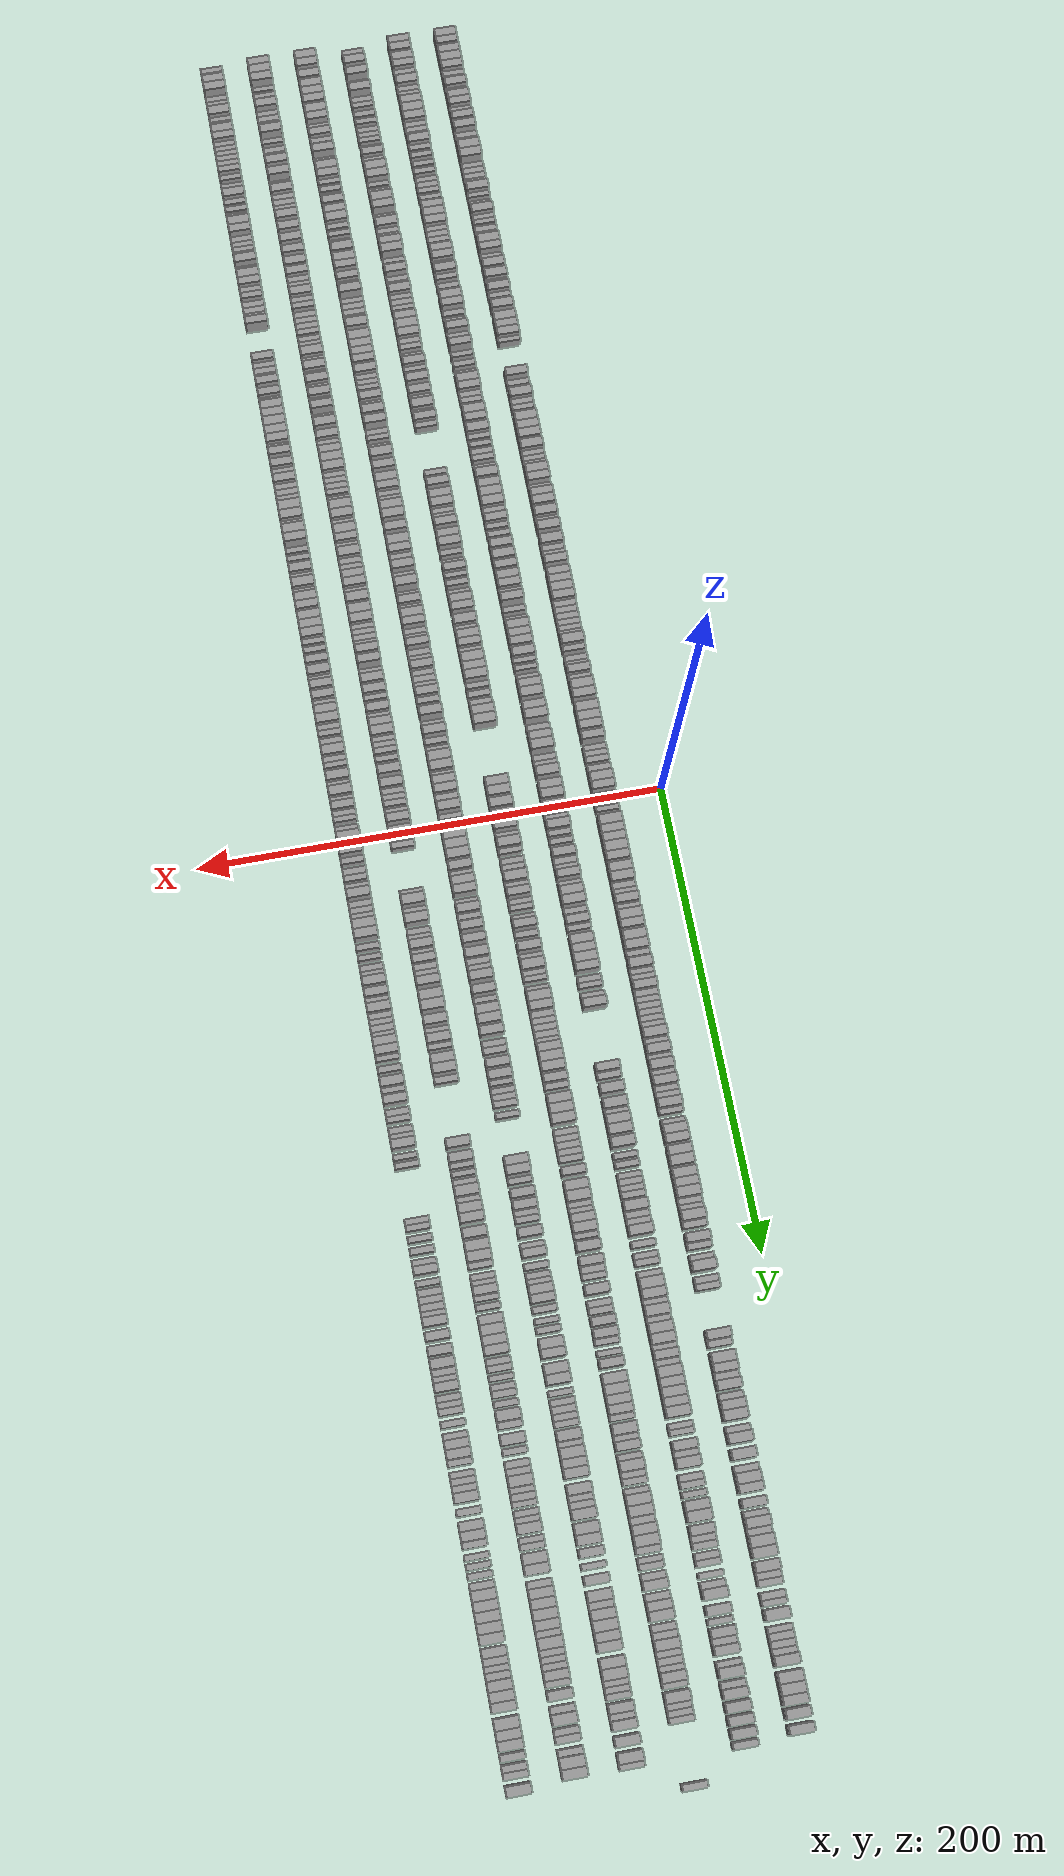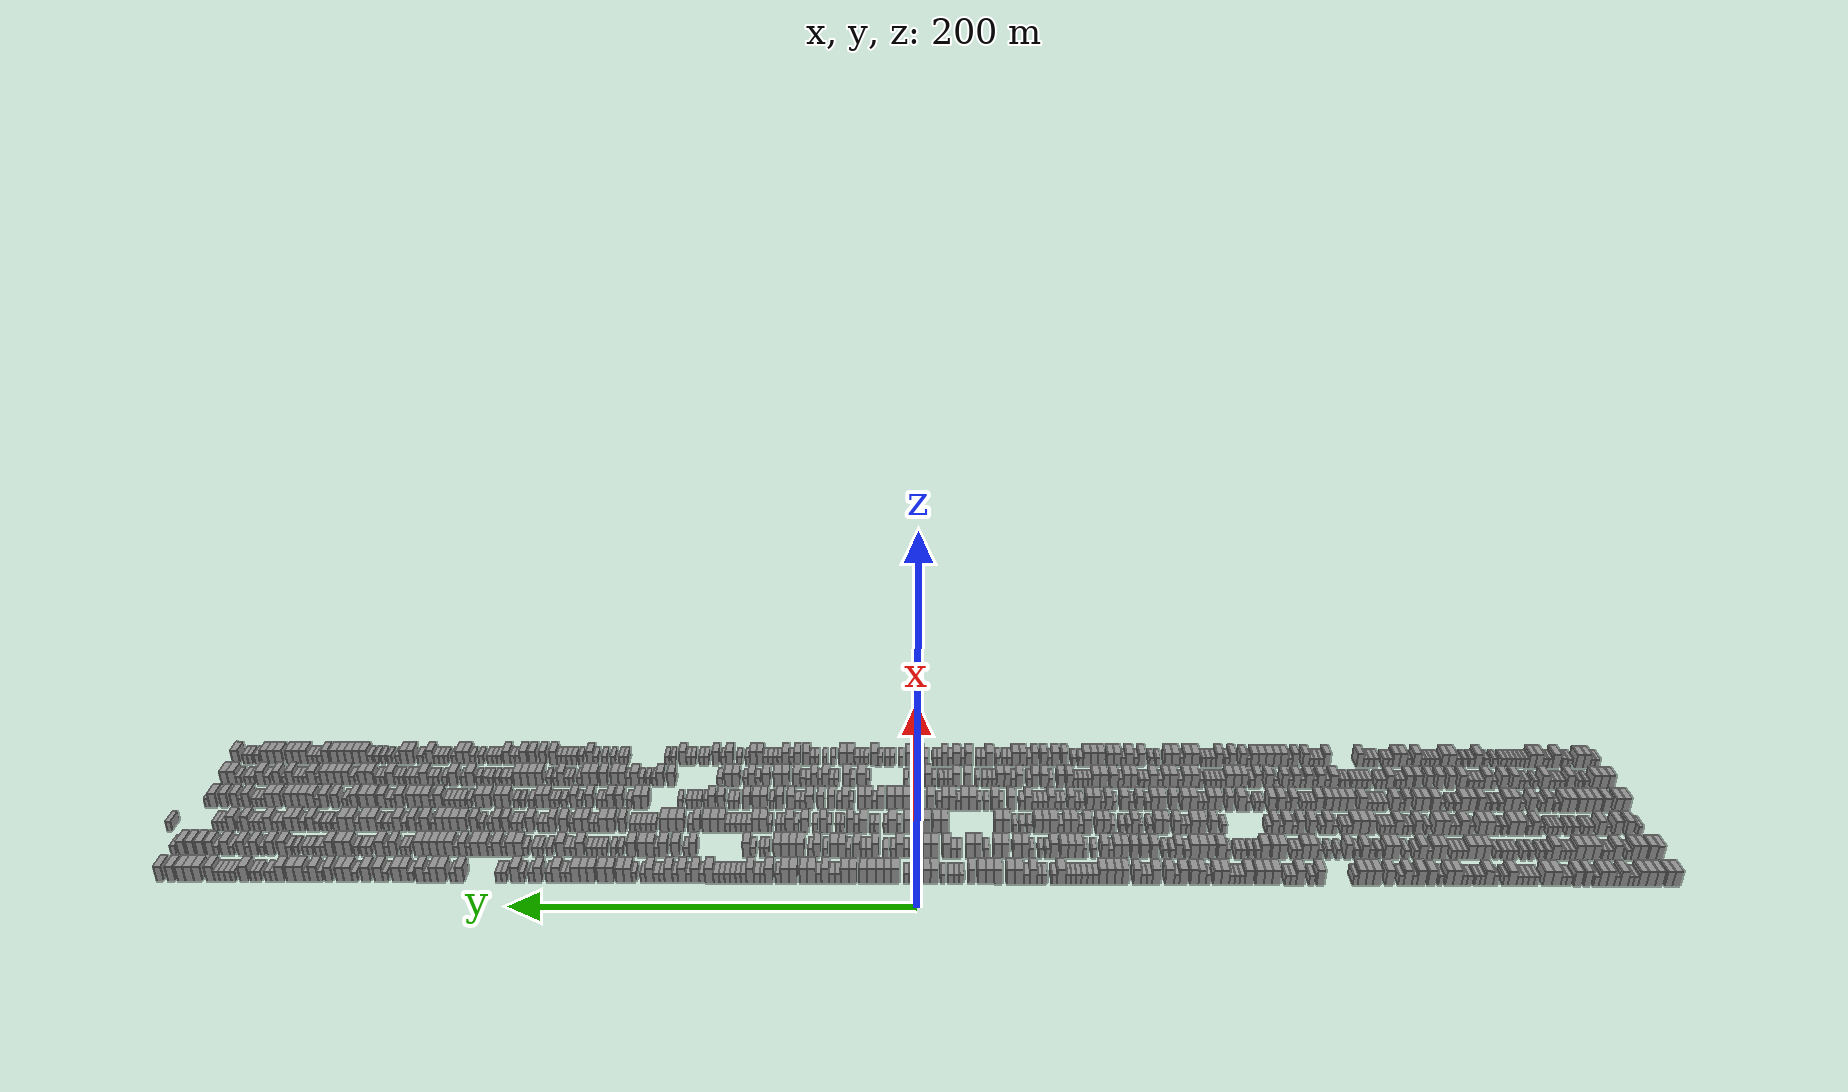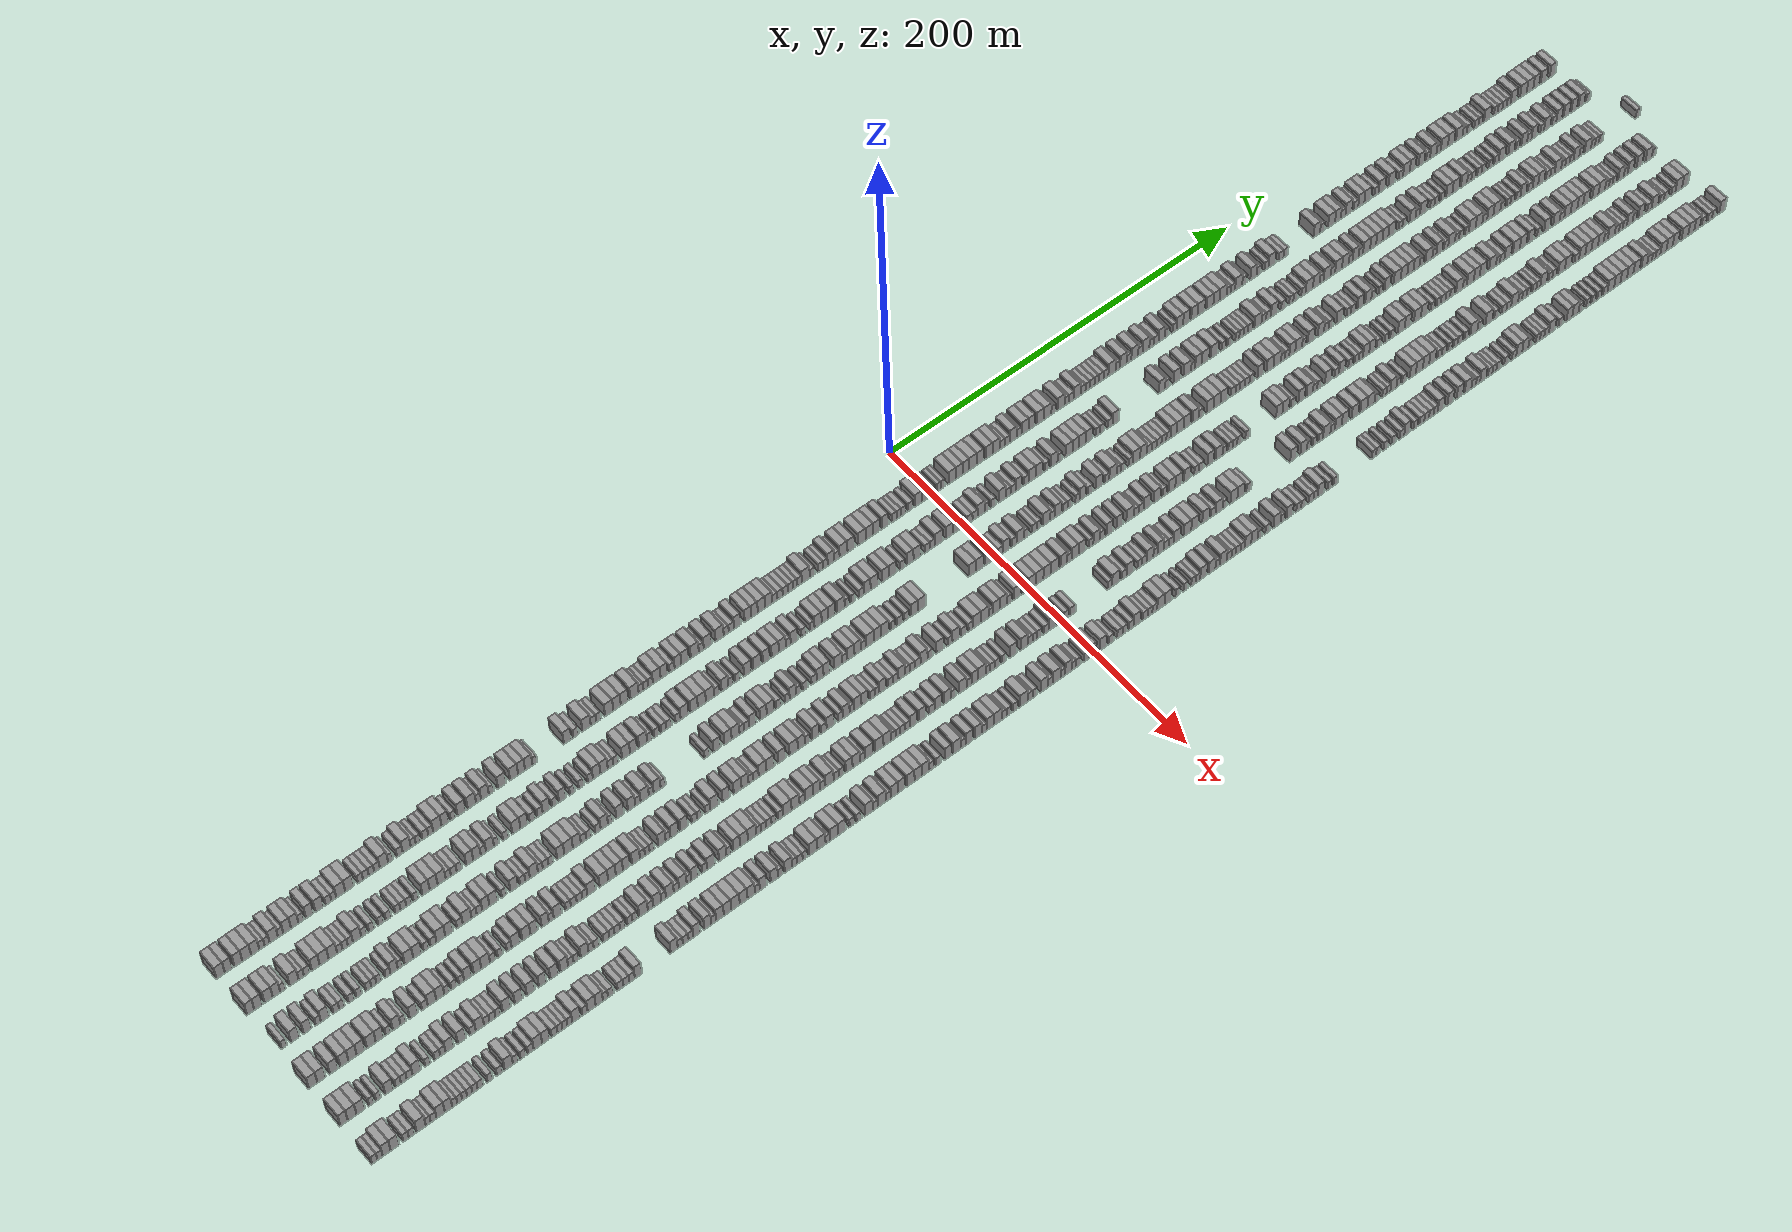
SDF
<sdf version="1.6">
 <world name="default">
  <scene>
   <sky><clouds><speed>12</speed></clouds></sky>
   <ambient>0.4 0.4 0.4 1</ambient>
   <background>0.7 0.7 0.7 1</background>
   <shadows>1</shadows>
  </scene>
  <gravity>0 0 -9.8066</gravity>
  <magnetic_field>6e-06 2.3e-05 -4.2e-05</magnetic_field>
  <physics default="0" name="default_physics" type="ode">
   <ode>
    <solver>
     <type>quick</type>
     <iters>10</iters>
     <sor>1.0</sor>
     <use_dynamic_moi_rescaling>0</use_dynamic_moi_rescaling>
    </solver>
    <constraints>
     <cfm>0</cfm>
     <erp>0.2</erp>
     <contact_max_correcting_vel>100</contact_max_correcting_vel>
     <contact_surface_layer>0.001</contact_surface_layer>
    </constraints>
   </ode>
   <max_step_size>0.004</max_step_size>
   <real_time_factor>1</real_time_factor>
   <real_time_update_rate>250</real_time_update_rate>
  </physics>
  <light name="sun" type="directional">
   <pose>0 0 10 0 0 0</pose>
   <diffuse>0.8 0.8 0.8 1</diffuse>
   <specular>0.2 0.2 0.2 1</specular>
   <attenuation>
    <range>1000</range>
    <constant>0.9</constant>
    <linear>0.01</linear>
    <quadratic>0.001</quadratic>
   </attenuation>
   <direction>-0.5 0.1 -0.9</direction>
  </light>
  <model name="building_1">
   <static>1</static>
   <pose>25.0000 -377.9014 0 0.000000 0.000000 0.000000</pose>
   <link name="link">
    <pose>0 0 4.50 0 0 0</pose>
    <collision name="collision"><geometry><box><size>10.0000 4.1972 9.0000</size></box></geometry></collision>
    <visual name="visual">
     <cast_shadows>0</cast_shadows>
     <geometry><box><size>10.0000 4.1972 9.0000</size></box></geometry>
     <material>
      <script>
       <uri>model://grey_wall/materials/scripts</uri>
       <uri>model://grey_wall/materials/textures</uri>
       <name>vrc/grey_wall</name>
      </script>
     </material>
    </visual>
   </link>
  </model>
  <model name="building_2">
   <static>1</static>
   <pose>25.0000 -373.9525 0 0.000000 0.000000 0.000000</pose>
   <link name="link">
    <pose>0 0 4.50 0 0 0</pose>
    <collision name="collision"><geometry><box><size>10.0000 3.7007 9.0000</size></box></geometry></collision>
    <visual name="visual">
     <cast_shadows>0</cast_shadows>
     <geometry><box><size>10.0000 3.7007 9.0000</size></box></geometry>
     <material>
      <script>
       <uri>model://grey_wall/materials/scripts</uri>
       <uri>model://grey_wall/materials/textures</uri>
       <name>vrc/grey_wall</name>
      </script>
     </material>
    </visual>
   </link>
  </model>
  <model name="building_3">
   <static>1</static>
   <pose>25.0000 -369.1578 0 0.000000 0.000000 0.000000</pose>
   <link name="link">
    <pose>0 0 4.50 0 0 0</pose>
    <collision name="collision"><geometry><box><size>10.0000 3.8887 9.0000</size></box></geometry></collision>
    <visual name="visual">
     <cast_shadows>0</cast_shadows>
     <geometry><box><size>10.0000 3.8887 9.0000</size></box></geometry>
     <material>
      <script>
       <uri>model://grey_wall/materials/scripts</uri>
       <uri>model://grey_wall/materials/textures</uri>
       <name>vrc/grey_wall</name>
      </script>
     </material>
    </visual>
   </link>
  </model>
  <model name="building_4">
   <static>1</static>
   <pose>25.0000 -365.0094 0 0.000000 0.000000 0.000000</pose>
   <link name="link">
    <pose>0 0 4.50 0 0 0</pose>
    <collision name="collision"><geometry><box><size>10.0000 4.4080 9.0000</size></box></geometry></collision>
    <visual name="visual">
     <cast_shadows>0</cast_shadows>
     <geometry><box><size>10.0000 4.4080 9.0000</size></box></geometry>
     <material>
      <script>
       <uri>model://grey_wall/materials/scripts</uri>
       <uri>model://grey_wall/materials/textures</uri>
       <name>vrc/grey_wall</name>
      </script>
     </material>
    </visual>
   </link>
  </model>
  <model name="building_5">
   <static>1</static>
   <pose>25.0000 -360.7854 0 0.000000 0.000000 0.000000</pose>
   <link name="link">
    <pose>0 0 4.50 0 0 0</pose>
    <collision name="collision"><geometry><box><size>10.0000 4.0401 9.0000</size></box></geometry></collision>
    <visual name="visual">
     <cast_shadows>0</cast_shadows>
     <geometry><box><size>10.0000 4.0401 9.0000</size></box></geometry>
     <material>
      <script>
       <uri>model://grey_wall/materials/scripts</uri>
       <uri>model://grey_wall/materials/textures</uri>
       <name>vrc/grey_wall</name>
      </script>
     </material>
    </visual>
   </link>
  </model>
  <model name="building_6">
   <static>1</static>
   <pose>25.0000 -357.4255 0 0.000000 0.000000 0.000000</pose>
   <link name="link">
    <pose>0 0 3.00 0 0 0</pose>
    <collision name="collision"><geometry><box><size>10.0000 2.6798 6.0000</size></box></geometry></collision>
    <visual name="visual">
     <cast_shadows>0</cast_shadows>
     <geometry><box><size>10.0000 2.6798 6.0000</size></box></geometry>
     <material>
      <script>
       <uri>model://grey_wall/materials/scripts</uri>
       <uri>model://grey_wall/materials/textures</uri>
       <name>vrc/grey_wall</name>
      </script>
     </material>
    </visual>
   </link>
  </model>
  <model name="building_7">
   <static>1</static>
   <pose>25.0000 -354.8704 0 0.000000 0.000000 0.000000</pose>
   <link name="link">
    <pose>0 0 3.00 0 0 0</pose>
    <collision name="collision"><geometry><box><size>10.0000 2.4304 6.0000</size></box></geometry></collision>
    <visual name="visual">
     <cast_shadows>0</cast_shadows>
     <geometry><box><size>10.0000 2.4304 6.0000</size></box></geometry>
     <material>
      <script>
       <uri>model://grey_wall/materials/scripts</uri>
       <uri>model://grey_wall/materials/textures</uri>
       <name>vrc/grey_wall</name>
      </script>
     </material>
    </visual>
   </link>
  </model>
  <model name="building_8">
   <static>1</static>
   <pose>25.0000 -351.5773 0 0.000000 0.000000 0.000000</pose>
   <link name="link">
    <pose>0 0 4.50 0 0 0</pose>
    <collision name="collision"><geometry><box><size>10.0000 4.1559 9.0000</size></box></geometry></collision>
    <visual name="visual">
     <cast_shadows>0</cast_shadows>
     <geometry><box><size>10.0000 4.1559 9.0000</size></box></geometry>
     <material>
      <script>
       <uri>model://grey_wall/materials/scripts</uri>
       <uri>model://grey_wall/materials/textures</uri>
       <name>vrc/grey_wall</name>
      </script>
     </material>
    </visual>
   </link>
  </model>
  <model name="building_9">
   <static>1</static>
   <pose>25.0000 -348.1490 0 0.000000 0.000000 0.000000</pose>
   <link name="link">
    <pose>0 0 3.00 0 0 0</pose>
    <collision name="collision"><geometry><box><size>10.0000 2.7007 6.0000</size></box></geometry></collision>
    <visual name="visual">
     <cast_shadows>0</cast_shadows>
     <geometry><box><size>10.0000 2.7007 6.0000</size></box></geometry>
     <material>
      <script>
       <uri>model://grey_wall/materials/scripts</uri>
       <uri>model://grey_wall/materials/textures</uri>
       <name>vrc/grey_wall</name>
      </script>
     </material>
    </visual>
   </link>
  </model>
  <model name="building_10">
   <static>1</static>
   <pose>25.0000 -344.9133 0 0.000000 0.000000 0.000000</pose>
   <link name="link">
    <pose>0 0 4.50 0 0 0</pose>
    <collision name="collision"><geometry><box><size>10.0000 3.7708 9.0000</size></box></geometry></collision>
    <visual name="visual">
     <cast_shadows>0</cast_shadows>
     <geometry><box><size>10.0000 3.7708 9.0000</size></box></geometry>
     <material>
      <script>
       <uri>model://grey_wall/materials/scripts</uri>
       <uri>model://grey_wall/materials/textures</uri>
       <name>vrc/grey_wall</name>
      </script>
     </material>
    </visual>
   </link>
  </model>
  <model name="building_11">
   <static>1</static>
   <pose>25.0000 -341.1425 0 0.000000 0.000000 0.000000</pose>
   <link name="link">
    <pose>0 0 4.50 0 0 0</pose>
    <collision name="collision"><geometry><box><size>10.0000 3.7708 9.0000</size></box></geometry></collision>
    <visual name="visual">
     <cast_shadows>0</cast_shadows>
     <geometry><box><size>10.0000 3.7708 9.0000</size></box></geometry>
     <material>
      <script>
       <uri>model://grey_wall/materials/scripts</uri>
       <uri>model://grey_wall/materials/textures</uri>
       <name>vrc/grey_wall</name>
      </script>
     </material>
    </visual>
   </link>
  </model>
  <model name="building_12">
   <static>1</static>
   <pose>25.0000 -337.8733 0 0.000000 0.000000 0.000000</pose>
   <link name="link">
    <pose>0 0 3.00 0 0 0</pose>
    <collision name="collision"><geometry><box><size>10.0000 2.7677 6.0000</size></box></geometry></collision>
    <visual name="visual">
     <cast_shadows>0</cast_shadows>
     <geometry><box><size>10.0000 2.7677 6.0000</size></box></geometry>
     <material>
      <script>
       <uri>model://grey_wall/materials/scripts</uri>
       <uri>model://grey_wall/materials/textures</uri>
       <name>vrc/grey_wall</name>
      </script>
     </material>
    </visual>
   </link>
  </model>
  <model name="building_13">
   <static>1</static>
   <pose>25.0000 -333.6231 0 0.000000 0.000000 0.000000</pose>
   <link name="link">
    <pose>0 0 4.50 0 0 0</pose>
    <collision name="collision"><geometry><box><size>10.0000 3.7328 9.0000</size></box></geometry></collision>
    <visual name="visual">
     <cast_shadows>0</cast_shadows>
     <geometry><box><size>10.0000 3.7328 9.0000</size></box></geometry>
     <material>
      <script>
       <uri>model://grey_wall/materials/scripts</uri>
       <uri>model://grey_wall/materials/textures</uri>
       <name>vrc/grey_wall</name>
      </script>
     </material>
    </visual>
   </link>
  </model>
  <model name="building_14">
   <static>1</static>
   <pose>25.0000 -328.6985 0 0.000000 0.000000 0.000000</pose>
   <link name="link">
    <pose>0 0 4.50 0 0 0</pose>
    <collision name="collision"><geometry><box><size>10.0000 4.1164 9.0000</size></box></geometry></collision>
    <visual name="visual">
     <cast_shadows>0</cast_shadows>
     <geometry><box><size>10.0000 4.1164 9.0000</size></box></geometry>
     <material>
      <script>
       <uri>model://grey_wall/materials/scripts</uri>
       <uri>model://grey_wall/materials/textures</uri>
       <name>vrc/grey_wall</name>
      </script>
     </material>
    </visual>
   </link>
  </model>
  <model name="building_15">
   <static>1</static>
   <pose>25.0000 -324.2007 0 0.000000 0.000000 0.000000</pose>
   <link name="link">
    <pose>0 0 3.00 0 0 0</pose>
    <collision name="collision"><geometry><box><size>10.0000 2.8793 6.0000</size></box></geometry></collision>
    <visual name="visual">
     <cast_shadows>0</cast_shadows>
     <geometry><box><size>10.0000 2.8793 6.0000</size></box></geometry>
     <material>
      <script>
       <uri>model://grey_wall/materials/scripts</uri>
       <uri>model://grey_wall/materials/textures</uri>
       <name>vrc/grey_wall</name>
      </script>
     </material>
    </visual>
   </link>
  </model>
  <model name="building_16">
   <static>1</static>
   <pose>25.0000 -321.5026 0 0.000000 0.000000 0.000000</pose>
   <link name="link">
    <pose>0 0 3.00 0 0 0</pose>
    <collision name="collision"><geometry><box><size>10.0000 2.5169 6.0000</size></box></geometry></collision>
    <visual name="visual">
     <cast_shadows>0</cast_shadows>
     <geometry><box><size>10.0000 2.5169 6.0000</size></box></geometry>
     <material>
      <script>
       <uri>model://grey_wall/materials/scripts</uri>
       <uri>model://grey_wall/materials/textures</uri>
       <name>vrc/grey_wall</name>
      </script>
     </material>
    </visual>
   </link>
  </model>
  <model name="building_17">
   <static>1</static>
   <pose>25.0000 -317.9972 0 0.000000 0.000000 0.000000</pose>
   <link name="link">
    <pose>0 0 4.50 0 0 0</pose>
    <collision name="collision"><geometry><box><size>10.0000 4.4939 9.0000</size></box></geometry></collision>
    <visual name="visual">
     <cast_shadows>0</cast_shadows>
     <geometry><box><size>10.0000 4.4939 9.0000</size></box></geometry>
     <material>
      <script>
       <uri>model://grey_wall/materials/scripts</uri>
       <uri>model://grey_wall/materials/textures</uri>
       <name>vrc/grey_wall</name>
      </script>
     </material>
    </visual>
   </link>
  </model>
  <model name="building_18">
   <static>1</static>
   <pose>25.0000 -313.5573 0 0.000000 0.000000 0.000000</pose>
   <link name="link">
    <pose>0 0 4.50 0 0 0</pose>
    <collision name="collision"><geometry><box><size>10.0000 4.3858 9.0000</size></box></geometry></collision>
    <visual name="visual">
     <cast_shadows>0</cast_shadows>
     <geometry><box><size>10.0000 4.3858 9.0000</size></box></geometry>
     <material>
      <script>
       <uri>model://grey_wall/materials/scripts</uri>
       <uri>model://grey_wall/materials/textures</uri>
       <name>vrc/grey_wall</name>
      </script>
     </material>
    </visual>
   </link>
  </model>
  <model name="building_19">
   <static>1</static>
   <pose>25.0000 -308.0744 0 0.000000 0.000000 0.000000</pose>
   <link name="link">
    <pose>0 0 3.00 0 0 0</pose>
    <collision name="collision"><geometry><box><size>10.0000 2.5801 6.0000</size></box></geometry></collision>
    <visual name="visual">
     <cast_shadows>0</cast_shadows>
     <geometry><box><size>10.0000 2.5801 6.0000</size></box></geometry>
     <material>
      <script>
       <uri>model://grey_wall/materials/scripts</uri>
       <uri>model://grey_wall/materials/textures</uri>
       <name>vrc/grey_wall</name>
      </script>
     </material>
    </visual>
   </link>
  </model>
  <model name="building_20">
   <static>1</static>
   <pose>25.0000 -305.3306 0 0.000000 0.000000 0.000000</pose>
   <link name="link">
    <pose>0 0 3.00 0 0 0</pose>
    <collision name="collision"><geometry><box><size>10.0000 2.9074 6.0000</size></box></geometry></collision>
    <visual name="visual">
     <cast_shadows>0</cast_shadows>
     <geometry><box><size>10.0000 2.9074 6.0000</size></box></geometry>
     <material>
      <script>
       <uri>model://grey_wall/materials/scripts</uri>
       <uri>model://grey_wall/materials/textures</uri>
       <name>vrc/grey_wall</name>
      </script>
     </material>
    </visual>
   </link>
  </model>
  <model name="building_21">
   <static>1</static>
   <pose>25.0000 -302.4756 0 0.000000 0.000000 0.000000</pose>
   <link name="link">
    <pose>0 0 3.00 0 0 0</pose>
    <collision name="collision"><geometry><box><size>10.0000 2.8027 6.0000</size></box></geometry></collision>
    <visual name="visual">
     <cast_shadows>0</cast_shadows>
     <geometry><box><size>10.0000 2.8027 6.0000</size></box></geometry>
     <material>
      <script>
       <uri>model://grey_wall/materials/scripts</uri>
       <uri>model://grey_wall/materials/textures</uri>
       <name>vrc/grey_wall</name>
      </script>
     </material>
    </visual>
   </link>
  </model>
  <model name="building_22">
   <static>1</static>
   <pose>25.0000 -299.6530 0 0.000000 0.000000 0.000000</pose>
   <link name="link">
    <pose>0 0 3.00 0 0 0</pose>
    <collision name="collision"><geometry><box><size>10.0000 2.8426 6.0000</size></box></geometry></collision>
    <visual name="visual">
     <cast_shadows>0</cast_shadows>
     <geometry><box><size>10.0000 2.8426 6.0000</size></box></geometry>
     <material>
      <script>
       <uri>model://grey_wall/materials/scripts</uri>
       <uri>model://grey_wall/materials/textures</uri>
       <name>vrc/grey_wall</name>
      </script>
     </material>
    </visual>
   </link>
  </model>
  <model name="building_23">
   <static>1</static>
   <pose>25.0000 -296.0908 0 0.000000 0.000000 0.000000</pose>
   <link name="link">
    <pose>0 0 4.50 0 0 0</pose>
    <collision name="collision"><geometry><box><size>10.0000 4.2818 9.0000</size></box></geometry></collision>
    <visual name="visual">
     <cast_shadows>0</cast_shadows>
     <geometry><box><size>10.0000 4.2818 9.0000</size></box></geometry>
     <material>
      <script>
       <uri>model://grey_wall/materials/scripts</uri>
       <uri>model://grey_wall/materials/textures</uri>
       <name>vrc/grey_wall</name>
      </script>
     </material>
    </visual>
   </link>
  </model>
  <model name="building_24">
   <static>1</static>
   <pose>25.0000 -292.7129 0 0.000000 0.000000 0.000000</pose>
   <link name="link">
    <pose>0 0 3.00 0 0 0</pose>
    <collision name="collision"><geometry><box><size>10.0000 2.4739 6.0000</size></box></geometry></collision>
    <visual name="visual">
     <cast_shadows>0</cast_shadows>
     <geometry><box><size>10.0000 2.4739 6.0000</size></box></geometry>
     <material>
      <script>
       <uri>model://grey_wall/materials/scripts</uri>
       <uri>model://grey_wall/materials/textures</uri>
       <name>vrc/grey_wall</name>
      </script>
     </material>
    </visual>
   </link>
  </model>
  <model name="building_25">
   <static>1</static>
   <pose>25.0000 -288.0265 0 0.000000 0.000000 0.000000</pose>
   <link name="link">
    <pose>0 0 3.00 0 0 0</pose>
    <collision name="collision"><geometry><box><size>10.0000 2.8990 6.0000</size></box></geometry></collision>
    <visual name="visual">
     <cast_shadows>0</cast_shadows>
     <geometry><box><size>10.0000 2.8990 6.0000</size></box></geometry>
     <material>
      <script>
       <uri>model://grey_wall/materials/scripts</uri>
       <uri>model://grey_wall/materials/textures</uri>
       <name>vrc/grey_wall</name>
      </script>
     </material>
    </visual>
   </link>
  </model>
  <model name="building_26">
   <static>1</static>
   <pose>25.0000 -284.4614 0 0.000000 0.000000 0.000000</pose>
   <link name="link">
    <pose>0 0 4.50 0 0 0</pose>
    <collision name="collision"><geometry><box><size>10.0000 4.2312 9.0000</size></box></geometry></collision>
    <visual name="visual">
     <cast_shadows>0</cast_shadows>
     <geometry><box><size>10.0000 4.2312 9.0000</size></box></geometry>
     <material>
      <script>
       <uri>model://grey_wall/materials/scripts</uri>
       <uri>model://grey_wall/materials/textures</uri>
       <name>vrc/grey_wall</name>
      </script>
     </material>
    </visual>
   </link>
  </model>
  <model name="building_27">
   <static>1</static>
   <pose>25.0000 -281.1152 0 0.000000 0.000000 0.000000</pose>
   <link name="link">
    <pose>0 0 3.00 0 0 0</pose>
    <collision name="collision"><geometry><box><size>10.0000 2.4614 6.0000</size></box></geometry></collision>
    <visual name="visual">
     <cast_shadows>0</cast_shadows>
     <geometry><box><size>10.0000 2.4614 6.0000</size></box></geometry>
     <material>
      <script>
       <uri>model://grey_wall/materials/scripts</uri>
       <uri>model://grey_wall/materials/textures</uri>
       <name>vrc/grey_wall</name>
      </script>
     </material>
    </visual>
   </link>
  </model>
  <model name="building_28">
   <static>1</static>
   <pose>25.0000 -278.6442 0 0.000000 0.000000 0.000000</pose>
   <link name="link">
    <pose>0 0 3.00 0 0 0</pose>
    <collision name="collision"><geometry><box><size>10.0000 2.4805 6.0000</size></box></geometry></collision>
    <visual name="visual">
     <cast_shadows>0</cast_shadows>
     <geometry><box><size>10.0000 2.4805 6.0000</size></box></geometry>
     <material>
      <script>
       <uri>model://grey_wall/materials/scripts</uri>
       <uri>model://grey_wall/materials/textures</uri>
       <name>vrc/grey_wall</name>
      </script>
     </material>
    </visual>
   </link>
  </model>
  <model name="building_29">
   <static>1</static>
   <pose>25.0000 -274.9256 0 0.000000 0.000000 0.000000</pose>
   <link name="link">
    <pose>0 0 3.00 0 0 0</pose>
    <collision name="collision"><geometry><box><size>10.0000 2.9566 6.0000</size></box></geometry></collision>
    <visual name="visual">
     <cast_shadows>0</cast_shadows>
     <geometry><box><size>10.0000 2.9566 6.0000</size></box></geometry>
     <material>
      <script>
       <uri>model://grey_wall/materials/scripts</uri>
       <uri>model://grey_wall/materials/textures</uri>
       <name>vrc/grey_wall</name>
      </script>
     </material>
    </visual>
   </link>
  </model>
  <model name="building_30">
   <static>1</static>
   <pose>25.0000 -272.1992 0 0.000000 0.000000 0.000000</pose>
   <link name="link">
    <pose>0 0 3.00 0 0 0</pose>
    <collision name="collision"><geometry><box><size>10.0000 2.4963 6.0000</size></box></geometry></collision>
    <visual name="visual">
     <cast_shadows>0</cast_shadows>
     <geometry><box><size>10.0000 2.4963 6.0000</size></box></geometry>
     <material>
      <script>
       <uri>model://grey_wall/materials/scripts</uri>
       <uri>model://grey_wall/materials/textures</uri>
       <name>vrc/grey_wall</name>
      </script>
     </material>
    </visual>
   </link>
  </model>
  <model name="building_31">
   <static>1</static>
   <pose>25.0000 -268.7673 0 0.000000 0.000000 0.000000</pose>
   <link name="link">
    <pose>0 0 4.50 0 0 0</pose>
    <collision name="collision"><geometry><box><size>10.0000 4.3674 9.0000</size></box></geometry></collision>
    <visual name="visual">
     <cast_shadows>0</cast_shadows>
     <geometry><box><size>10.0000 4.3674 9.0000</size></box></geometry>
     <material>
      <script>
       <uri>model://grey_wall/materials/scripts</uri>
       <uri>model://grey_wall/materials/textures</uri>
       <name>vrc/grey_wall</name>
      </script>
     </material>
    </visual>
   </link>
  </model>
  <model name="building_32">
   <static>1</static>
   <pose>25.0000 -264.7406 0 0.000000 0.000000 0.000000</pose>
   <link name="link">
    <pose>0 0 4.50 0 0 0</pose>
    <collision name="collision"><geometry><box><size>10.0000 3.6861 9.0000</size></box></geometry></collision>
    <visual name="visual">
     <cast_shadows>0</cast_shadows>
     <geometry><box><size>10.0000 3.6861 9.0000</size></box></geometry>
     <material>
      <script>
       <uri>model://grey_wall/materials/scripts</uri>
       <uri>model://grey_wall/materials/textures</uri>
       <name>vrc/grey_wall</name>
      </script>
     </material>
    </visual>
   </link>
  </model>
  <model name="building_33">
   <static>1</static>
   <pose>25.0000 -260.6322 0 0.000000 0.000000 0.000000</pose>
   <link name="link">
    <pose>0 0 3.00 0 0 0</pose>
    <collision name="collision"><geometry><box><size>10.0000 2.5305 6.0000</size></box></geometry></collision>
    <visual name="visual">
     <cast_shadows>0</cast_shadows>
     <geometry><box><size>10.0000 2.5305 6.0000</size></box></geometry>
     <material>
      <script>
       <uri>model://grey_wall/materials/scripts</uri>
       <uri>model://grey_wall/materials/textures</uri>
       <name>vrc/grey_wall</name>
      </script>
     </material>
    </visual>
   </link>
  </model>
  <model name="building_34">
   <static>1</static>
   <pose>25.0000 -256.2392 0 0.000000 0.000000 0.000000</pose>
   <link name="link">
    <pose>0 0 4.50 0 0 0</pose>
    <collision name="collision"><geometry><box><size>10.0000 4.2555 9.0000</size></box></geometry></collision>
    <visual name="visual">
     <cast_shadows>0</cast_shadows>
     <geometry><box><size>10.0000 4.2555 9.0000</size></box></geometry>
     <material>
      <script>
       <uri>model://grey_wall/materials/scripts</uri>
       <uri>model://grey_wall/materials/textures</uri>
       <name>vrc/grey_wall</name>
      </script>
     </material>
    </visual>
   </link>
  </model>
  <model name="building_35">
   <static>1</static>
   <pose>25.0000 -250.9483 0 0.000000 0.000000 0.000000</pose>
   <link name="link">
    <pose>0 0 4.50 0 0 0</pose>
    <collision name="collision"><geometry><box><size>10.0000 4.3264 9.0000</size></box></geometry></collision>
    <visual name="visual">
     <cast_shadows>0</cast_shadows>
     <geometry><box><size>10.0000 4.3264 9.0000</size></box></geometry>
     <material>
      <script>
       <uri>model://grey_wall/materials/scripts</uri>
       <uri>model://grey_wall/materials/textures</uri>
       <name>vrc/grey_wall</name>
      </script>
     </material>
    </visual>
   </link>
  </model>
  <model name="building_36">
   <static>1</static>
   <pose>25.0000 -247.4791 0 0.000000 0.000000 0.000000</pose>
   <link name="link">
    <pose>0 0 3.00 0 0 0</pose>
    <collision name="collision"><geometry><box><size>10.0000 2.6121 6.0000</size></box></geometry></collision>
    <visual name="visual">
     <cast_shadows>0</cast_shadows>
     <geometry><box><size>10.0000 2.6121 6.0000</size></box></geometry>
     <material>
      <script>
       <uri>model://grey_wall/materials/scripts</uri>
       <uri>model://grey_wall/materials/textures</uri>
       <name>vrc/grey_wall</name>
      </script>
     </material>
    </visual>
   </link>
  </model>
  <model name="building_37">
   <static>1</static>
   <pose>25.0000 -244.1470 0 0.000000 0.000000 0.000000</pose>
   <link name="link">
    <pose>0 0 4.50 0 0 0</pose>
    <collision name="collision"><geometry><box><size>10.0000 4.0521 9.0000</size></box></geometry></collision>
    <visual name="visual">
     <cast_shadows>0</cast_shadows>
     <geometry><box><size>10.0000 4.0521 9.0000</size></box></geometry>
     <material>
      <script>
       <uri>model://grey_wall/materials/scripts</uri>
       <uri>model://grey_wall/materials/textures</uri>
       <name>vrc/grey_wall</name>
      </script>
     </material>
    </visual>
   </link>
  </model>
  <model name="building_38">
   <static>1</static>
   <pose>25.0000 -240.7770 0 0.000000 0.000000 0.000000</pose>
   <link name="link">
    <pose>0 0 3.00 0 0 0</pose>
    <collision name="collision"><geometry><box><size>10.0000 2.6880 6.0000</size></box></geometry></collision>
    <visual name="visual">
     <cast_shadows>0</cast_shadows>
     <geometry><box><size>10.0000 2.6880 6.0000</size></box></geometry>
     <material>
      <script>
       <uri>model://grey_wall/materials/scripts</uri>
       <uri>model://grey_wall/materials/textures</uri>
       <name>vrc/grey_wall</name>
      </script>
     </material>
    </visual>
   </link>
  </model>
  <model name="building_39">
   <static>1</static>
   <pose>25.0000 -235.2704 0 0.000000 0.000000 0.000000</pose>
   <link name="link">
    <pose>0 0 4.50 0 0 0</pose>
    <collision name="collision"><geometry><box><size>10.0000 4.3251 9.0000</size></box></geometry></collision>
    <visual name="visual">
     <cast_shadows>0</cast_shadows>
     <geometry><box><size>10.0000 4.3251 9.0000</size></box></geometry>
     <material>
      <script>
       <uri>model://grey_wall/materials/scripts</uri>
       <uri>model://grey_wall/materials/textures</uri>
       <name>vrc/grey_wall</name>
      </script>
     </material>
    </visual>
   </link>
  </model>
  <model name="building_40">
   <static>1</static>
   <pose>25.0000 -228.9742 0 0.000000 0.000000 0.000000</pose>
   <link name="link">
    <pose>0 0 4.50 0 0 0</pose>
    <collision name="collision"><geometry><box><size>10.0000 4.2672 9.0000</size></box></geometry></collision>
    <visual name="visual">
     <cast_shadows>0</cast_shadows>
     <geometry><box><size>10.0000 4.2672 9.0000</size></box></geometry>
     <material>
      <script>
       <uri>model://grey_wall/materials/scripts</uri>
       <uri>model://grey_wall/materials/textures</uri>
       <name>vrc/grey_wall</name>
      </script>
     </material>
    </visual>
   </link>
  </model>
  <model name="building_41">
   <static>1</static>
   <pose>25.0000 -225.0343 0 0.000000 0.000000 0.000000</pose>
   <link name="link">
    <pose>0 0 4.50 0 0 0</pose>
    <collision name="collision"><geometry><box><size>10.0000 3.6128 9.0000</size></box></geometry></collision>
    <visual name="visual">
     <cast_shadows>0</cast_shadows>
     <geometry><box><size>10.0000 3.6128 9.0000</size></box></geometry>
     <material>
      <script>
       <uri>model://grey_wall/materials/scripts</uri>
       <uri>model://grey_wall/materials/textures</uri>
       <name>vrc/grey_wall</name>
      </script>
     </material>
    </visual>
   </link>
  </model>
  <model name="building_42">
   <static>1</static>
   <pose>25.0000 -221.2701 0 0.000000 0.000000 0.000000</pose>
   <link name="link">
    <pose>0 0 4.50 0 0 0</pose>
    <collision name="collision"><geometry><box><size>10.0000 3.9156 9.0000</size></box></geometry></collision>
    <visual name="visual">
     <cast_shadows>0</cast_shadows>
     <geometry><box><size>10.0000 3.9156 9.0000</size></box></geometry>
     <material>
      <script>
       <uri>model://grey_wall/materials/scripts</uri>
       <uri>model://grey_wall/materials/textures</uri>
       <name>vrc/grey_wall</name>
      </script>
     </material>
    </visual>
   </link>
  </model>
  <model name="building_43">
   <static>1</static>
   <pose>25.0000 -218.1112 0 0.000000 0.000000 0.000000</pose>
   <link name="link">
    <pose>0 0 3.00 0 0 0</pose>
    <collision name="collision"><geometry><box><size>10.0000 2.4021 6.0000</size></box></geometry></collision>
    <visual name="visual">
     <cast_shadows>0</cast_shadows>
     <geometry><box><size>10.0000 2.4021 6.0000</size></box></geometry>
     <material>
      <script>
       <uri>model://grey_wall/materials/scripts</uri>
       <uri>model://grey_wall/materials/textures</uri>
       <name>vrc/grey_wall</name>
      </script>
     </material>
    </visual>
   </link>
  </model>
  <model name="building_44">
   <static>1</static>
   <pose>25.0000 -200.8875 0 0.000000 0.000000 0.000000</pose>
   <link name="link">
    <pose>0 0 4.50 0 0 0</pose>
    <collision name="collision"><geometry><box><size>10.0000 4.0151 9.0000</size></box></geometry></collision>
    <visual name="visual">
     <cast_shadows>0</cast_shadows>
     <geometry><box><size>10.0000 4.0151 9.0000</size></box></geometry>
     <material>
      <script>
       <uri>model://grey_wall/materials/scripts</uri>
       <uri>model://grey_wall/materials/textures</uri>
       <name>vrc/grey_wall</name>
      </script>
     </material>
    </visual>
   </link>
  </model>
  <model name="building_45">
   <static>1</static>
   <pose>25.0000 -196.4308 0 0.000000 0.000000 0.000000</pose>
   <link name="link">
    <pose>0 0 3.00 0 0 0</pose>
    <collision name="collision"><geometry><box><size>10.0000 2.8984 6.0000</size></box></geometry></collision>
    <visual name="visual">
     <cast_shadows>0</cast_shadows>
     <geometry><box><size>10.0000 2.8984 6.0000</size></box></geometry>
     <material>
      <script>
       <uri>model://grey_wall/materials/scripts</uri>
       <uri>model://grey_wall/materials/textures</uri>
       <name>vrc/grey_wall</name>
      </script>
     </material>
    </visual>
   </link>
  </model>
  <model name="building_46">
   <static>1</static>
   <pose>25.0000 -190.7838 0 0.000000 0.000000 0.000000</pose>
   <link name="link">
    <pose>0 0 4.50 0 0 0</pose>
    <collision name="collision"><geometry><box><size>10.0000 4.3955 9.0000</size></box></geometry></collision>
    <visual name="visual">
     <cast_shadows>0</cast_shadows>
     <geometry><box><size>10.0000 4.3955 9.0000</size></box></geometry>
     <material>
      <script>
       <uri>model://grey_wall/materials/scripts</uri>
       <uri>model://grey_wall/materials/textures</uri>
       <name>vrc/grey_wall</name>
      </script>
     </material>
    </visual>
   </link>
  </model>
  <model name="building_47">
   <static>1</static>
   <pose>25.0000 -187.1264 0 0.000000 0.000000 0.000000</pose>
   <link name="link">
    <pose>0 0 3.00 0 0 0</pose>
    <collision name="collision"><geometry><box><size>10.0000 2.9193 6.0000</size></box></geometry></collision>
    <visual name="visual">
     <cast_shadows>0</cast_shadows>
     <geometry><box><size>10.0000 2.9193 6.0000</size></box></geometry>
     <material>
      <script>
       <uri>model://grey_wall/materials/scripts</uri>
       <uri>model://grey_wall/materials/textures</uri>
       <name>vrc/grey_wall</name>
      </script>
     </material>
    </visual>
   </link>
  </model>
  <model name="building_48">
   <static>1</static>
   <pose>25.0000 -184.3268 0 0.000000 0.000000 0.000000</pose>
   <link name="link">
    <pose>0 0 3.00 0 0 0</pose>
    <collision name="collision"><geometry><box><size>10.0000 2.6798 6.0000</size></box></geometry></collision>
    <visual name="visual">
     <cast_shadows>0</cast_shadows>
     <geometry><box><size>10.0000 2.6798 6.0000</size></box></geometry>
     <material>
      <script>
       <uri>model://grey_wall/materials/scripts</uri>
       <uri>model://grey_wall/materials/textures</uri>
       <name>vrc/grey_wall</name>
      </script>
     </material>
    </visual>
   </link>
  </model>
  <model name="building_49">
   <static>1</static>
   <pose>25.0000 -178.7827 0 0.000000 0.000000 0.000000</pose>
   <link name="link">
    <pose>0 0 4.50 0 0 0</pose>
    <collision name="collision"><geometry><box><size>10.0000 4.4084 9.0000</size></box></geometry></collision>
    <visual name="visual">
     <cast_shadows>0</cast_shadows>
     <geometry><box><size>10.0000 4.4084 9.0000</size></box></geometry>
     <material>
      <script>
       <uri>model://grey_wall/materials/scripts</uri>
       <uri>model://grey_wall/materials/textures</uri>
       <name>vrc/grey_wall</name>
      </script>
     </material>
    </visual>
   </link>
  </model>
  <model name="building_50">
   <static>1</static>
   <pose>25.0000 -174.5790 0 0.000000 0.000000 0.000000</pose>
   <link name="link">
    <pose>0 0 4.50 0 0 0</pose>
    <collision name="collision"><geometry><box><size>10.0000 3.9990 9.0000</size></box></geometry></collision>
    <visual name="visual">
     <cast_shadows>0</cast_shadows>
     <geometry><box><size>10.0000 3.9990 9.0000</size></box></geometry>
     <material>
      <script>
       <uri>model://grey_wall/materials/scripts</uri>
       <uri>model://grey_wall/materials/textures</uri>
       <name>vrc/grey_wall</name>
      </script>
     </material>
    </visual>
   </link>
  </model>
  <model name="building_51">
   <static>1</static>
   <pose>25.0000 -170.5038 0 0.000000 0.000000 0.000000</pose>
   <link name="link">
    <pose>0 0 4.50 0 0 0</pose>
    <collision name="collision"><geometry><box><size>10.0000 4.1513 9.0000</size></box></geometry></collision>
    <visual name="visual">
     <cast_shadows>0</cast_shadows>
     <geometry><box><size>10.0000 4.1513 9.0000</size></box></geometry>
     <material>
      <script>
       <uri>model://grey_wall/materials/scripts</uri>
       <uri>model://grey_wall/materials/textures</uri>
       <name>vrc/grey_wall</name>
      </script>
     </material>
    </visual>
   </link>
  </model>
  <model name="building_52">
   <static>1</static>
   <pose>25.0000 -165.2198 0 0.000000 0.000000 0.000000</pose>
   <link name="link">
    <pose>0 0 4.50 0 0 0</pose>
    <collision name="collision"><geometry><box><size>10.0000 4.4166 9.0000</size></box></geometry></collision>
    <visual name="visual">
     <cast_shadows>0</cast_shadows>
     <geometry><box><size>10.0000 4.4166 9.0000</size></box></geometry>
     <material>
      <script>
       <uri>model://grey_wall/materials/scripts</uri>
       <uri>model://grey_wall/materials/textures</uri>
       <name>vrc/grey_wall</name>
      </script>
     </material>
    </visual>
   </link>
  </model>
  <model name="building_53">
   <static>1</static>
   <pose>25.0000 -161.7086 0 0.000000 0.000000 0.000000</pose>
   <link name="link">
    <pose>0 0 3.00 0 0 0</pose>
    <collision name="collision"><geometry><box><size>10.0000 2.6059 6.0000</size></box></geometry></collision>
    <visual name="visual">
     <cast_shadows>0</cast_shadows>
     <geometry><box><size>10.0000 2.6059 6.0000</size></box></geometry>
     <material>
      <script>
       <uri>model://grey_wall/materials/scripts</uri>
       <uri>model://grey_wall/materials/textures</uri>
       <name>vrc/grey_wall</name>
      </script>
     </material>
    </visual>
   </link>
  </model>
  <model name="building_54">
   <static>1</static>
   <pose>25.0000 -159.1766 0 0.000000 0.000000 0.000000</pose>
   <link name="link">
    <pose>0 0 3.00 0 0 0</pose>
    <collision name="collision"><geometry><box><size>10.0000 2.4581 6.0000</size></box></geometry></collision>
    <visual name="visual">
     <cast_shadows>0</cast_shadows>
     <geometry><box><size>10.0000 2.4581 6.0000</size></box></geometry>
     <material>
      <script>
       <uri>model://grey_wall/materials/scripts</uri>
       <uri>model://grey_wall/materials/textures</uri>
       <name>vrc/grey_wall</name>
      </script>
     </material>
    </visual>
   </link>
  </model>
  <model name="building_55">
   <static>1</static>
   <pose>25.0000 -156.6405 0 0.000000 0.000000 0.000000</pose>
   <link name="link">
    <pose>0 0 3.00 0 0 0</pose>
    <collision name="collision"><geometry><box><size>10.0000 2.6142 6.0000</size></box></geometry></collision>
    <visual name="visual">
     <cast_shadows>0</cast_shadows>
     <geometry><box><size>10.0000 2.6142 6.0000</size></box></geometry>
     <material>
      <script>
       <uri>model://grey_wall/materials/scripts</uri>
       <uri>model://grey_wall/materials/textures</uri>
       <name>vrc/grey_wall</name>
      </script>
     </material>
    </visual>
   </link>
  </model>
  <model name="building_56">
   <static>1</static>
   <pose>25.0000 -153.2643 0 0.000000 0.000000 0.000000</pose>
   <link name="link">
    <pose>0 0 4.50 0 0 0</pose>
    <collision name="collision"><geometry><box><size>10.0000 4.1381 9.0000</size></box></geometry></collision>
    <visual name="visual">
     <cast_shadows>0</cast_shadows>
     <geometry><box><size>10.0000 4.1381 9.0000</size></box></geometry>
     <material>
      <script>
       <uri>model://grey_wall/materials/scripts</uri>
       <uri>model://grey_wall/materials/textures</uri>
       <name>vrc/grey_wall</name>
      </script>
     </material>
    </visual>
   </link>
  </model>
  <model name="building_57">
   <static>1</static>
   <pose>25.0000 -149.2630 0 0.000000 0.000000 0.000000</pose>
   <link name="link">
    <pose>0 0 4.50 0 0 0</pose>
    <collision name="collision"><geometry><box><size>10.0000 3.8646 9.0000</size></box></geometry></collision>
    <visual name="visual">
     <cast_shadows>0</cast_shadows>
     <geometry><box><size>10.0000 3.8646 9.0000</size></box></geometry>
     <material>
      <script>
       <uri>model://grey_wall/materials/scripts</uri>
       <uri>model://grey_wall/materials/textures</uri>
       <name>vrc/grey_wall</name>
      </script>
     </material>
    </visual>
   </link>
  </model>
  <model name="building_58">
   <static>1</static>
   <pose>25.0000 -144.9823 0 0.000000 0.000000 0.000000</pose>
   <link name="link">
    <pose>0 0 3.00 0 0 0</pose>
    <collision name="collision"><geometry><box><size>10.0000 2.6967 6.0000</size></box></geometry></collision>
    <visual name="visual">
     <cast_shadows>0</cast_shadows>
     <geometry><box><size>10.0000 2.6967 6.0000</size></box></geometry>
     <material>
      <script>
       <uri>model://grey_wall/materials/scripts</uri>
       <uri>model://grey_wall/materials/textures</uri>
       <name>vrc/grey_wall</name>
      </script>
     </material>
    </visual>
   </link>
  </model>
  <model name="building_59">
   <static>1</static>
   <pose>25.0000 -141.8142 0 0.000000 0.000000 0.000000</pose>
   <link name="link">
    <pose>0 0 4.50 0 0 0</pose>
    <collision name="collision"><geometry><box><size>10.0000 3.6396 9.0000</size></box></geometry></collision>
    <visual name="visual">
     <cast_shadows>0</cast_shadows>
     <geometry><box><size>10.0000 3.6396 9.0000</size></box></geometry>
     <material>
      <script>
       <uri>model://grey_wall/materials/scripts</uri>
       <uri>model://grey_wall/materials/textures</uri>
       <name>vrc/grey_wall</name>
      </script>
     </material>
    </visual>
   </link>
  </model>
  <model name="building_60">
   <static>1</static>
   <pose>25.0000 -137.9425 0 0.000000 0.000000 0.000000</pose>
   <link name="link">
    <pose>0 0 4.50 0 0 0</pose>
    <collision name="collision"><geometry><box><size>10.0000 4.1037 9.0000</size></box></geometry></collision>
    <visual name="visual">
     <cast_shadows>0</cast_shadows>
     <geometry><box><size>10.0000 4.1037 9.0000</size></box></geometry>
     <material>
      <script>
       <uri>model://grey_wall/materials/scripts</uri>
       <uri>model://grey_wall/materials/textures</uri>
       <name>vrc/grey_wall</name>
      </script>
     </material>
    </visual>
   </link>
  </model>
  <model name="building_61">
   <static>1</static>
   <pose>25.0000 -132.6984 0 0.000000 0.000000 0.000000</pose>
   <link name="link">
    <pose>0 0 4.50 0 0 0</pose>
    <collision name="collision"><geometry><box><size>10.0000 4.3846 9.0000</size></box></geometry></collision>
    <visual name="visual">
     <cast_shadows>0</cast_shadows>
     <geometry><box><size>10.0000 4.3846 9.0000</size></box></geometry>
     <material>
      <script>
       <uri>model://grey_wall/materials/scripts</uri>
       <uri>model://grey_wall/materials/textures</uri>
       <name>vrc/grey_wall</name>
      </script>
     </material>
    </visual>
   </link>
  </model>
  <model name="building_62">
   <static>1</static>
   <pose>25.0000 -129.1732 0 0.000000 0.000000 0.000000</pose>
   <link name="link">
    <pose>0 0 3.00 0 0 0</pose>
    <collision name="collision"><geometry><box><size>10.0000 2.6657 6.0000</size></box></geometry></collision>
    <visual name="visual">
     <cast_shadows>0</cast_shadows>
     <geometry><box><size>10.0000 2.6657 6.0000</size></box></geometry>
     <material>
      <script>
       <uri>model://grey_wall/materials/scripts</uri>
       <uri>model://grey_wall/materials/textures</uri>
       <name>vrc/grey_wall</name>
      </script>
     </material>
    </visual>
   </link>
  </model>
  <model name="building_63">
   <static>1</static>
   <pose>25.0000 -125.6364 0 0.000000 0.000000 0.000000</pose>
   <link name="link">
    <pose>0 0 4.50 0 0 0</pose>
    <collision name="collision"><geometry><box><size>10.0000 4.4079 9.0000</size></box></geometry></collision>
    <visual name="visual">
     <cast_shadows>0</cast_shadows>
     <geometry><box><size>10.0000 4.4079 9.0000</size></box></geometry>
     <material>
      <script>
       <uri>model://grey_wall/materials/scripts</uri>
       <uri>model://grey_wall/materials/textures</uri>
       <name>vrc/grey_wall</name>
      </script>
     </material>
    </visual>
   </link>
  </model>
  <model name="building_64">
   <static>1</static>
   <pose>25.0000 -119.1926 0 0.000000 0.000000 0.000000</pose>
   <link name="link">
    <pose>0 0 4.50 0 0 0</pose>
    <collision name="collision"><geometry><box><size>10.0000 4.4797 9.0000</size></box></geometry></collision>
    <visual name="visual">
     <cast_shadows>0</cast_shadows>
     <geometry><box><size>10.0000 4.4797 9.0000</size></box></geometry>
     <material>
      <script>
       <uri>model://grey_wall/materials/scripts</uri>
       <uri>model://grey_wall/materials/textures</uri>
       <name>vrc/grey_wall</name>
      </script>
     </material>
    </visual>
   </link>
  </model>
  <model name="building_65">
   <static>1</static>
   <pose>25.0000 -115.5849 0 0.000000 0.000000 0.000000</pose>
   <link name="link">
    <pose>0 0 3.00 0 0 0</pose>
    <collision name="collision"><geometry><box><size>10.0000 2.7357 6.0000</size></box></geometry></collision>
    <visual name="visual">
     <cast_shadows>0</cast_shadows>
     <geometry><box><size>10.0000 2.7357 6.0000</size></box></geometry>
     <material>
      <script>
       <uri>model://grey_wall/materials/scripts</uri>
       <uri>model://grey_wall/materials/textures</uri>
       <name>vrc/grey_wall</name>
      </script>
     </material>
    </visual>
   </link>
  </model>
  <model name="building_66">
   <static>1</static>
   <pose>25.0000 -112.7701 0 0.000000 0.000000 0.000000</pose>
   <link name="link">
    <pose>0 0 3.00 0 0 0</pose>
    <collision name="collision"><geometry><box><size>10.0000 2.8938 6.0000</size></box></geometry></collision>
    <visual name="visual">
     <cast_shadows>0</cast_shadows>
     <geometry><box><size>10.0000 2.8938 6.0000</size></box></geometry>
     <material>
      <script>
       <uri>model://grey_wall/materials/scripts</uri>
       <uri>model://grey_wall/materials/textures</uri>
       <name>vrc/grey_wall</name>
      </script>
     </material>
    </visual>
   </link>
  </model>
  <model name="building_67">
   <static>1</static>
   <pose>25.0000 -109.4229 0 0.000000 0.000000 0.000000</pose>
   <link name="link">
    <pose>0 0 4.50 0 0 0</pose>
    <collision name="collision"><geometry><box><size>10.0000 3.8006 9.0000</size></box></geometry></collision>
    <visual name="visual">
     <cast_shadows>0</cast_shadows>
     <geometry><box><size>10.0000 3.8006 9.0000</size></box></geometry>
     <material>
      <script>
       <uri>model://grey_wall/materials/scripts</uri>
       <uri>model://grey_wall/materials/textures</uri>
       <name>vrc/grey_wall</name>
      </script>
     </material>
    </visual>
   </link>
  </model>
  <model name="building_68">
   <static>1</static>
   <pose>25.0000 -103.7081 0 0.000000 0.000000 0.000000</pose>
   <link name="link">
    <pose>0 0 4.50 0 0 0</pose>
    <collision name="collision"><geometry><box><size>10.0000 3.6289 9.0000</size></box></geometry></collision>
    <visual name="visual">
     <cast_shadows>0</cast_shadows>
     <geometry><box><size>10.0000 3.6289 9.0000</size></box></geometry>
     <material>
      <script>
       <uri>model://grey_wall/materials/scripts</uri>
       <uri>model://grey_wall/materials/textures</uri>
       <name>vrc/grey_wall</name>
      </script>
     </material>
    </visual>
   </link>
  </model>
  <model name="building_69">
   <static>1</static>
   <pose>25.0000 -100.0918 0 0.000000 0.000000 0.000000</pose>
   <link name="link">
    <pose>0 0 4.50 0 0 0</pose>
    <collision name="collision"><geometry><box><size>10.0000 3.6039 9.0000</size></box></geometry></collision>
    <visual name="visual">
     <cast_shadows>0</cast_shadows>
     <geometry><box><size>10.0000 3.6039 9.0000</size></box></geometry>
     <material>
      <script>
       <uri>model://grey_wall/materials/scripts</uri>
       <uri>model://grey_wall/materials/textures</uri>
       <name>vrc/grey_wall</name>
      </script>
     </material>
    </visual>
   </link>
  </model>
  <model name="building_70">
   <static>1</static>
   <pose>25.0000 -96.2771 0 0.000000 0.000000 0.000000</pose>
   <link name="link">
    <pose>0 0 4.50 0 0 0</pose>
    <collision name="collision"><geometry><box><size>10.0000 4.0254 9.0000</size></box></geometry></collision>
    <visual name="visual">
     <cast_shadows>0</cast_shadows>
     <geometry><box><size>10.0000 4.0254 9.0000</size></box></geometry>
     <material>
      <script>
       <uri>model://grey_wall/materials/scripts</uri>
       <uri>model://grey_wall/materials/textures</uri>
       <name>vrc/grey_wall</name>
      </script>
     </material>
    </visual>
   </link>
  </model>
  <model name="building_71">
   <static>1</static>
   <pose>25.0000 -92.3193 0 0.000000 0.000000 0.000000</pose>
   <link name="link">
    <pose>0 0 4.50 0 0 0</pose>
    <collision name="collision"><geometry><box><size>10.0000 3.8903 9.0000</size></box></geometry></collision>
    <visual name="visual">
     <cast_shadows>0</cast_shadows>
     <geometry><box><size>10.0000 3.8903 9.0000</size></box></geometry>
     <material>
      <script>
       <uri>model://grey_wall/materials/scripts</uri>
       <uri>model://grey_wall/materials/textures</uri>
       <name>vrc/grey_wall</name>
      </script>
     </material>
    </visual>
   </link>
  </model>
  <model name="building_72">
   <static>1</static>
   <pose>25.0000 -88.9104 0 0.000000 0.000000 0.000000</pose>
   <link name="link">
    <pose>0 0 3.00 0 0 0</pose>
    <collision name="collision"><geometry><box><size>10.0000 2.9274 6.0000</size></box></geometry></collision>
    <visual name="visual">
     <cast_shadows>0</cast_shadows>
     <geometry><box><size>10.0000 2.9274 6.0000</size></box></geometry>
     <material>
      <script>
       <uri>model://grey_wall/materials/scripts</uri>
       <uri>model://grey_wall/materials/textures</uri>
       <name>vrc/grey_wall</name>
      </script>
     </material>
    </visual>
   </link>
  </model>
  <model name="building_73">
   <static>1</static>
   <pose>25.0000 -86.0013 0 0.000000 0.000000 0.000000</pose>
   <link name="link">
    <pose>0 0 3.00 0 0 0</pose>
    <collision name="collision"><geometry><box><size>10.0000 2.8908 6.0000</size></box></geometry></collision>
    <visual name="visual">
     <cast_shadows>0</cast_shadows>
     <geometry><box><size>10.0000 2.8908 6.0000</size></box></geometry>
     <material>
      <script>
       <uri>model://grey_wall/materials/scripts</uri>
       <uri>model://grey_wall/materials/textures</uri>
       <name>vrc/grey_wall</name>
      </script>
     </material>
    </visual>
   </link>
  </model>
  <model name="building_74">
   <static>1</static>
   <pose>25.0000 -83.0703 0 0.000000 0.000000 0.000000</pose>
   <link name="link">
    <pose>0 0 3.00 0 0 0</pose>
    <collision name="collision"><geometry><box><size>10.0000 2.9712 6.0000</size></box></geometry></collision>
    <visual name="visual">
     <cast_shadows>0</cast_shadows>
     <geometry><box><size>10.0000 2.9712 6.0000</size></box></geometry>
     <material>
      <script>
       <uri>model://grey_wall/materials/scripts</uri>
       <uri>model://grey_wall/materials/textures</uri>
       <name>vrc/grey_wall</name>
      </script>
     </material>
    </visual>
   </link>
  </model>
  <model name="building_75">
   <static>1</static>
   <pose>25.0000 -80.2121 0 0.000000 0.000000 0.000000</pose>
   <link name="link">
    <pose>0 0 3.00 0 0 0</pose>
    <collision name="collision"><geometry><box><size>10.0000 2.7452 6.0000</size></box></geometry></collision>
    <visual name="visual">
     <cast_shadows>0</cast_shadows>
     <geometry><box><size>10.0000 2.7452 6.0000</size></box></geometry>
     <material>
      <script>
       <uri>model://grey_wall/materials/scripts</uri>
       <uri>model://grey_wall/materials/textures</uri>
       <name>vrc/grey_wall</name>
      </script>
     </material>
    </visual>
   </link>
  </model>
  <model name="building_76">
   <static>1</static>
   <pose>25.0000 -77.6186 0 0.000000 0.000000 0.000000</pose>
   <link name="link">
    <pose>0 0 3.00 0 0 0</pose>
    <collision name="collision"><geometry><box><size>10.0000 2.4418 6.0000</size></box></geometry></collision>
    <visual name="visual">
     <cast_shadows>0</cast_shadows>
     <geometry><box><size>10.0000 2.4418 6.0000</size></box></geometry>
     <material>
      <script>
       <uri>model://grey_wall/materials/scripts</uri>
       <uri>model://grey_wall/materials/textures</uri>
       <name>vrc/grey_wall</name>
      </script>
     </material>
    </visual>
   </link>
  </model>
  <model name="building_77">
   <static>1</static>
   <pose>25.0000 -75.1793 0 0.000000 0.000000 0.000000</pose>
   <link name="link">
    <pose>0 0 3.00 0 0 0</pose>
    <collision name="collision"><geometry><box><size>10.0000 2.4368 6.0000</size></box></geometry></collision>
    <visual name="visual">
     <cast_shadows>0</cast_shadows>
     <geometry><box><size>10.0000 2.4368 6.0000</size></box></geometry>
     <material>
      <script>
       <uri>model://grey_wall/materials/scripts</uri>
       <uri>model://grey_wall/materials/textures</uri>
       <name>vrc/grey_wall</name>
      </script>
     </material>
    </visual>
   </link>
  </model>
  <model name="building_78">
   <static>1</static>
   <pose>25.0000 -71.7405 0 0.000000 0.000000 0.000000</pose>
   <link name="link">
    <pose>0 0 4.50 0 0 0</pose>
    <collision name="collision"><geometry><box><size>10.0000 4.4407 9.0000</size></box></geometry></collision>
    <visual name="visual">
     <cast_shadows>0</cast_shadows>
     <geometry><box><size>10.0000 4.4407 9.0000</size></box></geometry>
     <material>
      <script>
       <uri>model://grey_wall/materials/scripts</uri>
       <uri>model://grey_wall/materials/textures</uri>
       <name>vrc/grey_wall</name>
      </script>
     </material>
    </visual>
   </link>
  </model>
  <model name="building_79">
   <static>1</static>
   <pose>25.0000 -68.1407 0 0.000000 0.000000 0.000000</pose>
   <link name="link">
    <pose>0 0 3.00 0 0 0</pose>
    <collision name="collision"><geometry><box><size>10.0000 2.7589 6.0000</size></box></geometry></collision>
    <visual name="visual">
     <cast_shadows>0</cast_shadows>
     <geometry><box><size>10.0000 2.7589 6.0000</size></box></geometry>
     <material>
      <script>
       <uri>model://grey_wall/materials/scripts</uri>
       <uri>model://grey_wall/materials/textures</uri>
       <name>vrc/grey_wall</name>
      </script>
     </material>
    </visual>
   </link>
  </model>
  <model name="building_80">
   <static>1</static>
   <pose>25.0000 -63.3926 0 0.000000 0.000000 0.000000</pose>
   <link name="link">
    <pose>0 0 3.00 0 0 0</pose>
    <collision name="collision"><geometry><box><size>10.0000 2.7373 6.0000</size></box></geometry></collision>
    <visual name="visual">
     <cast_shadows>0</cast_shadows>
     <geometry><box><size>10.0000 2.7373 6.0000</size></box></geometry>
     <material>
      <script>
       <uri>model://grey_wall/materials/scripts</uri>
       <uri>model://grey_wall/materials/textures</uri>
       <name>vrc/grey_wall</name>
      </script>
     </material>
    </visual>
   </link>
  </model>
  <model name="building_81">
   <static>1</static>
   <pose>25.0000 -60.8012 0 0.000000 0.000000 0.000000</pose>
   <link name="link">
    <pose>0 0 3.00 0 0 0</pose>
    <collision name="collision"><geometry><box><size>10.0000 2.4455 6.0000</size></box></geometry></collision>
    <visual name="visual">
     <cast_shadows>0</cast_shadows>
     <geometry><box><size>10.0000 2.4455 6.0000</size></box></geometry>
     <material>
      <script>
       <uri>model://grey_wall/materials/scripts</uri>
       <uri>model://grey_wall/materials/textures</uri>
       <name>vrc/grey_wall</name>
      </script>
     </material>
    </visual>
   </link>
  </model>
  <model name="building_82">
   <static>1</static>
   <pose>25.0000 -57.7466 0 0.000000 0.000000 0.000000</pose>
   <link name="link">
    <pose>0 0 4.50 0 0 0</pose>
    <collision name="collision"><geometry><box><size>10.0000 3.6637 9.0000</size></box></geometry></collision>
    <visual name="visual">
     <cast_shadows>0</cast_shadows>
     <geometry><box><size>10.0000 3.6637 9.0000</size></box></geometry>
     <material>
      <script>
       <uri>model://grey_wall/materials/scripts</uri>
       <uri>model://grey_wall/materials/textures</uri>
       <name>vrc/grey_wall</name>
      </script>
     </material>
    </visual>
   </link>
  </model>
  <model name="building_83">
   <static>1</static>
   <pose>25.0000 -54.4215 0 0.000000 0.000000 0.000000</pose>
   <link name="link">
    <pose>0 0 3.00 0 0 0</pose>
    <collision name="collision"><geometry><box><size>10.0000 2.9864 6.0000</size></box></geometry></collision>
    <visual name="visual">
     <cast_shadows>0</cast_shadows>
     <geometry><box><size>10.0000 2.9864 6.0000</size></box></geometry>
     <material>
      <script>
       <uri>model://grey_wall/materials/scripts</uri>
       <uri>model://grey_wall/materials/textures</uri>
       <name>vrc/grey_wall</name>
      </script>
     </material>
    </visual>
   </link>
  </model>
  <model name="building_84">
   <static>1</static>
   <pose>25.0000 -50.7210 0 0.000000 0.000000 0.000000</pose>
   <link name="link">
    <pose>0 0 4.50 0 0 0</pose>
    <collision name="collision"><geometry><box><size>10.0000 4.4145 9.0000</size></box></geometry></collision>
    <visual name="visual">
     <cast_shadows>0</cast_shadows>
     <geometry><box><size>10.0000 4.4145 9.0000</size></box></geometry>
     <material>
      <script>
       <uri>model://grey_wall/materials/scripts</uri>
       <uri>model://grey_wall/materials/textures</uri>
       <name>vrc/grey_wall</name>
      </script>
     </material>
    </visual>
   </link>
  </model>
  <model name="building_85">
   <static>1</static>
   <pose>25.0000 -46.4467 0 0.000000 0.000000 0.000000</pose>
   <link name="link">
    <pose>0 0 4.50 0 0 0</pose>
    <collision name="collision"><geometry><box><size>10.0000 4.1342 9.0000</size></box></geometry></collision>
    <visual name="visual">
     <cast_shadows>0</cast_shadows>
     <geometry><box><size>10.0000 4.1342 9.0000</size></box></geometry>
     <material>
      <script>
       <uri>model://grey_wall/materials/scripts</uri>
       <uri>model://grey_wall/materials/textures</uri>
       <name>vrc/grey_wall</name>
      </script>
     </material>
    </visual>
   </link>
  </model>
  <model name="building_86">
   <static>1</static>
   <pose>25.0000 -40.2250 0 0.000000 0.000000 0.000000</pose>
   <link name="link">
    <pose>0 0 4.50 0 0 0</pose>
    <collision name="collision"><geometry><box><size>10.0000 4.3090 9.0000</size></box></geometry></collision>
    <visual name="visual">
     <cast_shadows>0</cast_shadows>
     <geometry><box><size>10.0000 4.3090 9.0000</size></box></geometry>
     <material>
      <script>
       <uri>model://grey_wall/materials/scripts</uri>
       <uri>model://grey_wall/materials/textures</uri>
       <name>vrc/grey_wall</name>
      </script>
     </material>
    </visual>
   </link>
  </model>
  <model name="building_87">
   <static>1</static>
   <pose>25.0000 -36.0208 0 0.000000 0.000000 0.000000</pose>
   <link name="link">
    <pose>0 0 4.50 0 0 0</pose>
    <collision name="collision"><geometry><box><size>10.0000 4.0994 9.0000</size></box></geometry></collision>
    <visual name="visual">
     <cast_shadows>0</cast_shadows>
     <geometry><box><size>10.0000 4.0994 9.0000</size></box></geometry>
     <material>
      <script>
       <uri>model://grey_wall/materials/scripts</uri>
       <uri>model://grey_wall/materials/textures</uri>
       <name>vrc/grey_wall</name>
      </script>
     </material>
    </visual>
   </link>
  </model>
  <model name="building_88">
   <static>1</static>
   <pose>25.0000 -31.9930 0 0.000000 0.000000 0.000000</pose>
   <link name="link">
    <pose>0 0 4.50 0 0 0</pose>
    <collision name="collision"><geometry><box><size>10.0000 3.9563 9.0000</size></box></geometry></collision>
    <visual name="visual">
     <cast_shadows>0</cast_shadows>
     <geometry><box><size>10.0000 3.9563 9.0000</size></box></geometry>
     <material>
      <script>
       <uri>model://grey_wall/materials/scripts</uri>
       <uri>model://grey_wall/materials/textures</uri>
       <name>vrc/grey_wall</name>
      </script>
     </material>
    </visual>
   </link>
  </model>
  <model name="building_89">
   <static>1</static>
   <pose>25.0000 -27.1671 0 0.000000 0.000000 0.000000</pose>
   <link name="link">
    <pose>0 0 4.50 0 0 0</pose>
    <collision name="collision"><geometry><box><size>10.0000 3.6957 9.0000</size></box></geometry></collision>
    <visual name="visual">
     <cast_shadows>0</cast_shadows>
     <geometry><box><size>10.0000 3.6957 9.0000</size></box></geometry>
     <material>
      <script>
       <uri>model://grey_wall/materials/scripts</uri>
       <uri>model://grey_wall/materials/textures</uri>
       <name>vrc/grey_wall</name>
      </script>
     </material>
    </visual>
   </link>
  </model>
  <model name="building_90">
   <static>1</static>
   <pose>25.0000 -22.0524 0 0.000000 0.000000 0.000000</pose>
   <link name="link">
    <pose>0 0 3.00 0 0 0</pose>
    <collision name="collision"><geometry><box><size>10.0000 2.5336 6.0000</size></box></geometry></collision>
    <visual name="visual">
     <cast_shadows>0</cast_shadows>
     <geometry><box><size>10.0000 2.5336 6.0000</size></box></geometry>
     <material>
      <script>
       <uri>model://grey_wall/materials/scripts</uri>
       <uri>model://grey_wall/materials/textures</uri>
       <name>vrc/grey_wall</name>
      </script>
     </material>
    </visual>
   </link>
  </model>
  <model name="building_91">
   <static>1</static>
   <pose>25.0000 -19.4993 0 0.000000 0.000000 0.000000</pose>
   <link name="link">
    <pose>0 0 3.00 0 0 0</pose>
    <collision name="collision"><geometry><box><size>10.0000 2.5726 6.0000</size></box></geometry></collision>
    <visual name="visual">
     <cast_shadows>0</cast_shadows>
     <geometry><box><size>10.0000 2.5726 6.0000</size></box></geometry>
     <material>
      <script>
       <uri>model://grey_wall/materials/scripts</uri>
       <uri>model://grey_wall/materials/textures</uri>
       <name>vrc/grey_wall</name>
      </script>
     </material>
    </visual>
   </link>
  </model>
  <model name="building_92">
   <static>1</static>
   <pose>25.0000 -16.7391 0 0.000000 0.000000 0.000000</pose>
   <link name="link">
    <pose>0 0 3.00 0 0 0</pose>
    <collision name="collision"><geometry><box><size>10.0000 2.9478 6.0000</size></box></geometry></collision>
    <visual name="visual">
     <cast_shadows>0</cast_shadows>
     <geometry><box><size>10.0000 2.9478 6.0000</size></box></geometry>
     <material>
      <script>
       <uri>model://grey_wall/materials/scripts</uri>
       <uri>model://grey_wall/materials/textures</uri>
       <name>vrc/grey_wall</name>
      </script>
     </material>
    </visual>
   </link>
  </model>
  <model name="building_93">
   <static>1</static>
   <pose>25.0000 -12.8427 0 0.000000 0.000000 0.000000</pose>
   <link name="link">
    <pose>0 0 3.00 0 0 0</pose>
    <collision name="collision"><geometry><box><size>10.0000 2.8451 6.0000</size></box></geometry></collision>
    <visual name="visual">
     <cast_shadows>0</cast_shadows>
     <geometry><box><size>10.0000 2.8451 6.0000</size></box></geometry>
     <material>
      <script>
       <uri>model://grey_wall/materials/scripts</uri>
       <uri>model://grey_wall/materials/textures</uri>
       <name>vrc/grey_wall</name>
      </script>
     </material>
    </visual>
   </link>
  </model>
  <model name="building_94">
   <static>1</static>
   <pose>25.0000 -8.3882 0 0.000000 0.000000 0.000000</pose>
   <link name="link">
    <pose>0 0 4.50 0 0 0</pose>
    <collision name="collision"><geometry><box><size>10.0000 4.0640 9.0000</size></box></geometry></collision>
    <visual name="visual">
     <cast_shadows>0</cast_shadows>
     <geometry><box><size>10.0000 4.0640 9.0000</size></box></geometry>
     <material>
      <script>
       <uri>model://grey_wall/materials/scripts</uri>
       <uri>model://grey_wall/materials/textures</uri>
       <name>vrc/grey_wall</name>
      </script>
     </material>
    </visual>
   </link>
  </model>
  <model name="building_95">
   <static>1</static>
   <pose>25.0000 -4.4784 0 0.000000 0.000000 0.000000</pose>
   <link name="link">
    <pose>0 0 4.50 0 0 0</pose>
    <collision name="collision"><geometry><box><size>10.0000 3.7555 9.0000</size></box></geometry></collision>
    <visual name="visual">
     <cast_shadows>0</cast_shadows>
     <geometry><box><size>10.0000 3.7555 9.0000</size></box></geometry>
     <material>
      <script>
       <uri>model://grey_wall/materials/scripts</uri>
       <uri>model://grey_wall/materials/textures</uri>
       <name>vrc/grey_wall</name>
      </script>
     </material>
    </visual>
   </link>
  </model>
  <model name="building_96">
   <static>1</static>
   <pose>25.0000 -0.3151 0 0.000000 0.000000 0.000000</pose>
   <link name="link">
    <pose>0 0 3.00 0 0 0</pose>
    <collision name="collision"><geometry><box><size>10.0000 2.5711 6.0000</size></box></geometry></collision>
    <visual name="visual">
     <cast_shadows>0</cast_shadows>
     <geometry><box><size>10.0000 2.5711 6.0000</size></box></geometry>
     <material>
      <script>
       <uri>model://grey_wall/materials/scripts</uri>
       <uri>model://grey_wall/materials/textures</uri>
       <name>vrc/grey_wall</name>
      </script>
     </material>
    </visual>
   </link>
  </model>
  <model name="building_97">
   <static>1</static>
   <pose>25.0000 3.1766 0 0.000000 0.000000 0.000000</pose>
   <link name="link">
    <pose>0 0 3.00 0 0 0</pose>
    <collision name="collision"><geometry><box><size>10.0000 2.4122 6.0000</size></box></geometry></collision>
    <visual name="visual">
     <cast_shadows>0</cast_shadows>
     <geometry><box><size>10.0000 2.4122 6.0000</size></box></geometry>
     <material>
      <script>
       <uri>model://grey_wall/materials/scripts</uri>
       <uri>model://grey_wall/materials/textures</uri>
       <name>vrc/grey_wall</name>
      </script>
     </material>
    </visual>
   </link>
  </model>
  <model name="building_98">
   <static>1</static>
   <pose>25.0000 5.5967 0 0.000000 0.000000 0.000000</pose>
   <link name="link">
    <pose>0 0 3.00 0 0 0</pose>
    <collision name="collision"><geometry><box><size>10.0000 2.4280 6.0000</size></box></geometry></collision>
    <visual name="visual">
     <cast_shadows>0</cast_shadows>
     <geometry><box><size>10.0000 2.4280 6.0000</size></box></geometry>
     <material>
      <script>
       <uri>model://grey_wall/materials/scripts</uri>
       <uri>model://grey_wall/materials/textures</uri>
       <name>vrc/grey_wall</name>
      </script>
     </material>
    </visual>
   </link>
  </model>
  <model name="building_99">
   <static>1</static>
   <pose>25.0000 11.0182 0 0.000000 0.000000 0.000000</pose>
   <link name="link">
    <pose>0 0 4.50 0 0 0</pose>
    <collision name="collision"><geometry><box><size>10.0000 4.4150 9.0000</size></box></geometry></collision>
    <visual name="visual">
     <cast_shadows>0</cast_shadows>
     <geometry><box><size>10.0000 4.4150 9.0000</size></box></geometry>
     <material>
      <script>
       <uri>model://grey_wall/materials/scripts</uri>
       <uri>model://grey_wall/materials/textures</uri>
       <name>vrc/grey_wall</name>
      </script>
     </material>
    </visual>
   </link>
  </model>
  <model name="building_100">
   <static>1</static>
   <pose>25.0000 15.1032 0 0.000000 0.000000 0.000000</pose>
   <link name="link">
    <pose>0 0 4.50 0 0 0</pose>
    <collision name="collision"><geometry><box><size>10.0000 3.7549 9.0000</size></box></geometry></collision>
    <visual name="visual">
     <cast_shadows>0</cast_shadows>
     <geometry><box><size>10.0000 3.7549 9.0000</size></box></geometry>
     <material>
      <script>
       <uri>model://grey_wall/materials/scripts</uri>
       <uri>model://grey_wall/materials/textures</uri>
       <name>vrc/grey_wall</name>
      </script>
     </material>
    </visual>
   </link>
  </model>
  <model name="building_101">
   <static>1</static>
   <pose>25.0000 18.8308 0 0.000000 0.000000 0.000000</pose>
   <link name="link">
    <pose>0 0 4.50 0 0 0</pose>
    <collision name="collision"><geometry><box><size>10.0000 3.7003 9.0000</size></box></geometry></collision>
    <visual name="visual">
     <cast_shadows>0</cast_shadows>
     <geometry><box><size>10.0000 3.7003 9.0000</size></box></geometry>
     <material>
      <script>
       <uri>model://grey_wall/materials/scripts</uri>
       <uri>model://grey_wall/materials/textures</uri>
       <name>vrc/grey_wall</name>
      </script>
     </material>
    </visual>
   </link>
  </model>
  <model name="building_102">
   <static>1</static>
   <pose>25.0000 22.9225 0 0.000000 0.000000 0.000000</pose>
   <link name="link">
    <pose>0 0 4.50 0 0 0</pose>
    <collision name="collision"><geometry><box><size>10.0000 4.4832 9.0000</size></box></geometry></collision>
    <visual name="visual">
     <cast_shadows>0</cast_shadows>
     <geometry><box><size>10.0000 4.4832 9.0000</size></box></geometry>
     <material>
      <script>
       <uri>model://grey_wall/materials/scripts</uri>
       <uri>model://grey_wall/materials/textures</uri>
       <name>vrc/grey_wall</name>
      </script>
     </material>
    </visual>
   </link>
  </model>
  <model name="building_103">
   <static>1</static>
   <pose>25.0000 27.1284 0 0.000000 0.000000 0.000000</pose>
   <link name="link">
    <pose>0 0 4.50 0 0 0</pose>
    <collision name="collision"><geometry><box><size>10.0000 3.9285 9.0000</size></box></geometry></collision>
    <visual name="visual">
     <cast_shadows>0</cast_shadows>
     <geometry><box><size>10.0000 3.9285 9.0000</size></box></geometry>
     <material>
      <script>
       <uri>model://grey_wall/materials/scripts</uri>
       <uri>model://grey_wall/materials/textures</uri>
       <name>vrc/grey_wall</name>
      </script>
     </material>
    </visual>
   </link>
  </model>
  <model name="building_104">
   <static>1</static>
   <pose>25.0000 32.1212 0 0.000000 0.000000 0.000000</pose>
   <link name="link">
    <pose>0 0 4.50 0 0 0</pose>
    <collision name="collision"><geometry><box><size>10.0000 4.0571 9.0000</size></box></geometry></collision>
    <visual name="visual">
     <cast_shadows>0</cast_shadows>
     <geometry><box><size>10.0000 4.0571 9.0000</size></box></geometry>
     <material>
      <script>
       <uri>model://grey_wall/materials/scripts</uri>
       <uri>model://grey_wall/materials/textures</uri>
       <name>vrc/grey_wall</name>
      </script>
     </material>
    </visual>
   </link>
  </model>
  <model name="building_105">
   <static>1</static>
   <pose>25.0000 36.2793 0 0.000000 0.000000 0.000000</pose>
   <link name="link">
    <pose>0 0 4.50 0 0 0</pose>
    <collision name="collision"><geometry><box><size>10.0000 4.2591 9.0000</size></box></geometry></collision>
    <visual name="visual">
     <cast_shadows>0</cast_shadows>
     <geometry><box><size>10.0000 4.2591 9.0000</size></box></geometry>
     <material>
      <script>
       <uri>model://grey_wall/materials/scripts</uri>
       <uri>model://grey_wall/materials/textures</uri>
       <name>vrc/grey_wall</name>
      </script>
     </material>
    </visual>
   </link>
  </model>
  <model name="building_106">
   <static>1</static>
   <pose>25.0000 39.8754 0 0.000000 0.000000 0.000000</pose>
   <link name="link">
    <pose>0 0 3.00 0 0 0</pose>
    <collision name="collision"><geometry><box><size>10.0000 2.9330 6.0000</size></box></geometry></collision>
    <visual name="visual">
     <cast_shadows>0</cast_shadows>
     <geometry><box><size>10.0000 2.9330 6.0000</size></box></geometry>
     <material>
      <script>
       <uri>model://grey_wall/materials/scripts</uri>
       <uri>model://grey_wall/materials/textures</uri>
       <name>vrc/grey_wall</name>
      </script>
     </material>
    </visual>
   </link>
  </model>
  <model name="building_107">
   <static>1</static>
   <pose>25.0000 42.7324 0 0.000000 0.000000 0.000000</pose>
   <link name="link">
    <pose>0 0 3.00 0 0 0</pose>
    <collision name="collision"><geometry><box><size>10.0000 2.7810 6.0000</size></box></geometry></collision>
    <visual name="visual">
     <cast_shadows>0</cast_shadows>
     <geometry><box><size>10.0000 2.7810 6.0000</size></box></geometry>
     <material>
      <script>
       <uri>model://grey_wall/materials/scripts</uri>
       <uri>model://grey_wall/materials/textures</uri>
       <name>vrc/grey_wall</name>
      </script>
     </material>
    </visual>
   </link>
  </model>
  <model name="building_108">
   <static>1</static>
   <pose>25.0000 46.0612 0 0.000000 0.000000 0.000000</pose>
   <link name="link">
    <pose>0 0 4.50 0 0 0</pose>
    <collision name="collision"><geometry><box><size>10.0000 3.8766 9.0000</size></box></geometry></collision>
    <visual name="visual">
     <cast_shadows>0</cast_shadows>
     <geometry><box><size>10.0000 3.8766 9.0000</size></box></geometry>
     <material>
      <script>
       <uri>model://grey_wall/materials/scripts</uri>
       <uri>model://grey_wall/materials/textures</uri>
       <name>vrc/grey_wall</name>
      </script>
     </material>
    </visual>
   </link>
  </model>
  <model name="building_109">
   <static>1</static>
   <pose>25.0000 49.4147 0 0.000000 0.000000 0.000000</pose>
   <link name="link">
    <pose>0 0 3.00 0 0 0</pose>
    <collision name="collision"><geometry><box><size>10.0000 2.8305 6.0000</size></box></geometry></collision>
    <visual name="visual">
     <cast_shadows>0</cast_shadows>
     <geometry><box><size>10.0000 2.8305 6.0000</size></box></geometry>
     <material>
      <script>
       <uri>model://grey_wall/materials/scripts</uri>
       <uri>model://grey_wall/materials/textures</uri>
       <name>vrc/grey_wall</name>
      </script>
     </material>
    </visual>
   </link>
  </model>
  <model name="building_110">
   <static>1</static>
   <pose>25.0000 52.9545 0 0.000000 0.000000 0.000000</pose>
   <link name="link">
    <pose>0 0 4.50 0 0 0</pose>
    <collision name="collision"><geometry><box><size>10.0000 4.2490 9.0000</size></box></geometry></collision>
    <visual name="visual">
     <cast_shadows>0</cast_shadows>
     <geometry><box><size>10.0000 4.2490 9.0000</size></box></geometry>
     <material>
      <script>
       <uri>model://grey_wall/materials/scripts</uri>
       <uri>model://grey_wall/materials/textures</uri>
       <name>vrc/grey_wall</name>
      </script>
     </material>
    </visual>
   </link>
  </model>
  <model name="building_111">
   <static>1</static>
   <pose>25.0000 56.9843 0 0.000000 0.000000 0.000000</pose>
   <link name="link">
    <pose>0 0 4.50 0 0 0</pose>
    <collision name="collision"><geometry><box><size>10.0000 3.8107 9.0000</size></box></geometry></collision>
    <visual name="visual">
     <cast_shadows>0</cast_shadows>
     <geometry><box><size>10.0000 3.8107 9.0000</size></box></geometry>
     <material>
      <script>
       <uri>model://grey_wall/materials/scripts</uri>
       <uri>model://grey_wall/materials/textures</uri>
       <name>vrc/grey_wall</name>
      </script>
     </material>
    </visual>
   </link>
  </model>
  <model name="building_112">
   <static>1</static>
   <pose>25.0000 62.0280 0 0.000000 0.000000 0.000000</pose>
   <link name="link">
    <pose>0 0 4.50 0 0 0</pose>
    <collision name="collision"><geometry><box><size>10.0000 4.2765 9.0000</size></box></geometry></collision>
    <visual name="visual">
     <cast_shadows>0</cast_shadows>
     <geometry><box><size>10.0000 4.2765 9.0000</size></box></geometry>
     <material>
      <script>
       <uri>model://grey_wall/materials/scripts</uri>
       <uri>model://grey_wall/materials/textures</uri>
       <name>vrc/grey_wall</name>
      </script>
     </material>
    </visual>
   </link>
  </model>
  <model name="building_113">
   <static>1</static>
   <pose>25.0000 66.2353 0 0.000000 0.000000 0.000000</pose>
   <link name="link">
    <pose>0 0 4.50 0 0 0</pose>
    <collision name="collision"><geometry><box><size>10.0000 4.1381 9.0000</size></box></geometry></collision>
    <visual name="visual">
     <cast_shadows>0</cast_shadows>
     <geometry><box><size>10.0000 4.1381 9.0000</size></box></geometry>
     <material>
      <script>
       <uri>model://grey_wall/materials/scripts</uri>
       <uri>model://grey_wall/materials/textures</uri>
       <name>vrc/grey_wall</name>
      </script>
     </material>
    </visual>
   </link>
  </model>
  <model name="building_114">
   <static>1</static>
   <pose>25.0000 69.6113 0 0.000000 0.000000 0.000000</pose>
   <link name="link">
    <pose>0 0 3.00 0 0 0</pose>
    <collision name="collision"><geometry><box><size>10.0000 2.6140 6.0000</size></box></geometry></collision>
    <visual name="visual">
     <cast_shadows>0</cast_shadows>
     <geometry><box><size>10.0000 2.6140 6.0000</size></box></geometry>
     <material>
      <script>
       <uri>model://grey_wall/materials/scripts</uri>
       <uri>model://grey_wall/materials/textures</uri>
       <name>vrc/grey_wall</name>
      </script>
     </material>
    </visual>
   </link>
  </model>
  <model name="building_115">
   <static>1</static>
   <pose>25.0000 74.1057 0 0.000000 0.000000 0.000000</pose>
   <link name="link">
    <pose>0 0 4.50 0 0 0</pose>
    <collision name="collision"><geometry><box><size>10.0000 4.3750 9.0000</size></box></geometry></collision>
    <visual name="visual">
     <cast_shadows>0</cast_shadows>
     <geometry><box><size>10.0000 4.3750 9.0000</size></box></geometry>
     <material>
      <script>
       <uri>model://grey_wall/materials/scripts</uri>
       <uri>model://grey_wall/materials/textures</uri>
       <name>vrc/grey_wall</name>
      </script>
     </material>
    </visual>
   </link>
  </model>
  <model name="building_116">
   <static>1</static>
   <pose>25.0000 77.4984 0 0.000000 0.000000 0.000000</pose>
   <link name="link">
    <pose>0 0 3.00 0 0 0</pose>
    <collision name="collision"><geometry><box><size>10.0000 2.4104 6.0000</size></box></geometry></collision>
    <visual name="visual">
     <cast_shadows>0</cast_shadows>
     <geometry><box><size>10.0000 2.4104 6.0000</size></box></geometry>
     <material>
      <script>
       <uri>model://grey_wall/materials/scripts</uri>
       <uri>model://grey_wall/materials/textures</uri>
       <name>vrc/grey_wall</name>
      </script>
     </material>
    </visual>
   </link>
  </model>
  <model name="building_117">
   <static>1</static>
   <pose>25.0000 80.1936 0 0.000000 0.000000 0.000000</pose>
   <link name="link">
    <pose>0 0 3.00 0 0 0</pose>
    <collision name="collision"><geometry><box><size>10.0000 2.9798 6.0000</size></box></geometry></collision>
    <visual name="visual">
     <cast_shadows>0</cast_shadows>
     <geometry><box><size>10.0000 2.9798 6.0000</size></box></geometry>
     <material>
      <script>
       <uri>model://grey_wall/materials/scripts</uri>
       <uri>model://grey_wall/materials/textures</uri>
       <name>vrc/grey_wall</name>
      </script>
     </material>
    </visual>
   </link>
  </model>
  <model name="building_118">
   <static>1</static>
   <pose>25.0000 83.5628 0 0.000000 0.000000 0.000000</pose>
   <link name="link">
    <pose>0 0 4.50 0 0 0</pose>
    <collision name="collision"><geometry><box><size>10.0000 3.7585 9.0000</size></box></geometry></collision>
    <visual name="visual">
     <cast_shadows>0</cast_shadows>
     <geometry><box><size>10.0000 3.7585 9.0000</size></box></geometry>
     <material>
      <script>
       <uri>model://grey_wall/materials/scripts</uri>
       <uri>model://grey_wall/materials/textures</uri>
       <name>vrc/grey_wall</name>
      </script>
     </material>
    </visual>
   </link>
  </model>
  <model name="building_119">
   <static>1</static>
   <pose>25.0000 86.8793 0 0.000000 0.000000 0.000000</pose>
   <link name="link">
    <pose>0 0 3.00 0 0 0</pose>
    <collision name="collision"><geometry><box><size>10.0000 2.8747 6.0000</size></box></geometry></collision>
    <visual name="visual">
     <cast_shadows>0</cast_shadows>
     <geometry><box><size>10.0000 2.8747 6.0000</size></box></geometry>
     <material>
      <script>
       <uri>model://grey_wall/materials/scripts</uri>
       <uri>model://grey_wall/materials/textures</uri>
       <name>vrc/grey_wall</name>
      </script>
     </material>
    </visual>
   </link>
  </model>
  <model name="building_120">
   <static>1</static>
   <pose>25.0000 89.5882 0 0.000000 0.000000 0.000000</pose>
   <link name="link">
    <pose>0 0 3.00 0 0 0</pose>
    <collision name="collision"><geometry><box><size>10.0000 2.5430 6.0000</size></box></geometry></collision>
    <visual name="visual">
     <cast_shadows>0</cast_shadows>
     <geometry><box><size>10.0000 2.5430 6.0000</size></box></geometry>
     <material>
      <script>
       <uri>model://grey_wall/materials/scripts</uri>
       <uri>model://grey_wall/materials/textures</uri>
       <name>vrc/grey_wall</name>
      </script>
     </material>
    </visual>
   </link>
  </model>
  <model name="building_121">
   <static>1</static>
   <pose>25.0000 92.2509 0 0.000000 0.000000 0.000000</pose>
   <link name="link">
    <pose>0 0 3.00 0 0 0</pose>
    <collision name="collision"><geometry><box><size>10.0000 2.7826 6.0000</size></box></geometry></collision>
    <visual name="visual">
     <cast_shadows>0</cast_shadows>
     <geometry><box><size>10.0000 2.7826 6.0000</size></box></geometry>
     <material>
      <script>
       <uri>model://grey_wall/materials/scripts</uri>
       <uri>model://grey_wall/materials/textures</uri>
       <name>vrc/grey_wall</name>
      </script>
     </material>
    </visual>
   </link>
  </model>
  <model name="building_122">
   <static>1</static>
   <pose>25.0000 94.9966 0 0.000000 0.000000 0.000000</pose>
   <link name="link">
    <pose>0 0 3.00 0 0 0</pose>
    <collision name="collision"><geometry><box><size>10.0000 2.7088 6.0000</size></box></geometry></collision>
    <visual name="visual">
     <cast_shadows>0</cast_shadows>
     <geometry><box><size>10.0000 2.7088 6.0000</size></box></geometry>
     <material>
      <script>
       <uri>model://grey_wall/materials/scripts</uri>
       <uri>model://grey_wall/materials/textures</uri>
       <name>vrc/grey_wall</name>
      </script>
     </material>
    </visual>
   </link>
  </model>
  <model name="building_123">
   <static>1</static>
   <pose>25.0000 97.6648 0 0.000000 0.000000 0.000000</pose>
   <link name="link">
    <pose>0 0 3.00 0 0 0</pose>
    <collision name="collision"><geometry><box><size>10.0000 2.6275 6.0000</size></box></geometry></collision>
    <visual name="visual">
     <cast_shadows>0</cast_shadows>
     <geometry><box><size>10.0000 2.6275 6.0000</size></box></geometry>
     <material>
      <script>
       <uri>model://grey_wall/materials/scripts</uri>
       <uri>model://grey_wall/materials/textures</uri>
       <name>vrc/grey_wall</name>
      </script>
     </material>
    </visual>
   </link>
  </model>
  <model name="building_124">
   <static>1</static>
   <pose>25.0000 100.4371 0 0.000000 0.000000 0.000000</pose>
   <link name="link">
    <pose>0 0 3.00 0 0 0</pose>
    <collision name="collision"><geometry><box><size>10.0000 2.9172 6.0000</size></box></geometry></collision>
    <visual name="visual">
     <cast_shadows>0</cast_shadows>
     <geometry><box><size>10.0000 2.9172 6.0000</size></box></geometry>
     <material>
      <script>
       <uri>model://grey_wall/materials/scripts</uri>
       <uri>model://grey_wall/materials/textures</uri>
       <name>vrc/grey_wall</name>
      </script>
     </material>
    </visual>
   </link>
  </model>
  <model name="building_125">
   <static>1</static>
   <pose>25.0000 104.0445 0 0.000000 0.000000 0.000000</pose>
   <link name="link">
    <pose>0 0 4.50 0 0 0</pose>
    <collision name="collision"><geometry><box><size>10.0000 4.2976 9.0000</size></box></geometry></collision>
    <visual name="visual">
     <cast_shadows>0</cast_shadows>
     <geometry><box><size>10.0000 4.2976 9.0000</size></box></geometry>
     <material>
      <script>
       <uri>model://grey_wall/materials/scripts</uri>
       <uri>model://grey_wall/materials/textures</uri>
       <name>vrc/grey_wall</name>
      </script>
     </material>
    </visual>
   </link>
  </model>
  <model name="building_126">
   <static>1</static>
   <pose>25.0000 107.5509 0 0.000000 0.000000 0.000000</pose>
   <link name="link">
    <pose>0 0 3.00 0 0 0</pose>
    <collision name="collision"><geometry><box><size>10.0000 2.7152 6.0000</size></box></geometry></collision>
    <visual name="visual">
     <cast_shadows>0</cast_shadows>
     <geometry><box><size>10.0000 2.7152 6.0000</size></box></geometry>
     <material>
      <script>
       <uri>model://grey_wall/materials/scripts</uri>
       <uri>model://grey_wall/materials/textures</uri>
       <name>vrc/grey_wall</name>
      </script>
     </material>
    </visual>
   </link>
  </model>
  <model name="building_127">
   <static>1</static>
   <pose>25.0000 110.9674 0 0.000000 0.000000 0.000000</pose>
   <link name="link">
    <pose>0 0 4.50 0 0 0</pose>
    <collision name="collision"><geometry><box><size>10.0000 4.1178 9.0000</size></box></geometry></collision>
    <visual name="visual">
     <cast_shadows>0</cast_shadows>
     <geometry><box><size>10.0000 4.1178 9.0000</size></box></geometry>
     <material>
      <script>
       <uri>model://grey_wall/materials/scripts</uri>
       <uri>model://grey_wall/materials/textures</uri>
       <name>vrc/grey_wall</name>
      </script>
     </material>
    </visual>
   </link>
  </model>
  <model name="building_128">
   <static>1</static>
   <pose>25.0000 114.2738 0 0.000000 0.000000 0.000000</pose>
   <link name="link">
    <pose>0 0 3.00 0 0 0</pose>
    <collision name="collision"><geometry><box><size>10.0000 2.4950 6.0000</size></box></geometry></collision>
    <visual name="visual">
     <cast_shadows>0</cast_shadows>
     <geometry><box><size>10.0000 2.4950 6.0000</size></box></geometry>
     <material>
      <script>
       <uri>model://grey_wall/materials/scripts</uri>
       <uri>model://grey_wall/materials/textures</uri>
       <name>vrc/grey_wall</name>
      </script>
     </material>
    </visual>
   </link>
  </model>
  <model name="building_129">
   <static>1</static>
   <pose>25.0000 117.5866 0 0.000000 0.000000 0.000000</pose>
   <link name="link">
    <pose>0 0 4.50 0 0 0</pose>
    <collision name="collision"><geometry><box><size>10.0000 4.1306 9.0000</size></box></geometry></collision>
    <visual name="visual">
     <cast_shadows>0</cast_shadows>
     <geometry><box><size>10.0000 4.1306 9.0000</size></box></geometry>
     <material>
      <script>
       <uri>model://grey_wall/materials/scripts</uri>
       <uri>model://grey_wall/materials/textures</uri>
       <name>vrc/grey_wall</name>
      </script>
     </material>
    </visual>
   </link>
  </model>
  <model name="building_130">
   <static>1</static>
   <pose>25.0000 120.9733 0 0.000000 0.000000 0.000000</pose>
   <link name="link">
    <pose>0 0 3.00 0 0 0</pose>
    <collision name="collision"><geometry><box><size>10.0000 2.6429 6.0000</size></box></geometry></collision>
    <visual name="visual">
     <cast_shadows>0</cast_shadows>
     <geometry><box><size>10.0000 2.6429 6.0000</size></box></geometry>
     <material>
      <script>
       <uri>model://grey_wall/materials/scripts</uri>
       <uri>model://grey_wall/materials/textures</uri>
       <name>vrc/grey_wall</name>
      </script>
     </material>
    </visual>
   </link>
  </model>
  <model name="building_131">
   <static>1</static>
   <pose>25.0000 124.3007 0 0.000000 0.000000 0.000000</pose>
   <link name="link">
    <pose>0 0 4.50 0 0 0</pose>
    <collision name="collision"><geometry><box><size>10.0000 4.0118 9.0000</size></box></geometry></collision>
    <visual name="visual">
     <cast_shadows>0</cast_shadows>
     <geometry><box><size>10.0000 4.0118 9.0000</size></box></geometry>
     <material>
      <script>
       <uri>model://grey_wall/materials/scripts</uri>
       <uri>model://grey_wall/materials/textures</uri>
       <name>vrc/grey_wall</name>
      </script>
     </material>
    </visual>
   </link>
  </model>
  <model name="building_132">
   <static>1</static>
   <pose>25.0000 127.5806 0 0.000000 0.000000 0.000000</pose>
   <link name="link">
    <pose>0 0 3.00 0 0 0</pose>
    <collision name="collision"><geometry><box><size>10.0000 2.5478 6.0000</size></box></geometry></collision>
    <visual name="visual">
     <cast_shadows>0</cast_shadows>
     <geometry><box><size>10.0000 2.5478 6.0000</size></box></geometry>
     <material>
      <script>
       <uri>model://grey_wall/materials/scripts</uri>
       <uri>model://grey_wall/materials/textures</uri>
       <name>vrc/grey_wall</name>
      </script>
     </material>
    </visual>
   </link>
  </model>
  <model name="building_133">
   <static>1</static>
   <pose>25.0000 130.3215 0 0.000000 0.000000 0.000000</pose>
   <link name="link">
    <pose>0 0 3.00 0 0 0</pose>
    <collision name="collision"><geometry><box><size>10.0000 2.9340 6.0000</size></box></geometry></collision>
    <visual name="visual">
     <cast_shadows>0</cast_shadows>
     <geometry><box><size>10.0000 2.9340 6.0000</size></box></geometry>
     <material>
      <script>
       <uri>model://grey_wall/materials/scripts</uri>
       <uri>model://grey_wall/materials/textures</uri>
       <name>vrc/grey_wall</name>
      </script>
     </material>
    </visual>
   </link>
  </model>
  <model name="building_134">
   <static>1</static>
   <pose>25.0000 133.7492 0 0.000000 0.000000 0.000000</pose>
   <link name="link">
    <pose>0 0 4.50 0 0 0</pose>
    <collision name="collision"><geometry><box><size>10.0000 3.9215 9.0000</size></box></geometry></collision>
    <visual name="visual">
     <cast_shadows>0</cast_shadows>
     <geometry><box><size>10.0000 3.9215 9.0000</size></box></geometry>
     <material>
      <script>
       <uri>model://grey_wall/materials/scripts</uri>
       <uri>model://grey_wall/materials/textures</uri>
       <name>vrc/grey_wall</name>
      </script>
     </material>
    </visual>
   </link>
  </model>
  <model name="building_135">
   <static>1</static>
   <pose>25.0000 136.9791 0 0.000000 0.000000 0.000000</pose>
   <link name="link">
    <pose>0 0 3.00 0 0 0</pose>
    <collision name="collision"><geometry><box><size>10.0000 2.5382 6.0000</size></box></geometry></collision>
    <visual name="visual">
     <cast_shadows>0</cast_shadows>
     <geometry><box><size>10.0000 2.5382 6.0000</size></box></geometry>
     <material>
      <script>
       <uri>model://grey_wall/materials/scripts</uri>
       <uri>model://grey_wall/materials/textures</uri>
       <name>vrc/grey_wall</name>
      </script>
     </material>
    </visual>
   </link>
  </model>
  <model name="building_136">
   <static>1</static>
   <pose>25.0000 141.4776 0 0.000000 0.000000 0.000000</pose>
   <link name="link">
    <pose>0 0 3.00 0 0 0</pose>
    <collision name="collision"><geometry><box><size>10.0000 2.4589 6.0000</size></box></geometry></collision>
    <visual name="visual">
     <cast_shadows>0</cast_shadows>
     <geometry><box><size>10.0000 2.4589 6.0000</size></box></geometry>
     <material>
      <script>
       <uri>model://grey_wall/materials/scripts</uri>
       <uri>model://grey_wall/materials/textures</uri>
       <name>vrc/grey_wall</name>
      </script>
     </material>
    </visual>
   </link>
  </model>
  <model name="building_137">
   <static>1</static>
   <pose>25.0000 144.6533 0 0.000000 0.000000 0.000000</pose>
   <link name="link">
    <pose>0 0 4.50 0 0 0</pose>
    <collision name="collision"><geometry><box><size>10.0000 3.8924 9.0000</size></box></geometry></collision>
    <visual name="visual">
     <cast_shadows>0</cast_shadows>
     <geometry><box><size>10.0000 3.8924 9.0000</size></box></geometry>
     <material>
      <script>
       <uri>model://grey_wall/materials/scripts</uri>
       <uri>model://grey_wall/materials/textures</uri>
       <name>vrc/grey_wall</name>
      </script>
     </material>
    </visual>
   </link>
  </model>
  <model name="building_138">
   <static>1</static>
   <pose>25.0000 148.5415 0 0.000000 0.000000 0.000000</pose>
   <link name="link">
    <pose>0 0 4.50 0 0 0</pose>
    <collision name="collision"><geometry><box><size>10.0000 3.8842 9.0000</size></box></geometry></collision>
    <visual name="visual">
     <cast_shadows>0</cast_shadows>
     <geometry><box><size>10.0000 3.8842 9.0000</size></box></geometry>
     <material>
      <script>
       <uri>model://grey_wall/materials/scripts</uri>
       <uri>model://grey_wall/materials/textures</uri>
       <name>vrc/grey_wall</name>
      </script>
     </material>
    </visual>
   </link>
  </model>
  <model name="building_139">
   <static>1</static>
   <pose>25.0000 153.4865 0 0.000000 0.000000 0.000000</pose>
   <link name="link">
    <pose>0 0 4.50 0 0 0</pose>
    <collision name="collision"><geometry><box><size>10.0000 4.0058 9.0000</size></box></geometry></collision>
    <visual name="visual">
     <cast_shadows>0</cast_shadows>
     <geometry><box><size>10.0000 4.0058 9.0000</size></box></geometry>
     <material>
      <script>
       <uri>model://grey_wall/materials/scripts</uri>
       <uri>model://grey_wall/materials/textures</uri>
       <name>vrc/grey_wall</name>
      </script>
     </material>
    </visual>
   </link>
  </model>
  <model name="building_140">
   <static>1</static>
   <pose>25.0000 157.6857 0 0.000000 0.000000 0.000000</pose>
   <link name="link">
    <pose>0 0 4.50 0 0 0</pose>
    <collision name="collision"><geometry><box><size>10.0000 4.3925 9.0000</size></box></geometry></collision>
    <visual name="visual">
     <cast_shadows>0</cast_shadows>
     <geometry><box><size>10.0000 4.3925 9.0000</size></box></geometry>
     <material>
      <script>
       <uri>model://grey_wall/materials/scripts</uri>
       <uri>model://grey_wall/materials/textures</uri>
       <name>vrc/grey_wall</name>
      </script>
     </material>
    </visual>
   </link>
  </model>
  <model name="building_141">
   <static>1</static>
   <pose>25.0000 162.8894 0 0.000000 0.000000 0.000000</pose>
   <link name="link">
    <pose>0 0 4.50 0 0 0</pose>
    <collision name="collision"><geometry><box><size>10.0000 4.0149 9.0000</size></box></geometry></collision>
    <visual name="visual">
     <cast_shadows>0</cast_shadows>
     <geometry><box><size>10.0000 4.0149 9.0000</size></box></geometry>
     <material>
      <script>
       <uri>model://grey_wall/materials/scripts</uri>
       <uri>model://grey_wall/materials/textures</uri>
       <name>vrc/grey_wall</name>
      </script>
     </material>
    </visual>
   </link>
  </model>
  <model name="building_142">
   <static>1</static>
   <pose>25.0000 166.7375 0 0.000000 0.000000 0.000000</pose>
   <link name="link">
    <pose>0 0 4.50 0 0 0</pose>
    <collision name="collision"><geometry><box><size>10.0000 3.6813 9.0000</size></box></geometry></collision>
    <visual name="visual">
     <cast_shadows>0</cast_shadows>
     <geometry><box><size>10.0000 3.6813 9.0000</size></box></geometry>
     <material>
      <script>
       <uri>model://grey_wall/materials/scripts</uri>
       <uri>model://grey_wall/materials/textures</uri>
       <name>vrc/grey_wall</name>
      </script>
     </material>
    </visual>
   </link>
  </model>
  <model name="building_143">
   <static>1</static>
   <pose>25.0000 170.7796 0 0.000000 0.000000 0.000000</pose>
   <link name="link">
    <pose>0 0 4.50 0 0 0</pose>
    <collision name="collision"><geometry><box><size>10.0000 4.4029 9.0000</size></box></geometry></collision>
    <visual name="visual">
     <cast_shadows>0</cast_shadows>
     <geometry><box><size>10.0000 4.4029 9.0000</size></box></geometry>
     <material>
      <script>
       <uri>model://grey_wall/materials/scripts</uri>
       <uri>model://grey_wall/materials/textures</uri>
       <name>vrc/grey_wall</name>
      </script>
     </material>
    </visual>
   </link>
  </model>
  <model name="building_144">
   <static>1</static>
   <pose>25.0000 174.3170 0 0.000000 0.000000 0.000000</pose>
   <link name="link">
    <pose>0 0 3.00 0 0 0</pose>
    <collision name="collision"><geometry><box><size>10.0000 2.6719 6.0000</size></box></geometry></collision>
    <visual name="visual">
     <cast_shadows>0</cast_shadows>
     <geometry><box><size>10.0000 2.6719 6.0000</size></box></geometry>
     <material>
      <script>
       <uri>model://grey_wall/materials/scripts</uri>
       <uri>model://grey_wall/materials/textures</uri>
       <name>vrc/grey_wall</name>
      </script>
     </material>
    </visual>
   </link>
  </model>
  <model name="building_145">
   <static>1</static>
   <pose>25.0000 176.9085 0 0.000000 0.000000 0.000000</pose>
   <link name="link">
    <pose>0 0 3.00 0 0 0</pose>
    <collision name="collision"><geometry><box><size>10.0000 2.5111 6.0000</size></box></geometry></collision>
    <visual name="visual">
     <cast_shadows>0</cast_shadows>
     <geometry><box><size>10.0000 2.5111 6.0000</size></box></geometry>
     <material>
      <script>
       <uri>model://grey_wall/materials/scripts</uri>
       <uri>model://grey_wall/materials/textures</uri>
       <name>vrc/grey_wall</name>
      </script>
     </material>
    </visual>
   </link>
  </model>
  <model name="building_146">
   <static>1</static>
   <pose>25.0000 180.3054 0 0.000000 0.000000 0.000000</pose>
   <link name="link">
    <pose>0 0 4.50 0 0 0</pose>
    <collision name="collision"><geometry><box><size>10.0000 4.2827 9.0000</size></box></geometry></collision>
    <visual name="visual">
     <cast_shadows>0</cast_shadows>
     <geometry><box><size>10.0000 4.2827 9.0000</size></box></geometry>
     <material>
      <script>
       <uri>model://grey_wall/materials/scripts</uri>
       <uri>model://grey_wall/materials/textures</uri>
       <name>vrc/grey_wall</name>
      </script>
     </material>
    </visual>
   </link>
  </model>
  <model name="building_147">
   <static>1</static>
   <pose>25.0000 183.9310 0 0.000000 0.000000 0.000000</pose>
   <link name="link">
    <pose>0 0 3.00 0 0 0</pose>
    <collision name="collision"><geometry><box><size>10.0000 2.9683 6.0000</size></box></geometry></collision>
    <visual name="visual">
     <cast_shadows>0</cast_shadows>
     <geometry><box><size>10.0000 2.9683 6.0000</size></box></geometry>
     <material>
      <script>
       <uri>model://grey_wall/materials/scripts</uri>
       <uri>model://grey_wall/materials/textures</uri>
       <name>vrc/grey_wall</name>
      </script>
     </material>
    </visual>
   </link>
  </model>
  <model name="building_148">
   <static>1</static>
   <pose>25.0000 189.3703 0 0.000000 0.000000 0.000000</pose>
   <link name="link">
    <pose>0 0 4.50 0 0 0</pose>
    <collision name="collision"><geometry><box><size>10.0000 3.9103 9.0000</size></box></geometry></collision>
    <visual name="visual">
     <cast_shadows>0</cast_shadows>
     <geometry><box><size>10.0000 3.9103 9.0000</size></box></geometry>
     <material>
      <script>
       <uri>model://grey_wall/materials/scripts</uri>
       <uri>model://grey_wall/materials/textures</uri>
       <name>vrc/grey_wall</name>
      </script>
     </material>
    </visual>
   </link>
  </model>
  <model name="building_149">
   <static>1</static>
   <pose>25.0000 192.7181 0 0.000000 0.000000 0.000000</pose>
   <link name="link">
    <pose>0 0 3.00 0 0 0</pose>
    <collision name="collision"><geometry><box><size>10.0000 2.7853 6.0000</size></box></geometry></collision>
    <visual name="visual">
     <cast_shadows>0</cast_shadows>
     <geometry><box><size>10.0000 2.7853 6.0000</size></box></geometry>
     <material>
      <script>
       <uri>model://grey_wall/materials/scripts</uri>
       <uri>model://grey_wall/materials/textures</uri>
       <name>vrc/grey_wall</name>
      </script>
     </material>
    </visual>
   </link>
  </model>
  <model name="building_150">
   <static>1</static>
   <pose>25.0000 197.4068 0 0.000000 0.000000 0.000000</pose>
   <link name="link">
    <pose>0 0 3.00 0 0 0</pose>
    <collision name="collision"><geometry><box><size>10.0000 2.5920 6.0000</size></box></geometry></collision>
    <visual name="visual">
     <cast_shadows>0</cast_shadows>
     <geometry><box><size>10.0000 2.5920 6.0000</size></box></geometry>
     <material>
      <script>
       <uri>model://grey_wall/materials/scripts</uri>
       <uri>model://grey_wall/materials/textures</uri>
       <name>vrc/grey_wall</name>
      </script>
     </material>
    </visual>
   </link>
  </model>
  <model name="building_151">
   <static>1</static>
   <pose>25.0000 200.8364 0 0.000000 0.000000 0.000000</pose>
   <link name="link">
    <pose>0 0 4.50 0 0 0</pose>
    <collision name="collision"><geometry><box><size>10.0000 4.2672 9.0000</size></box></geometry></collision>
    <visual name="visual">
     <cast_shadows>0</cast_shadows>
     <geometry><box><size>10.0000 4.2672 9.0000</size></box></geometry>
     <material>
      <script>
       <uri>model://grey_wall/materials/scripts</uri>
       <uri>model://grey_wall/materials/textures</uri>
       <name>vrc/grey_wall</name>
      </script>
     </material>
    </visual>
   </link>
  </model>
  <model name="building_152">
   <static>1</static>
   <pose>25.0000 206.3669 0 0.000000 0.000000 0.000000</pose>
   <link name="link">
    <pose>0 0 3.00 0 0 0</pose>
    <collision name="collision"><geometry><box><size>10.0000 2.7937 6.0000</size></box></geometry></collision>
    <visual name="visual">
     <cast_shadows>0</cast_shadows>
     <geometry><box><size>10.0000 2.7937 6.0000</size></box></geometry>
     <material>
      <script>
       <uri>model://grey_wall/materials/scripts</uri>
       <uri>model://grey_wall/materials/textures</uri>
       <name>vrc/grey_wall</name>
      </script>
     </material>
    </visual>
   </link>
  </model>
  <model name="building_153">
   <static>1</static>
   <pose>25.0000 209.1671 0 0.000000 0.000000 0.000000</pose>
   <link name="link">
    <pose>0 0 3.00 0 0 0</pose>
    <collision name="collision"><geometry><box><size>10.0000 2.8067 6.0000</size></box></geometry></collision>
    <visual name="visual">
     <cast_shadows>0</cast_shadows>
     <geometry><box><size>10.0000 2.8067 6.0000</size></box></geometry>
     <material>
      <script>
       <uri>model://grey_wall/materials/scripts</uri>
       <uri>model://grey_wall/materials/textures</uri>
       <name>vrc/grey_wall</name>
      </script>
     </material>
    </visual>
   </link>
  </model>
  <model name="building_154">
   <static>1</static>
   <pose>25.0000 228.4680 0 0.000000 0.000000 0.000000</pose>
   <link name="link">
    <pose>0 0 4.50 0 0 0</pose>
    <collision name="collision"><geometry><box><size>10.0000 3.9317 9.0000</size></box></geometry></collision>
    <visual name="visual">
     <cast_shadows>0</cast_shadows>
     <geometry><box><size>10.0000 3.9317 9.0000</size></box></geometry>
     <material>
      <script>
       <uri>model://grey_wall/materials/scripts</uri>
       <uri>model://grey_wall/materials/textures</uri>
       <name>vrc/grey_wall</name>
      </script>
     </material>
    </visual>
   </link>
  </model>
  <model name="building_155">
   <static>1</static>
   <pose>25.0000 231.9170 0 0.000000 0.000000 0.000000</pose>
   <link name="link">
    <pose>0 0 3.00 0 0 0</pose>
    <collision name="collision"><geometry><box><size>10.0000 2.9661 6.0000</size></box></geometry></collision>
    <visual name="visual">
     <cast_shadows>0</cast_shadows>
     <geometry><box><size>10.0000 2.9661 6.0000</size></box></geometry>
     <material>
      <script>
       <uri>model://grey_wall/materials/scripts</uri>
       <uri>model://grey_wall/materials/textures</uri>
       <name>vrc/grey_wall</name>
      </script>
     </material>
    </visual>
   </link>
  </model>
  <model name="building_156">
   <static>1</static>
   <pose>25.0000 237.5787 0 0.000000 0.000000 0.000000</pose>
   <link name="link">
    <pose>0 0 4.50 0 0 0</pose>
    <collision name="collision"><geometry><box><size>10.0000 4.3574 9.0000</size></box></geometry></collision>
    <visual name="visual">
     <cast_shadows>0</cast_shadows>
     <geometry><box><size>10.0000 4.3574 9.0000</size></box></geometry>
     <material>
      <script>
       <uri>model://grey_wall/materials/scripts</uri>
       <uri>model://grey_wall/materials/textures</uri>
       <name>vrc/grey_wall</name>
      </script>
     </material>
    </visual>
   </link>
  </model>
  <model name="building_157">
   <static>1</static>
   <pose>25.0000 241.5695 0 0.000000 0.000000 0.000000</pose>
   <link name="link">
    <pose>0 0 4.50 0 0 0</pose>
    <collision name="collision"><geometry><box><size>10.0000 3.6242 9.0000</size></box></geometry></collision>
    <visual name="visual">
     <cast_shadows>0</cast_shadows>
     <geometry><box><size>10.0000 3.6242 9.0000</size></box></geometry>
     <material>
      <script>
       <uri>model://grey_wall/materials/scripts</uri>
       <uri>model://grey_wall/materials/textures</uri>
       <name>vrc/grey_wall</name>
      </script>
     </material>
    </visual>
   </link>
  </model>
  <model name="building_158">
   <static>1</static>
   <pose>25.0000 244.8671 0 0.000000 0.000000 0.000000</pose>
   <link name="link">
    <pose>0 0 3.00 0 0 0</pose>
    <collision name="collision"><geometry><box><size>10.0000 2.9711 6.0000</size></box></geometry></collision>
    <visual name="visual">
     <cast_shadows>0</cast_shadows>
     <geometry><box><size>10.0000 2.9711 6.0000</size></box></geometry>
     <material>
      <script>
       <uri>model://grey_wall/materials/scripts</uri>
       <uri>model://grey_wall/materials/textures</uri>
       <name>vrc/grey_wall</name>
      </script>
     </material>
    </visual>
   </link>
  </model>
  <model name="building_159">
   <static>1</static>
   <pose>25.0000 248.3835 0 0.000000 0.000000 0.000000</pose>
   <link name="link">
    <pose>0 0 4.50 0 0 0</pose>
    <collision name="collision"><geometry><box><size>10.0000 4.0617 9.0000</size></box></geometry></collision>
    <visual name="visual">
     <cast_shadows>0</cast_shadows>
     <geometry><box><size>10.0000 4.0617 9.0000</size></box></geometry>
     <material>
      <script>
       <uri>model://grey_wall/materials/scripts</uri>
       <uri>model://grey_wall/materials/textures</uri>
       <name>vrc/grey_wall</name>
      </script>
     </material>
    </visual>
   </link>
  </model>
  <model name="building_160">
   <static>1</static>
   <pose>25.0000 252.8399 0 0.000000 0.000000 0.000000</pose>
   <link name="link">
    <pose>0 0 3.00 0 0 0</pose>
    <collision name="collision"><geometry><box><size>10.0000 2.8510 6.0000</size></box></geometry></collision>
    <visual name="visual">
     <cast_shadows>0</cast_shadows>
     <geometry><box><size>10.0000 2.8510 6.0000</size></box></geometry>
     <material>
      <script>
       <uri>model://grey_wall/materials/scripts</uri>
       <uri>model://grey_wall/materials/textures</uri>
       <name>vrc/grey_wall</name>
      </script>
     </material>
    </visual>
   </link>
  </model>
  <model name="building_161">
   <static>1</static>
   <pose>25.0000 256.1674 0 0.000000 0.000000 0.000000</pose>
   <link name="link">
    <pose>0 0 4.50 0 0 0</pose>
    <collision name="collision"><geometry><box><size>10.0000 3.8041 9.0000</size></box></geometry></collision>
    <visual name="visual">
     <cast_shadows>0</cast_shadows>
     <geometry><box><size>10.0000 3.8041 9.0000</size></box></geometry>
     <material>
      <script>
       <uri>model://grey_wall/materials/scripts</uri>
       <uri>model://grey_wall/materials/textures</uri>
       <name>vrc/grey_wall</name>
      </script>
     </material>
    </visual>
   </link>
  </model>
  <model name="building_162">
   <static>1</static>
   <pose>25.0000 260.2122 0 0.000000 0.000000 0.000000</pose>
   <link name="link">
    <pose>0 0 4.50 0 0 0</pose>
    <collision name="collision"><geometry><box><size>10.0000 4.2854 9.0000</size></box></geometry></collision>
    <visual name="visual">
     <cast_shadows>0</cast_shadows>
     <geometry><box><size>10.0000 4.2854 9.0000</size></box></geometry>
     <material>
      <script>
       <uri>model://grey_wall/materials/scripts</uri>
       <uri>model://grey_wall/materials/textures</uri>
       <name>vrc/grey_wall</name>
      </script>
     </material>
    </visual>
   </link>
  </model>
  <model name="building_163">
   <static>1</static>
   <pose>25.0000 265.7214 0 0.000000 0.000000 0.000000</pose>
   <link name="link">
    <pose>0 0 3.00 0 0 0</pose>
    <collision name="collision"><geometry><box><size>10.0000 2.7330 6.0000</size></box></geometry></collision>
    <visual name="visual">
     <cast_shadows>0</cast_shadows>
     <geometry><box><size>10.0000 2.7330 6.0000</size></box></geometry>
     <material>
      <script>
       <uri>model://grey_wall/materials/scripts</uri>
       <uri>model://grey_wall/materials/textures</uri>
       <name>vrc/grey_wall</name>
      </script>
     </material>
    </visual>
   </link>
  </model>
  <model name="building_164">
   <static>1</static>
   <pose>25.0000 269.2028 0 0.000000 0.000000 0.000000</pose>
   <link name="link">
    <pose>0 0 4.50 0 0 0</pose>
    <collision name="collision"><geometry><box><size>10.0000 4.2298 9.0000</size></box></geometry></collision>
    <visual name="visual">
     <cast_shadows>0</cast_shadows>
     <geometry><box><size>10.0000 4.2298 9.0000</size></box></geometry>
     <material>
      <script>
       <uri>model://grey_wall/materials/scripts</uri>
       <uri>model://grey_wall/materials/textures</uri>
       <name>vrc/grey_wall</name>
      </script>
     </material>
    </visual>
   </link>
  </model>
  <model name="building_165">
   <static>1</static>
   <pose>25.0000 275.4626 0 0.000000 0.000000 0.000000</pose>
   <link name="link">
    <pose>0 0 4.50 0 0 0</pose>
    <collision name="collision"><geometry><box><size>10.0000 4.2897 9.0000</size></box></geometry></collision>
    <visual name="visual">
     <cast_shadows>0</cast_shadows>
     <geometry><box><size>10.0000 4.2897 9.0000</size></box></geometry>
     <material>
      <script>
       <uri>model://grey_wall/materials/scripts</uri>
       <uri>model://grey_wall/materials/textures</uri>
       <name>vrc/grey_wall</name>
      </script>
     </material>
    </visual>
   </link>
  </model>
  <model name="building_166">
   <static>1</static>
   <pose>25.0000 281.0409 0 0.000000 0.000000 0.000000</pose>
   <link name="link">
    <pose>0 0 3.00 0 0 0</pose>
    <collision name="collision"><geometry><box><size>10.0000 2.8670 6.0000</size></box></geometry></collision>
    <visual name="visual">
     <cast_shadows>0</cast_shadows>
     <geometry><box><size>10.0000 2.8670 6.0000</size></box></geometry>
     <material>
      <script>
       <uri>model://grey_wall/materials/scripts</uri>
       <uri>model://grey_wall/materials/textures</uri>
       <name>vrc/grey_wall</name>
      </script>
     </material>
    </visual>
   </link>
  </model>
  <model name="building_167">
   <static>1</static>
   <pose>25.0000 284.6066 0 0.000000 0.000000 0.000000</pose>
   <link name="link">
    <pose>0 0 4.50 0 0 0</pose>
    <collision name="collision"><geometry><box><size>10.0000 4.2644 9.0000</size></box></geometry></collision>
    <visual name="visual">
     <cast_shadows>0</cast_shadows>
     <geometry><box><size>10.0000 4.2644 9.0000</size></box></geometry>
     <material>
      <script>
       <uri>model://grey_wall/materials/scripts</uri>
       <uri>model://grey_wall/materials/textures</uri>
       <name>vrc/grey_wall</name>
      </script>
     </material>
    </visual>
   </link>
  </model>
  <model name="building_168">
   <static>1</static>
   <pose>25.0000 288.5473 0 0.000000 0.000000 0.000000</pose>
   <link name="link">
    <pose>0 0 4.50 0 0 0</pose>
    <collision name="collision"><geometry><box><size>10.0000 3.6170 9.0000</size></box></geometry></collision>
    <visual name="visual">
     <cast_shadows>0</cast_shadows>
     <geometry><box><size>10.0000 3.6170 9.0000</size></box></geometry>
     <material>
      <script>
       <uri>model://grey_wall/materials/scripts</uri>
       <uri>model://grey_wall/materials/textures</uri>
       <name>vrc/grey_wall</name>
      </script>
     </material>
    </visual>
   </link>
  </model>
  <model name="building_169">
   <static>1</static>
   <pose>25.0000 294.2238 0 0.000000 0.000000 0.000000</pose>
   <link name="link">
    <pose>0 0 4.50 0 0 0</pose>
    <collision name="collision"><geometry><box><size>10.0000 3.7359 9.0000</size></box></geometry></collision>
    <visual name="visual">
     <cast_shadows>0</cast_shadows>
     <geometry><box><size>10.0000 3.7359 9.0000</size></box></geometry>
     <material>
      <script>
       <uri>model://grey_wall/materials/scripts</uri>
       <uri>model://grey_wall/materials/textures</uri>
       <name>vrc/grey_wall</name>
      </script>
     </material>
    </visual>
   </link>
  </model>
  <model name="building_170">
   <static>1</static>
   <pose>25.0000 298.3610 0 0.000000 0.000000 0.000000</pose>
   <link name="link">
    <pose>0 0 3.00 0 0 0</pose>
    <collision name="collision"><geometry><box><size>10.0000 2.5385 6.0000</size></box></geometry></collision>
    <visual name="visual">
     <cast_shadows>0</cast_shadows>
     <geometry><box><size>10.0000 2.5385 6.0000</size></box></geometry>
     <material>
      <script>
       <uri>model://grey_wall/materials/scripts</uri>
       <uri>model://grey_wall/materials/textures</uri>
       <name>vrc/grey_wall</name>
      </script>
     </material>
    </visual>
   </link>
  </model>
  <model name="building_171">
   <static>1</static>
   <pose>25.0000 301.6834 0 0.000000 0.000000 0.000000</pose>
   <link name="link">
    <pose>0 0 4.50 0 0 0</pose>
    <collision name="collision"><geometry><box><size>10.0000 4.1062 9.0000</size></box></geometry></collision>
    <visual name="visual">
     <cast_shadows>0</cast_shadows>
     <geometry><box><size>10.0000 4.1062 9.0000</size></box></geometry>
     <material>
      <script>
       <uri>model://grey_wall/materials/scripts</uri>
       <uri>model://grey_wall/materials/textures</uri>
       <name>vrc/grey_wall</name>
      </script>
     </material>
    </visual>
   </link>
  </model>
  <model name="building_172">
   <static>1</static>
   <pose>25.0000 305.1374 0 0.000000 0.000000 0.000000</pose>
   <link name="link">
    <pose>0 0 3.00 0 0 0</pose>
    <collision name="collision"><geometry><box><size>10.0000 2.8018 6.0000</size></box></geometry></collision>
    <visual name="visual">
     <cast_shadows>0</cast_shadows>
     <geometry><box><size>10.0000 2.8018 6.0000</size></box></geometry>
     <material>
      <script>
       <uri>model://grey_wall/materials/scripts</uri>
       <uri>model://grey_wall/materials/textures</uri>
       <name>vrc/grey_wall</name>
      </script>
     </material>
    </visual>
   </link>
  </model>
  <model name="building_173">
   <static>1</static>
   <pose>25.0000 308.7852 0 0.000000 0.000000 0.000000</pose>
   <link name="link">
    <pose>0 0 4.50 0 0 0</pose>
    <collision name="collision"><geometry><box><size>10.0000 4.4940 9.0000</size></box></geometry></collision>
    <visual name="visual">
     <cast_shadows>0</cast_shadows>
     <geometry><box><size>10.0000 4.4940 9.0000</size></box></geometry>
     <material>
      <script>
       <uri>model://grey_wall/materials/scripts</uri>
       <uri>model://grey_wall/materials/textures</uri>
       <name>vrc/grey_wall</name>
      </script>
     </material>
    </visual>
   </link>
  </model>
  <model name="building_174">
   <static>1</static>
   <pose>25.0000 313.1462 0 0.000000 0.000000 0.000000</pose>
   <link name="link">
    <pose>0 0 4.50 0 0 0</pose>
    <collision name="collision"><geometry><box><size>10.0000 4.2279 9.0000</size></box></geometry></collision>
    <visual name="visual">
     <cast_shadows>0</cast_shadows>
     <geometry><box><size>10.0000 4.2279 9.0000</size></box></geometry>
     <material>
      <script>
       <uri>model://grey_wall/materials/scripts</uri>
       <uri>model://grey_wall/materials/textures</uri>
       <name>vrc/grey_wall</name>
      </script>
     </material>
    </visual>
   </link>
  </model>
  <model name="building_175">
   <static>1</static>
   <pose>25.0000 318.3554 0 0.000000 0.000000 0.000000</pose>
   <link name="link">
    <pose>0 0 4.50 0 0 0</pose>
    <collision name="collision"><geometry><box><size>10.0000 4.1904 9.0000</size></box></geometry></collision>
    <visual name="visual">
     <cast_shadows>0</cast_shadows>
     <geometry><box><size>10.0000 4.1904 9.0000</size></box></geometry>
     <material>
      <script>
       <uri>model://grey_wall/materials/scripts</uri>
       <uri>model://grey_wall/materials/textures</uri>
       <name>vrc/grey_wall</name>
      </script>
     </material>
    </visual>
   </link>
  </model>
  <model name="building_176">
   <static>1</static>
   <pose>25.0000 321.8205 0 0.000000 0.000000 0.000000</pose>
   <link name="link">
    <pose>0 0 3.00 0 0 0</pose>
    <collision name="collision"><geometry><box><size>10.0000 2.7398 6.0000</size></box></geometry></collision>
    <visual name="visual">
     <cast_shadows>0</cast_shadows>
     <geometry><box><size>10.0000 2.7398 6.0000</size></box></geometry>
     <material>
      <script>
       <uri>model://grey_wall/materials/scripts</uri>
       <uri>model://grey_wall/materials/textures</uri>
       <name>vrc/grey_wall</name>
      </script>
     </material>
    </visual>
   </link>
  </model>
  <model name="building_177">
   <static>1</static>
   <pose>25.0000 324.5578 0 0.000000 0.000000 0.000000</pose>
   <link name="link">
    <pose>0 0 3.00 0 0 0</pose>
    <collision name="collision"><geometry><box><size>10.0000 2.7348 6.0000</size></box></geometry></collision>
    <visual name="visual">
     <cast_shadows>0</cast_shadows>
     <geometry><box><size>10.0000 2.7348 6.0000</size></box></geometry>
     <material>
      <script>
       <uri>model://grey_wall/materials/scripts</uri>
       <uri>model://grey_wall/materials/textures</uri>
       <name>vrc/grey_wall</name>
      </script>
     </material>
    </visual>
   </link>
  </model>
  <model name="building_178">
   <static>1</static>
   <pose>25.0000 329.3875 0 0.000000 0.000000 0.000000</pose>
   <link name="link">
    <pose>0 0 3.00 0 0 0</pose>
    <collision name="collision"><geometry><box><size>10.0000 2.9247 6.0000</size></box></geometry></collision>
    <visual name="visual">
     <cast_shadows>0</cast_shadows>
     <geometry><box><size>10.0000 2.9247 6.0000</size></box></geometry>
     <material>
      <script>
       <uri>model://grey_wall/materials/scripts</uri>
       <uri>model://grey_wall/materials/textures</uri>
       <name>vrc/grey_wall</name>
      </script>
     </material>
    </visual>
   </link>
  </model>
  <model name="building_179">
   <static>1</static>
   <pose>25.0000 332.0744 0 0.000000 0.000000 0.000000</pose>
   <link name="link">
    <pose>0 0 3.00 0 0 0</pose>
    <collision name="collision"><geometry><box><size>10.0000 2.4490 6.0000</size></box></geometry></collision>
    <visual name="visual">
     <cast_shadows>0</cast_shadows>
     <geometry><box><size>10.0000 2.4490 6.0000</size></box></geometry>
     <material>
      <script>
       <uri>model://grey_wall/materials/scripts</uri>
       <uri>model://grey_wall/materials/textures</uri>
       <name>vrc/grey_wall</name>
      </script>
     </material>
    </visual>
   </link>
  </model>
  <model name="building_180">
   <static>1</static>
   <pose>25.0000 336.4871 0 0.000000 0.000000 0.000000</pose>
   <link name="link">
    <pose>0 0 4.50 0 0 0</pose>
    <collision name="collision"><geometry><box><size>10.0000 4.3764 9.0000</size></box></geometry></collision>
    <visual name="visual">
     <cast_shadows>0</cast_shadows>
     <geometry><box><size>10.0000 4.3764 9.0000</size></box></geometry>
     <material>
      <script>
       <uri>model://grey_wall/materials/scripts</uri>
       <uri>model://grey_wall/materials/textures</uri>
       <name>vrc/grey_wall</name>
      </script>
     </material>
    </visual>
   </link>
  </model>
  <model name="building_181">
   <static>1</static>
   <pose>25.0000 341.9205 0 0.000000 0.000000 0.000000</pose>
   <link name="link">
    <pose>0 0 3.00 0 0 0</pose>
    <collision name="collision"><geometry><box><size>10.0000 2.4905 6.0000</size></box></geometry></collision>
    <visual name="visual">
     <cast_shadows>0</cast_shadows>
     <geometry><box><size>10.0000 2.4905 6.0000</size></box></geometry>
     <material>
      <script>
       <uri>model://grey_wall/materials/scripts</uri>
       <uri>model://grey_wall/materials/textures</uri>
       <name>vrc/grey_wall</name>
      </script>
     </material>
    </visual>
   </link>
  </model>
  <model name="building_182">
   <static>1</static>
   <pose>25.0000 344.6469 0 0.000000 0.000000 0.000000</pose>
   <link name="link">
    <pose>0 0 3.00 0 0 0</pose>
    <collision name="collision"><geometry><box><size>10.0000 2.9623 6.0000</size></box></geometry></collision>
    <visual name="visual">
     <cast_shadows>0</cast_shadows>
     <geometry><box><size>10.0000 2.9623 6.0000</size></box></geometry>
     <material>
      <script>
       <uri>model://grey_wall/materials/scripts</uri>
       <uri>model://grey_wall/materials/textures</uri>
       <name>vrc/grey_wall</name>
      </script>
     </material>
    </visual>
   </link>
  </model>
  <model name="building_183">
   <static>1</static>
   <pose>25.0000 347.5592 0 0.000000 0.000000 0.000000</pose>
   <link name="link">
    <pose>0 0 3.00 0 0 0</pose>
    <collision name="collision"><geometry><box><size>10.0000 2.8623 6.0000</size></box></geometry></collision>
    <visual name="visual">
     <cast_shadows>0</cast_shadows>
     <geometry><box><size>10.0000 2.8623 6.0000</size></box></geometry>
     <material>
      <script>
       <uri>model://grey_wall/materials/scripts</uri>
       <uri>model://grey_wall/materials/textures</uri>
       <name>vrc/grey_wall</name>
      </script>
     </material>
    </visual>
   </link>
  </model>
  <model name="building_184">
   <static>1</static>
   <pose>25.0000 350.2515 0 0.000000 0.000000 0.000000</pose>
   <link name="link">
    <pose>0 0 3.00 0 0 0</pose>
    <collision name="collision"><geometry><box><size>10.0000 2.5224 6.0000</size></box></geometry></collision>
    <visual name="visual">
     <cast_shadows>0</cast_shadows>
     <geometry><box><size>10.0000 2.5224 6.0000</size></box></geometry>
     <material>
      <script>
       <uri>model://grey_wall/materials/scripts</uri>
       <uri>model://grey_wall/materials/textures</uri>
       <name>vrc/grey_wall</name>
      </script>
     </material>
    </visual>
   </link>
  </model>
  <model name="building_185">
   <static>1</static>
   <pose>25.0000 353.5379 0 0.000000 0.000000 0.000000</pose>
   <link name="link">
    <pose>0 0 4.50 0 0 0</pose>
    <collision name="collision"><geometry><box><size>10.0000 4.0504 9.0000</size></box></geometry></collision>
    <visual name="visual">
     <cast_shadows>0</cast_shadows>
     <geometry><box><size>10.0000 4.0504 9.0000</size></box></geometry>
     <material>
      <script>
       <uri>model://grey_wall/materials/scripts</uri>
       <uri>model://grey_wall/materials/textures</uri>
       <name>vrc/grey_wall</name>
      </script>
     </material>
    </visual>
   </link>
  </model>
  <model name="building_186">
   <static>1</static>
   <pose>25.0000 359.7402 0 0.000000 0.000000 0.000000</pose>
   <link name="link">
    <pose>0 0 4.50 0 0 0</pose>
    <collision name="collision"><geometry><box><size>10.0000 4.3541 9.0000</size></box></geometry></collision>
    <visual name="visual">
     <cast_shadows>0</cast_shadows>
     <geometry><box><size>10.0000 4.3541 9.0000</size></box></geometry>
     <material>
      <script>
       <uri>model://grey_wall/materials/scripts</uri>
       <uri>model://grey_wall/materials/textures</uri>
       <name>vrc/grey_wall</name>
      </script>
     </material>
    </visual>
   </link>
  </model>
  <model name="building_187">
   <static>1</static>
   <pose>25.0000 364.0581 0 0.000000 0.000000 0.000000</pose>
   <link name="link">
    <pose>0 0 4.50 0 0 0</pose>
    <collision name="collision"><geometry><box><size>10.0000 4.2816 9.0000</size></box></geometry></collision>
    <visual name="visual">
     <cast_shadows>0</cast_shadows>
     <geometry><box><size>10.0000 4.2816 9.0000</size></box></geometry>
     <material>
      <script>
       <uri>model://grey_wall/materials/scripts</uri>
       <uri>model://grey_wall/materials/textures</uri>
       <name>vrc/grey_wall</name>
      </script>
     </material>
    </visual>
   </link>
  </model>
  <model name="building_188">
   <static>1</static>
   <pose>25.0000 368.1512 0 0.000000 0.000000 0.000000</pose>
   <link name="link">
    <pose>0 0 4.50 0 0 0</pose>
    <collision name="collision"><geometry><box><size>10.0000 3.9047 9.0000</size></box></geometry></collision>
    <visual name="visual">
     <cast_shadows>0</cast_shadows>
     <geometry><box><size>10.0000 3.9047 9.0000</size></box></geometry>
     <material>
      <script>
       <uri>model://grey_wall/materials/scripts</uri>
       <uri>model://grey_wall/materials/textures</uri>
       <name>vrc/grey_wall</name>
      </script>
     </material>
    </visual>
   </link>
  </model>
  <model name="building_189">
   <static>1</static>
   <pose>25.0000 373.0566 0 0.000000 0.000000 0.000000</pose>
   <link name="link">
    <pose>0 0 4.50 0 0 0</pose>
    <collision name="collision"><geometry><box><size>10.0000 3.9061 9.0000</size></box></geometry></collision>
    <visual name="visual">
     <cast_shadows>0</cast_shadows>
     <geometry><box><size>10.0000 3.9061 9.0000</size></box></geometry>
     <material>
      <script>
       <uri>model://grey_wall/materials/scripts</uri>
       <uri>model://grey_wall/materials/textures</uri>
       <name>vrc/grey_wall</name>
      </script>
     </material>
    </visual>
   </link>
  </model>
  <model name="building_190">
   <static>1</static>
   <pose>25.0000 378.8685 0 0.000000 0.000000 0.000000</pose>
   <link name="link">
    <pose>0 0 4.50 0 0 0</pose>
    <collision name="collision"><geometry><box><size>10.0000 3.7177 9.0000</size></box></geometry></collision>
    <visual name="visual">
     <cast_shadows>0</cast_shadows>
     <geometry><box><size>10.0000 3.7177 9.0000</size></box></geometry>
     <material>
      <script>
       <uri>model://grey_wall/materials/scripts</uri>
       <uri>model://grey_wall/materials/textures</uri>
       <name>vrc/grey_wall</name>
      </script>
     </material>
    </visual>
   </link>
  </model>
  <model name="building_191">
   <static>1</static>
   <pose>47.0000 -378.1825 0 0.000000 0.000000 0.000000</pose>
   <link name="link">
    <pose>0 0 4.50 0 0 0</pose>
    <collision name="collision"><geometry><box><size>10.0000 3.6349 9.0000</size></box></geometry></collision>
    <visual name="visual">
     <cast_shadows>0</cast_shadows>
     <geometry><box><size>10.0000 3.6349 9.0000</size></box></geometry>
     <material>
      <script>
       <uri>model://grey_wall/materials/scripts</uri>
       <uri>model://grey_wall/materials/textures</uri>
       <name>vrc/grey_wall</name>
      </script>
     </material>
    </visual>
   </link>
  </model>
  <model name="building_192">
   <static>1</static>
   <pose>47.0000 -374.3386 0 0.000000 0.000000 0.000000</pose>
   <link name="link">
    <pose>0 0 4.50 0 0 0</pose>
    <collision name="collision"><geometry><box><size>10.0000 4.0531 9.0000</size></box></geometry></collision>
    <visual name="visual">
     <cast_shadows>0</cast_shadows>
     <geometry><box><size>10.0000 4.0531 9.0000</size></box></geometry>
     <material>
      <script>
       <uri>model://grey_wall/materials/scripts</uri>
       <uri>model://grey_wall/materials/textures</uri>
       <name>vrc/grey_wall</name>
      </script>
     </material>
    </visual>
   </link>
  </model>
  <model name="building_193">
   <static>1</static>
   <pose>47.0000 -369.2678 0 0.000000 0.000000 0.000000</pose>
   <link name="link">
    <pose>0 0 4.50 0 0 0</pose>
    <collision name="collision"><geometry><box><size>10.0000 4.0885 9.0000</size></box></geometry></collision>
    <visual name="visual">
     <cast_shadows>0</cast_shadows>
     <geometry><box><size>10.0000 4.0885 9.0000</size></box></geometry>
     <material>
      <script>
       <uri>model://grey_wall/materials/scripts</uri>
       <uri>model://grey_wall/materials/textures</uri>
       <name>vrc/grey_wall</name>
      </script>
     </material>
    </visual>
   </link>
  </model>
  <model name="building_194">
   <static>1</static>
   <pose>47.0000 -365.3799 0 0.000000 0.000000 0.000000</pose>
   <link name="link">
    <pose>0 0 4.50 0 0 0</pose>
    <collision name="collision"><geometry><box><size>10.0000 3.6872 9.0000</size></box></geometry></collision>
    <visual name="visual">
     <cast_shadows>0</cast_shadows>
     <geometry><box><size>10.0000 3.6872 9.0000</size></box></geometry>
     <material>
      <script>
       <uri>model://grey_wall/materials/scripts</uri>
       <uri>model://grey_wall/materials/textures</uri>
       <name>vrc/grey_wall</name>
      </script>
     </material>
    </visual>
   </link>
  </model>
  <model name="building_195">
   <static>1</static>
   <pose>47.0000 -362.2163 0 0.000000 0.000000 0.000000</pose>
   <link name="link">
    <pose>0 0 3.00 0 0 0</pose>
    <collision name="collision"><geometry><box><size>10.0000 2.6401 6.0000</size></box></geometry></collision>
    <visual name="visual">
     <cast_shadows>0</cast_shadows>
     <geometry><box><size>10.0000 2.6401 6.0000</size></box></geometry>
     <material>
      <script>
       <uri>model://grey_wall/materials/scripts</uri>
       <uri>model://grey_wall/materials/textures</uri>
       <name>vrc/grey_wall</name>
      </script>
     </material>
    </visual>
   </link>
  </model>
  <model name="building_196">
   <static>1</static>
   <pose>47.0000 -356.6813 0 0.000000 0.000000 0.000000</pose>
   <link name="link">
    <pose>0 0 4.50 0 0 0</pose>
    <collision name="collision"><geometry><box><size>10.0000 4.4299 9.0000</size></box></geometry></collision>
    <visual name="visual">
     <cast_shadows>0</cast_shadows>
     <geometry><box><size>10.0000 4.4299 9.0000</size></box></geometry>
     <material>
      <script>
       <uri>model://grey_wall/materials/scripts</uri>
       <uri>model://grey_wall/materials/textures</uri>
       <name>vrc/grey_wall</name>
      </script>
     </material>
    </visual>
   </link>
  </model>
  <model name="building_197">
   <static>1</static>
   <pose>47.0000 -353.1163 0 0.000000 0.000000 0.000000</pose>
   <link name="link">
    <pose>0 0 3.00 0 0 0</pose>
    <collision name="collision"><geometry><box><size>10.0000 2.7001 6.0000</size></box></geometry></collision>
    <visual name="visual">
     <cast_shadows>0</cast_shadows>
     <geometry><box><size>10.0000 2.7001 6.0000</size></box></geometry>
     <material>
      <script>
       <uri>model://grey_wall/materials/scripts</uri>
       <uri>model://grey_wall/materials/textures</uri>
       <name>vrc/grey_wall</name>
      </script>
     </material>
    </visual>
   </link>
  </model>
  <model name="building_198">
   <static>1</static>
   <pose>47.0000 -350.3089 0 0.000000 0.000000 0.000000</pose>
   <link name="link">
    <pose>0 0 3.00 0 0 0</pose>
    <collision name="collision"><geometry><box><size>10.0000 2.9145 6.0000</size></box></geometry></collision>
    <visual name="visual">
     <cast_shadows>0</cast_shadows>
     <geometry><box><size>10.0000 2.9145 6.0000</size></box></geometry>
     <material>
      <script>
       <uri>model://grey_wall/materials/scripts</uri>
       <uri>model://grey_wall/materials/textures</uri>
       <name>vrc/grey_wall</name>
      </script>
     </material>
    </visual>
   </link>
  </model>
  <model name="building_199">
   <static>1</static>
   <pose>47.0000 -345.9016 0 0.000000 0.000000 0.000000</pose>
   <link name="link">
    <pose>0 0 4.50 0 0 0</pose>
    <collision name="collision"><geometry><box><size>10.0000 3.9001 9.0000</size></box></geometry></collision>
    <visual name="visual">
     <cast_shadows>0</cast_shadows>
     <geometry><box><size>10.0000 3.9001 9.0000</size></box></geometry>
     <material>
      <script>
       <uri>model://grey_wall/materials/scripts</uri>
       <uri>model://grey_wall/materials/textures</uri>
       <name>vrc/grey_wall</name>
      </script>
     </material>
    </visual>
   </link>
  </model>
  <model name="building_200">
   <static>1</static>
   <pose>47.0000 -341.7060 0 0.000000 0.000000 0.000000</pose>
   <link name="link">
    <pose>0 0 4.50 0 0 0</pose>
    <collision name="collision"><geometry><box><size>10.0000 4.4913 9.0000</size></box></geometry></collision>
    <visual name="visual">
     <cast_shadows>0</cast_shadows>
     <geometry><box><size>10.0000 4.4913 9.0000</size></box></geometry>
     <material>
      <script>
       <uri>model://grey_wall/materials/scripts</uri>
       <uri>model://grey_wall/materials/textures</uri>
       <name>vrc/grey_wall</name>
      </script>
     </material>
    </visual>
   </link>
  </model>
  <model name="building_201">
   <static>1</static>
   <pose>47.0000 -337.3600 0 0.000000 0.000000 0.000000</pose>
   <link name="link">
    <pose>0 0 4.50 0 0 0</pose>
    <collision name="collision"><geometry><box><size>10.0000 4.2006 9.0000</size></box></geometry></collision>
    <visual name="visual">
     <cast_shadows>0</cast_shadows>
     <geometry><box><size>10.0000 4.2006 9.0000</size></box></geometry>
     <material>
      <script>
       <uri>model://grey_wall/materials/scripts</uri>
       <uri>model://grey_wall/materials/textures</uri>
       <name>vrc/grey_wall</name>
      </script>
     </material>
    </visual>
   </link>
  </model>
  <model name="building_202">
   <static>1</static>
   <pose>47.0000 -333.8903 0 0.000000 0.000000 0.000000</pose>
   <link name="link">
    <pose>0 0 3.00 0 0 0</pose>
    <collision name="collision"><geometry><box><size>10.0000 2.7387 6.0000</size></box></geometry></collision>
    <visual name="visual">
     <cast_shadows>0</cast_shadows>
     <geometry><box><size>10.0000 2.7387 6.0000</size></box></geometry>
     <material>
      <script>
       <uri>model://grey_wall/materials/scripts</uri>
       <uri>model://grey_wall/materials/textures</uri>
       <name>vrc/grey_wall</name>
      </script>
     </material>
    </visual>
   </link>
  </model>
  <model name="building_203">
   <static>1</static>
   <pose>47.0000 -331.1768 0 0.000000 0.000000 0.000000</pose>
   <link name="link">
    <pose>0 0 3.00 0 0 0</pose>
    <collision name="collision"><geometry><box><size>10.0000 2.6884 6.0000</size></box></geometry></collision>
    <visual name="visual">
     <cast_shadows>0</cast_shadows>
     <geometry><box><size>10.0000 2.6884 6.0000</size></box></geometry>
     <material>
      <script>
       <uri>model://grey_wall/materials/scripts</uri>
       <uri>model://grey_wall/materials/textures</uri>
       <name>vrc/grey_wall</name>
      </script>
     </material>
    </visual>
   </link>
  </model>
  <model name="building_204">
   <static>1</static>
   <pose>47.0000 -328.5744 0 0.000000 0.000000 0.000000</pose>
   <link name="link">
    <pose>0 0 3.00 0 0 0</pose>
    <collision name="collision"><geometry><box><size>10.0000 2.5163 6.0000</size></box></geometry></collision>
    <visual name="visual">
     <cast_shadows>0</cast_shadows>
     <geometry><box><size>10.0000 2.5163 6.0000</size></box></geometry>
     <material>
      <script>
       <uri>model://grey_wall/materials/scripts</uri>
       <uri>model://grey_wall/materials/textures</uri>
       <name>vrc/grey_wall</name>
      </script>
     </material>
    </visual>
   </link>
  </model>
  <model name="building_205">
   <static>1</static>
   <pose>47.0000 -325.2484 0 0.000000 0.000000 0.000000</pose>
   <link name="link">
    <pose>0 0 4.50 0 0 0</pose>
    <collision name="collision"><geometry><box><size>10.0000 4.1357 9.0000</size></box></geometry></collision>
    <visual name="visual">
     <cast_shadows>0</cast_shadows>
     <geometry><box><size>10.0000 4.1357 9.0000</size></box></geometry>
     <material>
      <script>
       <uri>model://grey_wall/materials/scripts</uri>
       <uri>model://grey_wall/materials/textures</uri>
       <name>vrc/grey_wall</name>
      </script>
     </material>
    </visual>
   </link>
  </model>
  <model name="building_206">
   <static>1</static>
   <pose>47.0000 -321.7413 0 0.000000 0.000000 0.000000</pose>
   <link name="link">
    <pose>0 0 3.00 0 0 0</pose>
    <collision name="collision"><geometry><box><size>10.0000 2.8787 6.0000</size></box></geometry></collision>
    <visual name="visual">
     <cast_shadows>0</cast_shadows>
     <geometry><box><size>10.0000 2.8787 6.0000</size></box></geometry>
     <material>
      <script>
       <uri>model://grey_wall/materials/scripts</uri>
       <uri>model://grey_wall/materials/textures</uri>
       <name>vrc/grey_wall</name>
      </script>
     </material>
    </visual>
   </link>
  </model>
  <model name="building_207">
   <static>1</static>
   <pose>47.0000 -317.8992 0 0.000000 0.000000 0.000000</pose>
   <link name="link">
    <pose>0 0 3.00 0 0 0</pose>
    <collision name="collision"><geometry><box><size>10.0000 2.8054 6.0000</size></box></geometry></collision>
    <visual name="visual">
     <cast_shadows>0</cast_shadows>
     <geometry><box><size>10.0000 2.8054 6.0000</size></box></geometry>
     <material>
      <script>
       <uri>model://grey_wall/materials/scripts</uri>
       <uri>model://grey_wall/materials/textures</uri>
       <name>vrc/grey_wall</name>
      </script>
     </material>
    </visual>
   </link>
  </model>
  <model name="building_208">
   <static>1</static>
   <pose>47.0000 -313.1531 0 0.000000 0.000000 0.000000</pose>
   <link name="link">
    <pose>0 0 3.00 0 0 0</pose>
    <collision name="collision"><geometry><box><size>10.0000 2.6868 6.0000</size></box></geometry></collision>
    <visual name="visual">
     <cast_shadows>0</cast_shadows>
     <geometry><box><size>10.0000 2.6868 6.0000</size></box></geometry>
     <material>
      <script>
       <uri>model://grey_wall/materials/scripts</uri>
       <uri>model://grey_wall/materials/textures</uri>
       <name>vrc/grey_wall</name>
      </script>
     </material>
    </visual>
   </link>
  </model>
  <model name="building_209">
   <static>1</static>
   <pose>47.0000 -309.3720 0 0.000000 0.000000 0.000000</pose>
   <link name="link">
    <pose>0 0 3.00 0 0 0</pose>
    <collision name="collision"><geometry><box><size>10.0000 2.8755 6.0000</size></box></geometry></collision>
    <visual name="visual">
     <cast_shadows>0</cast_shadows>
     <geometry><box><size>10.0000 2.8755 6.0000</size></box></geometry>
     <material>
      <script>
       <uri>model://grey_wall/materials/scripts</uri>
       <uri>model://grey_wall/materials/textures</uri>
       <name>vrc/grey_wall</name>
      </script>
     </material>
    </visual>
   </link>
  </model>
  <model name="building_210">
   <static>1</static>
   <pose>47.0000 -304.6387 0 0.000000 0.000000 0.000000</pose>
   <link name="link">
    <pose>0 0 3.00 0 0 0</pose>
    <collision name="collision"><geometry><box><size>10.0000 2.5910 6.0000</size></box></geometry></collision>
    <visual name="visual">
     <cast_shadows>0</cast_shadows>
     <geometry><box><size>10.0000 2.5910 6.0000</size></box></geometry>
     <material>
      <script>
       <uri>model://grey_wall/materials/scripts</uri>
       <uri>model://grey_wall/materials/textures</uri>
       <name>vrc/grey_wall</name>
      </script>
     </material>
    </visual>
   </link>
  </model>
  <model name="building_211">
   <static>1</static>
   <pose>47.0000 -301.9009 0 0.000000 0.000000 0.000000</pose>
   <link name="link">
    <pose>0 0 3.00 0 0 0</pose>
    <collision name="collision"><geometry><box><size>10.0000 2.8846 6.0000</size></box></geometry></collision>
    <visual name="visual">
     <cast_shadows>0</cast_shadows>
     <geometry><box><size>10.0000 2.8846 6.0000</size></box></geometry>
     <material>
      <script>
       <uri>model://grey_wall/materials/scripts</uri>
       <uri>model://grey_wall/materials/textures</uri>
       <name>vrc/grey_wall</name>
      </script>
     </material>
    </visual>
   </link>
  </model>
  <model name="building_212">
   <static>1</static>
   <pose>47.0000 -299.0855 0 0.000000 0.000000 0.000000</pose>
   <link name="link">
    <pose>0 0 3.00 0 0 0</pose>
    <collision name="collision"><geometry><box><size>10.0000 2.7462 6.0000</size></box></geometry></collision>
    <visual name="visual">
     <cast_shadows>0</cast_shadows>
     <geometry><box><size>10.0000 2.7462 6.0000</size></box></geometry>
     <material>
      <script>
       <uri>model://grey_wall/materials/scripts</uri>
       <uri>model://grey_wall/materials/textures</uri>
       <name>vrc/grey_wall</name>
      </script>
     </material>
    </visual>
   </link>
  </model>
  <model name="building_213">
   <static>1</static>
   <pose>47.0000 -295.4514 0 0.000000 0.000000 0.000000</pose>
   <link name="link">
    <pose>0 0 3.00 0 0 0</pose>
    <collision name="collision"><geometry><box><size>10.0000 2.5219 6.0000</size></box></geometry></collision>
    <visual name="visual">
     <cast_shadows>0</cast_shadows>
     <geometry><box><size>10.0000 2.5219 6.0000</size></box></geometry>
     <material>
      <script>
       <uri>model://grey_wall/materials/scripts</uri>
       <uri>model://grey_wall/materials/textures</uri>
       <name>vrc/grey_wall</name>
      </script>
     </material>
    </visual>
   </link>
  </model>
  <model name="building_214">
   <static>1</static>
   <pose>47.0000 -290.3478 0 0.000000 0.000000 0.000000</pose>
   <link name="link">
    <pose>0 0 4.50 0 0 0</pose>
    <collision name="collision"><geometry><box><size>10.0000 3.6854 9.0000</size></box></geometry></collision>
    <visual name="visual">
     <cast_shadows>0</cast_shadows>
     <geometry><box><size>10.0000 3.6854 9.0000</size></box></geometry>
     <material>
      <script>
       <uri>model://grey_wall/materials/scripts</uri>
       <uri>model://grey_wall/materials/textures</uri>
       <name>vrc/grey_wall</name>
      </script>
     </material>
    </visual>
   </link>
  </model>
  <model name="building_215">
   <static>1</static>
   <pose>47.0000 -286.4826 0 0.000000 0.000000 0.000000</pose>
   <link name="link">
    <pose>0 0 4.50 0 0 0</pose>
    <collision name="collision"><geometry><box><size>10.0000 4.0450 9.0000</size></box></geometry></collision>
    <visual name="visual">
     <cast_shadows>0</cast_shadows>
     <geometry><box><size>10.0000 4.0450 9.0000</size></box></geometry>
     <material>
      <script>
       <uri>model://grey_wall/materials/scripts</uri>
       <uri>model://grey_wall/materials/textures</uri>
       <name>vrc/grey_wall</name>
      </script>
     </material>
    </visual>
   </link>
  </model>
  <model name="building_216">
   <static>1</static>
   <pose>47.0000 -282.3678 0 0.000000 0.000000 0.000000</pose>
   <link name="link">
    <pose>0 0 4.50 0 0 0</pose>
    <collision name="collision"><geometry><box><size>10.0000 4.1846 9.0000</size></box></geometry></collision>
    <visual name="visual">
     <cast_shadows>0</cast_shadows>
     <geometry><box><size>10.0000 4.1846 9.0000</size></box></geometry>
     <material>
      <script>
       <uri>model://grey_wall/materials/scripts</uri>
       <uri>model://grey_wall/materials/textures</uri>
       <name>vrc/grey_wall</name>
      </script>
     </material>
    </visual>
   </link>
  </model>
  <model name="building_217">
   <static>1</static>
   <pose>47.0000 -278.9745 0 0.000000 0.000000 0.000000</pose>
   <link name="link">
    <pose>0 0 3.00 0 0 0</pose>
    <collision name="collision"><geometry><box><size>10.0000 2.6021 6.0000</size></box></geometry></collision>
    <visual name="visual">
     <cast_shadows>0</cast_shadows>
     <geometry><box><size>10.0000 2.6021 6.0000</size></box></geometry>
     <material>
      <script>
       <uri>model://grey_wall/materials/scripts</uri>
       <uri>model://grey_wall/materials/textures</uri>
       <name>vrc/grey_wall</name>
      </script>
     </material>
    </visual>
   </link>
  </model>
  <model name="building_218">
   <static>1</static>
   <pose>47.0000 -276.2022 0 0.000000 0.000000 0.000000</pose>
   <link name="link">
    <pose>0 0 3.00 0 0 0</pose>
    <collision name="collision"><geometry><box><size>10.0000 2.9424 6.0000</size></box></geometry></collision>
    <visual name="visual">
     <cast_shadows>0</cast_shadows>
     <geometry><box><size>10.0000 2.9424 6.0000</size></box></geometry>
     <material>
      <script>
       <uri>model://grey_wall/materials/scripts</uri>
       <uri>model://grey_wall/materials/textures</uri>
       <name>vrc/grey_wall</name>
      </script>
     </material>
    </visual>
   </link>
  </model>
  <model name="building_219">
   <static>1</static>
   <pose>47.0000 -273.3032 0 0.000000 0.000000 0.000000</pose>
   <link name="link">
    <pose>0 0 3.00 0 0 0</pose>
    <collision name="collision"><geometry><box><size>10.0000 2.8556 6.0000</size></box></geometry></collision>
    <visual name="visual">
     <cast_shadows>0</cast_shadows>
     <geometry><box><size>10.0000 2.8556 6.0000</size></box></geometry>
     <material>
      <script>
       <uri>model://grey_wall/materials/scripts</uri>
       <uri>model://grey_wall/materials/textures</uri>
       <name>vrc/grey_wall</name>
      </script>
     </material>
    </visual>
   </link>
  </model>
  <model name="building_220">
   <static>1</static>
   <pose>47.0000 -268.0409 0 0.000000 0.000000 0.000000</pose>
   <link name="link">
    <pose>0 0 4.50 0 0 0</pose>
    <collision name="collision"><geometry><box><size>10.0000 3.6691 9.0000</size></box></geometry></collision>
    <visual name="visual">
     <cast_shadows>0</cast_shadows>
     <geometry><box><size>10.0000 3.6691 9.0000</size></box></geometry>
     <material>
      <script>
       <uri>model://grey_wall/materials/scripts</uri>
       <uri>model://grey_wall/materials/textures</uri>
       <name>vrc/grey_wall</name>
      </script>
     </material>
    </visual>
   </link>
  </model>
  <model name="building_221">
   <static>1</static>
   <pose>47.0000 -264.2662 0 0.000000 0.000000 0.000000</pose>
   <link name="link">
    <pose>0 0 4.50 0 0 0</pose>
    <collision name="collision"><geometry><box><size>10.0000 3.8802 9.0000</size></box></geometry></collision>
    <visual name="visual">
     <cast_shadows>0</cast_shadows>
     <geometry><box><size>10.0000 3.8802 9.0000</size></box></geometry>
     <material>
      <script>
       <uri>model://grey_wall/materials/scripts</uri>
       <uri>model://grey_wall/materials/textures</uri>
       <name>vrc/grey_wall</name>
      </script>
     </material>
    </visual>
   </link>
  </model>
  <model name="building_222">
   <static>1</static>
   <pose>47.0000 -260.9822 0 0.000000 0.000000 0.000000</pose>
   <link name="link">
    <pose>0 0 3.00 0 0 0</pose>
    <collision name="collision"><geometry><box><size>10.0000 2.6878 6.0000</size></box></geometry></collision>
    <visual name="visual">
     <cast_shadows>0</cast_shadows>
     <geometry><box><size>10.0000 2.6878 6.0000</size></box></geometry>
     <material>
      <script>
       <uri>model://grey_wall/materials/scripts</uri>
       <uri>model://grey_wall/materials/textures</uri>
       <name>vrc/grey_wall</name>
      </script>
     </material>
    </visual>
   </link>
  </model>
  <model name="building_223">
   <static>1</static>
   <pose>47.0000 -257.6058 0 0.000000 0.000000 0.000000</pose>
   <link name="link">
    <pose>0 0 4.50 0 0 0</pose>
    <collision name="collision"><geometry><box><size>10.0000 4.0650 9.0000</size></box></geometry></collision>
    <visual name="visual">
     <cast_shadows>0</cast_shadows>
     <geometry><box><size>10.0000 4.0650 9.0000</size></box></geometry>
     <material>
      <script>
       <uri>model://grey_wall/materials/scripts</uri>
       <uri>model://grey_wall/materials/textures</uri>
       <name>vrc/grey_wall</name>
      </script>
     </material>
    </visual>
   </link>
  </model>
  <model name="building_224">
   <static>1</static>
   <pose>47.0000 -254.2306 0 0.000000 0.000000 0.000000</pose>
   <link name="link">
    <pose>0 0 3.00 0 0 0</pose>
    <collision name="collision"><geometry><box><size>10.0000 2.6854 6.0000</size></box></geometry></collision>
    <visual name="visual">
     <cast_shadows>0</cast_shadows>
     <geometry><box><size>10.0000 2.6854 6.0000</size></box></geometry>
     <material>
      <script>
       <uri>model://grey_wall/materials/scripts</uri>
       <uri>model://grey_wall/materials/textures</uri>
       <name>vrc/grey_wall</name>
      </script>
     </material>
    </visual>
   </link>
  </model>
  <model name="building_225">
   <static>1</static>
   <pose>47.0000 -249.4381 0 0.000000 0.000000 0.000000</pose>
   <link name="link">
    <pose>0 0 3.00 0 0 0</pose>
    <collision name="collision"><geometry><box><size>10.0000 2.8995 6.0000</size></box></geometry></collision>
    <visual name="visual">
     <cast_shadows>0</cast_shadows>
     <geometry><box><size>10.0000 2.8995 6.0000</size></box></geometry>
     <material>
      <script>
       <uri>model://grey_wall/materials/scripts</uri>
       <uri>model://grey_wall/materials/textures</uri>
       <name>vrc/grey_wall</name>
      </script>
     </material>
    </visual>
   </link>
  </model>
  <model name="building_226">
   <static>1</static>
   <pose>47.0000 -243.9204 0 0.000000 0.000000 0.000000</pose>
   <link name="link">
    <pose>0 0 4.50 0 0 0</pose>
    <collision name="collision"><geometry><box><size>10.0000 4.1358 9.0000</size></box></geometry></collision>
    <visual name="visual">
     <cast_shadows>0</cast_shadows>
     <geometry><box><size>10.0000 4.1358 9.0000</size></box></geometry>
     <material>
      <script>
       <uri>model://grey_wall/materials/scripts</uri>
       <uri>model://grey_wall/materials/textures</uri>
       <name>vrc/grey_wall</name>
      </script>
     </material>
    </visual>
   </link>
  </model>
  <model name="building_227">
   <static>1</static>
   <pose>47.0000 -239.9258 0 0.000000 0.000000 0.000000</pose>
   <link name="link">
    <pose>0 0 4.50 0 0 0</pose>
    <collision name="collision"><geometry><box><size>10.0000 3.8535 9.0000</size></box></geometry></collision>
    <visual name="visual">
     <cast_shadows>0</cast_shadows>
     <geometry><box><size>10.0000 3.8535 9.0000</size></box></geometry>
     <material>
      <script>
       <uri>model://grey_wall/materials/scripts</uri>
       <uri>model://grey_wall/materials/textures</uri>
       <name>vrc/grey_wall</name>
      </script>
     </material>
    </visual>
   </link>
  </model>
  <model name="building_228">
   <static>1</static>
   <pose>47.0000 -235.5267 0 0.000000 0.000000 0.000000</pose>
   <link name="link">
    <pose>0 0 3.00 0 0 0</pose>
    <collision name="collision"><geometry><box><size>10.0000 2.9448 6.0000</size></box></geometry></collision>
    <visual name="visual">
     <cast_shadows>0</cast_shadows>
     <geometry><box><size>10.0000 2.9448 6.0000</size></box></geometry>
     <material>
      <script>
       <uri>model://grey_wall/materials/scripts</uri>
       <uri>model://grey_wall/materials/textures</uri>
       <name>vrc/grey_wall</name>
      </script>
     </material>
    </visual>
   </link>
  </model>
  <model name="building_229">
   <static>1</static>
   <pose>47.0000 -231.6376 0 0.000000 0.000000 0.000000</pose>
   <link name="link">
    <pose>0 0 3.00 0 0 0</pose>
    <collision name="collision"><geometry><box><size>10.0000 2.8334 6.0000</size></box></geometry></collision>
    <visual name="visual">
     <cast_shadows>0</cast_shadows>
     <geometry><box><size>10.0000 2.8334 6.0000</size></box></geometry>
     <material>
      <script>
       <uri>model://grey_wall/materials/scripts</uri>
       <uri>model://grey_wall/materials/textures</uri>
       <name>vrc/grey_wall</name>
      </script>
     </material>
    </visual>
   </link>
  </model>
  <model name="building_230">
   <static>1</static>
   <pose>47.0000 -228.2980 0 0.000000 0.000000 0.000000</pose>
   <link name="link">
    <pose>0 0 4.50 0 0 0</pose>
    <collision name="collision"><geometry><box><size>10.0000 3.8458 9.0000</size></box></geometry></collision>
    <visual name="visual">
     <cast_shadows>0</cast_shadows>
     <geometry><box><size>10.0000 3.8458 9.0000</size></box></geometry>
     <material>
      <script>
       <uri>model://grey_wall/materials/scripts</uri>
       <uri>model://grey_wall/materials/textures</uri>
       <name>vrc/grey_wall</name>
      </script>
     </material>
    </visual>
   </link>
  </model>
  <model name="building_231">
   <static>1</static>
   <pose>47.0000 -224.0482 0 0.000000 0.000000 0.000000</pose>
   <link name="link">
    <pose>0 0 3.00 0 0 0</pose>
    <collision name="collision"><geometry><box><size>10.0000 2.6537 6.0000</size></box></geometry></collision>
    <visual name="visual">
     <cast_shadows>0</cast_shadows>
     <geometry><box><size>10.0000 2.6537 6.0000</size></box></geometry>
     <material>
      <script>
       <uri>model://grey_wall/materials/scripts</uri>
       <uri>model://grey_wall/materials/textures</uri>
       <name>vrc/grey_wall</name>
      </script>
     </material>
    </visual>
   </link>
  </model>
  <model name="building_232">
   <static>1</static>
   <pose>47.0000 -219.8827 0 0.000000 0.000000 0.000000</pose>
   <link name="link">
    <pose>0 0 4.50 0 0 0</pose>
    <collision name="collision"><geometry><box><size>10.0000 3.6773 9.0000</size></box></geometry></collision>
    <visual name="visual">
     <cast_shadows>0</cast_shadows>
     <geometry><box><size>10.0000 3.6773 9.0000</size></box></geometry>
     <material>
      <script>
       <uri>model://grey_wall/materials/scripts</uri>
       <uri>model://grey_wall/materials/textures</uri>
       <name>vrc/grey_wall</name>
      </script>
     </material>
    </visual>
   </link>
  </model>
  <model name="building_233">
   <static>1</static>
   <pose>47.0000 -214.7263 0 0.000000 0.000000 0.000000</pose>
   <link name="link">
    <pose>0 0 3.00 0 0 0</pose>
    <collision name="collision"><geometry><box><size>10.0000 2.6353 6.0000</size></box></geometry></collision>
    <visual name="visual">
     <cast_shadows>0</cast_shadows>
     <geometry><box><size>10.0000 2.6353 6.0000</size></box></geometry>
     <material>
      <script>
       <uri>model://grey_wall/materials/scripts</uri>
       <uri>model://grey_wall/materials/textures</uri>
       <name>vrc/grey_wall</name>
      </script>
     </material>
    </visual>
   </link>
  </model>
  <model name="building_234">
   <static>1</static>
   <pose>47.0000 -209.9913 0 0.000000 0.000000 0.000000</pose>
   <link name="link">
    <pose>0 0 3.00 0 0 0</pose>
    <collision name="collision"><geometry><box><size>10.0000 2.8346 6.0000</size></box></geometry></collision>
    <visual name="visual">
     <cast_shadows>0</cast_shadows>
     <geometry><box><size>10.0000 2.8346 6.0000</size></box></geometry>
     <material>
      <script>
       <uri>model://grey_wall/materials/scripts</uri>
       <uri>model://grey_wall/materials/textures</uri>
       <name>vrc/grey_wall</name>
      </script>
     </material>
    </visual>
   </link>
  </model>
  <model name="building_235">
   <static>1</static>
   <pose>47.0000 -205.2465 0 0.000000 0.000000 0.000000</pose>
   <link name="link">
    <pose>0 0 3.00 0 0 0</pose>
    <collision name="collision"><geometry><box><size>10.0000 2.6551 6.0000</size></box></geometry></collision>
    <visual name="visual">
     <cast_shadows>0</cast_shadows>
     <geometry><box><size>10.0000 2.6551 6.0000</size></box></geometry>
     <material>
      <script>
       <uri>model://grey_wall/materials/scripts</uri>
       <uri>model://grey_wall/materials/textures</uri>
       <name>vrc/grey_wall</name>
      </script>
     </material>
    </visual>
   </link>
  </model>
  <model name="building_236">
   <static>1</static>
   <pose>47.0000 -201.9274 0 0.000000 0.000000 0.000000</pose>
   <link name="link">
    <pose>0 0 4.50 0 0 0</pose>
    <collision name="collision"><geometry><box><size>10.0000 3.9831 9.0000</size></box></geometry></collision>
    <visual name="visual">
     <cast_shadows>0</cast_shadows>
     <geometry><box><size>10.0000 3.9831 9.0000</size></box></geometry>
     <material>
      <script>
       <uri>model://grey_wall/materials/scripts</uri>
       <uri>model://grey_wall/materials/textures</uri>
       <name>vrc/grey_wall</name>
      </script>
     </material>
    </visual>
   </link>
  </model>
  <model name="building_237">
   <static>1</static>
   <pose>47.0000 -198.0136 0 0.000000 0.000000 0.000000</pose>
   <link name="link">
    <pose>0 0 4.50 0 0 0</pose>
    <collision name="collision"><geometry><box><size>10.0000 3.8446 9.0000</size></box></geometry></collision>
    <visual name="visual">
     <cast_shadows>0</cast_shadows>
     <geometry><box><size>10.0000 3.8446 9.0000</size></box></geometry>
     <material>
      <script>
       <uri>model://grey_wall/materials/scripts</uri>
       <uri>model://grey_wall/materials/textures</uri>
       <name>vrc/grey_wall</name>
      </script>
     </material>
    </visual>
   </link>
  </model>
  <model name="building_238">
   <static>1</static>
   <pose>47.0000 -194.6655 0 0.000000 0.000000 0.000000</pose>
   <link name="link">
    <pose>0 0 3.00 0 0 0</pose>
    <collision name="collision"><geometry><box><size>10.0000 2.8516 6.0000</size></box></geometry></collision>
    <visual name="visual">
     <cast_shadows>0</cast_shadows>
     <geometry><box><size>10.0000 2.8516 6.0000</size></box></geometry>
     <material>
      <script>
       <uri>model://grey_wall/materials/scripts</uri>
       <uri>model://grey_wall/materials/textures</uri>
       <name>vrc/grey_wall</name>
      </script>
     </material>
    </visual>
   </link>
  </model>
  <model name="building_239">
   <static>1</static>
   <pose>47.0000 -191.8504 0 0.000000 0.000000 0.000000</pose>
   <link name="link">
    <pose>0 0 3.00 0 0 0</pose>
    <collision name="collision"><geometry><box><size>10.0000 2.7787 6.0000</size></box></geometry></collision>
    <visual name="visual">
     <cast_shadows>0</cast_shadows>
     <geometry><box><size>10.0000 2.7787 6.0000</size></box></geometry>
     <material>
      <script>
       <uri>model://grey_wall/materials/scripts</uri>
       <uri>model://grey_wall/materials/textures</uri>
       <name>vrc/grey_wall</name>
      </script>
     </material>
    </visual>
   </link>
  </model>
  <model name="building_240">
   <static>1</static>
   <pose>47.0000 -186.3586 0 0.000000 0.000000 0.000000</pose>
   <link name="link">
    <pose>0 0 4.50 0 0 0</pose>
    <collision name="collision"><geometry><box><size>10.0000 4.2049 9.0000</size></box></geometry></collision>
    <visual name="visual">
     <cast_shadows>0</cast_shadows>
     <geometry><box><size>10.0000 4.2049 9.0000</size></box></geometry>
     <material>
      <script>
       <uri>model://grey_wall/materials/scripts</uri>
       <uri>model://grey_wall/materials/textures</uri>
       <name>vrc/grey_wall</name>
      </script>
     </material>
    </visual>
   </link>
  </model>
  <model name="building_241">
   <static>1</static>
   <pose>47.0000 -182.3909 0 0.000000 0.000000 0.000000</pose>
   <link name="link">
    <pose>0 0 4.50 0 0 0</pose>
    <collision name="collision"><geometry><box><size>10.0000 3.7305 9.0000</size></box></geometry></collision>
    <visual name="visual">
     <cast_shadows>0</cast_shadows>
     <geometry><box><size>10.0000 3.7305 9.0000</size></box></geometry>
     <material>
      <script>
       <uri>model://grey_wall/materials/scripts</uri>
       <uri>model://grey_wall/materials/textures</uri>
       <name>vrc/grey_wall</name>
      </script>
     </material>
    </visual>
   </link>
  </model>
  <model name="building_242">
   <static>1</static>
   <pose>47.0000 -177.3343 0 0.000000 0.000000 0.000000</pose>
   <link name="link">
    <pose>0 0 4.50 0 0 0</pose>
    <collision name="collision"><geometry><box><size>10.0000 4.3827 9.0000</size></box></geometry></collision>
    <visual name="visual">
     <cast_shadows>0</cast_shadows>
     <geometry><box><size>10.0000 4.3827 9.0000</size></box></geometry>
     <material>
      <script>
       <uri>model://grey_wall/materials/scripts</uri>
       <uri>model://grey_wall/materials/textures</uri>
       <name>vrc/grey_wall</name>
      </script>
     </material>
    </visual>
   </link>
  </model>
  <model name="building_243">
   <static>1</static>
   <pose>47.0000 -173.7871 0 0.000000 0.000000 0.000000</pose>
   <link name="link">
    <pose>0 0 3.00 0 0 0</pose>
    <collision name="collision"><geometry><box><size>10.0000 2.7116 6.0000</size></box></geometry></collision>
    <visual name="visual">
     <cast_shadows>0</cast_shadows>
     <geometry><box><size>10.0000 2.7116 6.0000</size></box></geometry>
     <material>
      <script>
       <uri>model://grey_wall/materials/scripts</uri>
       <uri>model://grey_wall/materials/textures</uri>
       <name>vrc/grey_wall</name>
      </script>
     </material>
    </visual>
   </link>
  </model>
  <model name="building_244">
   <static>1</static>
   <pose>47.0000 -170.1099 0 0.000000 0.000000 0.000000</pose>
   <link name="link">
    <pose>0 0 3.00 0 0 0</pose>
    <collision name="collision"><geometry><box><size>10.0000 2.6427 6.0000</size></box></geometry></collision>
    <visual name="visual">
     <cast_shadows>0</cast_shadows>
     <geometry><box><size>10.0000 2.6427 6.0000</size></box></geometry>
     <material>
      <script>
       <uri>model://grey_wall/materials/scripts</uri>
       <uri>model://grey_wall/materials/textures</uri>
       <name>vrc/grey_wall</name>
      </script>
     </material>
    </visual>
   </link>
  </model>
  <model name="building_245">
   <static>1</static>
   <pose>47.0000 -166.3771 0 0.000000 0.000000 0.000000</pose>
   <link name="link">
    <pose>0 0 3.00 0 0 0</pose>
    <collision name="collision"><geometry><box><size>10.0000 2.8229 6.0000</size></box></geometry></collision>
    <visual name="visual">
     <cast_shadows>0</cast_shadows>
     <geometry><box><size>10.0000 2.8229 6.0000</size></box></geometry>
     <material>
      <script>
       <uri>model://grey_wall/materials/scripts</uri>
       <uri>model://grey_wall/materials/textures</uri>
       <name>vrc/grey_wall</name>
      </script>
     </material>
    </visual>
   </link>
  </model>
  <model name="building_246">
   <static>1</static>
   <pose>47.0000 -163.4967 0 0.000000 0.000000 0.000000</pose>
   <link name="link">
    <pose>0 0 3.00 0 0 0</pose>
    <collision name="collision"><geometry><box><size>10.0000 2.9380 6.0000</size></box></geometry></collision>
    <visual name="visual">
     <cast_shadows>0</cast_shadows>
     <geometry><box><size>10.0000 2.9380 6.0000</size></box></geometry>
     <material>
      <script>
       <uri>model://grey_wall/materials/scripts</uri>
       <uri>model://grey_wall/materials/textures</uri>
       <name>vrc/grey_wall</name>
      </script>
     </material>
    </visual>
   </link>
  </model>
  <model name="building_247">
   <static>1</static>
   <pose>47.0000 -158.6736 0 0.000000 0.000000 0.000000</pose>
   <link name="link">
    <pose>0 0 3.00 0 0 0</pose>
    <collision name="collision"><geometry><box><size>10.0000 2.7082 6.0000</size></box></geometry></collision>
    <visual name="visual">
     <cast_shadows>0</cast_shadows>
     <geometry><box><size>10.0000 2.7082 6.0000</size></box></geometry>
     <material>
      <script>
       <uri>model://grey_wall/materials/scripts</uri>
       <uri>model://grey_wall/materials/textures</uri>
       <name>vrc/grey_wall</name>
      </script>
     </material>
    </visual>
   </link>
  </model>
  <model name="building_248">
   <static>1</static>
   <pose>47.0000 -155.1468 0 0.000000 0.000000 0.000000</pose>
   <link name="link">
    <pose>0 0 4.50 0 0 0</pose>
    <collision name="collision"><geometry><box><size>10.0000 4.3454 9.0000</size></box></geometry></collision>
    <visual name="visual">
     <cast_shadows>0</cast_shadows>
     <geometry><box><size>10.0000 4.3454 9.0000</size></box></geometry>
     <material>
      <script>
       <uri>model://grey_wall/materials/scripts</uri>
       <uri>model://grey_wall/materials/textures</uri>
       <name>vrc/grey_wall</name>
      </script>
     </material>
    </visual>
   </link>
  </model>
  <model name="building_249">
   <static>1</static>
   <pose>47.0000 -150.0235 0 0.000000 0.000000 0.000000</pose>
   <link name="link">
    <pose>0 0 4.50 0 0 0</pose>
    <collision name="collision"><geometry><box><size>10.0000 3.9013 9.0000</size></box></geometry></collision>
    <visual name="visual">
     <cast_shadows>0</cast_shadows>
     <geometry><box><size>10.0000 3.9013 9.0000</size></box></geometry>
     <material>
      <script>
       <uri>model://grey_wall/materials/scripts</uri>
       <uri>model://grey_wall/materials/textures</uri>
       <name>vrc/grey_wall</name>
      </script>
     </material>
    </visual>
   </link>
  </model>
  <model name="building_250">
   <static>1</static>
   <pose>47.0000 -145.8691 0 0.000000 0.000000 0.000000</pose>
   <link name="link">
    <pose>0 0 4.50 0 0 0</pose>
    <collision name="collision"><geometry><box><size>10.0000 4.4077 9.0000</size></box></geometry></collision>
    <visual name="visual">
     <cast_shadows>0</cast_shadows>
     <geometry><box><size>10.0000 4.4077 9.0000</size></box></geometry>
     <material>
      <script>
       <uri>model://grey_wall/materials/scripts</uri>
       <uri>model://grey_wall/materials/textures</uri>
       <name>vrc/grey_wall</name>
      </script>
     </material>
    </visual>
   </link>
  </model>
  <model name="building_251">
   <static>1</static>
   <pose>47.0000 -141.4261 0 0.000000 0.000000 0.000000</pose>
   <link name="link">
    <pose>0 0 4.50 0 0 0</pose>
    <collision name="collision"><geometry><box><size>10.0000 4.4782 9.0000</size></box></geometry></collision>
    <visual name="visual">
     <cast_shadows>0</cast_shadows>
     <geometry><box><size>10.0000 4.4782 9.0000</size></box></geometry>
     <material>
      <script>
       <uri>model://grey_wall/materials/scripts</uri>
       <uri>model://grey_wall/materials/textures</uri>
       <name>vrc/grey_wall</name>
      </script>
     </material>
    </visual>
   </link>
  </model>
  <model name="building_252">
   <static>1</static>
   <pose>47.0000 -137.7105 0 0.000000 0.000000 0.000000</pose>
   <link name="link">
    <pose>0 0 3.00 0 0 0</pose>
    <collision name="collision"><geometry><box><size>10.0000 2.9530 6.0000</size></box></geometry></collision>
    <visual name="visual">
     <cast_shadows>0</cast_shadows>
     <geometry><box><size>10.0000 2.9530 6.0000</size></box></geometry>
     <material>
      <script>
       <uri>model://grey_wall/materials/scripts</uri>
       <uri>model://grey_wall/materials/textures</uri>
       <name>vrc/grey_wall</name>
      </script>
     </material>
    </visual>
   </link>
  </model>
  <model name="building_253">
   <static>1</static>
   <pose>47.0000 -133.3679 0 0.000000 0.000000 0.000000</pose>
   <link name="link">
    <pose>0 0 4.50 0 0 0</pose>
    <collision name="collision"><geometry><box><size>10.0000 3.7323 9.0000</size></box></geometry></collision>
    <visual name="visual">
     <cast_shadows>0</cast_shadows>
     <geometry><box><size>10.0000 3.7323 9.0000</size></box></geometry>
     <material>
      <script>
       <uri>model://grey_wall/materials/scripts</uri>
       <uri>model://grey_wall/materials/textures</uri>
       <name>vrc/grey_wall</name>
      </script>
     </material>
    </visual>
   </link>
  </model>
  <model name="building_254">
   <static>1</static>
   <pose>47.0000 -130.1482 0 0.000000 0.000000 0.000000</pose>
   <link name="link">
    <pose>0 0 3.00 0 0 0</pose>
    <collision name="collision"><geometry><box><size>10.0000 2.7070 6.0000</size></box></geometry></collision>
    <visual name="visual">
     <cast_shadows>0</cast_shadows>
     <geometry><box><size>10.0000 2.7070 6.0000</size></box></geometry>
     <material>
      <script>
       <uri>model://grey_wall/materials/scripts</uri>
       <uri>model://grey_wall/materials/textures</uri>
       <name>vrc/grey_wall</name>
      </script>
     </material>
    </visual>
   </link>
  </model>
  <model name="building_255">
   <static>1</static>
   <pose>47.0000 -126.4017 0 0.000000 0.000000 0.000000</pose>
   <link name="link">
    <pose>0 0 3.00 0 0 0</pose>
    <collision name="collision"><geometry><box><size>10.0000 2.7861 6.0000</size></box></geometry></collision>
    <visual name="visual">
     <cast_shadows>0</cast_shadows>
     <geometry><box><size>10.0000 2.7861 6.0000</size></box></geometry>
     <material>
      <script>
       <uri>model://grey_wall/materials/scripts</uri>
       <uri>model://grey_wall/materials/textures</uri>
       <name>vrc/grey_wall</name>
      </script>
     </material>
    </visual>
   </link>
  </model>
  <model name="building_256">
   <static>1</static>
   <pose>47.0000 -121.0189 0 0.000000 0.000000 0.000000</pose>
   <link name="link">
    <pose>0 0 4.50 0 0 0</pose>
    <collision name="collision"><geometry><box><size>10.0000 3.9794 9.0000</size></box></geometry></collision>
    <visual name="visual">
     <cast_shadows>0</cast_shadows>
     <geometry><box><size>10.0000 3.9794 9.0000</size></box></geometry>
     <material>
      <script>
       <uri>model://grey_wall/materials/scripts</uri>
       <uri>model://grey_wall/materials/textures</uri>
       <name>vrc/grey_wall</name>
      </script>
     </material>
    </visual>
   </link>
  </model>
  <model name="building_257">
   <static>1</static>
   <pose>47.0000 -115.8772 0 0.000000 0.000000 0.000000</pose>
   <link name="link">
    <pose>0 0 4.50 0 0 0</pose>
    <collision name="collision"><geometry><box><size>10.0000 4.3039 9.0000</size></box></geometry></collision>
    <visual name="visual">
     <cast_shadows>0</cast_shadows>
     <geometry><box><size>10.0000 4.3039 9.0000</size></box></geometry>
     <material>
      <script>
       <uri>model://grey_wall/materials/scripts</uri>
       <uri>model://grey_wall/materials/textures</uri>
       <name>vrc/grey_wall</name>
      </script>
     </material>
    </visual>
   </link>
  </model>
  <model name="building_258">
   <static>1</static>
   <pose>47.0000 -110.8382 0 0.000000 0.000000 0.000000</pose>
   <link name="link">
    <pose>0 0 4.50 0 0 0</pose>
    <collision name="collision"><geometry><box><size>10.0000 3.7742 9.0000</size></box></geometry></collision>
    <visual name="visual">
     <cast_shadows>0</cast_shadows>
     <geometry><box><size>10.0000 3.7742 9.0000</size></box></geometry>
     <material>
      <script>
       <uri>model://grey_wall/materials/scripts</uri>
       <uri>model://grey_wall/materials/textures</uri>
       <name>vrc/grey_wall</name>
      </script>
     </material>
    </visual>
   </link>
  </model>
  <model name="building_259">
   <static>1</static>
   <pose>47.0000 -105.9641 0 0.000000 0.000000 0.000000</pose>
   <link name="link">
    <pose>0 0 4.50 0 0 0</pose>
    <collision name="collision"><geometry><box><size>10.0000 3.9741 9.0000</size></box></geometry></collision>
    <visual name="visual">
     <cast_shadows>0</cast_shadows>
     <geometry><box><size>10.0000 3.9741 9.0000</size></box></geometry>
     <material>
      <script>
       <uri>model://grey_wall/materials/scripts</uri>
       <uri>model://grey_wall/materials/textures</uri>
       <name>vrc/grey_wall</name>
      </script>
     </material>
    </visual>
   </link>
  </model>
  <model name="building_260">
   <static>1</static>
   <pose>47.0000 -102.0428 0 0.000000 0.000000 0.000000</pose>
   <link name="link">
    <pose>0 0 4.50 0 0 0</pose>
    <collision name="collision"><geometry><box><size>10.0000 3.8685 9.0000</size></box></geometry></collision>
    <visual name="visual">
     <cast_shadows>0</cast_shadows>
     <geometry><box><size>10.0000 3.8685 9.0000</size></box></geometry>
     <material>
      <script>
       <uri>model://grey_wall/materials/scripts</uri>
       <uri>model://grey_wall/materials/textures</uri>
       <name>vrc/grey_wall</name>
      </script>
     </material>
    </visual>
   </link>
  </model>
  <model name="building_261">
   <static>1</static>
   <pose>47.0000 -98.8056 0 0.000000 0.000000 0.000000</pose>
   <link name="link">
    <pose>0 0 3.00 0 0 0</pose>
    <collision name="collision"><geometry><box><size>10.0000 2.6057 6.0000</size></box></geometry></collision>
    <visual name="visual">
     <cast_shadows>0</cast_shadows>
     <geometry><box><size>10.0000 2.6057 6.0000</size></box></geometry>
     <material>
      <script>
       <uri>model://grey_wall/materials/scripts</uri>
       <uri>model://grey_wall/materials/textures</uri>
       <name>vrc/grey_wall</name>
      </script>
     </material>
    </visual>
   </link>
  </model>
  <model name="building_262">
   <static>1</static>
   <pose>47.0000 -95.5559 0 0.000000 0.000000 0.000000</pose>
   <link name="link">
    <pose>0 0 4.50 0 0 0</pose>
    <collision name="collision"><geometry><box><size>10.0000 3.8938 9.0000</size></box></geometry></collision>
    <visual name="visual">
     <cast_shadows>0</cast_shadows>
     <geometry><box><size>10.0000 3.8938 9.0000</size></box></geometry>
     <material>
      <script>
       <uri>model://grey_wall/materials/scripts</uri>
       <uri>model://grey_wall/materials/textures</uri>
       <name>vrc/grey_wall</name>
      </script>
     </material>
    </visual>
   </link>
  </model>
  <model name="building_263">
   <static>1</static>
   <pose>47.0000 -90.2427 0 0.000000 0.000000 0.000000</pose>
   <link name="link">
    <pose>0 0 3.00 0 0 0</pose>
    <collision name="collision"><geometry><box><size>10.0000 2.7325 6.0000</size></box></geometry></collision>
    <visual name="visual">
     <cast_shadows>0</cast_shadows>
     <geometry><box><size>10.0000 2.7325 6.0000</size></box></geometry>
     <material>
      <script>
       <uri>model://grey_wall/materials/scripts</uri>
       <uri>model://grey_wall/materials/textures</uri>
       <name>vrc/grey_wall</name>
      </script>
     </material>
    </visual>
   </link>
  </model>
  <model name="building_264">
   <static>1</static>
   <pose>47.0000 -85.6535 0 0.000000 0.000000 0.000000</pose>
   <link name="link">
    <pose>0 0 3.00 0 0 0</pose>
    <collision name="collision"><geometry><box><size>10.0000 2.4460 6.0000</size></box></geometry></collision>
    <visual name="visual">
     <cast_shadows>0</cast_shadows>
     <geometry><box><size>10.0000 2.4460 6.0000</size></box></geometry>
     <material>
      <script>
       <uri>model://grey_wall/materials/scripts</uri>
       <uri>model://grey_wall/materials/textures</uri>
       <name>vrc/grey_wall</name>
      </script>
     </material>
    </visual>
   </link>
  </model>
  <model name="building_265">
   <static>1</static>
   <pose>47.0000 -82.4280 0 0.000000 0.000000 0.000000</pose>
   <link name="link">
    <pose>0 0 4.50 0 0 0</pose>
    <collision name="collision"><geometry><box><size>10.0000 4.0050 9.0000</size></box></geometry></collision>
    <visual name="visual">
     <cast_shadows>0</cast_shadows>
     <geometry><box><size>10.0000 4.0050 9.0000</size></box></geometry>
     <material>
      <script>
       <uri>model://grey_wall/materials/scripts</uri>
       <uri>model://grey_wall/materials/textures</uri>
       <name>vrc/grey_wall</name>
      </script>
     </material>
    </visual>
   </link>
  </model>
  <model name="building_266">
   <static>1</static>
   <pose>47.0000 -78.6016 0 0.000000 0.000000 0.000000</pose>
   <link name="link">
    <pose>0 0 4.50 0 0 0</pose>
    <collision name="collision"><geometry><box><size>10.0000 3.6480 9.0000</size></box></geometry></collision>
    <visual name="visual">
     <cast_shadows>0</cast_shadows>
     <geometry><box><size>10.0000 3.6480 9.0000</size></box></geometry>
     <material>
      <script>
       <uri>model://grey_wall/materials/scripts</uri>
       <uri>model://grey_wall/materials/textures</uri>
       <name>vrc/grey_wall</name>
      </script>
     </material>
    </visual>
   </link>
  </model>
  <model name="building_267">
   <static>1</static>
   <pose>47.0000 -74.8322 0 0.000000 0.000000 0.000000</pose>
   <link name="link">
    <pose>0 0 4.50 0 0 0</pose>
    <collision name="collision"><geometry><box><size>10.0000 3.8908 9.0000</size></box></geometry></collision>
    <visual name="visual">
     <cast_shadows>0</cast_shadows>
     <geometry><box><size>10.0000 3.8908 9.0000</size></box></geometry>
     <material>
      <script>
       <uri>model://grey_wall/materials/scripts</uri>
       <uri>model://grey_wall/materials/textures</uri>
       <name>vrc/grey_wall</name>
      </script>
     </material>
    </visual>
   </link>
  </model>
  <model name="building_268">
   <static>1</static>
   <pose>47.0000 -69.8015 0 0.000000 0.000000 0.000000</pose>
   <link name="link">
    <pose>0 0 4.50 0 0 0</pose>
    <collision name="collision"><geometry><box><size>10.0000 4.1706 9.0000</size></box></geometry></collision>
    <visual name="visual">
     <cast_shadows>0</cast_shadows>
     <geometry><box><size>10.0000 4.1706 9.0000</size></box></geometry>
     <material>
      <script>
       <uri>model://grey_wall/materials/scripts</uri>
       <uri>model://grey_wall/materials/textures</uri>
       <name>vrc/grey_wall</name>
      </script>
     </material>
    </visual>
   </link>
  </model>
  <model name="building_269">
   <static>1</static>
   <pose>47.0000 -66.4611 0 0.000000 0.000000 0.000000</pose>
   <link name="link">
    <pose>0 0 3.00 0 0 0</pose>
    <collision name="collision"><geometry><box><size>10.0000 2.5102 6.0000</size></box></geometry></collision>
    <visual name="visual">
     <cast_shadows>0</cast_shadows>
     <geometry><box><size>10.0000 2.5102 6.0000</size></box></geometry>
     <material>
      <script>
       <uri>model://grey_wall/materials/scripts</uri>
       <uri>model://grey_wall/materials/textures</uri>
       <name>vrc/grey_wall</name>
      </script>
     </material>
    </visual>
   </link>
  </model>
  <model name="building_270">
   <static>1</static>
   <pose>47.0000 -63.0001 0 0.000000 0.000000 0.000000</pose>
   <link name="link">
    <pose>0 0 3.00 0 0 0</pose>
    <collision name="collision"><geometry><box><size>10.0000 2.4117 6.0000</size></box></geometry></collision>
    <visual name="visual">
     <cast_shadows>0</cast_shadows>
     <geometry><box><size>10.0000 2.4117 6.0000</size></box></geometry>
     <material>
      <script>
       <uri>model://grey_wall/materials/scripts</uri>
       <uri>model://grey_wall/materials/textures</uri>
       <name>vrc/grey_wall</name>
      </script>
     </material>
    </visual>
   </link>
  </model>
  <model name="building_271">
   <static>1</static>
   <pose>47.0000 -58.3613 0 0.000000 0.000000 0.000000</pose>
   <link name="link">
    <pose>0 0 3.00 0 0 0</pose>
    <collision name="collision"><geometry><box><size>10.0000 2.8659 6.0000</size></box></geometry></collision>
    <visual name="visual">
     <cast_shadows>0</cast_shadows>
     <geometry><box><size>10.0000 2.8659 6.0000</size></box></geometry>
     <material>
      <script>
       <uri>model://grey_wall/materials/scripts</uri>
       <uri>model://grey_wall/materials/textures</uri>
       <name>vrc/grey_wall</name>
      </script>
     </material>
    </visual>
   </link>
  </model>
  <model name="building_272">
   <static>1</static>
   <pose>47.0000 -55.0954 0 0.000000 0.000000 0.000000</pose>
   <link name="link">
    <pose>0 0 4.50 0 0 0</pose>
    <collision name="collision"><geometry><box><size>10.0000 3.6658 9.0000</size></box></geometry></collision>
    <visual name="visual">
     <cast_shadows>0</cast_shadows>
     <geometry><box><size>10.0000 3.6658 9.0000</size></box></geometry>
     <material>
      <script>
       <uri>model://grey_wall/materials/scripts</uri>
       <uri>model://grey_wall/materials/textures</uri>
       <name>vrc/grey_wall</name>
      </script>
     </material>
    </visual>
   </link>
  </model>
  <model name="building_273">
   <static>1</static>
   <pose>47.0000 -51.0389 0 0.000000 0.000000 0.000000</pose>
   <link name="link">
    <pose>0 0 4.50 0 0 0</pose>
    <collision name="collision"><geometry><box><size>10.0000 4.4472 9.0000</size></box></geometry></collision>
    <visual name="visual">
     <cast_shadows>0</cast_shadows>
     <geometry><box><size>10.0000 4.4472 9.0000</size></box></geometry>
     <material>
      <script>
       <uri>model://grey_wall/materials/scripts</uri>
       <uri>model://grey_wall/materials/textures</uri>
       <name>vrc/grey_wall</name>
      </script>
     </material>
    </visual>
   </link>
  </model>
  <model name="building_274">
   <static>1</static>
   <pose>47.0000 -44.9595 0 0.000000 0.000000 0.000000</pose>
   <link name="link">
    <pose>0 0 4.50 0 0 0</pose>
    <collision name="collision"><geometry><box><size>10.0000 3.7117 9.0000</size></box></geometry></collision>
    <visual name="visual">
     <cast_shadows>0</cast_shadows>
     <geometry><box><size>10.0000 3.7117 9.0000</size></box></geometry>
     <material>
      <script>
       <uri>model://grey_wall/materials/scripts</uri>
       <uri>model://grey_wall/materials/textures</uri>
       <name>vrc/grey_wall</name>
      </script>
     </material>
    </visual>
   </link>
  </model>
  <model name="building_275">
   <static>1</static>
   <pose>47.0000 -40.9039 0 0.000000 0.000000 0.000000</pose>
   <link name="link">
    <pose>0 0 4.50 0 0 0</pose>
    <collision name="collision"><geometry><box><size>10.0000 4.3994 9.0000</size></box></geometry></collision>
    <visual name="visual">
     <cast_shadows>0</cast_shadows>
     <geometry><box><size>10.0000 4.3994 9.0000</size></box></geometry>
     <material>
      <script>
       <uri>model://grey_wall/materials/scripts</uri>
       <uri>model://grey_wall/materials/textures</uri>
       <name>vrc/grey_wall</name>
      </script>
     </material>
    </visual>
   </link>
  </model>
  <model name="building_276">
   <static>1</static>
   <pose>47.0000 -35.2857 0 0.000000 0.000000 0.000000</pose>
   <link name="link">
    <pose>0 0 3.00 0 0 0</pose>
    <collision name="collision"><geometry><box><size>10.0000 2.8371 6.0000</size></box></geometry></collision>
    <visual name="visual">
     <cast_shadows>0</cast_shadows>
     <geometry><box><size>10.0000 2.8371 6.0000</size></box></geometry>
     <material>
      <script>
       <uri>model://grey_wall/materials/scripts</uri>
       <uri>model://grey_wall/materials/textures</uri>
       <name>vrc/grey_wall</name>
      </script>
     </material>
    </visual>
   </link>
  </model>
  <model name="building_277">
   <static>1</static>
   <pose>47.0000 -31.0288 0 0.000000 0.000000 0.000000</pose>
   <link name="link">
    <pose>0 0 4.50 0 0 0</pose>
    <collision name="collision"><geometry><box><size>10.0000 3.6767 9.0000</size></box></geometry></collision>
    <visual name="visual">
     <cast_shadows>0</cast_shadows>
     <geometry><box><size>10.0000 3.6767 9.0000</size></box></geometry>
     <material>
      <script>
       <uri>model://grey_wall/materials/scripts</uri>
       <uri>model://grey_wall/materials/textures</uri>
       <name>vrc/grey_wall</name>
      </script>
     </material>
    </visual>
   </link>
  </model>
  <model name="building_278">
   <static>1</static>
   <pose>47.0000 -26.9733 0 0.000000 0.000000 0.000000</pose>
   <link name="link">
    <pose>0 0 4.50 0 0 0</pose>
    <collision name="collision"><geometry><box><size>10.0000 4.4343 9.0000</size></box></geometry></collision>
    <visual name="visual">
     <cast_shadows>0</cast_shadows>
     <geometry><box><size>10.0000 4.4343 9.0000</size></box></geometry>
     <material>
      <script>
       <uri>model://grey_wall/materials/scripts</uri>
       <uri>model://grey_wall/materials/textures</uri>
       <name>vrc/grey_wall</name>
      </script>
     </material>
    </visual>
   </link>
  </model>
  <model name="building_279">
   <static>1</static>
   <pose>47.0000 -21.3816 0 0.000000 0.000000 0.000000</pose>
   <link name="link">
    <pose>0 0 3.00 0 0 0</pose>
    <collision name="collision"><geometry><box><size>10.0000 2.7491 6.0000</size></box></geometry></collision>
    <visual name="visual">
     <cast_shadows>0</cast_shadows>
     <geometry><box><size>10.0000 2.7491 6.0000</size></box></geometry>
     <material>
      <script>
       <uri>model://grey_wall/materials/scripts</uri>
       <uri>model://grey_wall/materials/textures</uri>
       <name>vrc/grey_wall</name>
      </script>
     </material>
    </visual>
   </link>
  </model>
  <model name="building_280">
   <static>1</static>
   <pose>47.0000 -18.5698 0 0.000000 0.000000 0.000000</pose>
   <link name="link">
    <pose>0 0 3.00 0 0 0</pose>
    <collision name="collision"><geometry><box><size>10.0000 2.8746 6.0000</size></box></geometry></collision>
    <visual name="visual">
     <cast_shadows>0</cast_shadows>
     <geometry><box><size>10.0000 2.8746 6.0000</size></box></geometry>
     <material>
      <script>
       <uri>model://grey_wall/materials/scripts</uri>
       <uri>model://grey_wall/materials/textures</uri>
       <name>vrc/grey_wall</name>
      </script>
     </material>
    </visual>
   </link>
  </model>
  <model name="building_281">
   <static>1</static>
   <pose>47.0000 -14.9284 0 0.000000 0.000000 0.000000</pose>
   <link name="link">
    <pose>0 0 4.50 0 0 0</pose>
    <collision name="collision"><geometry><box><size>10.0000 4.4082 9.0000</size></box></geometry></collision>
    <visual name="visual">
     <cast_shadows>0</cast_shadows>
     <geometry><box><size>10.0000 4.4082 9.0000</size></box></geometry>
     <material>
      <script>
       <uri>model://grey_wall/materials/scripts</uri>
       <uri>model://grey_wall/materials/textures</uri>
       <name>vrc/grey_wall</name>
      </script>
     </material>
    </visual>
   </link>
  </model>
  <model name="building_282">
   <static>1</static>
   <pose>47.0000 -8.7660 0 0.000000 0.000000 0.000000</pose>
   <link name="link">
    <pose>0 0 4.50 0 0 0</pose>
    <collision name="collision"><geometry><box><size>10.0000 3.9165 9.0000</size></box></geometry></collision>
    <visual name="visual">
     <cast_shadows>0</cast_shadows>
     <geometry><box><size>10.0000 3.9165 9.0000</size></box></geometry>
     <material>
      <script>
       <uri>model://grey_wall/materials/scripts</uri>
       <uri>model://grey_wall/materials/textures</uri>
       <name>vrc/grey_wall</name>
      </script>
     </material>
    </visual>
   </link>
  </model>
  <model name="building_283">
   <static>1</static>
   <pose>47.0000 -4.6960 0 0.000000 0.000000 0.000000</pose>
   <link name="link">
    <pose>0 0 4.50 0 0 0</pose>
    <collision name="collision"><geometry><box><size>10.0000 4.2235 9.0000</size></box></geometry></collision>
    <visual name="visual">
     <cast_shadows>0</cast_shadows>
     <geometry><box><size>10.0000 4.2235 9.0000</size></box></geometry>
     <material>
      <script>
       <uri>model://grey_wall/materials/scripts</uri>
       <uri>model://grey_wall/materials/textures</uri>
       <name>vrc/grey_wall</name>
      </script>
     </material>
    </visual>
   </link>
  </model>
  <model name="building_284">
   <static>1</static>
   <pose>47.0000 -1.1816 0 0.000000 0.000000 0.000000</pose>
   <link name="link">
    <pose>0 0 3.00 0 0 0</pose>
    <collision name="collision"><geometry><box><size>10.0000 2.8053 6.0000</size></box></geometry></collision>
    <visual name="visual">
     <cast_shadows>0</cast_shadows>
     <geometry><box><size>10.0000 2.8053 6.0000</size></box></geometry>
     <material>
      <script>
       <uri>model://grey_wall/materials/scripts</uri>
       <uri>model://grey_wall/materials/textures</uri>
       <name>vrc/grey_wall</name>
      </script>
     </material>
    </visual>
   </link>
  </model>
  <model name="building_285">
   <static>1</static>
   <pose>47.0000 2.7196 0 0.000000 0.000000 0.000000</pose>
   <link name="link">
    <pose>0 0 3.00 0 0 0</pose>
    <collision name="collision"><geometry><box><size>10.0000 2.9971 6.0000</size></box></geometry></collision>
    <visual name="visual">
     <cast_shadows>0</cast_shadows>
     <geometry><box><size>10.0000 2.9971 6.0000</size></box></geometry>
     <material>
      <script>
       <uri>model://grey_wall/materials/scripts</uri>
       <uri>model://grey_wall/materials/textures</uri>
       <name>vrc/grey_wall</name>
      </script>
     </material>
    </visual>
   </link>
  </model>
  <model name="building_286">
   <static>1</static>
   <pose>47.0000 5.6546 0 0.000000 0.000000 0.000000</pose>
   <link name="link">
    <pose>0 0 3.00 0 0 0</pose>
    <collision name="collision"><geometry><box><size>10.0000 2.8729 6.0000</size></box></geometry></collision>
    <visual name="visual">
     <cast_shadows>0</cast_shadows>
     <geometry><box><size>10.0000 2.8729 6.0000</size></box></geometry>
     <material>
      <script>
       <uri>model://grey_wall/materials/scripts</uri>
       <uri>model://grey_wall/materials/textures</uri>
       <name>vrc/grey_wall</name>
      </script>
     </material>
    </visual>
   </link>
  </model>
  <model name="building_287">
   <static>1</static>
   <pose>47.0000 9.1138 0 0.000000 0.000000 0.000000</pose>
   <link name="link">
    <pose>0 0 4.50 0 0 0</pose>
    <collision name="collision"><geometry><box><size>10.0000 4.0455 9.0000</size></box></geometry></collision>
    <visual name="visual">
     <cast_shadows>0</cast_shadows>
     <geometry><box><size>10.0000 4.0455 9.0000</size></box></geometry>
     <material>
      <script>
       <uri>model://grey_wall/materials/scripts</uri>
       <uri>model://grey_wall/materials/textures</uri>
       <name>vrc/grey_wall</name>
      </script>
     </material>
    </visual>
   </link>
  </model>
  <model name="building_288">
   <static>1</static>
   <pose>47.0000 12.5057 0 0.000000 0.000000 0.000000</pose>
   <link name="link">
    <pose>0 0 3.00 0 0 0</pose>
    <collision name="collision"><geometry><box><size>10.0000 2.7384 6.0000</size></box></geometry></collision>
    <visual name="visual">
     <cast_shadows>0</cast_shadows>
     <geometry><box><size>10.0000 2.7384 6.0000</size></box></geometry>
     <material>
      <script>
       <uri>model://grey_wall/materials/scripts</uri>
       <uri>model://grey_wall/materials/textures</uri>
       <name>vrc/grey_wall</name>
      </script>
     </material>
    </visual>
   </link>
  </model>
  <model name="building_289">
   <static>1</static>
   <pose>47.0000 16.2146 0 0.000000 0.000000 0.000000</pose>
   <link name="link">
    <pose>0 0 3.00 0 0 0</pose>
    <collision name="collision"><geometry><box><size>10.0000 2.6794 6.0000</size></box></geometry></collision>
    <visual name="visual">
     <cast_shadows>0</cast_shadows>
     <geometry><box><size>10.0000 2.6794 6.0000</size></box></geometry>
     <material>
      <script>
       <uri>model://grey_wall/materials/scripts</uri>
       <uri>model://grey_wall/materials/textures</uri>
       <name>vrc/grey_wall</name>
      </script>
     </material>
    </visual>
   </link>
  </model>
  <model name="building_290">
   <static>1</static>
   <pose>47.0000 21.5307 0 0.000000 0.000000 0.000000</pose>
   <link name="link">
    <pose>0 0 4.50 0 0 0</pose>
    <collision name="collision"><geometry><box><size>10.0000 3.9529 9.0000</size></box></geometry></collision>
    <visual name="visual">
     <cast_shadows>0</cast_shadows>
     <geometry><box><size>10.0000 3.9529 9.0000</size></box></geometry>
     <material>
      <script>
       <uri>model://grey_wall/materials/scripts</uri>
       <uri>model://grey_wall/materials/textures</uri>
       <name>vrc/grey_wall</name>
      </script>
     </material>
    </visual>
   </link>
  </model>
  <model name="building_291">
   <static>1</static>
   <pose>47.0000 24.9826 0 0.000000 0.000000 0.000000</pose>
   <link name="link">
    <pose>0 0 3.00 0 0 0</pose>
    <collision name="collision"><geometry><box><size>10.0000 2.9509 6.0000</size></box></geometry></collision>
    <visual name="visual">
     <cast_shadows>0</cast_shadows>
     <geometry><box><size>10.0000 2.9509 6.0000</size></box></geometry>
     <material>
      <script>
       <uri>model://grey_wall/materials/scripts</uri>
       <uri>model://grey_wall/materials/textures</uri>
       <name>vrc/grey_wall</name>
      </script>
     </material>
    </visual>
   </link>
  </model>
  <model name="building_292">
   <static>1</static>
   <pose>47.0000 27.8058 0 0.000000 0.000000 0.000000</pose>
   <link name="link">
    <pose>0 0 3.00 0 0 0</pose>
    <collision name="collision"><geometry><box><size>10.0000 2.6955 6.0000</size></box></geometry></collision>
    <visual name="visual">
     <cast_shadows>0</cast_shadows>
     <geometry><box><size>10.0000 2.6955 6.0000</size></box></geometry>
     <material>
      <script>
       <uri>model://grey_wall/materials/scripts</uri>
       <uri>model://grey_wall/materials/textures</uri>
       <name>vrc/grey_wall</name>
      </script>
     </material>
    </visual>
   </link>
  </model>
  <model name="building_293">
   <static>1</static>
   <pose>47.0000 31.0034 0 0.000000 0.000000 0.000000</pose>
   <link name="link">
    <pose>0 0 4.50 0 0 0</pose>
    <collision name="collision"><geometry><box><size>10.0000 3.6997 9.0000</size></box></geometry></collision>
    <visual name="visual">
     <cast_shadows>0</cast_shadows>
     <geometry><box><size>10.0000 3.6997 9.0000</size></box></geometry>
     <material>
      <script>
       <uri>model://grey_wall/materials/scripts</uri>
       <uri>model://grey_wall/materials/textures</uri>
       <name>vrc/grey_wall</name>
      </script>
     </material>
    </visual>
   </link>
  </model>
  <model name="building_294">
   <static>1</static>
   <pose>47.0000 35.1653 0 0.000000 0.000000 0.000000</pose>
   <link name="link">
    <pose>0 0 3.00 0 0 0</pose>
    <collision name="collision"><geometry><box><size>10.0000 2.6241 6.0000</size></box></geometry></collision>
    <visual name="visual">
     <cast_shadows>0</cast_shadows>
     <geometry><box><size>10.0000 2.6241 6.0000</size></box></geometry>
     <material>
      <script>
       <uri>model://grey_wall/materials/scripts</uri>
       <uri>model://grey_wall/materials/textures</uri>
       <name>vrc/grey_wall</name>
      </script>
     </material>
    </visual>
   </link>
  </model>
  <model name="building_295">
   <static>1</static>
   <pose>47.0000 38.4798 0 0.000000 0.000000 0.000000</pose>
   <link name="link">
    <pose>0 0 4.50 0 0 0</pose>
    <collision name="collision"><geometry><box><size>10.0000 4.0048 9.0000</size></box></geometry></collision>
    <visual name="visual">
     <cast_shadows>0</cast_shadows>
     <geometry><box><size>10.0000 4.0048 9.0000</size></box></geometry>
     <material>
      <script>
       <uri>model://grey_wall/materials/scripts</uri>
       <uri>model://grey_wall/materials/textures</uri>
       <name>vrc/grey_wall</name>
      </script>
     </material>
    </visual>
   </link>
  </model>
  <model name="building_296">
   <static>1</static>
   <pose>47.0000 42.6045 0 0.000000 0.000000 0.000000</pose>
   <link name="link">
    <pose>0 0 4.50 0 0 0</pose>
    <collision name="collision"><geometry><box><size>10.0000 4.2446 9.0000</size></box></geometry></collision>
    <visual name="visual">
     <cast_shadows>0</cast_shadows>
     <geometry><box><size>10.0000 4.2446 9.0000</size></box></geometry>
     <material>
      <script>
       <uri>model://grey_wall/materials/scripts</uri>
       <uri>model://grey_wall/materials/textures</uri>
       <name>vrc/grey_wall</name>
      </script>
     </material>
    </visual>
   </link>
  </model>
  <model name="building_297">
   <static>1</static>
   <pose>47.0000 47.0649 0 0.000000 0.000000 0.000000</pose>
   <link name="link">
    <pose>0 0 3.00 0 0 0</pose>
    <collision name="collision"><geometry><box><size>10.0000 2.6762 6.0000</size></box></geometry></collision>
    <visual name="visual">
     <cast_shadows>0</cast_shadows>
     <geometry><box><size>10.0000 2.6762 6.0000</size></box></geometry>
     <material>
      <script>
       <uri>model://grey_wall/materials/scripts</uri>
       <uri>model://grey_wall/materials/textures</uri>
       <name>vrc/grey_wall</name>
      </script>
     </material>
    </visual>
   </link>
  </model>
  <model name="building_298">
   <static>1</static>
   <pose>47.0000 51.2866 0 0.000000 0.000000 0.000000</pose>
   <link name="link">
    <pose>0 0 4.50 0 0 0</pose>
    <collision name="collision"><geometry><box><size>10.0000 3.7672 9.0000</size></box></geometry></collision>
    <visual name="visual">
     <cast_shadows>0</cast_shadows>
     <geometry><box><size>10.0000 3.7672 9.0000</size></box></geometry>
     <material>
      <script>
       <uri>model://grey_wall/materials/scripts</uri>
       <uri>model://grey_wall/materials/textures</uri>
       <name>vrc/grey_wall</name>
      </script>
     </material>
    </visual>
   </link>
  </model>
  <model name="building_299">
   <static>1</static>
   <pose>47.0000 54.4894 0 0.000000 0.000000 0.000000</pose>
   <link name="link">
    <pose>0 0 3.00 0 0 0</pose>
    <collision name="collision"><geometry><box><size>10.0000 2.6385 6.0000</size></box></geometry></collision>
    <visual name="visual">
     <cast_shadows>0</cast_shadows>
     <geometry><box><size>10.0000 2.6385 6.0000</size></box></geometry>
     <material>
      <script>
       <uri>model://grey_wall/materials/scripts</uri>
       <uri>model://grey_wall/materials/textures</uri>
       <name>vrc/grey_wall</name>
      </script>
     </material>
    </visual>
   </link>
  </model>
  <model name="building_300">
   <static>1</static>
   <pose>47.0000 59.8786 0 0.000000 0.000000 0.000000</pose>
   <link name="link">
    <pose>0 0 4.50 0 0 0</pose>
    <collision name="collision"><geometry><box><size>10.0000 4.1399 9.0000</size></box></geometry></collision>
    <visual name="visual">
     <cast_shadows>0</cast_shadows>
     <geometry><box><size>10.0000 4.1399 9.0000</size></box></geometry>
     <material>
      <script>
       <uri>model://grey_wall/materials/scripts</uri>
       <uri>model://grey_wall/materials/textures</uri>
       <name>vrc/grey_wall</name>
      </script>
     </material>
    </visual>
   </link>
  </model>
  <model name="building_301">
   <static>1</static>
   <pose>47.0000 63.8234 0 0.000000 0.000000 0.000000</pose>
   <link name="link">
    <pose>0 0 4.50 0 0 0</pose>
    <collision name="collision"><geometry><box><size>10.0000 3.7496 9.0000</size></box></geometry></collision>
    <visual name="visual">
     <cast_shadows>0</cast_shadows>
     <geometry><box><size>10.0000 3.7496 9.0000</size></box></geometry>
     <material>
      <script>
       <uri>model://grey_wall/materials/scripts</uri>
       <uri>model://grey_wall/materials/textures</uri>
       <name>vrc/grey_wall</name>
      </script>
     </material>
    </visual>
   </link>
  </model>
  <model name="building_302">
   <static>1</static>
   <pose>47.0000 67.7748 0 0.000000 0.000000 0.000000</pose>
   <link name="link">
    <pose>0 0 4.50 0 0 0</pose>
    <collision name="collision"><geometry><box><size>10.0000 4.1533 9.0000</size></box></geometry></collision>
    <visual name="visual">
     <cast_shadows>0</cast_shadows>
     <geometry><box><size>10.0000 4.1533 9.0000</size></box></geometry>
     <material>
      <script>
       <uri>model://grey_wall/materials/scripts</uri>
       <uri>model://grey_wall/materials/textures</uri>
       <name>vrc/grey_wall</name>
      </script>
     </material>
    </visual>
   </link>
  </model>
  <model name="building_303">
   <static>1</static>
   <pose>47.0000 71.7252 0 0.000000 0.000000 0.000000</pose>
   <link name="link">
    <pose>0 0 4.50 0 0 0</pose>
    <collision name="collision"><geometry><box><size>10.0000 3.7474 9.0000</size></box></geometry></collision>
    <visual name="visual">
     <cast_shadows>0</cast_shadows>
     <geometry><box><size>10.0000 3.7474 9.0000</size></box></geometry>
     <material>
      <script>
       <uri>model://grey_wall/materials/scripts</uri>
       <uri>model://grey_wall/materials/textures</uri>
       <name>vrc/grey_wall</name>
      </script>
     </material>
    </visual>
   </link>
  </model>
  <model name="building_304">
   <static>1</static>
   <pose>47.0000 76.8948 0 0.000000 0.000000 0.000000</pose>
   <link name="link">
    <pose>0 0 3.00 0 0 0</pose>
    <collision name="collision"><geometry><box><size>10.0000 2.5918 6.0000</size></box></geometry></collision>
    <visual name="visual">
     <cast_shadows>0</cast_shadows>
     <geometry><box><size>10.0000 2.5918 6.0000</size></box></geometry>
     <material>
      <script>
       <uri>model://grey_wall/materials/scripts</uri>
       <uri>model://grey_wall/materials/textures</uri>
       <name>vrc/grey_wall</name>
      </script>
     </material>
    </visual>
   </link>
  </model>
  <model name="building_305">
   <static>1</static>
   <pose>47.0000 79.4187 0 0.000000 0.000000 0.000000</pose>
   <link name="link">
    <pose>0 0 3.00 0 0 0</pose>
    <collision name="collision"><geometry><box><size>10.0000 2.4561 6.0000</size></box></geometry></collision>
    <visual name="visual">
     <cast_shadows>0</cast_shadows>
     <geometry><box><size>10.0000 2.4561 6.0000</size></box></geometry>
     <material>
      <script>
       <uri>model://grey_wall/materials/scripts</uri>
       <uri>model://grey_wall/materials/textures</uri>
       <name>vrc/grey_wall</name>
      </script>
     </material>
    </visual>
   </link>
  </model>
  <model name="building_306">
   <static>1</static>
   <pose>47.0000 84.0228 0 0.000000 0.000000 0.000000</pose>
   <link name="link">
    <pose>0 0 3.00 0 0 0</pose>
    <collision name="collision"><geometry><box><size>10.0000 2.7520 6.0000</size></box></geometry></collision>
    <visual name="visual">
     <cast_shadows>0</cast_shadows>
     <geometry><box><size>10.0000 2.7520 6.0000</size></box></geometry>
     <material>
      <script>
       <uri>model://grey_wall/materials/scripts</uri>
       <uri>model://grey_wall/materials/textures</uri>
       <name>vrc/grey_wall</name>
      </script>
     </material>
    </visual>
   </link>
  </model>
  <model name="building_307">
   <static>1</static>
   <pose>47.0000 87.3504 0 0.000000 0.000000 0.000000</pose>
   <link name="link">
    <pose>0 0 4.50 0 0 0</pose>
    <collision name="collision"><geometry><box><size>10.0000 3.9031 9.0000</size></box></geometry></collision>
    <visual name="visual">
     <cast_shadows>0</cast_shadows>
     <geometry><box><size>10.0000 3.9031 9.0000</size></box></geometry>
     <material>
      <script>
       <uri>model://grey_wall/materials/scripts</uri>
       <uri>model://grey_wall/materials/textures</uri>
       <name>vrc/grey_wall</name>
      </script>
     </material>
    </visual>
   </link>
  </model>
  <model name="building_308">
   <static>1</static>
   <pose>47.0000 114.7593 0 0.000000 0.000000 0.000000</pose>
   <link name="link">
    <pose>0 0 4.50 0 0 0</pose>
    <collision name="collision"><geometry><box><size>10.0000 3.6383 9.0000</size></box></geometry></collision>
    <visual name="visual">
     <cast_shadows>0</cast_shadows>
     <geometry><box><size>10.0000 3.6383 9.0000</size></box></geometry>
     <material>
      <script>
       <uri>model://grey_wall/materials/scripts</uri>
       <uri>model://grey_wall/materials/textures</uri>
       <name>vrc/grey_wall</name>
      </script>
     </material>
    </visual>
   </link>
  </model>
  <model name="building_309">
   <static>1</static>
   <pose>47.0000 118.0622 0 0.000000 0.000000 0.000000</pose>
   <link name="link">
    <pose>0 0 3.00 0 0 0</pose>
    <collision name="collision"><geometry><box><size>10.0000 2.9674 6.0000</size></box></geometry></collision>
    <visual name="visual">
     <cast_shadows>0</cast_shadows>
     <geometry><box><size>10.0000 2.9674 6.0000</size></box></geometry>
     <material>
      <script>
       <uri>model://grey_wall/materials/scripts</uri>
       <uri>model://grey_wall/materials/textures</uri>
       <name>vrc/grey_wall</name>
      </script>
     </material>
    </visual>
   </link>
  </model>
  <model name="building_310">
   <static>1</static>
   <pose>47.0000 123.6390 0 0.000000 0.000000 0.000000</pose>
   <link name="link">
    <pose>0 0 4.50 0 0 0</pose>
    <collision name="collision"><geometry><box><size>10.0000 4.1863 9.0000</size></box></geometry></collision>
    <visual name="visual">
     <cast_shadows>0</cast_shadows>
     <geometry><box><size>10.0000 4.1863 9.0000</size></box></geometry>
     <material>
      <script>
       <uri>model://grey_wall/materials/scripts</uri>
       <uri>model://grey_wall/materials/textures</uri>
       <name>vrc/grey_wall</name>
      </script>
     </material>
    </visual>
   </link>
  </model>
  <model name="building_311">
   <static>1</static>
   <pose>47.0000 129.9128 0 0.000000 0.000000 0.000000</pose>
   <link name="link">
    <pose>0 0 4.50 0 0 0</pose>
    <collision name="collision"><geometry><box><size>10.0000 4.3614 9.0000</size></box></geometry></collision>
    <visual name="visual">
     <cast_shadows>0</cast_shadows>
     <geometry><box><size>10.0000 4.3614 9.0000</size></box></geometry>
     <material>
      <script>
       <uri>model://grey_wall/materials/scripts</uri>
       <uri>model://grey_wall/materials/textures</uri>
       <name>vrc/grey_wall</name>
      </script>
     </material>
    </visual>
   </link>
  </model>
  <model name="building_312">
   <static>1</static>
   <pose>47.0000 133.3038 0 0.000000 0.000000 0.000000</pose>
   <link name="link">
    <pose>0 0 3.00 0 0 0</pose>
    <collision name="collision"><geometry><box><size>10.0000 2.4206 6.0000</size></box></geometry></collision>
    <visual name="visual">
     <cast_shadows>0</cast_shadows>
     <geometry><box><size>10.0000 2.4206 6.0000</size></box></geometry>
     <material>
      <script>
       <uri>model://grey_wall/materials/scripts</uri>
       <uri>model://grey_wall/materials/textures</uri>
       <name>vrc/grey_wall</name>
      </script>
     </material>
    </visual>
   </link>
  </model>
  <model name="building_313">
   <static>1</static>
   <pose>47.0000 136.5279 0 0.000000 0.000000 0.000000</pose>
   <link name="link">
    <pose>0 0 4.50 0 0 0</pose>
    <collision name="collision"><geometry><box><size>10.0000 4.0277 9.0000</size></box></geometry></collision>
    <visual name="visual">
     <cast_shadows>0</cast_shadows>
     <geometry><box><size>10.0000 4.0277 9.0000</size></box></geometry>
     <material>
      <script>
       <uri>model://grey_wall/materials/scripts</uri>
       <uri>model://grey_wall/materials/textures</uri>
       <name>vrc/grey_wall</name>
      </script>
     </material>
    </visual>
   </link>
  </model>
  <model name="building_314">
   <static>1</static>
   <pose>47.0000 140.7379 0 0.000000 0.000000 0.000000</pose>
   <link name="link">
    <pose>0 0 4.50 0 0 0</pose>
    <collision name="collision"><geometry><box><size>10.0000 4.3922 9.0000</size></box></geometry></collision>
    <visual name="visual">
     <cast_shadows>0</cast_shadows>
     <geometry><box><size>10.0000 4.3922 9.0000</size></box></geometry>
     <material>
      <script>
       <uri>model://grey_wall/materials/scripts</uri>
       <uri>model://grey_wall/materials/textures</uri>
       <name>vrc/grey_wall</name>
      </script>
     </material>
    </visual>
   </link>
  </model>
  <model name="building_315">
   <static>1</static>
   <pose>47.0000 146.1296 0 0.000000 0.000000 0.000000</pose>
   <link name="link">
    <pose>0 0 4.50 0 0 0</pose>
    <collision name="collision"><geometry><box><size>10.0000 4.3912 9.0000</size></box></geometry></collision>
    <visual name="visual">
     <cast_shadows>0</cast_shadows>
     <geometry><box><size>10.0000 4.3912 9.0000</size></box></geometry>
     <material>
      <script>
       <uri>model://grey_wall/materials/scripts</uri>
       <uri>model://grey_wall/materials/textures</uri>
       <name>vrc/grey_wall</name>
      </script>
     </material>
    </visual>
   </link>
  </model>
  <model name="building_316">
   <static>1</static>
   <pose>47.0000 151.6171 0 0.000000 0.000000 0.000000</pose>
   <link name="link">
    <pose>0 0 3.00 0 0 0</pose>
    <collision name="collision"><geometry><box><size>10.0000 2.5840 6.0000</size></box></geometry></collision>
    <visual name="visual">
     <cast_shadows>0</cast_shadows>
     <geometry><box><size>10.0000 2.5840 6.0000</size></box></geometry>
     <material>
      <script>
       <uri>model://grey_wall/materials/scripts</uri>
       <uri>model://grey_wall/materials/textures</uri>
       <name>vrc/grey_wall</name>
      </script>
     </material>
    </visual>
   </link>
  </model>
  <model name="building_317">
   <static>1</static>
   <pose>47.0000 155.2844 0 0.000000 0.000000 0.000000</pose>
   <link name="link">
    <pose>0 0 3.00 0 0 0</pose>
    <collision name="collision"><geometry><box><size>10.0000 2.7506 6.0000</size></box></geometry></collision>
    <visual name="visual">
     <cast_shadows>0</cast_shadows>
     <geometry><box><size>10.0000 2.7506 6.0000</size></box></geometry>
     <material>
      <script>
       <uri>model://grey_wall/materials/scripts</uri>
       <uri>model://grey_wall/materials/textures</uri>
       <name>vrc/grey_wall</name>
      </script>
     </material>
    </visual>
   </link>
  </model>
  <model name="building_318">
   <static>1</static>
   <pose>47.0000 159.8649 0 0.000000 0.000000 0.000000</pose>
   <link name="link">
    <pose>0 0 3.00 0 0 0</pose>
    <collision name="collision"><geometry><box><size>10.0000 2.4103 6.0000</size></box></geometry></collision>
    <visual name="visual">
     <cast_shadows>0</cast_shadows>
     <geometry><box><size>10.0000 2.4103 6.0000</size></box></geometry>
     <material>
      <script>
       <uri>model://grey_wall/materials/scripts</uri>
       <uri>model://grey_wall/materials/textures</uri>
       <name>vrc/grey_wall</name>
      </script>
     </material>
    </visual>
   </link>
  </model>
  <model name="building_319">
   <static>1</static>
   <pose>47.0000 162.4502 0 0.000000 0.000000 0.000000</pose>
   <link name="link">
    <pose>0 0 3.00 0 0 0</pose>
    <collision name="collision"><geometry><box><size>10.0000 2.7604 6.0000</size></box></geometry></collision>
    <visual name="visual">
     <cast_shadows>0</cast_shadows>
     <geometry><box><size>10.0000 2.7604 6.0000</size></box></geometry>
     <material>
      <script>
       <uri>model://grey_wall/materials/scripts</uri>
       <uri>model://grey_wall/materials/textures</uri>
       <name>vrc/grey_wall</name>
      </script>
     </material>
    </visual>
   </link>
  </model>
  <model name="building_320">
   <static>1</static>
   <pose>47.0000 165.1016 0 0.000000 0.000000 0.000000</pose>
   <link name="link">
    <pose>0 0 3.00 0 0 0</pose>
    <collision name="collision"><geometry><box><size>10.0000 2.5422 6.0000</size></box></geometry></collision>
    <visual name="visual">
     <cast_shadows>0</cast_shadows>
     <geometry><box><size>10.0000 2.5422 6.0000</size></box></geometry>
     <material>
      <script>
       <uri>model://grey_wall/materials/scripts</uri>
       <uri>model://grey_wall/materials/textures</uri>
       <name>vrc/grey_wall</name>
      </script>
     </material>
    </visual>
   </link>
  </model>
  <model name="building_321">
   <static>1</static>
   <pose>47.0000 167.7845 0 0.000000 0.000000 0.000000</pose>
   <link name="link">
    <pose>0 0 3.00 0 0 0</pose>
    <collision name="collision"><geometry><box><size>10.0000 2.8236 6.0000</size></box></geometry></collision>
    <visual name="visual">
     <cast_shadows>0</cast_shadows>
     <geometry><box><size>10.0000 2.8236 6.0000</size></box></geometry>
     <material>
      <script>
       <uri>model://grey_wall/materials/scripts</uri>
       <uri>model://grey_wall/materials/textures</uri>
       <name>vrc/grey_wall</name>
      </script>
     </material>
    </visual>
   </link>
  </model>
  <model name="building_322">
   <static>1</static>
   <pose>47.0000 172.3721 0 0.000000 0.000000 0.000000</pose>
   <link name="link">
    <pose>0 0 4.50 0 0 0</pose>
    <collision name="collision"><geometry><box><size>10.0000 4.3516 9.0000</size></box></geometry></collision>
    <visual name="visual">
     <cast_shadows>0</cast_shadows>
     <geometry><box><size>10.0000 4.3516 9.0000</size></box></geometry>
     <material>
      <script>
       <uri>model://grey_wall/materials/scripts</uri>
       <uri>model://grey_wall/materials/textures</uri>
       <name>vrc/grey_wall</name>
      </script>
     </material>
    </visual>
   </link>
  </model>
  <model name="building_323">
   <static>1</static>
   <pose>47.0000 175.9478 0 0.000000 0.000000 0.000000</pose>
   <link name="link">
    <pose>0 0 3.00 0 0 0</pose>
    <collision name="collision"><geometry><box><size>10.0000 2.7997 6.0000</size></box></geometry></collision>
    <visual name="visual">
     <cast_shadows>0</cast_shadows>
     <geometry><box><size>10.0000 2.7997 6.0000</size></box></geometry>
     <material>
      <script>
       <uri>model://grey_wall/materials/scripts</uri>
       <uri>model://grey_wall/materials/textures</uri>
       <name>vrc/grey_wall</name>
      </script>
     </material>
    </visual>
   </link>
  </model>
  <model name="building_324">
   <static>1</static>
   <pose>47.0000 178.8279 0 0.000000 0.000000 0.000000</pose>
   <link name="link">
    <pose>0 0 3.00 0 0 0</pose>
    <collision name="collision"><geometry><box><size>10.0000 2.9606 6.0000</size></box></geometry></collision>
    <visual name="visual">
     <cast_shadows>0</cast_shadows>
     <geometry><box><size>10.0000 2.9606 6.0000</size></box></geometry>
     <material>
      <script>
       <uri>model://grey_wall/materials/scripts</uri>
       <uri>model://grey_wall/materials/textures</uri>
       <name>vrc/grey_wall</name>
      </script>
     </material>
    </visual>
   </link>
  </model>
  <model name="building_325">
   <static>1</static>
   <pose>47.0000 182.4155 0 0.000000 0.000000 0.000000</pose>
   <link name="link">
    <pose>0 0 4.50 0 0 0</pose>
    <collision name="collision"><geometry><box><size>10.0000 4.2146 9.0000</size></box></geometry></collision>
    <visual name="visual">
     <cast_shadows>0</cast_shadows>
     <geometry><box><size>10.0000 4.2146 9.0000</size></box></geometry>
     <material>
      <script>
       <uri>model://grey_wall/materials/scripts</uri>
       <uri>model://grey_wall/materials/textures</uri>
       <name>vrc/grey_wall</name>
      </script>
     </material>
    </visual>
   </link>
  </model>
  <model name="building_326">
   <static>1</static>
   <pose>47.0000 187.9749 0 0.000000 0.000000 0.000000</pose>
   <link name="link">
    <pose>0 0 3.00 0 0 0</pose>
    <collision name="collision"><geometry><box><size>10.0000 2.9042 6.0000</size></box></geometry></collision>
    <visual name="visual">
     <cast_shadows>0</cast_shadows>
     <geometry><box><size>10.0000 2.9042 6.0000</size></box></geometry>
     <material>
      <script>
       <uri>model://grey_wall/materials/scripts</uri>
       <uri>model://grey_wall/materials/textures</uri>
       <name>vrc/grey_wall</name>
      </script>
     </material>
    </visual>
   </link>
  </model>
  <model name="building_327">
   <static>1</static>
   <pose>47.0000 192.6895 0 0.000000 0.000000 0.000000</pose>
   <link name="link">
    <pose>0 0 3.00 0 0 0</pose>
    <collision name="collision"><geometry><box><size>10.0000 2.5249 6.0000</size></box></geometry></collision>
    <visual name="visual">
     <cast_shadows>0</cast_shadows>
     <geometry><box><size>10.0000 2.5249 6.0000</size></box></geometry>
     <material>
      <script>
       <uri>model://grey_wall/materials/scripts</uri>
       <uri>model://grey_wall/materials/textures</uri>
       <name>vrc/grey_wall</name>
      </script>
     </material>
    </visual>
   </link>
  </model>
  <model name="building_328">
   <static>1</static>
   <pose>47.0000 195.3979 0 0.000000 0.000000 0.000000</pose>
   <link name="link">
    <pose>0 0 3.00 0 0 0</pose>
    <collision name="collision"><geometry><box><size>10.0000 2.8920 6.0000</size></box></geometry></collision>
    <visual name="visual">
     <cast_shadows>0</cast_shadows>
     <geometry><box><size>10.0000 2.8920 6.0000</size></box></geometry>
     <material>
      <script>
       <uri>model://grey_wall/materials/scripts</uri>
       <uri>model://grey_wall/materials/textures</uri>
       <name>vrc/grey_wall</name>
      </script>
     </material>
    </visual>
   </link>
  </model>
  <model name="building_329">
   <static>1</static>
   <pose>47.0000 200.2206 0 0.000000 0.000000 0.000000</pose>
   <link name="link">
    <pose>0 0 3.00 0 0 0</pose>
    <collision name="collision"><geometry><box><size>10.0000 2.7534 6.0000</size></box></geometry></collision>
    <visual name="visual">
     <cast_shadows>0</cast_shadows>
     <geometry><box><size>10.0000 2.7534 6.0000</size></box></geometry>
     <material>
      <script>
       <uri>model://grey_wall/materials/scripts</uri>
       <uri>model://grey_wall/materials/textures</uri>
       <name>vrc/grey_wall</name>
      </script>
     </material>
    </visual>
   </link>
  </model>
  <model name="building_330">
   <static>1</static>
   <pose>47.0000 203.8257 0 0.000000 0.000000 0.000000</pose>
   <link name="link">
    <pose>0 0 4.50 0 0 0</pose>
    <collision name="collision"><geometry><box><size>10.0000 4.4569 9.0000</size></box></geometry></collision>
    <visual name="visual">
     <cast_shadows>0</cast_shadows>
     <geometry><box><size>10.0000 4.4569 9.0000</size></box></geometry>
     <material>
      <script>
       <uri>model://grey_wall/materials/scripts</uri>
       <uri>model://grey_wall/materials/textures</uri>
       <name>vrc/grey_wall</name>
      </script>
     </material>
    </visual>
   </link>
  </model>
  <model name="building_331">
   <static>1</static>
   <pose>47.0000 208.0830 0 0.000000 0.000000 0.000000</pose>
   <link name="link">
    <pose>0 0 4.50 0 0 0</pose>
    <collision name="collision"><geometry><box><size>10.0000 4.0576 9.0000</size></box></geometry></collision>
    <visual name="visual">
     <cast_shadows>0</cast_shadows>
     <geometry><box><size>10.0000 4.0576 9.0000</size></box></geometry>
     <material>
      <script>
       <uri>model://grey_wall/materials/scripts</uri>
       <uri>model://grey_wall/materials/textures</uri>
       <name>vrc/grey_wall</name>
      </script>
     </material>
    </visual>
   </link>
  </model>
  <model name="building_332">
   <static>1</static>
   <pose>47.0000 211.3780 0 0.000000 0.000000 0.000000</pose>
   <link name="link">
    <pose>0 0 3.00 0 0 0</pose>
    <collision name="collision"><geometry><box><size>10.0000 2.5324 6.0000</size></box></geometry></collision>
    <visual name="visual">
     <cast_shadows>0</cast_shadows>
     <geometry><box><size>10.0000 2.5324 6.0000</size></box></geometry>
     <material>
      <script>
       <uri>model://grey_wall/materials/scripts</uri>
       <uri>model://grey_wall/materials/textures</uri>
       <name>vrc/grey_wall</name>
      </script>
     </material>
    </visual>
   </link>
  </model>
  <model name="building_333">
   <static>1</static>
   <pose>47.0000 214.8588 0 0.000000 0.000000 0.000000</pose>
   <link name="link">
    <pose>0 0 4.50 0 0 0</pose>
    <collision name="collision"><geometry><box><size>10.0000 4.4293 9.0000</size></box></geometry></collision>
    <visual name="visual">
     <cast_shadows>0</cast_shadows>
     <geometry><box><size>10.0000 4.4293 9.0000</size></box></geometry>
     <material>
      <script>
       <uri>model://grey_wall/materials/scripts</uri>
       <uri>model://grey_wall/materials/textures</uri>
       <name>vrc/grey_wall</name>
      </script>
     </material>
    </visual>
   </link>
  </model>
  <model name="building_334">
   <static>1</static>
   <pose>47.0000 218.3932 0 0.000000 0.000000 0.000000</pose>
   <link name="link">
    <pose>0 0 3.00 0 0 0</pose>
    <collision name="collision"><geometry><box><size>10.0000 2.6394 6.0000</size></box></geometry></collision>
    <visual name="visual">
     <cast_shadows>0</cast_shadows>
     <geometry><box><size>10.0000 2.6394 6.0000</size></box></geometry>
     <material>
      <script>
       <uri>model://grey_wall/materials/scripts</uri>
       <uri>model://grey_wall/materials/textures</uri>
       <name>vrc/grey_wall</name>
      </script>
     </material>
    </visual>
   </link>
  </model>
  <model name="building_335">
   <static>1</static>
   <pose>47.0000 221.8338 0 0.000000 0.000000 0.000000</pose>
   <link name="link">
    <pose>0 0 4.50 0 0 0</pose>
    <collision name="collision"><geometry><box><size>10.0000 4.2419 9.0000</size></box></geometry></collision>
    <visual name="visual">
     <cast_shadows>0</cast_shadows>
     <geometry><box><size>10.0000 4.2419 9.0000</size></box></geometry>
     <material>
      <script>
       <uri>model://grey_wall/materials/scripts</uri>
       <uri>model://grey_wall/materials/textures</uri>
       <name>vrc/grey_wall</name>
      </script>
     </material>
    </visual>
   </link>
  </model>
  <model name="building_336">
   <static>1</static>
   <pose>47.0000 226.0921 0 0.000000 0.000000 0.000000</pose>
   <link name="link">
    <pose>0 0 4.50 0 0 0</pose>
    <collision name="collision"><geometry><box><size>10.0000 4.2746 9.0000</size></box></geometry></collision>
    <visual name="visual">
     <cast_shadows>0</cast_shadows>
     <geometry><box><size>10.0000 4.2746 9.0000</size></box></geometry>
     <material>
      <script>
       <uri>model://grey_wall/materials/scripts</uri>
       <uri>model://grey_wall/materials/textures</uri>
       <name>vrc/grey_wall</name>
      </script>
     </material>
    </visual>
   </link>
  </model>
  <model name="building_337">
   <static>1</static>
   <pose>47.0000 229.4382 0 0.000000 0.000000 0.000000</pose>
   <link name="link">
    <pose>0 0 3.00 0 0 0</pose>
    <collision name="collision"><geometry><box><size>10.0000 2.4176 6.0000</size></box></geometry></collision>
    <visual name="visual">
     <cast_shadows>0</cast_shadows>
     <geometry><box><size>10.0000 2.4176 6.0000</size></box></geometry>
     <material>
      <script>
       <uri>model://grey_wall/materials/scripts</uri>
       <uri>model://grey_wall/materials/textures</uri>
       <name>vrc/grey_wall</name>
      </script>
     </material>
    </visual>
   </link>
  </model>
  <model name="building_338">
   <static>1</static>
   <pose>47.0000 232.4544 0 0.000000 0.000000 0.000000</pose>
   <link name="link">
    <pose>0 0 4.50 0 0 0</pose>
    <collision name="collision"><geometry><box><size>10.0000 3.6148 9.0000</size></box></geometry></collision>
    <visual name="visual">
     <cast_shadows>0</cast_shadows>
     <geometry><box><size>10.0000 3.6148 9.0000</size></box></geometry>
     <material>
      <script>
       <uri>model://grey_wall/materials/scripts</uri>
       <uri>model://grey_wall/materials/textures</uri>
       <name>vrc/grey_wall</name>
      </script>
     </material>
    </visual>
   </link>
  </model>
  <model name="building_339">
   <static>1</static>
   <pose>47.0000 235.6270 0 0.000000 0.000000 0.000000</pose>
   <link name="link">
    <pose>0 0 3.00 0 0 0</pose>
    <collision name="collision"><geometry><box><size>10.0000 2.7304 6.0000</size></box></geometry></collision>
    <visual name="visual">
     <cast_shadows>0</cast_shadows>
     <geometry><box><size>10.0000 2.7304 6.0000</size></box></geometry>
     <material>
      <script>
       <uri>model://grey_wall/materials/scripts</uri>
       <uri>model://grey_wall/materials/textures</uri>
       <name>vrc/grey_wall</name>
      </script>
     </material>
    </visual>
   </link>
  </model>
  <model name="building_340">
   <static>1</static>
   <pose>47.0000 239.2073 0 0.000000 0.000000 0.000000</pose>
   <link name="link">
    <pose>0 0 4.50 0 0 0</pose>
    <collision name="collision"><geometry><box><size>10.0000 4.4303 9.0000</size></box></geometry></collision>
    <visual name="visual">
     <cast_shadows>0</cast_shadows>
     <geometry><box><size>10.0000 4.4303 9.0000</size></box></geometry>
     <material>
      <script>
       <uri>model://grey_wall/materials/scripts</uri>
       <uri>model://grey_wall/materials/textures</uri>
       <name>vrc/grey_wall</name>
      </script>
     </material>
    </visual>
   </link>
  </model>
  <model name="building_341">
   <static>1</static>
   <pose>47.0000 243.2934 0 0.000000 0.000000 0.000000</pose>
   <link name="link">
    <pose>0 0 4.50 0 0 0</pose>
    <collision name="collision"><geometry><box><size>10.0000 3.7419 9.0000</size></box></geometry></collision>
    <visual name="visual">
     <cast_shadows>0</cast_shadows>
     <geometry><box><size>10.0000 3.7419 9.0000</size></box></geometry>
     <material>
      <script>
       <uri>model://grey_wall/materials/scripts</uri>
       <uri>model://grey_wall/materials/textures</uri>
       <name>vrc/grey_wall</name>
      </script>
     </material>
    </visual>
   </link>
  </model>
  <model name="building_342">
   <static>1</static>
   <pose>47.0000 247.1725 0 0.000000 0.000000 0.000000</pose>
   <link name="link">
    <pose>0 0 4.50 0 0 0</pose>
    <collision name="collision"><geometry><box><size>10.0000 4.0165 9.0000</size></box></geometry></collision>
    <visual name="visual">
     <cast_shadows>0</cast_shadows>
     <geometry><box><size>10.0000 4.0165 9.0000</size></box></geometry>
     <material>
      <script>
       <uri>model://grey_wall/materials/scripts</uri>
       <uri>model://grey_wall/materials/textures</uri>
       <name>vrc/grey_wall</name>
      </script>
     </material>
    </visual>
   </link>
  </model>
  <model name="building_343">
   <static>1</static>
   <pose>47.0000 251.0013 0 0.000000 0.000000 0.000000</pose>
   <link name="link">
    <pose>0 0 4.50 0 0 0</pose>
    <collision name="collision"><geometry><box><size>10.0000 3.6410 9.0000</size></box></geometry></collision>
    <visual name="visual">
     <cast_shadows>0</cast_shadows>
     <geometry><box><size>10.0000 3.6410 9.0000</size></box></geometry>
     <material>
      <script>
       <uri>model://grey_wall/materials/scripts</uri>
       <uri>model://grey_wall/materials/textures</uri>
       <name>vrc/grey_wall</name>
      </script>
     </material>
    </visual>
   </link>
  </model>
  <model name="building_344">
   <static>1</static>
   <pose>47.0000 254.9928 0 0.000000 0.000000 0.000000</pose>
   <link name="link">
    <pose>0 0 4.50 0 0 0</pose>
    <collision name="collision"><geometry><box><size>10.0000 4.3421 9.0000</size></box></geometry></collision>
    <visual name="visual">
     <cast_shadows>0</cast_shadows>
     <geometry><box><size>10.0000 4.3421 9.0000</size></box></geometry>
     <material>
      <script>
       <uri>model://grey_wall/materials/scripts</uri>
       <uri>model://grey_wall/materials/textures</uri>
       <name>vrc/grey_wall</name>
      </script>
     </material>
    </visual>
   </link>
  </model>
  <model name="building_345">
   <static>1</static>
   <pose>47.0000 260.3818 0 0.000000 0.000000 0.000000</pose>
   <link name="link">
    <pose>0 0 3.00 0 0 0</pose>
    <collision name="collision"><geometry><box><size>10.0000 2.4358 6.0000</size></box></geometry></collision>
    <visual name="visual">
     <cast_shadows>0</cast_shadows>
     <geometry><box><size>10.0000 2.4358 6.0000</size></box></geometry>
     <material>
      <script>
       <uri>model://grey_wall/materials/scripts</uri>
       <uri>model://grey_wall/materials/textures</uri>
       <name>vrc/grey_wall</name>
      </script>
     </material>
    </visual>
   </link>
  </model>
  <model name="building_346">
   <static>1</static>
   <pose>47.0000 262.8618 0 0.000000 0.000000 0.000000</pose>
   <link name="link">
    <pose>0 0 3.00 0 0 0</pose>
    <collision name="collision"><geometry><box><size>10.0000 2.5242 6.0000</size></box></geometry></collision>
    <visual name="visual">
     <cast_shadows>0</cast_shadows>
     <geometry><box><size>10.0000 2.5242 6.0000</size></box></geometry>
     <material>
      <script>
       <uri>model://grey_wall/materials/scripts</uri>
       <uri>model://grey_wall/materials/textures</uri>
       <name>vrc/grey_wall</name>
      </script>
     </material>
    </visual>
   </link>
  </model>
  <model name="building_347">
   <static>1</static>
   <pose>47.0000 268.0320 0 0.000000 0.000000 0.000000</pose>
   <link name="link">
    <pose>0 0 4.50 0 0 0</pose>
    <collision name="collision"><geometry><box><size>10.0000 3.8161 9.0000</size></box></geometry></collision>
    <visual name="visual">
     <cast_shadows>0</cast_shadows>
     <geometry><box><size>10.0000 3.8161 9.0000</size></box></geometry>
     <material>
      <script>
       <uri>model://grey_wall/materials/scripts</uri>
       <uri>model://grey_wall/materials/textures</uri>
       <name>vrc/grey_wall</name>
      </script>
     </material>
    </visual>
   </link>
  </model>
  <model name="building_348">
   <static>1</static>
   <pose>47.0000 271.3083 0 0.000000 0.000000 0.000000</pose>
   <link name="link">
    <pose>0 0 3.00 0 0 0</pose>
    <collision name="collision"><geometry><box><size>10.0000 2.7366 6.0000</size></box></geometry></collision>
    <visual name="visual">
     <cast_shadows>0</cast_shadows>
     <geometry><box><size>10.0000 2.7366 6.0000</size></box></geometry>
     <material>
      <script>
       <uri>model://grey_wall/materials/scripts</uri>
       <uri>model://grey_wall/materials/textures</uri>
       <name>vrc/grey_wall</name>
      </script>
     </material>
    </visual>
   </link>
  </model>
  <model name="building_349">
   <static>1</static>
   <pose>47.0000 274.8370 0 0.000000 0.000000 0.000000</pose>
   <link name="link">
    <pose>0 0 4.50 0 0 0</pose>
    <collision name="collision"><geometry><box><size>10.0000 4.3208 9.0000</size></box></geometry></collision>
    <visual name="visual">
     <cast_shadows>0</cast_shadows>
     <geometry><box><size>10.0000 4.3208 9.0000</size></box></geometry>
     <material>
      <script>
       <uri>model://grey_wall/materials/scripts</uri>
       <uri>model://grey_wall/materials/textures</uri>
       <name>vrc/grey_wall</name>
      </script>
     </material>
    </visual>
   </link>
  </model>
  <model name="building_350">
   <static>1</static>
   <pose>47.0000 280.4398 0 0.000000 0.000000 0.000000</pose>
   <link name="link">
    <pose>0 0 3.00 0 0 0</pose>
    <collision name="collision"><geometry><box><size>10.0000 2.8848 6.0000</size></box></geometry></collision>
    <visual name="visual">
     <cast_shadows>0</cast_shadows>
     <geometry><box><size>10.0000 2.8848 6.0000</size></box></geometry>
     <material>
      <script>
       <uri>model://grey_wall/materials/scripts</uri>
       <uri>model://grey_wall/materials/textures</uri>
       <name>vrc/grey_wall</name>
      </script>
     </material>
    </visual>
   </link>
  </model>
  <model name="building_351">
   <static>1</static>
   <pose>47.0000 283.2811 0 0.000000 0.000000 0.000000</pose>
   <link name="link">
    <pose>0 0 3.00 0 0 0</pose>
    <collision name="collision"><geometry><box><size>10.0000 2.7979 6.0000</size></box></geometry></collision>
    <visual name="visual">
     <cast_shadows>0</cast_shadows>
     <geometry><box><size>10.0000 2.7979 6.0000</size></box></geometry>
     <material>
      <script>
       <uri>model://grey_wall/materials/scripts</uri>
       <uri>model://grey_wall/materials/textures</uri>
       <name>vrc/grey_wall</name>
      </script>
     </material>
    </visual>
   </link>
  </model>
  <model name="building_352">
   <static>1</static>
   <pose>47.0000 286.9583 0 0.000000 0.000000 0.000000</pose>
   <link name="link">
    <pose>0 0 3.00 0 0 0</pose>
    <collision name="collision"><geometry><box><size>10.0000 2.5564 6.0000</size></box></geometry></collision>
    <visual name="visual">
     <cast_shadows>0</cast_shadows>
     <geometry><box><size>10.0000 2.5564 6.0000</size></box></geometry>
     <material>
      <script>
       <uri>model://grey_wall/materials/scripts</uri>
       <uri>model://grey_wall/materials/textures</uri>
       <name>vrc/grey_wall</name>
      </script>
     </material>
    </visual>
   </link>
  </model>
  <model name="building_353">
   <static>1</static>
   <pose>47.0000 291.2219 0 0.000000 0.000000 0.000000</pose>
   <link name="link">
    <pose>0 0 4.50 0 0 0</pose>
    <collision name="collision"><geometry><box><size>10.0000 3.9709 9.0000</size></box></geometry></collision>
    <visual name="visual">
     <cast_shadows>0</cast_shadows>
     <geometry><box><size>10.0000 3.9709 9.0000</size></box></geometry>
     <material>
      <script>
       <uri>model://grey_wall/materials/scripts</uri>
       <uri>model://grey_wall/materials/textures</uri>
       <name>vrc/grey_wall</name>
      </script>
     </material>
    </visual>
   </link>
  </model>
  <model name="building_354">
   <static>1</static>
   <pose>47.0000 295.4211 0 0.000000 0.000000 0.000000</pose>
   <link name="link">
    <pose>0 0 4.50 0 0 0</pose>
    <collision name="collision"><geometry><box><size>10.0000 4.4274 9.0000</size></box></geometry></collision>
    <visual name="visual">
     <cast_shadows>0</cast_shadows>
     <geometry><box><size>10.0000 4.4274 9.0000</size></box></geometry>
     <material>
      <script>
       <uri>model://grey_wall/materials/scripts</uri>
       <uri>model://grey_wall/materials/textures</uri>
       <name>vrc/grey_wall</name>
      </script>
     </material>
    </visual>
   </link>
  </model>
  <model name="building_355">
   <static>1</static>
   <pose>47.0000 300.5773 0 0.000000 0.000000 0.000000</pose>
   <link name="link">
    <pose>0 0 4.50 0 0 0</pose>
    <collision name="collision"><geometry><box><size>10.0000 3.8851 9.0000</size></box></geometry></collision>
    <visual name="visual">
     <cast_shadows>0</cast_shadows>
     <geometry><box><size>10.0000 3.8851 9.0000</size></box></geometry>
     <material>
      <script>
       <uri>model://grey_wall/materials/scripts</uri>
       <uri>model://grey_wall/materials/textures</uri>
       <name>vrc/grey_wall</name>
      </script>
     </material>
    </visual>
   </link>
  </model>
  <model name="building_356">
   <static>1</static>
   <pose>47.0000 303.8608 0 0.000000 0.000000 0.000000</pose>
   <link name="link">
    <pose>0 0 3.00 0 0 0</pose>
    <collision name="collision"><geometry><box><size>10.0000 2.6818 6.0000</size></box></geometry></collision>
    <visual name="visual">
     <cast_shadows>0</cast_shadows>
     <geometry><box><size>10.0000 2.6818 6.0000</size></box></geometry>
     <material>
      <script>
       <uri>model://grey_wall/materials/scripts</uri>
       <uri>model://grey_wall/materials/textures</uri>
       <name>vrc/grey_wall</name>
      </script>
     </material>
    </visual>
   </link>
  </model>
  <model name="building_357">
   <static>1</static>
   <pose>47.0000 306.6035 0 0.000000 0.000000 0.000000</pose>
   <link name="link">
    <pose>0 0 3.00 0 0 0</pose>
    <collision name="collision"><geometry><box><size>10.0000 2.8036 6.0000</size></box></geometry></collision>
    <visual name="visual">
     <cast_shadows>0</cast_shadows>
     <geometry><box><size>10.0000 2.8036 6.0000</size></box></geometry>
     <material>
      <script>
       <uri>model://grey_wall/materials/scripts</uri>
       <uri>model://grey_wall/materials/textures</uri>
       <name>vrc/grey_wall</name>
      </script>
     </material>
    </visual>
   </link>
  </model>
  <model name="building_358">
   <static>1</static>
   <pose>47.0000 310.4274 0 0.000000 0.000000 0.000000</pose>
   <link name="link">
    <pose>0 0 3.00 0 0 0</pose>
    <collision name="collision"><geometry><box><size>10.0000 2.8443 6.0000</size></box></geometry></collision>
    <visual name="visual">
     <cast_shadows>0</cast_shadows>
     <geometry><box><size>10.0000 2.8443 6.0000</size></box></geometry>
     <material>
      <script>
       <uri>model://grey_wall/materials/scripts</uri>
       <uri>model://grey_wall/materials/textures</uri>
       <name>vrc/grey_wall</name>
      </script>
     </material>
    </visual>
   </link>
  </model>
  <model name="building_359">
   <static>1</static>
   <pose>47.0000 313.1494 0 0.000000 0.000000 0.000000</pose>
   <link name="link">
    <pose>0 0 3.00 0 0 0</pose>
    <collision name="collision"><geometry><box><size>10.0000 2.5996 6.0000</size></box></geometry></collision>
    <visual name="visual">
     <cast_shadows>0</cast_shadows>
     <geometry><box><size>10.0000 2.5996 6.0000</size></box></geometry>
     <material>
      <script>
       <uri>model://grey_wall/materials/scripts</uri>
       <uri>model://grey_wall/materials/textures</uri>
       <name>vrc/grey_wall</name>
      </script>
     </material>
    </visual>
   </link>
  </model>
  <model name="building_360">
   <static>1</static>
   <pose>47.0000 317.6934 0 0.000000 0.000000 0.000000</pose>
   <link name="link">
    <pose>0 0 3.00 0 0 0</pose>
    <collision name="collision"><geometry><box><size>10.0000 2.4884 6.0000</size></box></geometry></collision>
    <visual name="visual">
     <cast_shadows>0</cast_shadows>
     <geometry><box><size>10.0000 2.4884 6.0000</size></box></geometry>
     <material>
      <script>
       <uri>model://grey_wall/materials/scripts</uri>
       <uri>model://grey_wall/materials/textures</uri>
       <name>vrc/grey_wall</name>
      </script>
     </material>
    </visual>
   </link>
  </model>
  <model name="building_361">
   <static>1</static>
   <pose>47.0000 321.3483 0 0.000000 0.000000 0.000000</pose>
   <link name="link">
    <pose>0 0 3.00 0 0 0</pose>
    <collision name="collision"><geometry><box><size>10.0000 2.8214 6.0000</size></box></geometry></collision>
    <visual name="visual">
     <cast_shadows>0</cast_shadows>
     <geometry><box><size>10.0000 2.8214 6.0000</size></box></geometry>
     <material>
      <script>
       <uri>model://grey_wall/materials/scripts</uri>
       <uri>model://grey_wall/materials/textures</uri>
       <name>vrc/grey_wall</name>
      </script>
     </material>
    </visual>
   </link>
  </model>
  <model name="building_362">
   <static>1</static>
   <pose>47.0000 324.8235 0 0.000000 0.000000 0.000000</pose>
   <link name="link">
    <pose>0 0 4.50 0 0 0</pose>
    <collision name="collision"><geometry><box><size>10.0000 4.1291 9.0000</size></box></geometry></collision>
    <visual name="visual">
     <cast_shadows>0</cast_shadows>
     <geometry><box><size>10.0000 4.1291 9.0000</size></box></geometry>
     <material>
      <script>
       <uri>model://grey_wall/materials/scripts</uri>
       <uri>model://grey_wall/materials/textures</uri>
       <name>vrc/grey_wall</name>
      </script>
     </material>
    </visual>
   </link>
  </model>
  <model name="building_363">
   <static>1</static>
   <pose>47.0000 330.8930 0 0.000000 0.000000 0.000000</pose>
   <link name="link">
    <pose>0 0 4.50 0 0 0</pose>
    <collision name="collision"><geometry><box><size>10.0000 4.0099 9.0000</size></box></geometry></collision>
    <visual name="visual">
     <cast_shadows>0</cast_shadows>
     <geometry><box><size>10.0000 4.0099 9.0000</size></box></geometry>
     <material>
      <script>
       <uri>model://grey_wall/materials/scripts</uri>
       <uri>model://grey_wall/materials/textures</uri>
       <name>vrc/grey_wall</name>
      </script>
     </material>
    </visual>
   </link>
  </model>
  <model name="building_364">
   <static>1</static>
   <pose>47.0000 335.1153 0 0.000000 0.000000 0.000000</pose>
   <link name="link">
    <pose>0 0 3.00 0 0 0</pose>
    <collision name="collision"><geometry><box><size>10.0000 2.4347 6.0000</size></box></geometry></collision>
    <visual name="visual">
     <cast_shadows>0</cast_shadows>
     <geometry><box><size>10.0000 2.4347 6.0000</size></box></geometry>
     <material>
      <script>
       <uri>model://grey_wall/materials/scripts</uri>
       <uri>model://grey_wall/materials/textures</uri>
       <name>vrc/grey_wall</name>
      </script>
     </material>
    </visual>
   </link>
  </model>
  <model name="building_365">
   <static>1</static>
   <pose>47.0000 339.1998 0 0.000000 0.000000 0.000000</pose>
   <link name="link">
    <pose>0 0 4.50 0 0 0</pose>
    <collision name="collision"><geometry><box><size>10.0000 3.7341 9.0000</size></box></geometry></collision>
    <visual name="visual">
     <cast_shadows>0</cast_shadows>
     <geometry><box><size>10.0000 3.7341 9.0000</size></box></geometry>
     <material>
      <script>
       <uri>model://grey_wall/materials/scripts</uri>
       <uri>model://grey_wall/materials/textures</uri>
       <name>vrc/grey_wall</name>
      </script>
     </material>
    </visual>
   </link>
  </model>
  <model name="building_366">
   <static>1</static>
   <pose>47.0000 342.5121 0 0.000000 0.000000 0.000000</pose>
   <link name="link">
    <pose>0 0 3.00 0 0 0</pose>
    <collision name="collision"><geometry><box><size>10.0000 2.8907 6.0000</size></box></geometry></collision>
    <visual name="visual">
     <cast_shadows>0</cast_shadows>
     <geometry><box><size>10.0000 2.8907 6.0000</size></box></geometry>
     <material>
      <script>
       <uri>model://grey_wall/materials/scripts</uri>
       <uri>model://grey_wall/materials/textures</uri>
       <name>vrc/grey_wall</name>
      </script>
     </material>
    </visual>
   </link>
  </model>
  <model name="building_367">
   <static>1</static>
   <pose>47.0000 345.7878 0 0.000000 0.000000 0.000000</pose>
   <link name="link">
    <pose>0 0 4.50 0 0 0</pose>
    <collision name="collision"><geometry><box><size>10.0000 3.6606 9.0000</size></box></geometry></collision>
    <visual name="visual">
     <cast_shadows>0</cast_shadows>
     <geometry><box><size>10.0000 3.6606 9.0000</size></box></geometry>
     <material>
      <script>
       <uri>model://grey_wall/materials/scripts</uri>
       <uri>model://grey_wall/materials/textures</uri>
       <name>vrc/grey_wall</name>
      </script>
     </material>
    </visual>
   </link>
  </model>
  <model name="building_368">
   <static>1</static>
   <pose>47.0000 350.8263 0 0.000000 0.000000 0.000000</pose>
   <link name="link">
    <pose>0 0 3.00 0 0 0</pose>
    <collision name="collision"><geometry><box><size>10.0000 2.4166 6.0000</size></box></geometry></collision>
    <visual name="visual">
     <cast_shadows>0</cast_shadows>
     <geometry><box><size>10.0000 2.4166 6.0000</size></box></geometry>
     <material>
      <script>
       <uri>model://grey_wall/materials/scripts</uri>
       <uri>model://grey_wall/materials/textures</uri>
       <name>vrc/grey_wall</name>
      </script>
     </material>
    </visual>
   </link>
  </model>
  <model name="building_369">
   <static>1</static>
   <pose>47.0000 354.1201 0 0.000000 0.000000 0.000000</pose>
   <link name="link">
    <pose>0 0 4.50 0 0 0</pose>
    <collision name="collision"><geometry><box><size>10.0000 4.1710 9.0000</size></box></geometry></collision>
    <visual name="visual">
     <cast_shadows>0</cast_shadows>
     <geometry><box><size>10.0000 4.1710 9.0000</size></box></geometry>
     <material>
      <script>
       <uri>model://grey_wall/materials/scripts</uri>
       <uri>model://grey_wall/materials/textures</uri>
       <name>vrc/grey_wall</name>
      </script>
     </material>
    </visual>
   </link>
  </model>
  <model name="building_370">
   <static>1</static>
   <pose>47.0000 358.5732 0 0.000000 0.000000 0.000000</pose>
   <link name="link">
    <pose>0 0 3.00 0 0 0</pose>
    <collision name="collision"><geometry><box><size>10.0000 2.7352 6.0000</size></box></geometry></collision>
    <visual name="visual">
     <cast_shadows>0</cast_shadows>
     <geometry><box><size>10.0000 2.7352 6.0000</size></box></geometry>
     <material>
      <script>
       <uri>model://grey_wall/materials/scripts</uri>
       <uri>model://grey_wall/materials/textures</uri>
       <name>vrc/grey_wall</name>
      </script>
     </material>
    </visual>
   </link>
  </model>
  <model name="building_371">
   <static>1</static>
   <pose>47.0000 361.8616 0 0.000000 0.000000 0.000000</pose>
   <link name="link">
    <pose>0 0 4.50 0 0 0</pose>
    <collision name="collision"><geometry><box><size>10.0000 3.8415 9.0000</size></box></geometry></collision>
    <visual name="visual">
     <cast_shadows>0</cast_shadows>
     <geometry><box><size>10.0000 3.8415 9.0000</size></box></geometry>
     <material>
      <script>
       <uri>model://grey_wall/materials/scripts</uri>
       <uri>model://grey_wall/materials/textures</uri>
       <name>vrc/grey_wall</name>
      </script>
     </material>
    </visual>
   </link>
  </model>
  <model name="building_372">
   <static>1</static>
   <pose>47.0000 366.7899 0 0.000000 0.000000 0.000000</pose>
   <link name="link">
    <pose>0 0 4.50 0 0 0</pose>
    <collision name="collision"><geometry><box><size>10.0000 4.0149 9.0000</size></box></geometry></collision>
    <visual name="visual">
     <cast_shadows>0</cast_shadows>
     <geometry><box><size>10.0000 4.0149 9.0000</size></box></geometry>
     <material>
      <script>
       <uri>model://grey_wall/materials/scripts</uri>
       <uri>model://grey_wall/materials/textures</uri>
       <name>vrc/grey_wall</name>
      </script>
     </material>
    </visual>
   </link>
  </model>
  <model name="building_373">
   <static>1</static>
   <pose>47.0000 371.6781 0 0.000000 0.000000 0.000000</pose>
   <link name="link">
    <pose>0 0 4.50 0 0 0</pose>
    <collision name="collision"><geometry><box><size>10.0000 3.7616 9.0000</size></box></geometry></collision>
    <visual name="visual">
     <cast_shadows>0</cast_shadows>
     <geometry><box><size>10.0000 3.7616 9.0000</size></box></geometry>
     <material>
      <script>
       <uri>model://grey_wall/materials/scripts</uri>
       <uri>model://grey_wall/materials/textures</uri>
       <name>vrc/grey_wall</name>
      </script>
     </material>
    </visual>
   </link>
  </model>
  <model name="building_374">
   <static>1</static>
   <pose>47.0000 376.4530 0 0.000000 0.000000 0.000000</pose>
   <link name="link">
    <pose>0 0 4.50 0 0 0</pose>
    <collision name="collision"><geometry><box><size>10.0000 3.7881 9.0000</size></box></geometry></collision>
    <visual name="visual">
     <cast_shadows>0</cast_shadows>
     <geometry><box><size>10.0000 3.7881 9.0000</size></box></geometry>
     <material>
      <script>
       <uri>model://grey_wall/materials/scripts</uri>
       <uri>model://grey_wall/materials/textures</uri>
       <name>vrc/grey_wall</name>
      </script>
     </material>
    </visual>
   </link>
  </model>
  <model name="building_375">
   <static>1</static>
   <pose>47.0000 380.7212 0 0.000000 0.000000 0.000000</pose>
   <link name="link">
    <pose>0 0 3.00 0 0 0</pose>
    <collision name="collision"><geometry><box><size>10.0000 2.7483 6.0000</size></box></geometry></collision>
    <visual name="visual">
     <cast_shadows>0</cast_shadows>
     <geometry><box><size>10.0000 2.7483 6.0000</size></box></geometry>
     <material>
      <script>
       <uri>model://grey_wall/materials/scripts</uri>
       <uri>model://grey_wall/materials/textures</uri>
       <name>vrc/grey_wall</name>
      </script>
     </material>
    </visual>
   </link>
  </model>
  <model name="building_376">
   <static>1</static>
   <pose>69.0000 -376.7275 0 0.000000 0.000000 0.000000</pose>
   <link name="link">
    <pose>0 0 3.00 0 0 0</pose>
    <collision name="collision"><geometry><box><size>10.0000 2.5449 6.0000</size></box></geometry></collision>
    <visual name="visual">
     <cast_shadows>0</cast_shadows>
     <geometry><box><size>10.0000 2.5449 6.0000</size></box></geometry>
     <material>
      <script>
       <uri>model://grey_wall/materials/scripts</uri>
       <uri>model://grey_wall/materials/textures</uri>
       <name>vrc/grey_wall</name>
      </script>
     </material>
    </visual>
   </link>
  </model>
  <model name="building_377">
   <static>1</static>
   <pose>69.0000 -371.3467 0 0.000000 0.000000 0.000000</pose>
   <link name="link">
    <pose>0 0 4.50 0 0 0</pose>
    <collision name="collision"><geometry><box><size>10.0000 4.2168 9.0000</size></box></geometry></collision>
    <visual name="visual">
     <cast_shadows>0</cast_shadows>
     <geometry><box><size>10.0000 4.2168 9.0000</size></box></geometry>
     <material>
      <script>
       <uri>model://grey_wall/materials/scripts</uri>
       <uri>model://grey_wall/materials/textures</uri>
       <name>vrc/grey_wall</name>
      </script>
     </material>
    </visual>
   </link>
  </model>
  <model name="building_378">
   <static>1</static>
   <pose>69.0000 -365.2452 0 0.000000 0.000000 0.000000</pose>
   <link name="link">
    <pose>0 0 4.50 0 0 0</pose>
    <collision name="collision"><geometry><box><size>10.0000 3.9862 9.0000</size></box></geometry></collision>
    <visual name="visual">
     <cast_shadows>0</cast_shadows>
     <geometry><box><size>10.0000 3.9862 9.0000</size></box></geometry>
     <material>
      <script>
       <uri>model://grey_wall/materials/scripts</uri>
       <uri>model://grey_wall/materials/textures</uri>
       <name>vrc/grey_wall</name>
      </script>
     </material>
    </visual>
   </link>
  </model>
  <model name="building_379">
   <static>1</static>
   <pose>69.0000 -359.9796 0 0.000000 0.000000 0.000000</pose>
   <link name="link">
    <pose>0 0 3.00 0 0 0</pose>
    <collision name="collision"><geometry><box><size>10.0000 2.5451 6.0000</size></box></geometry></collision>
    <visual name="visual">
     <cast_shadows>0</cast_shadows>
     <geometry><box><size>10.0000 2.5451 6.0000</size></box></geometry>
     <material>
      <script>
       <uri>model://grey_wall/materials/scripts</uri>
       <uri>model://grey_wall/materials/textures</uri>
       <name>vrc/grey_wall</name>
      </script>
     </material>
    </visual>
   </link>
  </model>
  <model name="building_380">
   <static>1</static>
   <pose>69.0000 -356.6158 0 0.000000 0.000000 0.000000</pose>
   <link name="link">
    <pose>0 0 4.50 0 0 0</pose>
    <collision name="collision"><geometry><box><size>10.0000 4.1825 9.0000</size></box></geometry></collision>
    <visual name="visual">
     <cast_shadows>0</cast_shadows>
     <geometry><box><size>10.0000 4.1825 9.0000</size></box></geometry>
     <material>
      <script>
       <uri>model://grey_wall/materials/scripts</uri>
       <uri>model://grey_wall/materials/textures</uri>
       <name>vrc/grey_wall</name>
      </script>
     </material>
    </visual>
   </link>
  </model>
  <model name="building_381">
   <static>1</static>
   <pose>69.0000 -351.1021 0 0.000000 0.000000 0.000000</pose>
   <link name="link">
    <pose>0 0 3.00 0 0 0</pose>
    <collision name="collision"><geometry><box><size>10.0000 2.8450 6.0000</size></box></geometry></collision>
    <visual name="visual">
     <cast_shadows>0</cast_shadows>
     <geometry><box><size>10.0000 2.8450 6.0000</size></box></geometry>
     <material>
      <script>
       <uri>model://grey_wall/materials/scripts</uri>
       <uri>model://grey_wall/materials/textures</uri>
       <name>vrc/grey_wall</name>
      </script>
     </material>
    </visual>
   </link>
  </model>
  <model name="building_382">
   <static>1</static>
   <pose>69.0000 -348.3423 0 0.000000 0.000000 0.000000</pose>
   <link name="link">
    <pose>0 0 3.00 0 0 0</pose>
    <collision name="collision"><geometry><box><size>10.0000 2.6746 6.0000</size></box></geometry></collision>
    <visual name="visual">
     <cast_shadows>0</cast_shadows>
     <geometry><box><size>10.0000 2.6746 6.0000</size></box></geometry>
     <material>
      <script>
       <uri>model://grey_wall/materials/scripts</uri>
       <uri>model://grey_wall/materials/textures</uri>
       <name>vrc/grey_wall</name>
      </script>
     </material>
    </visual>
   </link>
  </model>
  <model name="building_383">
   <static>1</static>
   <pose>69.0000 -343.5119 0 0.000000 0.000000 0.000000</pose>
   <link name="link">
    <pose>0 0 3.00 0 0 0</pose>
    <collision name="collision"><geometry><box><size>10.0000 2.9861 6.0000</size></box></geometry></collision>
    <visual name="visual">
     <cast_shadows>0</cast_shadows>
     <geometry><box><size>10.0000 2.9861 6.0000</size></box></geometry>
     <material>
      <script>
       <uri>model://grey_wall/materials/scripts</uri>
       <uri>model://grey_wall/materials/textures</uri>
       <name>vrc/grey_wall</name>
      </script>
     </material>
    </visual>
   </link>
  </model>
  <model name="building_384">
   <static>1</static>
   <pose>69.0000 -339.6402 0 0.000000 0.000000 0.000000</pose>
   <link name="link">
    <pose>0 0 3.00 0 0 0</pose>
    <collision name="collision"><geometry><box><size>10.0000 2.7573 6.0000</size></box></geometry></collision>
    <visual name="visual">
     <cast_shadows>0</cast_shadows>
     <geometry><box><size>10.0000 2.7573 6.0000</size></box></geometry>
     <material>
      <script>
       <uri>model://grey_wall/materials/scripts</uri>
       <uri>model://grey_wall/materials/textures</uri>
       <name>vrc/grey_wall</name>
      </script>
     </material>
    </visual>
   </link>
  </model>
  <model name="building_385">
   <static>1</static>
   <pose>69.0000 -334.9316 0 0.000000 0.000000 0.000000</pose>
   <link name="link">
    <pose>0 0 3.00 0 0 0</pose>
    <collision name="collision"><geometry><box><size>10.0000 2.6599 6.0000</size></box></geometry></collision>
    <visual name="visual">
     <cast_shadows>0</cast_shadows>
     <geometry><box><size>10.0000 2.6599 6.0000</size></box></geometry>
     <material>
      <script>
       <uri>model://grey_wall/materials/scripts</uri>
       <uri>model://grey_wall/materials/textures</uri>
       <name>vrc/grey_wall</name>
      </script>
     </material>
    </visual>
   </link>
  </model>
  <model name="building_386">
   <static>1</static>
   <pose>69.0000 -332.3457 0 0.000000 0.000000 0.000000</pose>
   <link name="link">
    <pose>0 0 3.00 0 0 0</pose>
    <collision name="collision"><geometry><box><size>10.0000 2.5119 6.0000</size></box></geometry></collision>
    <visual name="visual">
     <cast_shadows>0</cast_shadows>
     <geometry><box><size>10.0000 2.5119 6.0000</size></box></geometry>
     <material>
      <script>
       <uri>model://grey_wall/materials/scripts</uri>
       <uri>model://grey_wall/materials/textures</uri>
       <name>vrc/grey_wall</name>
      </script>
     </material>
    </visual>
   </link>
  </model>
  <model name="building_387">
   <static>1</static>
   <pose>69.0000 -329.8104 0 0.000000 0.000000 0.000000</pose>
   <link name="link">
    <pose>0 0 3.00 0 0 0</pose>
    <collision name="collision"><geometry><box><size>10.0000 2.5586 6.0000</size></box></geometry></collision>
    <visual name="visual">
     <cast_shadows>0</cast_shadows>
     <geometry><box><size>10.0000 2.5586 6.0000</size></box></geometry>
     <material>
      <script>
       <uri>model://grey_wall/materials/scripts</uri>
       <uri>model://grey_wall/materials/textures</uri>
       <name>vrc/grey_wall</name>
      </script>
     </material>
    </visual>
   </link>
  </model>
  <model name="building_388">
   <static>1</static>
   <pose>69.0000 -325.3115 0 0.000000 0.000000 0.000000</pose>
   <link name="link">
    <pose>0 0 3.00 0 0 0</pose>
    <collision name="collision"><geometry><box><size>10.0000 2.4393 6.0000</size></box></geometry></collision>
    <visual name="visual">
     <cast_shadows>0</cast_shadows>
     <geometry><box><size>10.0000 2.4393 6.0000</size></box></geometry>
     <material>
      <script>
       <uri>model://grey_wall/materials/scripts</uri>
       <uri>model://grey_wall/materials/textures</uri>
       <name>vrc/grey_wall</name>
      </script>
     </material>
    </visual>
   </link>
  </model>
  <model name="building_389">
   <static>1</static>
   <pose>69.0000 -322.2598 0 0.000000 0.000000 0.000000</pose>
   <link name="link">
    <pose>0 0 4.50 0 0 0</pose>
    <collision name="collision"><geometry><box><size>10.0000 3.6642 9.0000</size></box></geometry></collision>
    <visual name="visual">
     <cast_shadows>0</cast_shadows>
     <geometry><box><size>10.0000 3.6642 9.0000</size></box></geometry>
     <material>
      <script>
       <uri>model://grey_wall/materials/scripts</uri>
       <uri>model://grey_wall/materials/textures</uri>
       <name>vrc/grey_wall</name>
      </script>
     </material>
    </visual>
   </link>
  </model>
  <model name="building_390">
   <static>1</static>
   <pose>69.0000 -319.1810 0 0.000000 0.000000 0.000000</pose>
   <link name="link">
    <pose>0 0 3.00 0 0 0</pose>
    <collision name="collision"><geometry><box><size>10.0000 2.4932 6.0000</size></box></geometry></collision>
    <visual name="visual">
     <cast_shadows>0</cast_shadows>
     <geometry><box><size>10.0000 2.4932 6.0000</size></box></geometry>
     <material>
      <script>
       <uri>model://grey_wall/materials/scripts</uri>
       <uri>model://grey_wall/materials/textures</uri>
       <name>vrc/grey_wall</name>
      </script>
     </material>
    </visual>
   </link>
  </model>
  <model name="building_391">
   <static>1</static>
   <pose>69.0000 -314.7797 0 0.000000 0.000000 0.000000</pose>
   <link name="link">
    <pose>0 0 4.50 0 0 0</pose>
    <collision name="collision"><geometry><box><size>10.0000 4.3094 9.0000</size></box></geometry></collision>
    <visual name="visual">
     <cast_shadows>0</cast_shadows>
     <geometry><box><size>10.0000 4.3094 9.0000</size></box></geometry>
     <material>
      <script>
       <uri>model://grey_wall/materials/scripts</uri>
       <uri>model://grey_wall/materials/textures</uri>
       <name>vrc/grey_wall</name>
      </script>
     </material>
    </visual>
   </link>
  </model>
  <model name="building_392">
   <static>1</static>
   <pose>69.0000 -310.4899 0 0.000000 0.000000 0.000000</pose>
   <link name="link">
    <pose>0 0 4.50 0 0 0</pose>
    <collision name="collision"><geometry><box><size>10.0000 4.2702 9.0000</size></box></geometry></collision>
    <visual name="visual">
     <cast_shadows>0</cast_shadows>
     <geometry><box><size>10.0000 4.2702 9.0000</size></box></geometry>
     <material>
      <script>
       <uri>model://grey_wall/materials/scripts</uri>
       <uri>model://grey_wall/materials/textures</uri>
       <name>vrc/grey_wall</name>
      </script>
     </material>
    </visual>
   </link>
  </model>
  <model name="building_393">
   <static>1</static>
   <pose>69.0000 -306.0894 0 0.000000 0.000000 0.000000</pose>
   <link name="link">
    <pose>0 0 3.00 0 0 0</pose>
    <collision name="collision"><geometry><box><size>10.0000 2.5307 6.0000</size></box></geometry></collision>
    <visual name="visual">
     <cast_shadows>0</cast_shadows>
     <geometry><box><size>10.0000 2.5307 6.0000</size></box></geometry>
     <material>
      <script>
       <uri>model://grey_wall/materials/scripts</uri>
       <uri>model://grey_wall/materials/textures</uri>
       <name>vrc/grey_wall</name>
      </script>
     </material>
    </visual>
   </link>
  </model>
  <model name="building_394">
   <static>1</static>
   <pose>69.0000 -302.3524 0 0.000000 0.000000 0.000000</pose>
   <link name="link">
    <pose>0 0 3.00 0 0 0</pose>
    <collision name="collision"><geometry><box><size>10.0000 2.9433 6.0000</size></box></geometry></collision>
    <visual name="visual">
     <cast_shadows>0</cast_shadows>
     <geometry><box><size>10.0000 2.9433 6.0000</size></box></geometry>
     <material>
      <script>
       <uri>model://grey_wall/materials/scripts</uri>
       <uri>model://grey_wall/materials/textures</uri>
       <name>vrc/grey_wall</name>
      </script>
     </material>
    </visual>
   </link>
  </model>
  <model name="building_395">
   <static>1</static>
   <pose>69.0000 -298.6697 0 0.000000 0.000000 0.000000</pose>
   <link name="link">
    <pose>0 0 4.50 0 0 0</pose>
    <collision name="collision"><geometry><box><size>10.0000 4.4222 9.0000</size></box></geometry></collision>
    <visual name="visual">
     <cast_shadows>0</cast_shadows>
     <geometry><box><size>10.0000 4.4222 9.0000</size></box></geometry>
     <material>
      <script>
       <uri>model://grey_wall/materials/scripts</uri>
       <uri>model://grey_wall/materials/textures</uri>
       <name>vrc/grey_wall</name>
      </script>
     </material>
    </visual>
   </link>
  </model>
  <model name="building_396">
   <static>1</static>
   <pose>69.0000 -294.4493 0 0.000000 0.000000 0.000000</pose>
   <link name="link">
    <pose>0 0 4.50 0 0 0</pose>
    <collision name="collision"><geometry><box><size>10.0000 4.0186 9.0000</size></box></geometry></collision>
    <visual name="visual">
     <cast_shadows>0</cast_shadows>
     <geometry><box><size>10.0000 4.0186 9.0000</size></box></geometry>
     <material>
      <script>
       <uri>model://grey_wall/materials/scripts</uri>
       <uri>model://grey_wall/materials/textures</uri>
       <name>vrc/grey_wall</name>
      </script>
     </material>
    </visual>
   </link>
  </model>
  <model name="building_397">
   <static>1</static>
   <pose>69.0000 -288.9865 0 0.000000 0.000000 0.000000</pose>
   <link name="link">
    <pose>0 0 3.00 0 0 0</pose>
    <collision name="collision"><geometry><box><size>10.0000 2.9070 6.0000</size></box></geometry></collision>
    <visual name="visual">
     <cast_shadows>0</cast_shadows>
     <geometry><box><size>10.0000 2.9070 6.0000</size></box></geometry>
     <material>
      <script>
       <uri>model://grey_wall/materials/scripts</uri>
       <uri>model://grey_wall/materials/textures</uri>
       <name>vrc/grey_wall</name>
      </script>
     </material>
    </visual>
   </link>
  </model>
  <model name="building_398">
   <static>1</static>
   <pose>69.0000 -285.3187 0 0.000000 0.000000 0.000000</pose>
   <link name="link">
    <pose>0 0 4.50 0 0 0</pose>
    <collision name="collision"><geometry><box><size>10.0000 4.4286 9.0000</size></box></geometry></collision>
    <visual name="visual">
     <cast_shadows>0</cast_shadows>
     <geometry><box><size>10.0000 4.4286 9.0000</size></box></geometry>
     <material>
      <script>
       <uri>model://grey_wall/materials/scripts</uri>
       <uri>model://grey_wall/materials/textures</uri>
       <name>vrc/grey_wall</name>
      </script>
     </material>
    </visual>
   </link>
  </model>
  <model name="building_399">
   <static>1</static>
   <pose>69.0000 -281.7624 0 0.000000 0.000000 0.000000</pose>
   <link name="link">
    <pose>0 0 3.00 0 0 0</pose>
    <collision name="collision"><geometry><box><size>10.0000 2.6841 6.0000</size></box></geometry></collision>
    <visual name="visual">
     <cast_shadows>0</cast_shadows>
     <geometry><box><size>10.0000 2.6841 6.0000</size></box></geometry>
     <material>
      <script>
       <uri>model://grey_wall/materials/scripts</uri>
       <uri>model://grey_wall/materials/textures</uri>
       <name>vrc/grey_wall</name>
      </script>
     </material>
    </visual>
   </link>
  </model>
  <model name="building_400">
   <static>1</static>
   <pose>69.0000 -279.0154 0 0.000000 0.000000 0.000000</pose>
   <link name="link">
    <pose>0 0 3.00 0 0 0</pose>
    <collision name="collision"><geometry><box><size>10.0000 2.8099 6.0000</size></box></geometry></collision>
    <visual name="visual">
     <cast_shadows>0</cast_shadows>
     <geometry><box><size>10.0000 2.8099 6.0000</size></box></geometry>
     <material>
      <script>
       <uri>model://grey_wall/materials/scripts</uri>
       <uri>model://grey_wall/materials/textures</uri>
       <name>vrc/grey_wall</name>
      </script>
     </material>
    </visual>
   </link>
  </model>
  <model name="building_401">
   <static>1</static>
   <pose>69.0000 -275.7851 0 0.000000 0.000000 0.000000</pose>
   <link name="link">
    <pose>0 0 4.50 0 0 0</pose>
    <collision name="collision"><geometry><box><size>10.0000 3.6508 9.0000</size></box></geometry></collision>
    <visual name="visual">
     <cast_shadows>0</cast_shadows>
     <geometry><box><size>10.0000 3.6508 9.0000</size></box></geometry>
     <material>
      <script>
       <uri>model://grey_wall/materials/scripts</uri>
       <uri>model://grey_wall/materials/textures</uri>
       <name>vrc/grey_wall</name>
      </script>
     </material>
    </visual>
   </link>
  </model>
  <model name="building_402">
   <static>1</static>
   <pose>69.0000 -271.7953 0 0.000000 0.000000 0.000000</pose>
   <link name="link">
    <pose>0 0 4.50 0 0 0</pose>
    <collision name="collision"><geometry><box><size>10.0000 4.3286 9.0000</size></box></geometry></collision>
    <visual name="visual">
     <cast_shadows>0</cast_shadows>
     <geometry><box><size>10.0000 4.3286 9.0000</size></box></geometry>
     <material>
      <script>
       <uri>model://grey_wall/materials/scripts</uri>
       <uri>model://grey_wall/materials/textures</uri>
       <name>vrc/grey_wall</name>
      </script>
     </material>
    </visual>
   </link>
  </model>
  <model name="building_403">
   <static>1</static>
   <pose>69.0000 -266.3912 0 0.000000 0.000000 0.000000</pose>
   <link name="link">
    <pose>0 0 3.00 0 0 0</pose>
    <collision name="collision"><geometry><box><size>10.0000 2.4796 6.0000</size></box></geometry></collision>
    <visual name="visual">
     <cast_shadows>0</cast_shadows>
     <geometry><box><size>10.0000 2.4796 6.0000</size></box></geometry>
     <material>
      <script>
       <uri>model://grey_wall/materials/scripts</uri>
       <uri>model://grey_wall/materials/textures</uri>
       <name>vrc/grey_wall</name>
      </script>
     </material>
    </visual>
   </link>
  </model>
  <model name="building_404">
   <static>1</static>
   <pose>69.0000 -261.1895 0 0.000000 0.000000 0.000000</pose>
   <link name="link">
    <pose>0 0 4.50 0 0 0</pose>
    <collision name="collision"><geometry><box><size>10.0000 3.9238 9.0000</size></box></geometry></collision>
    <visual name="visual">
     <cast_shadows>0</cast_shadows>
     <geometry><box><size>10.0000 3.9238 9.0000</size></box></geometry>
     <material>
      <script>
       <uri>model://grey_wall/materials/scripts</uri>
       <uri>model://grey_wall/materials/textures</uri>
       <name>vrc/grey_wall</name>
      </script>
     </material>
    </visual>
   </link>
  </model>
  <model name="building_405">
   <static>1</static>
   <pose>69.0000 -256.8933 0 0.000000 0.000000 0.000000</pose>
   <link name="link">
    <pose>0 0 3.00 0 0 0</pose>
    <collision name="collision"><geometry><box><size>10.0000 2.6687 6.0000</size></box></geometry></collision>
    <visual name="visual">
     <cast_shadows>0</cast_shadows>
     <geometry><box><size>10.0000 2.6687 6.0000</size></box></geometry>
     <material>
      <script>
       <uri>model://grey_wall/materials/scripts</uri>
       <uri>model://grey_wall/materials/textures</uri>
       <name>vrc/grey_wall</name>
      </script>
     </material>
    </visual>
   </link>
  </model>
  <model name="building_406">
   <static>1</static>
   <pose>69.0000 -254.3530 0 0.000000 0.000000 0.000000</pose>
   <link name="link">
    <pose>0 0 3.00 0 0 0</pose>
    <collision name="collision"><geometry><box><size>10.0000 2.4118 6.0000</size></box></geometry></collision>
    <visual name="visual">
     <cast_shadows>0</cast_shadows>
     <geometry><box><size>10.0000 2.4118 6.0000</size></box></geometry>
     <material>
      <script>
       <uri>model://grey_wall/materials/scripts</uri>
       <uri>model://grey_wall/materials/textures</uri>
       <name>vrc/grey_wall</name>
      </script>
     </material>
    </visual>
   </link>
  </model>
  <model name="building_407">
   <static>1</static>
   <pose>69.0000 -251.0694 0 0.000000 0.000000 0.000000</pose>
   <link name="link">
    <pose>0 0 4.50 0 0 0</pose>
    <collision name="collision"><geometry><box><size>10.0000 4.1555 9.0000</size></box></geometry></collision>
    <visual name="visual">
     <cast_shadows>0</cast_shadows>
     <geometry><box><size>10.0000 4.1555 9.0000</size></box></geometry>
     <material>
      <script>
       <uri>model://grey_wall/materials/scripts</uri>
       <uri>model://grey_wall/materials/textures</uri>
       <name>vrc/grey_wall</name>
      </script>
     </material>
    </visual>
   </link>
  </model>
  <model name="building_408">
   <static>1</static>
   <pose>69.0000 -247.7159 0 0.000000 0.000000 0.000000</pose>
   <link name="link">
    <pose>0 0 3.00 0 0 0</pose>
    <collision name="collision"><geometry><box><size>10.0000 2.5515 6.0000</size></box></geometry></collision>
    <visual name="visual">
     <cast_shadows>0</cast_shadows>
     <geometry><box><size>10.0000 2.5515 6.0000</size></box></geometry>
     <material>
      <script>
       <uri>model://grey_wall/materials/scripts</uri>
       <uri>model://grey_wall/materials/textures</uri>
       <name>vrc/grey_wall</name>
      </script>
     </material>
    </visual>
   </link>
  </model>
  <model name="building_409">
   <static>1</static>
   <pose>69.0000 -244.9791 0 0.000000 0.000000 0.000000</pose>
   <link name="link">
    <pose>0 0 3.00 0 0 0</pose>
    <collision name="collision"><geometry><box><size>10.0000 2.9221 6.0000</size></box></geometry></collision>
    <visual name="visual">
     <cast_shadows>0</cast_shadows>
     <geometry><box><size>10.0000 2.9221 6.0000</size></box></geometry>
     <material>
      <script>
       <uri>model://grey_wall/materials/scripts</uri>
       <uri>model://grey_wall/materials/textures</uri>
       <name>vrc/grey_wall</name>
      </script>
     </material>
    </visual>
   </link>
  </model>
  <model name="building_410">
   <static>1</static>
   <pose>69.0000 -242.2951 0 0.000000 0.000000 0.000000</pose>
   <link name="link">
    <pose>0 0 3.00 0 0 0</pose>
    <collision name="collision"><geometry><box><size>10.0000 2.4459 6.0000</size></box></geometry></collision>
    <visual name="visual">
     <cast_shadows>0</cast_shadows>
     <geometry><box><size>10.0000 2.4459 6.0000</size></box></geometry>
     <material>
      <script>
       <uri>model://grey_wall/materials/scripts</uri>
       <uri>model://grey_wall/materials/textures</uri>
       <name>vrc/grey_wall</name>
      </script>
     </material>
    </visual>
   </link>
  </model>
  <model name="building_411">
   <static>1</static>
   <pose>69.0000 -237.1948 0 0.000000 0.000000 0.000000</pose>
   <link name="link">
    <pose>0 0 4.50 0 0 0</pose>
    <collision name="collision"><geometry><box><size>10.0000 3.7548 9.0000</size></box></geometry></collision>
    <visual name="visual">
     <cast_shadows>0</cast_shadows>
     <geometry><box><size>10.0000 3.7548 9.0000</size></box></geometry>
     <material>
      <script>
       <uri>model://grey_wall/materials/scripts</uri>
       <uri>model://grey_wall/materials/textures</uri>
       <name>vrc/grey_wall</name>
      </script>
     </material>
    </visual>
   </link>
  </model>
  <model name="building_412">
   <static>1</static>
   <pose>69.0000 -233.0890 0 0.000000 0.000000 0.000000</pose>
   <link name="link">
    <pose>0 0 4.50 0 0 0</pose>
    <collision name="collision"><geometry><box><size>10.0000 4.4567 9.0000</size></box></geometry></collision>
    <visual name="visual">
     <cast_shadows>0</cast_shadows>
     <geometry><box><size>10.0000 4.4567 9.0000</size></box></geometry>
     <material>
      <script>
       <uri>model://grey_wall/materials/scripts</uri>
       <uri>model://grey_wall/materials/textures</uri>
       <name>vrc/grey_wall</name>
      </script>
     </material>
    </visual>
   </link>
  </model>
  <model name="building_413">
   <static>1</static>
   <pose>69.0000 -228.8108 0 0.000000 0.000000 0.000000</pose>
   <link name="link">
    <pose>0 0 4.50 0 0 0</pose>
    <collision name="collision"><geometry><box><size>10.0000 4.0998 9.0000</size></box></geometry></collision>
    <visual name="visual">
     <cast_shadows>0</cast_shadows>
     <geometry><box><size>10.0000 4.0998 9.0000</size></box></geometry>
     <material>
      <script>
       <uri>model://grey_wall/materials/scripts</uri>
       <uri>model://grey_wall/materials/textures</uri>
       <name>vrc/grey_wall</name>
      </script>
     </material>
    </visual>
   </link>
  </model>
  <model name="building_414">
   <static>1</static>
   <pose>69.0000 -225.3802 0 0.000000 0.000000 0.000000</pose>
   <link name="link">
    <pose>0 0 3.00 0 0 0</pose>
    <collision name="collision"><geometry><box><size>10.0000 2.7613 6.0000</size></box></geometry></collision>
    <visual name="visual">
     <cast_shadows>0</cast_shadows>
     <geometry><box><size>10.0000 2.7613 6.0000</size></box></geometry>
     <material>
      <script>
       <uri>model://grey_wall/materials/scripts</uri>
       <uri>model://grey_wall/materials/textures</uri>
       <name>vrc/grey_wall</name>
      </script>
     </material>
    </visual>
   </link>
  </model>
  <model name="building_415">
   <static>1</static>
   <pose>69.0000 -222.6150 0 0.000000 0.000000 0.000000</pose>
   <link name="link">
    <pose>0 0 3.00 0 0 0</pose>
    <collision name="collision"><geometry><box><size>10.0000 2.7691 6.0000</size></box></geometry></collision>
    <visual name="visual">
     <cast_shadows>0</cast_shadows>
     <geometry><box><size>10.0000 2.7691 6.0000</size></box></geometry>
     <material>
      <script>
       <uri>model://grey_wall/materials/scripts</uri>
       <uri>model://grey_wall/materials/textures</uri>
       <name>vrc/grey_wall</name>
      </script>
     </material>
    </visual>
   </link>
  </model>
  <model name="building_416">
   <static>1</static>
   <pose>69.0000 -217.8201 0 0.000000 0.000000 0.000000</pose>
   <link name="link">
    <pose>0 0 3.00 0 0 0</pose>
    <collision name="collision"><geometry><box><size>10.0000 2.8208 6.0000</size></box></geometry></collision>
    <visual name="visual">
     <cast_shadows>0</cast_shadows>
     <geometry><box><size>10.0000 2.8208 6.0000</size></box></geometry>
     <material>
      <script>
       <uri>model://grey_wall/materials/scripts</uri>
       <uri>model://grey_wall/materials/textures</uri>
       <name>vrc/grey_wall</name>
      </script>
     </material>
    </visual>
   </link>
  </model>
  <model name="building_417">
   <static>1</static>
   <pose>69.0000 -214.4930 0 0.000000 0.000000 0.000000</pose>
   <link name="link">
    <pose>0 0 4.50 0 0 0</pose>
    <collision name="collision"><geometry><box><size>10.0000 3.8334 9.0000</size></box></geometry></collision>
    <visual name="visual">
     <cast_shadows>0</cast_shadows>
     <geometry><box><size>10.0000 3.8334 9.0000</size></box></geometry>
     <material>
      <script>
       <uri>model://grey_wall/materials/scripts</uri>
       <uri>model://grey_wall/materials/textures</uri>
       <name>vrc/grey_wall</name>
      </script>
     </material>
    </visual>
   </link>
  </model>
  <model name="building_418">
   <static>1</static>
   <pose>69.0000 -211.3565 0 0.000000 0.000000 0.000000</pose>
   <link name="link">
    <pose>0 0 3.00 0 0 0</pose>
    <collision name="collision"><geometry><box><size>10.0000 2.4395 6.0000</size></box></geometry></collision>
    <visual name="visual">
     <cast_shadows>0</cast_shadows>
     <geometry><box><size>10.0000 2.4395 6.0000</size></box></geometry>
     <material>
      <script>
       <uri>model://grey_wall/materials/scripts</uri>
       <uri>model://grey_wall/materials/textures</uri>
       <name>vrc/grey_wall</name>
      </script>
     </material>
    </visual>
   </link>
  </model>
  <model name="building_419">
   <static>1</static>
   <pose>69.0000 -206.1035 0 0.000000 0.000000 0.000000</pose>
   <link name="link">
    <pose>0 0 4.50 0 0 0</pose>
    <collision name="collision"><geometry><box><size>10.0000 4.0666 9.0000</size></box></geometry></collision>
    <visual name="visual">
     <cast_shadows>0</cast_shadows>
     <geometry><box><size>10.0000 4.0666 9.0000</size></box></geometry>
     <material>
      <script>
       <uri>model://grey_wall/materials/scripts</uri>
       <uri>model://grey_wall/materials/textures</uri>
       <name>vrc/grey_wall</name>
      </script>
     </material>
    </visual>
   </link>
  </model>
  <model name="building_420">
   <static>1</static>
   <pose>69.0000 -200.1197 0 0.000000 0.000000 0.000000</pose>
   <link name="link">
    <pose>0 0 4.50 0 0 0</pose>
    <collision name="collision"><geometry><box><size>10.0000 3.9008 9.0000</size></box></geometry></collision>
    <visual name="visual">
     <cast_shadows>0</cast_shadows>
     <geometry><box><size>10.0000 3.9008 9.0000</size></box></geometry>
     <material>
      <script>
       <uri>model://grey_wall/materials/scripts</uri>
       <uri>model://grey_wall/materials/textures</uri>
       <name>vrc/grey_wall</name>
      </script>
     </material>
    </visual>
   </link>
  </model>
  <model name="building_421">
   <static>1</static>
   <pose>69.0000 -196.8008 0 0.000000 0.000000 0.000000</pose>
   <link name="link">
    <pose>0 0 3.00 0 0 0</pose>
    <collision name="collision"><geometry><box><size>10.0000 2.7370 6.0000</size></box></geometry></collision>
    <visual name="visual">
     <cast_shadows>0</cast_shadows>
     <geometry><box><size>10.0000 2.7370 6.0000</size></box></geometry>
     <material>
      <script>
       <uri>model://grey_wall/materials/scripts</uri>
       <uri>model://grey_wall/materials/textures</uri>
       <name>vrc/grey_wall</name>
      </script>
     </material>
    </visual>
   </link>
  </model>
  <model name="building_422">
   <static>1</static>
   <pose>69.0000 -193.2172 0 0.000000 0.000000 0.000000</pose>
   <link name="link">
    <pose>0 0 4.50 0 0 0</pose>
    <collision name="collision"><geometry><box><size>10.0000 4.4302 9.0000</size></box></geometry></collision>
    <visual name="visual">
     <cast_shadows>0</cast_shadows>
     <geometry><box><size>10.0000 4.4302 9.0000</size></box></geometry>
     <material>
      <script>
       <uri>model://grey_wall/materials/scripts</uri>
       <uri>model://grey_wall/materials/textures</uri>
       <name>vrc/grey_wall</name>
      </script>
     </material>
    </visual>
   </link>
  </model>
  <model name="building_423">
   <static>1</static>
   <pose>69.0000 -189.7822 0 0.000000 0.000000 0.000000</pose>
   <link name="link">
    <pose>0 0 3.00 0 0 0</pose>
    <collision name="collision"><geometry><box><size>10.0000 2.4398 6.0000</size></box></geometry></collision>
    <visual name="visual">
     <cast_shadows>0</cast_shadows>
     <geometry><box><size>10.0000 2.4398 6.0000</size></box></geometry>
     <material>
      <script>
       <uri>model://grey_wall/materials/scripts</uri>
       <uri>model://grey_wall/materials/textures</uri>
       <name>vrc/grey_wall</name>
      </script>
     </material>
    </visual>
   </link>
  </model>
  <model name="building_424">
   <static>1</static>
   <pose>69.0000 -186.7076 0 0.000000 0.000000 0.000000</pose>
   <link name="link">
    <pose>0 0 4.50 0 0 0</pose>
    <collision name="collision"><geometry><box><size>10.0000 3.7093 9.0000</size></box></geometry></collision>
    <visual name="visual">
     <cast_shadows>0</cast_shadows>
     <geometry><box><size>10.0000 3.7093 9.0000</size></box></geometry>
     <material>
      <script>
       <uri>model://grey_wall/materials/scripts</uri>
       <uri>model://grey_wall/materials/textures</uri>
       <name>vrc/grey_wall</name>
      </script>
     </material>
    </visual>
   </link>
  </model>
  <model name="building_425">
   <static>1</static>
   <pose>69.0000 -183.5037 0 0.000000 0.000000 0.000000</pose>
   <link name="link">
    <pose>0 0 3.00 0 0 0</pose>
    <collision name="collision"><geometry><box><size>10.0000 2.6984 6.0000</size></box></geometry></collision>
    <visual name="visual">
     <cast_shadows>0</cast_shadows>
     <geometry><box><size>10.0000 2.6984 6.0000</size></box></geometry>
     <material>
      <script>
       <uri>model://grey_wall/materials/scripts</uri>
       <uri>model://grey_wall/materials/textures</uri>
       <name>vrc/grey_wall</name>
      </script>
     </material>
    </visual>
   </link>
  </model>
  <model name="building_426">
   <static>1</static>
   <pose>69.0000 -160.0632 0 0.000000 0.000000 0.000000</pose>
   <link name="link">
    <pose>0 0 3.00 0 0 0</pose>
    <collision name="collision"><geometry><box><size>10.0000 2.7276 6.0000</size></box></geometry></collision>
    <visual name="visual">
     <cast_shadows>0</cast_shadows>
     <geometry><box><size>10.0000 2.7276 6.0000</size></box></geometry>
     <material>
      <script>
       <uri>model://grey_wall/materials/scripts</uri>
       <uri>model://grey_wall/materials/textures</uri>
       <name>vrc/grey_wall</name>
      </script>
     </material>
    </visual>
   </link>
  </model>
  <model name="building_427">
   <static>1</static>
   <pose>69.0000 -154.7624 0 0.000000 0.000000 0.000000</pose>
   <link name="link">
    <pose>0 0 4.50 0 0 0</pose>
    <collision name="collision"><geometry><box><size>10.0000 3.8740 9.0000</size></box></geometry></collision>
    <visual name="visual">
     <cast_shadows>0</cast_shadows>
     <geometry><box><size>10.0000 3.8740 9.0000</size></box></geometry>
     <material>
      <script>
       <uri>model://grey_wall/materials/scripts</uri>
       <uri>model://grey_wall/materials/textures</uri>
       <name>vrc/grey_wall</name>
      </script>
     </material>
    </visual>
   </link>
  </model>
  <model name="building_428">
   <static>1</static>
   <pose>69.0000 -148.8626 0 0.000000 0.000000 0.000000</pose>
   <link name="link">
    <pose>0 0 4.50 0 0 0</pose>
    <collision name="collision"><geometry><box><size>10.0000 3.9256 9.0000</size></box></geometry></collision>
    <visual name="visual">
     <cast_shadows>0</cast_shadows>
     <geometry><box><size>10.0000 3.9256 9.0000</size></box></geometry>
     <material>
      <script>
       <uri>model://grey_wall/materials/scripts</uri>
       <uri>model://grey_wall/materials/textures</uri>
       <name>vrc/grey_wall</name>
      </script>
     </material>
    </visual>
   </link>
  </model>
  <model name="building_429">
   <static>1</static>
   <pose>69.0000 -144.7860 0 0.000000 0.000000 0.000000</pose>
   <link name="link">
    <pose>0 0 4.50 0 0 0</pose>
    <collision name="collision"><geometry><box><size>10.0000 4.2276 9.0000</size></box></geometry></collision>
    <visual name="visual">
     <cast_shadows>0</cast_shadows>
     <geometry><box><size>10.0000 4.2276 9.0000</size></box></geometry>
     <material>
      <script>
       <uri>model://grey_wall/materials/scripts</uri>
       <uri>model://grey_wall/materials/textures</uri>
       <name>vrc/grey_wall</name>
      </script>
     </material>
    </visual>
   </link>
  </model>
  <model name="building_430">
   <static>1</static>
   <pose>69.0000 -141.4428 0 0.000000 0.000000 0.000000</pose>
   <link name="link">
    <pose>0 0 3.00 0 0 0</pose>
    <collision name="collision"><geometry><box><size>10.0000 2.4588 6.0000</size></box></geometry></collision>
    <visual name="visual">
     <cast_shadows>0</cast_shadows>
     <geometry><box><size>10.0000 2.4588 6.0000</size></box></geometry>
     <material>
      <script>
       <uri>model://grey_wall/materials/scripts</uri>
       <uri>model://grey_wall/materials/textures</uri>
       <name>vrc/grey_wall</name>
      </script>
     </material>
    </visual>
   </link>
  </model>
  <model name="building_431">
   <static>1</static>
   <pose>69.0000 -138.7727 0 0.000000 0.000000 0.000000</pose>
   <link name="link">
    <pose>0 0 3.00 0 0 0</pose>
    <collision name="collision"><geometry><box><size>10.0000 2.8813 6.0000</size></box></geometry></collision>
    <visual name="visual">
     <cast_shadows>0</cast_shadows>
     <geometry><box><size>10.0000 2.8813 6.0000</size></box></geometry>
     <material>
      <script>
       <uri>model://grey_wall/materials/scripts</uri>
       <uri>model://grey_wall/materials/textures</uri>
       <name>vrc/grey_wall</name>
      </script>
     </material>
    </visual>
   </link>
  </model>
  <model name="building_432">
   <static>1</static>
   <pose>69.0000 -135.4466 0 0.000000 0.000000 0.000000</pose>
   <link name="link">
    <pose>0 0 4.50 0 0 0</pose>
    <collision name="collision"><geometry><box><size>10.0000 3.7709 9.0000</size></box></geometry></collision>
    <visual name="visual">
     <cast_shadows>0</cast_shadows>
     <geometry><box><size>10.0000 3.7709 9.0000</size></box></geometry>
     <material>
      <script>
       <uri>model://grey_wall/materials/scripts</uri>
       <uri>model://grey_wall/materials/textures</uri>
       <name>vrc/grey_wall</name>
      </script>
     </material>
    </visual>
   </link>
  </model>
  <model name="building_433">
   <static>1</static>
   <pose>69.0000 -129.7238 0 0.000000 0.000000 0.000000</pose>
   <link name="link">
    <pose>0 0 4.50 0 0 0</pose>
    <collision name="collision"><geometry><box><size>10.0000 3.6749 9.0000</size></box></geometry></collision>
    <visual name="visual">
     <cast_shadows>0</cast_shadows>
     <geometry><box><size>10.0000 3.6749 9.0000</size></box></geometry>
     <material>
      <script>
       <uri>model://grey_wall/materials/scripts</uri>
       <uri>model://grey_wall/materials/textures</uri>
       <name>vrc/grey_wall</name>
      </script>
     </material>
    </visual>
   </link>
  </model>
  <model name="building_434">
   <static>1</static>
   <pose>69.0000 -125.8251 0 0.000000 0.000000 0.000000</pose>
   <link name="link">
    <pose>0 0 4.50 0 0 0</pose>
    <collision name="collision"><geometry><box><size>10.0000 4.1226 9.0000</size></box></geometry></collision>
    <visual name="visual">
     <cast_shadows>0</cast_shadows>
     <geometry><box><size>10.0000 4.1226 9.0000</size></box></geometry>
     <material>
      <script>
       <uri>model://grey_wall/materials/scripts</uri>
       <uri>model://grey_wall/materials/textures</uri>
       <name>vrc/grey_wall</name>
      </script>
     </material>
    </visual>
   </link>
  </model>
  <model name="building_435">
   <static>1</static>
   <pose>69.0000 -121.3529 0 0.000000 0.000000 0.000000</pose>
   <link name="link">
    <pose>0 0 3.00 0 0 0</pose>
    <collision name="collision"><geometry><box><size>10.0000 2.8217 6.0000</size></box></geometry></collision>
    <visual name="visual">
     <cast_shadows>0</cast_shadows>
     <geometry><box><size>10.0000 2.8217 6.0000</size></box></geometry>
     <material>
      <script>
       <uri>model://grey_wall/materials/scripts</uri>
       <uri>model://grey_wall/materials/textures</uri>
       <name>vrc/grey_wall</name>
      </script>
     </material>
    </visual>
   </link>
  </model>
  <model name="building_436">
   <static>1</static>
   <pose>69.0000 -116.7159 0 0.000000 0.000000 0.000000</pose>
   <link name="link">
    <pose>0 0 3.00 0 0 0</pose>
    <collision name="collision"><geometry><box><size>10.0000 2.4524 6.0000</size></box></geometry></collision>
    <visual name="visual">
     <cast_shadows>0</cast_shadows>
     <geometry><box><size>10.0000 2.4524 6.0000</size></box></geometry>
     <material>
      <script>
       <uri>model://grey_wall/materials/scripts</uri>
       <uri>model://grey_wall/materials/textures</uri>
       <name>vrc/grey_wall</name>
      </script>
     </material>
    </visual>
   </link>
  </model>
  <model name="building_437">
   <static>1</static>
   <pose>69.0000 -113.6880 0 0.000000 0.000000 0.000000</pose>
   <link name="link">
    <pose>0 0 4.50 0 0 0</pose>
    <collision name="collision"><geometry><box><size>10.0000 3.6035 9.0000</size></box></geometry></collision>
    <visual name="visual">
     <cast_shadows>0</cast_shadows>
     <geometry><box><size>10.0000 3.6035 9.0000</size></box></geometry>
     <material>
      <script>
       <uri>model://grey_wall/materials/scripts</uri>
       <uri>model://grey_wall/materials/textures</uri>
       <name>vrc/grey_wall</name>
      </script>
     </material>
    </visual>
   </link>
  </model>
  <model name="building_438">
   <static>1</static>
   <pose>69.0000 -110.6738 0 0.000000 0.000000 0.000000</pose>
   <link name="link">
    <pose>0 0 3.00 0 0 0</pose>
    <collision name="collision"><geometry><box><size>10.0000 2.4248 6.0000</size></box></geometry></collision>
    <visual name="visual">
     <cast_shadows>0</cast_shadows>
     <geometry><box><size>10.0000 2.4248 6.0000</size></box></geometry>
     <material>
      <script>
       <uri>model://grey_wall/materials/scripts</uri>
       <uri>model://grey_wall/materials/textures</uri>
       <name>vrc/grey_wall</name>
      </script>
     </material>
    </visual>
   </link>
  </model>
  <model name="building_439">
   <static>1</static>
   <pose>69.0000 -107.0126 0 0.000000 0.000000 0.000000</pose>
   <link name="link">
    <pose>0 0 3.00 0 0 0</pose>
    <collision name="collision"><geometry><box><size>10.0000 2.8976 6.0000</size></box></geometry></collision>
    <visual name="visual">
     <cast_shadows>0</cast_shadows>
     <geometry><box><size>10.0000 2.8976 6.0000</size></box></geometry>
     <material>
      <script>
       <uri>model://grey_wall/materials/scripts</uri>
       <uri>model://grey_wall/materials/textures</uri>
       <name>vrc/grey_wall</name>
      </script>
     </material>
    </visual>
   </link>
  </model>
  <model name="building_440">
   <static>1</static>
   <pose>69.0000 -102.1213 0 0.000000 0.000000 0.000000</pose>
   <link name="link">
    <pose>0 0 3.00 0 0 0</pose>
    <collision name="collision"><geometry><box><size>10.0000 2.8850 6.0000</size></box></geometry></collision>
    <visual name="visual">
     <cast_shadows>0</cast_shadows>
     <geometry><box><size>10.0000 2.8850 6.0000</size></box></geometry>
     <material>
      <script>
       <uri>model://grey_wall/materials/scripts</uri>
       <uri>model://grey_wall/materials/textures</uri>
       <name>vrc/grey_wall</name>
      </script>
     </material>
    </visual>
   </link>
  </model>
  <model name="building_441">
   <static>1</static>
   <pose>69.0000 -98.8300 0 0.000000 0.000000 0.000000</pose>
   <link name="link">
    <pose>0 0 4.50 0 0 0</pose>
    <collision name="collision"><geometry><box><size>10.0000 3.6975 9.0000</size></box></geometry></collision>
    <visual name="visual">
     <cast_shadows>0</cast_shadows>
     <geometry><box><size>10.0000 3.6975 9.0000</size></box></geometry>
     <material>
      <script>
       <uri>model://grey_wall/materials/scripts</uri>
       <uri>model://grey_wall/materials/textures</uri>
       <name>vrc/grey_wall</name>
      </script>
     </material>
    </visual>
   </link>
  </model>
  <model name="building_442">
   <static>1</static>
   <pose>69.0000 -95.0983 0 0.000000 0.000000 0.000000</pose>
   <link name="link">
    <pose>0 0 4.50 0 0 0</pose>
    <collision name="collision"><geometry><box><size>10.0000 3.7658 9.0000</size></box></geometry></collision>
    <visual name="visual">
     <cast_shadows>0</cast_shadows>
     <geometry><box><size>10.0000 3.7658 9.0000</size></box></geometry>
     <material>
      <script>
       <uri>model://grey_wall/materials/scripts</uri>
       <uri>model://grey_wall/materials/textures</uri>
       <name>vrc/grey_wall</name>
      </script>
     </material>
    </visual>
   </link>
  </model>
  <model name="building_443">
   <static>1</static>
   <pose>69.0000 -88.9669 0 0.000000 0.000000 0.000000</pose>
   <link name="link">
    <pose>0 0 4.50 0 0 0</pose>
    <collision name="collision"><geometry><box><size>10.0000 4.4970 9.0000</size></box></geometry></collision>
    <visual name="visual">
     <cast_shadows>0</cast_shadows>
     <geometry><box><size>10.0000 4.4970 9.0000</size></box></geometry>
     <material>
      <script>
       <uri>model://grey_wall/materials/scripts</uri>
       <uri>model://grey_wall/materials/textures</uri>
       <name>vrc/grey_wall</name>
      </script>
     </material>
    </visual>
   </link>
  </model>
  <model name="building_444">
   <static>1</static>
   <pose>69.0000 -85.2933 0 0.000000 0.000000 0.000000</pose>
   <link name="link">
    <pose>0 0 3.00 0 0 0</pose>
    <collision name="collision"><geometry><box><size>10.0000 2.8503 6.0000</size></box></geometry></collision>
    <visual name="visual">
     <cast_shadows>0</cast_shadows>
     <geometry><box><size>10.0000 2.8503 6.0000</size></box></geometry>
     <material>
      <script>
       <uri>model://grey_wall/materials/scripts</uri>
       <uri>model://grey_wall/materials/textures</uri>
       <name>vrc/grey_wall</name>
      </script>
     </material>
    </visual>
   </link>
  </model>
  <model name="building_445">
   <static>1</static>
   <pose>69.0000 -81.9220 0 0.000000 0.000000 0.000000</pose>
   <link name="link">
    <pose>0 0 4.50 0 0 0</pose>
    <collision name="collision"><geometry><box><size>10.0000 3.8923 9.0000</size></box></geometry></collision>
    <visual name="visual">
     <cast_shadows>0</cast_shadows>
     <geometry><box><size>10.0000 3.8923 9.0000</size></box></geometry>
     <material>
      <script>
       <uri>model://grey_wall/materials/scripts</uri>
       <uri>model://grey_wall/materials/textures</uri>
       <name>vrc/grey_wall</name>
      </script>
     </material>
    </visual>
   </link>
  </model>
  <model name="building_446">
   <static>1</static>
   <pose>69.0000 -78.1526 0 0.000000 0.000000 0.000000</pose>
   <link name="link">
    <pose>0 0 4.50 0 0 0</pose>
    <collision name="collision"><geometry><box><size>10.0000 3.6465 9.0000</size></box></geometry></collision>
    <visual name="visual">
     <cast_shadows>0</cast_shadows>
     <geometry><box><size>10.0000 3.6465 9.0000</size></box></geometry>
     <material>
      <script>
       <uri>model://grey_wall/materials/scripts</uri>
       <uri>model://grey_wall/materials/textures</uri>
       <name>vrc/grey_wall</name>
      </script>
     </material>
    </visual>
   </link>
  </model>
  <model name="building_447">
   <static>1</static>
   <pose>69.0000 -74.8894 0 0.000000 0.000000 0.000000</pose>
   <link name="link">
    <pose>0 0 3.00 0 0 0</pose>
    <collision name="collision"><geometry><box><size>10.0000 2.8798 6.0000</size></box></geometry></collision>
    <visual name="visual">
     <cast_shadows>0</cast_shadows>
     <geometry><box><size>10.0000 2.8798 6.0000</size></box></geometry>
     <material>
      <script>
       <uri>model://grey_wall/materials/scripts</uri>
       <uri>model://grey_wall/materials/textures</uri>
       <name>vrc/grey_wall</name>
      </script>
     </material>
    </visual>
   </link>
  </model>
  <model name="building_448">
   <static>1</static>
   <pose>69.0000 -71.2091 0 0.000000 0.000000 0.000000</pose>
   <link name="link">
    <pose>0 0 4.50 0 0 0</pose>
    <collision name="collision"><geometry><box><size>10.0000 4.4808 9.0000</size></box></geometry></collision>
    <visual name="visual">
     <cast_shadows>0</cast_shadows>
     <geometry><box><size>10.0000 4.4808 9.0000</size></box></geometry>
     <material>
      <script>
       <uri>model://grey_wall/materials/scripts</uri>
       <uri>model://grey_wall/materials/textures</uri>
       <name>vrc/grey_wall</name>
      </script>
     </material>
    </visual>
   </link>
  </model>
  <model name="building_449">
   <static>1</static>
   <pose>69.0000 -67.0855 0 0.000000 0.000000 0.000000</pose>
   <link name="link">
    <pose>0 0 4.50 0 0 0</pose>
    <collision name="collision"><geometry><box><size>10.0000 3.7665 9.0000</size></box></geometry></collision>
    <visual name="visual">
     <cast_shadows>0</cast_shadows>
     <geometry><box><size>10.0000 3.7665 9.0000</size></box></geometry>
     <material>
      <script>
       <uri>model://grey_wall/materials/scripts</uri>
       <uri>model://grey_wall/materials/textures</uri>
       <name>vrc/grey_wall</name>
      </script>
     </material>
    </visual>
   </link>
  </model>
  <model name="building_450">
   <static>1</static>
   <pose>69.0000 -63.0841 0 0.000000 0.000000 0.000000</pose>
   <link name="link">
    <pose>0 0 4.50 0 0 0</pose>
    <collision name="collision"><geometry><box><size>10.0000 4.2363 9.0000</size></box></geometry></collision>
    <visual name="visual">
     <cast_shadows>0</cast_shadows>
     <geometry><box><size>10.0000 4.2363 9.0000</size></box></geometry>
     <material>
      <script>
       <uri>model://grey_wall/materials/scripts</uri>
       <uri>model://grey_wall/materials/textures</uri>
       <name>vrc/grey_wall</name>
      </script>
     </material>
    </visual>
   </link>
  </model>
  <model name="building_451">
   <static>1</static>
   <pose>69.0000 -58.6081 0 0.000000 0.000000 0.000000</pose>
   <link name="link">
    <pose>0 0 3.00 0 0 0</pose>
    <collision name="collision"><geometry><box><size>10.0000 2.7156 6.0000</size></box></geometry></collision>
    <visual name="visual">
     <cast_shadows>0</cast_shadows>
     <geometry><box><size>10.0000 2.7156 6.0000</size></box></geometry>
     <material>
      <script>
       <uri>model://grey_wall/materials/scripts</uri>
       <uri>model://grey_wall/materials/textures</uri>
       <name>vrc/grey_wall</name>
      </script>
     </material>
    </visual>
   </link>
  </model>
  <model name="building_452">
   <static>1</static>
   <pose>69.0000 -54.7574 0 0.000000 0.000000 0.000000</pose>
   <link name="link">
    <pose>0 0 3.00 0 0 0</pose>
    <collision name="collision"><geometry><box><size>10.0000 2.9859 6.0000</size></box></geometry></collision>
    <visual name="visual">
     <cast_shadows>0</cast_shadows>
     <geometry><box><size>10.0000 2.9859 6.0000</size></box></geometry>
     <material>
      <script>
       <uri>model://grey_wall/materials/scripts</uri>
       <uri>model://grey_wall/materials/textures</uri>
       <name>vrc/grey_wall</name>
      </script>
     </material>
    </visual>
   </link>
  </model>
  <model name="building_453">
   <static>1</static>
   <pose>69.0000 -50.9570 0 0.000000 0.000000 0.000000</pose>
   <link name="link">
    <pose>0 0 3.00 0 0 0</pose>
    <collision name="collision"><geometry><box><size>10.0000 2.6148 6.0000</size></box></geometry></collision>
    <visual name="visual">
     <cast_shadows>0</cast_shadows>
     <geometry><box><size>10.0000 2.6148 6.0000</size></box></geometry>
     <material>
      <script>
       <uri>model://grey_wall/materials/scripts</uri>
       <uri>model://grey_wall/materials/textures</uri>
       <name>vrc/grey_wall</name>
      </script>
     </material>
    </visual>
   </link>
  </model>
  <model name="building_454">
   <static>1</static>
   <pose>69.0000 -46.6507 0 0.000000 0.000000 0.000000</pose>
   <link name="link">
    <pose>0 0 4.50 0 0 0</pose>
    <collision name="collision"><geometry><box><size>10.0000 3.9979 9.0000</size></box></geometry></collision>
    <visual name="visual">
     <cast_shadows>0</cast_shadows>
     <geometry><box><size>10.0000 3.9979 9.0000</size></box></geometry>
     <material>
      <script>
       <uri>model://grey_wall/materials/scripts</uri>
       <uri>model://grey_wall/materials/textures</uri>
       <name>vrc/grey_wall</name>
      </script>
     </material>
    </visual>
   </link>
  </model>
  <model name="building_455">
   <static>1</static>
   <pose>69.0000 -42.4508 0 0.000000 0.000000 0.000000</pose>
   <link name="link">
    <pose>0 0 4.50 0 0 0</pose>
    <collision name="collision"><geometry><box><size>10.0000 4.4019 9.0000</size></box></geometry></collision>
    <visual name="visual">
     <cast_shadows>0</cast_shadows>
     <geometry><box><size>10.0000 4.4019 9.0000</size></box></geometry>
     <material>
      <script>
       <uri>model://grey_wall/materials/scripts</uri>
       <uri>model://grey_wall/materials/textures</uri>
       <name>vrc/grey_wall</name>
      </script>
     </material>
    </visual>
   </link>
  </model>
  <model name="building_456">
   <static>1</static>
   <pose>69.0000 -14.0839 0 0.000000 0.000000 0.000000</pose>
   <link name="link">
    <pose>0 0 4.50 0 0 0</pose>
    <collision name="collision"><geometry><box><size>10.0000 4.1106 9.0000</size></box></geometry></collision>
    <visual name="visual">
     <cast_shadows>0</cast_shadows>
     <geometry><box><size>10.0000 4.1106 9.0000</size></box></geometry>
     <material>
      <script>
       <uri>model://grey_wall/materials/scripts</uri>
       <uri>model://grey_wall/materials/textures</uri>
       <name>vrc/grey_wall</name>
      </script>
     </material>
    </visual>
   </link>
  </model>
  <model name="building_457">
   <static>1</static>
   <pose>69.0000 -9.8873 0 0.000000 0.000000 0.000000</pose>
   <link name="link">
    <pose>0 0 4.50 0 0 0</pose>
    <collision name="collision"><geometry><box><size>10.0000 4.2826 9.0000</size></box></geometry></collision>
    <visual name="visual">
     <cast_shadows>0</cast_shadows>
     <geometry><box><size>10.0000 4.2826 9.0000</size></box></geometry>
     <material>
      <script>
       <uri>model://grey_wall/materials/scripts</uri>
       <uri>model://grey_wall/materials/textures</uri>
       <name>vrc/grey_wall</name>
      </script>
     </material>
    </visual>
   </link>
  </model>
  <model name="building_458">
   <static>1</static>
   <pose>69.0000 -4.5965 0 0.000000 0.000000 0.000000</pose>
   <link name="link">
    <pose>0 0 4.50 0 0 0</pose>
    <collision name="collision"><geometry><box><size>10.0000 4.2989 9.0000</size></box></geometry></collision>
    <visual name="visual">
     <cast_shadows>0</cast_shadows>
     <geometry><box><size>10.0000 4.2989 9.0000</size></box></geometry>
     <material>
      <script>
       <uri>model://grey_wall/materials/scripts</uri>
       <uri>model://grey_wall/materials/textures</uri>
       <name>vrc/grey_wall</name>
      </script>
     </material>
    </visual>
   </link>
  </model>
  <model name="building_459">
   <static>1</static>
   <pose>69.0000 -0.9807 0 0.000000 0.000000 0.000000</pose>
   <link name="link">
    <pose>0 0 3.00 0 0 0</pose>
    <collision name="collision"><geometry><box><size>10.0000 2.9327 6.0000</size></box></geometry></collision>
    <visual name="visual">
     <cast_shadows>0</cast_shadows>
     <geometry><box><size>10.0000 2.9327 6.0000</size></box></geometry>
     <material>
      <script>
       <uri>model://grey_wall/materials/scripts</uri>
       <uri>model://grey_wall/materials/textures</uri>
       <name>vrc/grey_wall</name>
      </script>
     </material>
    </visual>
   </link>
  </model>
  <model name="building_460">
   <static>1</static>
   <pose>69.0000 1.9398 0 0.000000 0.000000 0.000000</pose>
   <link name="link">
    <pose>0 0 3.00 0 0 0</pose>
    <collision name="collision"><geometry><box><size>10.0000 2.9083 6.0000</size></box></geometry></collision>
    <visual name="visual">
     <cast_shadows>0</cast_shadows>
     <geometry><box><size>10.0000 2.9083 6.0000</size></box></geometry>
     <material>
      <script>
       <uri>model://grey_wall/materials/scripts</uri>
       <uri>model://grey_wall/materials/textures</uri>
       <name>vrc/grey_wall</name>
      </script>
     </material>
    </visual>
   </link>
  </model>
  <model name="building_461">
   <static>1</static>
   <pose>69.0000 5.3502 0 0.000000 0.000000 0.000000</pose>
   <link name="link">
    <pose>0 0 4.50 0 0 0</pose>
    <collision name="collision"><geometry><box><size>10.0000 3.9125 9.0000</size></box></geometry></collision>
    <visual name="visual">
     <cast_shadows>0</cast_shadows>
     <geometry><box><size>10.0000 3.9125 9.0000</size></box></geometry>
     <material>
      <script>
       <uri>model://grey_wall/materials/scripts</uri>
       <uri>model://grey_wall/materials/textures</uri>
       <name>vrc/grey_wall</name>
      </script>
     </material>
    </visual>
   </link>
  </model>
  <model name="building_462">
   <static>1</static>
   <pose>69.0000 9.6404 0 0.000000 0.000000 0.000000</pose>
   <link name="link">
    <pose>0 0 3.00 0 0 0</pose>
    <collision name="collision"><geometry><box><size>10.0000 2.6678 6.0000</size></box></geometry></collision>
    <visual name="visual">
     <cast_shadows>0</cast_shadows>
     <geometry><box><size>10.0000 2.6678 6.0000</size></box></geometry>
     <material>
      <script>
       <uri>model://grey_wall/materials/scripts</uri>
       <uri>model://grey_wall/materials/textures</uri>
       <name>vrc/grey_wall</name>
      </script>
     </material>
    </visual>
   </link>
  </model>
  <model name="building_463">
   <static>1</static>
   <pose>69.0000 13.1318 0 0.000000 0.000000 0.000000</pose>
   <link name="link">
    <pose>0 0 4.50 0 0 0</pose>
    <collision name="collision"><geometry><box><size>10.0000 4.3152 9.0000</size></box></geometry></collision>
    <visual name="visual">
     <cast_shadows>0</cast_shadows>
     <geometry><box><size>10.0000 4.3152 9.0000</size></box></geometry>
     <material>
      <script>
       <uri>model://grey_wall/materials/scripts</uri>
       <uri>model://grey_wall/materials/textures</uri>
       <name>vrc/grey_wall</name>
      </script>
     </material>
    </visual>
   </link>
  </model>
  <model name="building_464">
   <static>1</static>
   <pose>69.0000 16.5638 0 0.000000 0.000000 0.000000</pose>
   <link name="link">
    <pose>0 0 3.00 0 0 0</pose>
    <collision name="collision"><geometry><box><size>10.0000 2.5488 6.0000</size></box></geometry></collision>
    <visual name="visual">
     <cast_shadows>0</cast_shadows>
     <geometry><box><size>10.0000 2.5488 6.0000</size></box></geometry>
     <material>
      <script>
       <uri>model://grey_wall/materials/scripts</uri>
       <uri>model://grey_wall/materials/textures</uri>
       <name>vrc/grey_wall</name>
      </script>
     </material>
    </visual>
   </link>
  </model>
  <model name="building_465">
   <static>1</static>
   <pose>69.0000 21.1955 0 0.000000 0.000000 0.000000</pose>
   <link name="link">
    <pose>0 0 3.00 0 0 0</pose>
    <collision name="collision"><geometry><box><size>10.0000 2.7145 6.0000</size></box></geometry></collision>
    <visual name="visual">
     <cast_shadows>0</cast_shadows>
     <geometry><box><size>10.0000 2.7145 6.0000</size></box></geometry>
     <material>
      <script>
       <uri>model://grey_wall/materials/scripts</uri>
       <uri>model://grey_wall/materials/textures</uri>
       <name>vrc/grey_wall</name>
      </script>
     </material>
    </visual>
   </link>
  </model>
  <model name="building_466">
   <static>1</static>
   <pose>69.0000 23.8064 0 0.000000 0.000000 0.000000</pose>
   <link name="link">
    <pose>0 0 3.00 0 0 0</pose>
    <collision name="collision"><geometry><box><size>10.0000 2.5071 6.0000</size></box></geometry></collision>
    <visual name="visual">
     <cast_shadows>0</cast_shadows>
     <geometry><box><size>10.0000 2.5071 6.0000</size></box></geometry>
     <material>
      <script>
       <uri>model://grey_wall/materials/scripts</uri>
       <uri>model://grey_wall/materials/textures</uri>
       <name>vrc/grey_wall</name>
      </script>
     </material>
    </visual>
   </link>
  </model>
  <model name="building_467">
   <static>1</static>
   <pose>69.0000 28.2396 0 0.000000 0.000000 0.000000</pose>
   <link name="link">
    <pose>0 0 4.50 0 0 0</pose>
    <collision name="collision"><geometry><box><size>10.0000 4.3593 9.0000</size></box></geometry></collision>
    <visual name="visual">
     <cast_shadows>0</cast_shadows>
     <geometry><box><size>10.0000 4.3593 9.0000</size></box></geometry>
     <material>
      <script>
       <uri>model://grey_wall/materials/scripts</uri>
       <uri>model://grey_wall/materials/textures</uri>
       <name>vrc/grey_wall</name>
      </script>
     </material>
    </visual>
   </link>
  </model>
  <model name="building_468">
   <static>1</static>
   <pose>69.0000 31.8402 0 0.000000 0.000000 0.000000</pose>
   <link name="link">
    <pose>0 0 3.00 0 0 0</pose>
    <collision name="collision"><geometry><box><size>10.0000 2.8421 6.0000</size></box></geometry></collision>
    <visual name="visual">
     <cast_shadows>0</cast_shadows>
     <geometry><box><size>10.0000 2.8421 6.0000</size></box></geometry>
     <material>
      <script>
       <uri>model://grey_wall/materials/scripts</uri>
       <uri>model://grey_wall/materials/textures</uri>
       <name>vrc/grey_wall</name>
      </script>
     </material>
    </visual>
   </link>
  </model>
  <model name="building_469">
   <static>1</static>
   <pose>69.0000 35.0825 0 0.000000 0.000000 0.000000</pose>
   <link name="link">
    <pose>0 0 4.50 0 0 0</pose>
    <collision name="collision"><geometry><box><size>10.0000 3.6423 9.0000</size></box></geometry></collision>
    <visual name="visual">
     <cast_shadows>0</cast_shadows>
     <geometry><box><size>10.0000 3.6423 9.0000</size></box></geometry>
     <material>
      <script>
       <uri>model://grey_wall/materials/scripts</uri>
       <uri>model://grey_wall/materials/textures</uri>
       <name>vrc/grey_wall</name>
      </script>
     </material>
    </visual>
   </link>
  </model>
  <model name="building_470">
   <static>1</static>
   <pose>69.0000 39.1157 0 0.000000 0.000000 0.000000</pose>
   <link name="link">
    <pose>0 0 3.00 0 0 0</pose>
    <collision name="collision"><geometry><box><size>10.0000 2.4242 6.0000</size></box></geometry></collision>
    <visual name="visual">
     <cast_shadows>0</cast_shadows>
     <geometry><box><size>10.0000 2.4242 6.0000</size></box></geometry>
     <material>
      <script>
       <uri>model://grey_wall/materials/scripts</uri>
       <uri>model://grey_wall/materials/textures</uri>
       <name>vrc/grey_wall</name>
      </script>
     </material>
    </visual>
   </link>
  </model>
  <model name="building_471">
   <static>1</static>
   <pose>69.0000 41.5963 0 0.000000 0.000000 0.000000</pose>
   <link name="link">
    <pose>0 0 3.00 0 0 0</pose>
    <collision name="collision"><geometry><box><size>10.0000 2.5370 6.0000</size></box></geometry></collision>
    <visual name="visual">
     <cast_shadows>0</cast_shadows>
     <geometry><box><size>10.0000 2.5370 6.0000</size></box></geometry>
     <material>
      <script>
       <uri>model://grey_wall/materials/scripts</uri>
       <uri>model://grey_wall/materials/textures</uri>
       <name>vrc/grey_wall</name>
      </script>
     </material>
    </visual>
   </link>
  </model>
  <model name="building_472">
   <static>1</static>
   <pose>69.0000 46.0876 0 0.000000 0.000000 0.000000</pose>
   <link name="link">
    <pose>0 0 3.00 0 0 0</pose>
    <collision name="collision"><geometry><box><size>10.0000 2.4456 6.0000</size></box></geometry></collision>
    <visual name="visual">
     <cast_shadows>0</cast_shadows>
     <geometry><box><size>10.0000 2.4456 6.0000</size></box></geometry>
     <material>
      <script>
       <uri>model://grey_wall/materials/scripts</uri>
       <uri>model://grey_wall/materials/textures</uri>
       <name>vrc/grey_wall</name>
      </script>
     </material>
    </visual>
   </link>
  </model>
  <model name="building_473">
   <static>1</static>
   <pose>69.0000 49.1489 0 0.000000 0.000000 0.000000</pose>
   <link name="link">
    <pose>0 0 4.50 0 0 0</pose>
    <collision name="collision"><geometry><box><size>10.0000 3.6771 9.0000</size></box></geometry></collision>
    <visual name="visual">
     <cast_shadows>0</cast_shadows>
     <geometry><box><size>10.0000 3.6771 9.0000</size></box></geometry>
     <material>
      <script>
       <uri>model://grey_wall/materials/scripts</uri>
       <uri>model://grey_wall/materials/textures</uri>
       <name>vrc/grey_wall</name>
      </script>
     </material>
    </visual>
   </link>
  </model>
  <model name="building_474">
   <static>1</static>
   <pose>69.0000 53.4264 0 0.000000 0.000000 0.000000</pose>
   <link name="link">
    <pose>0 0 3.00 0 0 0</pose>
    <collision name="collision"><geometry><box><size>10.0000 2.8778 6.0000</size></box></geometry></collision>
    <visual name="visual">
     <cast_shadows>0</cast_shadows>
     <geometry><box><size>10.0000 2.8778 6.0000</size></box></geometry>
     <material>
      <script>
       <uri>model://grey_wall/materials/scripts</uri>
       <uri>model://grey_wall/materials/textures</uri>
       <name>vrc/grey_wall</name>
      </script>
     </material>
    </visual>
   </link>
  </model>
  <model name="building_475">
   <static>1</static>
   <pose>69.0000 58.8722 0 0.000000 0.000000 0.000000</pose>
   <link name="link">
    <pose>0 0 4.50 0 0 0</pose>
    <collision name="collision"><geometry><box><size>10.0000 4.0138 9.0000</size></box></geometry></collision>
    <visual name="visual">
     <cast_shadows>0</cast_shadows>
     <geometry><box><size>10.0000 4.0138 9.0000</size></box></geometry>
     <material>
      <script>
       <uri>model://grey_wall/materials/scripts</uri>
       <uri>model://grey_wall/materials/textures</uri>
       <name>vrc/grey_wall</name>
      </script>
     </material>
    </visual>
   </link>
  </model>
  <model name="building_476">
   <static>1</static>
   <pose>69.0000 63.2385 0 0.000000 0.000000 0.000000</pose>
   <link name="link">
    <pose>0 0 3.00 0 0 0</pose>
    <collision name="collision"><geometry><box><size>10.0000 2.7188 6.0000</size></box></geometry></collision>
    <visual name="visual">
     <cast_shadows>0</cast_shadows>
     <geometry><box><size>10.0000 2.7188 6.0000</size></box></geometry>
     <material>
      <script>
       <uri>model://grey_wall/materials/scripts</uri>
       <uri>model://grey_wall/materials/textures</uri>
       <name>vrc/grey_wall</name>
      </script>
     </material>
    </visual>
   </link>
  </model>
  <model name="building_477">
   <static>1</static>
   <pose>69.0000 66.8256 0 0.000000 0.000000 0.000000</pose>
   <link name="link">
    <pose>0 0 4.50 0 0 0</pose>
    <collision name="collision"><geometry><box><size>10.0000 4.4555 9.0000</size></box></geometry></collision>
    <visual name="visual">
     <cast_shadows>0</cast_shadows>
     <geometry><box><size>10.0000 4.4555 9.0000</size></box></geometry>
     <material>
      <script>
       <uri>model://grey_wall/materials/scripts</uri>
       <uri>model://grey_wall/materials/textures</uri>
       <name>vrc/grey_wall</name>
      </script>
     </material>
    </visual>
   </link>
  </model>
  <model name="building_478">
   <static>1</static>
   <pose>69.0000 70.2544 0 0.000000 0.000000 0.000000</pose>
   <link name="link">
    <pose>0 0 3.00 0 0 0</pose>
    <collision name="collision"><geometry><box><size>10.0000 2.4021 6.0000</size></box></geometry></collision>
    <visual name="visual">
     <cast_shadows>0</cast_shadows>
     <geometry><box><size>10.0000 2.4021 6.0000</size></box></geometry>
     <material>
      <script>
       <uri>model://grey_wall/materials/scripts</uri>
       <uri>model://grey_wall/materials/textures</uri>
       <name>vrc/grey_wall</name>
      </script>
     </material>
    </visual>
   </link>
  </model>
  <model name="building_479">
   <static>1</static>
   <pose>69.0000 72.6843 0 0.000000 0.000000 0.000000</pose>
   <link name="link">
    <pose>0 0 3.00 0 0 0</pose>
    <collision name="collision"><geometry><box><size>10.0000 2.4577 6.0000</size></box></geometry></collision>
    <visual name="visual">
     <cast_shadows>0</cast_shadows>
     <geometry><box><size>10.0000 2.4577 6.0000</size></box></geometry>
     <material>
      <script>
       <uri>model://grey_wall/materials/scripts</uri>
       <uri>model://grey_wall/materials/textures</uri>
       <name>vrc/grey_wall</name>
      </script>
     </material>
    </visual>
   </link>
  </model>
  <model name="building_480">
   <static>1</static>
   <pose>69.0000 77.1322 0 0.000000 0.000000 0.000000</pose>
   <link name="link">
    <pose>0 0 3.00 0 0 0</pose>
    <collision name="collision"><geometry><box><size>10.0000 2.4382 6.0000</size></box></geometry></collision>
    <visual name="visual">
     <cast_shadows>0</cast_shadows>
     <geometry><box><size>10.0000 2.4382 6.0000</size></box></geometry>
     <material>
      <script>
       <uri>model://grey_wall/materials/scripts</uri>
       <uri>model://grey_wall/materials/textures</uri>
       <name>vrc/grey_wall</name>
      </script>
     </material>
    </visual>
   </link>
  </model>
  <model name="building_481">
   <static>1</static>
   <pose>69.0000 80.5037 0 0.000000 0.000000 0.000000</pose>
   <link name="link">
    <pose>0 0 4.50 0 0 0</pose>
    <collision name="collision"><geometry><box><size>10.0000 4.3048 9.0000</size></box></geometry></collision>
    <visual name="visual">
     <cast_shadows>0</cast_shadows>
     <geometry><box><size>10.0000 4.3048 9.0000</size></box></geometry>
     <material>
      <script>
       <uri>model://grey_wall/materials/scripts</uri>
       <uri>model://grey_wall/materials/textures</uri>
       <name>vrc/grey_wall</name>
      </script>
     </material>
    </visual>
   </link>
  </model>
  <model name="building_482">
   <static>1</static>
   <pose>69.0000 84.5991 0 0.000000 0.000000 0.000000</pose>
   <link name="link">
    <pose>0 0 4.50 0 0 0</pose>
    <collision name="collision"><geometry><box><size>10.0000 3.8859 9.0000</size></box></geometry></collision>
    <visual name="visual">
     <cast_shadows>0</cast_shadows>
     <geometry><box><size>10.0000 3.8859 9.0000</size></box></geometry>
     <material>
      <script>
       <uri>model://grey_wall/materials/scripts</uri>
       <uri>model://grey_wall/materials/textures</uri>
       <name>vrc/grey_wall</name>
      </script>
     </material>
    </visual>
   </link>
  </model>
  <model name="building_483">
   <static>1</static>
   <pose>69.0000 88.0368 0 0.000000 0.000000 0.000000</pose>
   <link name="link">
    <pose>0 0 3.00 0 0 0</pose>
    <collision name="collision"><geometry><box><size>10.0000 2.9896 6.0000</size></box></geometry></collision>
    <visual name="visual">
     <cast_shadows>0</cast_shadows>
     <geometry><box><size>10.0000 2.9896 6.0000</size></box></geometry>
     <material>
      <script>
       <uri>model://grey_wall/materials/scripts</uri>
       <uri>model://grey_wall/materials/textures</uri>
       <name>vrc/grey_wall</name>
      </script>
     </material>
    </visual>
   </link>
  </model>
  <model name="building_484">
   <static>1</static>
   <pose>69.0000 90.8802 0 0.000000 0.000000 0.000000</pose>
   <link name="link">
    <pose>0 0 3.00 0 0 0</pose>
    <collision name="collision"><geometry><box><size>10.0000 2.6971 6.0000</size></box></geometry></collision>
    <visual name="visual">
     <cast_shadows>0</cast_shadows>
     <geometry><box><size>10.0000 2.6971 6.0000</size></box></geometry>
     <material>
      <script>
       <uri>model://grey_wall/materials/scripts</uri>
       <uri>model://grey_wall/materials/textures</uri>
       <name>vrc/grey_wall</name>
      </script>
     </material>
    </visual>
   </link>
  </model>
  <model name="building_485">
   <static>1</static>
   <pose>69.0000 93.6775 0 0.000000 0.000000 0.000000</pose>
   <link name="link">
    <pose>0 0 3.00 0 0 0</pose>
    <collision name="collision"><geometry><box><size>10.0000 2.8976 6.0000</size></box></geometry></collision>
    <visual name="visual">
     <cast_shadows>0</cast_shadows>
     <geometry><box><size>10.0000 2.8976 6.0000</size></box></geometry>
     <material>
      <script>
       <uri>model://grey_wall/materials/scripts</uri>
       <uri>model://grey_wall/materials/textures</uri>
       <name>vrc/grey_wall</name>
      </script>
     </material>
    </visual>
   </link>
  </model>
  <model name="building_486">
   <static>1</static>
   <pose>69.0000 96.5798 0 0.000000 0.000000 0.000000</pose>
   <link name="link">
    <pose>0 0 3.00 0 0 0</pose>
    <collision name="collision"><geometry><box><size>10.0000 2.9069 6.0000</size></box></geometry></collision>
    <visual name="visual">
     <cast_shadows>0</cast_shadows>
     <geometry><box><size>10.0000 2.9069 6.0000</size></box></geometry>
     <material>
      <script>
       <uri>model://grey_wall/materials/scripts</uri>
       <uri>model://grey_wall/materials/textures</uri>
       <name>vrc/grey_wall</name>
      </script>
     </material>
    </visual>
   </link>
  </model>
  <model name="building_487">
   <static>1</static>
   <pose>69.0000 99.2662 0 0.000000 0.000000 0.000000</pose>
   <link name="link">
    <pose>0 0 3.00 0 0 0</pose>
    <collision name="collision"><geometry><box><size>10.0000 2.4659 6.0000</size></box></geometry></collision>
    <visual name="visual">
     <cast_shadows>0</cast_shadows>
     <geometry><box><size>10.0000 2.4659 6.0000</size></box></geometry>
     <material>
      <script>
       <uri>model://grey_wall/materials/scripts</uri>
       <uri>model://grey_wall/materials/textures</uri>
       <name>vrc/grey_wall</name>
      </script>
     </material>
    </visual>
   </link>
  </model>
  <model name="building_488">
   <static>1</static>
   <pose>69.0000 102.3403 0 0.000000 0.000000 0.000000</pose>
   <link name="link">
    <pose>0 0 4.50 0 0 0</pose>
    <collision name="collision"><geometry><box><size>10.0000 3.6823 9.0000</size></box></geometry></collision>
    <visual name="visual">
     <cast_shadows>0</cast_shadows>
     <geometry><box><size>10.0000 3.6823 9.0000</size></box></geometry>
     <material>
      <script>
       <uri>model://grey_wall/materials/scripts</uri>
       <uri>model://grey_wall/materials/textures</uri>
       <name>vrc/grey_wall</name>
      </script>
     </material>
    </visual>
   </link>
  </model>
  <model name="building_489">
   <static>1</static>
   <pose>69.0000 106.2699 0 0.000000 0.000000 0.000000</pose>
   <link name="link">
    <pose>0 0 4.50 0 0 0</pose>
    <collision name="collision"><geometry><box><size>10.0000 4.1768 9.0000</size></box></geometry></collision>
    <visual name="visual">
     <cast_shadows>0</cast_shadows>
     <geometry><box><size>10.0000 4.1768 9.0000</size></box></geometry>
     <material>
      <script>
       <uri>model://grey_wall/materials/scripts</uri>
       <uri>model://grey_wall/materials/textures</uri>
       <name>vrc/grey_wall</name>
      </script>
     </material>
    </visual>
   </link>
  </model>
  <model name="building_490">
   <static>1</static>
   <pose>69.0000 110.4201 0 0.000000 0.000000 0.000000</pose>
   <link name="link">
    <pose>0 0 4.50 0 0 0</pose>
    <collision name="collision"><geometry><box><size>10.0000 4.1235 9.0000</size></box></geometry></collision>
    <visual name="visual">
     <cast_shadows>0</cast_shadows>
     <geometry><box><size>10.0000 4.1235 9.0000</size></box></geometry>
     <material>
      <script>
       <uri>model://grey_wall/materials/scripts</uri>
       <uri>model://grey_wall/materials/textures</uri>
       <name>vrc/grey_wall</name>
      </script>
     </material>
    </visual>
   </link>
  </model>
  <model name="building_491">
   <static>1</static>
   <pose>69.0000 115.3131 0 0.000000 0.000000 0.000000</pose>
   <link name="link">
    <pose>0 0 4.50 0 0 0</pose>
    <collision name="collision"><geometry><box><size>10.0000 3.6625 9.0000</size></box></geometry></collision>
    <visual name="visual">
     <cast_shadows>0</cast_shadows>
     <geometry><box><size>10.0000 3.6625 9.0000</size></box></geometry>
     <material>
      <script>
       <uri>model://grey_wall/materials/scripts</uri>
       <uri>model://grey_wall/materials/textures</uri>
       <name>vrc/grey_wall</name>
      </script>
     </material>
    </visual>
   </link>
  </model>
  <model name="building_492">
   <static>1</static>
   <pose>69.0000 118.5727 0 0.000000 0.000000 0.000000</pose>
   <link name="link">
    <pose>0 0 3.00 0 0 0</pose>
    <collision name="collision"><geometry><box><size>10.0000 2.8567 6.0000</size></box></geometry></collision>
    <visual name="visual">
     <cast_shadows>0</cast_shadows>
     <geometry><box><size>10.0000 2.8567 6.0000</size></box></geometry>
     <material>
      <script>
       <uri>model://grey_wall/materials/scripts</uri>
       <uri>model://grey_wall/materials/textures</uri>
       <name>vrc/grey_wall</name>
      </script>
     </material>
    </visual>
   </link>
  </model>
  <model name="building_493">
   <static>1</static>
   <pose>69.0000 124.0222 0 0.000000 0.000000 0.000000</pose>
   <link name="link">
    <pose>0 0 4.50 0 0 0</pose>
    <collision name="collision"><geometry><box><size>10.0000 4.0423 9.0000</size></box></geometry></collision>
    <visual name="visual">
     <cast_shadows>0</cast_shadows>
     <geometry><box><size>10.0000 4.0423 9.0000</size></box></geometry>
     <material>
      <script>
       <uri>model://grey_wall/materials/scripts</uri>
       <uri>model://grey_wall/materials/textures</uri>
       <name>vrc/grey_wall</name>
      </script>
     </material>
    </visual>
   </link>
  </model>
  <model name="building_494">
   <static>1</static>
   <pose>69.0000 128.1492 0 0.000000 0.000000 0.000000</pose>
   <link name="link">
    <pose>0 0 4.50 0 0 0</pose>
    <collision name="collision"><geometry><box><size>10.0000 4.2117 9.0000</size></box></geometry></collision>
    <visual name="visual">
     <cast_shadows>0</cast_shadows>
     <geometry><box><size>10.0000 4.2117 9.0000</size></box></geometry>
     <material>
      <script>
       <uri>model://grey_wall/materials/scripts</uri>
       <uri>model://grey_wall/materials/textures</uri>
       <name>vrc/grey_wall</name>
      </script>
     </material>
    </visual>
   </link>
  </model>
  <model name="building_495">
   <static>1</static>
   <pose>69.0000 132.3917 0 0.000000 0.000000 0.000000</pose>
   <link name="link">
    <pose>0 0 4.50 0 0 0</pose>
    <collision name="collision"><geometry><box><size>10.0000 4.2733 9.0000</size></box></geometry></collision>
    <visual name="visual">
     <cast_shadows>0</cast_shadows>
     <geometry><box><size>10.0000 4.2733 9.0000</size></box></geometry>
     <material>
      <script>
       <uri>model://grey_wall/materials/scripts</uri>
       <uri>model://grey_wall/materials/textures</uri>
       <name>vrc/grey_wall</name>
      </script>
     </material>
    </visual>
   </link>
  </model>
  <model name="building_496">
   <static>1</static>
   <pose>69.0000 137.8772 0 0.000000 0.000000 0.000000</pose>
   <link name="link">
    <pose>0 0 3.00 0 0 0</pose>
    <collision name="collision"><geometry><box><size>10.0000 2.6977 6.0000</size></box></geometry></collision>
    <visual name="visual">
     <cast_shadows>0</cast_shadows>
     <geometry><box><size>10.0000 2.6977 6.0000</size></box></geometry>
     <material>
      <script>
       <uri>model://grey_wall/materials/scripts</uri>
       <uri>model://grey_wall/materials/textures</uri>
       <name>vrc/grey_wall</name>
      </script>
     </material>
    </visual>
   </link>
  </model>
  <model name="building_497">
   <static>1</static>
   <pose>69.0000 140.5782 0 0.000000 0.000000 0.000000</pose>
   <link name="link">
    <pose>0 0 3.00 0 0 0</pose>
    <collision name="collision"><geometry><box><size>10.0000 2.7042 6.0000</size></box></geometry></collision>
    <visual name="visual">
     <cast_shadows>0</cast_shadows>
     <geometry><box><size>10.0000 2.7042 6.0000</size></box></geometry>
     <material>
      <script>
       <uri>model://grey_wall/materials/scripts</uri>
       <uri>model://grey_wall/materials/textures</uri>
       <name>vrc/grey_wall</name>
      </script>
     </material>
    </visual>
   </link>
  </model>
  <model name="building_498">
   <static>1</static>
   <pose>69.0000 143.3738 0 0.000000 0.000000 0.000000</pose>
   <link name="link">
    <pose>0 0 3.00 0 0 0</pose>
    <collision name="collision"><geometry><box><size>10.0000 2.8870 6.0000</size></box></geometry></collision>
    <visual name="visual">
     <cast_shadows>0</cast_shadows>
     <geometry><box><size>10.0000 2.8870 6.0000</size></box></geometry>
     <material>
      <script>
       <uri>model://grey_wall/materials/scripts</uri>
       <uri>model://grey_wall/materials/textures</uri>
       <name>vrc/grey_wall</name>
      </script>
     </material>
    </visual>
   </link>
  </model>
  <model name="building_499">
   <static>1</static>
   <pose>69.0000 146.1977 0 0.000000 0.000000 0.000000</pose>
   <link name="link">
    <pose>0 0 3.00 0 0 0</pose>
    <collision name="collision"><geometry><box><size>10.0000 2.7609 6.0000</size></box></geometry></collision>
    <visual name="visual">
     <cast_shadows>0</cast_shadows>
     <geometry><box><size>10.0000 2.7609 6.0000</size></box></geometry>
     <material>
      <script>
       <uri>model://grey_wall/materials/scripts</uri>
       <uri>model://grey_wall/materials/textures</uri>
       <name>vrc/grey_wall</name>
      </script>
     </material>
    </visual>
   </link>
  </model>
  <model name="building_500">
   <static>1</static>
   <pose>69.0000 148.9894 0 0.000000 0.000000 0.000000</pose>
   <link name="link">
    <pose>0 0 3.00 0 0 0</pose>
    <collision name="collision"><geometry><box><size>10.0000 2.8224 6.0000</size></box></geometry></collision>
    <visual name="visual">
     <cast_shadows>0</cast_shadows>
     <geometry><box><size>10.0000 2.8224 6.0000</size></box></geometry>
     <material>
      <script>
       <uri>model://grey_wall/materials/scripts</uri>
       <uri>model://grey_wall/materials/textures</uri>
       <name>vrc/grey_wall</name>
      </script>
     </material>
    </visual>
   </link>
  </model>
  <model name="building_501">
   <static>1</static>
   <pose>69.0000 154.2161 0 0.000000 0.000000 0.000000</pose>
   <link name="link">
    <pose>0 0 4.50 0 0 0</pose>
    <collision name="collision"><geometry><box><size>10.0000 3.6310 9.0000</size></box></geometry></collision>
    <visual name="visual">
     <cast_shadows>0</cast_shadows>
     <geometry><box><size>10.0000 3.6310 9.0000</size></box></geometry>
     <material>
      <script>
       <uri>model://grey_wall/materials/scripts</uri>
       <uri>model://grey_wall/materials/textures</uri>
       <name>vrc/grey_wall</name>
      </script>
     </material>
    </visual>
   </link>
  </model>
  <model name="building_502">
   <static>1</static>
   <pose>69.0000 160.1065 0 0.000000 0.000000 0.000000</pose>
   <link name="link">
    <pose>0 0 4.50 0 0 0</pose>
    <collision name="collision"><geometry><box><size>10.0000 4.1499 9.0000</size></box></geometry></collision>
    <visual name="visual">
     <cast_shadows>0</cast_shadows>
     <geometry><box><size>10.0000 4.1499 9.0000</size></box></geometry>
     <material>
      <script>
       <uri>model://grey_wall/materials/scripts</uri>
       <uri>model://grey_wall/materials/textures</uri>
       <name>vrc/grey_wall</name>
      </script>
     </material>
    </visual>
   </link>
  </model>
  <model name="building_503">
   <static>1</static>
   <pose>69.0000 164.4250 0 0.000000 0.000000 0.000000</pose>
   <link name="link">
    <pose>0 0 4.50 0 0 0</pose>
    <collision name="collision"><geometry><box><size>10.0000 4.4872 9.0000</size></box></geometry></collision>
    <visual name="visual">
     <cast_shadows>0</cast_shadows>
     <geometry><box><size>10.0000 4.4872 9.0000</size></box></geometry>
     <material>
      <script>
       <uri>model://grey_wall/materials/scripts</uri>
       <uri>model://grey_wall/materials/textures</uri>
       <name>vrc/grey_wall</name>
      </script>
     </material>
    </visual>
   </link>
  </model>
  <model name="building_504">
   <static>1</static>
   <pose>69.0000 167.8853 0 0.000000 0.000000 0.000000</pose>
   <link name="link">
    <pose>0 0 3.00 0 0 0</pose>
    <collision name="collision"><geometry><box><size>10.0000 2.4332 6.0000</size></box></geometry></collision>
    <visual name="visual">
     <cast_shadows>0</cast_shadows>
     <geometry><box><size>10.0000 2.4332 6.0000</size></box></geometry>
     <material>
      <script>
       <uri>model://grey_wall/materials/scripts</uri>
       <uri>model://grey_wall/materials/textures</uri>
       <name>vrc/grey_wall</name>
      </script>
     </material>
    </visual>
   </link>
  </model>
  <model name="building_505">
   <static>1</static>
   <pose>69.0000 170.3889 0 0.000000 0.000000 0.000000</pose>
   <link name="link">
    <pose>0 0 3.00 0 0 0</pose>
    <collision name="collision"><geometry><box><size>10.0000 2.5740 6.0000</size></box></geometry></collision>
    <visual name="visual">
     <cast_shadows>0</cast_shadows>
     <geometry><box><size>10.0000 2.5740 6.0000</size></box></geometry>
     <material>
      <script>
       <uri>model://grey_wall/materials/scripts</uri>
       <uri>model://grey_wall/materials/textures</uri>
       <name>vrc/grey_wall</name>
      </script>
     </material>
    </visual>
   </link>
  </model>
  <model name="building_506">
   <static>1</static>
   <pose>69.0000 173.4881 0 0.000000 0.000000 0.000000</pose>
   <link name="link">
    <pose>0 0 4.50 0 0 0</pose>
    <collision name="collision"><geometry><box><size>10.0000 3.6244 9.0000</size></box></geometry></collision>
    <visual name="visual">
     <cast_shadows>0</cast_shadows>
     <geometry><box><size>10.0000 3.6244 9.0000</size></box></geometry>
     <material>
      <script>
       <uri>model://grey_wall/materials/scripts</uri>
       <uri>model://grey_wall/materials/textures</uri>
       <name>vrc/grey_wall</name>
      </script>
     </material>
    </visual>
   </link>
  </model>
  <model name="building_507">
   <static>1</static>
   <pose>69.0000 177.3766 0 0.000000 0.000000 0.000000</pose>
   <link name="link">
    <pose>0 0 4.50 0 0 0</pose>
    <collision name="collision"><geometry><box><size>10.0000 4.1527 9.0000</size></box></geometry></collision>
    <visual name="visual">
     <cast_shadows>0</cast_shadows>
     <geometry><box><size>10.0000 4.1527 9.0000</size></box></geometry>
     <material>
      <script>
       <uri>model://grey_wall/materials/scripts</uri>
       <uri>model://grey_wall/materials/textures</uri>
       <name>vrc/grey_wall</name>
      </script>
     </material>
    </visual>
   </link>
  </model>
  <model name="building_508">
   <static>1</static>
   <pose>69.0000 180.6867 0 0.000000 0.000000 0.000000</pose>
   <link name="link">
    <pose>0 0 3.00 0 0 0</pose>
    <collision name="collision"><geometry><box><size>10.0000 2.4676 6.0000</size></box></geometry></collision>
    <visual name="visual">
     <cast_shadows>0</cast_shadows>
     <geometry><box><size>10.0000 2.4676 6.0000</size></box></geometry>
     <material>
      <script>
       <uri>model://grey_wall/materials/scripts</uri>
       <uri>model://grey_wall/materials/textures</uri>
       <name>vrc/grey_wall</name>
      </script>
     </material>
    </visual>
   </link>
  </model>
  <model name="building_509">
   <static>1</static>
   <pose>69.0000 184.9966 0 0.000000 0.000000 0.000000</pose>
   <link name="link">
    <pose>0 0 4.50 0 0 0</pose>
    <collision name="collision"><geometry><box><size>10.0000 4.1522 9.0000</size></box></geometry></collision>
    <visual name="visual">
     <cast_shadows>0</cast_shadows>
     <geometry><box><size>10.0000 4.1522 9.0000</size></box></geometry>
     <material>
      <script>
       <uri>model://grey_wall/materials/scripts</uri>
       <uri>model://grey_wall/materials/textures</uri>
       <name>vrc/grey_wall</name>
      </script>
     </material>
    </visual>
   </link>
  </model>
  <model name="building_510">
   <static>1</static>
   <pose>69.0000 190.9611 0 0.000000 0.000000 0.000000</pose>
   <link name="link">
    <pose>0 0 4.50 0 0 0</pose>
    <collision name="collision"><geometry><box><size>10.0000 3.7767 9.0000</size></box></geometry></collision>
    <visual name="visual">
     <cast_shadows>0</cast_shadows>
     <geometry><box><size>10.0000 3.7767 9.0000</size></box></geometry>
     <material>
      <script>
       <uri>model://grey_wall/materials/scripts</uri>
       <uri>model://grey_wall/materials/textures</uri>
       <name>vrc/grey_wall</name>
      </script>
     </material>
    </visual>
   </link>
  </model>
  <model name="building_511">
   <static>1</static>
   <pose>69.0000 194.3309 0 0.000000 0.000000 0.000000</pose>
   <link name="link">
    <pose>0 0 3.00 0 0 0</pose>
    <collision name="collision"><geometry><box><size>10.0000 2.9629 6.0000</size></box></geometry></collision>
    <visual name="visual">
     <cast_shadows>0</cast_shadows>
     <geometry><box><size>10.0000 2.9629 6.0000</size></box></geometry>
     <material>
      <script>
       <uri>model://grey_wall/materials/scripts</uri>
       <uri>model://grey_wall/materials/textures</uri>
       <name>vrc/grey_wall</name>
      </script>
     </material>
    </visual>
   </link>
  </model>
  <model name="building_512">
   <static>1</static>
   <pose>69.0000 197.1210 0 0.000000 0.000000 0.000000</pose>
   <link name="link">
    <pose>0 0 3.00 0 0 0</pose>
    <collision name="collision"><geometry><box><size>10.0000 2.6174 6.0000</size></box></geometry></collision>
    <visual name="visual">
     <cast_shadows>0</cast_shadows>
     <geometry><box><size>10.0000 2.6174 6.0000</size></box></geometry>
     <material>
      <script>
       <uri>model://grey_wall/materials/scripts</uri>
       <uri>model://grey_wall/materials/textures</uri>
       <name>vrc/grey_wall</name>
      </script>
     </material>
    </visual>
   </link>
  </model>
  <model name="building_513">
   <static>1</static>
   <pose>69.0000 202.5084 0 0.000000 0.000000 0.000000</pose>
   <link name="link">
    <pose>0 0 4.50 0 0 0</pose>
    <collision name="collision"><geometry><box><size>10.0000 4.1574 9.0000</size></box></geometry></collision>
    <visual name="visual">
     <cast_shadows>0</cast_shadows>
     <geometry><box><size>10.0000 4.1574 9.0000</size></box></geometry>
     <material>
      <script>
       <uri>model://grey_wall/materials/scripts</uri>
       <uri>model://grey_wall/materials/textures</uri>
       <name>vrc/grey_wall</name>
      </script>
     </material>
    </visual>
   </link>
  </model>
  <model name="building_514">
   <static>1</static>
   <pose>69.0000 207.9866 0 0.000000 0.000000 0.000000</pose>
   <link name="link">
    <pose>0 0 3.00 0 0 0</pose>
    <collision name="collision"><geometry><box><size>10.0000 2.7990 6.0000</size></box></geometry></collision>
    <visual name="visual">
     <cast_shadows>0</cast_shadows>
     <geometry><box><size>10.0000 2.7990 6.0000</size></box></geometry>
     <material>
      <script>
       <uri>model://grey_wall/materials/scripts</uri>
       <uri>model://grey_wall/materials/textures</uri>
       <name>vrc/grey_wall</name>
      </script>
     </material>
    </visual>
   </link>
  </model>
  <model name="building_515">
   <static>1</static>
   <pose>69.0000 210.8841 0 0.000000 0.000000 0.000000</pose>
   <link name="link">
    <pose>0 0 3.00 0 0 0</pose>
    <collision name="collision"><geometry><box><size>10.0000 2.9960 6.0000</size></box></geometry></collision>
    <visual name="visual">
     <cast_shadows>0</cast_shadows>
     <geometry><box><size>10.0000 2.9960 6.0000</size></box></geometry>
     <material>
      <script>
       <uri>model://grey_wall/materials/scripts</uri>
       <uri>model://grey_wall/materials/textures</uri>
       <name>vrc/grey_wall</name>
      </script>
     </material>
    </visual>
   </link>
  </model>
  <model name="building_516">
   <static>1</static>
   <pose>69.0000 215.2425 0 0.000000 0.000000 0.000000</pose>
   <link name="link">
    <pose>0 0 4.50 0 0 0</pose>
    <collision name="collision"><geometry><box><size>10.0000 3.7209 9.0000</size></box></geometry></collision>
    <visual name="visual">
     <cast_shadows>0</cast_shadows>
     <geometry><box><size>10.0000 3.7209 9.0000</size></box></geometry>
     <material>
      <script>
       <uri>model://grey_wall/materials/scripts</uri>
       <uri>model://grey_wall/materials/textures</uri>
       <name>vrc/grey_wall</name>
      </script>
     </material>
    </visual>
   </link>
  </model>
  <model name="building_517">
   <static>1</static>
   <pose>69.0000 219.9989 0 0.000000 0.000000 0.000000</pose>
   <link name="link">
    <pose>0 0 4.50 0 0 0</pose>
    <collision name="collision"><geometry><box><size>10.0000 3.7919 9.0000</size></box></geometry></collision>
    <visual name="visual">
     <cast_shadows>0</cast_shadows>
     <geometry><box><size>10.0000 3.7919 9.0000</size></box></geometry>
     <material>
      <script>
       <uri>model://grey_wall/materials/scripts</uri>
       <uri>model://grey_wall/materials/textures</uri>
       <name>vrc/grey_wall</name>
      </script>
     </material>
    </visual>
   </link>
  </model>
  <model name="building_518">
   <static>1</static>
   <pose>69.0000 223.2431 0 0.000000 0.000000 0.000000</pose>
   <link name="link">
    <pose>0 0 3.00 0 0 0</pose>
    <collision name="collision"><geometry><box><size>10.0000 2.6966 6.0000</size></box></geometry></collision>
    <visual name="visual">
     <cast_shadows>0</cast_shadows>
     <geometry><box><size>10.0000 2.6966 6.0000</size></box></geometry>
     <material>
      <script>
       <uri>model://grey_wall/materials/scripts</uri>
       <uri>model://grey_wall/materials/textures</uri>
       <name>vrc/grey_wall</name>
      </script>
     </material>
    </visual>
   </link>
  </model>
  <model name="building_519">
   <static>1</static>
   <pose>69.0000 227.8235 0 0.000000 0.000000 0.000000</pose>
   <link name="link">
    <pose>0 0 3.00 0 0 0</pose>
    <collision name="collision"><geometry><box><size>10.0000 2.4642 6.0000</size></box></geometry></collision>
    <visual name="visual">
     <cast_shadows>0</cast_shadows>
     <geometry><box><size>10.0000 2.4642 6.0000</size></box></geometry>
     <material>
      <script>
       <uri>model://grey_wall/materials/scripts</uri>
       <uri>model://grey_wall/materials/textures</uri>
       <name>vrc/grey_wall</name>
      </script>
     </material>
    </visual>
   </link>
  </model>
  <model name="building_520">
   <static>1</static>
   <pose>69.0000 231.9044 0 0.000000 0.000000 0.000000</pose>
   <link name="link">
    <pose>0 0 4.50 0 0 0</pose>
    <collision name="collision"><geometry><box><size>10.0000 3.6976 9.0000</size></box></geometry></collision>
    <visual name="visual">
     <cast_shadows>0</cast_shadows>
     <geometry><box><size>10.0000 3.6976 9.0000</size></box></geometry>
     <material>
      <script>
       <uri>model://grey_wall/materials/scripts</uri>
       <uri>model://grey_wall/materials/textures</uri>
       <name>vrc/grey_wall</name>
      </script>
     </material>
    </visual>
   </link>
  </model>
  <model name="building_521">
   <static>1</static>
   <pose>69.0000 237.9337 0 0.000000 0.000000 0.000000</pose>
   <link name="link">
    <pose>0 0 4.50 0 0 0</pose>
    <collision name="collision"><geometry><box><size>10.0000 4.3610 9.0000</size></box></geometry></collision>
    <visual name="visual">
     <cast_shadows>0</cast_shadows>
     <geometry><box><size>10.0000 4.3610 9.0000</size></box></geometry>
     <material>
      <script>
       <uri>model://grey_wall/materials/scripts</uri>
       <uri>model://grey_wall/materials/textures</uri>
       <name>vrc/grey_wall</name>
      </script>
     </material>
    </visual>
   </link>
  </model>
  <model name="building_522">
   <static>1</static>
   <pose>69.0000 242.2038 0 0.000000 0.000000 0.000000</pose>
   <link name="link">
    <pose>0 0 4.50 0 0 0</pose>
    <collision name="collision"><geometry><box><size>10.0000 4.1793 9.0000</size></box></geometry></collision>
    <visual name="visual">
     <cast_shadows>0</cast_shadows>
     <geometry><box><size>10.0000 4.1793 9.0000</size></box></geometry>
     <material>
      <script>
       <uri>model://grey_wall/materials/scripts</uri>
       <uri>model://grey_wall/materials/textures</uri>
       <name>vrc/grey_wall</name>
      </script>
     </material>
    </visual>
   </link>
  </model>
  <model name="building_523">
   <static>1</static>
   <pose>69.0000 246.1979 0 0.000000 0.000000 0.000000</pose>
   <link name="link">
    <pose>0 0 4.50 0 0 0</pose>
    <collision name="collision"><geometry><box><size>10.0000 3.8090 9.0000</size></box></geometry></collision>
    <visual name="visual">
     <cast_shadows>0</cast_shadows>
     <geometry><box><size>10.0000 3.8090 9.0000</size></box></geometry>
     <material>
      <script>
       <uri>model://grey_wall/materials/scripts</uri>
       <uri>model://grey_wall/materials/textures</uri>
       <name>vrc/grey_wall</name>
      </script>
     </material>
    </visual>
   </link>
  </model>
  <model name="building_524">
   <static>1</static>
   <pose>69.0000 249.9816 0 0.000000 0.000000 0.000000</pose>
   <link name="link">
    <pose>0 0 4.50 0 0 0</pose>
    <collision name="collision"><geometry><box><size>10.0000 3.7584 9.0000</size></box></geometry></collision>
    <visual name="visual">
     <cast_shadows>0</cast_shadows>
     <geometry><box><size>10.0000 3.7584 9.0000</size></box></geometry>
     <material>
      <script>
       <uri>model://grey_wall/materials/scripts</uri>
       <uri>model://grey_wall/materials/textures</uri>
       <name>vrc/grey_wall</name>
      </script>
     </material>
    </visual>
   </link>
  </model>
  <model name="building_525">
   <static>1</static>
   <pose>69.0000 253.1900 0 0.000000 0.000000 0.000000</pose>
   <link name="link">
    <pose>0 0 3.00 0 0 0</pose>
    <collision name="collision"><geometry><box><size>10.0000 2.6584 6.0000</size></box></geometry></collision>
    <visual name="visual">
     <cast_shadows>0</cast_shadows>
     <geometry><box><size>10.0000 2.6584 6.0000</size></box></geometry>
     <material>
      <script>
       <uri>model://grey_wall/materials/scripts</uri>
       <uri>model://grey_wall/materials/textures</uri>
       <name>vrc/grey_wall</name>
      </script>
     </material>
    </visual>
   </link>
  </model>
  <model name="building_526">
   <static>1</static>
   <pose>69.0000 257.7099 0 0.000000 0.000000 0.000000</pose>
   <link name="link">
    <pose>0 0 4.50 0 0 0</pose>
    <collision name="collision"><geometry><box><size>10.0000 4.3813 9.0000</size></box></geometry></collision>
    <visual name="visual">
     <cast_shadows>0</cast_shadows>
     <geometry><box><size>10.0000 4.3813 9.0000</size></box></geometry>
     <material>
      <script>
       <uri>model://grey_wall/materials/scripts</uri>
       <uri>model://grey_wall/materials/textures</uri>
       <name>vrc/grey_wall</name>
      </script>
     </material>
    </visual>
   </link>
  </model>
  <model name="building_527">
   <static>1</static>
   <pose>69.0000 261.1650 0 0.000000 0.000000 0.000000</pose>
   <link name="link">
    <pose>0 0 3.00 0 0 0</pose>
    <collision name="collision"><geometry><box><size>10.0000 2.5290 6.0000</size></box></geometry></collision>
    <visual name="visual">
     <cast_shadows>0</cast_shadows>
     <geometry><box><size>10.0000 2.5290 6.0000</size></box></geometry>
     <material>
      <script>
       <uri>model://grey_wall/materials/scripts</uri>
       <uri>model://grey_wall/materials/textures</uri>
       <name>vrc/grey_wall</name>
      </script>
     </material>
    </visual>
   </link>
  </model>
  <model name="building_528">
   <static>1</static>
   <pose>69.0000 264.3213 0 0.000000 0.000000 0.000000</pose>
   <link name="link">
    <pose>0 0 4.50 0 0 0</pose>
    <collision name="collision"><geometry><box><size>10.0000 3.7836 9.0000</size></box></geometry></collision>
    <visual name="visual">
     <cast_shadows>0</cast_shadows>
     <geometry><box><size>10.0000 3.7836 9.0000</size></box></geometry>
     <material>
      <script>
       <uri>model://grey_wall/materials/scripts</uri>
       <uri>model://grey_wall/materials/textures</uri>
       <name>vrc/grey_wall</name>
      </script>
     </material>
    </visual>
   </link>
  </model>
  <model name="building_529">
   <static>1</static>
   <pose>69.0000 268.5331 0 0.000000 0.000000 0.000000</pose>
   <link name="link">
    <pose>0 0 3.00 0 0 0</pose>
    <collision name="collision"><geometry><box><size>10.0000 2.6400 6.0000</size></box></geometry></collision>
    <visual name="visual">
     <cast_shadows>0</cast_shadows>
     <geometry><box><size>10.0000 2.6400 6.0000</size></box></geometry>
     <material>
      <script>
       <uri>model://grey_wall/materials/scripts</uri>
       <uri>model://grey_wall/materials/textures</uri>
       <name>vrc/grey_wall</name>
      </script>
     </material>
    </visual>
   </link>
  </model>
  <model name="building_530">
   <static>1</static>
   <pose>69.0000 271.9779 0 0.000000 0.000000 0.000000</pose>
   <link name="link">
    <pose>0 0 4.50 0 0 0</pose>
    <collision name="collision"><geometry><box><size>10.0000 4.2496 9.0000</size></box></geometry></collision>
    <visual name="visual">
     <cast_shadows>0</cast_shadows>
     <geometry><box><size>10.0000 4.2496 9.0000</size></box></geometry>
     <material>
      <script>
       <uri>model://grey_wall/materials/scripts</uri>
       <uri>model://grey_wall/materials/textures</uri>
       <name>vrc/grey_wall</name>
      </script>
     </material>
    </visual>
   </link>
  </model>
  <model name="building_531">
   <static>1</static>
   <pose>69.0000 275.3834 0 0.000000 0.000000 0.000000</pose>
   <link name="link">
    <pose>0 0 3.00 0 0 0</pose>
    <collision name="collision"><geometry><box><size>10.0000 2.5615 6.0000</size></box></geometry></collision>
    <visual name="visual">
     <cast_shadows>0</cast_shadows>
     <geometry><box><size>10.0000 2.5615 6.0000</size></box></geometry>
     <material>
      <script>
       <uri>model://grey_wall/materials/scripts</uri>
       <uri>model://grey_wall/materials/textures</uri>
       <name>vrc/grey_wall</name>
      </script>
     </material>
    </visual>
   </link>
  </model>
  <model name="building_532">
   <static>1</static>
   <pose>69.0000 278.0634 0 0.000000 0.000000 0.000000</pose>
   <link name="link">
    <pose>0 0 3.00 0 0 0</pose>
    <collision name="collision"><geometry><box><size>10.0000 2.7986 6.0000</size></box></geometry></collision>
    <visual name="visual">
     <cast_shadows>0</cast_shadows>
     <geometry><box><size>10.0000 2.7986 6.0000</size></box></geometry>
     <material>
      <script>
       <uri>model://grey_wall/materials/scripts</uri>
       <uri>model://grey_wall/materials/textures</uri>
       <name>vrc/grey_wall</name>
      </script>
     </material>
    </visual>
   </link>
  </model>
  <model name="building_533">
   <static>1</static>
   <pose>69.0000 281.6883 0 0.000000 0.000000 0.000000</pose>
   <link name="link">
    <pose>0 0 3.00 0 0 0</pose>
    <collision name="collision"><geometry><box><size>10.0000 2.4512 6.0000</size></box></geometry></collision>
    <visual name="visual">
     <cast_shadows>0</cast_shadows>
     <geometry><box><size>10.0000 2.4512 6.0000</size></box></geometry>
     <material>
      <script>
       <uri>model://grey_wall/materials/scripts</uri>
       <uri>model://grey_wall/materials/textures</uri>
       <name>vrc/grey_wall</name>
      </script>
     </material>
    </visual>
   </link>
  </model>
  <model name="building_534">
   <static>1</static>
   <pose>69.0000 285.0611 0 0.000000 0.000000 0.000000</pose>
   <link name="link">
    <pose>0 0 4.50 0 0 0</pose>
    <collision name="collision"><geometry><box><size>10.0000 4.2944 9.0000</size></box></geometry></collision>
    <visual name="visual">
     <cast_shadows>0</cast_shadows>
     <geometry><box><size>10.0000 4.2944 9.0000</size></box></geometry>
     <material>
      <script>
       <uri>model://grey_wall/materials/scripts</uri>
       <uri>model://grey_wall/materials/textures</uri>
       <name>vrc/grey_wall</name>
      </script>
     </material>
    </visual>
   </link>
  </model>
  <model name="building_535">
   <static>1</static>
   <pose>69.0000 289.3589 0 0.000000 0.000000 0.000000</pose>
   <link name="link">
    <pose>0 0 4.50 0 0 0</pose>
    <collision name="collision"><geometry><box><size>10.0000 4.3013 9.0000</size></box></geometry></collision>
    <visual name="visual">
     <cast_shadows>0</cast_shadows>
     <geometry><box><size>10.0000 4.3013 9.0000</size></box></geometry>
     <material>
      <script>
       <uri>model://grey_wall/materials/scripts</uri>
       <uri>model://grey_wall/materials/textures</uri>
       <name>vrc/grey_wall</name>
      </script>
     </material>
    </visual>
   </link>
  </model>
  <model name="building_536">
   <static>1</static>
   <pose>69.0000 293.0016 0 0.000000 0.000000 0.000000</pose>
   <link name="link">
    <pose>0 0 3.00 0 0 0</pose>
    <collision name="collision"><geometry><box><size>10.0000 2.9839 6.0000</size></box></geometry></collision>
    <visual name="visual">
     <cast_shadows>0</cast_shadows>
     <geometry><box><size>10.0000 2.9839 6.0000</size></box></geometry>
     <material>
      <script>
       <uri>model://grey_wall/materials/scripts</uri>
       <uri>model://grey_wall/materials/textures</uri>
       <name>vrc/grey_wall</name>
      </script>
     </material>
    </visual>
   </link>
  </model>
  <model name="building_537">
   <static>1</static>
   <pose>69.0000 296.4698 0 0.000000 0.000000 0.000000</pose>
   <link name="link">
    <pose>0 0 4.50 0 0 0</pose>
    <collision name="collision"><geometry><box><size>10.0000 3.9526 9.0000</size></box></geometry></collision>
    <visual name="visual">
     <cast_shadows>0</cast_shadows>
     <geometry><box><size>10.0000 3.9526 9.0000</size></box></geometry>
     <material>
      <script>
       <uri>model://grey_wall/materials/scripts</uri>
       <uri>model://grey_wall/materials/textures</uri>
       <name>vrc/grey_wall</name>
      </script>
     </material>
    </visual>
   </link>
  </model>
  <model name="building_538">
   <static>1</static>
   <pose>69.0000 300.6712 0 0.000000 0.000000 0.000000</pose>
   <link name="link">
    <pose>0 0 4.50 0 0 0</pose>
    <collision name="collision"><geometry><box><size>10.0000 4.4501 9.0000</size></box></geometry></collision>
    <visual name="visual">
     <cast_shadows>0</cast_shadows>
     <geometry><box><size>10.0000 4.4501 9.0000</size></box></geometry>
     <material>
      <script>
       <uri>model://grey_wall/materials/scripts</uri>
       <uri>model://grey_wall/materials/textures</uri>
       <name>vrc/grey_wall</name>
      </script>
     </material>
    </visual>
   </link>
  </model>
  <model name="building_539">
   <static>1</static>
   <pose>69.0000 304.3359 0 0.000000 0.000000 0.000000</pose>
   <link name="link">
    <pose>0 0 3.00 0 0 0</pose>
    <collision name="collision"><geometry><box><size>10.0000 2.8793 6.0000</size></box></geometry></collision>
    <visual name="visual">
     <cast_shadows>0</cast_shadows>
     <geometry><box><size>10.0000 2.8793 6.0000</size></box></geometry>
     <material>
      <script>
       <uri>model://grey_wall/materials/scripts</uri>
       <uri>model://grey_wall/materials/textures</uri>
       <name>vrc/grey_wall</name>
      </script>
     </material>
    </visual>
   </link>
  </model>
  <model name="building_540">
   <static>1</static>
   <pose>69.0000 307.9760 0 0.000000 0.000000 0.000000</pose>
   <link name="link">
    <pose>0 0 3.00 0 0 0</pose>
    <collision name="collision"><geometry><box><size>10.0000 2.4009 6.0000</size></box></geometry></collision>
    <visual name="visual">
     <cast_shadows>0</cast_shadows>
     <geometry><box><size>10.0000 2.4009 6.0000</size></box></geometry>
     <material>
      <script>
       <uri>model://grey_wall/materials/scripts</uri>
       <uri>model://grey_wall/materials/textures</uri>
       <name>vrc/grey_wall</name>
      </script>
     </material>
    </visual>
   </link>
  </model>
  <model name="building_541">
   <static>1</static>
   <pose>69.0000 310.4913 0 0.000000 0.000000 0.000000</pose>
   <link name="link">
    <pose>0 0 3.00 0 0 0</pose>
    <collision name="collision"><geometry><box><size>10.0000 2.6298 6.0000</size></box></geometry></collision>
    <visual name="visual">
     <cast_shadows>0</cast_shadows>
     <geometry><box><size>10.0000 2.6298 6.0000</size></box></geometry>
     <material>
      <script>
       <uri>model://grey_wall/materials/scripts</uri>
       <uri>model://grey_wall/materials/textures</uri>
       <name>vrc/grey_wall</name>
      </script>
     </material>
    </visual>
   </link>
  </model>
  <model name="building_542">
   <static>1</static>
   <pose>69.0000 314.2296 0 0.000000 0.000000 0.000000</pose>
   <link name="link">
    <pose>0 0 3.00 0 0 0</pose>
    <collision name="collision"><geometry><box><size>10.0000 2.8467 6.0000</size></box></geometry></collision>
    <visual name="visual">
     <cast_shadows>0</cast_shadows>
     <geometry><box><size>10.0000 2.8467 6.0000</size></box></geometry>
     <material>
      <script>
       <uri>model://grey_wall/materials/scripts</uri>
       <uri>model://grey_wall/materials/textures</uri>
       <name>vrc/grey_wall</name>
      </script>
     </material>
    </visual>
   </link>
  </model>
  <model name="building_543">
   <static>1</static>
   <pose>69.0000 317.5447 0 0.000000 0.000000 0.000000</pose>
   <link name="link">
    <pose>0 0 4.50 0 0 0</pose>
    <collision name="collision"><geometry><box><size>10.0000 3.7837 9.0000</size></box></geometry></collision>
    <visual name="visual">
     <cast_shadows>0</cast_shadows>
     <geometry><box><size>10.0000 3.7837 9.0000</size></box></geometry>
     <material>
      <script>
       <uri>model://grey_wall/materials/scripts</uri>
       <uri>model://grey_wall/materials/textures</uri>
       <name>vrc/grey_wall</name>
      </script>
     </material>
    </visual>
   </link>
  </model>
  <model name="building_544">
   <static>1</static>
   <pose>69.0000 321.9316 0 0.000000 0.000000 0.000000</pose>
   <link name="link">
    <pose>0 0 3.00 0 0 0</pose>
    <collision name="collision"><geometry><box><size>10.0000 2.9900 6.0000</size></box></geometry></collision>
    <visual name="visual">
     <cast_shadows>0</cast_shadows>
     <geometry><box><size>10.0000 2.9900 6.0000</size></box></geometry>
     <material>
      <script>
       <uri>model://grey_wall/materials/scripts</uri>
       <uri>model://grey_wall/materials/textures</uri>
       <name>vrc/grey_wall</name>
      </script>
     </material>
    </visual>
   </link>
  </model>
  <model name="building_545">
   <static>1</static>
   <pose>69.0000 325.2358 0 0.000000 0.000000 0.000000</pose>
   <link name="link">
    <pose>0 0 4.50 0 0 0</pose>
    <collision name="collision"><geometry><box><size>10.0000 3.6183 9.0000</size></box></geometry></collision>
    <visual name="visual">
     <cast_shadows>0</cast_shadows>
     <geometry><box><size>10.0000 3.6183 9.0000</size></box></geometry>
     <material>
      <script>
       <uri>model://grey_wall/materials/scripts</uri>
       <uri>model://grey_wall/materials/textures</uri>
       <name>vrc/grey_wall</name>
      </script>
     </material>
    </visual>
   </link>
  </model>
  <model name="building_546">
   <static>1</static>
   <pose>69.0000 329.0377 0 0.000000 0.000000 0.000000</pose>
   <link name="link">
    <pose>0 0 4.50 0 0 0</pose>
    <collision name="collision"><geometry><box><size>10.0000 3.9856 9.0000</size></box></geometry></collision>
    <visual name="visual">
     <cast_shadows>0</cast_shadows>
     <geometry><box><size>10.0000 3.9856 9.0000</size></box></geometry>
     <material>
      <script>
       <uri>model://grey_wall/materials/scripts</uri>
       <uri>model://grey_wall/materials/textures</uri>
       <name>vrc/grey_wall</name>
      </script>
     </material>
    </visual>
   </link>
  </model>
  <model name="building_547">
   <static>1</static>
   <pose>69.0000 333.4838 0 0.000000 0.000000 0.000000</pose>
   <link name="link">
    <pose>0 0 3.00 0 0 0</pose>
    <collision name="collision"><geometry><box><size>10.0000 2.9067 6.0000</size></box></geometry></collision>
    <visual name="visual">
     <cast_shadows>0</cast_shadows>
     <geometry><box><size>10.0000 2.9067 6.0000</size></box></geometry>
     <material>
      <script>
       <uri>model://grey_wall/materials/scripts</uri>
       <uri>model://grey_wall/materials/textures</uri>
       <name>vrc/grey_wall</name>
      </script>
     </material>
    </visual>
   </link>
  </model>
  <model name="building_548">
   <static>1</static>
   <pose>69.0000 336.3500 0 0.000000 0.000000 0.000000</pose>
   <link name="link">
    <pose>0 0 3.00 0 0 0</pose>
    <collision name="collision"><geometry><box><size>10.0000 2.8258 6.0000</size></box></geometry></collision>
    <visual name="visual">
     <cast_shadows>0</cast_shadows>
     <geometry><box><size>10.0000 2.8258 6.0000</size></box></geometry>
     <material>
      <script>
       <uri>model://grey_wall/materials/scripts</uri>
       <uri>model://grey_wall/materials/textures</uri>
       <name>vrc/grey_wall</name>
      </script>
     </material>
    </visual>
   </link>
  </model>
  <model name="building_549">
   <static>1</static>
   <pose>69.0000 339.8016 0 0.000000 0.000000 0.000000</pose>
   <link name="link">
    <pose>0 0 4.50 0 0 0</pose>
    <collision name="collision"><geometry><box><size>10.0000 4.0773 9.0000</size></box></geometry></collision>
    <visual name="visual">
     <cast_shadows>0</cast_shadows>
     <geometry><box><size>10.0000 4.0773 9.0000</size></box></geometry>
     <material>
      <script>
       <uri>model://grey_wall/materials/scripts</uri>
       <uri>model://grey_wall/materials/textures</uri>
       <name>vrc/grey_wall</name>
      </script>
     </material>
    </visual>
   </link>
  </model>
  <model name="building_550">
   <static>1</static>
   <pose>69.0000 343.1720 0 0.000000 0.000000 0.000000</pose>
   <link name="link">
    <pose>0 0 3.00 0 0 0</pose>
    <collision name="collision"><geometry><box><size>10.0000 2.6635 6.0000</size></box></geometry></collision>
    <visual name="visual">
     <cast_shadows>0</cast_shadows>
     <geometry><box><size>10.0000 2.6635 6.0000</size></box></geometry>
     <material>
      <script>
       <uri>model://grey_wall/materials/scripts</uri>
       <uri>model://grey_wall/materials/textures</uri>
       <name>vrc/grey_wall</name>
      </script>
     </material>
    </visual>
   </link>
  </model>
  <model name="building_551">
   <static>1</static>
   <pose>69.0000 345.9535 0 0.000000 0.000000 0.000000</pose>
   <link name="link">
    <pose>0 0 3.00 0 0 0</pose>
    <collision name="collision"><geometry><box><size>10.0000 2.8995 6.0000</size></box></geometry></collision>
    <visual name="visual">
     <cast_shadows>0</cast_shadows>
     <geometry><box><size>10.0000 2.8995 6.0000</size></box></geometry>
     <material>
      <script>
       <uri>model://grey_wall/materials/scripts</uri>
       <uri>model://grey_wall/materials/textures</uri>
       <name>vrc/grey_wall</name>
      </script>
     </material>
    </visual>
   </link>
  </model>
  <model name="building_552">
   <static>1</static>
   <pose>69.0000 348.6088 0 0.000000 0.000000 0.000000</pose>
   <link name="link">
    <pose>0 0 3.00 0 0 0</pose>
    <collision name="collision"><geometry><box><size>10.0000 2.4112 6.0000</size></box></geometry></collision>
    <visual name="visual">
     <cast_shadows>0</cast_shadows>
     <geometry><box><size>10.0000 2.4112 6.0000</size></box></geometry>
     <material>
      <script>
       <uri>model://grey_wall/materials/scripts</uri>
       <uri>model://grey_wall/materials/textures</uri>
       <name>vrc/grey_wall</name>
      </script>
     </material>
    </visual>
   </link>
  </model>
  <model name="building_553">
   <static>1</static>
   <pose>69.0000 351.7356 0 0.000000 0.000000 0.000000</pose>
   <link name="link">
    <pose>0 0 4.50 0 0 0</pose>
    <collision name="collision"><geometry><box><size>10.0000 3.8424 9.0000</size></box></geometry></collision>
    <visual name="visual">
     <cast_shadows>0</cast_shadows>
     <geometry><box><size>10.0000 3.8424 9.0000</size></box></geometry>
     <material>
      <script>
       <uri>model://grey_wall/materials/scripts</uri>
       <uri>model://grey_wall/materials/textures</uri>
       <name>vrc/grey_wall</name>
      </script>
     </material>
    </visual>
   </link>
  </model>
  <model name="building_554">
   <static>1</static>
   <pose>69.0000 354.8618 0 0.000000 0.000000 0.000000</pose>
   <link name="link">
    <pose>0 0 3.00 0 0 0</pose>
    <collision name="collision"><geometry><box><size>10.0000 2.4099 6.0000</size></box></geometry></collision>
    <visual name="visual">
     <cast_shadows>0</cast_shadows>
     <geometry><box><size>10.0000 2.4099 6.0000</size></box></geometry>
     <material>
      <script>
       <uri>model://grey_wall/materials/scripts</uri>
       <uri>model://grey_wall/materials/textures</uri>
       <name>vrc/grey_wall</name>
      </script>
     </material>
    </visual>
   </link>
  </model>
  <model name="building_555">
   <static>1</static>
   <pose>69.0000 359.1459 0 0.000000 0.000000 0.000000</pose>
   <link name="link">
    <pose>0 0 4.50 0 0 0</pose>
    <collision name="collision"><geometry><box><size>10.0000 4.1583 9.0000</size></box></geometry></collision>
    <visual name="visual">
     <cast_shadows>0</cast_shadows>
     <geometry><box><size>10.0000 4.1583 9.0000</size></box></geometry>
     <material>
      <script>
       <uri>model://grey_wall/materials/scripts</uri>
       <uri>model://grey_wall/materials/textures</uri>
       <name>vrc/grey_wall</name>
      </script>
     </material>
    </visual>
   </link>
  </model>
  <model name="building_556">
   <static>1</static>
   <pose>69.0000 362.5174 0 0.000000 0.000000 0.000000</pose>
   <link name="link">
    <pose>0 0 3.00 0 0 0</pose>
    <collision name="collision"><geometry><box><size>10.0000 2.5847 6.0000</size></box></geometry></collision>
    <visual name="visual">
     <cast_shadows>0</cast_shadows>
     <geometry><box><size>10.0000 2.5847 6.0000</size></box></geometry>
     <material>
      <script>
       <uri>model://grey_wall/materials/scripts</uri>
       <uri>model://grey_wall/materials/textures</uri>
       <name>vrc/grey_wall</name>
      </script>
     </material>
    </visual>
   </link>
  </model>
  <model name="building_557">
   <static>1</static>
   <pose>69.0000 365.0762 0 0.000000 0.000000 0.000000</pose>
   <link name="link">
    <pose>0 0 3.00 0 0 0</pose>
    <collision name="collision"><geometry><box><size>10.0000 2.5329 6.0000</size></box></geometry></collision>
    <visual name="visual">
     <cast_shadows>0</cast_shadows>
     <geometry><box><size>10.0000 2.5329 6.0000</size></box></geometry>
     <material>
      <script>
       <uri>model://grey_wall/materials/scripts</uri>
       <uri>model://grey_wall/materials/textures</uri>
       <name>vrc/grey_wall</name>
      </script>
     </material>
    </visual>
   </link>
  </model>
  <model name="building_558">
   <static>1</static>
   <pose>69.0000 367.5761 0 0.000000 0.000000 0.000000</pose>
   <link name="link">
    <pose>0 0 3.00 0 0 0</pose>
    <collision name="collision"><geometry><box><size>10.0000 2.4670 6.0000</size></box></geometry></collision>
    <visual name="visual">
     <cast_shadows>0</cast_shadows>
     <geometry><box><size>10.0000 2.4670 6.0000</size></box></geometry>
     <material>
      <script>
       <uri>model://grey_wall/materials/scripts</uri>
       <uri>model://grey_wall/materials/textures</uri>
       <name>vrc/grey_wall</name>
      </script>
     </material>
    </visual>
   </link>
  </model>
  <model name="building_559">
   <static>1</static>
   <pose>69.0000 391.8495 0 0.000000 0.000000 0.000000</pose>
   <link name="link">
    <pose>0 0 3.00 0 0 0</pose>
    <collision name="collision"><geometry><box><size>10.0000 2.6932 6.0000</size></box></geometry></collision>
    <visual name="visual">
     <cast_shadows>0</cast_shadows>
     <geometry><box><size>10.0000 2.6932 6.0000</size></box></geometry>
     <material>
      <script>
       <uri>model://grey_wall/materials/scripts</uri>
       <uri>model://grey_wall/materials/textures</uri>
       <name>vrc/grey_wall</name>
      </script>
     </material>
    </visual>
   </link>
  </model>
  <model name="building_560">
   <static>1</static>
   <pose>91.0000 -377.8980 0 0.000000 0.000000 0.000000</pose>
   <link name="link">
    <pose>0 0 4.50 0 0 0</pose>
    <collision name="collision"><geometry><box><size>10.0000 4.2041 9.0000</size></box></geometry></collision>
    <visual name="visual">
     <cast_shadows>0</cast_shadows>
     <geometry><box><size>10.0000 4.2041 9.0000</size></box></geometry>
     <material>
      <script>
       <uri>model://grey_wall/materials/scripts</uri>
       <uri>model://grey_wall/materials/textures</uri>
       <name>vrc/grey_wall</name>
      </script>
     </material>
    </visual>
   </link>
  </model>
  <model name="building_561">
   <static>1</static>
   <pose>91.0000 -373.7364 0 0.000000 0.000000 0.000000</pose>
   <link name="link">
    <pose>0 0 4.50 0 0 0</pose>
    <collision name="collision"><geometry><box><size>10.0000 4.1190 9.0000</size></box></geometry></collision>
    <visual name="visual">
     <cast_shadows>0</cast_shadows>
     <geometry><box><size>10.0000 4.1190 9.0000</size></box></geometry>
     <material>
      <script>
       <uri>model://grey_wall/materials/scripts</uri>
       <uri>model://grey_wall/materials/textures</uri>
       <name>vrc/grey_wall</name>
      </script>
     </material>
    </visual>
   </link>
  </model>
  <model name="building_562">
   <static>1</static>
   <pose>91.0000 -367.6117 0 0.000000 0.000000 0.000000</pose>
   <link name="link">
    <pose>0 0 4.50 0 0 0</pose>
    <collision name="collision"><geometry><box><size>10.0000 4.1303 9.0000</size></box></geometry></collision>
    <visual name="visual">
     <cast_shadows>0</cast_shadows>
     <geometry><box><size>10.0000 4.1303 9.0000</size></box></geometry>
     <material>
      <script>
       <uri>model://grey_wall/materials/scripts</uri>
       <uri>model://grey_wall/materials/textures</uri>
       <name>vrc/grey_wall</name>
      </script>
     </material>
    </visual>
   </link>
  </model>
  <model name="building_563">
   <static>1</static>
   <pose>91.0000 -362.5352 0 0.000000 0.000000 0.000000</pose>
   <link name="link">
    <pose>0 0 4.50 0 0 0</pose>
    <collision name="collision"><geometry><box><size>10.0000 4.0228 9.0000</size></box></geometry></collision>
    <visual name="visual">
     <cast_shadows>0</cast_shadows>
     <geometry><box><size>10.0000 4.0228 9.0000</size></box></geometry>
     <material>
      <script>
       <uri>model://grey_wall/materials/scripts</uri>
       <uri>model://grey_wall/materials/textures</uri>
       <name>vrc/grey_wall</name>
      </script>
     </material>
    </visual>
   </link>
  </model>
  <model name="building_564">
   <static>1</static>
   <pose>91.0000 -358.4933 0 0.000000 0.000000 0.000000</pose>
   <link name="link">
    <pose>0 0 4.50 0 0 0</pose>
    <collision name="collision"><geometry><box><size>10.0000 4.0609 9.0000</size></box></geometry></collision>
    <visual name="visual">
     <cast_shadows>0</cast_shadows>
     <geometry><box><size>10.0000 4.0609 9.0000</size></box></geometry>
     <material>
      <script>
       <uri>model://grey_wall/materials/scripts</uri>
       <uri>model://grey_wall/materials/textures</uri>
       <name>vrc/grey_wall</name>
      </script>
     </material>
    </visual>
   </link>
  </model>
  <model name="building_565">
   <static>1</static>
   <pose>91.0000 -354.4059 0 0.000000 0.000000 0.000000</pose>
   <link name="link">
    <pose>0 0 4.50 0 0 0</pose>
    <collision name="collision"><geometry><box><size>10.0000 4.1139 9.0000</size></box></geometry></collision>
    <visual name="visual">
     <cast_shadows>0</cast_shadows>
     <geometry><box><size>10.0000 4.1139 9.0000</size></box></geometry>
     <material>
      <script>
       <uri>model://grey_wall/materials/scripts</uri>
       <uri>model://grey_wall/materials/textures</uri>
       <name>vrc/grey_wall</name>
      </script>
     </material>
    </visual>
   </link>
  </model>
  <model name="building_566">
   <static>1</static>
   <pose>91.0000 -349.1775 0 0.000000 0.000000 0.000000</pose>
   <link name="link">
    <pose>0 0 4.50 0 0 0</pose>
    <collision name="collision"><geometry><box><size>10.0000 4.3428 9.0000</size></box></geometry></collision>
    <visual name="visual">
     <cast_shadows>0</cast_shadows>
     <geometry><box><size>10.0000 4.3428 9.0000</size></box></geometry>
     <material>
      <script>
       <uri>model://grey_wall/materials/scripts</uri>
       <uri>model://grey_wall/materials/textures</uri>
       <name>vrc/grey_wall</name>
      </script>
     </material>
    </visual>
   </link>
  </model>
  <model name="building_567">
   <static>1</static>
   <pose>91.0000 -345.0442 0 0.000000 0.000000 0.000000</pose>
   <link name="link">
    <pose>0 0 4.50 0 0 0</pose>
    <collision name="collision"><geometry><box><size>10.0000 3.9239 9.0000</size></box></geometry></collision>
    <visual name="visual">
     <cast_shadows>0</cast_shadows>
     <geometry><box><size>10.0000 3.9239 9.0000</size></box></geometry>
     <material>
      <script>
       <uri>model://grey_wall/materials/scripts</uri>
       <uri>model://grey_wall/materials/textures</uri>
       <name>vrc/grey_wall</name>
      </script>
     </material>
    </visual>
   </link>
  </model>
  <model name="building_568">
   <static>1</static>
   <pose>91.0000 -340.8019 0 0.000000 0.000000 0.000000</pose>
   <link name="link">
    <pose>0 0 3.00 0 0 0</pose>
    <collision name="collision"><geometry><box><size>10.0000 2.5607 6.0000</size></box></geometry></collision>
    <visual name="visual">
     <cast_shadows>0</cast_shadows>
     <geometry><box><size>10.0000 2.5607 6.0000</size></box></geometry>
     <material>
      <script>
       <uri>model://grey_wall/materials/scripts</uri>
       <uri>model://grey_wall/materials/textures</uri>
       <name>vrc/grey_wall</name>
      </script>
     </material>
    </visual>
   </link>
  </model>
  <model name="building_569">
   <static>1</static>
   <pose>91.0000 -336.6332 0 0.000000 0.000000 0.000000</pose>
   <link name="link">
    <pose>0 0 4.50 0 0 0</pose>
    <collision name="collision"><geometry><box><size>10.0000 3.7766 9.0000</size></box></geometry></collision>
    <visual name="visual">
     <cast_shadows>0</cast_shadows>
     <geometry><box><size>10.0000 3.7766 9.0000</size></box></geometry>
     <material>
      <script>
       <uri>model://grey_wall/materials/scripts</uri>
       <uri>model://grey_wall/materials/textures</uri>
       <name>vrc/grey_wall</name>
      </script>
     </material>
    </visual>
   </link>
  </model>
  <model name="building_570">
   <static>1</static>
   <pose>91.0000 -333.4052 0 0.000000 0.000000 0.000000</pose>
   <link name="link">
    <pose>0 0 3.00 0 0 0</pose>
    <collision name="collision"><geometry><box><size>10.0000 2.6794 6.0000</size></box></geometry></collision>
    <visual name="visual">
     <cast_shadows>0</cast_shadows>
     <geometry><box><size>10.0000 2.6794 6.0000</size></box></geometry>
     <material>
      <script>
       <uri>model://grey_wall/materials/scripts</uri>
       <uri>model://grey_wall/materials/textures</uri>
       <name>vrc/grey_wall</name>
      </script>
     </material>
    </visual>
   </link>
  </model>
  <model name="building_571">
   <static>1</static>
   <pose>91.0000 -328.0269 0 0.000000 0.000000 0.000000</pose>
   <link name="link">
    <pose>0 0 4.50 0 0 0</pose>
    <collision name="collision"><geometry><box><size>10.0000 4.0771 9.0000</size></box></geometry></collision>
    <visual name="visual">
     <cast_shadows>0</cast_shadows>
     <geometry><box><size>10.0000 4.0771 9.0000</size></box></geometry>
     <material>
      <script>
       <uri>model://grey_wall/materials/scripts</uri>
       <uri>model://grey_wall/materials/textures</uri>
       <name>vrc/grey_wall</name>
      </script>
     </material>
    </visual>
   </link>
  </model>
  <model name="building_572">
   <static>1</static>
   <pose>91.0000 -322.5203 0 0.000000 0.000000 0.000000</pose>
   <link name="link">
    <pose>0 0 3.00 0 0 0</pose>
    <collision name="collision"><geometry><box><size>10.0000 2.9361 6.0000</size></box></geometry></collision>
    <visual name="visual">
     <cast_shadows>0</cast_shadows>
     <geometry><box><size>10.0000 2.9361 6.0000</size></box></geometry>
     <material>
      <script>
       <uri>model://grey_wall/materials/scripts</uri>
       <uri>model://grey_wall/materials/textures</uri>
       <name>vrc/grey_wall</name>
      </script>
     </material>
    </visual>
   </link>
  </model>
  <model name="building_573">
   <static>1</static>
   <pose>91.0000 -318.9474 0 0.000000 0.000000 0.000000</pose>
   <link name="link">
    <pose>0 0 4.50 0 0 0</pose>
    <collision name="collision"><geometry><box><size>10.0000 4.2098 9.0000</size></box></geometry></collision>
    <visual name="visual">
     <cast_shadows>0</cast_shadows>
     <geometry><box><size>10.0000 4.2098 9.0000</size></box></geometry>
     <material>
      <script>
       <uri>model://grey_wall/materials/scripts</uri>
       <uri>model://grey_wall/materials/textures</uri>
       <name>vrc/grey_wall</name>
      </script>
     </material>
    </visual>
   </link>
  </model>
  <model name="building_574">
   <static>1</static>
   <pose>91.0000 -314.8272 0 0.000000 0.000000 0.000000</pose>
   <link name="link">
    <pose>0 0 4.50 0 0 0</pose>
    <collision name="collision"><geometry><box><size>10.0000 4.0307 9.0000</size></box></geometry></collision>
    <visual name="visual">
     <cast_shadows>0</cast_shadows>
     <geometry><box><size>10.0000 4.0307 9.0000</size></box></geometry>
     <material>
      <script>
       <uri>model://grey_wall/materials/scripts</uri>
       <uri>model://grey_wall/materials/textures</uri>
       <name>vrc/grey_wall</name>
      </script>
     </material>
    </visual>
   </link>
  </model>
  <model name="building_575">
   <static>1</static>
   <pose>91.0000 -311.5122 0 0.000000 0.000000 0.000000</pose>
   <link name="link">
    <pose>0 0 3.00 0 0 0</pose>
    <collision name="collision"><geometry><box><size>10.0000 2.5993 6.0000</size></box></geometry></collision>
    <visual name="visual">
     <cast_shadows>0</cast_shadows>
     <geometry><box><size>10.0000 2.5993 6.0000</size></box></geometry>
     <material>
      <script>
       <uri>model://grey_wall/materials/scripts</uri>
       <uri>model://grey_wall/materials/textures</uri>
       <name>vrc/grey_wall</name>
      </script>
     </material>
    </visual>
   </link>
  </model>
  <model name="building_576">
   <static>1</static>
   <pose>91.0000 -307.7695 0 0.000000 0.000000 0.000000</pose>
   <link name="link">
    <pose>0 0 3.00 0 0 0</pose>
    <collision name="collision"><geometry><box><size>10.0000 2.8862 6.0000</size></box></geometry></collision>
    <visual name="visual">
     <cast_shadows>0</cast_shadows>
     <geometry><box><size>10.0000 2.8862 6.0000</size></box></geometry>
     <material>
      <script>
       <uri>model://grey_wall/materials/scripts</uri>
       <uri>model://grey_wall/materials/textures</uri>
       <name>vrc/grey_wall</name>
      </script>
     </material>
    </visual>
   </link>
  </model>
  <model name="building_577">
   <static>1</static>
   <pose>91.0000 -304.0789 0 0.000000 0.000000 0.000000</pose>
   <link name="link">
    <pose>0 0 3.00 0 0 0</pose>
    <collision name="collision"><geometry><box><size>10.0000 2.4949 6.0000</size></box></geometry></collision>
    <visual name="visual">
     <cast_shadows>0</cast_shadows>
     <geometry><box><size>10.0000 2.4949 6.0000</size></box></geometry>
     <material>
      <script>
       <uri>model://grey_wall/materials/scripts</uri>
       <uri>model://grey_wall/materials/textures</uri>
       <name>vrc/grey_wall</name>
      </script>
     </material>
    </visual>
   </link>
  </model>
  <model name="building_578">
   <static>1</static>
   <pose>91.0000 -300.8722 0 0.000000 0.000000 0.000000</pose>
   <link name="link">
    <pose>0 0 4.50 0 0 0</pose>
    <collision name="collision"><geometry><box><size>10.0000 3.9184 9.0000</size></box></geometry></collision>
    <visual name="visual">
     <cast_shadows>0</cast_shadows>
     <geometry><box><size>10.0000 3.9184 9.0000</size></box></geometry>
     <material>
      <script>
       <uri>model://grey_wall/materials/scripts</uri>
       <uri>model://grey_wall/materials/textures</uri>
       <name>vrc/grey_wall</name>
      </script>
     </material>
    </visual>
   </link>
  </model>
  <model name="building_579">
   <static>1</static>
   <pose>91.0000 -296.0052 0 0.000000 0.000000 0.000000</pose>
   <link name="link">
    <pose>0 0 4.50 0 0 0</pose>
    <collision name="collision"><geometry><box><size>10.0000 3.8156 9.0000</size></box></geometry></collision>
    <visual name="visual">
     <cast_shadows>0</cast_shadows>
     <geometry><box><size>10.0000 3.8156 9.0000</size></box></geometry>
     <material>
      <script>
       <uri>model://grey_wall/materials/scripts</uri>
       <uri>model://grey_wall/materials/textures</uri>
       <name>vrc/grey_wall</name>
      </script>
     </material>
    </visual>
   </link>
  </model>
  <model name="building_580">
   <static>1</static>
   <pose>91.0000 -291.8831 0 0.000000 0.000000 0.000000</pose>
   <link name="link">
    <pose>0 0 4.50 0 0 0</pose>
    <collision name="collision"><geometry><box><size>10.0000 4.4286 9.0000</size></box></geometry></collision>
    <visual name="visual">
     <cast_shadows>0</cast_shadows>
     <geometry><box><size>10.0000 4.4286 9.0000</size></box></geometry>
     <material>
      <script>
       <uri>model://grey_wall/materials/scripts</uri>
       <uri>model://grey_wall/materials/textures</uri>
       <name>vrc/grey_wall</name>
      </script>
     </material>
    </visual>
   </link>
  </model>
  <model name="building_581">
   <static>1</static>
   <pose>91.0000 -288.2181 0 0.000000 0.000000 0.000000</pose>
   <link name="link">
    <pose>0 0 3.00 0 0 0</pose>
    <collision name="collision"><geometry><box><size>10.0000 2.9015 6.0000</size></box></geometry></collision>
    <visual name="visual">
     <cast_shadows>0</cast_shadows>
     <geometry><box><size>10.0000 2.9015 6.0000</size></box></geometry>
     <material>
      <script>
       <uri>model://grey_wall/materials/scripts</uri>
       <uri>model://grey_wall/materials/textures</uri>
       <name>vrc/grey_wall</name>
      </script>
     </material>
    </visual>
   </link>
  </model>
  <model name="building_582">
   <static>1</static>
   <pose>91.0000 -284.4340 0 0.000000 0.000000 0.000000</pose>
   <link name="link">
    <pose>0 0 3.00 0 0 0</pose>
    <collision name="collision"><geometry><box><size>10.0000 2.6668 6.0000</size></box></geometry></collision>
    <visual name="visual">
     <cast_shadows>0</cast_shadows>
     <geometry><box><size>10.0000 2.6668 6.0000</size></box></geometry>
     <material>
      <script>
       <uri>model://grey_wall/materials/scripts</uri>
       <uri>model://grey_wall/materials/textures</uri>
       <name>vrc/grey_wall</name>
      </script>
     </material>
    </visual>
   </link>
  </model>
  <model name="building_583">
   <static>1</static>
   <pose>91.0000 -279.8989 0 0.000000 0.000000 0.000000</pose>
   <link name="link">
    <pose>0 0 3.00 0 0 0</pose>
    <collision name="collision"><geometry><box><size>10.0000 2.4034 6.0000</size></box></geometry></collision>
    <visual name="visual">
     <cast_shadows>0</cast_shadows>
     <geometry><box><size>10.0000 2.4034 6.0000</size></box></geometry>
     <material>
      <script>
       <uri>model://grey_wall/materials/scripts</uri>
       <uri>model://grey_wall/materials/textures</uri>
       <name>vrc/grey_wall</name>
      </script>
     </material>
    </visual>
   </link>
  </model>
  <model name="building_584">
   <static>1</static>
   <pose>91.0000 -276.4935 0 0.000000 0.000000 0.000000</pose>
   <link name="link">
    <pose>0 0 4.50 0 0 0</pose>
    <collision name="collision"><geometry><box><size>10.0000 4.4073 9.0000</size></box></geometry></collision>
    <visual name="visual">
     <cast_shadows>0</cast_shadows>
     <geometry><box><size>10.0000 4.4073 9.0000</size></box></geometry>
     <material>
      <script>
       <uri>model://grey_wall/materials/scripts</uri>
       <uri>model://grey_wall/materials/textures</uri>
       <name>vrc/grey_wall</name>
      </script>
     </material>
    </visual>
   </link>
  </model>
  <model name="building_585">
   <static>1</static>
   <pose>91.0000 -271.1800 0 0.000000 0.000000 0.000000</pose>
   <link name="link">
    <pose>0 0 4.50 0 0 0</pose>
    <collision name="collision"><geometry><box><size>10.0000 4.2196 9.0000</size></box></geometry></collision>
    <visual name="visual">
     <cast_shadows>0</cast_shadows>
     <geometry><box><size>10.0000 4.2196 9.0000</size></box></geometry>
     <material>
      <script>
       <uri>model://grey_wall/materials/scripts</uri>
       <uri>model://grey_wall/materials/textures</uri>
       <name>vrc/grey_wall</name>
      </script>
     </material>
    </visual>
   </link>
  </model>
  <model name="building_586">
   <static>1</static>
   <pose>91.0000 -267.1969 0 0.000000 0.000000 0.000000</pose>
   <link name="link">
    <pose>0 0 4.50 0 0 0</pose>
    <collision name="collision"><geometry><box><size>10.0000 3.7467 9.0000</size></box></geometry></collision>
    <visual name="visual">
     <cast_shadows>0</cast_shadows>
     <geometry><box><size>10.0000 3.7467 9.0000</size></box></geometry>
     <material>
      <script>
       <uri>model://grey_wall/materials/scripts</uri>
       <uri>model://grey_wall/materials/textures</uri>
       <name>vrc/grey_wall</name>
      </script>
     </material>
    </visual>
   </link>
  </model>
  <model name="building_587">
   <static>1</static>
   <pose>91.0000 -261.4858 0 0.000000 0.000000 0.000000</pose>
   <link name="link">
    <pose>0 0 4.50 0 0 0</pose>
    <collision name="collision"><geometry><box><size>10.0000 3.6754 9.0000</size></box></geometry></collision>
    <visual name="visual">
     <cast_shadows>0</cast_shadows>
     <geometry><box><size>10.0000 3.6754 9.0000</size></box></geometry>
     <material>
      <script>
       <uri>model://grey_wall/materials/scripts</uri>
       <uri>model://grey_wall/materials/textures</uri>
       <name>vrc/grey_wall</name>
      </script>
     </material>
    </visual>
   </link>
  </model>
  <model name="building_588">
   <static>1</static>
   <pose>91.0000 -258.4003 0 0.000000 0.000000 0.000000</pose>
   <link name="link">
    <pose>0 0 3.00 0 0 0</pose>
    <collision name="collision"><geometry><box><size>10.0000 2.4956 6.0000</size></box></geometry></collision>
    <visual name="visual">
     <cast_shadows>0</cast_shadows>
     <geometry><box><size>10.0000 2.4956 6.0000</size></box></geometry>
     <material>
      <script>
       <uri>model://grey_wall/materials/scripts</uri>
       <uri>model://grey_wall/materials/textures</uri>
       <name>vrc/grey_wall</name>
      </script>
     </material>
    </visual>
   </link>
  </model>
  <model name="building_589">
   <static>1</static>
   <pose>91.0000 -255.0483 0 0.000000 0.000000 0.000000</pose>
   <link name="link">
    <pose>0 0 4.50 0 0 0</pose>
    <collision name="collision"><geometry><box><size>10.0000 4.2083 9.0000</size></box></geometry></collision>
    <visual name="visual">
     <cast_shadows>0</cast_shadows>
     <geometry><box><size>10.0000 4.2083 9.0000</size></box></geometry>
     <material>
      <script>
       <uri>model://grey_wall/materials/scripts</uri>
       <uri>model://grey_wall/materials/textures</uri>
       <name>vrc/grey_wall</name>
      </script>
     </material>
    </visual>
   </link>
  </model>
  <model name="building_590">
   <static>1</static>
   <pose>91.0000 -249.6351 0 0.000000 0.000000 0.000000</pose>
   <link name="link">
    <pose>0 0 3.00 0 0 0</pose>
    <collision name="collision"><geometry><box><size>10.0000 2.6181 6.0000</size></box></geometry></collision>
    <visual name="visual">
     <cast_shadows>0</cast_shadows>
     <geometry><box><size>10.0000 2.6181 6.0000</size></box></geometry>
     <material>
      <script>
       <uri>model://grey_wall/materials/scripts</uri>
       <uri>model://grey_wall/materials/textures</uri>
       <name>vrc/grey_wall</name>
      </script>
     </material>
    </visual>
   </link>
  </model>
  <model name="building_591">
   <static>1</static>
   <pose>91.0000 -246.8352 0 0.000000 0.000000 0.000000</pose>
   <link name="link">
    <pose>0 0 3.00 0 0 0</pose>
    <collision name="collision"><geometry><box><size>10.0000 2.9816 6.0000</size></box></geometry></collision>
    <visual name="visual">
     <cast_shadows>0</cast_shadows>
     <geometry><box><size>10.0000 2.9816 6.0000</size></box></geometry>
     <material>
      <script>
       <uri>model://grey_wall/materials/scripts</uri>
       <uri>model://grey_wall/materials/textures</uri>
       <name>vrc/grey_wall</name>
      </script>
     </material>
    </visual>
   </link>
  </model>
  <model name="building_592">
   <static>1</static>
   <pose>91.0000 -243.9129 0 0.000000 0.000000 0.000000</pose>
   <link name="link">
    <pose>0 0 3.00 0 0 0</pose>
    <collision name="collision"><geometry><box><size>10.0000 2.8630 6.0000</size></box></geometry></collision>
    <visual name="visual">
     <cast_shadows>0</cast_shadows>
     <geometry><box><size>10.0000 2.8630 6.0000</size></box></geometry>
     <material>
      <script>
       <uri>model://grey_wall/materials/scripts</uri>
       <uri>model://grey_wall/materials/textures</uri>
       <name>vrc/grey_wall</name>
      </script>
     </material>
    </visual>
   </link>
  </model>
  <model name="building_593">
   <static>1</static>
   <pose>91.0000 -241.1825 0 0.000000 0.000000 0.000000</pose>
   <link name="link">
    <pose>0 0 3.00 0 0 0</pose>
    <collision name="collision"><geometry><box><size>10.0000 2.5979 6.0000</size></box></geometry></collision>
    <visual name="visual">
     <cast_shadows>0</cast_shadows>
     <geometry><box><size>10.0000 2.5979 6.0000</size></box></geometry>
     <material>
      <script>
       <uri>model://grey_wall/materials/scripts</uri>
       <uri>model://grey_wall/materials/textures</uri>
       <name>vrc/grey_wall</name>
      </script>
     </material>
    </visual>
   </link>
  </model>
  <model name="building_594">
   <static>1</static>
   <pose>91.0000 -237.6687 0 0.000000 0.000000 0.000000</pose>
   <link name="link">
    <pose>0 0 4.50 0 0 0</pose>
    <collision name="collision"><geometry><box><size>10.0000 4.4295 9.0000</size></box></geometry></collision>
    <visual name="visual">
     <cast_shadows>0</cast_shadows>
     <geometry><box><size>10.0000 4.4295 9.0000</size></box></geometry>
     <material>
      <script>
       <uri>model://grey_wall/materials/scripts</uri>
       <uri>model://grey_wall/materials/textures</uri>
       <name>vrc/grey_wall</name>
      </script>
     </material>
    </visual>
   </link>
  </model>
  <model name="building_595">
   <static>1</static>
   <pose>91.0000 -231.2241 0 0.000000 0.000000 0.000000</pose>
   <link name="link">
    <pose>0 0 4.50 0 0 0</pose>
    <collision name="collision"><geometry><box><size>10.0000 4.4598 9.0000</size></box></geometry></collision>
    <visual name="visual">
     <cast_shadows>0</cast_shadows>
     <geometry><box><size>10.0000 4.4598 9.0000</size></box></geometry>
     <material>
      <script>
       <uri>model://grey_wall/materials/scripts</uri>
       <uri>model://grey_wall/materials/textures</uri>
       <name>vrc/grey_wall</name>
      </script>
     </material>
    </visual>
   </link>
  </model>
  <model name="building_596">
   <static>1</static>
   <pose>91.0000 -227.0301 0 0.000000 0.000000 0.000000</pose>
   <link name="link">
    <pose>0 0 4.50 0 0 0</pose>
    <collision name="collision"><geometry><box><size>10.0000 3.9282 9.0000</size></box></geometry></collision>
    <visual name="visual">
     <cast_shadows>0</cast_shadows>
     <geometry><box><size>10.0000 3.9282 9.0000</size></box></geometry>
     <material>
      <script>
       <uri>model://grey_wall/materials/scripts</uri>
       <uri>model://grey_wall/materials/textures</uri>
       <name>vrc/grey_wall</name>
      </script>
     </material>
    </visual>
   </link>
  </model>
  <model name="building_597">
   <static>1</static>
   <pose>91.0000 -223.2110 0 0.000000 0.000000 0.000000</pose>
   <link name="link">
    <pose>0 0 4.50 0 0 0</pose>
    <collision name="collision"><geometry><box><size>10.0000 3.7100 9.0000</size></box></geometry></collision>
    <visual name="visual">
     <cast_shadows>0</cast_shadows>
     <geometry><box><size>10.0000 3.7100 9.0000</size></box></geometry>
     <material>
      <script>
       <uri>model://grey_wall/materials/scripts</uri>
       <uri>model://grey_wall/materials/textures</uri>
       <name>vrc/grey_wall</name>
      </script>
     </material>
    </visual>
   </link>
  </model>
  <model name="building_598">
   <static>1</static>
   <pose>91.0000 -219.4651 0 0.000000 0.000000 0.000000</pose>
   <link name="link">
    <pose>0 0 4.50 0 0 0</pose>
    <collision name="collision"><geometry><box><size>10.0000 3.7818 9.0000</size></box></geometry></collision>
    <visual name="visual">
     <cast_shadows>0</cast_shadows>
     <geometry><box><size>10.0000 3.7818 9.0000</size></box></geometry>
     <material>
      <script>
       <uri>model://grey_wall/materials/scripts</uri>
       <uri>model://grey_wall/materials/textures</uri>
       <name>vrc/grey_wall</name>
      </script>
     </material>
    </visual>
   </link>
  </model>
  <model name="building_599">
   <static>1</static>
   <pose>91.0000 -214.5236 0 0.000000 0.000000 0.000000</pose>
   <link name="link">
    <pose>0 0 4.50 0 0 0</pose>
    <collision name="collision"><geometry><box><size>10.0000 4.1012 9.0000</size></box></geometry></collision>
    <visual name="visual">
     <cast_shadows>0</cast_shadows>
     <geometry><box><size>10.0000 4.1012 9.0000</size></box></geometry>
     <material>
      <script>
       <uri>model://grey_wall/materials/scripts</uri>
       <uri>model://grey_wall/materials/textures</uri>
       <name>vrc/grey_wall</name>
      </script>
     </material>
    </visual>
   </link>
  </model>
  <model name="building_600">
   <static>1</static>
   <pose>91.0000 -211.1805 0 0.000000 0.000000 0.000000</pose>
   <link name="link">
    <pose>0 0 3.00 0 0 0</pose>
    <collision name="collision"><geometry><box><size>10.0000 2.5851 6.0000</size></box></geometry></collision>
    <visual name="visual">
     <cast_shadows>0</cast_shadows>
     <geometry><box><size>10.0000 2.5851 6.0000</size></box></geometry>
     <material>
      <script>
       <uri>model://grey_wall/materials/scripts</uri>
       <uri>model://grey_wall/materials/textures</uri>
       <name>vrc/grey_wall</name>
      </script>
     </material>
    </visual>
   </link>
  </model>
  <model name="building_601">
   <static>1</static>
   <pose>91.0000 -208.6540 0 0.000000 0.000000 0.000000</pose>
   <link name="link">
    <pose>0 0 3.00 0 0 0</pose>
    <collision name="collision"><geometry><box><size>10.0000 2.4679 6.0000</size></box></geometry></collision>
    <visual name="visual">
     <cast_shadows>0</cast_shadows>
     <geometry><box><size>10.0000 2.4679 6.0000</size></box></geometry>
     <material>
      <script>
       <uri>model://grey_wall/materials/scripts</uri>
       <uri>model://grey_wall/materials/textures</uri>
       <name>vrc/grey_wall</name>
      </script>
     </material>
    </visual>
   </link>
  </model>
  <model name="building_602">
   <static>1</static>
   <pose>91.0000 -206.1531 0 0.000000 0.000000 0.000000</pose>
   <link name="link">
    <pose>0 0 3.00 0 0 0</pose>
    <collision name="collision"><geometry><box><size>10.0000 2.5339 6.0000</size></box></geometry></collision>
    <visual name="visual">
     <cast_shadows>0</cast_shadows>
     <geometry><box><size>10.0000 2.5339 6.0000</size></box></geometry>
     <material>
      <script>
       <uri>model://grey_wall/materials/scripts</uri>
       <uri>model://grey_wall/materials/textures</uri>
       <name>vrc/grey_wall</name>
      </script>
     </material>
    </visual>
   </link>
  </model>
  <model name="building_603">
   <static>1</static>
   <pose>91.0000 -200.9616 0 0.000000 0.000000 0.000000</pose>
   <link name="link">
    <pose>0 0 4.50 0 0 0</pose>
    <collision name="collision"><geometry><box><size>10.0000 3.8490 9.0000</size></box></geometry></collision>
    <visual name="visual">
     <cast_shadows>0</cast_shadows>
     <geometry><box><size>10.0000 3.8490 9.0000</size></box></geometry>
     <material>
      <script>
       <uri>model://grey_wall/materials/scripts</uri>
       <uri>model://grey_wall/materials/textures</uri>
       <name>vrc/grey_wall</name>
      </script>
     </material>
    </visual>
   </link>
  </model>
  <model name="building_604">
   <static>1</static>
   <pose>91.0000 -197.7402 0 0.000000 0.000000 0.000000</pose>
   <link name="link">
    <pose>0 0 3.00 0 0 0</pose>
    <collision name="collision"><geometry><box><size>10.0000 2.5940 6.0000</size></box></geometry></collision>
    <visual name="visual">
     <cast_shadows>0</cast_shadows>
     <geometry><box><size>10.0000 2.5940 6.0000</size></box></geometry>
     <material>
      <script>
       <uri>model://grey_wall/materials/scripts</uri>
       <uri>model://grey_wall/materials/textures</uri>
       <name>vrc/grey_wall</name>
      </script>
     </material>
    </visual>
   </link>
  </model>
  <model name="building_605">
   <static>1</static>
   <pose>91.0000 -194.3454 0 0.000000 0.000000 0.000000</pose>
   <link name="link">
    <pose>0 0 4.50 0 0 0</pose>
    <collision name="collision"><geometry><box><size>10.0000 4.1956 9.0000</size></box></geometry></collision>
    <visual name="visual">
     <cast_shadows>0</cast_shadows>
     <geometry><box><size>10.0000 4.1956 9.0000</size></box></geometry>
     <material>
      <script>
       <uri>model://grey_wall/materials/scripts</uri>
       <uri>model://grey_wall/materials/textures</uri>
       <name>vrc/grey_wall</name>
      </script>
     </material>
    </visual>
   </link>
  </model>
  <model name="building_606">
   <static>1</static>
   <pose>91.0000 -189.2131 0 0.000000 0.000000 0.000000</pose>
   <link name="link">
    <pose>0 0 4.50 0 0 0</pose>
    <collision name="collision"><geometry><box><size>10.0000 4.0689 9.0000</size></box></geometry></collision>
    <visual name="visual">
     <cast_shadows>0</cast_shadows>
     <geometry><box><size>10.0000 4.0689 9.0000</size></box></geometry>
     <material>
      <script>
       <uri>model://grey_wall/materials/scripts</uri>
       <uri>model://grey_wall/materials/textures</uri>
       <name>vrc/grey_wall</name>
      </script>
     </material>
    </visual>
   </link>
  </model>
  <model name="building_607">
   <static>1</static>
   <pose>91.0000 -183.8229 0 0.000000 0.000000 0.000000</pose>
   <link name="link">
    <pose>0 0 3.00 0 0 0</pose>
    <collision name="collision"><geometry><box><size>10.0000 2.7115 6.0000</size></box></geometry></collision>
    <visual name="visual">
     <cast_shadows>0</cast_shadows>
     <geometry><box><size>10.0000 2.7115 6.0000</size></box></geometry>
     <material>
      <script>
       <uri>model://grey_wall/materials/scripts</uri>
       <uri>model://grey_wall/materials/textures</uri>
       <name>vrc/grey_wall</name>
      </script>
     </material>
    </visual>
   </link>
  </model>
  <model name="building_608">
   <static>1</static>
   <pose>91.0000 -181.2008 0 0.000000 0.000000 0.000000</pose>
   <link name="link">
    <pose>0 0 3.00 0 0 0</pose>
    <collision name="collision"><geometry><box><size>10.0000 2.5325 6.0000</size></box></geometry></collision>
    <visual name="visual">
     <cast_shadows>0</cast_shadows>
     <geometry><box><size>10.0000 2.5325 6.0000</size></box></geometry>
     <material>
      <script>
       <uri>model://grey_wall/materials/scripts</uri>
       <uri>model://grey_wall/materials/textures</uri>
       <name>vrc/grey_wall</name>
      </script>
     </material>
    </visual>
   </link>
  </model>
  <model name="building_609">
   <static>1</static>
   <pose>91.0000 -176.6529 0 0.000000 0.000000 0.000000</pose>
   <link name="link">
    <pose>0 0 3.00 0 0 0</pose>
    <collision name="collision"><geometry><box><size>10.0000 2.5633 6.0000</size></box></geometry></collision>
    <visual name="visual">
     <cast_shadows>0</cast_shadows>
     <geometry><box><size>10.0000 2.5633 6.0000</size></box></geometry>
     <material>
      <script>
       <uri>model://grey_wall/materials/scripts</uri>
       <uri>model://grey_wall/materials/textures</uri>
       <name>vrc/grey_wall</name>
      </script>
     </material>
    </visual>
   </link>
  </model>
  <model name="building_610">
   <static>1</static>
   <pose>91.0000 -173.1297 0 0.000000 0.000000 0.000000</pose>
   <link name="link">
    <pose>0 0 4.50 0 0 0</pose>
    <collision name="collision"><geometry><box><size>10.0000 4.4831 9.0000</size></box></geometry></collision>
    <visual name="visual">
     <cast_shadows>0</cast_shadows>
     <geometry><box><size>10.0000 4.4831 9.0000</size></box></geometry>
     <material>
      <script>
       <uri>model://grey_wall/materials/scripts</uri>
       <uri>model://grey_wall/materials/textures</uri>
       <name>vrc/grey_wall</name>
      </script>
     </material>
    </visual>
   </link>
  </model>
  <model name="building_611">
   <static>1</static>
   <pose>91.0000 -166.9022 0 0.000000 0.000000 0.000000</pose>
   <link name="link">
    <pose>0 0 4.50 0 0 0</pose>
    <collision name="collision"><geometry><box><size>10.0000 3.9720 9.0000</size></box></geometry></collision>
    <visual name="visual">
     <cast_shadows>0</cast_shadows>
     <geometry><box><size>10.0000 3.9720 9.0000</size></box></geometry>
     <material>
      <script>
       <uri>model://grey_wall/materials/scripts</uri>
       <uri>model://grey_wall/materials/textures</uri>
       <name>vrc/grey_wall</name>
      </script>
     </material>
    </visual>
   </link>
  </model>
  <model name="building_612">
   <static>1</static>
   <pose>91.0000 -160.8242 0 0.000000 0.000000 0.000000</pose>
   <link name="link">
    <pose>0 0 4.50 0 0 0</pose>
    <collision name="collision"><geometry><box><size>10.0000 4.1842 9.0000</size></box></geometry></collision>
    <visual name="visual">
     <cast_shadows>0</cast_shadows>
     <geometry><box><size>10.0000 4.1842 9.0000</size></box></geometry>
     <material>
      <script>
       <uri>model://grey_wall/materials/scripts</uri>
       <uri>model://grey_wall/materials/textures</uri>
       <name>vrc/grey_wall</name>
      </script>
     </material>
    </visual>
   </link>
  </model>
  <model name="building_613">
   <static>1</static>
   <pose>91.0000 -156.8763 0 0.000000 0.000000 0.000000</pose>
   <link name="link">
    <pose>0 0 4.50 0 0 0</pose>
    <collision name="collision"><geometry><box><size>10.0000 3.7114 9.0000</size></box></geometry></collision>
    <visual name="visual">
     <cast_shadows>0</cast_shadows>
     <geometry><box><size>10.0000 3.7114 9.0000</size></box></geometry>
     <material>
      <script>
       <uri>model://grey_wall/materials/scripts</uri>
       <uri>model://grey_wall/materials/textures</uri>
       <name>vrc/grey_wall</name>
      </script>
     </material>
    </visual>
   </link>
  </model>
  <model name="building_614">
   <static>1</static>
   <pose>91.0000 -153.7820 0 0.000000 0.000000 0.000000</pose>
   <link name="link">
    <pose>0 0 3.00 0 0 0</pose>
    <collision name="collision"><geometry><box><size>10.0000 2.4773 6.0000</size></box></geometry></collision>
    <visual name="visual">
     <cast_shadows>0</cast_shadows>
     <geometry><box><size>10.0000 2.4773 6.0000</size></box></geometry>
     <material>
      <script>
       <uri>model://grey_wall/materials/scripts</uri>
       <uri>model://grey_wall/materials/textures</uri>
       <name>vrc/grey_wall</name>
      </script>
     </material>
    </visual>
   </link>
  </model>
  <model name="building_615">
   <static>1</static>
   <pose>91.0000 -151.0632 0 0.000000 0.000000 0.000000</pose>
   <link name="link">
    <pose>0 0 3.00 0 0 0</pose>
    <collision name="collision"><geometry><box><size>10.0000 2.9602 6.0000</size></box></geometry></collision>
    <visual name="visual">
     <cast_shadows>0</cast_shadows>
     <geometry><box><size>10.0000 2.9602 6.0000</size></box></geometry>
     <material>
      <script>
       <uri>model://grey_wall/materials/scripts</uri>
       <uri>model://grey_wall/materials/textures</uri>
       <name>vrc/grey_wall</name>
      </script>
     </material>
    </visual>
   </link>
  </model>
  <model name="building_616">
   <static>1</static>
   <pose>91.0000 -147.4968 0 0.000000 0.000000 0.000000</pose>
   <link name="link">
    <pose>0 0 4.50 0 0 0</pose>
    <collision name="collision"><geometry><box><size>10.0000 4.1727 9.0000</size></box></geometry></collision>
    <visual name="visual">
     <cast_shadows>0</cast_shadows>
     <geometry><box><size>10.0000 4.1727 9.0000</size></box></geometry>
     <material>
      <script>
       <uri>model://grey_wall/materials/scripts</uri>
       <uri>model://grey_wall/materials/textures</uri>
       <name>vrc/grey_wall</name>
      </script>
     </material>
    </visual>
   </link>
  </model>
  <model name="building_617">
   <static>1</static>
   <pose>91.0000 -143.2257 0 0.000000 0.000000 0.000000</pose>
   <link name="link">
    <pose>0 0 4.50 0 0 0</pose>
    <collision name="collision"><geometry><box><size>10.0000 4.3695 9.0000</size></box></geometry></collision>
    <visual name="visual">
     <cast_shadows>0</cast_shadows>
     <geometry><box><size>10.0000 4.3695 9.0000</size></box></geometry>
     <material>
      <script>
       <uri>model://grey_wall/materials/scripts</uri>
       <uri>model://grey_wall/materials/textures</uri>
       <name>vrc/grey_wall</name>
      </script>
     </material>
    </visual>
   </link>
  </model>
  <model name="building_618">
   <static>1</static>
   <pose>91.0000 -136.9968 0 0.000000 0.000000 0.000000</pose>
   <link name="link">
    <pose>0 0 4.50 0 0 0</pose>
    <collision name="collision"><geometry><box><size>10.0000 4.0883 9.0000</size></box></geometry></collision>
    <visual name="visual">
     <cast_shadows>0</cast_shadows>
     <geometry><box><size>10.0000 4.0883 9.0000</size></box></geometry>
     <material>
      <script>
       <uri>model://grey_wall/materials/scripts</uri>
       <uri>model://grey_wall/materials/textures</uri>
       <name>vrc/grey_wall</name>
      </script>
     </material>
    </visual>
   </link>
  </model>
  <model name="building_619">
   <static>1</static>
   <pose>91.0000 -130.7131 0 0.000000 0.000000 0.000000</pose>
   <link name="link">
    <pose>0 0 4.50 0 0 0</pose>
    <collision name="collision"><geometry><box><size>10.0000 4.4792 9.0000</size></box></geometry></collision>
    <visual name="visual">
     <cast_shadows>0</cast_shadows>
     <geometry><box><size>10.0000 4.4792 9.0000</size></box></geometry>
     <material>
      <script>
       <uri>model://grey_wall/materials/scripts</uri>
       <uri>model://grey_wall/materials/textures</uri>
       <name>vrc/grey_wall</name>
      </script>
     </material>
    </visual>
   </link>
  </model>
  <model name="building_620">
   <static>1</static>
   <pose>91.0000 -126.5605 0 0.000000 0.000000 0.000000</pose>
   <link name="link">
    <pose>0 0 4.50 0 0 0</pose>
    <collision name="collision"><geometry><box><size>10.0000 3.8260 9.0000</size></box></geometry></collision>
    <visual name="visual">
     <cast_shadows>0</cast_shadows>
     <geometry><box><size>10.0000 3.8260 9.0000</size></box></geometry>
     <material>
      <script>
       <uri>model://grey_wall/materials/scripts</uri>
       <uri>model://grey_wall/materials/textures</uri>
       <name>vrc/grey_wall</name>
      </script>
     </material>
    </visual>
   </link>
  </model>
  <model name="building_621">
   <static>1</static>
   <pose>91.0000 -123.2268 0 0.000000 0.000000 0.000000</pose>
   <link name="link">
    <pose>0 0 3.00 0 0 0</pose>
    <collision name="collision"><geometry><box><size>10.0000 2.8414 6.0000</size></box></geometry></collision>
    <visual name="visual">
     <cast_shadows>0</cast_shadows>
     <geometry><box><size>10.0000 2.8414 6.0000</size></box></geometry>
     <material>
      <script>
       <uri>model://grey_wall/materials/scripts</uri>
       <uri>model://grey_wall/materials/textures</uri>
       <name>vrc/grey_wall</name>
      </script>
     </material>
    </visual>
   </link>
  </model>
  <model name="building_622">
   <static>1</static>
   <pose>91.0000 -118.7712 0 0.000000 0.000000 0.000000</pose>
   <link name="link">
    <pose>0 0 4.50 0 0 0</pose>
    <collision name="collision"><geometry><box><size>10.0000 4.0698 9.0000</size></box></geometry></collision>
    <visual name="visual">
     <cast_shadows>0</cast_shadows>
     <geometry><box><size>10.0000 4.0698 9.0000</size></box></geometry>
     <material>
      <script>
       <uri>model://grey_wall/materials/scripts</uri>
       <uri>model://grey_wall/materials/textures</uri>
       <name>vrc/grey_wall</name>
      </script>
     </material>
    </visual>
   </link>
  </model>
  <model name="building_623">
   <static>1</static>
   <pose>91.0000 -114.3045 0 0.000000 0.000000 0.000000</pose>
   <link name="link">
    <pose>0 0 3.00 0 0 0</pose>
    <collision name="collision"><geometry><box><size>10.0000 2.8636 6.0000</size></box></geometry></collision>
    <visual name="visual">
     <cast_shadows>0</cast_shadows>
     <geometry><box><size>10.0000 2.8636 6.0000</size></box></geometry>
     <material>
      <script>
       <uri>model://grey_wall/materials/scripts</uri>
       <uri>model://grey_wall/materials/textures</uri>
       <name>vrc/grey_wall</name>
      </script>
     </material>
    </visual>
   </link>
  </model>
  <model name="building_624">
   <static>1</static>
   <pose>91.0000 -110.6982 0 0.000000 0.000000 0.000000</pose>
   <link name="link">
    <pose>0 0 4.50 0 0 0</pose>
    <collision name="collision"><geometry><box><size>10.0000 4.3491 9.0000</size></box></geometry></collision>
    <visual name="visual">
     <cast_shadows>0</cast_shadows>
     <geometry><box><size>10.0000 4.3491 9.0000</size></box></geometry>
     <material>
      <script>
       <uri>model://grey_wall/materials/scripts</uri>
       <uri>model://grey_wall/materials/textures</uri>
       <name>vrc/grey_wall</name>
      </script>
     </material>
    </visual>
   </link>
  </model>
  <model name="building_625">
   <static>1</static>
   <pose>91.0000 -105.2833 0 0.000000 0.000000 0.000000</pose>
   <link name="link">
    <pose>0 0 3.00 0 0 0</pose>
    <collision name="collision"><geometry><box><size>10.0000 2.4807 6.0000</size></box></geometry></collision>
    <visual name="visual">
     <cast_shadows>0</cast_shadows>
     <geometry><box><size>10.0000 2.4807 6.0000</size></box></geometry>
     <material>
      <script>
       <uri>model://grey_wall/materials/scripts</uri>
       <uri>model://grey_wall/materials/textures</uri>
       <name>vrc/grey_wall</name>
      </script>
     </material>
    </visual>
   </link>
  </model>
  <model name="building_626">
   <static>1</static>
   <pose>91.0000 -102.1800 0 0.000000 0.000000 0.000000</pose>
   <link name="link">
    <pose>0 0 4.50 0 0 0</pose>
    <collision name="collision"><geometry><box><size>10.0000 3.7258 9.0000</size></box></geometry></collision>
    <visual name="visual">
     <cast_shadows>0</cast_shadows>
     <geometry><box><size>10.0000 3.7258 9.0000</size></box></geometry>
     <material>
      <script>
       <uri>model://grey_wall/materials/scripts</uri>
       <uri>model://grey_wall/materials/textures</uri>
       <name>vrc/grey_wall</name>
      </script>
     </material>
    </visual>
   </link>
  </model>
  <model name="building_627">
   <static>1</static>
   <pose>91.0000 -99.1149 0 0.000000 0.000000 0.000000</pose>
   <link name="link">
    <pose>0 0 3.00 0 0 0</pose>
    <collision name="collision"><geometry><box><size>10.0000 2.4045 6.0000</size></box></geometry></collision>
    <visual name="visual">
     <cast_shadows>0</cast_shadows>
     <geometry><box><size>10.0000 2.4045 6.0000</size></box></geometry>
     <material>
      <script>
       <uri>model://grey_wall/materials/scripts</uri>
       <uri>model://grey_wall/materials/textures</uri>
       <name>vrc/grey_wall</name>
      </script>
     </material>
    </visual>
   </link>
  </model>
  <model name="building_628">
   <static>1</static>
   <pose>91.0000 -95.8795 0 0.000000 0.000000 0.000000</pose>
   <link name="link">
    <pose>0 0 4.50 0 0 0</pose>
    <collision name="collision"><geometry><box><size>10.0000 4.0663 9.0000</size></box></geometry></collision>
    <visual name="visual">
     <cast_shadows>0</cast_shadows>
     <geometry><box><size>10.0000 4.0663 9.0000</size></box></geometry>
     <material>
      <script>
       <uri>model://grey_wall/materials/scripts</uri>
       <uri>model://grey_wall/materials/textures</uri>
       <name>vrc/grey_wall</name>
      </script>
     </material>
    </visual>
   </link>
  </model>
  <model name="building_629">
   <static>1</static>
   <pose>91.0000 -91.9789 0 0.000000 0.000000 0.000000</pose>
   <link name="link">
    <pose>0 0 4.50 0 0 0</pose>
    <collision name="collision"><geometry><box><size>10.0000 3.7349 9.0000</size></box></geometry></collision>
    <visual name="visual">
     <cast_shadows>0</cast_shadows>
     <geometry><box><size>10.0000 3.7349 9.0000</size></box></geometry>
     <material>
      <script>
       <uri>model://grey_wall/materials/scripts</uri>
       <uri>model://grey_wall/materials/textures</uri>
       <name>vrc/grey_wall</name>
      </script>
     </material>
    </visual>
   </link>
  </model>
  <model name="building_630">
   <static>1</static>
   <pose>91.0000 -87.8144 0 0.000000 0.000000 0.000000</pose>
   <link name="link">
    <pose>0 0 3.00 0 0 0</pose>
    <collision name="collision"><geometry><box><size>10.0000 2.5943 6.0000</size></box></geometry></collision>
    <visual name="visual">
     <cast_shadows>0</cast_shadows>
     <geometry><box><size>10.0000 2.5943 6.0000</size></box></geometry>
     <material>
      <script>
       <uri>model://grey_wall/materials/scripts</uri>
       <uri>model://grey_wall/materials/textures</uri>
       <name>vrc/grey_wall</name>
      </script>
     </material>
    </visual>
   </link>
  </model>
  <model name="building_631">
   <static>1</static>
   <pose>91.0000 -85.2562 0 0.000000 0.000000 0.000000</pose>
   <link name="link">
    <pose>0 0 3.00 0 0 0</pose>
    <collision name="collision"><geometry><box><size>10.0000 2.5220 6.0000</size></box></geometry></collision>
    <visual name="visual">
     <cast_shadows>0</cast_shadows>
     <geometry><box><size>10.0000 2.5220 6.0000</size></box></geometry>
     <material>
      <script>
       <uri>model://grey_wall/materials/scripts</uri>
       <uri>model://grey_wall/materials/textures</uri>
       <name>vrc/grey_wall</name>
      </script>
     </material>
    </visual>
   </link>
  </model>
  <model name="building_632">
   <static>1</static>
   <pose>91.0000 -82.1863 0 0.000000 0.000000 0.000000</pose>
   <link name="link">
    <pose>0 0 4.50 0 0 0</pose>
    <collision name="collision"><geometry><box><size>10.0000 3.6179 9.0000</size></box></geometry></collision>
    <visual name="visual">
     <cast_shadows>0</cast_shadows>
     <geometry><box><size>10.0000 3.6179 9.0000</size></box></geometry>
     <material>
      <script>
       <uri>model://grey_wall/materials/scripts</uri>
       <uri>model://grey_wall/materials/textures</uri>
       <name>vrc/grey_wall</name>
      </script>
     </material>
    </visual>
   </link>
  </model>
  <model name="building_633">
   <static>1</static>
   <pose>91.0000 -77.9174 0 0.000000 0.000000 0.000000</pose>
   <link name="link">
    <pose>0 0 3.00 0 0 0</pose>
    <collision name="collision"><geometry><box><size>10.0000 2.9199 6.0000</size></box></geometry></collision>
    <visual name="visual">
     <cast_shadows>0</cast_shadows>
     <geometry><box><size>10.0000 2.9199 6.0000</size></box></geometry>
     <material>
      <script>
       <uri>model://grey_wall/materials/scripts</uri>
       <uri>model://grey_wall/materials/textures</uri>
       <name>vrc/grey_wall</name>
      </script>
     </material>
    </visual>
   </link>
  </model>
  <model name="building_634">
   <static>1</static>
   <pose>91.0000 -74.9870 0 0.000000 0.000000 0.000000</pose>
   <link name="link">
    <pose>0 0 3.00 0 0 0</pose>
    <collision name="collision"><geometry><box><size>10.0000 2.9409 6.0000</size></box></geometry></collision>
    <visual name="visual">
     <cast_shadows>0</cast_shadows>
     <geometry><box><size>10.0000 2.9409 6.0000</size></box></geometry>
     <material>
      <script>
       <uri>model://grey_wall/materials/scripts</uri>
       <uri>model://grey_wall/materials/textures</uri>
       <name>vrc/grey_wall</name>
      </script>
     </material>
    </visual>
   </link>
  </model>
  <model name="building_635">
   <static>1</static>
   <pose>91.0000 -71.6371 0 0.000000 0.000000 0.000000</pose>
   <link name="link">
    <pose>0 0 4.50 0 0 0</pose>
    <collision name="collision"><geometry><box><size>10.0000 3.7589 9.0000</size></box></geometry></collision>
    <visual name="visual">
     <cast_shadows>0</cast_shadows>
     <geometry><box><size>10.0000 3.7589 9.0000</size></box></geometry>
     <material>
      <script>
       <uri>model://grey_wall/materials/scripts</uri>
       <uri>model://grey_wall/materials/textures</uri>
       <name>vrc/grey_wall</name>
      </script>
     </material>
    </visual>
   </link>
  </model>
  <model name="building_636">
   <static>1</static>
   <pose>91.0000 -68.4278 0 0.000000 0.000000 0.000000</pose>
   <link name="link">
    <pose>0 0 3.00 0 0 0</pose>
    <collision name="collision"><geometry><box><size>10.0000 2.6599 6.0000</size></box></geometry></collision>
    <visual name="visual">
     <cast_shadows>0</cast_shadows>
     <geometry><box><size>10.0000 2.6599 6.0000</size></box></geometry>
     <material>
      <script>
       <uri>model://grey_wall/materials/scripts</uri>
       <uri>model://grey_wall/materials/textures</uri>
       <name>vrc/grey_wall</name>
      </script>
     </material>
    </visual>
   </link>
  </model>
  <model name="building_637">
   <static>1</static>
   <pose>91.0000 -65.6392 0 0.000000 0.000000 0.000000</pose>
   <link name="link">
    <pose>0 0 3.00 0 0 0</pose>
    <collision name="collision"><geometry><box><size>10.0000 2.9174 6.0000</size></box></geometry></collision>
    <visual name="visual">
     <cast_shadows>0</cast_shadows>
     <geometry><box><size>10.0000 2.9174 6.0000</size></box></geometry>
     <material>
      <script>
       <uri>model://grey_wall/materials/scripts</uri>
       <uri>model://grey_wall/materials/textures</uri>
       <name>vrc/grey_wall</name>
      </script>
     </material>
    </visual>
   </link>
  </model>
  <model name="building_638">
   <static>1</static>
   <pose>91.0000 -62.7190 0 0.000000 0.000000 0.000000</pose>
   <link name="link">
    <pose>0 0 3.00 0 0 0</pose>
    <collision name="collision"><geometry><box><size>10.0000 2.9229 6.0000</size></box></geometry></collision>
    <visual name="visual">
     <cast_shadows>0</cast_shadows>
     <geometry><box><size>10.0000 2.9229 6.0000</size></box></geometry>
     <material>
      <script>
       <uri>model://grey_wall/materials/scripts</uri>
       <uri>model://grey_wall/materials/textures</uri>
       <name>vrc/grey_wall</name>
      </script>
     </material>
    </visual>
   </link>
  </model>
  <model name="building_639">
   <static>1</static>
   <pose>91.0000 -59.3203 0 0.000000 0.000000 0.000000</pose>
   <link name="link">
    <pose>0 0 4.50 0 0 0</pose>
    <collision name="collision"><geometry><box><size>10.0000 3.8744 9.0000</size></box></geometry></collision>
    <visual name="visual">
     <cast_shadows>0</cast_shadows>
     <geometry><box><size>10.0000 3.8744 9.0000</size></box></geometry>
     <material>
      <script>
       <uri>model://grey_wall/materials/scripts</uri>
       <uri>model://grey_wall/materials/textures</uri>
       <name>vrc/grey_wall</name>
      </script>
     </material>
    </visual>
   </link>
  </model>
  <model name="building_640">
   <static>1</static>
   <pose>91.0000 -55.9106 0 0.000000 0.000000 0.000000</pose>
   <link name="link">
    <pose>0 0 3.00 0 0 0</pose>
    <collision name="collision"><geometry><box><size>10.0000 2.9450 6.0000</size></box></geometry></collision>
    <visual name="visual">
     <cast_shadows>0</cast_shadows>
     <geometry><box><size>10.0000 2.9450 6.0000</size></box></geometry>
     <material>
      <script>
       <uri>model://grey_wall/materials/scripts</uri>
       <uri>model://grey_wall/materials/textures</uri>
       <name>vrc/grey_wall</name>
      </script>
     </material>
    </visual>
   </link>
  </model>
  <model name="building_641">
   <static>1</static>
   <pose>91.0000 -50.3419 0 0.000000 0.000000 0.000000</pose>
   <link name="link">
    <pose>0 0 4.50 0 0 0</pose>
    <collision name="collision"><geometry><box><size>10.0000 4.1923 9.0000</size></box></geometry></collision>
    <visual name="visual">
     <cast_shadows>0</cast_shadows>
     <geometry><box><size>10.0000 4.1923 9.0000</size></box></geometry>
     <material>
      <script>
       <uri>model://grey_wall/materials/scripts</uri>
       <uri>model://grey_wall/materials/textures</uri>
       <name>vrc/grey_wall</name>
      </script>
     </material>
    </visual>
   </link>
  </model>
  <model name="building_642">
   <static>1</static>
   <pose>91.0000 -44.8779 0 0.000000 0.000000 0.000000</pose>
   <link name="link">
    <pose>0 0 3.00 0 0 0</pose>
    <collision name="collision"><geometry><box><size>10.0000 2.7359 6.0000</size></box></geometry></collision>
    <visual name="visual">
     <cast_shadows>0</cast_shadows>
     <geometry><box><size>10.0000 2.7359 6.0000</size></box></geometry>
     <material>
      <script>
       <uri>model://grey_wall/materials/scripts</uri>
       <uri>model://grey_wall/materials/textures</uri>
       <name>vrc/grey_wall</name>
      </script>
     </material>
    </visual>
   </link>
  </model>
  <model name="building_643">
   <static>1</static>
   <pose>91.0000 -41.5169 0 0.000000 0.000000 0.000000</pose>
   <link name="link">
    <pose>0 0 4.50 0 0 0</pose>
    <collision name="collision"><geometry><box><size>10.0000 3.9860 9.0000</size></box></geometry></collision>
    <visual name="visual">
     <cast_shadows>0</cast_shadows>
     <geometry><box><size>10.0000 3.9860 9.0000</size></box></geometry>
     <material>
      <script>
       <uri>model://grey_wall/materials/scripts</uri>
       <uri>model://grey_wall/materials/textures</uri>
       <name>vrc/grey_wall</name>
      </script>
     </material>
    </visual>
   </link>
  </model>
  <model name="building_644">
   <static>1</static>
   <pose>91.0000 -37.0405 0 0.000000 0.000000 0.000000</pose>
   <link name="link">
    <pose>0 0 3.00 0 0 0</pose>
    <collision name="collision"><geometry><box><size>10.0000 2.9669 6.0000</size></box></geometry></collision>
    <visual name="visual">
     <cast_shadows>0</cast_shadows>
     <geometry><box><size>10.0000 2.9669 6.0000</size></box></geometry>
     <material>
      <script>
       <uri>model://grey_wall/materials/scripts</uri>
       <uri>model://grey_wall/materials/textures</uri>
       <name>vrc/grey_wall</name>
      </script>
     </material>
    </visual>
   </link>
  </model>
  <model name="building_645">
   <static>1</static>
   <pose>91.0000 -33.2021 0 0.000000 0.000000 0.000000</pose>
   <link name="link">
    <pose>0 0 3.00 0 0 0</pose>
    <collision name="collision"><geometry><box><size>10.0000 2.7098 6.0000</size></box></geometry></collision>
    <visual name="visual">
     <cast_shadows>0</cast_shadows>
     <geometry><box><size>10.0000 2.7098 6.0000</size></box></geometry>
     <material>
      <script>
       <uri>model://grey_wall/materials/scripts</uri>
       <uri>model://grey_wall/materials/textures</uri>
       <name>vrc/grey_wall</name>
      </script>
     </material>
    </visual>
   </link>
  </model>
  <model name="building_646">
   <static>1</static>
   <pose>91.0000 -29.6387 0 0.000000 0.000000 0.000000</pose>
   <link name="link">
    <pose>0 0 4.50 0 0 0</pose>
    <collision name="collision"><geometry><box><size>10.0000 4.4169 9.0000</size></box></geometry></collision>
    <visual name="visual">
     <cast_shadows>0</cast_shadows>
     <geometry><box><size>10.0000 4.4169 9.0000</size></box></geometry>
     <material>
      <script>
       <uri>model://grey_wall/materials/scripts</uri>
       <uri>model://grey_wall/materials/textures</uri>
       <name>vrc/grey_wall</name>
      </script>
     </material>
    </visual>
   </link>
  </model>
  <model name="building_647">
   <static>1</static>
   <pose>91.0000 -25.2966 0 0.000000 0.000000 0.000000</pose>
   <link name="link">
    <pose>0 0 4.50 0 0 0</pose>
    <collision name="collision"><geometry><box><size>10.0000 4.2672 9.0000</size></box></geometry></collision>
    <visual name="visual">
     <cast_shadows>0</cast_shadows>
     <geometry><box><size>10.0000 4.2672 9.0000</size></box></geometry>
     <material>
      <script>
       <uri>model://grey_wall/materials/scripts</uri>
       <uri>model://grey_wall/materials/textures</uri>
       <name>vrc/grey_wall</name>
      </script>
     </material>
    </visual>
   </link>
  </model>
  <model name="building_648">
   <static>1</static>
   <pose>91.0000 -21.9353 0 0.000000 0.000000 0.000000</pose>
   <link name="link">
    <pose>0 0 3.00 0 0 0</pose>
    <collision name="collision"><geometry><box><size>10.0000 2.4554 6.0000</size></box></geometry></collision>
    <visual name="visual">
     <cast_shadows>0</cast_shadows>
     <geometry><box><size>10.0000 2.4554 6.0000</size></box></geometry>
     <material>
      <script>
       <uri>model://grey_wall/materials/scripts</uri>
       <uri>model://grey_wall/materials/textures</uri>
       <name>vrc/grey_wall</name>
      </script>
     </material>
    </visual>
   </link>
  </model>
  <model name="building_649">
   <static>1</static>
   <pose>91.0000 -18.8264 0 0.000000 0.000000 0.000000</pose>
   <link name="link">
    <pose>0 0 4.50 0 0 0</pose>
    <collision name="collision"><geometry><box><size>10.0000 3.7625 9.0000</size></box></geometry></collision>
    <visual name="visual">
     <cast_shadows>0</cast_shadows>
     <geometry><box><size>10.0000 3.7625 9.0000</size></box></geometry>
     <material>
      <script>
       <uri>model://grey_wall/materials/scripts</uri>
       <uri>model://grey_wall/materials/textures</uri>
       <name>vrc/grey_wall</name>
      </script>
     </material>
    </visual>
   </link>
  </model>
  <model name="building_650">
   <static>1</static>
   <pose>91.0000 -14.9778 0 0.000000 0.000000 0.000000</pose>
   <link name="link">
    <pose>0 0 4.50 0 0 0</pose>
    <collision name="collision"><geometry><box><size>10.0000 3.9345 9.0000</size></box></geometry></collision>
    <visual name="visual">
     <cast_shadows>0</cast_shadows>
     <geometry><box><size>10.0000 3.9345 9.0000</size></box></geometry>
     <material>
      <script>
       <uri>model://grey_wall/materials/scripts</uri>
       <uri>model://grey_wall/materials/textures</uri>
       <name>vrc/grey_wall</name>
      </script>
     </material>
    </visual>
   </link>
  </model>
  <model name="building_651">
   <static>1</static>
   <pose>91.0000 -11.5819 0 0.000000 0.000000 0.000000</pose>
   <link name="link">
    <pose>0 0 3.00 0 0 0</pose>
    <collision name="collision"><geometry><box><size>10.0000 2.8575 6.0000</size></box></geometry></collision>
    <visual name="visual">
     <cast_shadows>0</cast_shadows>
     <geometry><box><size>10.0000 2.8575 6.0000</size></box></geometry>
     <material>
      <script>
       <uri>model://grey_wall/materials/scripts</uri>
       <uri>model://grey_wall/materials/textures</uri>
       <name>vrc/grey_wall</name>
      </script>
     </material>
    </visual>
   </link>
  </model>
  <model name="building_652">
   <static>1</static>
   <pose>91.0000 -7.0618 0 0.000000 0.000000 0.000000</pose>
   <link name="link">
    <pose>0 0 4.50 0 0 0</pose>
    <collision name="collision"><geometry><box><size>10.0000 4.1827 9.0000</size></box></geometry></collision>
    <visual name="visual">
     <cast_shadows>0</cast_shadows>
     <geometry><box><size>10.0000 4.1827 9.0000</size></box></geometry>
     <material>
      <script>
       <uri>model://grey_wall/materials/scripts</uri>
       <uri>model://grey_wall/materials/textures</uri>
       <name>vrc/grey_wall</name>
      </script>
     </material>
    </visual>
   </link>
  </model>
  <model name="building_653">
   <static>1</static>
   <pose>91.0000 -2.7565 0 0.000000 0.000000 0.000000</pose>
   <link name="link">
    <pose>0 0 3.00 0 0 0</pose>
    <collision name="collision"><geometry><box><size>10.0000 2.4277 6.0000</size></box></geometry></collision>
    <visual name="visual">
     <cast_shadows>0</cast_shadows>
     <geometry><box><size>10.0000 2.4277 6.0000</size></box></geometry>
     <material>
      <script>
       <uri>model://grey_wall/materials/scripts</uri>
       <uri>model://grey_wall/materials/textures</uri>
       <name>vrc/grey_wall</name>
      </script>
     </material>
    </visual>
   </link>
  </model>
  <model name="building_654">
   <static>1</static>
   <pose>91.0000 1.4361 0 0.000000 0.000000 0.000000</pose>
   <link name="link">
    <pose>0 0 4.50 0 0 0</pose>
    <collision name="collision"><geometry><box><size>10.0000 3.9575 9.0000</size></box></geometry></collision>
    <visual name="visual">
     <cast_shadows>0</cast_shadows>
     <geometry><box><size>10.0000 3.9575 9.0000</size></box></geometry>
     <material>
      <script>
       <uri>model://grey_wall/materials/scripts</uri>
       <uri>model://grey_wall/materials/textures</uri>
       <name>vrc/grey_wall</name>
      </script>
     </material>
    </visual>
   </link>
  </model>
  <model name="building_655">
   <static>1</static>
   <pose>91.0000 5.6165 0 0.000000 0.000000 0.000000</pose>
   <link name="link">
    <pose>0 0 4.50 0 0 0</pose>
    <collision name="collision"><geometry><box><size>10.0000 4.4033 9.0000</size></box></geometry></collision>
    <visual name="visual">
     <cast_shadows>0</cast_shadows>
     <geometry><box><size>10.0000 4.4033 9.0000</size></box></geometry>
     <material>
      <script>
       <uri>model://grey_wall/materials/scripts</uri>
       <uri>model://grey_wall/materials/textures</uri>
       <name>vrc/grey_wall</name>
      </script>
     </material>
    </visual>
   </link>
  </model>
  <model name="building_656">
   <static>1</static>
   <pose>91.0000 9.9535 0 0.000000 0.000000 0.000000</pose>
   <link name="link">
    <pose>0 0 4.50 0 0 0</pose>
    <collision name="collision"><geometry><box><size>10.0000 4.2708 9.0000</size></box></geometry></collision>
    <visual name="visual">
     <cast_shadows>0</cast_shadows>
     <geometry><box><size>10.0000 4.2708 9.0000</size></box></geometry>
     <material>
      <script>
       <uri>model://grey_wall/materials/scripts</uri>
       <uri>model://grey_wall/materials/textures</uri>
       <name>vrc/grey_wall</name>
      </script>
     </material>
    </visual>
   </link>
  </model>
  <model name="building_657">
   <static>1</static>
   <pose>91.0000 14.3061 0 0.000000 0.000000 0.000000</pose>
   <link name="link">
    <pose>0 0 4.50 0 0 0</pose>
    <collision name="collision"><geometry><box><size>10.0000 4.4345 9.0000</size></box></geometry></collision>
    <visual name="visual">
     <cast_shadows>0</cast_shadows>
     <geometry><box><size>10.0000 4.4345 9.0000</size></box></geometry>
     <material>
      <script>
       <uri>model://grey_wall/materials/scripts</uri>
       <uri>model://grey_wall/materials/textures</uri>
       <name>vrc/grey_wall</name>
      </script>
     </material>
    </visual>
   </link>
  </model>
  <model name="building_658">
   <static>1</static>
   <pose>91.0000 19.4960 0 0.000000 0.000000 0.000000</pose>
   <link name="link">
    <pose>0 0 4.50 0 0 0</pose>
    <collision name="collision"><geometry><box><size>10.0000 3.9454 9.0000</size></box></geometry></collision>
    <visual name="visual">
     <cast_shadows>0</cast_shadows>
     <geometry><box><size>10.0000 3.9454 9.0000</size></box></geometry>
     <material>
      <script>
       <uri>model://grey_wall/materials/scripts</uri>
       <uri>model://grey_wall/materials/textures</uri>
       <name>vrc/grey_wall</name>
      </script>
     </material>
    </visual>
   </link>
  </model>
  <model name="building_659">
   <static>1</static>
   <pose>91.0000 22.8226 0 0.000000 0.000000 0.000000</pose>
   <link name="link">
    <pose>0 0 3.00 0 0 0</pose>
    <collision name="collision"><geometry><box><size>10.0000 2.7078 6.0000</size></box></geometry></collision>
    <visual name="visual">
     <cast_shadows>0</cast_shadows>
     <geometry><box><size>10.0000 2.7078 6.0000</size></box></geometry>
     <material>
      <script>
       <uri>model://grey_wall/materials/scripts</uri>
       <uri>model://grey_wall/materials/textures</uri>
       <name>vrc/grey_wall</name>
      </script>
     </material>
    </visual>
   </link>
  </model>
  <model name="building_660">
   <static>1</static>
   <pose>91.0000 26.0993 0 0.000000 0.000000 0.000000</pose>
   <link name="link">
    <pose>0 0 4.50 0 0 0</pose>
    <collision name="collision"><geometry><box><size>10.0000 3.8456 9.0000</size></box></geometry></collision>
    <visual name="visual">
     <cast_shadows>0</cast_shadows>
     <geometry><box><size>10.0000 3.8456 9.0000</size></box></geometry>
     <material>
      <script>
       <uri>model://grey_wall/materials/scripts</uri>
       <uri>model://grey_wall/materials/textures</uri>
       <name>vrc/grey_wall</name>
      </script>
     </material>
    </visual>
   </link>
  </model>
  <model name="building_661">
   <static>1</static>
   <pose>91.0000 29.9905 0 0.000000 0.000000 0.000000</pose>
   <link name="link">
    <pose>0 0 4.50 0 0 0</pose>
    <collision name="collision"><geometry><box><size>10.0000 3.9366 9.0000</size></box></geometry></collision>
    <visual name="visual">
     <cast_shadows>0</cast_shadows>
     <geometry><box><size>10.0000 3.9366 9.0000</size></box></geometry>
     <material>
      <script>
       <uri>model://grey_wall/materials/scripts</uri>
       <uri>model://grey_wall/materials/textures</uri>
       <name>vrc/grey_wall</name>
      </script>
     </material>
    </visual>
   </link>
  </model>
  <model name="building_662">
   <static>1</static>
   <pose>91.0000 35.2042 0 0.000000 0.000000 0.000000</pose>
   <link name="link">
    <pose>0 0 3.00 0 0 0</pose>
    <collision name="collision"><geometry><box><size>10.0000 2.4910 6.0000</size></box></geometry></collision>
    <visual name="visual">
     <cast_shadows>0</cast_shadows>
     <geometry><box><size>10.0000 2.4910 6.0000</size></box></geometry>
     <material>
      <script>
       <uri>model://grey_wall/materials/scripts</uri>
       <uri>model://grey_wall/materials/textures</uri>
       <name>vrc/grey_wall</name>
      </script>
     </material>
    </visual>
   </link>
  </model>
  <model name="building_663">
   <static>1</static>
   <pose>91.0000 38.3889 0 0.000000 0.000000 0.000000</pose>
   <link name="link">
    <pose>0 0 4.50 0 0 0</pose>
    <collision name="collision"><geometry><box><size>10.0000 3.8784 9.0000</size></box></geometry></collision>
    <visual name="visual">
     <cast_shadows>0</cast_shadows>
     <geometry><box><size>10.0000 3.8784 9.0000</size></box></geometry>
     <material>
      <script>
       <uri>model://grey_wall/materials/scripts</uri>
       <uri>model://grey_wall/materials/textures</uri>
       <name>vrc/grey_wall</name>
      </script>
     </material>
    </visual>
   </link>
  </model>
  <model name="building_664">
   <static>1</static>
   <pose>91.0000 41.6538 0 0.000000 0.000000 0.000000</pose>
   <link name="link">
    <pose>0 0 3.00 0 0 0</pose>
    <collision name="collision"><geometry><box><size>10.0000 2.6514 6.0000</size></box></geometry></collision>
    <visual name="visual">
     <cast_shadows>0</cast_shadows>
     <geometry><box><size>10.0000 2.6514 6.0000</size></box></geometry>
     <material>
      <script>
       <uri>model://grey_wall/materials/scripts</uri>
       <uri>model://grey_wall/materials/textures</uri>
       <name>vrc/grey_wall</name>
      </script>
     </material>
    </visual>
   </link>
  </model>
  <model name="building_665">
   <static>1</static>
   <pose>91.0000 45.8766 0 0.000000 0.000000 0.000000</pose>
   <link name="link">
    <pose>0 0 4.50 0 0 0</pose>
    <collision name="collision"><geometry><box><size>10.0000 3.7941 9.0000</size></box></geometry></collision>
    <visual name="visual">
     <cast_shadows>0</cast_shadows>
     <geometry><box><size>10.0000 3.7941 9.0000</size></box></geometry>
     <material>
      <script>
       <uri>model://grey_wall/materials/scripts</uri>
       <uri>model://grey_wall/materials/textures</uri>
       <name>vrc/grey_wall</name>
      </script>
     </material>
    </visual>
   </link>
  </model>
  <model name="building_666">
   <static>1</static>
   <pose>91.0000 51.6459 0 0.000000 0.000000 0.000000</pose>
   <link name="link">
    <pose>0 0 4.50 0 0 0</pose>
    <collision name="collision"><geometry><box><size>10.0000 3.7446 9.0000</size></box></geometry></collision>
    <visual name="visual">
     <cast_shadows>0</cast_shadows>
     <geometry><box><size>10.0000 3.7446 9.0000</size></box></geometry>
     <material>
      <script>
       <uri>model://grey_wall/materials/scripts</uri>
       <uri>model://grey_wall/materials/textures</uri>
       <name>vrc/grey_wall</name>
      </script>
     </material>
    </visual>
   </link>
  </model>
  <model name="building_667">
   <static>1</static>
   <pose>91.0000 57.6847 0 0.000000 0.000000 0.000000</pose>
   <link name="link">
    <pose>0 0 4.50 0 0 0</pose>
    <collision name="collision"><geometry><box><size>10.0000 4.3330 9.0000</size></box></geometry></collision>
    <visual name="visual">
     <cast_shadows>0</cast_shadows>
     <geometry><box><size>10.0000 4.3330 9.0000</size></box></geometry>
     <material>
      <script>
       <uri>model://grey_wall/materials/scripts</uri>
       <uri>model://grey_wall/materials/textures</uri>
       <name>vrc/grey_wall</name>
      </script>
     </material>
    </visual>
   </link>
  </model>
  <model name="building_668">
   <static>1</static>
   <pose>91.0000 61.2664 0 0.000000 0.000000 0.000000</pose>
   <link name="link">
    <pose>0 0 3.00 0 0 0</pose>
    <collision name="collision"><geometry><box><size>10.0000 2.8304 6.0000</size></box></geometry></collision>
    <visual name="visual">
     <cast_shadows>0</cast_shadows>
     <geometry><box><size>10.0000 2.8304 6.0000</size></box></geometry>
     <material>
      <script>
       <uri>model://grey_wall/materials/scripts</uri>
       <uri>model://grey_wall/materials/textures</uri>
       <name>vrc/grey_wall</name>
      </script>
     </material>
    </visual>
   </link>
  </model>
  <model name="building_669">
   <static>1</static>
   <pose>91.0000 64.1423 0 0.000000 0.000000 0.000000</pose>
   <link name="link">
    <pose>0 0 3.00 0 0 0</pose>
    <collision name="collision"><geometry><box><size>10.0000 2.9213 6.0000</size></box></geometry></collision>
    <visual name="visual">
     <cast_shadows>0</cast_shadows>
     <geometry><box><size>10.0000 2.9213 6.0000</size></box></geometry>
     <material>
      <script>
       <uri>model://grey_wall/materials/scripts</uri>
       <uri>model://grey_wall/materials/textures</uri>
       <name>vrc/grey_wall</name>
      </script>
     </material>
    </visual>
   </link>
  </model>
  <model name="building_670">
   <static>1</static>
   <pose>91.0000 67.6167 0 0.000000 0.000000 0.000000</pose>
   <link name="link">
    <pose>0 0 4.50 0 0 0</pose>
    <collision name="collision"><geometry><box><size>10.0000 4.0274 9.0000</size></box></geometry></collision>
    <visual name="visual">
     <cast_shadows>0</cast_shadows>
     <geometry><box><size>10.0000 4.0274 9.0000</size></box></geometry>
     <material>
      <script>
       <uri>model://grey_wall/materials/scripts</uri>
       <uri>model://grey_wall/materials/textures</uri>
       <name>vrc/grey_wall</name>
      </script>
     </material>
    </visual>
   </link>
  </model>
  <model name="building_671">
   <static>1</static>
   <pose>91.0000 73.6029 0 0.000000 0.000000 0.000000</pose>
   <link name="link">
    <pose>0 0 4.50 0 0 0</pose>
    <collision name="collision"><geometry><box><size>10.0000 3.9450 9.0000</size></box></geometry></collision>
    <visual name="visual">
     <cast_shadows>0</cast_shadows>
     <geometry><box><size>10.0000 3.9450 9.0000</size></box></geometry>
     <material>
      <script>
       <uri>model://grey_wall/materials/scripts</uri>
       <uri>model://grey_wall/materials/textures</uri>
       <name>vrc/grey_wall</name>
      </script>
     </material>
    </visual>
   </link>
  </model>
  <model name="building_672">
   <static>1</static>
   <pose>91.0000 77.8221 0 0.000000 0.000000 0.000000</pose>
   <link name="link">
    <pose>0 0 3.00 0 0 0</pose>
    <collision name="collision"><geometry><box><size>10.0000 2.4935 6.0000</size></box></geometry></collision>
    <visual name="visual">
     <cast_shadows>0</cast_shadows>
     <geometry><box><size>10.0000 2.4935 6.0000</size></box></geometry>
     <material>
      <script>
       <uri>model://grey_wall/materials/scripts</uri>
       <uri>model://grey_wall/materials/textures</uri>
       <name>vrc/grey_wall</name>
      </script>
     </material>
    </visual>
   </link>
  </model>
  <model name="building_673">
   <static>1</static>
   <pose>91.0000 82.0843 0 0.000000 0.000000 0.000000</pose>
   <link name="link">
    <pose>0 0 4.50 0 0 0</pose>
    <collision name="collision"><geometry><box><size>10.0000 4.0307 9.0000</size></box></geometry></collision>
    <visual name="visual">
     <cast_shadows>0</cast_shadows>
     <geometry><box><size>10.0000 4.0307 9.0000</size></box></geometry>
     <material>
      <script>
       <uri>model://grey_wall/materials/scripts</uri>
       <uri>model://grey_wall/materials/textures</uri>
       <name>vrc/grey_wall</name>
      </script>
     </material>
    </visual>
   </link>
  </model>
  <model name="building_674">
   <static>1</static>
   <pose>91.0000 86.1808 0 0.000000 0.000000 0.000000</pose>
   <link name="link">
    <pose>0 0 4.50 0 0 0</pose>
    <collision name="collision"><geometry><box><size>10.0000 4.1624 9.0000</size></box></geometry></collision>
    <visual name="visual">
     <cast_shadows>0</cast_shadows>
     <geometry><box><size>10.0000 4.1624 9.0000</size></box></geometry>
     <material>
      <script>
       <uri>model://grey_wall/materials/scripts</uri>
       <uri>model://grey_wall/materials/textures</uri>
       <name>vrc/grey_wall</name>
      </script>
     </material>
    </visual>
   </link>
  </model>
  <model name="building_675">
   <static>1</static>
   <pose>91.0000 91.2529 0 0.000000 0.000000 0.000000</pose>
   <link name="link">
    <pose>0 0 4.50 0 0 0</pose>
    <collision name="collision"><geometry><box><size>10.0000 3.9817 9.0000</size></box></geometry></collision>
    <visual name="visual">
     <cast_shadows>0</cast_shadows>
     <geometry><box><size>10.0000 3.9817 9.0000</size></box></geometry>
     <material>
      <script>
       <uri>model://grey_wall/materials/scripts</uri>
       <uri>model://grey_wall/materials/textures</uri>
       <name>vrc/grey_wall</name>
      </script>
     </material>
    </visual>
   </link>
  </model>
  <model name="building_676">
   <static>1</static>
   <pose>91.0000 96.6469 0 0.000000 0.000000 0.000000</pose>
   <link name="link">
    <pose>0 0 3.00 0 0 0</pose>
    <collision name="collision"><geometry><box><size>10.0000 2.8063 6.0000</size></box></geometry></collision>
    <visual name="visual">
     <cast_shadows>0</cast_shadows>
     <geometry><box><size>10.0000 2.8063 6.0000</size></box></geometry>
     <material>
      <script>
       <uri>model://grey_wall/materials/scripts</uri>
       <uri>model://grey_wall/materials/textures</uri>
       <name>vrc/grey_wall</name>
      </script>
     </material>
    </visual>
   </link>
  </model>
  <model name="building_677">
   <static>1</static>
   <pose>91.0000 99.5297 0 0.000000 0.000000 0.000000</pose>
   <link name="link">
    <pose>0 0 3.00 0 0 0</pose>
    <collision name="collision"><geometry><box><size>10.0000 2.9593 6.0000</size></box></geometry></collision>
    <visual name="visual">
     <cast_shadows>0</cast_shadows>
     <geometry><box><size>10.0000 2.9593 6.0000</size></box></geometry>
     <material>
      <script>
       <uri>model://grey_wall/materials/scripts</uri>
       <uri>model://grey_wall/materials/textures</uri>
       <name>vrc/grey_wall</name>
      </script>
     </material>
    </visual>
   </link>
  </model>
  <model name="building_678">
   <static>1</static>
   <pose>91.0000 104.9585 0 0.000000 0.000000 0.000000</pose>
   <link name="link">
    <pose>0 0 4.50 0 0 0</pose>
    <collision name="collision"><geometry><box><size>10.0000 3.8983 9.0000</size></box></geometry></collision>
    <visual name="visual">
     <cast_shadows>0</cast_shadows>
     <geometry><box><size>10.0000 3.8983 9.0000</size></box></geometry>
     <material>
      <script>
       <uri>model://grey_wall/materials/scripts</uri>
       <uri>model://grey_wall/materials/textures</uri>
       <name>vrc/grey_wall</name>
      </script>
     </material>
    </visual>
   </link>
  </model>
  <model name="building_679">
   <static>1</static>
   <pose>91.0000 109.9000 0 0.000000 0.000000 0.000000</pose>
   <link name="link">
    <pose>0 0 4.50 0 0 0</pose>
    <collision name="collision"><geometry><box><size>10.0000 3.9847 9.0000</size></box></geometry></collision>
    <visual name="visual">
     <cast_shadows>0</cast_shadows>
     <geometry><box><size>10.0000 3.9847 9.0000</size></box></geometry>
     <material>
      <script>
       <uri>model://grey_wall/materials/scripts</uri>
       <uri>model://grey_wall/materials/textures</uri>
       <name>vrc/grey_wall</name>
      </script>
     </material>
    </visual>
   </link>
  </model>
  <model name="building_680">
   <static>1</static>
   <pose>91.0000 113.1168 0 0.000000 0.000000 0.000000</pose>
   <link name="link">
    <pose>0 0 3.00 0 0 0</pose>
    <collision name="collision"><geometry><box><size>10.0000 2.4487 6.0000</size></box></geometry></collision>
    <visual name="visual">
     <cast_shadows>0</cast_shadows>
     <geometry><box><size>10.0000 2.4487 6.0000</size></box></geometry>
     <material>
      <script>
       <uri>model://grey_wall/materials/scripts</uri>
       <uri>model://grey_wall/materials/textures</uri>
       <name>vrc/grey_wall</name>
      </script>
     </material>
    </visual>
   </link>
  </model>
  <model name="building_681">
   <static>1</static>
   <pose>91.0000 116.6339 0 0.000000 0.000000 0.000000</pose>
   <link name="link">
    <pose>0 0 3.00 0 0 0</pose>
    <collision name="collision"><geometry><box><size>10.0000 2.5855 6.0000</size></box></geometry></collision>
    <visual name="visual">
     <cast_shadows>0</cast_shadows>
     <geometry><box><size>10.0000 2.5855 6.0000</size></box></geometry>
     <material>
      <script>
       <uri>model://grey_wall/materials/scripts</uri>
       <uri>model://grey_wall/materials/textures</uri>
       <name>vrc/grey_wall</name>
      </script>
     </material>
    </visual>
   </link>
  </model>
  <model name="building_682">
   <static>1</static>
   <pose>91.0000 119.2786 0 0.000000 0.000000 0.000000</pose>
   <link name="link">
    <pose>0 0 3.00 0 0 0</pose>
    <collision name="collision"><geometry><box><size>10.0000 2.7039 6.0000</size></box></geometry></collision>
    <visual name="visual">
     <cast_shadows>0</cast_shadows>
     <geometry><box><size>10.0000 2.7039 6.0000</size></box></geometry>
     <material>
      <script>
       <uri>model://grey_wall/materials/scripts</uri>
       <uri>model://grey_wall/materials/textures</uri>
       <name>vrc/grey_wall</name>
      </script>
     </material>
    </visual>
   </link>
  </model>
  <model name="building_683">
   <static>1</static>
   <pose>91.0000 122.0599 0 0.000000 0.000000 0.000000</pose>
   <link name="link">
    <pose>0 0 3.00 0 0 0</pose>
    <collision name="collision"><geometry><box><size>10.0000 2.8586 6.0000</size></box></geometry></collision>
    <visual name="visual">
     <cast_shadows>0</cast_shadows>
     <geometry><box><size>10.0000 2.8586 6.0000</size></box></geometry>
     <material>
      <script>
       <uri>model://grey_wall/materials/scripts</uri>
       <uri>model://grey_wall/materials/textures</uri>
       <name>vrc/grey_wall</name>
      </script>
     </material>
    </visual>
   </link>
  </model>
  <model name="building_684">
   <static>1</static>
   <pose>91.0000 126.7881 0 0.000000 0.000000 0.000000</pose>
   <link name="link">
    <pose>0 0 3.00 0 0 0</pose>
    <collision name="collision"><geometry><box><size>10.0000 2.5979 6.0000</size></box></geometry></collision>
    <visual name="visual">
     <cast_shadows>0</cast_shadows>
     <geometry><box><size>10.0000 2.5979 6.0000</size></box></geometry>
     <material>
      <script>
       <uri>model://grey_wall/materials/scripts</uri>
       <uri>model://grey_wall/materials/textures</uri>
       <name>vrc/grey_wall</name>
      </script>
     </material>
    </visual>
   </link>
  </model>
  <model name="building_685">
   <static>1</static>
   <pose>91.0000 145.8479 0 0.000000 0.000000 0.000000</pose>
   <link name="link">
    <pose>0 0 4.50 0 0 0</pose>
    <collision name="collision"><geometry><box><size>10.0000 3.8405 9.0000</size></box></geometry></collision>
    <visual name="visual">
     <cast_shadows>0</cast_shadows>
     <geometry><box><size>10.0000 3.8405 9.0000</size></box></geometry>
     <material>
      <script>
       <uri>model://grey_wall/materials/scripts</uri>
       <uri>model://grey_wall/materials/textures</uri>
       <name>vrc/grey_wall</name>
      </script>
     </material>
    </visual>
   </link>
  </model>
  <model name="building_686">
   <static>1</static>
   <pose>91.0000 149.7458 0 0.000000 0.000000 0.000000</pose>
   <link name="link">
    <pose>0 0 4.50 0 0 0</pose>
    <collision name="collision"><geometry><box><size>10.0000 3.9554 9.0000</size></box></geometry></collision>
    <visual name="visual">
     <cast_shadows>0</cast_shadows>
     <geometry><box><size>10.0000 3.9554 9.0000</size></box></geometry>
     <material>
      <script>
       <uri>model://grey_wall/materials/scripts</uri>
       <uri>model://grey_wall/materials/textures</uri>
       <name>vrc/grey_wall</name>
      </script>
     </material>
    </visual>
   </link>
  </model>
  <model name="building_687">
   <static>1</static>
   <pose>91.0000 154.0762 0 0.000000 0.000000 0.000000</pose>
   <link name="link">
    <pose>0 0 3.00 0 0 0</pose>
    <collision name="collision"><geometry><box><size>10.0000 2.7052 6.0000</size></box></geometry></collision>
    <visual name="visual">
     <cast_shadows>0</cast_shadows>
     <geometry><box><size>10.0000 2.7052 6.0000</size></box></geometry>
     <material>
      <script>
       <uri>model://grey_wall/materials/scripts</uri>
       <uri>model://grey_wall/materials/textures</uri>
       <name>vrc/grey_wall</name>
      </script>
     </material>
    </visual>
   </link>
  </model>
  <model name="building_688">
   <static>1</static>
   <pose>91.0000 159.3358 0 0.000000 0.000000 0.000000</pose>
   <link name="link">
    <pose>0 0 4.50 0 0 0</pose>
    <collision name="collision"><geometry><box><size>10.0000 3.8141 9.0000</size></box></geometry></collision>
    <visual name="visual">
     <cast_shadows>0</cast_shadows>
     <geometry><box><size>10.0000 3.8141 9.0000</size></box></geometry>
     <material>
      <script>
       <uri>model://grey_wall/materials/scripts</uri>
       <uri>model://grey_wall/materials/textures</uri>
       <name>vrc/grey_wall</name>
      </script>
     </material>
    </visual>
   </link>
  </model>
  <model name="building_689">
   <static>1</static>
   <pose>91.0000 164.1728 0 0.000000 0.000000 0.000000</pose>
   <link name="link">
    <pose>0 0 4.50 0 0 0</pose>
    <collision name="collision"><geometry><box><size>10.0000 3.8598 9.0000</size></box></geometry></collision>
    <visual name="visual">
     <cast_shadows>0</cast_shadows>
     <geometry><box><size>10.0000 3.8598 9.0000</size></box></geometry>
     <material>
      <script>
       <uri>model://grey_wall/materials/scripts</uri>
       <uri>model://grey_wall/materials/textures</uri>
       <name>vrc/grey_wall</name>
      </script>
     </material>
    </visual>
   </link>
  </model>
  <model name="building_690">
   <static>1</static>
   <pose>91.0000 167.3765 0 0.000000 0.000000 0.000000</pose>
   <link name="link">
    <pose>0 0 3.00 0 0 0</pose>
    <collision name="collision"><geometry><box><size>10.0000 2.5475 6.0000</size></box></geometry></collision>
    <visual name="visual">
     <cast_shadows>0</cast_shadows>
     <geometry><box><size>10.0000 2.5475 6.0000</size></box></geometry>
     <material>
      <script>
       <uri>model://grey_wall/materials/scripts</uri>
       <uri>model://grey_wall/materials/textures</uri>
       <name>vrc/grey_wall</name>
      </script>
     </material>
    </visual>
   </link>
  </model>
  <model name="building_691">
   <static>1</static>
   <pose>91.0000 170.0229 0 0.000000 0.000000 0.000000</pose>
   <link name="link">
    <pose>0 0 3.00 0 0 0</pose>
    <collision name="collision"><geometry><box><size>10.0000 2.7454 6.0000</size></box></geometry></collision>
    <visual name="visual">
     <cast_shadows>0</cast_shadows>
     <geometry><box><size>10.0000 2.7454 6.0000</size></box></geometry>
     <material>
      <script>
       <uri>model://grey_wall/materials/scripts</uri>
       <uri>model://grey_wall/materials/textures</uri>
       <name>vrc/grey_wall</name>
      </script>
     </material>
    </visual>
   </link>
  </model>
  <model name="building_692">
   <static>1</static>
   <pose>91.0000 175.3653 0 0.000000 0.000000 0.000000</pose>
   <link name="link">
    <pose>0 0 4.50 0 0 0</pose>
    <collision name="collision"><geometry><box><size>10.0000 3.9392 9.0000</size></box></geometry></collision>
    <visual name="visual">
     <cast_shadows>0</cast_shadows>
     <geometry><box><size>10.0000 3.9392 9.0000</size></box></geometry>
     <material>
      <script>
       <uri>model://grey_wall/materials/scripts</uri>
       <uri>model://grey_wall/materials/textures</uri>
       <name>vrc/grey_wall</name>
      </script>
     </material>
    </visual>
   </link>
  </model>
  <model name="building_693">
   <static>1</static>
   <pose>91.0000 180.6300 0 0.000000 0.000000 0.000000</pose>
   <link name="link">
    <pose>0 0 3.00 0 0 0</pose>
    <collision name="collision"><geometry><box><size>10.0000 2.5902 6.0000</size></box></geometry></collision>
    <visual name="visual">
     <cast_shadows>0</cast_shadows>
     <geometry><box><size>10.0000 2.5902 6.0000</size></box></geometry>
     <material>
      <script>
       <uri>model://grey_wall/materials/scripts</uri>
       <uri>model://grey_wall/materials/textures</uri>
       <name>vrc/grey_wall</name>
      </script>
     </material>
    </visual>
   </link>
  </model>
  <model name="building_694">
   <static>1</static>
   <pose>91.0000 183.7454 0 0.000000 0.000000 0.000000</pose>
   <link name="link">
    <pose>0 0 4.50 0 0 0</pose>
    <collision name="collision"><geometry><box><size>10.0000 3.6407 9.0000</size></box></geometry></collision>
    <visual name="visual">
     <cast_shadows>0</cast_shadows>
     <geometry><box><size>10.0000 3.6407 9.0000</size></box></geometry>
     <material>
      <script>
       <uri>model://grey_wall/materials/scripts</uri>
       <uri>model://grey_wall/materials/textures</uri>
       <name>vrc/grey_wall</name>
      </script>
     </material>
    </visual>
   </link>
  </model>
  <model name="building_695">
   <static>1</static>
   <pose>91.0000 189.0117 0 0.000000 0.000000 0.000000</pose>
   <link name="link">
    <pose>0 0 3.00 0 0 0</pose>
    <collision name="collision"><geometry><box><size>10.0000 2.8918 6.0000</size></box></geometry></collision>
    <visual name="visual">
     <cast_shadows>0</cast_shadows>
     <geometry><box><size>10.0000 2.8918 6.0000</size></box></geometry>
     <material>
      <script>
       <uri>model://grey_wall/materials/scripts</uri>
       <uri>model://grey_wall/materials/textures</uri>
       <name>vrc/grey_wall</name>
      </script>
     </material>
    </visual>
   </link>
  </model>
  <model name="building_696">
   <static>1</static>
   <pose>91.0000 192.7382 0 0.000000 0.000000 0.000000</pose>
   <link name="link">
    <pose>0 0 3.00 0 0 0</pose>
    <collision name="collision"><geometry><box><size>10.0000 2.5612 6.0000</size></box></geometry></collision>
    <visual name="visual">
     <cast_shadows>0</cast_shadows>
     <geometry><box><size>10.0000 2.5612 6.0000</size></box></geometry>
     <material>
      <script>
       <uri>model://grey_wall/materials/scripts</uri>
       <uri>model://grey_wall/materials/textures</uri>
       <name>vrc/grey_wall</name>
      </script>
     </material>
    </visual>
   </link>
  </model>
  <model name="building_697">
   <static>1</static>
   <pose>91.0000 195.2564 0 0.000000 0.000000 0.000000</pose>
   <link name="link">
    <pose>0 0 3.00 0 0 0</pose>
    <collision name="collision"><geometry><box><size>10.0000 2.4752 6.0000</size></box></geometry></collision>
    <visual name="visual">
     <cast_shadows>0</cast_shadows>
     <geometry><box><size>10.0000 2.4752 6.0000</size></box></geometry>
     <material>
      <script>
       <uri>model://grey_wall/materials/scripts</uri>
       <uri>model://grey_wall/materials/textures</uri>
       <name>vrc/grey_wall</name>
      </script>
     </material>
    </visual>
   </link>
  </model>
  <model name="building_698">
   <static>1</static>
   <pose>91.0000 198.4265 0 0.000000 0.000000 0.000000</pose>
   <link name="link">
    <pose>0 0 4.50 0 0 0</pose>
    <collision name="collision"><geometry><box><size>10.0000 3.8649 9.0000</size></box></geometry></collision>
    <visual name="visual">
     <cast_shadows>0</cast_shadows>
     <geometry><box><size>10.0000 3.8649 9.0000</size></box></geometry>
     <material>
      <script>
       <uri>model://grey_wall/materials/scripts</uri>
       <uri>model://grey_wall/materials/textures</uri>
       <name>vrc/grey_wall</name>
      </script>
     </material>
    </visual>
   </link>
  </model>
  <model name="building_699">
   <static>1</static>
   <pose>91.0000 202.1816 0 0.000000 0.000000 0.000000</pose>
   <link name="link">
    <pose>0 0 4.50 0 0 0</pose>
    <collision name="collision"><geometry><box><size>10.0000 3.6452 9.0000</size></box></geometry></collision>
    <visual name="visual">
     <cast_shadows>0</cast_shadows>
     <geometry><box><size>10.0000 3.6452 9.0000</size></box></geometry>
     <material>
      <script>
       <uri>model://grey_wall/materials/scripts</uri>
       <uri>model://grey_wall/materials/textures</uri>
       <name>vrc/grey_wall</name>
      </script>
     </material>
    </visual>
   </link>
  </model>
  <model name="building_700">
   <static>1</static>
   <pose>91.0000 206.4015 0 0.000000 0.000000 0.000000</pose>
   <link name="link">
    <pose>0 0 3.00 0 0 0</pose>
    <collision name="collision"><geometry><box><size>10.0000 2.7945 6.0000</size></box></geometry></collision>
    <visual name="visual">
     <cast_shadows>0</cast_shadows>
     <geometry><box><size>10.0000 2.7945 6.0000</size></box></geometry>
     <material>
      <script>
       <uri>model://grey_wall/materials/scripts</uri>
       <uri>model://grey_wall/materials/textures</uri>
       <name>vrc/grey_wall</name>
      </script>
     </material>
    </visual>
   </link>
  </model>
  <model name="building_701">
   <static>1</static>
   <pose>91.0000 211.0076 0 0.000000 0.000000 0.000000</pose>
   <link name="link">
    <pose>0 0 3.00 0 0 0</pose>
    <collision name="collision"><geometry><box><size>10.0000 2.4177 6.0000</size></box></geometry></collision>
    <visual name="visual">
     <cast_shadows>0</cast_shadows>
     <geometry><box><size>10.0000 2.4177 6.0000</size></box></geometry>
     <material>
      <script>
       <uri>model://grey_wall/materials/scripts</uri>
       <uri>model://grey_wall/materials/textures</uri>
       <name>vrc/grey_wall</name>
      </script>
     </material>
    </visual>
   </link>
  </model>
  <model name="building_702">
   <static>1</static>
   <pose>91.0000 214.5853 0 0.000000 0.000000 0.000000</pose>
   <link name="link">
    <pose>0 0 3.00 0 0 0</pose>
    <collision name="collision"><geometry><box><size>10.0000 2.7376 6.0000</size></box></geometry></collision>
    <visual name="visual">
     <cast_shadows>0</cast_shadows>
     <geometry><box><size>10.0000 2.7376 6.0000</size></box></geometry>
     <material>
      <script>
       <uri>model://grey_wall/materials/scripts</uri>
       <uri>model://grey_wall/materials/textures</uri>
       <name>vrc/grey_wall</name>
      </script>
     </material>
    </visual>
   </link>
  </model>
  <model name="building_703">
   <static>1</static>
   <pose>91.0000 220.0649 0 0.000000 0.000000 0.000000</pose>
   <link name="link">
    <pose>0 0 4.50 0 0 0</pose>
    <collision name="collision"><geometry><box><size>10.0000 4.2215 9.0000</size></box></geometry></collision>
    <visual name="visual">
     <cast_shadows>0</cast_shadows>
     <geometry><box><size>10.0000 4.2215 9.0000</size></box></geometry>
     <material>
      <script>
       <uri>model://grey_wall/materials/scripts</uri>
       <uri>model://grey_wall/materials/textures</uri>
       <name>vrc/grey_wall</name>
      </script>
     </material>
    </visual>
   </link>
  </model>
  <model name="building_704">
   <static>1</static>
   <pose>91.0000 224.0520 0 0.000000 0.000000 0.000000</pose>
   <link name="link">
    <pose>0 0 4.50 0 0 0</pose>
    <collision name="collision"><geometry><box><size>10.0000 3.7528 9.0000</size></box></geometry></collision>
    <visual name="visual">
     <cast_shadows>0</cast_shadows>
     <geometry><box><size>10.0000 3.7528 9.0000</size></box></geometry>
     <material>
      <script>
       <uri>model://grey_wall/materials/scripts</uri>
       <uri>model://grey_wall/materials/textures</uri>
       <name>vrc/grey_wall</name>
      </script>
     </material>
    </visual>
   </link>
  </model>
  <model name="building_705">
   <static>1</static>
   <pose>91.0000 230.0885 0 0.000000 0.000000 0.000000</pose>
   <link name="link">
    <pose>0 0 4.50 0 0 0</pose>
    <collision name="collision"><geometry><box><size>10.0000 4.3200 9.0000</size></box></geometry></collision>
    <visual name="visual">
     <cast_shadows>0</cast_shadows>
     <geometry><box><size>10.0000 4.3200 9.0000</size></box></geometry>
     <material>
      <script>
       <uri>model://grey_wall/materials/scripts</uri>
       <uri>model://grey_wall/materials/textures</uri>
       <name>vrc/grey_wall</name>
      </script>
     </material>
    </visual>
   </link>
  </model>
  <model name="building_706">
   <static>1</static>
   <pose>91.0000 234.3170 0 0.000000 0.000000 0.000000</pose>
   <link name="link">
    <pose>0 0 4.50 0 0 0</pose>
    <collision name="collision"><geometry><box><size>10.0000 4.1370 9.0000</size></box></geometry></collision>
    <visual name="visual">
     <cast_shadows>0</cast_shadows>
     <geometry><box><size>10.0000 4.1370 9.0000</size></box></geometry>
     <material>
      <script>
       <uri>model://grey_wall/materials/scripts</uri>
       <uri>model://grey_wall/materials/textures</uri>
       <name>vrc/grey_wall</name>
      </script>
     </material>
    </visual>
   </link>
  </model>
  <model name="building_707">
   <static>1</static>
   <pose>91.0000 239.6479 0 0.000000 0.000000 0.000000</pose>
   <link name="link">
    <pose>0 0 3.00 0 0 0</pose>
    <collision name="collision"><geometry><box><size>10.0000 2.5249 6.0000</size></box></geometry></collision>
    <visual name="visual">
     <cast_shadows>0</cast_shadows>
     <geometry><box><size>10.0000 2.5249 6.0000</size></box></geometry>
     <material>
      <script>
       <uri>model://grey_wall/materials/scripts</uri>
       <uri>model://grey_wall/materials/textures</uri>
       <name>vrc/grey_wall</name>
      </script>
     </material>
    </visual>
   </link>
  </model>
  <model name="building_708">
   <static>1</static>
   <pose>91.0000 243.2648 0 0.000000 0.000000 0.000000</pose>
   <link name="link">
    <pose>0 0 3.00 0 0 0</pose>
    <collision name="collision"><geometry><box><size>10.0000 2.7090 6.0000</size></box></geometry></collision>
    <visual name="visual">
     <cast_shadows>0</cast_shadows>
     <geometry><box><size>10.0000 2.7090 6.0000</size></box></geometry>
     <material>
      <script>
       <uri>model://grey_wall/materials/scripts</uri>
       <uri>model://grey_wall/materials/textures</uri>
       <name>vrc/grey_wall</name>
      </script>
     </material>
    </visual>
   </link>
  </model>
  <model name="building_709">
   <static>1</static>
   <pose>91.0000 246.1154 0 0.000000 0.000000 0.000000</pose>
   <link name="link">
    <pose>0 0 3.00 0 0 0</pose>
    <collision name="collision"><geometry><box><size>10.0000 2.9921 6.0000</size></box></geometry></collision>
    <visual name="visual">
     <cast_shadows>0</cast_shadows>
     <geometry><box><size>10.0000 2.9921 6.0000</size></box></geometry>
     <material>
      <script>
       <uri>model://grey_wall/materials/scripts</uri>
       <uri>model://grey_wall/materials/textures</uri>
       <name>vrc/grey_wall</name>
      </script>
     </material>
    </visual>
   </link>
  </model>
  <model name="building_710">
   <static>1</static>
   <pose>91.0000 248.9891 0 0.000000 0.000000 0.000000</pose>
   <link name="link">
    <pose>0 0 3.00 0 0 0</pose>
    <collision name="collision"><geometry><box><size>10.0000 2.7553 6.0000</size></box></geometry></collision>
    <visual name="visual">
     <cast_shadows>0</cast_shadows>
     <geometry><box><size>10.0000 2.7553 6.0000</size></box></geometry>
     <material>
      <script>
       <uri>model://grey_wall/materials/scripts</uri>
       <uri>model://grey_wall/materials/textures</uri>
       <name>vrc/grey_wall</name>
      </script>
     </material>
    </visual>
   </link>
  </model>
  <model name="building_711">
   <static>1</static>
   <pose>91.0000 251.7352 0 0.000000 0.000000 0.000000</pose>
   <link name="link">
    <pose>0 0 3.00 0 0 0</pose>
    <collision name="collision"><geometry><box><size>10.0000 2.7369 6.0000</size></box></geometry></collision>
    <visual name="visual">
     <cast_shadows>0</cast_shadows>
     <geometry><box><size>10.0000 2.7369 6.0000</size></box></geometry>
     <material>
      <script>
       <uri>model://grey_wall/materials/scripts</uri>
       <uri>model://grey_wall/materials/textures</uri>
       <name>vrc/grey_wall</name>
      </script>
     </material>
    </visual>
   </link>
  </model>
  <model name="building_712">
   <static>1</static>
   <pose>91.0000 256.2351 0 0.000000 0.000000 0.000000</pose>
   <link name="link">
    <pose>0 0 4.50 0 0 0</pose>
    <collision name="collision"><geometry><box><size>10.0000 4.2628 9.0000</size></box></geometry></collision>
    <visual name="visual">
     <cast_shadows>0</cast_shadows>
     <geometry><box><size>10.0000 4.2628 9.0000</size></box></geometry>
     <material>
      <script>
       <uri>model://grey_wall/materials/scripts</uri>
       <uri>model://grey_wall/materials/textures</uri>
       <name>vrc/grey_wall</name>
      </script>
     </material>
    </visual>
   </link>
  </model>
  <model name="building_713">
   <static>1</static>
   <pose>91.0000 259.5935 0 0.000000 0.000000 0.000000</pose>
   <link name="link">
    <pose>0 0 3.00 0 0 0</pose>
    <collision name="collision"><geometry><box><size>10.0000 2.4540 6.0000</size></box></geometry></collision>
    <visual name="visual">
     <cast_shadows>0</cast_shadows>
     <geometry><box><size>10.0000 2.4540 6.0000</size></box></geometry>
     <material>
      <script>
       <uri>model://grey_wall/materials/scripts</uri>
       <uri>model://grey_wall/materials/textures</uri>
       <name>vrc/grey_wall</name>
      </script>
     </material>
    </visual>
   </link>
  </model>
  <model name="building_714">
   <static>1</static>
   <pose>91.0000 263.0148 0 0.000000 0.000000 0.000000</pose>
   <link name="link">
    <pose>0 0 4.50 0 0 0</pose>
    <collision name="collision"><geometry><box><size>10.0000 4.3886 9.0000</size></box></geometry></collision>
    <visual name="visual">
     <cast_shadows>0</cast_shadows>
     <geometry><box><size>10.0000 4.3886 9.0000</size></box></geometry>
     <material>
      <script>
       <uri>model://grey_wall/materials/scripts</uri>
       <uri>model://grey_wall/materials/textures</uri>
       <name>vrc/grey_wall</name>
      </script>
     </material>
    </visual>
   </link>
  </model>
  <model name="building_715">
   <static>1</static>
   <pose>91.0000 267.0245 0 0.000000 0.000000 0.000000</pose>
   <link name="link">
    <pose>0 0 4.50 0 0 0</pose>
    <collision name="collision"><geometry><box><size>10.0000 3.6309 9.0000</size></box></geometry></collision>
    <visual name="visual">
     <cast_shadows>0</cast_shadows>
     <geometry><box><size>10.0000 3.6309 9.0000</size></box></geometry>
     <material>
      <script>
       <uri>model://grey_wall/materials/scripts</uri>
       <uri>model://grey_wall/materials/textures</uri>
       <name>vrc/grey_wall</name>
      </script>
     </material>
    </visual>
   </link>
  </model>
  <model name="building_716">
   <static>1</static>
   <pose>91.0000 270.8690 0 0.000000 0.000000 0.000000</pose>
   <link name="link">
    <pose>0 0 4.50 0 0 0</pose>
    <collision name="collision"><geometry><box><size>10.0000 4.0580 9.0000</size></box></geometry></collision>
    <visual name="visual">
     <cast_shadows>0</cast_shadows>
     <geometry><box><size>10.0000 4.0580 9.0000</size></box></geometry>
     <material>
      <script>
       <uri>model://grey_wall/materials/scripts</uri>
       <uri>model://grey_wall/materials/textures</uri>
       <name>vrc/grey_wall</name>
      </script>
     </material>
    </visual>
   </link>
  </model>
  <model name="building_717">
   <static>1</static>
   <pose>91.0000 277.0155 0 0.000000 0.000000 0.000000</pose>
   <link name="link">
    <pose>0 0 4.50 0 0 0</pose>
    <collision name="collision"><geometry><box><size>10.0000 4.2349 9.0000</size></box></geometry></collision>
    <visual name="visual">
     <cast_shadows>0</cast_shadows>
     <geometry><box><size>10.0000 4.2349 9.0000</size></box></geometry>
     <material>
      <script>
       <uri>model://grey_wall/materials/scripts</uri>
       <uri>model://grey_wall/materials/textures</uri>
       <name>vrc/grey_wall</name>
      </script>
     </material>
    </visual>
   </link>
  </model>
  <model name="building_718">
   <static>1</static>
   <pose>91.0000 280.3925 0 0.000000 0.000000 0.000000</pose>
   <link name="link">
    <pose>0 0 3.00 0 0 0</pose>
    <collision name="collision"><geometry><box><size>10.0000 2.5193 6.0000</size></box></geometry></collision>
    <visual name="visual">
     <cast_shadows>0</cast_shadows>
     <geometry><box><size>10.0000 2.5193 6.0000</size></box></geometry>
     <material>
      <script>
       <uri>model://grey_wall/materials/scripts</uri>
       <uri>model://grey_wall/materials/textures</uri>
       <name>vrc/grey_wall</name>
      </script>
     </material>
    </visual>
   </link>
  </model>
  <model name="building_719">
   <static>1</static>
   <pose>91.0000 283.1138 0 0.000000 0.000000 0.000000</pose>
   <link name="link">
    <pose>0 0 3.00 0 0 0</pose>
    <collision name="collision"><geometry><box><size>10.0000 2.9232 6.0000</size></box></geometry></collision>
    <visual name="visual">
     <cast_shadows>0</cast_shadows>
     <geometry><box><size>10.0000 2.9232 6.0000</size></box></geometry>
     <material>
      <script>
       <uri>model://grey_wall/materials/scripts</uri>
       <uri>model://grey_wall/materials/textures</uri>
       <name>vrc/grey_wall</name>
      </script>
     </material>
    </visual>
   </link>
  </model>
  <model name="building_720">
   <static>1</static>
   <pose>91.0000 286.6935 0 0.000000 0.000000 0.000000</pose>
   <link name="link">
    <pose>0 0 4.50 0 0 0</pose>
    <collision name="collision"><geometry><box><size>10.0000 4.2363 9.0000</size></box></geometry></collision>
    <visual name="visual">
     <cast_shadows>0</cast_shadows>
     <geometry><box><size>10.0000 4.2363 9.0000</size></box></geometry>
     <material>
      <script>
       <uri>model://grey_wall/materials/scripts</uri>
       <uri>model://grey_wall/materials/textures</uri>
       <name>vrc/grey_wall</name>
      </script>
     </material>
    </visual>
   </link>
  </model>
  <model name="building_721">
   <static>1</static>
   <pose>91.0000 292.0585 0 0.000000 0.000000 0.000000</pose>
   <link name="link">
    <pose>0 0 4.50 0 0 0</pose>
    <collision name="collision"><geometry><box><size>10.0000 4.4937 9.0000</size></box></geometry></collision>
    <visual name="visual">
     <cast_shadows>0</cast_shadows>
     <geometry><box><size>10.0000 4.4937 9.0000</size></box></geometry>
     <material>
      <script>
       <uri>model://grey_wall/materials/scripts</uri>
       <uri>model://grey_wall/materials/textures</uri>
       <name>vrc/grey_wall</name>
      </script>
     </material>
    </visual>
   </link>
  </model>
  <model name="building_722">
   <static>1</static>
   <pose>91.0000 296.3957 0 0.000000 0.000000 0.000000</pose>
   <link name="link">
    <pose>0 0 4.50 0 0 0</pose>
    <collision name="collision"><geometry><box><size>10.0000 4.1807 9.0000</size></box></geometry></collision>
    <visual name="visual">
     <cast_shadows>0</cast_shadows>
     <geometry><box><size>10.0000 4.1807 9.0000</size></box></geometry>
     <material>
      <script>
       <uri>model://grey_wall/materials/scripts</uri>
       <uri>model://grey_wall/materials/textures</uri>
       <name>vrc/grey_wall</name>
      </script>
     </material>
    </visual>
   </link>
  </model>
  <model name="building_723">
   <static>1</static>
   <pose>91.0000 301.2977 0 0.000000 0.000000 0.000000</pose>
   <link name="link">
    <pose>0 0 4.50 0 0 0</pose>
    <collision name="collision"><geometry><box><size>10.0000 3.6233 9.0000</size></box></geometry></collision>
    <visual name="visual">
     <cast_shadows>0</cast_shadows>
     <geometry><box><size>10.0000 3.6233 9.0000</size></box></geometry>
     <material>
      <script>
       <uri>model://grey_wall/materials/scripts</uri>
       <uri>model://grey_wall/materials/textures</uri>
       <name>vrc/grey_wall</name>
      </script>
     </material>
    </visual>
   </link>
  </model>
  <model name="building_724">
   <static>1</static>
   <pose>91.0000 306.3819 0 0.000000 0.000000 0.000000</pose>
   <link name="link">
    <pose>0 0 3.00 0 0 0</pose>
    <collision name="collision"><geometry><box><size>10.0000 2.5452 6.0000</size></box></geometry></collision>
    <visual name="visual">
     <cast_shadows>0</cast_shadows>
     <geometry><box><size>10.0000 2.5452 6.0000</size></box></geometry>
     <material>
      <script>
       <uri>model://grey_wall/materials/scripts</uri>
       <uri>model://grey_wall/materials/textures</uri>
       <name>vrc/grey_wall</name>
      </script>
     </material>
    </visual>
   </link>
  </model>
  <model name="building_725">
   <static>1</static>
   <pose>91.0000 311.5425 0 0.000000 0.000000 0.000000</pose>
   <link name="link">
    <pose>0 0 4.50 0 0 0</pose>
    <collision name="collision"><geometry><box><size>10.0000 3.7760 9.0000</size></box></geometry></collision>
    <visual name="visual">
     <cast_shadows>0</cast_shadows>
     <geometry><box><size>10.0000 3.7760 9.0000</size></box></geometry>
     <material>
      <script>
       <uri>model://grey_wall/materials/scripts</uri>
       <uri>model://grey_wall/materials/textures</uri>
       <name>vrc/grey_wall</name>
      </script>
     </material>
    </visual>
   </link>
  </model>
  <model name="building_726">
   <static>1</static>
   <pose>91.0000 317.5306 0 0.000000 0.000000 0.000000</pose>
   <link name="link">
    <pose>0 0 4.50 0 0 0</pose>
    <collision name="collision"><geometry><box><size>10.0000 4.2002 9.0000</size></box></geometry></collision>
    <visual name="visual">
     <cast_shadows>0</cast_shadows>
     <geometry><box><size>10.0000 4.2002 9.0000</size></box></geometry>
     <material>
      <script>
       <uri>model://grey_wall/materials/scripts</uri>
       <uri>model://grey_wall/materials/textures</uri>
       <name>vrc/grey_wall</name>
      </script>
     </material>
    </visual>
   </link>
  </model>
  <model name="building_727">
   <static>1</static>
   <pose>91.0000 321.0768 0 0.000000 0.000000 0.000000</pose>
   <link name="link">
    <pose>0 0 3.00 0 0 0</pose>
    <collision name="collision"><geometry><box><size>10.0000 2.8922 6.0000</size></box></geometry></collision>
    <visual name="visual">
     <cast_shadows>0</cast_shadows>
     <geometry><box><size>10.0000 2.8922 6.0000</size></box></geometry>
     <material>
      <script>
       <uri>model://grey_wall/materials/scripts</uri>
       <uri>model://grey_wall/materials/textures</uri>
       <name>vrc/grey_wall</name>
      </script>
     </material>
    </visual>
   </link>
  </model>
  <model name="building_728">
   <static>1</static>
   <pose>91.0000 324.5290 0 0.000000 0.000000 0.000000</pose>
   <link name="link">
    <pose>0 0 4.50 0 0 0</pose>
    <collision name="collision"><geometry><box><size>10.0000 4.0121 9.0000</size></box></geometry></collision>
    <visual name="visual">
     <cast_shadows>0</cast_shadows>
     <geometry><box><size>10.0000 4.0121 9.0000</size></box></geometry>
     <material>
      <script>
       <uri>model://grey_wall/materials/scripts</uri>
       <uri>model://grey_wall/materials/textures</uri>
       <name>vrc/grey_wall</name>
      </script>
     </material>
    </visual>
   </link>
  </model>
  <model name="building_729">
   <static>1</static>
   <pose>91.0000 328.7197 0 0.000000 0.000000 0.000000</pose>
   <link name="link">
    <pose>0 0 4.50 0 0 0</pose>
    <collision name="collision"><geometry><box><size>10.0000 4.3693 9.0000</size></box></geometry></collision>
    <visual name="visual">
     <cast_shadows>0</cast_shadows>
     <geometry><box><size>10.0000 4.3693 9.0000</size></box></geometry>
     <material>
      <script>
       <uri>model://grey_wall/materials/scripts</uri>
       <uri>model://grey_wall/materials/textures</uri>
       <name>vrc/grey_wall</name>
      </script>
     </material>
    </visual>
   </link>
  </model>
  <model name="building_730">
   <static>1</static>
   <pose>91.0000 332.8055 0 0.000000 0.000000 0.000000</pose>
   <link name="link">
    <pose>0 0 4.50 0 0 0</pose>
    <collision name="collision"><geometry><box><size>10.0000 3.8023 9.0000</size></box></geometry></collision>
    <visual name="visual">
     <cast_shadows>0</cast_shadows>
     <geometry><box><size>10.0000 3.8023 9.0000</size></box></geometry>
     <material>
      <script>
       <uri>model://grey_wall/materials/scripts</uri>
       <uri>model://grey_wall/materials/textures</uri>
       <name>vrc/grey_wall</name>
      </script>
     </material>
    </visual>
   </link>
  </model>
  <model name="building_731">
   <static>1</static>
   <pose>91.0000 336.6059 0 0.000000 0.000000 0.000000</pose>
   <link name="link">
    <pose>0 0 4.50 0 0 0</pose>
    <collision name="collision"><geometry><box><size>10.0000 3.7986 9.0000</size></box></geometry></collision>
    <visual name="visual">
     <cast_shadows>0</cast_shadows>
     <geometry><box><size>10.0000 3.7986 9.0000</size></box></geometry>
     <material>
      <script>
       <uri>model://grey_wall/materials/scripts</uri>
       <uri>model://grey_wall/materials/textures</uri>
       <name>vrc/grey_wall</name>
      </script>
     </material>
    </visual>
   </link>
  </model>
  <model name="building_732">
   <static>1</static>
   <pose>91.0000 342.5326 0 0.000000 0.000000 0.000000</pose>
   <link name="link">
    <pose>0 0 4.50 0 0 0</pose>
    <collision name="collision"><geometry><box><size>10.0000 4.0548 9.0000</size></box></geometry></collision>
    <visual name="visual">
     <cast_shadows>0</cast_shadows>
     <geometry><box><size>10.0000 4.0548 9.0000</size></box></geometry>
     <material>
      <script>
       <uri>model://grey_wall/materials/scripts</uri>
       <uri>model://grey_wall/materials/textures</uri>
       <name>vrc/grey_wall</name>
      </script>
     </material>
    </visual>
   </link>
  </model>
  <model name="building_733">
   <static>1</static>
   <pose>91.0000 346.6892 0 0.000000 0.000000 0.000000</pose>
   <link name="link">
    <pose>0 0 4.50 0 0 0</pose>
    <collision name="collision"><geometry><box><size>10.0000 4.2583 9.0000</size></box></geometry></collision>
    <visual name="visual">
     <cast_shadows>0</cast_shadows>
     <geometry><box><size>10.0000 4.2583 9.0000</size></box></geometry>
     <material>
      <script>
       <uri>model://grey_wall/materials/scripts</uri>
       <uri>model://grey_wall/materials/textures</uri>
       <name>vrc/grey_wall</name>
      </script>
     </material>
    </visual>
   </link>
  </model>
  <model name="building_734">
   <static>1</static>
   <pose>91.0000 350.0378 0 0.000000 0.000000 0.000000</pose>
   <link name="link">
    <pose>0 0 3.00 0 0 0</pose>
    <collision name="collision"><geometry><box><size>10.0000 2.4389 6.0000</size></box></geometry></collision>
    <visual name="visual">
     <cast_shadows>0</cast_shadows>
     <geometry><box><size>10.0000 2.4389 6.0000</size></box></geometry>
     <material>
      <script>
       <uri>model://grey_wall/materials/scripts</uri>
       <uri>model://grey_wall/materials/textures</uri>
       <name>vrc/grey_wall</name>
      </script>
     </material>
    </visual>
   </link>
  </model>
  <model name="building_735">
   <static>1</static>
   <pose>91.0000 352.4924 0 0.000000 0.000000 0.000000</pose>
   <link name="link">
    <pose>0 0 3.00 0 0 0</pose>
    <collision name="collision"><geometry><box><size>10.0000 2.4704 6.0000</size></box></geometry></collision>
    <visual name="visual">
     <cast_shadows>0</cast_shadows>
     <geometry><box><size>10.0000 2.4704 6.0000</size></box></geometry>
     <material>
      <script>
       <uri>model://grey_wall/materials/scripts</uri>
       <uri>model://grey_wall/materials/textures</uri>
       <name>vrc/grey_wall</name>
      </script>
     </material>
    </visual>
   </link>
  </model>
  <model name="building_736">
   <static>1</static>
   <pose>91.0000 354.9967 0 0.000000 0.000000 0.000000</pose>
   <link name="link">
    <pose>0 0 3.00 0 0 0</pose>
    <collision name="collision"><geometry><box><size>10.0000 2.5381 6.0000</size></box></geometry></collision>
    <visual name="visual">
     <cast_shadows>0</cast_shadows>
     <geometry><box><size>10.0000 2.5381 6.0000</size></box></geometry>
     <material>
      <script>
       <uri>model://grey_wall/materials/scripts</uri>
       <uri>model://grey_wall/materials/textures</uri>
       <name>vrc/grey_wall</name>
      </script>
     </material>
    </visual>
   </link>
  </model>
  <model name="building_737">
   <static>1</static>
   <pose>91.0000 359.1101 0 0.000000 0.000000 0.000000</pose>
   <link name="link">
    <pose>0 0 4.50 0 0 0</pose>
    <collision name="collision"><geometry><box><size>10.0000 3.6887 9.0000</size></box></geometry></collision>
    <visual name="visual">
     <cast_shadows>0</cast_shadows>
     <geometry><box><size>10.0000 3.6887 9.0000</size></box></geometry>
     <material>
      <script>
       <uri>model://grey_wall/materials/scripts</uri>
       <uri>model://grey_wall/materials/textures</uri>
       <name>vrc/grey_wall</name>
      </script>
     </material>
    </visual>
   </link>
  </model>
  <model name="building_738">
   <static>1</static>
   <pose>91.0000 362.2633 0 0.000000 0.000000 0.000000</pose>
   <link name="link">
    <pose>0 0 3.00 0 0 0</pose>
    <collision name="collision"><geometry><box><size>10.0000 2.6177 6.0000</size></box></geometry></collision>
    <visual name="visual">
     <cast_shadows>0</cast_shadows>
     <geometry><box><size>10.0000 2.6177 6.0000</size></box></geometry>
     <material>
      <script>
       <uri>model://grey_wall/materials/scripts</uri>
       <uri>model://grey_wall/materials/textures</uri>
       <name>vrc/grey_wall</name>
      </script>
     </material>
    </visual>
   </link>
  </model>
  <model name="building_739">
   <static>1</static>
   <pose>91.0000 365.4045 0 0.000000 0.000000 0.000000</pose>
   <link name="link">
    <pose>0 0 4.50 0 0 0</pose>
    <collision name="collision"><geometry><box><size>10.0000 3.6646 9.0000</size></box></geometry></collision>
    <visual name="visual">
     <cast_shadows>0</cast_shadows>
     <geometry><box><size>10.0000 3.6646 9.0000</size></box></geometry>
     <material>
      <script>
       <uri>model://grey_wall/materials/scripts</uri>
       <uri>model://grey_wall/materials/textures</uri>
       <name>vrc/grey_wall</name>
      </script>
     </material>
    </visual>
   </link>
  </model>
  <model name="building_740">
   <static>1</static>
   <pose>91.0000 371.1718 0 0.000000 0.000000 0.000000</pose>
   <link name="link">
    <pose>0 0 4.50 0 0 0</pose>
    <collision name="collision"><geometry><box><size>10.0000 3.8701 9.0000</size></box></geometry></collision>
    <visual name="visual">
     <cast_shadows>0</cast_shadows>
     <geometry><box><size>10.0000 3.8701 9.0000</size></box></geometry>
     <material>
      <script>
       <uri>model://grey_wall/materials/scripts</uri>
       <uri>model://grey_wall/materials/textures</uri>
       <name>vrc/grey_wall</name>
      </script>
     </material>
    </visual>
   </link>
  </model>
  <model name="building_741">
   <static>1</static>
   <pose>91.0000 377.1480 0 0.000000 0.000000 0.000000</pose>
   <link name="link">
    <pose>0 0 4.50 0 0 0</pose>
    <collision name="collision"><geometry><box><size>10.0000 4.0823 9.0000</size></box></geometry></collision>
    <visual name="visual">
     <cast_shadows>0</cast_shadows>
     <geometry><box><size>10.0000 4.0823 9.0000</size></box></geometry>
     <material>
      <script>
       <uri>model://grey_wall/materials/scripts</uri>
       <uri>model://grey_wall/materials/textures</uri>
       <name>vrc/grey_wall</name>
      </script>
     </material>
    </visual>
   </link>
  </model>
  <model name="building_742">
   <static>1</static>
   <pose>91.0000 380.4035 0 0.000000 0.000000 0.000000</pose>
   <link name="link">
    <pose>0 0 3.00 0 0 0</pose>
    <collision name="collision"><geometry><box><size>10.0000 2.4286 6.0000</size></box></geometry></collision>
    <visual name="visual">
     <cast_shadows>0</cast_shadows>
     <geometry><box><size>10.0000 2.4286 6.0000</size></box></geometry>
     <material>
      <script>
       <uri>model://grey_wall/materials/scripts</uri>
       <uri>model://grey_wall/materials/textures</uri>
       <name>vrc/grey_wall</name>
      </script>
     </material>
    </visual>
   </link>
  </model>
  <model name="building_743">
   <static>1</static>
   <pose>113.0000 -378.1537 0 0.000000 0.000000 0.000000</pose>
   <link name="link">
    <pose>0 0 4.50 0 0 0</pose>
    <collision name="collision"><geometry><box><size>10.0000 3.6926 9.0000</size></box></geometry></collision>
    <visual name="visual">
     <cast_shadows>0</cast_shadows>
     <geometry><box><size>10.0000 3.6926 9.0000</size></box></geometry>
     <material>
      <script>
       <uri>model://grey_wall/materials/scripts</uri>
       <uri>model://grey_wall/materials/textures</uri>
       <name>vrc/grey_wall</name>
      </script>
     </material>
    </visual>
   </link>
  </model>
  <model name="building_744">
   <static>1</static>
   <pose>113.0000 -374.1718 0 0.000000 0.000000 0.000000</pose>
   <link name="link">
    <pose>0 0 4.50 0 0 0</pose>
    <collision name="collision"><geometry><box><size>10.0000 4.2712 9.0000</size></box></geometry></collision>
    <visual name="visual">
     <cast_shadows>0</cast_shadows>
     <geometry><box><size>10.0000 4.2712 9.0000</size></box></geometry>
     <material>
      <script>
       <uri>model://grey_wall/materials/scripts</uri>
       <uri>model://grey_wall/materials/textures</uri>
       <name>vrc/grey_wall</name>
      </script>
     </material>
    </visual>
   </link>
  </model>
  <model name="building_745">
   <static>1</static>
   <pose>113.0000 -369.9419 0 0.000000 0.000000 0.000000</pose>
   <link name="link">
    <pose>0 0 4.50 0 0 0</pose>
    <collision name="collision"><geometry><box><size>10.0000 4.1886 9.0000</size></box></geometry></collision>
    <visual name="visual">
     <cast_shadows>0</cast_shadows>
     <geometry><box><size>10.0000 4.1886 9.0000</size></box></geometry>
     <material>
      <script>
       <uri>model://grey_wall/materials/scripts</uri>
       <uri>model://grey_wall/materials/textures</uri>
       <name>vrc/grey_wall</name>
      </script>
     </material>
    </visual>
   </link>
  </model>
  <model name="building_746">
   <static>1</static>
   <pose>113.0000 -364.6315 0 0.000000 0.000000 0.000000</pose>
   <link name="link">
    <pose>0 0 3.00 0 0 0</pose>
    <collision name="collision"><geometry><box><size>10.0000 2.4324 6.0000</size></box></geometry></collision>
    <visual name="visual">
     <cast_shadows>0</cast_shadows>
     <geometry><box><size>10.0000 2.4324 6.0000</size></box></geometry>
     <material>
      <script>
       <uri>model://grey_wall/materials/scripts</uri>
       <uri>model://grey_wall/materials/textures</uri>
       <name>vrc/grey_wall</name>
      </script>
     </material>
    </visual>
   </link>
  </model>
  <model name="building_747">
   <static>1</static>
   <pose>113.0000 -361.1857 0 0.000000 0.000000 0.000000</pose>
   <link name="link">
    <pose>0 0 3.00 0 0 0</pose>
    <collision name="collision"><geometry><box><size>10.0000 2.4591 6.0000</size></box></geometry></collision>
    <visual name="visual">
     <cast_shadows>0</cast_shadows>
     <geometry><box><size>10.0000 2.4591 6.0000</size></box></geometry>
     <material>
      <script>
       <uri>model://grey_wall/materials/scripts</uri>
       <uri>model://grey_wall/materials/textures</uri>
       <name>vrc/grey_wall</name>
      </script>
     </material>
    </visual>
   </link>
  </model>
  <model name="building_748">
   <static>1</static>
   <pose>113.0000 -355.8878 0 0.000000 0.000000 0.000000</pose>
   <link name="link">
    <pose>0 0 4.50 0 0 0</pose>
    <collision name="collision"><geometry><box><size>10.0000 4.1368 9.0000</size></box></geometry></collision>
    <visual name="visual">
     <cast_shadows>0</cast_shadows>
     <geometry><box><size>10.0000 4.1368 9.0000</size></box></geometry>
     <material>
      <script>
       <uri>model://grey_wall/materials/scripts</uri>
       <uri>model://grey_wall/materials/textures</uri>
       <name>vrc/grey_wall</name>
      </script>
     </material>
    </visual>
   </link>
  </model>
  <model name="building_749">
   <static>1</static>
   <pose>113.0000 -351.4961 0 0.000000 0.000000 0.000000</pose>
   <link name="link">
    <pose>0 0 3.00 0 0 0</pose>
    <collision name="collision"><geometry><box><size>10.0000 2.6465 6.0000</size></box></geometry></collision>
    <visual name="visual">
     <cast_shadows>0</cast_shadows>
     <geometry><box><size>10.0000 2.6465 6.0000</size></box></geometry>
     <material>
      <script>
       <uri>model://grey_wall/materials/scripts</uri>
       <uri>model://grey_wall/materials/textures</uri>
       <name>vrc/grey_wall</name>
      </script>
     </material>
    </visual>
   </link>
  </model>
  <model name="building_750">
   <static>1</static>
   <pose>113.0000 -348.7234 0 0.000000 0.000000 0.000000</pose>
   <link name="link">
    <pose>0 0 3.00 0 0 0</pose>
    <collision name="collision"><geometry><box><size>10.0000 2.8990 6.0000</size></box></geometry></collision>
    <visual name="visual">
     <cast_shadows>0</cast_shadows>
     <geometry><box><size>10.0000 2.8990 6.0000</size></box></geometry>
     <material>
      <script>
       <uri>model://grey_wall/materials/scripts</uri>
       <uri>model://grey_wall/materials/textures</uri>
       <name>vrc/grey_wall</name>
      </script>
     </material>
    </visual>
   </link>
  </model>
  <model name="building_751">
   <static>1</static>
   <pose>113.0000 -345.8393 0 0.000000 0.000000 0.000000</pose>
   <link name="link">
    <pose>0 0 3.00 0 0 0</pose>
    <collision name="collision"><geometry><box><size>10.0000 2.8691 6.0000</size></box></geometry></collision>
    <visual name="visual">
     <cast_shadows>0</cast_shadows>
     <geometry><box><size>10.0000 2.8691 6.0000</size></box></geometry>
     <material>
      <script>
       <uri>model://grey_wall/materials/scripts</uri>
       <uri>model://grey_wall/materials/textures</uri>
       <name>vrc/grey_wall</name>
      </script>
     </material>
    </visual>
   </link>
  </model>
  <model name="building_752">
   <static>1</static>
   <pose>113.0000 -342.2700 0 0.000000 0.000000 0.000000</pose>
   <link name="link">
    <pose>0 0 4.50 0 0 0</pose>
    <collision name="collision"><geometry><box><size>10.0000 4.2695 9.0000</size></box></geometry></collision>
    <visual name="visual">
     <cast_shadows>0</cast_shadows>
     <geometry><box><size>10.0000 4.2695 9.0000</size></box></geometry>
     <material>
      <script>
       <uri>model://grey_wall/materials/scripts</uri>
       <uri>model://grey_wall/materials/textures</uri>
       <name>vrc/grey_wall</name>
      </script>
     </material>
    </visual>
   </link>
  </model>
  <model name="building_753">
   <static>1</static>
   <pose>113.0000 -336.8301 0 0.000000 0.000000 0.000000</pose>
   <link name="link">
    <pose>0 0 3.00 0 0 0</pose>
    <collision name="collision"><geometry><box><size>10.0000 2.6101 6.0000</size></box></geometry></collision>
    <visual name="visual">
     <cast_shadows>0</cast_shadows>
     <geometry><box><size>10.0000 2.6101 6.0000</size></box></geometry>
     <material>
      <script>
       <uri>model://grey_wall/materials/scripts</uri>
       <uri>model://grey_wall/materials/textures</uri>
       <name>vrc/grey_wall</name>
      </script>
     </material>
    </visual>
   </link>
  </model>
  <model name="building_754">
   <static>1</static>
   <pose>113.0000 -332.0858 0 0.000000 0.000000 0.000000</pose>
   <link name="link">
    <pose>0 0 3.00 0 0 0</pose>
    <collision name="collision"><geometry><box><size>10.0000 2.8785 6.0000</size></box></geometry></collision>
    <visual name="visual">
     <cast_shadows>0</cast_shadows>
     <geometry><box><size>10.0000 2.8785 6.0000</size></box></geometry>
     <material>
      <script>
       <uri>model://grey_wall/materials/scripts</uri>
       <uri>model://grey_wall/materials/textures</uri>
       <name>vrc/grey_wall</name>
      </script>
     </material>
    </visual>
   </link>
  </model>
  <model name="building_755">
   <static>1</static>
   <pose>113.0000 -329.3230 0 0.000000 0.000000 0.000000</pose>
   <link name="link">
    <pose>0 0 3.00 0 0 0</pose>
    <collision name="collision"><geometry><box><size>10.0000 2.6471 6.0000</size></box></geometry></collision>
    <visual name="visual">
     <cast_shadows>0</cast_shadows>
     <geometry><box><size>10.0000 2.6471 6.0000</size></box></geometry>
     <material>
      <script>
       <uri>model://grey_wall/materials/scripts</uri>
       <uri>model://grey_wall/materials/textures</uri>
       <name>vrc/grey_wall</name>
      </script>
     </material>
    </visual>
   </link>
  </model>
  <model name="building_756">
   <static>1</static>
   <pose>113.0000 -325.9396 0 0.000000 0.000000 0.000000</pose>
   <link name="link">
    <pose>0 0 4.50 0 0 0</pose>
    <collision name="collision"><geometry><box><size>10.0000 4.1198 9.0000</size></box></geometry></collision>
    <visual name="visual">
     <cast_shadows>0</cast_shadows>
     <geometry><box><size>10.0000 4.1198 9.0000</size></box></geometry>
     <material>
      <script>
       <uri>model://grey_wall/materials/scripts</uri>
       <uri>model://grey_wall/materials/textures</uri>
       <name>vrc/grey_wall</name>
      </script>
     </material>
    </visual>
   </link>
  </model>
  <model name="building_757">
   <static>1</static>
   <pose>113.0000 -319.8304 0 0.000000 0.000000 0.000000</pose>
   <link name="link">
    <pose>0 0 4.50 0 0 0</pose>
    <collision name="collision"><geometry><box><size>10.0000 4.0986 9.0000</size></box></geometry></collision>
    <visual name="visual">
     <cast_shadows>0</cast_shadows>
     <geometry><box><size>10.0000 4.0986 9.0000</size></box></geometry>
     <material>
      <script>
       <uri>model://grey_wall/materials/scripts</uri>
       <uri>model://grey_wall/materials/textures</uri>
       <name>vrc/grey_wall</name>
      </script>
     </material>
    </visual>
   </link>
  </model>
  <model name="building_758">
   <static>1</static>
   <pose>113.0000 -314.3562 0 0.000000 0.000000 0.000000</pose>
   <link name="link">
    <pose>0 0 3.00 0 0 0</pose>
    <collision name="collision"><geometry><box><size>10.0000 2.8499 6.0000</size></box></geometry></collision>
    <visual name="visual">
     <cast_shadows>0</cast_shadows>
     <geometry><box><size>10.0000 2.8499 6.0000</size></box></geometry>
     <material>
      <script>
       <uri>model://grey_wall/materials/scripts</uri>
       <uri>model://grey_wall/materials/textures</uri>
       <name>vrc/grey_wall</name>
      </script>
     </material>
    </visual>
   </link>
  </model>
  <model name="building_759">
   <static>1</static>
   <pose>113.0000 -310.8762 0 0.000000 0.000000 0.000000</pose>
   <link name="link">
    <pose>0 0 4.50 0 0 0</pose>
    <collision name="collision"><geometry><box><size>10.0000 4.1100 9.0000</size></box></geometry></collision>
    <visual name="visual">
     <cast_shadows>0</cast_shadows>
     <geometry><box><size>10.0000 4.1100 9.0000</size></box></geometry>
     <material>
      <script>
       <uri>model://grey_wall/materials/scripts</uri>
       <uri>model://grey_wall/materials/textures</uri>
       <name>vrc/grey_wall</name>
      </script>
     </material>
    </visual>
   </link>
  </model>
  <model name="building_760">
   <static>1</static>
   <pose>113.0000 -307.4540 0 0.000000 0.000000 0.000000</pose>
   <link name="link">
    <pose>0 0 3.00 0 0 0</pose>
    <collision name="collision"><geometry><box><size>10.0000 2.7344 6.0000</size></box></geometry></collision>
    <visual name="visual">
     <cast_shadows>0</cast_shadows>
     <geometry><box><size>10.0000 2.7344 6.0000</size></box></geometry>
     <material>
      <script>
       <uri>model://grey_wall/materials/scripts</uri>
       <uri>model://grey_wall/materials/textures</uri>
       <name>vrc/grey_wall</name>
      </script>
     </material>
    </visual>
   </link>
  </model>
  <model name="building_761">
   <static>1</static>
   <pose>113.0000 -304.5899 0 0.000000 0.000000 0.000000</pose>
   <link name="link">
    <pose>0 0 3.00 0 0 0</pose>
    <collision name="collision"><geometry><box><size>10.0000 2.9938 6.0000</size></box></geometry></collision>
    <visual name="visual">
     <cast_shadows>0</cast_shadows>
     <geometry><box><size>10.0000 2.9938 6.0000</size></box></geometry>
     <material>
      <script>
       <uri>model://grey_wall/materials/scripts</uri>
       <uri>model://grey_wall/materials/textures</uri>
       <name>vrc/grey_wall</name>
      </script>
     </material>
    </visual>
   </link>
  </model>
  <model name="building_762">
   <static>1</static>
   <pose>113.0000 -301.7258 0 0.000000 0.000000 0.000000</pose>
   <link name="link">
    <pose>0 0 3.00 0 0 0</pose>
    <collision name="collision"><geometry><box><size>10.0000 2.7342 6.0000</size></box></geometry></collision>
    <visual name="visual">
     <cast_shadows>0</cast_shadows>
     <geometry><box><size>10.0000 2.7342 6.0000</size></box></geometry>
     <material>
      <script>
       <uri>model://grey_wall/materials/scripts</uri>
       <uri>model://grey_wall/materials/textures</uri>
       <name>vrc/grey_wall</name>
      </script>
     </material>
    </visual>
   </link>
  </model>
  <model name="building_763">
   <static>1</static>
   <pose>113.0000 -297.2979 0 0.000000 0.000000 0.000000</pose>
   <link name="link">
    <pose>0 0 4.50 0 0 0</pose>
    <collision name="collision"><geometry><box><size>10.0000 4.1217 9.0000</size></box></geometry></collision>
    <visual name="visual">
     <cast_shadows>0</cast_shadows>
     <geometry><box><size>10.0000 4.1217 9.0000</size></box></geometry>
     <material>
      <script>
       <uri>model://grey_wall/materials/scripts</uri>
       <uri>model://grey_wall/materials/textures</uri>
       <name>vrc/grey_wall</name>
      </script>
     </material>
    </visual>
   </link>
  </model>
  <model name="building_764">
   <static>1</static>
   <pose>113.0000 -291.2049 0 0.000000 0.000000 0.000000</pose>
   <link name="link">
    <pose>0 0 4.50 0 0 0</pose>
    <collision name="collision"><geometry><box><size>10.0000 4.0642 9.0000</size></box></geometry></collision>
    <visual name="visual">
     <cast_shadows>0</cast_shadows>
     <geometry><box><size>10.0000 4.0642 9.0000</size></box></geometry>
     <material>
      <script>
       <uri>model://grey_wall/materials/scripts</uri>
       <uri>model://grey_wall/materials/textures</uri>
       <name>vrc/grey_wall</name>
      </script>
     </material>
    </visual>
   </link>
  </model>
  <model name="building_765">
   <static>1</static>
   <pose>113.0000 -285.1212 0 0.000000 0.000000 0.000000</pose>
   <link name="link">
    <pose>0 0 4.50 0 0 0</pose>
    <collision name="collision"><geometry><box><size>10.0000 4.1030 9.0000</size></box></geometry></collision>
    <visual name="visual">
     <cast_shadows>0</cast_shadows>
     <geometry><box><size>10.0000 4.1030 9.0000</size></box></geometry>
     <material>
      <script>
       <uri>model://grey_wall/materials/scripts</uri>
       <uri>model://grey_wall/materials/textures</uri>
       <name>vrc/grey_wall</name>
      </script>
     </material>
    </visual>
   </link>
  </model>
  <model name="building_766">
   <static>1</static>
   <pose>113.0000 -279.1335 0 0.000000 0.000000 0.000000</pose>
   <link name="link">
    <pose>0 0 4.50 0 0 0</pose>
    <collision name="collision"><geometry><box><size>10.0000 3.8724 9.0000</size></box></geometry></collision>
    <visual name="visual">
     <cast_shadows>0</cast_shadows>
     <geometry><box><size>10.0000 3.8724 9.0000</size></box></geometry>
     <material>
      <script>
       <uri>model://grey_wall/materials/scripts</uri>
       <uri>model://grey_wall/materials/textures</uri>
       <name>vrc/grey_wall</name>
      </script>
     </material>
    </visual>
   </link>
  </model>
  <model name="building_767">
   <static>1</static>
   <pose>113.0000 -273.1442 0 0.000000 0.000000 0.000000</pose>
   <link name="link">
    <pose>0 0 4.50 0 0 0</pose>
    <collision name="collision"><geometry><box><size>10.0000 4.1061 9.0000</size></box></geometry></collision>
    <visual name="visual">
     <cast_shadows>0</cast_shadows>
     <geometry><box><size>10.0000 4.1061 9.0000</size></box></geometry>
     <material>
      <script>
       <uri>model://grey_wall/materials/scripts</uri>
       <uri>model://grey_wall/materials/textures</uri>
       <name>vrc/grey_wall</name>
      </script>
     </material>
    </visual>
   </link>
  </model>
  <model name="building_768">
   <static>1</static>
   <pose>113.0000 -268.1210 0 0.000000 0.000000 0.000000</pose>
   <link name="link">
    <pose>0 0 4.50 0 0 0</pose>
    <collision name="collision"><geometry><box><size>10.0000 3.9403 9.0000</size></box></geometry></collision>
    <visual name="visual">
     <cast_shadows>0</cast_shadows>
     <geometry><box><size>10.0000 3.9403 9.0000</size></box></geometry>
     <material>
      <script>
       <uri>model://grey_wall/materials/scripts</uri>
       <uri>model://grey_wall/materials/textures</uri>
       <name>vrc/grey_wall</name>
      </script>
     </material>
    </visual>
   </link>
  </model>
  <model name="building_769">
   <static>1</static>
   <pose>113.0000 -264.7407 0 0.000000 0.000000 0.000000</pose>
   <link name="link">
    <pose>0 0 3.00 0 0 0</pose>
    <collision name="collision"><geometry><box><size>10.0000 2.8204 6.0000</size></box></geometry></collision>
    <visual name="visual">
     <cast_shadows>0</cast_shadows>
     <geometry><box><size>10.0000 2.8204 6.0000</size></box></geometry>
     <material>
      <script>
       <uri>model://grey_wall/materials/scripts</uri>
       <uri>model://grey_wall/materials/textures</uri>
       <name>vrc/grey_wall</name>
      </script>
     </material>
    </visual>
   </link>
  </model>
  <model name="building_770">
   <static>1</static>
   <pose>113.0000 -262.0262 0 0.000000 0.000000 0.000000</pose>
   <link name="link">
    <pose>0 0 3.00 0 0 0</pose>
    <collision name="collision"><geometry><box><size>10.0000 2.6085 6.0000</size></box></geometry></collision>
    <visual name="visual">
     <cast_shadows>0</cast_shadows>
     <geometry><box><size>10.0000 2.6085 6.0000</size></box></geometry>
     <material>
      <script>
       <uri>model://grey_wall/materials/scripts</uri>
       <uri>model://grey_wall/materials/textures</uri>
       <name>vrc/grey_wall</name>
      </script>
     </material>
    </visual>
   </link>
  </model>
  <model name="building_771">
   <static>1</static>
   <pose>113.0000 -257.7062 0 0.000000 0.000000 0.000000</pose>
   <link name="link">
    <pose>0 0 4.50 0 0 0</pose>
    <collision name="collision"><geometry><box><size>10.0000 4.0316 9.0000</size></box></geometry></collision>
    <visual name="visual">
     <cast_shadows>0</cast_shadows>
     <geometry><box><size>10.0000 4.0316 9.0000</size></box></geometry>
     <material>
      <script>
       <uri>model://grey_wall/materials/scripts</uri>
       <uri>model://grey_wall/materials/textures</uri>
       <name>vrc/grey_wall</name>
      </script>
     </material>
    </visual>
   </link>
  </model>
  <model name="building_772">
   <static>1</static>
   <pose>113.0000 -254.3630 0 0.000000 0.000000 0.000000</pose>
   <link name="link">
    <pose>0 0 3.00 0 0 0</pose>
    <collision name="collision"><geometry><box><size>10.0000 2.6547 6.0000</size></box></geometry></collision>
    <visual name="visual">
     <cast_shadows>0</cast_shadows>
     <geometry><box><size>10.0000 2.6547 6.0000</size></box></geometry>
     <material>
      <script>
       <uri>model://grey_wall/materials/scripts</uri>
       <uri>model://grey_wall/materials/textures</uri>
       <name>vrc/grey_wall</name>
      </script>
     </material>
    </visual>
   </link>
  </model>
  <model name="building_773">
   <static>1</static>
   <pose>113.0000 -251.5645 0 0.000000 0.000000 0.000000</pose>
   <link name="link">
    <pose>0 0 3.00 0 0 0</pose>
    <collision name="collision"><geometry><box><size>10.0000 2.9424 6.0000</size></box></geometry></collision>
    <visual name="visual">
     <cast_shadows>0</cast_shadows>
     <geometry><box><size>10.0000 2.9424 6.0000</size></box></geometry>
     <material>
      <script>
       <uri>model://grey_wall/materials/scripts</uri>
       <uri>model://grey_wall/materials/textures</uri>
       <name>vrc/grey_wall</name>
      </script>
     </material>
    </visual>
   </link>
  </model>
  <model name="building_774">
   <static>1</static>
   <pose>113.0000 -246.6026 0 0.000000 0.000000 0.000000</pose>
   <link name="link">
    <pose>0 0 3.00 0 0 0</pose>
    <collision name="collision"><geometry><box><size>10.0000 2.9816 6.0000</size></box></geometry></collision>
    <visual name="visual">
     <cast_shadows>0</cast_shadows>
     <geometry><box><size>10.0000 2.9816 6.0000</size></box></geometry>
     <material>
      <script>
       <uri>model://grey_wall/materials/scripts</uri>
       <uri>model://grey_wall/materials/textures</uri>
       <name>vrc/grey_wall</name>
      </script>
     </material>
    </visual>
   </link>
  </model>
  <model name="building_775">
   <static>1</static>
   <pose>113.0000 -243.7395 0 0.000000 0.000000 0.000000</pose>
   <link name="link">
    <pose>0 0 3.00 0 0 0</pose>
    <collision name="collision"><geometry><box><size>10.0000 2.7446 6.0000</size></box></geometry></collision>
    <visual name="visual">
     <cast_shadows>0</cast_shadows>
     <geometry><box><size>10.0000 2.7446 6.0000</size></box></geometry>
     <material>
      <script>
       <uri>model://grey_wall/materials/scripts</uri>
       <uri>model://grey_wall/materials/textures</uri>
       <name>vrc/grey_wall</name>
      </script>
     </material>
    </visual>
   </link>
  </model>
  <model name="building_776">
   <static>1</static>
   <pose>113.0000 -240.9069 0 0.000000 0.000000 0.000000</pose>
   <link name="link">
    <pose>0 0 3.00 0 0 0</pose>
    <collision name="collision"><geometry><box><size>10.0000 2.9207 6.0000</size></box></geometry></collision>
    <visual name="visual">
     <cast_shadows>0</cast_shadows>
     <geometry><box><size>10.0000 2.9207 6.0000</size></box></geometry>
     <material>
      <script>
       <uri>model://grey_wall/materials/scripts</uri>
       <uri>model://grey_wall/materials/textures</uri>
       <name>vrc/grey_wall</name>
      </script>
     </material>
    </visual>
   </link>
  </model>
  <model name="building_777">
   <static>1</static>
   <pose>113.0000 -238.0486 0 0.000000 0.000000 0.000000</pose>
   <link name="link">
    <pose>0 0 3.00 0 0 0</pose>
    <collision name="collision"><geometry><box><size>10.0000 2.7958 6.0000</size></box></geometry></collision>
    <visual name="visual">
     <cast_shadows>0</cast_shadows>
     <geometry><box><size>10.0000 2.7958 6.0000</size></box></geometry>
     <material>
      <script>
       <uri>model://grey_wall/materials/scripts</uri>
       <uri>model://grey_wall/materials/textures</uri>
       <name>vrc/grey_wall</name>
      </script>
     </material>
    </visual>
   </link>
  </model>
  <model name="building_778">
   <static>1</static>
   <pose>113.0000 -234.3490 0 0.000000 0.000000 0.000000</pose>
   <link name="link">
    <pose>0 0 3.00 0 0 0</pose>
    <collision name="collision"><geometry><box><size>10.0000 2.6035 6.0000</size></box></geometry></collision>
    <visual name="visual">
     <cast_shadows>0</cast_shadows>
     <geometry><box><size>10.0000 2.6035 6.0000</size></box></geometry>
     <material>
      <script>
       <uri>model://grey_wall/materials/scripts</uri>
       <uri>model://grey_wall/materials/textures</uri>
       <name>vrc/grey_wall</name>
      </script>
     </material>
    </visual>
   </link>
  </model>
  <model name="building_779">
   <static>1</static>
   <pose>113.0000 -231.7825 0 0.000000 0.000000 0.000000</pose>
   <link name="link">
    <pose>0 0 3.00 0 0 0</pose>
    <collision name="collision"><geometry><box><size>10.0000 2.5296 6.0000</size></box></geometry></collision>
    <visual name="visual">
     <cast_shadows>0</cast_shadows>
     <geometry><box><size>10.0000 2.5296 6.0000</size></box></geometry>
     <material>
      <script>
       <uri>model://grey_wall/materials/scripts</uri>
       <uri>model://grey_wall/materials/textures</uri>
       <name>vrc/grey_wall</name>
      </script>
     </material>
    </visual>
   </link>
  </model>
  <model name="building_780">
   <static>1</static>
   <pose>113.0000 -227.3114 0 0.000000 0.000000 0.000000</pose>
   <link name="link">
    <pose>0 0 4.50 0 0 0</pose>
    <collision name="collision"><geometry><box><size>10.0000 4.4125 9.0000</size></box></geometry></collision>
    <visual name="visual">
     <cast_shadows>0</cast_shadows>
     <geometry><box><size>10.0000 4.4125 9.0000</size></box></geometry>
     <material>
      <script>
       <uri>model://grey_wall/materials/scripts</uri>
       <uri>model://grey_wall/materials/textures</uri>
       <name>vrc/grey_wall</name>
      </script>
     </material>
    </visual>
   </link>
  </model>
  <model name="building_781">
   <static>1</static>
   <pose>113.0000 -223.6478 0 0.000000 0.000000 0.000000</pose>
   <link name="link">
    <pose>0 0 3.00 0 0 0</pose>
    <collision name="collision"><geometry><box><size>10.0000 2.9148 6.0000</size></box></geometry></collision>
    <visual name="visual">
     <cast_shadows>0</cast_shadows>
     <geometry><box><size>10.0000 2.9148 6.0000</size></box></geometry>
     <material>
      <script>
       <uri>model://grey_wall/materials/scripts</uri>
       <uri>model://grey_wall/materials/textures</uri>
       <name>vrc/grey_wall</name>
      </script>
     </material>
    </visual>
   </link>
  </model>
  <model name="building_782">
   <static>1</static>
   <pose>113.0000 -220.1425 0 0.000000 0.000000 0.000000</pose>
   <link name="link">
    <pose>0 0 4.50 0 0 0</pose>
    <collision name="collision"><geometry><box><size>10.0000 4.0959 9.0000</size></box></geometry></collision>
    <visual name="visual">
     <cast_shadows>0</cast_shadows>
     <geometry><box><size>10.0000 4.0959 9.0000</size></box></geometry>
     <material>
      <script>
       <uri>model://grey_wall/materials/scripts</uri>
       <uri>model://grey_wall/materials/textures</uri>
       <name>vrc/grey_wall</name>
      </script>
     </material>
    </visual>
   </link>
  </model>
  <model name="building_783">
   <static>1</static>
   <pose>113.0000 -216.8578 0 0.000000 0.000000 0.000000</pose>
   <link name="link">
    <pose>0 0 3.00 0 0 0</pose>
    <collision name="collision"><geometry><box><size>10.0000 2.4735 6.0000</size></box></geometry></collision>
    <visual name="visual">
     <cast_shadows>0</cast_shadows>
     <geometry><box><size>10.0000 2.4735 6.0000</size></box></geometry>
     <material>
      <script>
       <uri>model://grey_wall/materials/scripts</uri>
       <uri>model://grey_wall/materials/textures</uri>
       <name>vrc/grey_wall</name>
      </script>
     </material>
    </visual>
   </link>
  </model>
  <model name="building_784">
   <static>1</static>
   <pose>113.0000 -213.5853 0 0.000000 0.000000 0.000000</pose>
   <link name="link">
    <pose>0 0 4.50 0 0 0</pose>
    <collision name="collision"><geometry><box><size>10.0000 4.0714 9.0000</size></box></geometry></collision>
    <visual name="visual">
     <cast_shadows>0</cast_shadows>
     <geometry><box><size>10.0000 4.0714 9.0000</size></box></geometry>
     <material>
      <script>
       <uri>model://grey_wall/materials/scripts</uri>
       <uri>model://grey_wall/materials/textures</uri>
       <name>vrc/grey_wall</name>
      </script>
     </material>
    </visual>
   </link>
  </model>
  <model name="building_785">
   <static>1</static>
   <pose>113.0000 -210.1982 0 0.000000 0.000000 0.000000</pose>
   <link name="link">
    <pose>0 0 3.00 0 0 0</pose>
    <collision name="collision"><geometry><box><size>10.0000 2.7028 6.0000</size></box></geometry></collision>
    <visual name="visual">
     <cast_shadows>0</cast_shadows>
     <geometry><box><size>10.0000 2.7028 6.0000</size></box></geometry>
     <material>
      <script>
       <uri>model://grey_wall/materials/scripts</uri>
       <uri>model://grey_wall/materials/textures</uri>
       <name>vrc/grey_wall</name>
      </script>
     </material>
    </visual>
   </link>
  </model>
  <model name="building_786">
   <static>1</static>
   <pose>113.0000 -206.8570 0 0.000000 0.000000 0.000000</pose>
   <link name="link">
    <pose>0 0 4.50 0 0 0</pose>
    <collision name="collision"><geometry><box><size>10.0000 3.9797 9.0000</size></box></geometry></collision>
    <visual name="visual">
     <cast_shadows>0</cast_shadows>
     <geometry><box><size>10.0000 3.9797 9.0000</size></box></geometry>
     <material>
      <script>
       <uri>model://grey_wall/materials/scripts</uri>
       <uri>model://grey_wall/materials/textures</uri>
       <name>vrc/grey_wall</name>
      </script>
     </material>
    </visual>
   </link>
  </model>
  <model name="building_787">
   <static>1</static>
   <pose>113.0000 -203.6434 0 0.000000 0.000000 0.000000</pose>
   <link name="link">
    <pose>0 0 3.00 0 0 0</pose>
    <collision name="collision"><geometry><box><size>10.0000 2.4476 6.0000</size></box></geometry></collision>
    <visual name="visual">
     <cast_shadows>0</cast_shadows>
     <geometry><box><size>10.0000 2.4476 6.0000</size></box></geometry>
     <material>
      <script>
       <uri>model://grey_wall/materials/scripts</uri>
       <uri>model://grey_wall/materials/textures</uri>
       <name>vrc/grey_wall</name>
      </script>
     </material>
    </visual>
   </link>
  </model>
  <model name="building_788">
   <static>1</static>
   <pose>113.0000 -200.5249 0 0.000000 0.000000 0.000000</pose>
   <link name="link">
    <pose>0 0 4.50 0 0 0</pose>
    <collision name="collision"><geometry><box><size>10.0000 3.7893 9.0000</size></box></geometry></collision>
    <visual name="visual">
     <cast_shadows>0</cast_shadows>
     <geometry><box><size>10.0000 3.7893 9.0000</size></box></geometry>
     <material>
      <script>
       <uri>model://grey_wall/materials/scripts</uri>
       <uri>model://grey_wall/materials/textures</uri>
       <name>vrc/grey_wall</name>
      </script>
     </material>
    </visual>
   </link>
  </model>
  <model name="building_789">
   <static>1</static>
   <pose>113.0000 -195.3949 0 0.000000 0.000000 0.000000</pose>
   <link name="link">
    <pose>0 0 3.00 0 0 0</pose>
    <collision name="collision"><geometry><box><size>10.0000 2.4707 6.0000</size></box></geometry></collision>
    <visual name="visual">
     <cast_shadows>0</cast_shadows>
     <geometry><box><size>10.0000 2.4707 6.0000</size></box></geometry>
     <material>
      <script>
       <uri>model://grey_wall/materials/scripts</uri>
       <uri>model://grey_wall/materials/textures</uri>
       <name>vrc/grey_wall</name>
      </script>
     </material>
    </visual>
   </link>
  </model>
  <model name="building_790">
   <static>1</static>
   <pose>113.0000 -191.9855 0 0.000000 0.000000 0.000000</pose>
   <link name="link">
    <pose>0 0 4.50 0 0 0</pose>
    <collision name="collision"><geometry><box><size>10.0000 4.3482 9.0000</size></box></geometry></collision>
    <visual name="visual">
     <cast_shadows>0</cast_shadows>
     <geometry><box><size>10.0000 4.3482 9.0000</size></box></geometry>
     <material>
      <script>
       <uri>model://grey_wall/materials/scripts</uri>
       <uri>model://grey_wall/materials/textures</uri>
       <name>vrc/grey_wall</name>
      </script>
     </material>
    </visual>
   </link>
  </model>
  <model name="building_791">
   <static>1</static>
   <pose>113.0000 -185.8587 0 0.000000 0.000000 0.000000</pose>
   <link name="link">
    <pose>0 0 4.50 0 0 0</pose>
    <collision name="collision"><geometry><box><size>10.0000 3.9053 9.0000</size></box></geometry></collision>
    <visual name="visual">
     <cast_shadows>0</cast_shadows>
     <geometry><box><size>10.0000 3.9053 9.0000</size></box></geometry>
     <material>
      <script>
       <uri>model://grey_wall/materials/scripts</uri>
       <uri>model://grey_wall/materials/textures</uri>
       <name>vrc/grey_wall</name>
      </script>
     </material>
    </visual>
   </link>
  </model>
  <model name="building_792">
   <static>1</static>
   <pose>113.0000 -182.6021 0 0.000000 0.000000 0.000000</pose>
   <link name="link">
    <pose>0 0 3.00 0 0 0</pose>
    <collision name="collision"><geometry><box><size>10.0000 2.6078 6.0000</size></box></geometry></collision>
    <visual name="visual">
     <cast_shadows>0</cast_shadows>
     <geometry><box><size>10.0000 2.6078 6.0000</size></box></geometry>
     <material>
      <script>
       <uri>model://grey_wall/materials/scripts</uri>
       <uri>model://grey_wall/materials/textures</uri>
       <name>vrc/grey_wall</name>
      </script>
     </material>
    </visual>
   </link>
  </model>
  <model name="building_793">
   <static>1</static>
   <pose>113.0000 -178.4873 0 0.000000 0.000000 0.000000</pose>
   <link name="link">
    <pose>0 0 4.50 0 0 0</pose>
    <collision name="collision"><geometry><box><size>10.0000 3.6219 9.0000</size></box></geometry></collision>
    <visual name="visual">
     <cast_shadows>0</cast_shadows>
     <geometry><box><size>10.0000 3.6219 9.0000</size></box></geometry>
     <material>
      <script>
       <uri>model://grey_wall/materials/scripts</uri>
       <uri>model://grey_wall/materials/textures</uri>
       <name>vrc/grey_wall</name>
      </script>
     </material>
    </visual>
   </link>
  </model>
  <model name="building_794">
   <static>1</static>
   <pose>113.0000 -174.5948 0 0.000000 0.000000 0.000000</pose>
   <link name="link">
    <pose>0 0 4.50 0 0 0</pose>
    <collision name="collision"><geometry><box><size>10.0000 4.1630 9.0000</size></box></geometry></collision>
    <visual name="visual">
     <cast_shadows>0</cast_shadows>
     <geometry><box><size>10.0000 4.1630 9.0000</size></box></geometry>
     <material>
      <script>
       <uri>model://grey_wall/materials/scripts</uri>
       <uri>model://grey_wall/materials/textures</uri>
       <name>vrc/grey_wall</name>
      </script>
     </material>
    </visual>
   </link>
  </model>
  <model name="building_795">
   <static>1</static>
   <pose>113.0000 -170.3277 0 0.000000 0.000000 0.000000</pose>
   <link name="link">
    <pose>0 0 4.50 0 0 0</pose>
    <collision name="collision"><geometry><box><size>10.0000 4.3713 9.0000</size></box></geometry></collision>
    <visual name="visual">
     <cast_shadows>0</cast_shadows>
     <geometry><box><size>10.0000 4.3713 9.0000</size></box></geometry>
     <material>
      <script>
       <uri>model://grey_wall/materials/scripts</uri>
       <uri>model://grey_wall/materials/textures</uri>
       <name>vrc/grey_wall</name>
      </script>
     </material>
    </visual>
   </link>
  </model>
  <model name="building_796">
   <static>1</static>
   <pose>113.0000 -166.8420 0 0.000000 0.000000 0.000000</pose>
   <link name="link">
    <pose>0 0 3.00 0 0 0</pose>
    <collision name="collision"><geometry><box><size>10.0000 2.6000 6.0000</size></box></geometry></collision>
    <visual name="visual">
     <cast_shadows>0</cast_shadows>
     <geometry><box><size>10.0000 2.6000 6.0000</size></box></geometry>
     <material>
      <script>
       <uri>model://grey_wall/materials/scripts</uri>
       <uri>model://grey_wall/materials/textures</uri>
       <name>vrc/grey_wall</name>
      </script>
     </material>
    </visual>
   </link>
  </model>
  <model name="building_797">
   <static>1</static>
   <pose>113.0000 -164.1796 0 0.000000 0.000000 0.000000</pose>
   <link name="link">
    <pose>0 0 3.00 0 0 0</pose>
    <collision name="collision"><geometry><box><size>10.0000 2.7249 6.0000</size></box></geometry></collision>
    <visual name="visual">
     <cast_shadows>0</cast_shadows>
     <geometry><box><size>10.0000 2.7249 6.0000</size></box></geometry>
     <material>
      <script>
       <uri>model://grey_wall/materials/scripts</uri>
       <uri>model://grey_wall/materials/textures</uri>
       <name>vrc/grey_wall</name>
      </script>
     </material>
    </visual>
   </link>
  </model>
  <model name="building_798">
   <static>1</static>
   <pose>113.0000 -161.3976 0 0.000000 0.000000 0.000000</pose>
   <link name="link">
    <pose>0 0 3.00 0 0 0</pose>
    <collision name="collision"><geometry><box><size>10.0000 2.8390 6.0000</size></box></geometry></collision>
    <visual name="visual">
     <cast_shadows>0</cast_shadows>
     <geometry><box><size>10.0000 2.8390 6.0000</size></box></geometry>
     <material>
      <script>
       <uri>model://grey_wall/materials/scripts</uri>
       <uri>model://grey_wall/materials/textures</uri>
       <name>vrc/grey_wall</name>
      </script>
     </material>
    </visual>
   </link>
  </model>
  <model name="building_799">
   <static>1</static>
   <pose>113.0000 -158.6594 0 0.000000 0.000000 0.000000</pose>
   <link name="link">
    <pose>0 0 3.00 0 0 0</pose>
    <collision name="collision"><geometry><box><size>10.0000 2.6374 6.0000</size></box></geometry></collision>
    <visual name="visual">
     <cast_shadows>0</cast_shadows>
     <geometry><box><size>10.0000 2.6374 6.0000</size></box></geometry>
     <material>
      <script>
       <uri>model://grey_wall/materials/scripts</uri>
       <uri>model://grey_wall/materials/textures</uri>
       <name>vrc/grey_wall</name>
      </script>
     </material>
    </visual>
   </link>
  </model>
  <model name="building_800">
   <static>1</static>
   <pose>113.0000 -155.0207 0 0.000000 0.000000 0.000000</pose>
   <link name="link">
    <pose>0 0 3.00 0 0 0</pose>
    <collision name="collision"><geometry><box><size>10.0000 2.6400 6.0000</size></box></geometry></collision>
    <visual name="visual">
     <cast_shadows>0</cast_shadows>
     <geometry><box><size>10.0000 2.6400 6.0000</size></box></geometry>
     <material>
      <script>
       <uri>model://grey_wall/materials/scripts</uri>
       <uri>model://grey_wall/materials/textures</uri>
       <name>vrc/grey_wall</name>
      </script>
     </material>
    </visual>
   </link>
  </model>
  <model name="building_801">
   <static>1</static>
   <pose>113.0000 -151.4915 0 0.000000 0.000000 0.000000</pose>
   <link name="link">
    <pose>0 0 4.50 0 0 0</pose>
    <collision name="collision"><geometry><box><size>10.0000 4.4185 9.0000</size></box></geometry></collision>
    <visual name="visual">
     <cast_shadows>0</cast_shadows>
     <geometry><box><size>10.0000 4.4185 9.0000</size></box></geometry>
     <material>
      <script>
       <uri>model://grey_wall/materials/scripts</uri>
       <uri>model://grey_wall/materials/textures</uri>
       <name>vrc/grey_wall</name>
      </script>
     </material>
    </visual>
   </link>
  </model>
  <model name="building_802">
   <static>1</static>
   <pose>113.0000 -147.1456 0 0.000000 0.000000 0.000000</pose>
   <link name="link">
    <pose>0 0 4.50 0 0 0</pose>
    <collision name="collision"><geometry><box><size>10.0000 4.2732 9.0000</size></box></geometry></collision>
    <visual name="visual">
     <cast_shadows>0</cast_shadows>
     <geometry><box><size>10.0000 4.2732 9.0000</size></box></geometry>
     <material>
      <script>
       <uri>model://grey_wall/materials/scripts</uri>
       <uri>model://grey_wall/materials/textures</uri>
       <name>vrc/grey_wall</name>
      </script>
     </material>
    </visual>
   </link>
  </model>
  <model name="building_803">
   <static>1</static>
   <pose>113.0000 -143.5298 0 0.000000 0.000000 0.000000</pose>
   <link name="link">
    <pose>0 0 3.00 0 0 0</pose>
    <collision name="collision"><geometry><box><size>10.0000 2.9585 6.0000</size></box></geometry></collision>
    <visual name="visual">
     <cast_shadows>0</cast_shadows>
     <geometry><box><size>10.0000 2.9585 6.0000</size></box></geometry>
     <material>
      <script>
       <uri>model://grey_wall/materials/scripts</uri>
       <uri>model://grey_wall/materials/textures</uri>
       <name>vrc/grey_wall</name>
      </script>
     </material>
    </visual>
   </link>
  </model>
  <model name="building_804">
   <static>1</static>
   <pose>113.0000 -139.8216 0 0.000000 0.000000 0.000000</pose>
   <link name="link">
    <pose>0 0 4.50 0 0 0</pose>
    <collision name="collision"><geometry><box><size>10.0000 4.4579 9.0000</size></box></geometry></collision>
    <visual name="visual">
     <cast_shadows>0</cast_shadows>
     <geometry><box><size>10.0000 4.4579 9.0000</size></box></geometry>
     <material>
      <script>
       <uri>model://grey_wall/materials/scripts</uri>
       <uri>model://grey_wall/materials/textures</uri>
       <name>vrc/grey_wall</name>
      </script>
     </material>
    </visual>
   </link>
  </model>
  <model name="building_805">
   <static>1</static>
   <pose>113.0000 -135.7829 0 0.000000 0.000000 0.000000</pose>
   <link name="link">
    <pose>0 0 4.50 0 0 0</pose>
    <collision name="collision"><geometry><box><size>10.0000 3.6194 9.0000</size></box></geometry></collision>
    <visual name="visual">
     <cast_shadows>0</cast_shadows>
     <geometry><box><size>10.0000 3.6194 9.0000</size></box></geometry>
     <material>
      <script>
       <uri>model://grey_wall/materials/scripts</uri>
       <uri>model://grey_wall/materials/textures</uri>
       <name>vrc/grey_wall</name>
      </script>
     </material>
    </visual>
   </link>
  </model>
  <model name="building_806">
   <static>1</static>
   <pose>113.0000 -132.5308 0 0.000000 0.000000 0.000000</pose>
   <link name="link">
    <pose>0 0 3.00 0 0 0</pose>
    <collision name="collision"><geometry><box><size>10.0000 2.8849 6.0000</size></box></geometry></collision>
    <visual name="visual">
     <cast_shadows>0</cast_shadows>
     <geometry><box><size>10.0000 2.8849 6.0000</size></box></geometry>
     <material>
      <script>
       <uri>model://grey_wall/materials/scripts</uri>
       <uri>model://grey_wall/materials/textures</uri>
       <name>vrc/grey_wall</name>
      </script>
     </material>
    </visual>
   </link>
  </model>
  <model name="building_807">
   <static>1</static>
   <pose>113.0000 -128.8501 0 0.000000 0.000000 0.000000</pose>
   <link name="link">
    <pose>0 0 4.50 0 0 0</pose>
    <collision name="collision"><geometry><box><size>10.0000 4.4764 9.0000</size></box></geometry></collision>
    <visual name="visual">
     <cast_shadows>0</cast_shadows>
     <geometry><box><size>10.0000 4.4764 9.0000</size></box></geometry>
     <material>
      <script>
       <uri>model://grey_wall/materials/scripts</uri>
       <uri>model://grey_wall/materials/textures</uri>
       <name>vrc/grey_wall</name>
      </script>
     </material>
    </visual>
   </link>
  </model>
  <model name="building_808">
   <static>1</static>
   <pose>113.0000 -125.1879 0 0.000000 0.000000 0.000000</pose>
   <link name="link">
    <pose>0 0 3.00 0 0 0</pose>
    <collision name="collision"><geometry><box><size>10.0000 2.8480 6.0000</size></box></geometry></collision>
    <visual name="visual">
     <cast_shadows>0</cast_shadows>
     <geometry><box><size>10.0000 2.8480 6.0000</size></box></geometry>
     <material>
      <script>
       <uri>model://grey_wall/materials/scripts</uri>
       <uri>model://grey_wall/materials/textures</uri>
       <name>vrc/grey_wall</name>
      </script>
     </material>
    </visual>
   </link>
  </model>
  <model name="building_809">
   <static>1</static>
   <pose>113.0000 -122.4275 0 0.000000 0.000000 0.000000</pose>
   <link name="link">
    <pose>0 0 3.00 0 0 0</pose>
    <collision name="collision"><geometry><box><size>10.0000 2.6729 6.0000</size></box></geometry></collision>
    <visual name="visual">
     <cast_shadows>0</cast_shadows>
     <geometry><box><size>10.0000 2.6729 6.0000</size></box></geometry>
     <material>
      <script>
       <uri>model://grey_wall/materials/scripts</uri>
       <uri>model://grey_wall/materials/textures</uri>
       <name>vrc/grey_wall</name>
      </script>
     </material>
    </visual>
   </link>
  </model>
  <model name="building_810">
   <static>1</static>
   <pose>113.0000 -118.2631 0 0.000000 0.000000 0.000000</pose>
   <link name="link">
    <pose>0 0 4.50 0 0 0</pose>
    <collision name="collision"><geometry><box><size>10.0000 3.6558 9.0000</size></box></geometry></collision>
    <visual name="visual">
     <cast_shadows>0</cast_shadows>
     <geometry><box><size>10.0000 3.6558 9.0000</size></box></geometry>
     <material>
      <script>
       <uri>model://grey_wall/materials/scripts</uri>
       <uri>model://grey_wall/materials/textures</uri>
       <name>vrc/grey_wall</name>
      </script>
     </material>
    </visual>
   </link>
  </model>
  <model name="building_811">
   <static>1</static>
   <pose>113.0000 -114.4054 0 0.000000 0.000000 0.000000</pose>
   <link name="link">
    <pose>0 0 4.50 0 0 0</pose>
    <collision name="collision"><geometry><box><size>10.0000 4.0595 9.0000</size></box></geometry></collision>
    <visual name="visual">
     <cast_shadows>0</cast_shadows>
     <geometry><box><size>10.0000 4.0595 9.0000</size></box></geometry>
     <material>
      <script>
       <uri>model://grey_wall/materials/scripts</uri>
       <uri>model://grey_wall/materials/textures</uri>
       <name>vrc/grey_wall</name>
      </script>
     </material>
    </visual>
   </link>
  </model>
  <model name="building_812">
   <static>1</static>
   <pose>113.0000 -110.9566 0 0.000000 0.000000 0.000000</pose>
   <link name="link">
    <pose>0 0 3.00 0 0 0</pose>
    <collision name="collision"><geometry><box><size>10.0000 2.8381 6.0000</size></box></geometry></collision>
    <visual name="visual">
     <cast_shadows>0</cast_shadows>
     <geometry><box><size>10.0000 2.8381 6.0000</size></box></geometry>
     <material>
      <script>
       <uri>model://grey_wall/materials/scripts</uri>
       <uri>model://grey_wall/materials/textures</uri>
       <name>vrc/grey_wall</name>
      </script>
     </material>
    </visual>
   </link>
  </model>
  <model name="building_813">
   <static>1</static>
   <pose>113.0000 -107.3014 0 0.000000 0.000000 0.000000</pose>
   <link name="link">
    <pose>0 0 4.50 0 0 0</pose>
    <collision name="collision"><geometry><box><size>10.0000 4.4723 9.0000</size></box></geometry></collision>
    <visual name="visual">
     <cast_shadows>0</cast_shadows>
     <geometry><box><size>10.0000 4.4723 9.0000</size></box></geometry>
     <material>
      <script>
       <uri>model://grey_wall/materials/scripts</uri>
       <uri>model://grey_wall/materials/textures</uri>
       <name>vrc/grey_wall</name>
      </script>
     </material>
    </visual>
   </link>
  </model>
  <model name="building_814">
   <static>1</static>
   <pose>113.0000 -101.8250 0 0.000000 0.000000 0.000000</pose>
   <link name="link">
    <pose>0 0 4.50 0 0 0</pose>
    <collision name="collision"><geometry><box><size>10.0000 4.4806 9.0000</size></box></geometry></collision>
    <visual name="visual">
     <cast_shadows>0</cast_shadows>
     <geometry><box><size>10.0000 4.4806 9.0000</size></box></geometry>
     <material>
      <script>
       <uri>model://grey_wall/materials/scripts</uri>
       <uri>model://grey_wall/materials/textures</uri>
       <name>vrc/grey_wall</name>
      </script>
     </material>
    </visual>
   </link>
  </model>
  <model name="building_815">
   <static>1</static>
   <pose>113.0000 -97.4550 0 0.000000 0.000000 0.000000</pose>
   <link name="link">
    <pose>0 0 4.50 0 0 0</pose>
    <collision name="collision"><geometry><box><size>10.0000 4.2593 9.0000</size></box></geometry></collision>
    <visual name="visual">
     <cast_shadows>0</cast_shadows>
     <geometry><box><size>10.0000 4.2593 9.0000</size></box></geometry>
     <material>
      <script>
       <uri>model://grey_wall/materials/scripts</uri>
       <uri>model://grey_wall/materials/textures</uri>
       <name>vrc/grey_wall</name>
      </script>
     </material>
    </visual>
   </link>
  </model>
  <model name="building_816">
   <static>1</static>
   <pose>113.0000 -94.1208 0 0.000000 0.000000 0.000000</pose>
   <link name="link">
    <pose>0 0 3.00 0 0 0</pose>
    <collision name="collision"><geometry><box><size>10.0000 2.4091 6.0000</size></box></geometry></collision>
    <visual name="visual">
     <cast_shadows>0</cast_shadows>
     <geometry><box><size>10.0000 2.4091 6.0000</size></box></geometry>
     <material>
      <script>
       <uri>model://grey_wall/materials/scripts</uri>
       <uri>model://grey_wall/materials/textures</uri>
       <name>vrc/grey_wall</name>
      </script>
     </material>
    </visual>
   </link>
  </model>
  <model name="building_817">
   <static>1</static>
   <pose>113.0000 -91.6445 0 0.000000 0.000000 0.000000</pose>
   <link name="link">
    <pose>0 0 3.00 0 0 0</pose>
    <collision name="collision"><geometry><box><size>10.0000 2.5435 6.0000</size></box></geometry></collision>
    <visual name="visual">
     <cast_shadows>0</cast_shadows>
     <geometry><box><size>10.0000 2.5435 6.0000</size></box></geometry>
     <material>
      <script>
       <uri>model://grey_wall/materials/scripts</uri>
       <uri>model://grey_wall/materials/textures</uri>
       <name>vrc/grey_wall</name>
      </script>
     </material>
    </visual>
   </link>
  </model>
  <model name="building_818">
   <static>1</static>
   <pose>113.0000 -88.9795 0 0.000000 0.000000 0.000000</pose>
   <link name="link">
    <pose>0 0 3.00 0 0 0</pose>
    <collision name="collision"><geometry><box><size>10.0000 2.7866 6.0000</size></box></geometry></collision>
    <visual name="visual">
     <cast_shadows>0</cast_shadows>
     <geometry><box><size>10.0000 2.7866 6.0000</size></box></geometry>
     <material>
      <script>
       <uri>model://grey_wall/materials/scripts</uri>
       <uri>model://grey_wall/materials/textures</uri>
       <name>vrc/grey_wall</name>
      </script>
     </material>
    </visual>
   </link>
  </model>
  <model name="building_819">
   <static>1</static>
   <pose>113.0000 -86.3014 0 0.000000 0.000000 0.000000</pose>
   <link name="link">
    <pose>0 0 3.00 0 0 0</pose>
    <collision name="collision"><geometry><box><size>10.0000 2.5696 6.0000</size></box></geometry></collision>
    <visual name="visual">
     <cast_shadows>0</cast_shadows>
     <geometry><box><size>10.0000 2.5696 6.0000</size></box></geometry>
     <material>
      <script>
       <uri>model://grey_wall/materials/scripts</uri>
       <uri>model://grey_wall/materials/textures</uri>
       <name>vrc/grey_wall</name>
      </script>
     </material>
    </visual>
   </link>
  </model>
  <model name="building_820">
   <static>1</static>
   <pose>113.0000 -83.1354 0 0.000000 0.000000 0.000000</pose>
   <link name="link">
    <pose>0 0 4.50 0 0 0</pose>
    <collision name="collision"><geometry><box><size>10.0000 3.7624 9.0000</size></box></geometry></collision>
    <visual name="visual">
     <cast_shadows>0</cast_shadows>
     <geometry><box><size>10.0000 3.7624 9.0000</size></box></geometry>
     <material>
      <script>
       <uri>model://grey_wall/materials/scripts</uri>
       <uri>model://grey_wall/materials/textures</uri>
       <name>vrc/grey_wall</name>
      </script>
     </material>
    </visual>
   </link>
  </model>
  <model name="building_821">
   <static>1</static>
   <pose>113.0000 -78.3351 0 0.000000 0.000000 0.000000</pose>
   <link name="link">
    <pose>0 0 4.50 0 0 0</pose>
    <collision name="collision"><geometry><box><size>10.0000 3.8381 9.0000</size></box></geometry></collision>
    <visual name="visual">
     <cast_shadows>0</cast_shadows>
     <geometry><box><size>10.0000 3.8381 9.0000</size></box></geometry>
     <material>
      <script>
       <uri>model://grey_wall/materials/scripts</uri>
       <uri>model://grey_wall/materials/textures</uri>
       <name>vrc/grey_wall</name>
      </script>
     </material>
    </visual>
   </link>
  </model>
  <model name="building_822">
   <static>1</static>
   <pose>113.0000 -72.9319 0 0.000000 0.000000 0.000000</pose>
   <link name="link">
    <pose>0 0 3.00 0 0 0</pose>
    <collision name="collision"><geometry><box><size>10.0000 2.9683 6.0000</size></box></geometry></collision>
    <visual name="visual">
     <cast_shadows>0</cast_shadows>
     <geometry><box><size>10.0000 2.9683 6.0000</size></box></geometry>
     <material>
      <script>
       <uri>model://grey_wall/materials/scripts</uri>
       <uri>model://grey_wall/materials/textures</uri>
       <name>vrc/grey_wall</name>
      </script>
     </material>
    </visual>
   </link>
  </model>
  <model name="building_823">
   <static>1</static>
   <pose>113.0000 -69.4170 0 0.000000 0.000000 0.000000</pose>
   <link name="link">
    <pose>0 0 4.50 0 0 0</pose>
    <collision name="collision"><geometry><box><size>10.0000 4.0616 9.0000</size></box></geometry></collision>
    <visual name="visual">
     <cast_shadows>0</cast_shadows>
     <geometry><box><size>10.0000 4.0616 9.0000</size></box></geometry>
     <material>
      <script>
       <uri>model://grey_wall/materials/scripts</uri>
       <uri>model://grey_wall/materials/textures</uri>
       <name>vrc/grey_wall</name>
      </script>
     </material>
    </visual>
   </link>
  </model>
  <model name="building_824">
   <static>1</static>
   <pose>113.0000 -64.3971 0 0.000000 0.000000 0.000000</pose>
   <link name="link">
    <pose>0 0 4.50 0 0 0</pose>
    <collision name="collision"><geometry><box><size>10.0000 3.9782 9.0000</size></box></geometry></collision>
    <visual name="visual">
     <cast_shadows>0</cast_shadows>
     <geometry><box><size>10.0000 3.9782 9.0000</size></box></geometry>
     <material>
      <script>
       <uri>model://grey_wall/materials/scripts</uri>
       <uri>model://grey_wall/materials/textures</uri>
       <name>vrc/grey_wall</name>
      </script>
     </material>
    </visual>
   </link>
  </model>
  <model name="building_825">
   <static>1</static>
   <pose>113.0000 -61.1209 0 0.000000 0.000000 0.000000</pose>
   <link name="link">
    <pose>0 0 3.00 0 0 0</pose>
    <collision name="collision"><geometry><box><size>10.0000 2.5741 6.0000</size></box></geometry></collision>
    <visual name="visual">
     <cast_shadows>0</cast_shadows>
     <geometry><box><size>10.0000 2.5741 6.0000</size></box></geometry>
     <material>
      <script>
       <uri>model://grey_wall/materials/scripts</uri>
       <uri>model://grey_wall/materials/textures</uri>
       <name>vrc/grey_wall</name>
      </script>
     </material>
    </visual>
   </link>
  </model>
  <model name="building_826">
   <static>1</static>
   <pose>113.0000 -55.8500 0 0.000000 0.000000 0.000000</pose>
   <link name="link">
    <pose>0 0 4.50 0 0 0</pose>
    <collision name="collision"><geometry><box><size>10.0000 3.9676 9.0000</size></box></geometry></collision>
    <visual name="visual">
     <cast_shadows>0</cast_shadows>
     <geometry><box><size>10.0000 3.9676 9.0000</size></box></geometry>
     <material>
      <script>
       <uri>model://grey_wall/materials/scripts</uri>
       <uri>model://grey_wall/materials/textures</uri>
       <name>vrc/grey_wall</name>
      </script>
     </material>
    </visual>
   </link>
  </model>
  <model name="building_827">
   <static>1</static>
   <pose>113.0000 -52.4454 0 0.000000 0.000000 0.000000</pose>
   <link name="link">
    <pose>0 0 3.00 0 0 0</pose>
    <collision name="collision"><geometry><box><size>10.0000 2.8417 6.0000</size></box></geometry></collision>
    <visual name="visual">
     <cast_shadows>0</cast_shadows>
     <geometry><box><size>10.0000 2.8417 6.0000</size></box></geometry>
     <material>
      <script>
       <uri>model://grey_wall/materials/scripts</uri>
       <uri>model://grey_wall/materials/textures</uri>
       <name>vrc/grey_wall</name>
      </script>
     </material>
    </visual>
   </link>
  </model>
  <model name="building_828">
   <static>1</static>
   <pose>113.0000 -49.1995 0 0.000000 0.000000 0.000000</pose>
   <link name="link">
    <pose>0 0 4.50 0 0 0</pose>
    <collision name="collision"><geometry><box><size>10.0000 3.6501 9.0000</size></box></geometry></collision>
    <visual name="visual">
     <cast_shadows>0</cast_shadows>
     <geometry><box><size>10.0000 3.6501 9.0000</size></box></geometry>
     <material>
      <script>
       <uri>model://grey_wall/materials/scripts</uri>
       <uri>model://grey_wall/materials/textures</uri>
       <name>vrc/grey_wall</name>
      </script>
     </material>
    </visual>
   </link>
  </model>
  <model name="building_829">
   <static>1</static>
   <pose>113.0000 -45.2208 0 0.000000 0.000000 0.000000</pose>
   <link name="link">
    <pose>0 0 4.50 0 0 0</pose>
    <collision name="collision"><geometry><box><size>10.0000 4.3074 9.0000</size></box></geometry></collision>
    <visual name="visual">
     <cast_shadows>0</cast_shadows>
     <geometry><box><size>10.0000 4.3074 9.0000</size></box></geometry>
     <material>
      <script>
       <uri>model://grey_wall/materials/scripts</uri>
       <uri>model://grey_wall/materials/textures</uri>
       <name>vrc/grey_wall</name>
      </script>
     </material>
    </visual>
   </link>
  </model>
  <model name="building_830">
   <static>1</static>
   <pose>113.0000 -41.8632 0 0.000000 0.000000 0.000000</pose>
   <link name="link">
    <pose>0 0 3.00 0 0 0</pose>
    <collision name="collision"><geometry><box><size>10.0000 2.4077 6.0000</size></box></geometry></collision>
    <visual name="visual">
     <cast_shadows>0</cast_shadows>
     <geometry><box><size>10.0000 2.4077 6.0000</size></box></geometry>
     <material>
      <script>
       <uri>model://grey_wall/materials/scripts</uri>
       <uri>model://grey_wall/materials/textures</uri>
       <name>vrc/grey_wall</name>
      </script>
     </material>
    </visual>
   </link>
  </model>
  <model name="building_831">
   <static>1</static>
   <pose>113.0000 -39.4110 0 0.000000 0.000000 0.000000</pose>
   <link name="link">
    <pose>0 0 3.00 0 0 0</pose>
    <collision name="collision"><geometry><box><size>10.0000 2.4968 6.0000</size></box></geometry></collision>
    <visual name="visual">
     <cast_shadows>0</cast_shadows>
     <geometry><box><size>10.0000 2.4968 6.0000</size></box></geometry>
     <material>
      <script>
       <uri>model://grey_wall/materials/scripts</uri>
       <uri>model://grey_wall/materials/textures</uri>
       <name>vrc/grey_wall</name>
      </script>
     </material>
    </visual>
   </link>
  </model>
  <model name="building_832">
   <static>1</static>
   <pose>113.0000 -36.7355 0 0.000000 0.000000 0.000000</pose>
   <link name="link">
    <pose>0 0 3.00 0 0 0</pose>
    <collision name="collision"><geometry><box><size>10.0000 2.8541 6.0000</size></box></geometry></collision>
    <visual name="visual">
     <cast_shadows>0</cast_shadows>
     <geometry><box><size>10.0000 2.8541 6.0000</size></box></geometry>
     <material>
      <script>
       <uri>model://grey_wall/materials/scripts</uri>
       <uri>model://grey_wall/materials/textures</uri>
       <name>vrc/grey_wall</name>
      </script>
     </material>
    </visual>
   </link>
  </model>
  <model name="building_833">
   <static>1</static>
   <pose>113.0000 -32.9774 0 0.000000 0.000000 0.000000</pose>
   <link name="link">
    <pose>0 0 3.00 0 0 0</pose>
    <collision name="collision"><geometry><box><size>10.0000 2.6620 6.0000</size></box></geometry></collision>
    <visual name="visual">
     <cast_shadows>0</cast_shadows>
     <geometry><box><size>10.0000 2.6620 6.0000</size></box></geometry>
     <material>
      <script>
       <uri>model://grey_wall/materials/scripts</uri>
       <uri>model://grey_wall/materials/textures</uri>
       <name>vrc/grey_wall</name>
      </script>
     </material>
    </visual>
   </link>
  </model>
  <model name="building_834">
   <static>1</static>
   <pose>113.0000 -27.5882 0 0.000000 0.000000 0.000000</pose>
   <link name="link">
    <pose>0 0 4.50 0 0 0</pose>
    <collision name="collision"><geometry><box><size>10.0000 4.1165 9.0000</size></box></geometry></collision>
    <visual name="visual">
     <cast_shadows>0</cast_shadows>
     <geometry><box><size>10.0000 4.1165 9.0000</size></box></geometry>
     <material>
      <script>
       <uri>model://grey_wall/materials/scripts</uri>
       <uri>model://grey_wall/materials/textures</uri>
       <name>vrc/grey_wall</name>
      </script>
     </material>
    </visual>
   </link>
  </model>
  <model name="building_835">
   <static>1</static>
   <pose>113.0000 -21.4997 0 0.000000 0.000000 0.000000</pose>
   <link name="link">
    <pose>0 0 4.50 0 0 0</pose>
    <collision name="collision"><geometry><box><size>10.0000 4.0605 9.0000</size></box></geometry></collision>
    <visual name="visual">
     <cast_shadows>0</cast_shadows>
     <geometry><box><size>10.0000 4.0605 9.0000</size></box></geometry>
     <material>
      <script>
       <uri>model://grey_wall/materials/scripts</uri>
       <uri>model://grey_wall/materials/textures</uri>
       <name>vrc/grey_wall</name>
      </script>
     </material>
    </visual>
   </link>
  </model>
  <model name="building_836">
   <static>1</static>
   <pose>113.0000 -18.1268 0 0.000000 0.000000 0.000000</pose>
   <link name="link">
    <pose>0 0 3.00 0 0 0</pose>
    <collision name="collision"><geometry><box><size>10.0000 2.6852 6.0000</size></box></geometry></collision>
    <visual name="visual">
     <cast_shadows>0</cast_shadows>
     <geometry><box><size>10.0000 2.6852 6.0000</size></box></geometry>
     <material>
      <script>
       <uri>model://grey_wall/materials/scripts</uri>
       <uri>model://grey_wall/materials/textures</uri>
       <name>vrc/grey_wall</name>
      </script>
     </material>
    </visual>
   </link>
  </model>
  <model name="building_837">
   <static>1</static>
   <pose>113.0000 -15.4956 0 0.000000 0.000000 0.000000</pose>
   <link name="link">
    <pose>0 0 3.00 0 0 0</pose>
    <collision name="collision"><geometry><box><size>10.0000 2.5773 6.0000</size></box></geometry></collision>
    <visual name="visual">
     <cast_shadows>0</cast_shadows>
     <geometry><box><size>10.0000 2.5773 6.0000</size></box></geometry>
     <material>
      <script>
       <uri>model://grey_wall/materials/scripts</uri>
       <uri>model://grey_wall/materials/textures</uri>
       <name>vrc/grey_wall</name>
      </script>
     </material>
    </visual>
   </link>
  </model>
  <model name="building_838">
   <static>1</static>
   <pose>113.0000 -12.8261 0 0.000000 0.000000 0.000000</pose>
   <link name="link">
    <pose>0 0 3.00 0 0 0</pose>
    <collision name="collision"><geometry><box><size>10.0000 2.7617 6.0000</size></box></geometry></collision>
    <visual name="visual">
     <cast_shadows>0</cast_shadows>
     <geometry><box><size>10.0000 2.7617 6.0000</size></box></geometry>
     <material>
      <script>
       <uri>model://grey_wall/materials/scripts</uri>
       <uri>model://grey_wall/materials/textures</uri>
       <name>vrc/grey_wall</name>
      </script>
     </material>
    </visual>
   </link>
  </model>
  <model name="building_839">
   <static>1</static>
   <pose>113.0000 -9.0489 0 0.000000 0.000000 0.000000</pose>
   <link name="link">
    <pose>0 0 3.00 0 0 0</pose>
    <collision name="collision"><geometry><box><size>10.0000 2.7926 6.0000</size></box></geometry></collision>
    <visual name="visual">
     <cast_shadows>0</cast_shadows>
     <geometry><box><size>10.0000 2.7926 6.0000</size></box></geometry>
     <material>
      <script>
       <uri>model://grey_wall/materials/scripts</uri>
       <uri>model://grey_wall/materials/textures</uri>
       <name>vrc/grey_wall</name>
      </script>
     </material>
    </visual>
   </link>
  </model>
  <model name="building_840">
   <static>1</static>
   <pose>113.0000 -5.7442 0 0.000000 0.000000 0.000000</pose>
   <link name="link">
    <pose>0 0 4.50 0 0 0</pose>
    <collision name="collision"><geometry><box><size>10.0000 3.8169 9.0000</size></box></geometry></collision>
    <visual name="visual">
     <cast_shadows>0</cast_shadows>
     <geometry><box><size>10.0000 3.8169 9.0000</size></box></geometry>
     <material>
      <script>
       <uri>model://grey_wall/materials/scripts</uri>
       <uri>model://grey_wall/materials/textures</uri>
       <name>vrc/grey_wall</name>
      </script>
     </material>
    </visual>
   </link>
  </model>
  <model name="building_841">
   <static>1</static>
   <pose>113.0000 -1.5470 0 0.000000 0.000000 0.000000</pose>
   <link name="link">
    <pose>0 0 3.00 0 0 0</pose>
    <collision name="collision"><geometry><box><size>10.0000 2.5776 6.0000</size></box></geometry></collision>
    <visual name="visual">
     <cast_shadows>0</cast_shadows>
     <geometry><box><size>10.0000 2.5776 6.0000</size></box></geometry>
     <material>
      <script>
       <uri>model://grey_wall/materials/scripts</uri>
       <uri>model://grey_wall/materials/textures</uri>
       <name>vrc/grey_wall</name>
      </script>
     </material>
    </visual>
   </link>
  </model>
  <model name="building_842">
   <static>1</static>
   <pose>113.0000 2.0966 0 0.000000 0.000000 0.000000</pose>
   <link name="link">
    <pose>0 0 3.00 0 0 0</pose>
    <collision name="collision"><geometry><box><size>10.0000 2.7095 6.0000</size></box></geometry></collision>
    <visual name="visual">
     <cast_shadows>0</cast_shadows>
     <geometry><box><size>10.0000 2.7095 6.0000</size></box></geometry>
     <material>
      <script>
       <uri>model://grey_wall/materials/scripts</uri>
       <uri>model://grey_wall/materials/textures</uri>
       <name>vrc/grey_wall</name>
      </script>
     </material>
    </visual>
   </link>
  </model>
  <model name="building_843">
   <static>1</static>
   <pose>113.0000 5.9287 0 0.000000 0.000000 0.000000</pose>
   <link name="link">
    <pose>0 0 3.00 0 0 0</pose>
    <collision name="collision"><geometry><box><size>10.0000 2.9547 6.0000</size></box></geometry></collision>
    <visual name="visual">
     <cast_shadows>0</cast_shadows>
     <geometry><box><size>10.0000 2.9547 6.0000</size></box></geometry>
     <material>
      <script>
       <uri>model://grey_wall/materials/scripts</uri>
       <uri>model://grey_wall/materials/textures</uri>
       <name>vrc/grey_wall</name>
      </script>
     </material>
    </visual>
   </link>
  </model>
  <model name="building_844">
   <static>1</static>
   <pose>113.0000 27.1335 0 0.000000 0.000000 0.000000</pose>
   <link name="link">
    <pose>0 0 3.00 0 0 0</pose>
    <collision name="collision"><geometry><box><size>10.0000 2.4849 6.0000</size></box></geometry></collision>
    <visual name="visual">
     <cast_shadows>0</cast_shadows>
     <geometry><box><size>10.0000 2.4849 6.0000</size></box></geometry>
     <material>
      <script>
       <uri>model://grey_wall/materials/scripts</uri>
       <uri>model://grey_wall/materials/textures</uri>
       <name>vrc/grey_wall</name>
      </script>
     </material>
    </visual>
   </link>
  </model>
  <model name="building_845">
   <static>1</static>
   <pose>113.0000 30.6043 0 0.000000 0.000000 0.000000</pose>
   <link name="link">
    <pose>0 0 4.50 0 0 0</pose>
    <collision name="collision"><geometry><box><size>10.0000 4.4568 9.0000</size></box></geometry></collision>
    <visual name="visual">
     <cast_shadows>0</cast_shadows>
     <geometry><box><size>10.0000 4.4568 9.0000</size></box></geometry>
     <material>
      <script>
       <uri>model://grey_wall/materials/scripts</uri>
       <uri>model://grey_wall/materials/textures</uri>
       <name>vrc/grey_wall</name>
      </script>
     </material>
    </visual>
   </link>
  </model>
  <model name="building_846">
   <static>1</static>
   <pose>113.0000 35.2597 0 0.000000 0.000000 0.000000</pose>
   <link name="link">
    <pose>0 0 3.00 0 0 0</pose>
    <collision name="collision"><geometry><box><size>10.0000 2.8541 6.0000</size></box></geometry></collision>
    <visual name="visual">
     <cast_shadows>0</cast_shadows>
     <geometry><box><size>10.0000 2.8541 6.0000</size></box></geometry>
     <material>
      <script>
       <uri>model://grey_wall/materials/scripts</uri>
       <uri>model://grey_wall/materials/textures</uri>
       <name>vrc/grey_wall</name>
      </script>
     </material>
    </visual>
   </link>
  </model>
  <model name="building_847">
   <static>1</static>
   <pose>113.0000 38.7917 0 0.000000 0.000000 0.000000</pose>
   <link name="link">
    <pose>0 0 4.50 0 0 0</pose>
    <collision name="collision"><geometry><box><size>10.0000 4.2098 9.0000</size></box></geometry></collision>
    <visual name="visual">
     <cast_shadows>0</cast_shadows>
     <geometry><box><size>10.0000 4.2098 9.0000</size></box></geometry>
     <material>
      <script>
       <uri>model://grey_wall/materials/scripts</uri>
       <uri>model://grey_wall/materials/textures</uri>
       <name>vrc/grey_wall</name>
      </script>
     </material>
    </visual>
   </link>
  </model>
  <model name="building_848">
   <static>1</static>
   <pose>113.0000 44.2140 0 0.000000 0.000000 0.000000</pose>
   <link name="link">
    <pose>0 0 3.00 0 0 0</pose>
    <collision name="collision"><geometry><box><size>10.0000 2.6349 6.0000</size></box></geometry></collision>
    <visual name="visual">
     <cast_shadows>0</cast_shadows>
     <geometry><box><size>10.0000 2.6349 6.0000</size></box></geometry>
     <material>
      <script>
       <uri>model://grey_wall/materials/scripts</uri>
       <uri>model://grey_wall/materials/textures</uri>
       <name>vrc/grey_wall</name>
      </script>
     </material>
    </visual>
   </link>
  </model>
  <model name="building_849">
   <static>1</static>
   <pose>113.0000 46.8538 0 0.000000 0.000000 0.000000</pose>
   <link name="link">
    <pose>0 0 3.00 0 0 0</pose>
    <collision name="collision"><geometry><box><size>10.0000 2.6447 6.0000</size></box></geometry></collision>
    <visual name="visual">
     <cast_shadows>0</cast_shadows>
     <geometry><box><size>10.0000 2.6447 6.0000</size></box></geometry>
     <material>
      <script>
       <uri>model://grey_wall/materials/scripts</uri>
       <uri>model://grey_wall/materials/textures</uri>
       <name>vrc/grey_wall</name>
      </script>
     </material>
    </visual>
   </link>
  </model>
  <model name="building_850">
   <static>1</static>
   <pose>113.0000 50.1375 0 0.000000 0.000000 0.000000</pose>
   <link name="link">
    <pose>0 0 4.50 0 0 0</pose>
    <collision name="collision"><geometry><box><size>10.0000 3.9228 9.0000</size></box></geometry></collision>
    <visual name="visual">
     <cast_shadows>0</cast_shadows>
     <geometry><box><size>10.0000 3.9228 9.0000</size></box></geometry>
     <material>
      <script>
       <uri>model://grey_wall/materials/scripts</uri>
       <uri>model://grey_wall/materials/textures</uri>
       <name>vrc/grey_wall</name>
      </script>
     </material>
    </visual>
   </link>
  </model>
  <model name="building_851">
   <static>1</static>
   <pose>113.0000 53.3275 0 0.000000 0.000000 0.000000</pose>
   <link name="link">
    <pose>0 0 3.00 0 0 0</pose>
    <collision name="collision"><geometry><box><size>10.0000 2.4571 6.0000</size></box></geometry></collision>
    <visual name="visual">
     <cast_shadows>0</cast_shadows>
     <geometry><box><size>10.0000 2.4571 6.0000</size></box></geometry>
     <material>
      <script>
       <uri>model://grey_wall/materials/scripts</uri>
       <uri>model://grey_wall/materials/textures</uri>
       <name>vrc/grey_wall</name>
      </script>
     </material>
    </visual>
   </link>
  </model>
  <model name="building_852">
   <static>1</static>
   <pose>113.0000 56.3704 0 0.000000 0.000000 0.000000</pose>
   <link name="link">
    <pose>0 0 4.50 0 0 0</pose>
    <collision name="collision"><geometry><box><size>10.0000 3.6287 9.0000</size></box></geometry></collision>
    <visual name="visual">
     <cast_shadows>0</cast_shadows>
     <geometry><box><size>10.0000 3.6287 9.0000</size></box></geometry>
     <material>
      <script>
       <uri>model://grey_wall/materials/scripts</uri>
       <uri>model://grey_wall/materials/textures</uri>
       <name>vrc/grey_wall</name>
      </script>
     </material>
    </visual>
   </link>
  </model>
  <model name="building_853">
   <static>1</static>
   <pose>113.0000 59.6178 0 0.000000 0.000000 0.000000</pose>
   <link name="link">
    <pose>0 0 3.00 0 0 0</pose>
    <collision name="collision"><geometry><box><size>10.0000 2.8660 6.0000</size></box></geometry></collision>
    <visual name="visual">
     <cast_shadows>0</cast_shadows>
     <geometry><box><size>10.0000 2.8660 6.0000</size></box></geometry>
     <material>
      <script>
       <uri>model://grey_wall/materials/scripts</uri>
       <uri>model://grey_wall/materials/textures</uri>
       <name>vrc/grey_wall</name>
      </script>
     </material>
    </visual>
   </link>
  </model>
  <model name="building_854">
   <static>1</static>
   <pose>113.0000 62.5063 0 0.000000 0.000000 0.000000</pose>
   <link name="link">
    <pose>0 0 3.00 0 0 0</pose>
    <collision name="collision"><geometry><box><size>10.0000 2.9109 6.0000</size></box></geometry></collision>
    <visual name="visual">
     <cast_shadows>0</cast_shadows>
     <geometry><box><size>10.0000 2.9109 6.0000</size></box></geometry>
     <material>
      <script>
       <uri>model://grey_wall/materials/scripts</uri>
       <uri>model://grey_wall/materials/textures</uri>
       <name>vrc/grey_wall</name>
      </script>
     </material>
    </visual>
   </link>
  </model>
  <model name="building_855">
   <static>1</static>
   <pose>113.0000 65.9159 0 0.000000 0.000000 0.000000</pose>
   <link name="link">
    <pose>0 0 4.50 0 0 0</pose>
    <collision name="collision"><geometry><box><size>10.0000 3.9084 9.0000</size></box></geometry></collision>
    <visual name="visual">
     <cast_shadows>0</cast_shadows>
     <geometry><box><size>10.0000 3.9084 9.0000</size></box></geometry>
     <material>
      <script>
       <uri>model://grey_wall/materials/scripts</uri>
       <uri>model://grey_wall/materials/textures</uri>
       <name>vrc/grey_wall</name>
      </script>
     </material>
    </visual>
   </link>
  </model>
  <model name="building_856">
   <static>1</static>
   <pose>113.0000 72.0000 0 0.000000 0.000000 0.000000</pose>
   <link name="link">
    <pose>0 0 4.50 0 0 0</pose>
    <collision name="collision"><geometry><box><size>10.0000 4.2596 9.0000</size></box></geometry></collision>
    <visual name="visual">
     <cast_shadows>0</cast_shadows>
     <geometry><box><size>10.0000 4.2596 9.0000</size></box></geometry>
     <material>
      <script>
       <uri>model://grey_wall/materials/scripts</uri>
       <uri>model://grey_wall/materials/textures</uri>
       <name>vrc/grey_wall</name>
      </script>
     </material>
    </visual>
   </link>
  </model>
  <model name="building_857">
   <static>1</static>
   <pose>113.0000 76.3529 0 0.000000 0.000000 0.000000</pose>
   <link name="link">
    <pose>0 0 4.50 0 0 0</pose>
    <collision name="collision"><geometry><box><size>10.0000 4.4462 9.0000</size></box></geometry></collision>
    <visual name="visual">
     <cast_shadows>0</cast_shadows>
     <geometry><box><size>10.0000 4.4462 9.0000</size></box></geometry>
     <material>
      <script>
       <uri>model://grey_wall/materials/scripts</uri>
       <uri>model://grey_wall/materials/textures</uri>
       <name>vrc/grey_wall</name>
      </script>
     </material>
    </visual>
   </link>
  </model>
  <model name="building_858">
   <static>1</static>
   <pose>113.0000 82.6550 0 0.000000 0.000000 0.000000</pose>
   <link name="link">
    <pose>0 0 4.50 0 0 0</pose>
    <collision name="collision"><geometry><box><size>10.0000 4.1581 9.0000</size></box></geometry></collision>
    <visual name="visual">
     <cast_shadows>0</cast_shadows>
     <geometry><box><size>10.0000 4.1581 9.0000</size></box></geometry>
     <material>
      <script>
       <uri>model://grey_wall/materials/scripts</uri>
       <uri>model://grey_wall/materials/textures</uri>
       <name>vrc/grey_wall</name>
      </script>
     </material>
    </visual>
   </link>
  </model>
  <model name="building_859">
   <static>1</static>
   <pose>113.0000 87.1227 0 0.000000 0.000000 0.000000</pose>
   <link name="link">
    <pose>0 0 3.00 0 0 0</pose>
    <collision name="collision"><geometry><box><size>10.0000 2.7773 6.0000</size></box></geometry></collision>
    <visual name="visual">
     <cast_shadows>0</cast_shadows>
     <geometry><box><size>10.0000 2.7773 6.0000</size></box></geometry>
     <material>
      <script>
       <uri>model://grey_wall/materials/scripts</uri>
       <uri>model://grey_wall/materials/textures</uri>
       <name>vrc/grey_wall</name>
      </script>
     </material>
    </visual>
   </link>
  </model>
  <model name="building_860">
   <static>1</static>
   <pose>113.0000 90.5092 0 0.000000 0.000000 0.000000</pose>
   <link name="link">
    <pose>0 0 4.50 0 0 0</pose>
    <collision name="collision"><geometry><box><size>10.0000 3.9956 9.0000</size></box></geometry></collision>
    <visual name="visual">
     <cast_shadows>0</cast_shadows>
     <geometry><box><size>10.0000 3.9956 9.0000</size></box></geometry>
     <material>
      <script>
       <uri>model://grey_wall/materials/scripts</uri>
       <uri>model://grey_wall/materials/textures</uri>
       <name>vrc/grey_wall</name>
      </script>
     </material>
    </visual>
   </link>
  </model>
  <model name="building_861">
   <static>1</static>
   <pose>113.0000 93.7954 0 0.000000 0.000000 0.000000</pose>
   <link name="link">
    <pose>0 0 3.00 0 0 0</pose>
    <collision name="collision"><geometry><box><size>10.0000 2.5767 6.0000</size></box></geometry></collision>
    <visual name="visual">
     <cast_shadows>0</cast_shadows>
     <geometry><box><size>10.0000 2.5767 6.0000</size></box></geometry>
     <material>
      <script>
       <uri>model://grey_wall/materials/scripts</uri>
       <uri>model://grey_wall/materials/textures</uri>
       <name>vrc/grey_wall</name>
      </script>
     </material>
    </visual>
   </link>
  </model>
  <model name="building_862">
   <static>1</static>
   <pose>113.0000 99.1512 0 0.000000 0.000000 0.000000</pose>
   <link name="link">
    <pose>0 0 4.50 0 0 0</pose>
    <collision name="collision"><geometry><box><size>10.0000 4.1348 9.0000</size></box></geometry></collision>
    <visual name="visual">
     <cast_shadows>0</cast_shadows>
     <geometry><box><size>10.0000 4.1348 9.0000</size></box></geometry>
     <material>
      <script>
       <uri>model://grey_wall/materials/scripts</uri>
       <uri>model://grey_wall/materials/textures</uri>
       <name>vrc/grey_wall</name>
      </script>
     </material>
    </visual>
   </link>
  </model>
  <model name="building_863">
   <static>1</static>
   <pose>113.0000 103.3302 0 0.000000 0.000000 0.000000</pose>
   <link name="link">
    <pose>0 0 4.50 0 0 0</pose>
    <collision name="collision"><geometry><box><size>10.0000 4.2232 9.0000</size></box></geometry></collision>
    <visual name="visual">
     <cast_shadows>0</cast_shadows>
     <geometry><box><size>10.0000 4.2232 9.0000</size></box></geometry>
     <material>
      <script>
       <uri>model://grey_wall/materials/scripts</uri>
       <uri>model://grey_wall/materials/textures</uri>
       <name>vrc/grey_wall</name>
      </script>
     </material>
    </visual>
   </link>
  </model>
  <model name="building_864">
   <static>1</static>
   <pose>113.0000 107.9316 0 0.000000 0.000000 0.000000</pose>
   <link name="link">
    <pose>0 0 3.00 0 0 0</pose>
    <collision name="collision"><geometry><box><size>10.0000 2.9796 6.0000</size></box></geometry></collision>
    <visual name="visual">
     <cast_shadows>0</cast_shadows>
     <geometry><box><size>10.0000 2.9796 6.0000</size></box></geometry>
     <material>
      <script>
       <uri>model://grey_wall/materials/scripts</uri>
       <uri>model://grey_wall/materials/textures</uri>
       <name>vrc/grey_wall</name>
      </script>
     </material>
    </visual>
   </link>
  </model>
  <model name="building_865">
   <static>1</static>
   <pose>113.0000 134.5633 0 0.000000 0.000000 0.000000</pose>
   <link name="link">
    <pose>0 0 4.50 0 0 0</pose>
    <collision name="collision"><geometry><box><size>10.0000 4.0946 9.0000</size></box></geometry></collision>
    <visual name="visual">
     <cast_shadows>0</cast_shadows>
     <geometry><box><size>10.0000 4.0946 9.0000</size></box></geometry>
     <material>
      <script>
       <uri>model://grey_wall/materials/scripts</uri>
       <uri>model://grey_wall/materials/textures</uri>
       <name>vrc/grey_wall</name>
      </script>
     </material>
    </visual>
   </link>
  </model>
  <model name="building_866">
   <static>1</static>
   <pose>113.0000 140.5781 0 0.000000 0.000000 0.000000</pose>
   <link name="link">
    <pose>0 0 4.50 0 0 0</pose>
    <collision name="collision"><geometry><box><size>10.0000 3.9350 9.0000</size></box></geometry></collision>
    <visual name="visual">
     <cast_shadows>0</cast_shadows>
     <geometry><box><size>10.0000 3.9350 9.0000</size></box></geometry>
     <material>
      <script>
       <uri>model://grey_wall/materials/scripts</uri>
       <uri>model://grey_wall/materials/textures</uri>
       <name>vrc/grey_wall</name>
      </script>
     </material>
    </visual>
   </link>
  </model>
  <model name="building_867">
   <static>1</static>
   <pose>113.0000 143.7592 0 0.000000 0.000000 0.000000</pose>
   <link name="link">
    <pose>0 0 3.00 0 0 0</pose>
    <collision name="collision"><geometry><box><size>10.0000 2.4272 6.0000</size></box></geometry></collision>
    <visual name="visual">
     <cast_shadows>0</cast_shadows>
     <geometry><box><size>10.0000 2.4272 6.0000</size></box></geometry>
     <material>
      <script>
       <uri>model://grey_wall/materials/scripts</uri>
       <uri>model://grey_wall/materials/textures</uri>
       <name>vrc/grey_wall</name>
      </script>
     </material>
    </visual>
   </link>
  </model>
  <model name="building_868">
   <static>1</static>
   <pose>113.0000 147.1891 0 0.000000 0.000000 0.000000</pose>
   <link name="link">
    <pose>0 0 3.00 0 0 0</pose>
    <collision name="collision"><geometry><box><size>10.0000 2.4325 6.0000</size></box></geometry></collision>
    <visual name="visual">
     <cast_shadows>0</cast_shadows>
     <geometry><box><size>10.0000 2.4325 6.0000</size></box></geometry>
     <material>
      <script>
       <uri>model://grey_wall/materials/scripts</uri>
       <uri>model://grey_wall/materials/textures</uri>
       <name>vrc/grey_wall</name>
      </script>
     </material>
    </visual>
   </link>
  </model>
  <model name="building_869">
   <static>1</static>
   <pose>113.0000 150.8046 0 0.000000 0.000000 0.000000</pose>
   <link name="link">
    <pose>0 0 3.00 0 0 0</pose>
    <collision name="collision"><geometry><box><size>10.0000 2.7986 6.0000</size></box></geometry></collision>
    <visual name="visual">
     <cast_shadows>0</cast_shadows>
     <geometry><box><size>10.0000 2.7986 6.0000</size></box></geometry>
     <material>
      <script>
       <uri>model://grey_wall/materials/scripts</uri>
       <uri>model://grey_wall/materials/textures</uri>
       <name>vrc/grey_wall</name>
      </script>
     </material>
    </visual>
   </link>
  </model>
  <model name="building_870">
   <static>1</static>
   <pose>113.0000 154.4270 0 0.000000 0.000000 0.000000</pose>
   <link name="link">
    <pose>0 0 4.50 0 0 0</pose>
    <collision name="collision"><geometry><box><size>10.0000 4.4460 9.0000</size></box></geometry></collision>
    <visual name="visual">
     <cast_shadows>0</cast_shadows>
     <geometry><box><size>10.0000 4.4460 9.0000</size></box></geometry>
     <material>
      <script>
       <uri>model://grey_wall/materials/scripts</uri>
       <uri>model://grey_wall/materials/textures</uri>
       <name>vrc/grey_wall</name>
      </script>
     </material>
    </visual>
   </link>
  </model>
  <model name="building_871">
   <static>1</static>
   <pose>113.0000 158.0228 0 0.000000 0.000000 0.000000</pose>
   <link name="link">
    <pose>0 0 3.00 0 0 0</pose>
    <collision name="collision"><geometry><box><size>10.0000 2.7457 6.0000</size></box></geometry></collision>
    <visual name="visual">
     <cast_shadows>0</cast_shadows>
     <geometry><box><size>10.0000 2.7457 6.0000</size></box></geometry>
     <material>
      <script>
       <uri>model://grey_wall/materials/scripts</uri>
       <uri>model://grey_wall/materials/textures</uri>
       <name>vrc/grey_wall</name>
      </script>
     </material>
    </visual>
   </link>
  </model>
  <model name="building_872">
   <static>1</static>
   <pose>113.0000 161.4268 0 0.000000 0.000000 0.000000</pose>
   <link name="link">
    <pose>0 0 4.50 0 0 0</pose>
    <collision name="collision"><geometry><box><size>10.0000 4.0623 9.0000</size></box></geometry></collision>
    <visual name="visual">
     <cast_shadows>0</cast_shadows>
     <geometry><box><size>10.0000 4.0623 9.0000</size></box></geometry>
     <material>
      <script>
       <uri>model://grey_wall/materials/scripts</uri>
       <uri>model://grey_wall/materials/textures</uri>
       <name>vrc/grey_wall</name>
      </script>
     </material>
    </visual>
   </link>
  </model>
  <model name="building_873">
   <static>1</static>
   <pose>113.0000 165.4448 0 0.000000 0.000000 0.000000</pose>
   <link name="link">
    <pose>0 0 4.50 0 0 0</pose>
    <collision name="collision"><geometry><box><size>10.0000 3.9738 9.0000</size></box></geometry></collision>
    <visual name="visual">
     <cast_shadows>0</cast_shadows>
     <geometry><box><size>10.0000 3.9738 9.0000</size></box></geometry>
     <material>
      <script>
       <uri>model://grey_wall/materials/scripts</uri>
       <uri>model://grey_wall/materials/textures</uri>
       <name>vrc/grey_wall</name>
      </script>
     </material>
    </visual>
   </link>
  </model>
  <model name="building_874">
   <static>1</static>
   <pose>113.0000 171.5620 0 0.000000 0.000000 0.000000</pose>
   <link name="link">
    <pose>0 0 4.50 0 0 0</pose>
    <collision name="collision"><geometry><box><size>10.0000 4.2605 9.0000</size></box></geometry></collision>
    <visual name="visual">
     <cast_shadows>0</cast_shadows>
     <geometry><box><size>10.0000 4.2605 9.0000</size></box></geometry>
     <material>
      <script>
       <uri>model://grey_wall/materials/scripts</uri>
       <uri>model://grey_wall/materials/textures</uri>
       <name>vrc/grey_wall</name>
      </script>
     </material>
    </visual>
   </link>
  </model>
  <model name="building_875">
   <static>1</static>
   <pose>113.0000 176.8735 0 0.000000 0.000000 0.000000</pose>
   <link name="link">
    <pose>0 0 4.50 0 0 0</pose>
    <collision name="collision"><geometry><box><size>10.0000 4.3626 9.0000</size></box></geometry></collision>
    <visual name="visual">
     <cast_shadows>0</cast_shadows>
     <geometry><box><size>10.0000 4.3626 9.0000</size></box></geometry>
     <material>
      <script>
       <uri>model://grey_wall/materials/scripts</uri>
       <uri>model://grey_wall/materials/textures</uri>
       <name>vrc/grey_wall</name>
      </script>
     </material>
    </visual>
   </link>
  </model>
  <model name="building_876">
   <static>1</static>
   <pose>113.0000 181.1765 0 0.000000 0.000000 0.000000</pose>
   <link name="link">
    <pose>0 0 4.50 0 0 0</pose>
    <collision name="collision"><geometry><box><size>10.0000 4.2434 9.0000</size></box></geometry></collision>
    <visual name="visual">
     <cast_shadows>0</cast_shadows>
     <geometry><box><size>10.0000 4.2434 9.0000</size></box></geometry>
     <material>
      <script>
       <uri>model://grey_wall/materials/scripts</uri>
       <uri>model://grey_wall/materials/textures</uri>
       <name>vrc/grey_wall</name>
      </script>
     </material>
    </visual>
   </link>
  </model>
  <model name="building_877">
   <static>1</static>
   <pose>113.0000 184.6581 0 0.000000 0.000000 0.000000</pose>
   <link name="link">
    <pose>0 0 3.00 0 0 0</pose>
    <collision name="collision"><geometry><box><size>10.0000 2.7197 6.0000</size></box></geometry></collision>
    <visual name="visual">
     <cast_shadows>0</cast_shadows>
     <geometry><box><size>10.0000 2.7197 6.0000</size></box></geometry>
     <material>
      <script>
       <uri>model://grey_wall/materials/scripts</uri>
       <uri>model://grey_wall/materials/textures</uri>
       <name>vrc/grey_wall</name>
      </script>
     </material>
    </visual>
   </link>
  </model>
  <model name="building_878">
   <static>1</static>
   <pose>113.0000 189.2901 0 0.000000 0.000000 0.000000</pose>
   <link name="link">
    <pose>0 0 3.00 0 0 0</pose>
    <collision name="collision"><geometry><box><size>10.0000 2.5443 6.0000</size></box></geometry></collision>
    <visual name="visual">
     <cast_shadows>0</cast_shadows>
     <geometry><box><size>10.0000 2.5443 6.0000</size></box></geometry>
     <material>
      <script>
       <uri>model://grey_wall/materials/scripts</uri>
       <uri>model://grey_wall/materials/textures</uri>
       <name>vrc/grey_wall</name>
      </script>
     </material>
    </visual>
   </link>
  </model>
  <model name="building_879">
   <static>1</static>
   <pose>113.0000 191.7629 0 0.000000 0.000000 0.000000</pose>
   <link name="link">
    <pose>0 0 3.00 0 0 0</pose>
    <collision name="collision"><geometry><box><size>10.0000 2.4013 6.0000</size></box></geometry></collision>
    <visual name="visual">
     <cast_shadows>0</cast_shadows>
     <geometry><box><size>10.0000 2.4013 6.0000</size></box></geometry>
     <material>
      <script>
       <uri>model://grey_wall/materials/scripts</uri>
       <uri>model://grey_wall/materials/textures</uri>
       <name>vrc/grey_wall</name>
      </script>
     </material>
    </visual>
   </link>
  </model>
  <model name="building_880">
   <static>1</static>
   <pose>113.0000 194.8493 0 0.000000 0.000000 0.000000</pose>
   <link name="link">
    <pose>0 0 4.50 0 0 0</pose>
    <collision name="collision"><geometry><box><size>10.0000 3.7716 9.0000</size></box></geometry></collision>
    <visual name="visual">
     <cast_shadows>0</cast_shadows>
     <geometry><box><size>10.0000 3.7716 9.0000</size></box></geometry>
     <material>
      <script>
       <uri>model://grey_wall/materials/scripts</uri>
       <uri>model://grey_wall/materials/textures</uri>
       <name>vrc/grey_wall</name>
      </script>
     </material>
    </visual>
   </link>
  </model>
  <model name="building_881">
   <static>1</static>
   <pose>113.0000 197.9437 0 0.000000 0.000000 0.000000</pose>
   <link name="link">
    <pose>0 0 3.00 0 0 0</pose>
    <collision name="collision"><geometry><box><size>10.0000 2.4173 6.0000</size></box></geometry></collision>
    <visual name="visual">
     <cast_shadows>0</cast_shadows>
     <geometry><box><size>10.0000 2.4173 6.0000</size></box></geometry>
     <material>
      <script>
       <uri>model://grey_wall/materials/scripts</uri>
       <uri>model://grey_wall/materials/textures</uri>
       <name>vrc/grey_wall</name>
      </script>
     </material>
    </visual>
   </link>
  </model>
  <model name="building_882">
   <static>1</static>
   <pose>113.0000 201.4811 0 0.000000 0.000000 0.000000</pose>
   <link name="link">
    <pose>0 0 3.00 0 0 0</pose>
    <collision name="collision"><geometry><box><size>10.0000 2.6575 6.0000</size></box></geometry></collision>
    <visual name="visual">
     <cast_shadows>0</cast_shadows>
     <geometry><box><size>10.0000 2.6575 6.0000</size></box></geometry>
     <material>
      <script>
       <uri>model://grey_wall/materials/scripts</uri>
       <uri>model://grey_wall/materials/textures</uri>
       <name>vrc/grey_wall</name>
      </script>
     </material>
    </visual>
   </link>
  </model>
  <model name="building_883">
   <static>1</static>
   <pose>113.0000 206.6975 0 0.000000 0.000000 0.000000</pose>
   <link name="link">
    <pose>0 0 4.50 0 0 0</pose>
    <collision name="collision"><geometry><box><size>10.0000 3.7753 9.0000</size></box></geometry></collision>
    <visual name="visual">
     <cast_shadows>0</cast_shadows>
     <geometry><box><size>10.0000 3.7753 9.0000</size></box></geometry>
     <material>
      <script>
       <uri>model://grey_wall/materials/scripts</uri>
       <uri>model://grey_wall/materials/textures</uri>
       <name>vrc/grey_wall</name>
      </script>
     </material>
    </visual>
   </link>
  </model>
  <model name="building_884">
   <static>1</static>
   <pose>113.0000 210.7255 0 0.000000 0.000000 0.000000</pose>
   <link name="link">
    <pose>0 0 4.50 0 0 0</pose>
    <collision name="collision"><geometry><box><size>10.0000 4.2805 9.0000</size></box></geometry></collision>
    <visual name="visual">
     <cast_shadows>0</cast_shadows>
     <geometry><box><size>10.0000 4.2805 9.0000</size></box></geometry>
     <material>
      <script>
       <uri>model://grey_wall/materials/scripts</uri>
       <uri>model://grey_wall/materials/textures</uri>
       <name>vrc/grey_wall</name>
      </script>
     </material>
    </visual>
   </link>
  </model>
  <model name="building_885">
   <static>1</static>
   <pose>113.0000 214.8183 0 0.000000 0.000000 0.000000</pose>
   <link name="link">
    <pose>0 0 4.50 0 0 0</pose>
    <collision name="collision"><geometry><box><size>10.0000 3.9052 9.0000</size></box></geometry></collision>
    <visual name="visual">
     <cast_shadows>0</cast_shadows>
     <geometry><box><size>10.0000 3.9052 9.0000</size></box></geometry>
     <material>
      <script>
       <uri>model://grey_wall/materials/scripts</uri>
       <uri>model://grey_wall/materials/textures</uri>
       <name>vrc/grey_wall</name>
      </script>
     </material>
    </visual>
   </link>
  </model>
  <model name="building_886">
   <static>1</static>
   <pose>113.0000 218.7772 0 0.000000 0.000000 0.000000</pose>
   <link name="link">
    <pose>0 0 4.50 0 0 0</pose>
    <collision name="collision"><geometry><box><size>10.0000 4.0126 9.0000</size></box></geometry></collision>
    <visual name="visual">
     <cast_shadows>0</cast_shadows>
     <geometry><box><size>10.0000 4.0126 9.0000</size></box></geometry>
     <material>
      <script>
       <uri>model://grey_wall/materials/scripts</uri>
       <uri>model://grey_wall/materials/textures</uri>
       <name>vrc/grey_wall</name>
      </script>
     </material>
    </visual>
   </link>
  </model>
  <model name="building_887">
   <static>1</static>
   <pose>113.0000 223.1815 0 0.000000 0.000000 0.000000</pose>
   <link name="link">
    <pose>0 0 3.00 0 0 0</pose>
    <collision name="collision"><geometry><box><size>10.0000 2.7960 6.0000</size></box></geometry></collision>
    <visual name="visual">
     <cast_shadows>0</cast_shadows>
     <geometry><box><size>10.0000 2.7960 6.0000</size></box></geometry>
     <material>
      <script>
       <uri>model://grey_wall/materials/scripts</uri>
       <uri>model://grey_wall/materials/textures</uri>
       <name>vrc/grey_wall</name>
      </script>
     </material>
    </visual>
   </link>
  </model>
  <model name="building_888">
   <static>1</static>
   <pose>113.0000 226.0019 0 0.000000 0.000000 0.000000</pose>
   <link name="link">
    <pose>0 0 3.00 0 0 0</pose>
    <collision name="collision"><geometry><box><size>10.0000 2.8448 6.0000</size></box></geometry></collision>
    <visual name="visual">
     <cast_shadows>0</cast_shadows>
     <geometry><box><size>10.0000 2.8448 6.0000</size></box></geometry>
     <material>
      <script>
       <uri>model://grey_wall/materials/scripts</uri>
       <uri>model://grey_wall/materials/textures</uri>
       <name>vrc/grey_wall</name>
      </script>
     </material>
    </visual>
   </link>
  </model>
  <model name="building_889">
   <static>1</static>
   <pose>113.0000 229.6668 0 0.000000 0.000000 0.000000</pose>
   <link name="link">
    <pose>0 0 3.00 0 0 0</pose>
    <collision name="collision"><geometry><box><size>10.0000 2.4850 6.0000</size></box></geometry></collision>
    <visual name="visual">
     <cast_shadows>0</cast_shadows>
     <geometry><box><size>10.0000 2.4850 6.0000</size></box></geometry>
     <material>
      <script>
       <uri>model://grey_wall/materials/scripts</uri>
       <uri>model://grey_wall/materials/textures</uri>
       <name>vrc/grey_wall</name>
      </script>
     </material>
    </visual>
   </link>
  </model>
  <model name="building_890">
   <static>1</static>
   <pose>113.0000 233.2000 0 0.000000 0.000000 0.000000</pose>
   <link name="link">
    <pose>0 0 3.00 0 0 0</pose>
    <collision name="collision"><geometry><box><size>10.0000 2.5813 6.0000</size></box></geometry></collision>
    <visual name="visual">
     <cast_shadows>0</cast_shadows>
     <geometry><box><size>10.0000 2.5813 6.0000</size></box></geometry>
     <material>
      <script>
       <uri>model://grey_wall/materials/scripts</uri>
       <uri>model://grey_wall/materials/textures</uri>
       <name>vrc/grey_wall</name>
      </script>
     </material>
    </visual>
   </link>
  </model>
  <model name="building_891">
   <static>1</static>
   <pose>113.0000 235.9859 0 0.000000 0.000000 0.000000</pose>
   <link name="link">
    <pose>0 0 3.00 0 0 0</pose>
    <collision name="collision"><geometry><box><size>10.0000 2.9905 6.0000</size></box></geometry></collision>
    <visual name="visual">
     <cast_shadows>0</cast_shadows>
     <geometry><box><size>10.0000 2.9905 6.0000</size></box></geometry>
     <material>
      <script>
       <uri>model://grey_wall/materials/scripts</uri>
       <uri>model://grey_wall/materials/textures</uri>
       <name>vrc/grey_wall</name>
      </script>
     </material>
    </visual>
   </link>
  </model>
  <model name="building_892">
   <static>1</static>
   <pose>113.0000 239.8513 0 0.000000 0.000000 0.000000</pose>
   <link name="link">
    <pose>0 0 3.00 0 0 0</pose>
    <collision name="collision"><geometry><box><size>10.0000 2.7404 6.0000</size></box></geometry></collision>
    <visual name="visual">
     <cast_shadows>0</cast_shadows>
     <geometry><box><size>10.0000 2.7404 6.0000</size></box></geometry>
     <material>
      <script>
       <uri>model://grey_wall/materials/scripts</uri>
       <uri>model://grey_wall/materials/textures</uri>
       <name>vrc/grey_wall</name>
      </script>
     </material>
    </visual>
   </link>
  </model>
  <model name="building_893">
   <static>1</static>
   <pose>113.0000 244.4553 0 0.000000 0.000000 0.000000</pose>
   <link name="link">
    <pose>0 0 4.50 0 0 0</pose>
    <collision name="collision"><geometry><box><size>10.0000 4.4674 9.0000</size></box></geometry></collision>
    <visual name="visual">
     <cast_shadows>0</cast_shadows>
     <geometry><box><size>10.0000 4.4674 9.0000</size></box></geometry>
     <material>
      <script>
       <uri>model://grey_wall/materials/scripts</uri>
       <uri>model://grey_wall/materials/textures</uri>
       <name>vrc/grey_wall</name>
      </script>
     </material>
    </visual>
   </link>
  </model>
  <model name="building_894">
   <static>1</static>
   <pose>113.0000 248.1732 0 0.000000 0.000000 0.000000</pose>
   <link name="link">
    <pose>0 0 3.00 0 0 0</pose>
    <collision name="collision"><geometry><box><size>10.0000 2.9684 6.0000</size></box></geometry></collision>
    <visual name="visual">
     <cast_shadows>0</cast_shadows>
     <geometry><box><size>10.0000 2.9684 6.0000</size></box></geometry>
     <material>
      <script>
       <uri>model://grey_wall/materials/scripts</uri>
       <uri>model://grey_wall/materials/textures</uri>
       <name>vrc/grey_wall</name>
      </script>
     </material>
    </visual>
   </link>
  </model>
  <model name="building_895">
   <static>1</static>
   <pose>113.0000 253.8901 0 0.000000 0.000000 0.000000</pose>
   <link name="link">
    <pose>0 0 4.50 0 0 0</pose>
    <collision name="collision"><geometry><box><size>10.0000 4.4656 9.0000</size></box></geometry></collision>
    <visual name="visual">
     <cast_shadows>0</cast_shadows>
     <geometry><box><size>10.0000 4.4656 9.0000</size></box></geometry>
     <material>
      <script>
       <uri>model://grey_wall/materials/scripts</uri>
       <uri>model://grey_wall/materials/textures</uri>
       <name>vrc/grey_wall</name>
      </script>
     </material>
    </visual>
   </link>
  </model>
  <model name="building_896">
   <static>1</static>
   <pose>113.0000 258.4856 0 0.000000 0.000000 0.000000</pose>
   <link name="link">
    <pose>0 0 3.00 0 0 0</pose>
    <collision name="collision"><geometry><box><size>10.0000 2.7254 6.0000</size></box></geometry></collision>
    <visual name="visual">
     <cast_shadows>0</cast_shadows>
     <geometry><box><size>10.0000 2.7254 6.0000</size></box></geometry>
     <material>
      <script>
       <uri>model://grey_wall/materials/scripts</uri>
       <uri>model://grey_wall/materials/textures</uri>
       <name>vrc/grey_wall</name>
      </script>
     </material>
    </visual>
   </link>
  </model>
  <model name="building_897">
   <static>1</static>
   <pose>113.0000 263.3397 0 0.000000 0.000000 0.000000</pose>
   <link name="link">
    <pose>0 0 3.00 0 0 0</pose>
    <collision name="collision"><geometry><box><size>10.0000 2.9828 6.0000</size></box></geometry></collision>
    <visual name="visual">
     <cast_shadows>0</cast_shadows>
     <geometry><box><size>10.0000 2.9828 6.0000</size></box></geometry>
     <material>
      <script>
       <uri>model://grey_wall/materials/scripts</uri>
       <uri>model://grey_wall/materials/textures</uri>
       <name>vrc/grey_wall</name>
      </script>
     </material>
    </visual>
   </link>
  </model>
  <model name="building_898">
   <static>1</static>
   <pose>113.0000 266.2859 0 0.000000 0.000000 0.000000</pose>
   <link name="link">
    <pose>0 0 3.00 0 0 0</pose>
    <collision name="collision"><geometry><box><size>10.0000 2.9097 6.0000</size></box></geometry></collision>
    <visual name="visual">
     <cast_shadows>0</cast_shadows>
     <geometry><box><size>10.0000 2.9097 6.0000</size></box></geometry>
     <material>
      <script>
       <uri>model://grey_wall/materials/scripts</uri>
       <uri>model://grey_wall/materials/textures</uri>
       <name>vrc/grey_wall</name>
      </script>
     </material>
    </visual>
   </link>
  </model>
  <model name="building_899">
   <static>1</static>
   <pose>113.0000 269.9465 0 0.000000 0.000000 0.000000</pose>
   <link name="link">
    <pose>0 0 4.50 0 0 0</pose>
    <collision name="collision"><geometry><box><size>10.0000 4.4114 9.0000</size></box></geometry></collision>
    <visual name="visual">
     <cast_shadows>0</cast_shadows>
     <geometry><box><size>10.0000 4.4114 9.0000</size></box></geometry>
     <material>
      <script>
       <uri>model://grey_wall/materials/scripts</uri>
       <uri>model://grey_wall/materials/textures</uri>
       <name>vrc/grey_wall</name>
      </script>
     </material>
    </visual>
   </link>
  </model>
  <model name="building_900">
   <static>1</static>
   <pose>113.0000 273.3688 0 0.000000 0.000000 0.000000</pose>
   <link name="link">
    <pose>0 0 3.00 0 0 0</pose>
    <collision name="collision"><geometry><box><size>10.0000 2.4332 6.0000</size></box></geometry></collision>
    <visual name="visual">
     <cast_shadows>0</cast_shadows>
     <geometry><box><size>10.0000 2.4332 6.0000</size></box></geometry>
     <material>
      <script>
       <uri>model://grey_wall/materials/scripts</uri>
       <uri>model://grey_wall/materials/textures</uri>
       <name>vrc/grey_wall</name>
      </script>
     </material>
    </visual>
   </link>
  </model>
  <model name="building_901">
   <static>1</static>
   <pose>113.0000 276.0697 0 0.000000 0.000000 0.000000</pose>
   <link name="link">
    <pose>0 0 3.00 0 0 0</pose>
    <collision name="collision"><geometry><box><size>10.0000 2.9687 6.0000</size></box></geometry></collision>
    <visual name="visual">
     <cast_shadows>0</cast_shadows>
     <geometry><box><size>10.0000 2.9687 6.0000</size></box></geometry>
     <material>
      <script>
       <uri>model://grey_wall/materials/scripts</uri>
       <uri>model://grey_wall/materials/textures</uri>
       <name>vrc/grey_wall</name>
      </script>
     </material>
    </visual>
   </link>
  </model>
  <model name="building_902">
   <static>1</static>
   <pose>113.0000 278.7575 0 0.000000 0.000000 0.000000</pose>
   <link name="link">
    <pose>0 0 3.00 0 0 0</pose>
    <collision name="collision"><geometry><box><size>10.0000 2.4069 6.0000</size></box></geometry></collision>
    <visual name="visual">
     <cast_shadows>0</cast_shadows>
     <geometry><box><size>10.0000 2.4069 6.0000</size></box></geometry>
     <material>
      <script>
       <uri>model://grey_wall/materials/scripts</uri>
       <uri>model://grey_wall/materials/textures</uri>
       <name>vrc/grey_wall</name>
      </script>
     </material>
    </visual>
   </link>
  </model>
  <model name="building_903">
   <static>1</static>
   <pose>113.0000 282.2659 0 0.000000 0.000000 0.000000</pose>
   <link name="link">
    <pose>0 0 3.00 0 0 0</pose>
    <collision name="collision"><geometry><box><size>10.0000 2.6098 6.0000</size></box></geometry></collision>
    <visual name="visual">
     <cast_shadows>0</cast_shadows>
     <geometry><box><size>10.0000 2.6098 6.0000</size></box></geometry>
     <material>
      <script>
       <uri>model://grey_wall/materials/scripts</uri>
       <uri>model://grey_wall/materials/textures</uri>
       <name>vrc/grey_wall</name>
      </script>
     </material>
    </visual>
   </link>
  </model>
  <model name="building_904">
   <static>1</static>
   <pose>113.0000 284.8160 0 0.000000 0.000000 0.000000</pose>
   <link name="link">
    <pose>0 0 3.00 0 0 0</pose>
    <collision name="collision"><geometry><box><size>10.0000 2.4905 6.0000</size></box></geometry></collision>
    <visual name="visual">
     <cast_shadows>0</cast_shadows>
     <geometry><box><size>10.0000 2.4905 6.0000</size></box></geometry>
     <material>
      <script>
       <uri>model://grey_wall/materials/scripts</uri>
       <uri>model://grey_wall/materials/textures</uri>
       <name>vrc/grey_wall</name>
      </script>
     </material>
    </visual>
   </link>
  </model>
  <model name="building_905">
   <static>1</static>
   <pose>113.0000 288.1620 0 0.000000 0.000000 0.000000</pose>
   <link name="link">
    <pose>0 0 4.50 0 0 0</pose>
    <collision name="collision"><geometry><box><size>10.0000 4.2014 9.0000</size></box></geometry></collision>
    <visual name="visual">
     <cast_shadows>0</cast_shadows>
     <geometry><box><size>10.0000 4.2014 9.0000</size></box></geometry>
     <material>
      <script>
       <uri>model://grey_wall/materials/scripts</uri>
       <uri>model://grey_wall/materials/textures</uri>
       <name>vrc/grey_wall</name>
      </script>
     </material>
    </visual>
   </link>
  </model>
  <model name="building_906">
   <static>1</static>
   <pose>113.0000 292.4728 0 0.000000 0.000000 0.000000</pose>
   <link name="link">
    <pose>0 0 3.00 0 0 0</pose>
    <collision name="collision"><geometry><box><size>10.0000 2.4201 6.0000</size></box></geometry></collision>
    <visual name="visual">
     <cast_shadows>0</cast_shadows>
     <geometry><box><size>10.0000 2.4201 6.0000</size></box></geometry>
     <material>
      <script>
       <uri>model://grey_wall/materials/scripts</uri>
       <uri>model://grey_wall/materials/textures</uri>
       <name>vrc/grey_wall</name>
      </script>
     </material>
    </visual>
   </link>
  </model>
  <model name="building_907">
   <static>1</static>
   <pose>113.0000 295.0075 0 0.000000 0.000000 0.000000</pose>
   <link name="link">
    <pose>0 0 3.00 0 0 0</pose>
    <collision name="collision"><geometry><box><size>10.0000 2.6494 6.0000</size></box></geometry></collision>
    <visual name="visual">
     <cast_shadows>0</cast_shadows>
     <geometry><box><size>10.0000 2.6494 6.0000</size></box></geometry>
     <material>
      <script>
       <uri>model://grey_wall/materials/scripts</uri>
       <uri>model://grey_wall/materials/textures</uri>
       <name>vrc/grey_wall</name>
      </script>
     </material>
    </visual>
   </link>
  </model>
  <model name="building_908">
   <static>1</static>
   <pose>113.0000 299.5027 0 0.000000 0.000000 0.000000</pose>
   <link name="link">
    <pose>0 0 4.50 0 0 0</pose>
    <collision name="collision"><geometry><box><size>10.0000 4.3410 9.0000</size></box></geometry></collision>
    <visual name="visual">
     <cast_shadows>0</cast_shadows>
     <geometry><box><size>10.0000 4.3410 9.0000</size></box></geometry>
     <material>
      <script>
       <uri>model://grey_wall/materials/scripts</uri>
       <uri>model://grey_wall/materials/textures</uri>
       <name>vrc/grey_wall</name>
      </script>
     </material>
    </visual>
   </link>
  </model>
  <model name="building_909">
   <static>1</static>
   <pose>113.0000 303.7145 0 0.000000 0.000000 0.000000</pose>
   <link name="link">
    <pose>0 0 4.50 0 0 0</pose>
    <collision name="collision"><geometry><box><size>10.0000 4.0826 9.0000</size></box></geometry></collision>
    <visual name="visual">
     <cast_shadows>0</cast_shadows>
     <geometry><box><size>10.0000 4.0826 9.0000</size></box></geometry>
     <material>
      <script>
       <uri>model://grey_wall/materials/scripts</uri>
       <uri>model://grey_wall/materials/textures</uri>
       <name>vrc/grey_wall</name>
      </script>
     </material>
    </visual>
   </link>
  </model>
  <model name="building_910">
   <static>1</static>
   <pose>113.0000 309.2271 0 0.000000 0.000000 0.000000</pose>
   <link name="link">
    <pose>0 0 3.00 0 0 0</pose>
    <collision name="collision"><geometry><box><size>10.0000 2.9424 6.0000</size></box></geometry></collision>
    <visual name="visual">
     <cast_shadows>0</cast_shadows>
     <geometry><box><size>10.0000 2.9424 6.0000</size></box></geometry>
     <material>
      <script>
       <uri>model://grey_wall/materials/scripts</uri>
       <uri>model://grey_wall/materials/textures</uri>
       <name>vrc/grey_wall</name>
      </script>
     </material>
    </visual>
   </link>
  </model>
  <model name="building_911">
   <static>1</static>
   <pose>113.0000 312.6380 0 0.000000 0.000000 0.000000</pose>
   <link name="link">
    <pose>0 0 4.50 0 0 0</pose>
    <collision name="collision"><geometry><box><size>10.0000 3.8795 9.0000</size></box></geometry></collision>
    <visual name="visual">
     <cast_shadows>0</cast_shadows>
     <geometry><box><size>10.0000 3.8795 9.0000</size></box></geometry>
     <material>
      <script>
       <uri>model://grey_wall/materials/scripts</uri>
       <uri>model://grey_wall/materials/textures</uri>
       <name>vrc/grey_wall</name>
      </script>
     </material>
    </visual>
   </link>
  </model>
  <model name="building_912">
   <static>1</static>
   <pose>113.0000 316.5339 0 0.000000 0.000000 0.000000</pose>
   <link name="link">
    <pose>0 0 4.50 0 0 0</pose>
    <collision name="collision"><geometry><box><size>10.0000 3.9123 9.0000</size></box></geometry></collision>
    <visual name="visual">
     <cast_shadows>0</cast_shadows>
     <geometry><box><size>10.0000 3.9123 9.0000</size></box></geometry>
     <material>
      <script>
       <uri>model://grey_wall/materials/scripts</uri>
       <uri>model://grey_wall/materials/textures</uri>
       <name>vrc/grey_wall</name>
      </script>
     </material>
    </visual>
   </link>
  </model>
  <model name="building_913">
   <static>1</static>
   <pose>113.0000 320.5513 0 0.000000 0.000000 0.000000</pose>
   <link name="link">
    <pose>0 0 4.50 0 0 0</pose>
    <collision name="collision"><geometry><box><size>10.0000 4.1224 9.0000</size></box></geometry></collision>
    <visual name="visual">
     <cast_shadows>0</cast_shadows>
     <geometry><box><size>10.0000 4.1224 9.0000</size></box></geometry>
     <material>
      <script>
       <uri>model://grey_wall/materials/scripts</uri>
       <uri>model://grey_wall/materials/textures</uri>
       <name>vrc/grey_wall</name>
      </script>
     </material>
    </visual>
   </link>
  </model>
  <model name="building_914">
   <static>1</static>
   <pose>113.0000 324.5158 0 0.000000 0.000000 0.000000</pose>
   <link name="link">
    <pose>0 0 4.50 0 0 0</pose>
    <collision name="collision"><geometry><box><size>10.0000 3.8066 9.0000</size></box></geometry></collision>
    <visual name="visual">
     <cast_shadows>0</cast_shadows>
     <geometry><box><size>10.0000 3.8066 9.0000</size></box></geometry>
     <material>
      <script>
       <uri>model://grey_wall/materials/scripts</uri>
       <uri>model://grey_wall/materials/textures</uri>
       <name>vrc/grey_wall</name>
      </script>
     </material>
    </visual>
   </link>
  </model>
  <model name="building_915">
   <static>1</static>
   <pose>113.0000 327.7314 0 0.000000 0.000000 0.000000</pose>
   <link name="link">
    <pose>0 0 3.00 0 0 0</pose>
    <collision name="collision"><geometry><box><size>10.0000 2.6244 6.0000</size></box></geometry></collision>
    <visual name="visual">
     <cast_shadows>0</cast_shadows>
     <geometry><box><size>10.0000 2.6244 6.0000</size></box></geometry>
     <material>
      <script>
       <uri>model://grey_wall/materials/scripts</uri>
       <uri>model://grey_wall/materials/textures</uri>
       <name>vrc/grey_wall</name>
      </script>
     </material>
    </visual>
   </link>
  </model>
  <model name="building_916">
   <static>1</static>
   <pose>113.0000 331.2563 0 0.000000 0.000000 0.000000</pose>
   <link name="link">
    <pose>0 0 4.50 0 0 0</pose>
    <collision name="collision"><geometry><box><size>10.0000 4.4254 9.0000</size></box></geometry></collision>
    <visual name="visual">
     <cast_shadows>0</cast_shadows>
     <geometry><box><size>10.0000 4.4254 9.0000</size></box></geometry>
     <material>
      <script>
       <uri>model://grey_wall/materials/scripts</uri>
       <uri>model://grey_wall/materials/textures</uri>
       <name>vrc/grey_wall</name>
      </script>
     </material>
    </visual>
   </link>
  </model>
  <model name="building_917">
   <static>1</static>
   <pose>113.0000 334.8169 0 0.000000 0.000000 0.000000</pose>
   <link name="link">
    <pose>0 0 3.00 0 0 0</pose>
    <collision name="collision"><geometry><box><size>10.0000 2.6958 6.0000</size></box></geometry></collision>
    <visual name="visual">
     <cast_shadows>0</cast_shadows>
     <geometry><box><size>10.0000 2.6958 6.0000</size></box></geometry>
     <material>
      <script>
       <uri>model://grey_wall/materials/scripts</uri>
       <uri>model://grey_wall/materials/textures</uri>
       <name>vrc/grey_wall</name>
      </script>
     </material>
    </visual>
   </link>
  </model>
  <model name="building_918">
   <static>1</static>
   <pose>113.0000 337.4240 0 0.000000 0.000000 0.000000</pose>
   <link name="link">
    <pose>0 0 3.00 0 0 0</pose>
    <collision name="collision"><geometry><box><size>10.0000 2.5184 6.0000</size></box></geometry></collision>
    <visual name="visual">
     <cast_shadows>0</cast_shadows>
     <geometry><box><size>10.0000 2.5184 6.0000</size></box></geometry>
     <material>
      <script>
       <uri>model://grey_wall/materials/scripts</uri>
       <uri>model://grey_wall/materials/textures</uri>
       <name>vrc/grey_wall</name>
      </script>
     </material>
    </visual>
   </link>
  </model>
  <model name="building_919">
   <static>1</static>
   <pose>113.0000 339.9888 0 0.000000 0.000000 0.000000</pose>
   <link name="link">
    <pose>0 0 3.00 0 0 0</pose>
    <collision name="collision"><geometry><box><size>10.0000 2.6111 6.0000</size></box></geometry></collision>
    <visual name="visual">
     <cast_shadows>0</cast_shadows>
     <geometry><box><size>10.0000 2.6111 6.0000</size></box></geometry>
     <material>
      <script>
       <uri>model://grey_wall/materials/scripts</uri>
       <uri>model://grey_wall/materials/textures</uri>
       <name>vrc/grey_wall</name>
      </script>
     </material>
    </visual>
   </link>
  </model>
  <model name="building_920">
   <static>1</static>
   <pose>113.0000 343.1233 0 0.000000 0.000000 0.000000</pose>
   <link name="link">
    <pose>0 0 4.50 0 0 0</pose>
    <collision name="collision"><geometry><box><size>10.0000 3.6580 9.0000</size></box></geometry></collision>
    <visual name="visual">
     <cast_shadows>0</cast_shadows>
     <geometry><box><size>10.0000 3.6580 9.0000</size></box></geometry>
     <material>
      <script>
       <uri>model://grey_wall/materials/scripts</uri>
       <uri>model://grey_wall/materials/textures</uri>
       <name>vrc/grey_wall</name>
      </script>
     </material>
    </visual>
   </link>
  </model>
  <model name="building_921">
   <static>1</static>
   <pose>113.0000 346.2637 0 0.000000 0.000000 0.000000</pose>
   <link name="link">
    <pose>0 0 3.00 0 0 0</pose>
    <collision name="collision"><geometry><box><size>10.0000 2.6228 6.0000</size></box></geometry></collision>
    <visual name="visual">
     <cast_shadows>0</cast_shadows>
     <geometry><box><size>10.0000 2.6228 6.0000</size></box></geometry>
     <material>
      <script>
       <uri>model://grey_wall/materials/scripts</uri>
       <uri>model://grey_wall/materials/textures</uri>
       <name>vrc/grey_wall</name>
      </script>
     </material>
    </visual>
   </link>
  </model>
  <model name="building_922">
   <static>1</static>
   <pose>113.0000 350.4459 0 0.000000 0.000000 0.000000</pose>
   <link name="link">
    <pose>0 0 4.50 0 0 0</pose>
    <collision name="collision"><geometry><box><size>10.0000 3.7417 9.0000</size></box></geometry></collision>
    <visual name="visual">
     <cast_shadows>0</cast_shadows>
     <geometry><box><size>10.0000 3.7417 9.0000</size></box></geometry>
     <material>
      <script>
       <uri>model://grey_wall/materials/scripts</uri>
       <uri>model://grey_wall/materials/textures</uri>
       <name>vrc/grey_wall</name>
      </script>
     </material>
    </visual>
   </link>
  </model>
  <model name="building_923">
   <static>1</static>
   <pose>113.0000 355.7670 0 0.000000 0.000000 0.000000</pose>
   <link name="link">
    <pose>0 0 3.00 0 0 0</pose>
    <collision name="collision"><geometry><box><size>10.0000 2.9006 6.0000</size></box></geometry></collision>
    <visual name="visual">
     <cast_shadows>0</cast_shadows>
     <geometry><box><size>10.0000 2.9006 6.0000</size></box></geometry>
     <material>
      <script>
       <uri>model://grey_wall/materials/scripts</uri>
       <uri>model://grey_wall/materials/textures</uri>
       <name>vrc/grey_wall</name>
      </script>
     </material>
    </visual>
   </link>
  </model>
  <model name="building_924">
   <static>1</static>
   <pose>113.0000 359.3748 0 0.000000 0.000000 0.000000</pose>
   <link name="link">
    <pose>0 0 4.50 0 0 0</pose>
    <collision name="collision"><geometry><box><size>10.0000 4.3148 9.0000</size></box></geometry></collision>
    <visual name="visual">
     <cast_shadows>0</cast_shadows>
     <geometry><box><size>10.0000 4.3148 9.0000</size></box></geometry>
     <material>
      <script>
       <uri>model://grey_wall/materials/scripts</uri>
       <uri>model://grey_wall/materials/textures</uri>
       <name>vrc/grey_wall</name>
      </script>
     </material>
    </visual>
   </link>
  </model>
  <model name="building_925">
   <static>1</static>
   <pose>113.0000 363.8686 0 0.000000 0.000000 0.000000</pose>
   <link name="link">
    <pose>0 0 3.00 0 0 0</pose>
    <collision name="collision"><geometry><box><size>10.0000 2.6728 6.0000</size></box></geometry></collision>
    <visual name="visual">
     <cast_shadows>0</cast_shadows>
     <geometry><box><size>10.0000 2.6728 6.0000</size></box></geometry>
     <material>
      <script>
       <uri>model://grey_wall/materials/scripts</uri>
       <uri>model://grey_wall/materials/textures</uri>
       <name>vrc/grey_wall</name>
      </script>
     </material>
    </visual>
   </link>
  </model>
  <model name="building_926">
   <static>1</static>
   <pose>113.0000 366.6450 0 0.000000 0.000000 0.000000</pose>
   <link name="link">
    <pose>0 0 3.00 0 0 0</pose>
    <collision name="collision"><geometry><box><size>10.0000 2.8801 6.0000</size></box></geometry></collision>
    <visual name="visual">
     <cast_shadows>0</cast_shadows>
     <geometry><box><size>10.0000 2.8801 6.0000</size></box></geometry>
     <material>
      <script>
       <uri>model://grey_wall/materials/scripts</uri>
       <uri>model://grey_wall/materials/textures</uri>
       <name>vrc/grey_wall</name>
      </script>
     </material>
    </visual>
   </link>
  </model>
  <model name="building_927">
   <static>1</static>
   <pose>113.0000 371.4441 0 0.000000 0.000000 0.000000</pose>
   <link name="link">
    <pose>0 0 3.00 0 0 0</pose>
    <collision name="collision"><geometry><box><size>10.0000 2.7182 6.0000</size></box></geometry></collision>
    <visual name="visual">
     <cast_shadows>0</cast_shadows>
     <geometry><box><size>10.0000 2.7182 6.0000</size></box></geometry>
     <material>
      <script>
       <uri>model://grey_wall/materials/scripts</uri>
       <uri>model://grey_wall/materials/textures</uri>
       <name>vrc/grey_wall</name>
      </script>
     </material>
    </visual>
   </link>
  </model>
  <model name="building_928">
   <static>1</static>
   <pose>113.0000 374.9821 0 0.000000 0.000000 0.000000</pose>
   <link name="link">
    <pose>0 0 4.50 0 0 0</pose>
    <collision name="collision"><geometry><box><size>10.0000 4.3579 9.0000</size></box></geometry></collision>
    <visual name="visual">
     <cast_shadows>0</cast_shadows>
     <geometry><box><size>10.0000 4.3579 9.0000</size></box></geometry>
     <material>
      <script>
       <uri>model://grey_wall/materials/scripts</uri>
       <uri>model://grey_wall/materials/textures</uri>
       <name>vrc/grey_wall</name>
      </script>
     </material>
    </visual>
   </link>
  </model>
  <model name="building_929">
   <static>1</static>
   <pose>113.0000 379.1160 0 0.000000 0.000000 0.000000</pose>
   <link name="link">
    <pose>0 0 4.50 0 0 0</pose>
    <collision name="collision"><geometry><box><size>10.0000 3.9099 9.0000</size></box></geometry></collision>
    <visual name="visual">
     <cast_shadows>0</cast_shadows>
     <geometry><box><size>10.0000 3.9099 9.0000</size></box></geometry>
     <material>
      <script>
       <uri>model://grey_wall/materials/scripts</uri>
       <uri>model://grey_wall/materials/textures</uri>
       <name>vrc/grey_wall</name>
      </script>
     </material>
    </visual>
   </link>
  </model>
  <model name="building_930">
   <static>1</static>
   <pose>135.0000 -378.6527 0 0.000000 0.000000 0.000000</pose>
   <link name="link">
    <pose>0 0 3.00 0 0 0</pose>
    <collision name="collision"><geometry><box><size>10.0000 2.6945 6.0000</size></box></geometry></collision>
    <visual name="visual">
     <cast_shadows>0</cast_shadows>
     <geometry><box><size>10.0000 2.6945 6.0000</size></box></geometry>
     <material>
      <script>
       <uri>model://grey_wall/materials/scripts</uri>
       <uri>model://grey_wall/materials/textures</uri>
       <name>vrc/grey_wall</name>
      </script>
     </material>
    </visual>
   </link>
  </model>
  <model name="building_931">
   <static>1</static>
   <pose>135.0000 -376.0555 0 0.000000 0.000000 0.000000</pose>
   <link name="link">
    <pose>0 0 3.00 0 0 0</pose>
    <collision name="collision"><geometry><box><size>10.0000 2.5000 6.0000</size></box></geometry></collision>
    <visual name="visual">
     <cast_shadows>0</cast_shadows>
     <geometry><box><size>10.0000 2.5000 6.0000</size></box></geometry>
     <material>
      <script>
       <uri>model://grey_wall/materials/scripts</uri>
       <uri>model://grey_wall/materials/textures</uri>
       <name>vrc/grey_wall</name>
      </script>
     </material>
    </visual>
   </link>
  </model>
  <model name="building_932">
   <static>1</static>
   <pose>135.0000 -372.8546 0 0.000000 0.000000 0.000000</pose>
   <link name="link">
    <pose>0 0 4.50 0 0 0</pose>
    <collision name="collision"><geometry><box><size>10.0000 3.9018 9.0000</size></box></geometry></collision>
    <visual name="visual">
     <cast_shadows>0</cast_shadows>
     <geometry><box><size>10.0000 3.9018 9.0000</size></box></geometry>
     <material>
      <script>
       <uri>model://grey_wall/materials/scripts</uri>
       <uri>model://grey_wall/materials/textures</uri>
       <name>vrc/grey_wall</name>
      </script>
     </material>
    </visual>
   </link>
  </model>
  <model name="building_933">
   <static>1</static>
   <pose>135.0000 -368.7907 0 0.000000 0.000000 0.000000</pose>
   <link name="link">
    <pose>0 0 4.50 0 0 0</pose>
    <collision name="collision"><geometry><box><size>10.0000 4.2260 9.0000</size></box></geometry></collision>
    <visual name="visual">
     <cast_shadows>0</cast_shadows>
     <geometry><box><size>10.0000 4.2260 9.0000</size></box></geometry>
     <material>
      <script>
       <uri>model://grey_wall/materials/scripts</uri>
       <uri>model://grey_wall/materials/textures</uri>
       <name>vrc/grey_wall</name>
      </script>
     </material>
    </visual>
   </link>
  </model>
  <model name="building_934">
   <static>1</static>
   <pose>135.0000 -363.3394 0 0.000000 0.000000 0.000000</pose>
   <link name="link">
    <pose>0 0 3.00 0 0 0</pose>
    <collision name="collision"><geometry><box><size>10.0000 2.6766 6.0000</size></box></geometry></collision>
    <visual name="visual">
     <cast_shadows>0</cast_shadows>
     <geometry><box><size>10.0000 2.6766 6.0000</size></box></geometry>
     <material>
      <script>
       <uri>model://grey_wall/materials/scripts</uri>
       <uri>model://grey_wall/materials/textures</uri>
       <name>vrc/grey_wall</name>
      </script>
     </material>
    </visual>
   </link>
  </model>
  <model name="building_935">
   <static>1</static>
   <pose>135.0000 -360.5538 0 0.000000 0.000000 0.000000</pose>
   <link name="link">
    <pose>0 0 3.00 0 0 0</pose>
    <collision name="collision"><geometry><box><size>10.0000 2.8946 6.0000</size></box></geometry></collision>
    <visual name="visual">
     <cast_shadows>0</cast_shadows>
     <geometry><box><size>10.0000 2.8946 6.0000</size></box></geometry>
     <material>
      <script>
       <uri>model://grey_wall/materials/scripts</uri>
       <uri>model://grey_wall/materials/textures</uri>
       <name>vrc/grey_wall</name>
      </script>
     </material>
    </visual>
   </link>
  </model>
  <model name="building_936">
   <static>1</static>
   <pose>135.0000 -355.8729 0 0.000000 0.000000 0.000000</pose>
   <link name="link">
    <pose>0 0 4.50 0 0 0</pose>
    <collision name="collision"><geometry><box><size>10.0000 4.4672 9.0000</size></box></geometry></collision>
    <visual name="visual">
     <cast_shadows>0</cast_shadows>
     <geometry><box><size>10.0000 4.4672 9.0000</size></box></geometry>
     <material>
      <script>
       <uri>model://grey_wall/materials/scripts</uri>
       <uri>model://grey_wall/materials/textures</uri>
       <name>vrc/grey_wall</name>
      </script>
     </material>
    </visual>
   </link>
  </model>
  <model name="building_937">
   <static>1</static>
   <pose>135.0000 -352.4231 0 0.000000 0.000000 0.000000</pose>
   <link name="link">
    <pose>0 0 3.00 0 0 0</pose>
    <collision name="collision"><geometry><box><size>10.0000 2.4323 6.0000</size></box></geometry></collision>
    <visual name="visual">
     <cast_shadows>0</cast_shadows>
     <geometry><box><size>10.0000 2.4323 6.0000</size></box></geometry>
     <material>
      <script>
       <uri>model://grey_wall/materials/scripts</uri>
       <uri>model://grey_wall/materials/textures</uri>
       <name>vrc/grey_wall</name>
      </script>
     </material>
    </visual>
   </link>
  </model>
  <model name="building_938">
   <static>1</static>
   <pose>135.0000 -349.7940 0 0.000000 0.000000 0.000000</pose>
   <link name="link">
    <pose>0 0 3.00 0 0 0</pose>
    <collision name="collision"><geometry><box><size>10.0000 2.8260 6.0000</size></box></geometry></collision>
    <visual name="visual">
     <cast_shadows>0</cast_shadows>
     <geometry><box><size>10.0000 2.8260 6.0000</size></box></geometry>
     <material>
      <script>
       <uri>model://grey_wall/materials/scripts</uri>
       <uri>model://grey_wall/materials/textures</uri>
       <name>vrc/grey_wall</name>
      </script>
     </material>
    </visual>
   </link>
  </model>
  <model name="building_939">
   <static>1</static>
   <pose>135.0000 -346.3161 0 0.000000 0.000000 0.000000</pose>
   <link name="link">
    <pose>0 0 4.50 0 0 0</pose>
    <collision name="collision"><geometry><box><size>10.0000 4.1299 9.0000</size></box></geometry></collision>
    <visual name="visual">
     <cast_shadows>0</cast_shadows>
     <geometry><box><size>10.0000 4.1299 9.0000</size></box></geometry>
     <material>
      <script>
       <uri>model://grey_wall/materials/scripts</uri>
       <uri>model://grey_wall/materials/textures</uri>
       <name>vrc/grey_wall</name>
      </script>
     </material>
    </visual>
   </link>
  </model>
  <model name="building_940">
   <static>1</static>
   <pose>135.0000 -342.4344 0 0.000000 0.000000 0.000000</pose>
   <link name="link">
    <pose>0 0 4.50 0 0 0</pose>
    <collision name="collision"><geometry><box><size>10.0000 3.6333 9.0000</size></box></geometry></collision>
    <visual name="visual">
     <cast_shadows>0</cast_shadows>
     <geometry><box><size>10.0000 3.6333 9.0000</size></box></geometry>
     <material>
      <script>
       <uri>model://grey_wall/materials/scripts</uri>
       <uri>model://grey_wall/materials/textures</uri>
       <name>vrc/grey_wall</name>
      </script>
     </material>
    </visual>
   </link>
  </model>
  <model name="building_941">
   <static>1</static>
   <pose>135.0000 -339.3613 0 0.000000 0.000000 0.000000</pose>
   <link name="link">
    <pose>0 0 3.00 0 0 0</pose>
    <collision name="collision"><geometry><box><size>10.0000 2.5130 6.0000</size></box></geometry></collision>
    <visual name="visual">
     <cast_shadows>0</cast_shadows>
     <geometry><box><size>10.0000 2.5130 6.0000</size></box></geometry>
     <material>
      <script>
       <uri>model://grey_wall/materials/scripts</uri>
       <uri>model://grey_wall/materials/textures</uri>
       <name>vrc/grey_wall</name>
      </script>
     </material>
    </visual>
   </link>
  </model>
  <model name="building_942">
   <static>1</static>
   <pose>135.0000 -336.8789 0 0.000000 0.000000 0.000000</pose>
   <link name="link">
    <pose>0 0 3.00 0 0 0</pose>
    <collision name="collision"><geometry><box><size>10.0000 2.4518 6.0000</size></box></geometry></collision>
    <visual name="visual">
     <cast_shadows>0</cast_shadows>
     <geometry><box><size>10.0000 2.4518 6.0000</size></box></geometry>
     <material>
      <script>
       <uri>model://grey_wall/materials/scripts</uri>
       <uri>model://grey_wall/materials/textures</uri>
       <name>vrc/grey_wall</name>
      </script>
     </material>
    </visual>
   </link>
  </model>
  <model name="building_943">
   <static>1</static>
   <pose>135.0000 -334.4338 0 0.000000 0.000000 0.000000</pose>
   <link name="link">
    <pose>0 0 3.00 0 0 0</pose>
    <collision name="collision"><geometry><box><size>10.0000 2.4385 6.0000</size></box></geometry></collision>
    <visual name="visual">
     <cast_shadows>0</cast_shadows>
     <geometry><box><size>10.0000 2.4385 6.0000</size></box></geometry>
     <material>
      <script>
       <uri>model://grey_wall/materials/scripts</uri>
       <uri>model://grey_wall/materials/textures</uri>
       <name>vrc/grey_wall</name>
      </script>
     </material>
    </visual>
   </link>
  </model>
  <model name="building_944">
   <static>1</static>
   <pose>135.0000 -331.9033 0 0.000000 0.000000 0.000000</pose>
   <link name="link">
    <pose>0 0 3.00 0 0 0</pose>
    <collision name="collision"><geometry><box><size>10.0000 2.6224 6.0000</size></box></geometry></collision>
    <visual name="visual">
     <cast_shadows>0</cast_shadows>
     <geometry><box><size>10.0000 2.6224 6.0000</size></box></geometry>
     <material>
      <script>
       <uri>model://grey_wall/materials/scripts</uri>
       <uri>model://grey_wall/materials/textures</uri>
       <name>vrc/grey_wall</name>
      </script>
     </material>
    </visual>
   </link>
  </model>
  <model name="building_945">
   <static>1</static>
   <pose>135.0000 -329.3028 0 0.000000 0.000000 0.000000</pose>
   <link name="link">
    <pose>0 0 3.00 0 0 0</pose>
    <collision name="collision"><geometry><box><size>10.0000 2.5786 6.0000</size></box></geometry></collision>
    <visual name="visual">
     <cast_shadows>0</cast_shadows>
     <geometry><box><size>10.0000 2.5786 6.0000</size></box></geometry>
     <material>
      <script>
       <uri>model://grey_wall/materials/scripts</uri>
       <uri>model://grey_wall/materials/textures</uri>
       <name>vrc/grey_wall</name>
      </script>
     </material>
    </visual>
   </link>
  </model>
  <model name="building_946">
   <static>1</static>
   <pose>135.0000 -326.5217 0 0.000000 0.000000 0.000000</pose>
   <link name="link">
    <pose>0 0 3.00 0 0 0</pose>
    <collision name="collision"><geometry><box><size>10.0000 2.9836 6.0000</size></box></geometry></collision>
    <visual name="visual">
     <cast_shadows>0</cast_shadows>
     <geometry><box><size>10.0000 2.9836 6.0000</size></box></geometry>
     <material>
      <script>
       <uri>model://grey_wall/materials/scripts</uri>
       <uri>model://grey_wall/materials/textures</uri>
       <name>vrc/grey_wall</name>
      </script>
     </material>
    </visual>
   </link>
  </model>
  <model name="building_947">
   <static>1</static>
   <pose>135.0000 -321.7038 0 0.000000 0.000000 0.000000</pose>
   <link name="link">
    <pose>0 0 3.00 0 0 0</pose>
    <collision name="collision"><geometry><box><size>10.0000 2.6521 6.0000</size></box></geometry></collision>
    <visual name="visual">
     <cast_shadows>0</cast_shadows>
     <geometry><box><size>10.0000 2.6521 6.0000</size></box></geometry>
     <material>
      <script>
       <uri>model://grey_wall/materials/scripts</uri>
       <uri>model://grey_wall/materials/textures</uri>
       <name>vrc/grey_wall</name>
      </script>
     </material>
    </visual>
   </link>
  </model>
  <model name="building_948">
   <static>1</static>
   <pose>135.0000 -316.9448 0 0.000000 0.000000 0.000000</pose>
   <link name="link">
    <pose>0 0 3.00 0 0 0</pose>
    <collision name="collision"><geometry><box><size>10.0000 2.8660 6.0000</size></box></geometry></collision>
    <visual name="visual">
     <cast_shadows>0</cast_shadows>
     <geometry><box><size>10.0000 2.8660 6.0000</size></box></geometry>
     <material>
      <script>
       <uri>model://grey_wall/materials/scripts</uri>
       <uri>model://grey_wall/materials/textures</uri>
       <name>vrc/grey_wall</name>
      </script>
     </material>
    </visual>
   </link>
  </model>
  <model name="building_949">
   <static>1</static>
   <pose>135.0000 -312.4325 0 0.000000 0.000000 0.000000</pose>
   <link name="link">
    <pose>0 0 4.50 0 0 0</pose>
    <collision name="collision"><geometry><box><size>10.0000 4.1587 9.0000</size></box></geometry></collision>
    <visual name="visual">
     <cast_shadows>0</cast_shadows>
     <geometry><box><size>10.0000 4.1587 9.0000</size></box></geometry>
     <material>
      <script>
       <uri>model://grey_wall/materials/scripts</uri>
       <uri>model://grey_wall/materials/textures</uri>
       <name>vrc/grey_wall</name>
      </script>
     </material>
    </visual>
   </link>
  </model>
  <model name="building_950">
   <static>1</static>
   <pose>135.0000 -308.9680 0 0.000000 0.000000 0.000000</pose>
   <link name="link">
    <pose>0 0 3.00 0 0 0</pose>
    <collision name="collision"><geometry><box><size>10.0000 2.7702 6.0000</size></box></geometry></collision>
    <visual name="visual">
     <cast_shadows>0</cast_shadows>
     <geometry><box><size>10.0000 2.7702 6.0000</size></box></geometry>
     <material>
      <script>
       <uri>model://grey_wall/materials/scripts</uri>
       <uri>model://grey_wall/materials/textures</uri>
       <name>vrc/grey_wall</name>
      </script>
     </material>
    </visual>
   </link>
  </model>
  <model name="building_951">
   <static>1</static>
   <pose>135.0000 -305.1782 0 0.000000 0.000000 0.000000</pose>
   <link name="link">
    <pose>0 0 3.00 0 0 0</pose>
    <collision name="collision"><geometry><box><size>10.0000 2.8093 6.0000</size></box></geometry></collision>
    <visual name="visual">
     <cast_shadows>0</cast_shadows>
     <geometry><box><size>10.0000 2.8093 6.0000</size></box></geometry>
     <material>
      <script>
       <uri>model://grey_wall/materials/scripts</uri>
       <uri>model://grey_wall/materials/textures</uri>
       <name>vrc/grey_wall</name>
      </script>
     </material>
    </visual>
   </link>
  </model>
  <model name="building_952">
   <static>1</static>
   <pose>135.0000 -301.3658 0 0.000000 0.000000 0.000000</pose>
   <link name="link">
    <pose>0 0 3.00 0 0 0</pose>
    <collision name="collision"><geometry><box><size>10.0000 2.8156 6.0000</size></box></geometry></collision>
    <visual name="visual">
     <cast_shadows>0</cast_shadows>
     <geometry><box><size>10.0000 2.8156 6.0000</size></box></geometry>
     <material>
      <script>
       <uri>model://grey_wall/materials/scripts</uri>
       <uri>model://grey_wall/materials/textures</uri>
       <name>vrc/grey_wall</name>
      </script>
     </material>
    </visual>
   </link>
  </model>
  <model name="building_953">
   <static>1</static>
   <pose>135.0000 -297.8292 0 0.000000 0.000000 0.000000</pose>
   <link name="link">
    <pose>0 0 4.50 0 0 0</pose>
    <collision name="collision"><geometry><box><size>10.0000 4.2577 9.0000</size></box></geometry></collision>
    <visual name="visual">
     <cast_shadows>0</cast_shadows>
     <geometry><box><size>10.0000 4.2577 9.0000</size></box></geometry>
     <material>
      <script>
       <uri>model://grey_wall/materials/scripts</uri>
       <uri>model://grey_wall/materials/textures</uri>
       <name>vrc/grey_wall</name>
      </script>
     </material>
    </visual>
   </link>
  </model>
  <model name="building_954">
   <static>1</static>
   <pose>135.0000 -293.7761 0 0.000000 0.000000 0.000000</pose>
   <link name="link">
    <pose>0 0 4.50 0 0 0</pose>
    <collision name="collision"><geometry><box><size>10.0000 3.8485 9.0000</size></box></geometry></collision>
    <visual name="visual">
     <cast_shadows>0</cast_shadows>
     <geometry><box><size>10.0000 3.8485 9.0000</size></box></geometry>
     <material>
      <script>
       <uri>model://grey_wall/materials/scripts</uri>
       <uri>model://grey_wall/materials/textures</uri>
       <name>vrc/grey_wall</name>
      </script>
     </material>
    </visual>
   </link>
  </model>
  <model name="building_955">
   <static>1</static>
   <pose>135.0000 -289.3946 0 0.000000 0.000000 0.000000</pose>
   <link name="link">
    <pose>0 0 3.00 0 0 0</pose>
    <collision name="collision"><geometry><box><size>10.0000 2.9144 6.0000</size></box></geometry></collision>
    <visual name="visual">
     <cast_shadows>0</cast_shadows>
     <geometry><box><size>10.0000 2.9144 6.0000</size></box></geometry>
     <material>
      <script>
       <uri>model://grey_wall/materials/scripts</uri>
       <uri>model://grey_wall/materials/textures</uri>
       <name>vrc/grey_wall</name>
      </script>
     </material>
    </visual>
   </link>
  </model>
  <model name="building_956">
   <static>1</static>
   <pose>135.0000 -286.6862 0 0.000000 0.000000 0.000000</pose>
   <link name="link">
    <pose>0 0 3.00 0 0 0</pose>
    <collision name="collision"><geometry><box><size>10.0000 2.5023 6.0000</size></box></geometry></collision>
    <visual name="visual">
     <cast_shadows>0</cast_shadows>
     <geometry><box><size>10.0000 2.5023 6.0000</size></box></geometry>
     <material>
      <script>
       <uri>model://grey_wall/materials/scripts</uri>
       <uri>model://grey_wall/materials/textures</uri>
       <name>vrc/grey_wall</name>
      </script>
     </material>
    </visual>
   </link>
  </model>
  <model name="building_957">
   <static>1</static>
   <pose>135.0000 -284.2163 0 0.000000 0.000000 0.000000</pose>
   <link name="link">
    <pose>0 0 3.00 0 0 0</pose>
    <collision name="collision"><geometry><box><size>10.0000 2.4375 6.0000</size></box></geometry></collision>
    <visual name="visual">
     <cast_shadows>0</cast_shadows>
     <geometry><box><size>10.0000 2.4375 6.0000</size></box></geometry>
     <material>
      <script>
       <uri>model://grey_wall/materials/scripts</uri>
       <uri>model://grey_wall/materials/textures</uri>
       <name>vrc/grey_wall</name>
      </script>
     </material>
    </visual>
   </link>
  </model>
  <model name="building_958">
   <static>1</static>
   <pose>135.0000 -281.7423 0 0.000000 0.000000 0.000000</pose>
   <link name="link">
    <pose>0 0 3.00 0 0 0</pose>
    <collision name="collision"><geometry><box><size>10.0000 2.5106 6.0000</size></box></geometry></collision>
    <visual name="visual">
     <cast_shadows>0</cast_shadows>
     <geometry><box><size>10.0000 2.5106 6.0000</size></box></geometry>
     <material>
      <script>
       <uri>model://grey_wall/materials/scripts</uri>
       <uri>model://grey_wall/materials/textures</uri>
       <name>vrc/grey_wall</name>
      </script>
     </material>
    </visual>
   </link>
  </model>
  <model name="building_959">
   <static>1</static>
   <pose>135.0000 -278.4130 0 0.000000 0.000000 0.000000</pose>
   <link name="link">
    <pose>0 0 4.50 0 0 0</pose>
    <collision name="collision"><geometry><box><size>10.0000 4.1481 9.0000</size></box></geometry></collision>
    <visual name="visual">
     <cast_shadows>0</cast_shadows>
     <geometry><box><size>10.0000 4.1481 9.0000</size></box></geometry>
     <material>
      <script>
       <uri>model://grey_wall/materials/scripts</uri>
       <uri>model://grey_wall/materials/textures</uri>
       <name>vrc/grey_wall</name>
      </script>
     </material>
    </visual>
   </link>
  </model>
  <model name="building_960">
   <static>1</static>
   <pose>135.0000 -274.0202 0 0.000000 0.000000 0.000000</pose>
   <link name="link">
    <pose>0 0 3.00 0 0 0</pose>
    <collision name="collision"><geometry><box><size>10.0000 2.6375 6.0000</size></box></geometry></collision>
    <visual name="visual">
     <cast_shadows>0</cast_shadows>
     <geometry><box><size>10.0000 2.6375 6.0000</size></box></geometry>
     <material>
      <script>
       <uri>model://grey_wall/materials/scripts</uri>
       <uri>model://grey_wall/materials/textures</uri>
       <name>vrc/grey_wall</name>
      </script>
     </material>
    </visual>
   </link>
  </model>
  <model name="building_961">
   <static>1</static>
   <pose>135.0000 -270.6253 0 0.000000 0.000000 0.000000</pose>
   <link name="link">
    <pose>0 0 4.50 0 0 0</pose>
    <collision name="collision"><geometry><box><size>10.0000 4.1524 9.0000</size></box></geometry></collision>
    <visual name="visual">
     <cast_shadows>0</cast_shadows>
     <geometry><box><size>10.0000 4.1524 9.0000</size></box></geometry>
     <material>
      <script>
       <uri>model://grey_wall/materials/scripts</uri>
       <uri>model://grey_wall/materials/textures</uri>
       <name>vrc/grey_wall</name>
      </script>
     </material>
    </visual>
   </link>
  </model>
  <model name="building_962">
   <static>1</static>
   <pose>135.0000 -266.7012 0 0.000000 0.000000 0.000000</pose>
   <link name="link">
    <pose>0 0 4.50 0 0 0</pose>
    <collision name="collision"><geometry><box><size>10.0000 3.6958 9.0000</size></box></geometry></collision>
    <visual name="visual">
     <cast_shadows>0</cast_shadows>
     <geometry><box><size>10.0000 3.6958 9.0000</size></box></geometry>
     <material>
      <script>
       <uri>model://grey_wall/materials/scripts</uri>
       <uri>model://grey_wall/materials/textures</uri>
       <name>vrc/grey_wall</name>
      </script>
     </material>
    </visual>
   </link>
  </model>
  <model name="building_963">
   <static>1</static>
   <pose>135.0000 -263.5567 0 0.000000 0.000000 0.000000</pose>
   <link name="link">
    <pose>0 0 3.00 0 0 0</pose>
    <collision name="collision"><geometry><box><size>10.0000 2.5933 6.0000</size></box></geometry></collision>
    <visual name="visual">
     <cast_shadows>0</cast_shadows>
     <geometry><box><size>10.0000 2.5933 6.0000</size></box></geometry>
     <material>
      <script>
       <uri>model://grey_wall/materials/scripts</uri>
       <uri>model://grey_wall/materials/textures</uri>
       <name>vrc/grey_wall</name>
      </script>
     </material>
    </visual>
   </link>
  </model>
  <model name="building_964">
   <static>1</static>
   <pose>135.0000 -260.7832 0 0.000000 0.000000 0.000000</pose>
   <link name="link">
    <pose>0 0 3.00 0 0 0</pose>
    <collision name="collision"><geometry><box><size>10.0000 2.9537 6.0000</size></box></geometry></collision>
    <visual name="visual">
     <cast_shadows>0</cast_shadows>
     <geometry><box><size>10.0000 2.9537 6.0000</size></box></geometry>
     <material>
      <script>
       <uri>model://grey_wall/materials/scripts</uri>
       <uri>model://grey_wall/materials/textures</uri>
       <name>vrc/grey_wall</name>
      </script>
     </material>
    </visual>
   </link>
  </model>
  <model name="building_965">
   <static>1</static>
   <pose>135.0000 -255.8090 0 0.000000 0.000000 0.000000</pose>
   <link name="link">
    <pose>0 0 3.00 0 0 0</pose>
    <collision name="collision"><geometry><box><size>10.0000 2.9948 6.0000</size></box></geometry></collision>
    <visual name="visual">
     <cast_shadows>0</cast_shadows>
     <geometry><box><size>10.0000 2.9948 6.0000</size></box></geometry>
     <material>
      <script>
       <uri>model://grey_wall/materials/scripts</uri>
       <uri>model://grey_wall/materials/textures</uri>
       <name>vrc/grey_wall</name>
      </script>
     </material>
    </visual>
   </link>
  </model>
  <model name="building_966">
   <static>1</static>
   <pose>135.0000 -252.8149 0 0.000000 0.000000 0.000000</pose>
   <link name="link">
    <pose>0 0 3.00 0 0 0</pose>
    <collision name="collision"><geometry><box><size>10.0000 2.9933 6.0000</size></box></geometry></collision>
    <visual name="visual">
     <cast_shadows>0</cast_shadows>
     <geometry><box><size>10.0000 2.9933 6.0000</size></box></geometry>
     <material>
      <script>
       <uri>model://grey_wall/materials/scripts</uri>
       <uri>model://grey_wall/materials/textures</uri>
       <name>vrc/grey_wall</name>
      </script>
     </material>
    </visual>
   </link>
  </model>
  <model name="building_967">
   <static>1</static>
   <pose>135.0000 -249.9244 0 0.000000 0.000000 0.000000</pose>
   <link name="link">
    <pose>0 0 3.00 0 0 0</pose>
    <collision name="collision"><geometry><box><size>10.0000 2.7877 6.0000</size></box></geometry></collision>
    <visual name="visual">
     <cast_shadows>0</cast_shadows>
     <geometry><box><size>10.0000 2.7877 6.0000</size></box></geometry>
     <material>
      <script>
       <uri>model://grey_wall/materials/scripts</uri>
       <uri>model://grey_wall/materials/textures</uri>
       <name>vrc/grey_wall</name>
      </script>
     </material>
    </visual>
   </link>
  </model>
  <model name="building_968">
   <static>1</static>
   <pose>135.0000 -246.6777 0 0.000000 0.000000 0.000000</pose>
   <link name="link">
    <pose>0 0 4.50 0 0 0</pose>
    <collision name="collision"><geometry><box><size>10.0000 3.7057 9.0000</size></box></geometry></collision>
    <visual name="visual">
     <cast_shadows>0</cast_shadows>
     <geometry><box><size>10.0000 3.7057 9.0000</size></box></geometry>
     <material>
      <script>
       <uri>model://grey_wall/materials/scripts</uri>
       <uri>model://grey_wall/materials/textures</uri>
       <name>vrc/grey_wall</name>
      </script>
     </material>
    </visual>
   </link>
  </model>
  <model name="building_969">
   <static>1</static>
   <pose>135.0000 -228.2576 0 0.000000 0.000000 0.000000</pose>
   <link name="link">
    <pose>0 0 4.50 0 0 0</pose>
    <collision name="collision"><geometry><box><size>10.0000 3.7115 9.0000</size></box></geometry></collision>
    <visual name="visual">
     <cast_shadows>0</cast_shadows>
     <geometry><box><size>10.0000 3.7115 9.0000</size></box></geometry>
     <material>
      <script>
       <uri>model://grey_wall/materials/scripts</uri>
       <uri>model://grey_wall/materials/textures</uri>
       <name>vrc/grey_wall</name>
      </script>
     </material>
    </visual>
   </link>
  </model>
  <model name="building_970">
   <static>1</static>
   <pose>135.0000 -225.0713 0 0.000000 0.000000 0.000000</pose>
   <link name="link">
    <pose>0 0 3.00 0 0 0</pose>
    <collision name="collision"><geometry><box><size>10.0000 2.6611 6.0000</size></box></geometry></collision>
    <visual name="visual">
     <cast_shadows>0</cast_shadows>
     <geometry><box><size>10.0000 2.6611 6.0000</size></box></geometry>
     <material>
      <script>
       <uri>model://grey_wall/materials/scripts</uri>
       <uri>model://grey_wall/materials/textures</uri>
       <name>vrc/grey_wall</name>
      </script>
     </material>
    </visual>
   </link>
  </model>
  <model name="building_971">
   <static>1</static>
   <pose>135.0000 -222.2592 0 0.000000 0.000000 0.000000</pose>
   <link name="link">
    <pose>0 0 3.00 0 0 0</pose>
    <collision name="collision"><geometry><box><size>10.0000 2.9632 6.0000</size></box></geometry></collision>
    <visual name="visual">
     <cast_shadows>0</cast_shadows>
     <geometry><box><size>10.0000 2.9632 6.0000</size></box></geometry>
     <material>
      <script>
       <uri>model://grey_wall/materials/scripts</uri>
       <uri>model://grey_wall/materials/textures</uri>
       <name>vrc/grey_wall</name>
      </script>
     </material>
    </visual>
   </link>
  </model>
  <model name="building_972">
   <static>1</static>
   <pose>135.0000 -219.5555 0 0.000000 0.000000 0.000000</pose>
   <link name="link">
    <pose>0 0 3.00 0 0 0</pose>
    <collision name="collision"><geometry><box><size>10.0000 2.4442 6.0000</size></box></geometry></collision>
    <visual name="visual">
     <cast_shadows>0</cast_shadows>
     <geometry><box><size>10.0000 2.4442 6.0000</size></box></geometry>
     <material>
      <script>
       <uri>model://grey_wall/materials/scripts</uri>
       <uri>model://grey_wall/materials/textures</uri>
       <name>vrc/grey_wall</name>
      </script>
     </material>
    </visual>
   </link>
  </model>
  <model name="building_973">
   <static>1</static>
   <pose>135.0000 -216.4706 0 0.000000 0.000000 0.000000</pose>
   <link name="link">
    <pose>0 0 4.50 0 0 0</pose>
    <collision name="collision"><geometry><box><size>10.0000 3.7255 9.0000</size></box></geometry></collision>
    <visual name="visual">
     <cast_shadows>0</cast_shadows>
     <geometry><box><size>10.0000 3.7255 9.0000</size></box></geometry>
     <material>
      <script>
       <uri>model://grey_wall/materials/scripts</uri>
       <uri>model://grey_wall/materials/textures</uri>
       <name>vrc/grey_wall</name>
      </script>
     </material>
    </visual>
   </link>
  </model>
  <model name="building_974">
   <static>1</static>
   <pose>135.0000 -210.7775 0 0.000000 0.000000 0.000000</pose>
   <link name="link">
    <pose>0 0 4.50 0 0 0</pose>
    <collision name="collision"><geometry><box><size>10.0000 3.6606 9.0000</size></box></geometry></collision>
    <visual name="visual">
     <cast_shadows>0</cast_shadows>
     <geometry><box><size>10.0000 3.6606 9.0000</size></box></geometry>
     <material>
      <script>
       <uri>model://grey_wall/materials/scripts</uri>
       <uri>model://grey_wall/materials/textures</uri>
       <name>vrc/grey_wall</name>
      </script>
     </material>
    </visual>
   </link>
  </model>
  <model name="building_975">
   <static>1</static>
   <pose>135.0000 -207.6965 0 0.000000 0.000000 0.000000</pose>
   <link name="link">
    <pose>0 0 3.00 0 0 0</pose>
    <collision name="collision"><geometry><box><size>10.0000 2.5013 6.0000</size></box></geometry></collision>
    <visual name="visual">
     <cast_shadows>0</cast_shadows>
     <geometry><box><size>10.0000 2.5013 6.0000</size></box></geometry>
     <material>
      <script>
       <uri>model://grey_wall/materials/scripts</uri>
       <uri>model://grey_wall/materials/textures</uri>
       <name>vrc/grey_wall</name>
      </script>
     </material>
    </visual>
   </link>
  </model>
  <model name="building_976">
   <static>1</static>
   <pose>135.0000 -204.4148 0 0.000000 0.000000 0.000000</pose>
   <link name="link">
    <pose>0 0 4.50 0 0 0</pose>
    <collision name="collision"><geometry><box><size>10.0000 4.0621 9.0000</size></box></geometry></collision>
    <visual name="visual">
     <cast_shadows>0</cast_shadows>
     <geometry><box><size>10.0000 4.0621 9.0000</size></box></geometry>
     <material>
      <script>
       <uri>model://grey_wall/materials/scripts</uri>
       <uri>model://grey_wall/materials/textures</uri>
       <name>vrc/grey_wall</name>
      </script>
     </material>
    </visual>
   </link>
  </model>
  <model name="building_977">
   <static>1</static>
   <pose>135.0000 -200.4440 0 0.000000 0.000000 0.000000</pose>
   <link name="link">
    <pose>0 0 4.50 0 0 0</pose>
    <collision name="collision"><geometry><box><size>10.0000 3.8795 9.0000</size></box></geometry></collision>
    <visual name="visual">
     <cast_shadows>0</cast_shadows>
     <geometry><box><size>10.0000 3.8795 9.0000</size></box></geometry>
     <material>
      <script>
       <uri>model://grey_wall/materials/scripts</uri>
       <uri>model://grey_wall/materials/textures</uri>
       <name>vrc/grey_wall</name>
      </script>
     </material>
    </visual>
   </link>
  </model>
  <model name="building_978">
   <static>1</static>
   <pose>135.0000 -196.2809 0 0.000000 0.000000 0.000000</pose>
   <link name="link">
    <pose>0 0 4.50 0 0 0</pose>
    <collision name="collision"><geometry><box><size>10.0000 4.4467 9.0000</size></box></geometry></collision>
    <visual name="visual">
     <cast_shadows>0</cast_shadows>
     <geometry><box><size>10.0000 4.4467 9.0000</size></box></geometry>
     <material>
      <script>
       <uri>model://grey_wall/materials/scripts</uri>
       <uri>model://grey_wall/materials/textures</uri>
       <name>vrc/grey_wall</name>
      </script>
     </material>
    </visual>
   </link>
  </model>
  <model name="building_979">
   <static>1</static>
   <pose>135.0000 -192.0155 0 0.000000 0.000000 0.000000</pose>
   <link name="link">
    <pose>0 0 4.50 0 0 0</pose>
    <collision name="collision"><geometry><box><size>10.0000 4.0840 9.0000</size></box></geometry></collision>
    <visual name="visual">
     <cast_shadows>0</cast_shadows>
     <geometry><box><size>10.0000 4.0840 9.0000</size></box></geometry>
     <material>
      <script>
       <uri>model://grey_wall/materials/scripts</uri>
       <uri>model://grey_wall/materials/textures</uri>
       <name>vrc/grey_wall</name>
      </script>
     </material>
    </visual>
   </link>
  </model>
  <model name="building_980">
   <static>1</static>
   <pose>135.0000 -187.9863 0 0.000000 0.000000 0.000000</pose>
   <link name="link">
    <pose>0 0 4.50 0 0 0</pose>
    <collision name="collision"><geometry><box><size>10.0000 3.9743 9.0000</size></box></geometry></collision>
    <visual name="visual">
     <cast_shadows>0</cast_shadows>
     <geometry><box><size>10.0000 3.9743 9.0000</size></box></geometry>
     <material>
      <script>
       <uri>model://grey_wall/materials/scripts</uri>
       <uri>model://grey_wall/materials/textures</uri>
       <name>vrc/grey_wall</name>
      </script>
     </material>
    </visual>
   </link>
  </model>
  <model name="building_981">
   <static>1</static>
   <pose>135.0000 -184.7576 0 0.000000 0.000000 0.000000</pose>
   <link name="link">
    <pose>0 0 3.00 0 0 0</pose>
    <collision name="collision"><geometry><box><size>10.0000 2.4832 6.0000</size></box></geometry></collision>
    <visual name="visual">
     <cast_shadows>0</cast_shadows>
     <geometry><box><size>10.0000 2.4832 6.0000</size></box></geometry>
     <material>
      <script>
       <uri>model://grey_wall/materials/scripts</uri>
       <uri>model://grey_wall/materials/textures</uri>
       <name>vrc/grey_wall</name>
      </script>
     </material>
    </visual>
   </link>
  </model>
  <model name="building_982">
   <static>1</static>
   <pose>135.0000 -181.6236 0 0.000000 0.000000 0.000000</pose>
   <link name="link">
    <pose>0 0 4.50 0 0 0</pose>
    <collision name="collision"><geometry><box><size>10.0000 3.7849 9.0000</size></box></geometry></collision>
    <visual name="visual">
     <cast_shadows>0</cast_shadows>
     <geometry><box><size>10.0000 3.7849 9.0000</size></box></geometry>
     <material>
      <script>
       <uri>model://grey_wall/materials/scripts</uri>
       <uri>model://grey_wall/materials/textures</uri>
       <name>vrc/grey_wall</name>
      </script>
     </material>
    </visual>
   </link>
  </model>
  <model name="building_983">
   <static>1</static>
   <pose>135.0000 -175.8124 0 0.000000 0.000000 0.000000</pose>
   <link name="link">
    <pose>0 0 4.50 0 0 0</pose>
    <collision name="collision"><geometry><box><size>10.0000 3.8374 9.0000</size></box></geometry></collision>
    <visual name="visual">
     <cast_shadows>0</cast_shadows>
     <geometry><box><size>10.0000 3.8374 9.0000</size></box></geometry>
     <material>
      <script>
       <uri>model://grey_wall/materials/scripts</uri>
       <uri>model://grey_wall/materials/textures</uri>
       <name>vrc/grey_wall</name>
      </script>
     </material>
    </visual>
   </link>
  </model>
  <model name="building_984">
   <static>1</static>
   <pose>135.0000 -172.6216 0 0.000000 0.000000 0.000000</pose>
   <link name="link">
    <pose>0 0 3.00 0 0 0</pose>
    <collision name="collision"><geometry><box><size>10.0000 2.5443 6.0000</size></box></geometry></collision>
    <visual name="visual">
     <cast_shadows>0</cast_shadows>
     <geometry><box><size>10.0000 2.5443 6.0000</size></box></geometry>
     <material>
      <script>
       <uri>model://grey_wall/materials/scripts</uri>
       <uri>model://grey_wall/materials/textures</uri>
       <name>vrc/grey_wall</name>
      </script>
     </material>
    </visual>
   </link>
  </model>
  <model name="building_985">
   <static>1</static>
   <pose>135.0000 -168.3870 0 0.000000 0.000000 0.000000</pose>
   <link name="link">
    <pose>0 0 4.50 0 0 0</pose>
    <collision name="collision"><geometry><box><size>10.0000 3.9248 9.0000</size></box></geometry></collision>
    <visual name="visual">
     <cast_shadows>0</cast_shadows>
     <geometry><box><size>10.0000 3.9248 9.0000</size></box></geometry>
     <material>
      <script>
       <uri>model://grey_wall/materials/scripts</uri>
       <uri>model://grey_wall/materials/textures</uri>
       <name>vrc/grey_wall</name>
      </script>
     </material>
    </visual>
   </link>
  </model>
  <model name="building_986">
   <static>1</static>
   <pose>135.0000 -165.0744 0 0.000000 0.000000 0.000000</pose>
   <link name="link">
    <pose>0 0 3.00 0 0 0</pose>
    <collision name="collision"><geometry><box><size>10.0000 2.7005 6.0000</size></box></geometry></collision>
    <visual name="visual">
     <cast_shadows>0</cast_shadows>
     <geometry><box><size>10.0000 2.7005 6.0000</size></box></geometry>
     <material>
      <script>
       <uri>model://grey_wall/materials/scripts</uri>
       <uri>model://grey_wall/materials/textures</uri>
       <name>vrc/grey_wall</name>
      </script>
     </material>
    </visual>
   </link>
  </model>
  <model name="building_987">
   <static>1</static>
   <pose>135.0000 -162.2602 0 0.000000 0.000000 0.000000</pose>
   <link name="link">
    <pose>0 0 3.00 0 0 0</pose>
    <collision name="collision"><geometry><box><size>10.0000 2.9278 6.0000</size></box></geometry></collision>
    <visual name="visual">
     <cast_shadows>0</cast_shadows>
     <geometry><box><size>10.0000 2.9278 6.0000</size></box></geometry>
     <material>
      <script>
       <uri>model://grey_wall/materials/scripts</uri>
       <uri>model://grey_wall/materials/textures</uri>
       <name>vrc/grey_wall</name>
      </script>
     </material>
    </visual>
   </link>
  </model>
  <model name="building_988">
   <static>1</static>
   <pose>135.0000 -159.5730 0 0.000000 0.000000 0.000000</pose>
   <link name="link">
    <pose>0 0 3.00 0 0 0</pose>
    <collision name="collision"><geometry><box><size>10.0000 2.4465 6.0000</size></box></geometry></collision>
    <visual name="visual">
     <cast_shadows>0</cast_shadows>
     <geometry><box><size>10.0000 2.4465 6.0000</size></box></geometry>
     <material>
      <script>
       <uri>model://grey_wall/materials/scripts</uri>
       <uri>model://grey_wall/materials/textures</uri>
       <name>vrc/grey_wall</name>
      </script>
     </material>
    </visual>
   </link>
  </model>
  <model name="building_989">
   <static>1</static>
   <pose>135.0000 -155.1337 0 0.000000 0.000000 0.000000</pose>
   <link name="link">
    <pose>0 0 4.50 0 0 0</pose>
    <collision name="collision"><geometry><box><size>10.0000 4.4320 9.0000</size></box></geometry></collision>
    <visual name="visual">
     <cast_shadows>0</cast_shadows>
     <geometry><box><size>10.0000 4.4320 9.0000</size></box></geometry>
     <material>
      <script>
       <uri>model://grey_wall/materials/scripts</uri>
       <uri>model://grey_wall/materials/textures</uri>
       <name>vrc/grey_wall</name>
      </script>
     </material>
    </visual>
   </link>
  </model>
  <model name="building_990">
   <static>1</static>
   <pose>135.0000 -150.7610 0 0.000000 0.000000 0.000000</pose>
   <link name="link">
    <pose>0 0 4.50 0 0 0</pose>
    <collision name="collision"><geometry><box><size>10.0000 4.3135 9.0000</size></box></geometry></collision>
    <visual name="visual">
     <cast_shadows>0</cast_shadows>
     <geometry><box><size>10.0000 4.3135 9.0000</size></box></geometry>
     <material>
      <script>
       <uri>model://grey_wall/materials/scripts</uri>
       <uri>model://grey_wall/materials/textures</uri>
       <name>vrc/grey_wall</name>
      </script>
     </material>
    </visual>
   </link>
  </model>
  <model name="building_991">
   <static>1</static>
   <pose>135.0000 -147.3713 0 0.000000 0.000000 0.000000</pose>
   <link name="link">
    <pose>0 0 3.00 0 0 0</pose>
    <collision name="collision"><geometry><box><size>10.0000 2.4658 6.0000</size></box></geometry></collision>
    <visual name="visual">
     <cast_shadows>0</cast_shadows>
     <geometry><box><size>10.0000 2.4658 6.0000</size></box></geometry>
     <material>
      <script>
       <uri>model://grey_wall/materials/scripts</uri>
       <uri>model://grey_wall/materials/textures</uri>
       <name>vrc/grey_wall</name>
      </script>
     </material>
    </visual>
   </link>
  </model>
  <model name="building_992">
   <static>1</static>
   <pose>135.0000 -143.9566 0 0.000000 0.000000 0.000000</pose>
   <link name="link">
    <pose>0 0 4.50 0 0 0</pose>
    <collision name="collision"><geometry><box><size>10.0000 4.3635 9.0000</size></box></geometry></collision>
    <visual name="visual">
     <cast_shadows>0</cast_shadows>
     <geometry><box><size>10.0000 4.3635 9.0000</size></box></geometry>
     <material>
      <script>
       <uri>model://grey_wall/materials/scripts</uri>
       <uri>model://grey_wall/materials/textures</uri>
       <name>vrc/grey_wall</name>
      </script>
     </material>
    </visual>
   </link>
  </model>
  <model name="building_993">
   <static>1</static>
   <pose>135.0000 -139.7421 0 0.000000 0.000000 0.000000</pose>
   <link name="link">
    <pose>0 0 4.50 0 0 0</pose>
    <collision name="collision"><geometry><box><size>10.0000 4.0656 9.0000</size></box></geometry></collision>
    <visual name="visual">
     <cast_shadows>0</cast_shadows>
     <geometry><box><size>10.0000 4.0656 9.0000</size></box></geometry>
     <material>
      <script>
       <uri>model://grey_wall/materials/scripts</uri>
       <uri>model://grey_wall/materials/textures</uri>
       <name>vrc/grey_wall</name>
      </script>
     </material>
    </visual>
   </link>
  </model>
  <model name="building_994">
   <static>1</static>
   <pose>135.0000 -134.3513 0 0.000000 0.000000 0.000000</pose>
   <link name="link">
    <pose>0 0 3.00 0 0 0</pose>
    <collision name="collision"><geometry><box><size>10.0000 2.7161 6.0000</size></box></geometry></collision>
    <visual name="visual">
     <cast_shadows>0</cast_shadows>
     <geometry><box><size>10.0000 2.7161 6.0000</size></box></geometry>
     <material>
      <script>
       <uri>model://grey_wall/materials/scripts</uri>
       <uri>model://grey_wall/materials/textures</uri>
       <name>vrc/grey_wall</name>
      </script>
     </material>
    </visual>
   </link>
  </model>
  <model name="building_995">
   <static>1</static>
   <pose>135.0000 -130.6228 0 0.000000 0.000000 0.000000</pose>
   <link name="link">
    <pose>0 0 3.00 0 0 0</pose>
    <collision name="collision"><geometry><box><size>10.0000 2.7408 6.0000</size></box></geometry></collision>
    <visual name="visual">
     <cast_shadows>0</cast_shadows>
     <geometry><box><size>10.0000 2.7408 6.0000</size></box></geometry>
     <material>
      <script>
       <uri>model://grey_wall/materials/scripts</uri>
       <uri>model://grey_wall/materials/textures</uri>
       <name>vrc/grey_wall</name>
      </script>
     </material>
    </visual>
   </link>
  </model>
  <model name="building_996">
   <static>1</static>
   <pose>135.0000 -125.2295 0 0.000000 0.000000 0.000000</pose>
   <link name="link">
    <pose>0 0 4.50 0 0 0</pose>
    <collision name="collision"><geometry><box><size>10.0000 4.0459 9.0000</size></box></geometry></collision>
    <visual name="visual">
     <cast_shadows>0</cast_shadows>
     <geometry><box><size>10.0000 4.0459 9.0000</size></box></geometry>
     <material>
      <script>
       <uri>model://grey_wall/materials/scripts</uri>
       <uri>model://grey_wall/materials/textures</uri>
       <name>vrc/grey_wall</name>
      </script>
     </material>
    </visual>
   </link>
  </model>
  <model name="building_997">
   <static>1</static>
   <pose>135.0000 -121.8438 0 0.000000 0.000000 0.000000</pose>
   <link name="link">
    <pose>0 0 3.00 0 0 0</pose>
    <collision name="collision"><geometry><box><size>10.0000 2.7254 6.0000</size></box></geometry></collision>
    <visual name="visual">
     <cast_shadows>0</cast_shadows>
     <geometry><box><size>10.0000 2.7254 6.0000</size></box></geometry>
     <material>
      <script>
       <uri>model://grey_wall/materials/scripts</uri>
       <uri>model://grey_wall/materials/textures</uri>
       <name>vrc/grey_wall</name>
      </script>
     </material>
    </visual>
   </link>
  </model>
  <model name="building_998">
   <static>1</static>
   <pose>135.0000 -118.2723 0 0.000000 0.000000 0.000000</pose>
   <link name="link">
    <pose>0 0 4.50 0 0 0</pose>
    <collision name="collision"><geometry><box><size>10.0000 4.4176 9.0000</size></box></geometry></collision>
    <visual name="visual">
     <cast_shadows>0</cast_shadows>
     <geometry><box><size>10.0000 4.4176 9.0000</size></box></geometry>
     <material>
      <script>
       <uri>model://grey_wall/materials/scripts</uri>
       <uri>model://grey_wall/materials/textures</uri>
       <name>vrc/grey_wall</name>
      </script>
     </material>
    </visual>
   </link>
  </model>
  <model name="building_999">
   <static>1</static>
   <pose>135.0000 -114.7907 0 0.000000 0.000000 0.000000</pose>
   <link name="link">
    <pose>0 0 3.00 0 0 0</pose>
    <collision name="collision"><geometry><box><size>10.0000 2.5456 6.0000</size></box></geometry></collision>
    <visual name="visual">
     <cast_shadows>0</cast_shadows>
     <geometry><box><size>10.0000 2.5456 6.0000</size></box></geometry>
     <material>
      <script>
       <uri>model://grey_wall/materials/scripts</uri>
       <uri>model://grey_wall/materials/textures</uri>
       <name>vrc/grey_wall</name>
      </script>
     </material>
    </visual>
   </link>
  </model>
  <model name="building_1000">
   <static>1</static>
   <pose>135.0000 -111.4874 0 0.000000 0.000000 0.000000</pose>
   <link name="link">
    <pose>0 0 4.50 0 0 0</pose>
    <collision name="collision"><geometry><box><size>10.0000 4.0611 9.0000</size></box></geometry></collision>
    <visual name="visual">
     <cast_shadows>0</cast_shadows>
     <geometry><box><size>10.0000 4.0611 9.0000</size></box></geometry>
     <material>
      <script>
       <uri>model://grey_wall/materials/scripts</uri>
       <uri>model://grey_wall/materials/textures</uri>
       <name>vrc/grey_wall</name>
      </script>
     </material>
    </visual>
   </link>
  </model>
  <model name="building_1001">
   <static>1</static>
   <pose>135.0000 -107.5698 0 0.000000 0.000000 0.000000</pose>
   <link name="link">
    <pose>0 0 4.50 0 0 0</pose>
    <collision name="collision"><geometry><box><size>10.0000 3.7740 9.0000</size></box></geometry></collision>
    <visual name="visual">
     <cast_shadows>0</cast_shadows>
     <geometry><box><size>10.0000 3.7740 9.0000</size></box></geometry>
     <material>
      <script>
       <uri>model://grey_wall/materials/scripts</uri>
       <uri>model://grey_wall/materials/textures</uri>
       <name>vrc/grey_wall</name>
      </script>
     </material>
    </visual>
   </link>
  </model>
  <model name="building_1002">
   <static>1</static>
   <pose>135.0000 -102.6315 0 0.000000 0.000000 0.000000</pose>
   <link name="link">
    <pose>0 0 4.50 0 0 0</pose>
    <collision name="collision"><geometry><box><size>10.0000 4.1027 9.0000</size></box></geometry></collision>
    <visual name="visual">
     <cast_shadows>0</cast_shadows>
     <geometry><box><size>10.0000 4.1027 9.0000</size></box></geometry>
     <material>
      <script>
       <uri>model://grey_wall/materials/scripts</uri>
       <uri>model://grey_wall/materials/textures</uri>
       <name>vrc/grey_wall</name>
      </script>
     </material>
    </visual>
   </link>
  </model>
  <model name="building_1003">
   <static>1</static>
   <pose>135.0000 -98.5986 0 0.000000 0.000000 0.000000</pose>
   <link name="link">
    <pose>0 0 4.50 0 0 0</pose>
    <collision name="collision"><geometry><box><size>10.0000 3.9630 9.0000</size></box></geometry></collision>
    <visual name="visual">
     <cast_shadows>0</cast_shadows>
     <geometry><box><size>10.0000 3.9630 9.0000</size></box></geometry>
     <material>
      <script>
       <uri>model://grey_wall/materials/scripts</uri>
       <uri>model://grey_wall/materials/textures</uri>
       <name>vrc/grey_wall</name>
      </script>
     </material>
    </visual>
   </link>
  </model>
  <model name="building_1004">
   <static>1</static>
   <pose>135.0000 -94.5341 0 0.000000 0.000000 0.000000</pose>
   <link name="link">
    <pose>0 0 4.50 0 0 0</pose>
    <collision name="collision"><geometry><box><size>10.0000 4.1659 9.0000</size></box></geometry></collision>
    <visual name="visual">
     <cast_shadows>0</cast_shadows>
     <geometry><box><size>10.0000 4.1659 9.0000</size></box></geometry>
     <material>
      <script>
       <uri>model://grey_wall/materials/scripts</uri>
       <uri>model://grey_wall/materials/textures</uri>
       <name>vrc/grey_wall</name>
      </script>
     </material>
    </visual>
   </link>
  </model>
  <model name="building_1005">
   <static>1</static>
   <pose>135.0000 -91.0810 0 0.000000 0.000000 0.000000</pose>
   <link name="link">
    <pose>0 0 3.00 0 0 0</pose>
    <collision name="collision"><geometry><box><size>10.0000 2.7403 6.0000</size></box></geometry></collision>
    <visual name="visual">
     <cast_shadows>0</cast_shadows>
     <geometry><box><size>10.0000 2.7403 6.0000</size></box></geometry>
     <material>
      <script>
       <uri>model://grey_wall/materials/scripts</uri>
       <uri>model://grey_wall/materials/textures</uri>
       <name>vrc/grey_wall</name>
      </script>
     </material>
    </visual>
   </link>
  </model>
  <model name="building_1006">
   <static>1</static>
   <pose>135.0000 -87.3403 0 0.000000 0.000000 0.000000</pose>
   <link name="link">
    <pose>0 0 3.00 0 0 0</pose>
    <collision name="collision"><geometry><box><size>10.0000 2.7412 6.0000</size></box></geometry></collision>
    <visual name="visual">
     <cast_shadows>0</cast_shadows>
     <geometry><box><size>10.0000 2.7412 6.0000</size></box></geometry>
     <material>
      <script>
       <uri>model://grey_wall/materials/scripts</uri>
       <uri>model://grey_wall/materials/textures</uri>
       <name>vrc/grey_wall</name>
      </script>
     </material>
    </visual>
   </link>
  </model>
  <model name="building_1007">
   <static>1</static>
   <pose>135.0000 -82.1443 0 0.000000 0.000000 0.000000</pose>
   <link name="link">
    <pose>0 0 4.50 0 0 0</pose>
    <collision name="collision"><geometry><box><size>10.0000 3.6507 9.0000</size></box></geometry></collision>
    <visual name="visual">
     <cast_shadows>0</cast_shadows>
     <geometry><box><size>10.0000 3.6507 9.0000</size></box></geometry>
     <material>
      <script>
       <uri>model://grey_wall/materials/scripts</uri>
       <uri>model://grey_wall/materials/textures</uri>
       <name>vrc/grey_wall</name>
      </script>
     </material>
    </visual>
   </link>
  </model>
  <model name="building_1008">
   <static>1</static>
   <pose>135.0000 -77.1370 0 0.000000 0.000000 0.000000</pose>
   <link name="link">
    <pose>0 0 4.50 0 0 0</pose>
    <collision name="collision"><geometry><box><size>10.0000 4.3639 9.0000</size></box></geometry></collision>
    <visual name="visual">
     <cast_shadows>0</cast_shadows>
     <geometry><box><size>10.0000 4.3639 9.0000</size></box></geometry>
     <material>
      <script>
       <uri>model://grey_wall/materials/scripts</uri>
       <uri>model://grey_wall/materials/textures</uri>
       <name>vrc/grey_wall</name>
      </script>
     </material>
    </visual>
   </link>
  </model>
  <model name="building_1009">
   <static>1</static>
   <pose>135.0000 -73.6992 0 0.000000 0.000000 0.000000</pose>
   <link name="link">
    <pose>0 0 3.00 0 0 0</pose>
    <collision name="collision"><geometry><box><size>10.0000 2.5117 6.0000</size></box></geometry></collision>
    <visual name="visual">
     <cast_shadows>0</cast_shadows>
     <geometry><box><size>10.0000 2.5117 6.0000</size></box></geometry>
     <material>
      <script>
       <uri>model://grey_wall/materials/scripts</uri>
       <uri>model://grey_wall/materials/textures</uri>
       <name>vrc/grey_wall</name>
      </script>
     </material>
    </visual>
   </link>
  </model>
  <model name="building_1010">
   <static>1</static>
   <pose>135.0000 -70.5207 0 0.000000 0.000000 0.000000</pose>
   <link name="link">
    <pose>0 0 4.50 0 0 0</pose>
    <collision name="collision"><geometry><box><size>10.0000 3.8454 9.0000</size></box></geometry></collision>
    <visual name="visual">
     <cast_shadows>0</cast_shadows>
     <geometry><box><size>10.0000 3.8454 9.0000</size></box></geometry>
     <material>
      <script>
       <uri>model://grey_wall/materials/scripts</uri>
       <uri>model://grey_wall/materials/textures</uri>
       <name>vrc/grey_wall</name>
      </script>
     </material>
    </visual>
   </link>
  </model>
  <model name="building_1011">
   <static>1</static>
   <pose>135.0000 -65.6963 0 0.000000 0.000000 0.000000</pose>
   <link name="link">
    <pose>0 0 4.50 0 0 0</pose>
    <collision name="collision"><geometry><box><size>10.0000 3.8034 9.0000</size></box></geometry></collision>
    <visual name="visual">
     <cast_shadows>0</cast_shadows>
     <geometry><box><size>10.0000 3.8034 9.0000</size></box></geometry>
     <material>
      <script>
       <uri>model://grey_wall/materials/scripts</uri>
       <uri>model://grey_wall/materials/textures</uri>
       <name>vrc/grey_wall</name>
      </script>
     </material>
    </visual>
   </link>
  </model>
  <model name="building_1012">
   <static>1</static>
   <pose>135.0000 -62.3205 0 0.000000 0.000000 0.000000</pose>
   <link name="link">
    <pose>0 0 3.00 0 0 0</pose>
    <collision name="collision"><geometry><box><size>10.0000 2.9481 6.0000</size></box></geometry></collision>
    <visual name="visual">
     <cast_shadows>0</cast_shadows>
     <geometry><box><size>10.0000 2.9481 6.0000</size></box></geometry>
     <material>
      <script>
       <uri>model://grey_wall/materials/scripts</uri>
       <uri>model://grey_wall/materials/textures</uri>
       <name>vrc/grey_wall</name>
      </script>
     </material>
    </visual>
   </link>
  </model>
  <model name="building_1013">
   <static>1</static>
   <pose>135.0000 -58.8689 0 0.000000 0.000000 0.000000</pose>
   <link name="link">
    <pose>0 0 4.50 0 0 0</pose>
    <collision name="collision"><geometry><box><size>10.0000 3.9552 9.0000</size></box></geometry></collision>
    <visual name="visual">
     <cast_shadows>0</cast_shadows>
     <geometry><box><size>10.0000 3.9552 9.0000</size></box></geometry>
     <material>
      <script>
       <uri>model://grey_wall/materials/scripts</uri>
       <uri>model://grey_wall/materials/textures</uri>
       <name>vrc/grey_wall</name>
      </script>
     </material>
    </visual>
   </link>
  </model>
  <model name="building_1014">
   <static>1</static>
   <pose>135.0000 -54.7764 0 0.000000 0.000000 0.000000</pose>
   <link name="link">
    <pose>0 0 4.50 0 0 0</pose>
    <collision name="collision"><geometry><box><size>10.0000 4.2299 9.0000</size></box></geometry></collision>
    <visual name="visual">
     <cast_shadows>0</cast_shadows>
     <geometry><box><size>10.0000 4.2299 9.0000</size></box></geometry>
     <material>
      <script>
       <uri>model://grey_wall/materials/scripts</uri>
       <uri>model://grey_wall/materials/textures</uri>
       <name>vrc/grey_wall</name>
      </script>
     </material>
    </visual>
   </link>
  </model>
  <model name="building_1015">
   <static>1</static>
   <pose>135.0000 -51.3410 0 0.000000 0.000000 0.000000</pose>
   <link name="link">
    <pose>0 0 3.00 0 0 0</pose>
    <collision name="collision"><geometry><box><size>10.0000 2.6410 6.0000</size></box></geometry></collision>
    <visual name="visual">
     <cast_shadows>0</cast_shadows>
     <geometry><box><size>10.0000 2.6410 6.0000</size></box></geometry>
     <material>
      <script>
       <uri>model://grey_wall/materials/scripts</uri>
       <uri>model://grey_wall/materials/textures</uri>
       <name>vrc/grey_wall</name>
      </script>
     </material>
    </visual>
   </link>
  </model>
  <model name="building_1016">
   <static>1</static>
   <pose>135.0000 -48.6466 0 0.000000 0.000000 0.000000</pose>
   <link name="link">
    <pose>0 0 3.00 0 0 0</pose>
    <collision name="collision"><geometry><box><size>10.0000 2.7478 6.0000</size></box></geometry></collision>
    <visual name="visual">
     <cast_shadows>0</cast_shadows>
     <geometry><box><size>10.0000 2.7478 6.0000</size></box></geometry>
     <material>
      <script>
       <uri>model://grey_wall/materials/scripts</uri>
       <uri>model://grey_wall/materials/textures</uri>
       <name>vrc/grey_wall</name>
      </script>
     </material>
    </visual>
   </link>
  </model>
  <model name="building_1017">
   <static>1</static>
   <pose>135.0000 -44.9161 0 0.000000 0.000000 0.000000</pose>
   <link name="link">
    <pose>0 0 3.00 0 0 0</pose>
    <collision name="collision"><geometry><box><size>10.0000 2.7130 6.0000</size></box></geometry></collision>
    <visual name="visual">
     <cast_shadows>0</cast_shadows>
     <geometry><box><size>10.0000 2.7130 6.0000</size></box></geometry>
     <material>
      <script>
       <uri>model://grey_wall/materials/scripts</uri>
       <uri>model://grey_wall/materials/textures</uri>
       <name>vrc/grey_wall</name>
      </script>
     </material>
    </visual>
   </link>
  </model>
  <model name="building_1018">
   <static>1</static>
   <pose>135.0000 -40.3346 0 0.000000 0.000000 0.000000</pose>
   <link name="link">
    <pose>0 0 4.50 0 0 0</pose>
    <collision name="collision"><geometry><box><size>10.0000 4.4500 9.0000</size></box></geometry></collision>
    <visual name="visual">
     <cast_shadows>0</cast_shadows>
     <geometry><box><size>10.0000 4.4500 9.0000</size></box></geometry>
     <material>
      <script>
       <uri>model://grey_wall/materials/scripts</uri>
       <uri>model://grey_wall/materials/textures</uri>
       <name>vrc/grey_wall</name>
      </script>
     </material>
    </visual>
   </link>
  </model>
  <model name="building_1019">
   <static>1</static>
   <pose>135.0000 -36.7592 0 0.000000 0.000000 0.000000</pose>
   <link name="link">
    <pose>0 0 3.00 0 0 0</pose>
    <collision name="collision"><geometry><box><size>10.0000 2.7009 6.0000</size></box></geometry></collision>
    <visual name="visual">
     <cast_shadows>0</cast_shadows>
     <geometry><box><size>10.0000 2.7009 6.0000</size></box></geometry>
     <material>
      <script>
       <uri>model://grey_wall/materials/scripts</uri>
       <uri>model://grey_wall/materials/textures</uri>
       <name>vrc/grey_wall</name>
      </script>
     </material>
    </visual>
   </link>
  </model>
  <model name="building_1020">
   <static>1</static>
   <pose>135.0000 -34.1230 0 0.000000 0.000000 0.000000</pose>
   <link name="link">
    <pose>0 0 3.00 0 0 0</pose>
    <collision name="collision"><geometry><box><size>10.0000 2.5715 6.0000</size></box></geometry></collision>
    <visual name="visual">
     <cast_shadows>0</cast_shadows>
     <geometry><box><size>10.0000 2.5715 6.0000</size></box></geometry>
     <material>
      <script>
       <uri>model://grey_wall/materials/scripts</uri>
       <uri>model://grey_wall/materials/textures</uri>
       <name>vrc/grey_wall</name>
      </script>
     </material>
    </visual>
   </link>
  </model>
  <model name="building_1021">
   <static>1</static>
   <pose>135.0000 -28.7566 0 0.000000 0.000000 0.000000</pose>
   <link name="link">
    <pose>0 0 4.50 0 0 0</pose>
    <collision name="collision"><geometry><box><size>10.0000 4.1613 9.0000</size></box></geometry></collision>
    <visual name="visual">
     <cast_shadows>0</cast_shadows>
     <geometry><box><size>10.0000 4.1613 9.0000</size></box></geometry>
     <material>
      <script>
       <uri>model://grey_wall/materials/scripts</uri>
       <uri>model://grey_wall/materials/textures</uri>
       <name>vrc/grey_wall</name>
      </script>
     </material>
    </visual>
   </link>
  </model>
  <model name="building_1022">
   <static>1</static>
   <pose>135.0000 -25.3666 0 0.000000 0.000000 0.000000</pose>
   <link name="link">
    <pose>0 0 3.00 0 0 0</pose>
    <collision name="collision"><geometry><box><size>10.0000 2.6186 6.0000</size></box></geometry></collision>
    <visual name="visual">
     <cast_shadows>0</cast_shadows>
     <geometry><box><size>10.0000 2.6186 6.0000</size></box></geometry>
     <material>
      <script>
       <uri>model://grey_wall/materials/scripts</uri>
       <uri>model://grey_wall/materials/textures</uri>
       <name>vrc/grey_wall</name>
      </script>
     </material>
    </visual>
   </link>
  </model>
  <model name="building_1023">
   <static>1</static>
   <pose>135.0000 -21.8793 0 0.000000 0.000000 0.000000</pose>
   <link name="link">
    <pose>0 0 4.50 0 0 0</pose>
    <collision name="collision"><geometry><box><size>10.0000 4.3561 9.0000</size></box></geometry></collision>
    <visual name="visual">
     <cast_shadows>0</cast_shadows>
     <geometry><box><size>10.0000 4.3561 9.0000</size></box></geometry>
     <material>
      <script>
       <uri>model://grey_wall/materials/scripts</uri>
       <uri>model://grey_wall/materials/textures</uri>
       <name>vrc/grey_wall</name>
      </script>
     </material>
    </visual>
   </link>
  </model>
  <model name="building_1024">
   <static>1</static>
   <pose>135.0000 -18.3964 0 0.000000 0.000000 0.000000</pose>
   <link name="link">
    <pose>0 0 3.00 0 0 0</pose>
    <collision name="collision"><geometry><box><size>10.0000 2.6097 6.0000</size></box></geometry></collision>
    <visual name="visual">
     <cast_shadows>0</cast_shadows>
     <geometry><box><size>10.0000 2.6097 6.0000</size></box></geometry>
     <material>
      <script>
       <uri>model://grey_wall/materials/scripts</uri>
       <uri>model://grey_wall/materials/textures</uri>
       <name>vrc/grey_wall</name>
      </script>
     </material>
    </visual>
   </link>
  </model>
  <model name="building_1025">
   <static>1</static>
   <pose>135.0000 -15.2780 0 0.000000 0.000000 0.000000</pose>
   <link name="link">
    <pose>0 0 4.50 0 0 0</pose>
    <collision name="collision"><geometry><box><size>10.0000 3.6271 9.0000</size></box></geometry></collision>
    <visual name="visual">
     <cast_shadows>0</cast_shadows>
     <geometry><box><size>10.0000 3.6271 9.0000</size></box></geometry>
     <material>
      <script>
       <uri>model://grey_wall/materials/scripts</uri>
       <uri>model://grey_wall/materials/textures</uri>
       <name>vrc/grey_wall</name>
      </script>
     </material>
    </visual>
   </link>
  </model>
  <model name="building_1026">
   <static>1</static>
   <pose>135.0000 -12.1866 0 0.000000 0.000000 0.000000</pose>
   <link name="link">
    <pose>0 0 3.00 0 0 0</pose>
    <collision name="collision"><geometry><box><size>10.0000 2.5556 6.0000</size></box></geometry></collision>
    <visual name="visual">
     <cast_shadows>0</cast_shadows>
     <geometry><box><size>10.0000 2.5556 6.0000</size></box></geometry>
     <material>
      <script>
       <uri>model://grey_wall/materials/scripts</uri>
       <uri>model://grey_wall/materials/textures</uri>
       <name>vrc/grey_wall</name>
      </script>
     </material>
    </visual>
   </link>
  </model>
  <model name="building_1027">
   <static>1</static>
   <pose>135.0000 -9.6609 0 0.000000 0.000000 0.000000</pose>
   <link name="link">
    <pose>0 0 3.00 0 0 0</pose>
    <collision name="collision"><geometry><box><size>10.0000 2.4959 6.0000</size></box></geometry></collision>
    <visual name="visual">
     <cast_shadows>0</cast_shadows>
     <geometry><box><size>10.0000 2.4959 6.0000</size></box></geometry>
     <material>
      <script>
       <uri>model://grey_wall/materials/scripts</uri>
       <uri>model://grey_wall/materials/textures</uri>
       <name>vrc/grey_wall</name>
      </script>
     </material>
    </visual>
   </link>
  </model>
  <model name="building_1028">
   <static>1</static>
   <pose>135.0000 -4.9412 0 0.000000 0.000000 0.000000</pose>
   <link name="link">
    <pose>0 0 3.00 0 0 0</pose>
    <collision name="collision"><geometry><box><size>10.0000 2.9435 6.0000</size></box></geometry></collision>
    <visual name="visual">
     <cast_shadows>0</cast_shadows>
     <geometry><box><size>10.0000 2.9435 6.0000</size></box></geometry>
     <material>
      <script>
       <uri>model://grey_wall/materials/scripts</uri>
       <uri>model://grey_wall/materials/textures</uri>
       <name>vrc/grey_wall</name>
      </script>
     </material>
    </visual>
   </link>
  </model>
  <model name="building_1029">
   <static>1</static>
   <pose>135.0000 -1.5488 0 0.000000 0.000000 0.000000</pose>
   <link name="link">
    <pose>0 0 4.50 0 0 0</pose>
    <collision name="collision"><geometry><box><size>10.0000 3.8412 9.0000</size></box></geometry></collision>
    <visual name="visual">
     <cast_shadows>0</cast_shadows>
     <geometry><box><size>10.0000 3.8412 9.0000</size></box></geometry>
     <material>
      <script>
       <uri>model://grey_wall/materials/scripts</uri>
       <uri>model://grey_wall/materials/textures</uri>
       <name>vrc/grey_wall</name>
      </script>
     </material>
    </visual>
   </link>
  </model>
  <model name="building_1030">
   <static>1</static>
   <pose>135.0000 4.4389 0 0.000000 0.000000 0.000000</pose>
   <link name="link">
    <pose>0 0 4.50 0 0 0</pose>
    <collision name="collision"><geometry><box><size>10.0000 4.1342 9.0000</size></box></geometry></collision>
    <visual name="visual">
     <cast_shadows>0</cast_shadows>
     <geometry><box><size>10.0000 4.1342 9.0000</size></box></geometry>
     <material>
      <script>
       <uri>model://grey_wall/materials/scripts</uri>
       <uri>model://grey_wall/materials/textures</uri>
       <name>vrc/grey_wall</name>
      </script>
     </material>
    </visual>
   </link>
  </model>
  <model name="building_1031">
   <static>1</static>
   <pose>135.0000 8.9220 0 0.000000 0.000000 0.000000</pose>
   <link name="link">
    <pose>0 0 3.00 0 0 0</pose>
    <collision name="collision"><geometry><box><size>10.0000 2.8319 6.0000</size></box></geometry></collision>
    <visual name="visual">
     <cast_shadows>0</cast_shadows>
     <geometry><box><size>10.0000 2.8319 6.0000</size></box></geometry>
     <material>
      <script>
       <uri>model://grey_wall/materials/scripts</uri>
       <uri>model://grey_wall/materials/textures</uri>
       <name>vrc/grey_wall</name>
      </script>
     </material>
    </visual>
   </link>
  </model>
  <model name="building_1032">
   <static>1</static>
   <pose>135.0000 13.8146 0 0.000000 0.000000 0.000000</pose>
   <link name="link">
    <pose>0 0 3.00 0 0 0</pose>
    <collision name="collision"><geometry><box><size>10.0000 2.9534 6.0000</size></box></geometry></collision>
    <visual name="visual">
     <cast_shadows>0</cast_shadows>
     <geometry><box><size>10.0000 2.9534 6.0000</size></box></geometry>
     <material>
      <script>
       <uri>model://grey_wall/materials/scripts</uri>
       <uri>model://grey_wall/materials/textures</uri>
       <name>vrc/grey_wall</name>
      </script>
     </material>
    </visual>
   </link>
  </model>
  <model name="building_1033">
   <static>1</static>
   <pose>135.0000 16.6819 0 0.000000 0.000000 0.000000</pose>
   <link name="link">
    <pose>0 0 3.00 0 0 0</pose>
    <collision name="collision"><geometry><box><size>10.0000 2.7812 6.0000</size></box></geometry></collision>
    <visual name="visual">
     <cast_shadows>0</cast_shadows>
     <geometry><box><size>10.0000 2.7812 6.0000</size></box></geometry>
     <material>
      <script>
       <uri>model://grey_wall/materials/scripts</uri>
       <uri>model://grey_wall/materials/textures</uri>
       <name>vrc/grey_wall</name>
      </script>
     </material>
    </visual>
   </link>
  </model>
  <model name="building_1034">
   <static>1</static>
   <pose>135.0000 20.4473 0 0.000000 0.000000 0.000000</pose>
   <link name="link">
    <pose>0 0 3.00 0 0 0</pose>
    <collision name="collision"><geometry><box><size>10.0000 2.7495 6.0000</size></box></geometry></collision>
    <visual name="visual">
     <cast_shadows>0</cast_shadows>
     <geometry><box><size>10.0000 2.7495 6.0000</size></box></geometry>
     <material>
      <script>
       <uri>model://grey_wall/materials/scripts</uri>
       <uri>model://grey_wall/materials/textures</uri>
       <name>vrc/grey_wall</name>
      </script>
     </material>
    </visual>
   </link>
  </model>
  <model name="building_1035">
   <static>1</static>
   <pose>135.0000 23.8547 0 0.000000 0.000000 0.000000</pose>
   <link name="link">
    <pose>0 0 4.50 0 0 0</pose>
    <collision name="collision"><geometry><box><size>10.0000 4.0653 9.0000</size></box></geometry></collision>
    <visual name="visual">
     <cast_shadows>0</cast_shadows>
     <geometry><box><size>10.0000 4.0653 9.0000</size></box></geometry>
     <material>
      <script>
       <uri>model://grey_wall/materials/scripts</uri>
       <uri>model://grey_wall/materials/textures</uri>
       <name>vrc/grey_wall</name>
      </script>
     </material>
    </visual>
   </link>
  </model>
  <model name="building_1036">
   <static>1</static>
   <pose>135.0000 28.3048 0 0.000000 0.000000 0.000000</pose>
   <link name="link">
    <pose>0 0 3.00 0 0 0</pose>
    <collision name="collision"><geometry><box><size>10.0000 2.8350 6.0000</size></box></geometry></collision>
    <visual name="visual">
     <cast_shadows>0</cast_shadows>
     <geometry><box><size>10.0000 2.8350 6.0000</size></box></geometry>
     <material>
      <script>
       <uri>model://grey_wall/materials/scripts</uri>
       <uri>model://grey_wall/materials/textures</uri>
       <name>vrc/grey_wall</name>
      </script>
     </material>
    </visual>
   </link>
  </model>
  <model name="building_1037">
   <static>1</static>
   <pose>135.0000 31.0374 0 0.000000 0.000000 0.000000</pose>
   <link name="link">
    <pose>0 0 3.00 0 0 0</pose>
    <collision name="collision"><geometry><box><size>10.0000 2.6302 6.0000</size></box></geometry></collision>
    <visual name="visual">
     <cast_shadows>0</cast_shadows>
     <geometry><box><size>10.0000 2.6302 6.0000</size></box></geometry>
     <material>
      <script>
       <uri>model://grey_wall/materials/scripts</uri>
       <uri>model://grey_wall/materials/textures</uri>
       <name>vrc/grey_wall</name>
      </script>
     </material>
    </visual>
   </link>
  </model>
  <model name="building_1038">
   <static>1</static>
   <pose>135.0000 33.7722 0 0.000000 0.000000 0.000000</pose>
   <link name="link">
    <pose>0 0 3.00 0 0 0</pose>
    <collision name="collision"><geometry><box><size>10.0000 2.8395 6.0000</size></box></geometry></collision>
    <visual name="visual">
     <cast_shadows>0</cast_shadows>
     <geometry><box><size>10.0000 2.8395 6.0000</size></box></geometry>
     <material>
      <script>
       <uri>model://grey_wall/materials/scripts</uri>
       <uri>model://grey_wall/materials/textures</uri>
       <name>vrc/grey_wall</name>
      </script>
     </material>
    </visual>
   </link>
  </model>
  <model name="building_1039">
   <static>1</static>
   <pose>135.0000 37.3011 0 0.000000 0.000000 0.000000</pose>
   <link name="link">
    <pose>0 0 4.50 0 0 0</pose>
    <collision name="collision"><geometry><box><size>10.0000 4.2184 9.0000</size></box></geometry></collision>
    <visual name="visual">
     <cast_shadows>0</cast_shadows>
     <geometry><box><size>10.0000 4.2184 9.0000</size></box></geometry>
     <material>
      <script>
       <uri>model://grey_wall/materials/scripts</uri>
       <uri>model://grey_wall/materials/textures</uri>
       <name>vrc/grey_wall</name>
      </script>
     </material>
    </visual>
   </link>
  </model>
  <model name="building_1040">
   <static>1</static>
   <pose>135.0000 41.5095 0 0.000000 0.000000 0.000000</pose>
   <link name="link">
    <pose>0 0 4.50 0 0 0</pose>
    <collision name="collision"><geometry><box><size>10.0000 4.1983 9.0000</size></box></geometry></collision>
    <visual name="visual">
     <cast_shadows>0</cast_shadows>
     <geometry><box><size>10.0000 4.1983 9.0000</size></box></geometry>
     <material>
      <script>
       <uri>model://grey_wall/materials/scripts</uri>
       <uri>model://grey_wall/materials/textures</uri>
       <name>vrc/grey_wall</name>
      </script>
     </material>
    </visual>
   </link>
  </model>
  <model name="building_1041">
   <static>1</static>
   <pose>135.0000 46.9858 0 0.000000 0.000000 0.000000</pose>
   <link name="link">
    <pose>0 0 3.00 0 0 0</pose>
    <collision name="collision"><geometry><box><size>10.0000 2.7544 6.0000</size></box></geometry></collision>
    <visual name="visual">
     <cast_shadows>0</cast_shadows>
     <geometry><box><size>10.0000 2.7544 6.0000</size></box></geometry>
     <material>
      <script>
       <uri>model://grey_wall/materials/scripts</uri>
       <uri>model://grey_wall/materials/textures</uri>
       <name>vrc/grey_wall</name>
      </script>
     </material>
    </visual>
   </link>
  </model>
  <model name="building_1042">
   <static>1</static>
   <pose>135.0000 51.5771 0 0.000000 0.000000 0.000000</pose>
   <link name="link">
    <pose>0 0 3.00 0 0 0</pose>
    <collision name="collision"><geometry><box><size>10.0000 2.4282 6.0000</size></box></geometry></collision>
    <visual name="visual">
     <cast_shadows>0</cast_shadows>
     <geometry><box><size>10.0000 2.4282 6.0000</size></box></geometry>
     <material>
      <script>
       <uri>model://grey_wall/materials/scripts</uri>
       <uri>model://grey_wall/materials/textures</uri>
       <name>vrc/grey_wall</name>
      </script>
     </material>
    </visual>
   </link>
  </model>
  <model name="building_1043">
   <static>1</static>
   <pose>135.0000 56.1203 0 0.000000 0.000000 0.000000</pose>
   <link name="link">
    <pose>0 0 3.00 0 0 0</pose>
    <collision name="collision"><geometry><box><size>10.0000 2.6581 6.0000</size></box></geometry></collision>
    <visual name="visual">
     <cast_shadows>0</cast_shadows>
     <geometry><box><size>10.0000 2.6581 6.0000</size></box></geometry>
     <material>
      <script>
       <uri>model://grey_wall/materials/scripts</uri>
       <uri>model://grey_wall/materials/textures</uri>
       <name>vrc/grey_wall</name>
      </script>
     </material>
    </visual>
   </link>
  </model>
  <model name="building_1044">
   <static>1</static>
   <pose>135.0000 58.7208 0 0.000000 0.000000 0.000000</pose>
   <link name="link">
    <pose>0 0 3.00 0 0 0</pose>
    <collision name="collision"><geometry><box><size>10.0000 2.5430 6.0000</size></box></geometry></collision>
    <visual name="visual">
     <cast_shadows>0</cast_shadows>
     <geometry><box><size>10.0000 2.5430 6.0000</size></box></geometry>
     <material>
      <script>
       <uri>model://grey_wall/materials/scripts</uri>
       <uri>model://grey_wall/materials/textures</uri>
       <name>vrc/grey_wall</name>
      </script>
     </material>
    </visual>
   </link>
  </model>
  <model name="building_1045">
   <static>1</static>
   <pose>135.0000 61.9981 0 0.000000 0.000000 0.000000</pose>
   <link name="link">
    <pose>0 0 4.50 0 0 0</pose>
    <collision name="collision"><geometry><box><size>10.0000 4.0115 9.0000</size></box></geometry></collision>
    <visual name="visual">
     <cast_shadows>0</cast_shadows>
     <geometry><box><size>10.0000 4.0115 9.0000</size></box></geometry>
     <material>
      <script>
       <uri>model://grey_wall/materials/scripts</uri>
       <uri>model://grey_wall/materials/textures</uri>
       <name>vrc/grey_wall</name>
      </script>
     </material>
    </visual>
   </link>
  </model>
  <model name="building_1046">
   <static>1</static>
   <pose>135.0000 66.8983 0 0.000000 0.000000 0.000000</pose>
   <link name="link">
    <pose>0 0 4.50 0 0 0</pose>
    <collision name="collision"><geometry><box><size>10.0000 3.7889 9.0000</size></box></geometry></collision>
    <visual name="visual">
     <cast_shadows>0</cast_shadows>
     <geometry><box><size>10.0000 3.7889 9.0000</size></box></geometry>
     <material>
      <script>
       <uri>model://grey_wall/materials/scripts</uri>
       <uri>model://grey_wall/materials/textures</uri>
       <name>vrc/grey_wall</name>
      </script>
     </material>
    </visual>
   </link>
  </model>
  <model name="building_1047">
   <static>1</static>
   <pose>135.0000 70.1449 0 0.000000 0.000000 0.000000</pose>
   <link name="link">
    <pose>0 0 3.00 0 0 0</pose>
    <collision name="collision"><geometry><box><size>10.0000 2.7042 6.0000</size></box></geometry></collision>
    <visual name="visual">
     <cast_shadows>0</cast_shadows>
     <geometry><box><size>10.0000 2.7042 6.0000</size></box></geometry>
     <material>
      <script>
       <uri>model://grey_wall/materials/scripts</uri>
       <uri>model://grey_wall/materials/textures</uri>
       <name>vrc/grey_wall</name>
      </script>
     </material>
    </visual>
   </link>
  </model>
  <model name="building_1048">
   <static>1</static>
   <pose>135.0000 73.5110 0 0.000000 0.000000 0.000000</pose>
   <link name="link">
    <pose>0 0 4.50 0 0 0</pose>
    <collision name="collision"><geometry><box><size>10.0000 4.0279 9.0000</size></box></geometry></collision>
    <visual name="visual">
     <cast_shadows>0</cast_shadows>
     <geometry><box><size>10.0000 4.0279 9.0000</size></box></geometry>
     <material>
      <script>
       <uri>model://grey_wall/materials/scripts</uri>
       <uri>model://grey_wall/materials/textures</uri>
       <name>vrc/grey_wall</name>
      </script>
     </material>
    </visual>
   </link>
  </model>
  <model name="building_1049">
   <static>1</static>
   <pose>135.0000 76.8470 0 0.000000 0.000000 0.000000</pose>
   <link name="link">
    <pose>0 0 3.00 0 0 0</pose>
    <collision name="collision"><geometry><box><size>10.0000 2.6442 6.0000</size></box></geometry></collision>
    <visual name="visual">
     <cast_shadows>0</cast_shadows>
     <geometry><box><size>10.0000 2.6442 6.0000</size></box></geometry>
     <material>
      <script>
       <uri>model://grey_wall/materials/scripts</uri>
       <uri>model://grey_wall/materials/textures</uri>
       <name>vrc/grey_wall</name>
      </script>
     </material>
    </visual>
   </link>
  </model>
  <model name="building_1050">
   <static>1</static>
   <pose>135.0000 79.3854 0 0.000000 0.000000 0.000000</pose>
   <link name="link">
    <pose>0 0 3.00 0 0 0</pose>
    <collision name="collision"><geometry><box><size>10.0000 2.4326 6.0000</size></box></geometry></collision>
    <visual name="visual">
     <cast_shadows>0</cast_shadows>
     <geometry><box><size>10.0000 2.4326 6.0000</size></box></geometry>
     <material>
      <script>
       <uri>model://grey_wall/materials/scripts</uri>
       <uri>model://grey_wall/materials/textures</uri>
       <name>vrc/grey_wall</name>
      </script>
     </material>
    </visual>
   </link>
  </model>
  <model name="building_1051">
   <static>1</static>
   <pose>135.0000 82.0893 0 0.000000 0.000000 0.000000</pose>
   <link name="link">
    <pose>0 0 3.00 0 0 0</pose>
    <collision name="collision"><geometry><box><size>10.0000 2.9753 6.0000</size></box></geometry></collision>
    <visual name="visual">
     <cast_shadows>0</cast_shadows>
     <geometry><box><size>10.0000 2.9753 6.0000</size></box></geometry>
     <material>
      <script>
       <uri>model://grey_wall/materials/scripts</uri>
       <uri>model://grey_wall/materials/textures</uri>
       <name>vrc/grey_wall</name>
      </script>
     </material>
    </visual>
   </link>
  </model>
  <model name="building_1052">
   <static>1</static>
   <pose>135.0000 84.8053 0 0.000000 0.000000 0.000000</pose>
   <link name="link">
    <pose>0 0 3.00 0 0 0</pose>
    <collision name="collision"><geometry><box><size>10.0000 2.4566 6.0000</size></box></geometry></collision>
    <visual name="visual">
     <cast_shadows>0</cast_shadows>
     <geometry><box><size>10.0000 2.4566 6.0000</size></box></geometry>
     <material>
      <script>
       <uri>model://grey_wall/materials/scripts</uri>
       <uri>model://grey_wall/materials/textures</uri>
       <name>vrc/grey_wall</name>
      </script>
     </material>
    </visual>
   </link>
  </model>
  <model name="building_1053">
   <static>1</static>
   <pose>135.0000 87.8924 0 0.000000 0.000000 0.000000</pose>
   <link name="link">
    <pose>0 0 4.50 0 0 0</pose>
    <collision name="collision"><geometry><box><size>10.0000 3.7176 9.0000</size></box></geometry></collision>
    <visual name="visual">
     <cast_shadows>0</cast_shadows>
     <geometry><box><size>10.0000 3.7176 9.0000</size></box></geometry>
     <material>
      <script>
       <uri>model://grey_wall/materials/scripts</uri>
       <uri>model://grey_wall/materials/textures</uri>
       <name>vrc/grey_wall</name>
      </script>
     </material>
    </visual>
   </link>
  </model>
  <model name="building_1054">
   <static>1</static>
   <pose>135.0000 91.6742 0 0.000000 0.000000 0.000000</pose>
   <link name="link">
    <pose>0 0 4.50 0 0 0</pose>
    <collision name="collision"><geometry><box><size>10.0000 3.8459 9.0000</size></box></geometry></collision>
    <visual name="visual">
     <cast_shadows>0</cast_shadows>
     <geometry><box><size>10.0000 3.8459 9.0000</size></box></geometry>
     <material>
      <script>
       <uri>model://grey_wall/materials/scripts</uri>
       <uri>model://grey_wall/materials/textures</uri>
       <name>vrc/grey_wall</name>
      </script>
     </material>
    </visual>
   </link>
  </model>
  <model name="building_1055">
   <static>1</static>
   <pose>135.0000 94.8050 0 0.000000 0.000000 0.000000</pose>
   <link name="link">
    <pose>0 0 3.00 0 0 0</pose>
    <collision name="collision"><geometry><box><size>10.0000 2.4157 6.0000</size></box></geometry></collision>
    <visual name="visual">
     <cast_shadows>0</cast_shadows>
     <geometry><box><size>10.0000 2.4157 6.0000</size></box></geometry>
     <material>
      <script>
       <uri>model://grey_wall/materials/scripts</uri>
       <uri>model://grey_wall/materials/textures</uri>
       <name>vrc/grey_wall</name>
      </script>
     </material>
    </visual>
   </link>
  </model>
  <model name="building_1056">
   <static>1</static>
   <pose>135.0000 99.4468 0 0.000000 0.000000 0.000000</pose>
   <link name="link">
    <pose>0 0 3.00 0 0 0</pose>
    <collision name="collision"><geometry><box><size>10.0000 2.8678 6.0000</size></box></geometry></collision>
    <visual name="visual">
     <cast_shadows>0</cast_shadows>
     <geometry><box><size>10.0000 2.8678 6.0000</size></box></geometry>
     <material>
      <script>
       <uri>model://grey_wall/materials/scripts</uri>
       <uri>model://grey_wall/materials/textures</uri>
       <name>vrc/grey_wall</name>
      </script>
     </material>
    </visual>
   </link>
  </model>
  <model name="building_1057">
   <static>1</static>
   <pose>135.0000 104.9571 0 0.000000 0.000000 0.000000</pose>
   <link name="link">
    <pose>0 0 4.50 0 0 0</pose>
    <collision name="collision"><geometry><box><size>10.0000 4.1529 9.0000</size></box></geometry></collision>
    <visual name="visual">
     <cast_shadows>0</cast_shadows>
     <geometry><box><size>10.0000 4.1529 9.0000</size></box></geometry>
     <material>
      <script>
       <uri>model://grey_wall/materials/scripts</uri>
       <uri>model://grey_wall/materials/textures</uri>
       <name>vrc/grey_wall</name>
      </script>
     </material>
    </visual>
   </link>
  </model>
  <model name="building_1058">
   <static>1</static>
   <pose>135.0000 108.2947 0 0.000000 0.000000 0.000000</pose>
   <link name="link">
    <pose>0 0 3.00 0 0 0</pose>
    <collision name="collision"><geometry><box><size>10.0000 2.5223 6.0000</size></box></geometry></collision>
    <visual name="visual">
     <cast_shadows>0</cast_shadows>
     <geometry><box><size>10.0000 2.5223 6.0000</size></box></geometry>
     <material>
      <script>
       <uri>model://grey_wall/materials/scripts</uri>
       <uri>model://grey_wall/materials/textures</uri>
       <name>vrc/grey_wall</name>
      </script>
     </material>
    </visual>
   </link>
  </model>
  <model name="building_1059">
   <static>1</static>
   <pose>135.0000 112.4159 0 0.000000 0.000000 0.000000</pose>
   <link name="link">
    <pose>0 0 4.50 0 0 0</pose>
    <collision name="collision"><geometry><box><size>10.0000 3.7201 9.0000</size></box></geometry></collision>
    <visual name="visual">
     <cast_shadows>0</cast_shadows>
     <geometry><box><size>10.0000 3.7201 9.0000</size></box></geometry>
     <material>
      <script>
       <uri>model://grey_wall/materials/scripts</uri>
       <uri>model://grey_wall/materials/textures</uri>
       <name>vrc/grey_wall</name>
      </script>
     </material>
    </visual>
   </link>
  </model>
  <model name="building_1060">
   <static>1</static>
   <pose>135.0000 117.7207 0 0.000000 0.000000 0.000000</pose>
   <link name="link">
    <pose>0 0 3.00 0 0 0</pose>
    <collision name="collision"><geometry><box><size>10.0000 2.8896 6.0000</size></box></geometry></collision>
    <visual name="visual">
     <cast_shadows>0</cast_shadows>
     <geometry><box><size>10.0000 2.8896 6.0000</size></box></geometry>
     <material>
      <script>
       <uri>model://grey_wall/materials/scripts</uri>
       <uri>model://grey_wall/materials/textures</uri>
       <name>vrc/grey_wall</name>
      </script>
     </material>
    </visual>
   </link>
  </model>
  <model name="building_1061">
   <static>1</static>
   <pose>135.0000 120.4806 0 0.000000 0.000000 0.000000</pose>
   <link name="link">
    <pose>0 0 3.00 0 0 0</pose>
    <collision name="collision"><geometry><box><size>10.0000 2.6302 6.0000</size></box></geometry></collision>
    <visual name="visual">
     <cast_shadows>0</cast_shadows>
     <geometry><box><size>10.0000 2.6302 6.0000</size></box></geometry>
     <material>
      <script>
       <uri>model://grey_wall/materials/scripts</uri>
       <uri>model://grey_wall/materials/textures</uri>
       <name>vrc/grey_wall</name>
      </script>
     </material>
    </visual>
   </link>
  </model>
  <model name="building_1062">
   <static>1</static>
   <pose>135.0000 125.1815 0 0.000000 0.000000 0.000000</pose>
   <link name="link">
    <pose>0 0 3.00 0 0 0</pose>
    <collision name="collision"><geometry><box><size>10.0000 2.7716 6.0000</size></box></geometry></collision>
    <visual name="visual">
     <cast_shadows>0</cast_shadows>
     <geometry><box><size>10.0000 2.7716 6.0000</size></box></geometry>
     <material>
      <script>
       <uri>model://grey_wall/materials/scripts</uri>
       <uri>model://grey_wall/materials/textures</uri>
       <name>vrc/grey_wall</name>
      </script>
     </material>
    </visual>
   </link>
  </model>
  <model name="building_1063">
   <static>1</static>
   <pose>135.0000 127.8080 0 0.000000 0.000000 0.000000</pose>
   <link name="link">
    <pose>0 0 3.00 0 0 0</pose>
    <collision name="collision"><geometry><box><size>10.0000 2.4814 6.0000</size></box></geometry></collision>
    <visual name="visual">
     <cast_shadows>0</cast_shadows>
     <geometry><box><size>10.0000 2.4814 6.0000</size></box></geometry>
     <material>
      <script>
       <uri>model://grey_wall/materials/scripts</uri>
       <uri>model://grey_wall/materials/textures</uri>
       <name>vrc/grey_wall</name>
      </script>
     </material>
    </visual>
   </link>
  </model>
  <model name="building_1064">
   <static>1</static>
   <pose>135.0000 131.0123 0 0.000000 0.000000 0.000000</pose>
   <link name="link">
    <pose>0 0 4.50 0 0 0</pose>
    <collision name="collision"><geometry><box><size>10.0000 3.9272 9.0000</size></box></geometry></collision>
    <visual name="visual">
     <cast_shadows>0</cast_shadows>
     <geometry><box><size>10.0000 3.9272 9.0000</size></box></geometry>
     <material>
      <script>
       <uri>model://grey_wall/materials/scripts</uri>
       <uri>model://grey_wall/materials/textures</uri>
       <name>vrc/grey_wall</name>
      </script>
     </material>
    </visual>
   </link>
  </model>
  <model name="building_1065">
   <static>1</static>
   <pose>135.0000 136.2072 0 0.000000 0.000000 0.000000</pose>
   <link name="link">
    <pose>0 0 3.00 0 0 0</pose>
    <collision name="collision"><geometry><box><size>10.0000 2.4626 6.0000</size></box></geometry></collision>
    <visual name="visual">
     <cast_shadows>0</cast_shadows>
     <geometry><box><size>10.0000 2.4626 6.0000</size></box></geometry>
     <material>
      <script>
       <uri>model://grey_wall/materials/scripts</uri>
       <uri>model://grey_wall/materials/textures</uri>
       <name>vrc/grey_wall</name>
      </script>
     </material>
    </visual>
   </link>
  </model>
  <model name="building_1066">
   <static>1</static>
   <pose>135.0000 139.6991 0 0.000000 0.000000 0.000000</pose>
   <link name="link">
    <pose>0 0 3.00 0 0 0</pose>
    <collision name="collision"><geometry><box><size>10.0000 2.5211 6.0000</size></box></geometry></collision>
    <visual name="visual">
     <cast_shadows>0</cast_shadows>
     <geometry><box><size>10.0000 2.5211 6.0000</size></box></geometry>
     <material>
      <script>
       <uri>model://grey_wall/materials/scripts</uri>
       <uri>model://grey_wall/materials/textures</uri>
       <name>vrc/grey_wall</name>
      </script>
     </material>
    </visual>
   </link>
  </model>
  <model name="building_1067">
   <static>1</static>
   <pose>135.0000 162.7227 0 0.000000 0.000000 0.000000</pose>
   <link name="link">
    <pose>0 0 3.00 0 0 0</pose>
    <collision name="collision"><geometry><box><size>10.0000 2.5087 6.0000</size></box></geometry></collision>
    <visual name="visual">
     <cast_shadows>0</cast_shadows>
     <geometry><box><size>10.0000 2.5087 6.0000</size></box></geometry>
     <material>
      <script>
       <uri>model://grey_wall/materials/scripts</uri>
       <uri>model://grey_wall/materials/textures</uri>
       <name>vrc/grey_wall</name>
      </script>
     </material>
    </visual>
   </link>
  </model>
  <model name="building_1068">
   <static>1</static>
   <pose>135.0000 165.2907 0 0.000000 0.000000 0.000000</pose>
   <link name="link">
    <pose>0 0 3.00 0 0 0</pose>
    <collision name="collision"><geometry><box><size>10.0000 2.6273 6.0000</size></box></geometry></collision>
    <visual name="visual">
     <cast_shadows>0</cast_shadows>
     <geometry><box><size>10.0000 2.6273 6.0000</size></box></geometry>
     <material>
      <script>
       <uri>model://grey_wall/materials/scripts</uri>
       <uri>model://grey_wall/materials/textures</uri>
       <name>vrc/grey_wall</name>
      </script>
     </material>
    </visual>
   </link>
  </model>
  <model name="building_1069">
   <static>1</static>
   <pose>135.0000 169.9487 0 0.000000 0.000000 0.000000</pose>
   <link name="link">
    <pose>0 0 3.00 0 0 0</pose>
    <collision name="collision"><geometry><box><size>10.0000 2.6888 6.0000</size></box></geometry></collision>
    <visual name="visual">
     <cast_shadows>0</cast_shadows>
     <geometry><box><size>10.0000 2.6888 6.0000</size></box></geometry>
     <material>
      <script>
       <uri>model://grey_wall/materials/scripts</uri>
       <uri>model://grey_wall/materials/textures</uri>
       <name>vrc/grey_wall</name>
      </script>
     </material>
    </visual>
   </link>
  </model>
  <model name="building_1070">
   <static>1</static>
   <pose>135.0000 174.7554 0 0.000000 0.000000 0.000000</pose>
   <link name="link">
    <pose>0 0 3.00 0 0 0</pose>
    <collision name="collision"><geometry><box><size>10.0000 2.9246 6.0000</size></box></geometry></collision>
    <visual name="visual">
     <cast_shadows>0</cast_shadows>
     <geometry><box><size>10.0000 2.9246 6.0000</size></box></geometry>
     <material>
      <script>
       <uri>model://grey_wall/materials/scripts</uri>
       <uri>model://grey_wall/materials/textures</uri>
       <name>vrc/grey_wall</name>
      </script>
     </material>
    </visual>
   </link>
  </model>
  <model name="building_1071">
   <static>1</static>
   <pose>135.0000 179.6100 0 0.000000 0.000000 0.000000</pose>
   <link name="link">
    <pose>0 0 3.00 0 0 0</pose>
    <collision name="collision"><geometry><box><size>10.0000 2.7846 6.0000</size></box></geometry></collision>
    <visual name="visual">
     <cast_shadows>0</cast_shadows>
     <geometry><box><size>10.0000 2.7846 6.0000</size></box></geometry>
     <material>
      <script>
       <uri>model://grey_wall/materials/scripts</uri>
       <uri>model://grey_wall/materials/textures</uri>
       <name>vrc/grey_wall</name>
      </script>
     </material>
    </visual>
   </link>
  </model>
  <model name="building_1072">
   <static>1</static>
   <pose>135.0000 182.8026 0 0.000000 0.000000 0.000000</pose>
   <link name="link">
    <pose>0 0 4.50 0 0 0</pose>
    <collision name="collision"><geometry><box><size>10.0000 3.6006 9.0000</size></box></geometry></collision>
    <visual name="visual">
     <cast_shadows>0</cast_shadows>
     <geometry><box><size>10.0000 3.6006 9.0000</size></box></geometry>
     <material>
      <script>
       <uri>model://grey_wall/materials/scripts</uri>
       <uri>model://grey_wall/materials/textures</uri>
       <name>vrc/grey_wall</name>
      </script>
     </material>
    </visual>
   </link>
  </model>
  <model name="building_1073">
   <static>1</static>
   <pose>135.0000 187.9131 0 0.000000 0.000000 0.000000</pose>
   <link name="link">
    <pose>0 0 3.00 0 0 0</pose>
    <collision name="collision"><geometry><box><size>10.0000 2.6202 6.0000</size></box></geometry></collision>
    <visual name="visual">
     <cast_shadows>0</cast_shadows>
     <geometry><box><size>10.0000 2.6202 6.0000</size></box></geometry>
     <material>
      <script>
       <uri>model://grey_wall/materials/scripts</uri>
       <uri>model://grey_wall/materials/textures</uri>
       <name>vrc/grey_wall</name>
      </script>
     </material>
    </visual>
   </link>
  </model>
  <model name="building_1074">
   <static>1</static>
   <pose>135.0000 191.7139 0 0.000000 0.000000 0.000000</pose>
   <link name="link">
    <pose>0 0 3.00 0 0 0</pose>
    <collision name="collision"><geometry><box><size>10.0000 2.9814 6.0000</size></box></geometry></collision>
    <visual name="visual">
     <cast_shadows>0</cast_shadows>
     <geometry><box><size>10.0000 2.9814 6.0000</size></box></geometry>
     <material>
      <script>
       <uri>model://grey_wall/materials/scripts</uri>
       <uri>model://grey_wall/materials/textures</uri>
       <name>vrc/grey_wall</name>
      </script>
     </material>
    </visual>
   </link>
  </model>
  <model name="building_1075">
   <static>1</static>
   <pose>135.0000 194.6524 0 0.000000 0.000000 0.000000</pose>
   <link name="link">
    <pose>0 0 3.00 0 0 0</pose>
    <collision name="collision"><geometry><box><size>10.0000 2.8955 6.0000</size></box></geometry></collision>
    <visual name="visual">
     <cast_shadows>0</cast_shadows>
     <geometry><box><size>10.0000 2.8955 6.0000</size></box></geometry>
     <material>
      <script>
       <uri>model://grey_wall/materials/scripts</uri>
       <uri>model://grey_wall/materials/textures</uri>
       <name>vrc/grey_wall</name>
      </script>
     </material>
    </visual>
   </link>
  </model>
  <model name="building_1076">
   <static>1</static>
   <pose>135.0000 197.5826 0 0.000000 0.000000 0.000000</pose>
   <link name="link">
    <pose>0 0 3.00 0 0 0</pose>
    <collision name="collision"><geometry><box><size>10.0000 2.9649 6.0000</size></box></geometry></collision>
    <visual name="visual">
     <cast_shadows>0</cast_shadows>
     <geometry><box><size>10.0000 2.9649 6.0000</size></box></geometry>
     <material>
      <script>
       <uri>model://grey_wall/materials/scripts</uri>
       <uri>model://grey_wall/materials/textures</uri>
       <name>vrc/grey_wall</name>
      </script>
     </material>
    </visual>
   </link>
  </model>
  <model name="building_1077">
   <static>1</static>
   <pose>135.0000 200.2830 0 0.000000 0.000000 0.000000</pose>
   <link name="link">
    <pose>0 0 3.00 0 0 0</pose>
    <collision name="collision"><geometry><box><size>10.0000 2.4360 6.0000</size></box></geometry></collision>
    <visual name="visual">
     <cast_shadows>0</cast_shadows>
     <geometry><box><size>10.0000 2.4360 6.0000</size></box></geometry>
     <material>
      <script>
       <uri>model://grey_wall/materials/scripts</uri>
       <uri>model://grey_wall/materials/textures</uri>
       <name>vrc/grey_wall</name>
      </script>
     </material>
    </visual>
   </link>
  </model>
  <model name="building_1078">
   <static>1</static>
   <pose>135.0000 203.4335 0 0.000000 0.000000 0.000000</pose>
   <link name="link">
    <pose>0 0 4.50 0 0 0</pose>
    <collision name="collision"><geometry><box><size>10.0000 3.8650 9.0000</size></box></geometry></collision>
    <visual name="visual">
     <cast_shadows>0</cast_shadows>
     <geometry><box><size>10.0000 3.8650 9.0000</size></box></geometry>
     <material>
      <script>
       <uri>model://grey_wall/materials/scripts</uri>
       <uri>model://grey_wall/materials/textures</uri>
       <name>vrc/grey_wall</name>
      </script>
     </material>
    </visual>
   </link>
  </model>
  <model name="building_1079">
   <static>1</static>
   <pose>135.0000 209.2183 0 0.000000 0.000000 0.000000</pose>
   <link name="link">
    <pose>0 0 4.50 0 0 0</pose>
    <collision name="collision"><geometry><box><size>10.0000 3.7044 9.0000</size></box></geometry></collision>
    <visual name="visual">
     <cast_shadows>0</cast_shadows>
     <geometry><box><size>10.0000 3.7044 9.0000</size></box></geometry>
     <material>
      <script>
       <uri>model://grey_wall/materials/scripts</uri>
       <uri>model://grey_wall/materials/textures</uri>
       <name>vrc/grey_wall</name>
      </script>
     </material>
    </visual>
   </link>
  </model>
  <model name="building_1080">
   <static>1</static>
   <pose>135.0000 215.0271 0 0.000000 0.000000 0.000000</pose>
   <link name="link">
    <pose>0 0 4.50 0 0 0</pose>
    <collision name="collision"><geometry><box><size>10.0000 3.9132 9.0000</size></box></geometry></collision>
    <visual name="visual">
     <cast_shadows>0</cast_shadows>
     <geometry><box><size>10.0000 3.9132 9.0000</size></box></geometry>
     <material>
      <script>
       <uri>model://grey_wall/materials/scripts</uri>
       <uri>model://grey_wall/materials/textures</uri>
       <name>vrc/grey_wall</name>
      </script>
     </material>
    </visual>
   </link>
  </model>
  <model name="building_1081">
   <static>1</static>
   <pose>135.0000 220.0634 0 0.000000 0.000000 0.000000</pose>
   <link name="link">
    <pose>0 0 4.50 0 0 0</pose>
    <collision name="collision"><geometry><box><size>10.0000 4.1594 9.0000</size></box></geometry></collision>
    <visual name="visual">
     <cast_shadows>0</cast_shadows>
     <geometry><box><size>10.0000 4.1594 9.0000</size></box></geometry>
     <material>
      <script>
       <uri>model://grey_wall/materials/scripts</uri>
       <uri>model://grey_wall/materials/textures</uri>
       <name>vrc/grey_wall</name>
      </script>
     </material>
    </visual>
   </link>
  </model>
  <model name="building_1082">
   <static>1</static>
   <pose>135.0000 223.5458 0 0.000000 0.000000 0.000000</pose>
   <link name="link">
    <pose>0 0 3.00 0 0 0</pose>
    <collision name="collision"><geometry><box><size>10.0000 2.8054 6.0000</size></box></geometry></collision>
    <visual name="visual">
     <cast_shadows>0</cast_shadows>
     <geometry><box><size>10.0000 2.8054 6.0000</size></box></geometry>
     <material>
      <script>
       <uri>model://grey_wall/materials/scripts</uri>
       <uri>model://grey_wall/materials/textures</uri>
       <name>vrc/grey_wall</name>
      </script>
     </material>
    </visual>
   </link>
  </model>
  <model name="building_1083">
   <static>1</static>
   <pose>135.0000 226.2136 0 0.000000 0.000000 0.000000</pose>
   <link name="link">
    <pose>0 0 3.00 0 0 0</pose>
    <collision name="collision"><geometry><box><size>10.0000 2.5301 6.0000</size></box></geometry></collision>
    <visual name="visual">
     <cast_shadows>0</cast_shadows>
     <geometry><box><size>10.0000 2.5301 6.0000</size></box></geometry>
     <material>
      <script>
       <uri>model://grey_wall/materials/scripts</uri>
       <uri>model://grey_wall/materials/textures</uri>
       <name>vrc/grey_wall</name>
      </script>
     </material>
    </visual>
   </link>
  </model>
  <model name="building_1084">
   <static>1</static>
   <pose>135.0000 229.3937 0 0.000000 0.000000 0.000000</pose>
   <link name="link">
    <pose>0 0 4.50 0 0 0</pose>
    <collision name="collision"><geometry><box><size>10.0000 3.8301 9.0000</size></box></geometry></collision>
    <visual name="visual">
     <cast_shadows>0</cast_shadows>
     <geometry><box><size>10.0000 3.8301 9.0000</size></box></geometry>
     <material>
      <script>
       <uri>model://grey_wall/materials/scripts</uri>
       <uri>model://grey_wall/materials/textures</uri>
       <name>vrc/grey_wall</name>
      </script>
     </material>
    </visual>
   </link>
  </model>
  <model name="building_1085">
   <static>1</static>
   <pose>135.0000 233.6720 0 0.000000 0.000000 0.000000</pose>
   <link name="link">
    <pose>0 0 3.00 0 0 0</pose>
    <collision name="collision"><geometry><box><size>10.0000 2.7266 6.0000</size></box></geometry></collision>
    <visual name="visual">
     <cast_shadows>0</cast_shadows>
     <geometry><box><size>10.0000 2.7266 6.0000</size></box></geometry>
     <material>
      <script>
       <uri>model://grey_wall/materials/scripts</uri>
       <uri>model://grey_wall/materials/textures</uri>
       <name>vrc/grey_wall</name>
      </script>
     </material>
    </visual>
   </link>
  </model>
  <model name="building_1086">
   <static>1</static>
   <pose>135.0000 236.2633 0 0.000000 0.000000 0.000000</pose>
   <link name="link">
    <pose>0 0 3.00 0 0 0</pose>
    <collision name="collision"><geometry><box><size>10.0000 2.4560 6.0000</size></box></geometry></collision>
    <visual name="visual">
     <cast_shadows>0</cast_shadows>
     <geometry><box><size>10.0000 2.4560 6.0000</size></box></geometry>
     <material>
      <script>
       <uri>model://grey_wall/materials/scripts</uri>
       <uri>model://grey_wall/materials/textures</uri>
       <name>vrc/grey_wall</name>
      </script>
     </material>
    </visual>
   </link>
  </model>
  <model name="building_1087">
   <static>1</static>
   <pose>135.0000 238.9368 0 0.000000 0.000000 0.000000</pose>
   <link name="link">
    <pose>0 0 3.00 0 0 0</pose>
    <collision name="collision"><geometry><box><size>10.0000 2.8910 6.0000</size></box></geometry></collision>
    <visual name="visual">
     <cast_shadows>0</cast_shadows>
     <geometry><box><size>10.0000 2.8910 6.0000</size></box></geometry>
     <material>
      <script>
       <uri>model://grey_wall/materials/scripts</uri>
       <uri>model://grey_wall/materials/textures</uri>
       <name>vrc/grey_wall</name>
      </script>
     </material>
    </visual>
   </link>
  </model>
  <model name="building_1088">
   <static>1</static>
   <pose>135.0000 243.7753 0 0.000000 0.000000 0.000000</pose>
   <link name="link">
    <pose>0 0 3.00 0 0 0</pose>
    <collision name="collision"><geometry><box><size>10.0000 2.7860 6.0000</size></box></geometry></collision>
    <visual name="visual">
     <cast_shadows>0</cast_shadows>
     <geometry><box><size>10.0000 2.7860 6.0000</size></box></geometry>
     <material>
      <script>
       <uri>model://grey_wall/materials/scripts</uri>
       <uri>model://grey_wall/materials/textures</uri>
       <name>vrc/grey_wall</name>
      </script>
     </material>
    </visual>
   </link>
  </model>
  <model name="building_1089">
   <static>1</static>
   <pose>135.0000 248.5235 0 0.000000 0.000000 0.000000</pose>
   <link name="link">
    <pose>0 0 3.00 0 0 0</pose>
    <collision name="collision"><geometry><box><size>10.0000 2.7103 6.0000</size></box></geometry></collision>
    <visual name="visual">
     <cast_shadows>0</cast_shadows>
     <geometry><box><size>10.0000 2.7103 6.0000</size></box></geometry>
     <material>
      <script>
       <uri>model://grey_wall/materials/scripts</uri>
       <uri>model://grey_wall/materials/textures</uri>
       <name>vrc/grey_wall</name>
      </script>
     </material>
    </visual>
   </link>
  </model>
  <model name="building_1090">
   <static>1</static>
   <pose>135.0000 251.7301 0 0.000000 0.000000 0.000000</pose>
   <link name="link">
    <pose>0 0 4.50 0 0 0</pose>
    <collision name="collision"><geometry><box><size>10.0000 3.7030 9.0000</size></box></geometry></collision>
    <visual name="visual">
     <cast_shadows>0</cast_shadows>
     <geometry><box><size>10.0000 3.7030 9.0000</size></box></geometry>
     <material>
      <script>
       <uri>model://grey_wall/materials/scripts</uri>
       <uri>model://grey_wall/materials/textures</uri>
       <name>vrc/grey_wall</name>
      </script>
     </material>
    </visual>
   </link>
  </model>
  <model name="building_1091">
   <static>1</static>
   <pose>135.0000 255.5142 0 0.000000 0.000000 0.000000</pose>
   <link name="link">
    <pose>0 0 4.50 0 0 0</pose>
    <collision name="collision"><geometry><box><size>10.0000 3.8653 9.0000</size></box></geometry></collision>
    <visual name="visual">
     <cast_shadows>0</cast_shadows>
     <geometry><box><size>10.0000 3.8653 9.0000</size></box></geometry>
     <material>
      <script>
       <uri>model://grey_wall/materials/scripts</uri>
       <uri>model://grey_wall/materials/textures</uri>
       <name>vrc/grey_wall</name>
      </script>
     </material>
    </visual>
   </link>
  </model>
  <model name="building_1092">
   <static>1</static>
   <pose>135.0000 258.8078 0 0.000000 0.000000 0.000000</pose>
   <link name="link">
    <pose>0 0 3.00 0 0 0</pose>
    <collision name="collision"><geometry><box><size>10.0000 2.7218 6.0000</size></box></geometry></collision>
    <visual name="visual">
     <cast_shadows>0</cast_shadows>
     <geometry><box><size>10.0000 2.7218 6.0000</size></box></geometry>
     <material>
      <script>
       <uri>model://grey_wall/materials/scripts</uri>
       <uri>model://grey_wall/materials/textures</uri>
       <name>vrc/grey_wall</name>
      </script>
     </material>
    </visual>
   </link>
  </model>
  <model name="building_1093">
   <static>1</static>
   <pose>135.0000 263.4239 0 0.000000 0.000000 0.000000</pose>
   <link name="link">
    <pose>0 0 3.00 0 0 0</pose>
    <collision name="collision"><geometry><box><size>10.0000 2.5106 6.0000</size></box></geometry></collision>
    <visual name="visual">
     <cast_shadows>0</cast_shadows>
     <geometry><box><size>10.0000 2.5106 6.0000</size></box></geometry>
     <material>
      <script>
       <uri>model://grey_wall/materials/scripts</uri>
       <uri>model://grey_wall/materials/textures</uri>
       <name>vrc/grey_wall</name>
      </script>
     </material>
    </visual>
   </link>
  </model>
  <model name="building_1094">
   <static>1</static>
   <pose>135.0000 266.0440 0 0.000000 0.000000 0.000000</pose>
   <link name="link">
    <pose>0 0 3.00 0 0 0</pose>
    <collision name="collision"><geometry><box><size>10.0000 2.7295 6.0000</size></box></geometry></collision>
    <visual name="visual">
     <cast_shadows>0</cast_shadows>
     <geometry><box><size>10.0000 2.7295 6.0000</size></box></geometry>
     <material>
      <script>
       <uri>model://grey_wall/materials/scripts</uri>
       <uri>model://grey_wall/materials/textures</uri>
       <name>vrc/grey_wall</name>
      </script>
     </material>
    </visual>
   </link>
  </model>
  <model name="building_1095">
   <static>1</static>
   <pose>135.0000 268.8448 0 0.000000 0.000000 0.000000</pose>
   <link name="link">
    <pose>0 0 3.00 0 0 0</pose>
    <collision name="collision"><geometry><box><size>10.0000 2.8722 6.0000</size></box></geometry></collision>
    <visual name="visual">
     <cast_shadows>0</cast_shadows>
     <geometry><box><size>10.0000 2.8722 6.0000</size></box></geometry>
     <material>
      <script>
       <uri>model://grey_wall/materials/scripts</uri>
       <uri>model://grey_wall/materials/textures</uri>
       <name>vrc/grey_wall</name>
      </script>
     </material>
    </visual>
   </link>
  </model>
  <model name="building_1096">
   <static>1</static>
   <pose>135.0000 272.3016 0 0.000000 0.000000 0.000000</pose>
   <link name="link">
    <pose>0 0 4.50 0 0 0</pose>
    <collision name="collision"><geometry><box><size>10.0000 4.0414 9.0000</size></box></geometry></collision>
    <visual name="visual">
     <cast_shadows>0</cast_shadows>
     <geometry><box><size>10.0000 4.0414 9.0000</size></box></geometry>
     <material>
      <script>
       <uri>model://grey_wall/materials/scripts</uri>
       <uri>model://grey_wall/materials/textures</uri>
       <name>vrc/grey_wall</name>
      </script>
     </material>
    </visual>
   </link>
  </model>
  <model name="building_1097">
   <static>1</static>
   <pose>135.0000 277.7998 0 0.000000 0.000000 0.000000</pose>
   <link name="link">
    <pose>0 0 3.00 0 0 0</pose>
    <collision name="collision"><geometry><box><size>10.0000 2.9550 6.0000</size></box></geometry></collision>
    <visual name="visual">
     <cast_shadows>0</cast_shadows>
     <geometry><box><size>10.0000 2.9550 6.0000</size></box></geometry>
     <material>
      <script>
       <uri>model://grey_wall/materials/scripts</uri>
       <uri>model://grey_wall/materials/textures</uri>
       <name>vrc/grey_wall</name>
      </script>
     </material>
    </visual>
   </link>
  </model>
  <model name="building_1098">
   <static>1</static>
   <pose>135.0000 283.1508 0 0.000000 0.000000 0.000000</pose>
   <link name="link">
    <pose>0 0 4.50 0 0 0</pose>
    <collision name="collision"><geometry><box><size>10.0000 3.7471 9.0000</size></box></geometry></collision>
    <visual name="visual">
     <cast_shadows>0</cast_shadows>
     <geometry><box><size>10.0000 3.7471 9.0000</size></box></geometry>
     <material>
      <script>
       <uri>model://grey_wall/materials/scripts</uri>
       <uri>model://grey_wall/materials/textures</uri>
       <name>vrc/grey_wall</name>
      </script>
     </material>
    </visual>
   </link>
  </model>
  <model name="building_1099">
   <static>1</static>
   <pose>135.0000 286.9574 0 0.000000 0.000000 0.000000</pose>
   <link name="link">
    <pose>0 0 4.50 0 0 0</pose>
    <collision name="collision"><geometry><box><size>10.0000 3.8660 9.0000</size></box></geometry></collision>
    <visual name="visual">
     <cast_shadows>0</cast_shadows>
     <geometry><box><size>10.0000 3.8660 9.0000</size></box></geometry>
     <material>
      <script>
       <uri>model://grey_wall/materials/scripts</uri>
       <uri>model://grey_wall/materials/textures</uri>
       <name>vrc/grey_wall</name>
      </script>
     </material>
    </visual>
   </link>
  </model>
  <model name="building_1100">
   <static>1</static>
   <pose>135.0000 290.2954 0 0.000000 0.000000 0.000000</pose>
   <link name="link">
    <pose>0 0 3.00 0 0 0</pose>
    <collision name="collision"><geometry><box><size>10.0000 2.8101 6.0000</size></box></geometry></collision>
    <visual name="visual">
     <cast_shadows>0</cast_shadows>
     <geometry><box><size>10.0000 2.8101 6.0000</size></box></geometry>
     <material>
      <script>
       <uri>model://grey_wall/materials/scripts</uri>
       <uri>model://grey_wall/materials/textures</uri>
       <name>vrc/grey_wall</name>
      </script>
     </material>
    </visual>
   </link>
  </model>
  <model name="building_1101">
   <static>1</static>
   <pose>135.0000 294.9564 0 0.000000 0.000000 0.000000</pose>
   <link name="link">
    <pose>0 0 3.00 0 0 0</pose>
    <collision name="collision"><geometry><box><size>10.0000 2.5119 6.0000</size></box></geometry></collision>
    <visual name="visual">
     <cast_shadows>0</cast_shadows>
     <geometry><box><size>10.0000 2.5119 6.0000</size></box></geometry>
     <material>
      <script>
       <uri>model://grey_wall/materials/scripts</uri>
       <uri>model://grey_wall/materials/textures</uri>
       <name>vrc/grey_wall</name>
      </script>
     </material>
    </visual>
   </link>
  </model>
  <model name="building_1102">
   <static>1</static>
   <pose>135.0000 298.4973 0 0.000000 0.000000 0.000000</pose>
   <link name="link">
    <pose>0 0 3.00 0 0 0</pose>
    <collision name="collision"><geometry><box><size>10.0000 2.5699 6.0000</size></box></geometry></collision>
    <visual name="visual">
     <cast_shadows>0</cast_shadows>
     <geometry><box><size>10.0000 2.5699 6.0000</size></box></geometry>
     <material>
      <script>
       <uri>model://grey_wall/materials/scripts</uri>
       <uri>model://grey_wall/materials/textures</uri>
       <name>vrc/grey_wall</name>
      </script>
     </material>
    </visual>
   </link>
  </model>
  <model name="building_1103">
   <static>1</static>
   <pose>135.0000 302.1057 0 0.000000 0.000000 0.000000</pose>
   <link name="link">
    <pose>0 0 3.00 0 0 0</pose>
    <collision name="collision"><geometry><box><size>10.0000 2.6469 6.0000</size></box></geometry></collision>
    <visual name="visual">
     <cast_shadows>0</cast_shadows>
     <geometry><box><size>10.0000 2.6469 6.0000</size></box></geometry>
     <material>
      <script>
       <uri>model://grey_wall/materials/scripts</uri>
       <uri>model://grey_wall/materials/textures</uri>
       <name>vrc/grey_wall</name>
      </script>
     </material>
    </visual>
   </link>
  </model>
  <model name="building_1104">
   <static>1</static>
   <pose>135.0000 305.8947 0 0.000000 0.000000 0.000000</pose>
   <link name="link">
    <pose>0 0 3.00 0 0 0</pose>
    <collision name="collision"><geometry><box><size>10.0000 2.9312 6.0000</size></box></geometry></collision>
    <visual name="visual">
     <cast_shadows>0</cast_shadows>
     <geometry><box><size>10.0000 2.9312 6.0000</size></box></geometry>
     <material>
      <script>
       <uri>model://grey_wall/materials/scripts</uri>
       <uri>model://grey_wall/materials/textures</uri>
       <name>vrc/grey_wall</name>
      </script>
     </material>
    </visual>
   </link>
  </model>
  <model name="building_1105">
   <static>1</static>
   <pose>135.0000 309.4606 0 0.000000 0.000000 0.000000</pose>
   <link name="link">
    <pose>0 0 4.50 0 0 0</pose>
    <collision name="collision"><geometry><box><size>10.0000 4.2006 9.0000</size></box></geometry></collision>
    <visual name="visual">
     <cast_shadows>0</cast_shadows>
     <geometry><box><size>10.0000 4.2006 9.0000</size></box></geometry>
     <material>
      <script>
       <uri>model://grey_wall/materials/scripts</uri>
       <uri>model://grey_wall/materials/textures</uri>
       <name>vrc/grey_wall</name>
      </script>
     </material>
    </visual>
   </link>
  </model>
  <model name="building_1106">
   <static>1</static>
   <pose>135.0000 313.5526 0 0.000000 0.000000 0.000000</pose>
   <link name="link">
    <pose>0 0 4.50 0 0 0</pose>
    <collision name="collision"><geometry><box><size>10.0000 3.9833 9.0000</size></box></geometry></collision>
    <visual name="visual">
     <cast_shadows>0</cast_shadows>
     <geometry><box><size>10.0000 3.9833 9.0000</size></box></geometry>
     <material>
      <script>
       <uri>model://grey_wall/materials/scripts</uri>
       <uri>model://grey_wall/materials/textures</uri>
       <name>vrc/grey_wall</name>
      </script>
     </material>
    </visual>
   </link>
  </model>
  <model name="building_1107">
   <static>1</static>
   <pose>135.0000 317.6091 0 0.000000 0.000000 0.000000</pose>
   <link name="link">
    <pose>0 0 4.50 0 0 0</pose>
    <collision name="collision"><geometry><box><size>10.0000 4.1298 9.0000</size></box></geometry></collision>
    <visual name="visual">
     <cast_shadows>0</cast_shadows>
     <geometry><box><size>10.0000 4.1298 9.0000</size></box></geometry>
     <material>
      <script>
       <uri>model://grey_wall/materials/scripts</uri>
       <uri>model://grey_wall/materials/textures</uri>
       <name>vrc/grey_wall</name>
      </script>
     </material>
    </visual>
   </link>
  </model>
  <model name="building_1108">
   <static>1</static>
   <pose>135.0000 321.7175 0 0.000000 0.000000 0.000000</pose>
   <link name="link">
    <pose>0 0 4.50 0 0 0</pose>
    <collision name="collision"><geometry><box><size>10.0000 4.0871 9.0000</size></box></geometry></collision>
    <visual name="visual">
     <cast_shadows>0</cast_shadows>
     <geometry><box><size>10.0000 4.0871 9.0000</size></box></geometry>
     <material>
      <script>
       <uri>model://grey_wall/materials/scripts</uri>
       <uri>model://grey_wall/materials/textures</uri>
       <name>vrc/grey_wall</name>
      </script>
     </material>
    </visual>
   </link>
  </model>
  <model name="building_1109">
   <static>1</static>
   <pose>135.0000 325.8304 0 0.000000 0.000000 0.000000</pose>
   <link name="link">
    <pose>0 0 4.50 0 0 0</pose>
    <collision name="collision"><geometry><box><size>10.0000 4.1387 9.0000</size></box></geometry></collision>
    <visual name="visual">
     <cast_shadows>0</cast_shadows>
     <geometry><box><size>10.0000 4.1387 9.0000</size></box></geometry>
     <material>
      <script>
       <uri>model://grey_wall/materials/scripts</uri>
       <uri>model://grey_wall/materials/textures</uri>
       <name>vrc/grey_wall</name>
      </script>
     </material>
    </visual>
   </link>
  </model>
  <model name="building_1110">
   <static>1</static>
   <pose>135.0000 330.7717 0 0.000000 0.000000 0.000000</pose>
   <link name="link">
    <pose>0 0 4.50 0 0 0</pose>
    <collision name="collision"><geometry><box><size>10.0000 3.7439 9.0000</size></box></geometry></collision>
    <visual name="visual">
     <cast_shadows>0</cast_shadows>
     <geometry><box><size>10.0000 3.7439 9.0000</size></box></geometry>
     <material>
      <script>
       <uri>model://grey_wall/materials/scripts</uri>
       <uri>model://grey_wall/materials/textures</uri>
       <name>vrc/grey_wall</name>
      </script>
     </material>
    </visual>
   </link>
  </model>
  <model name="building_1111">
   <static>1</static>
   <pose>135.0000 334.1389 0 0.000000 0.000000 0.000000</pose>
   <link name="link">
    <pose>0 0 3.00 0 0 0</pose>
    <collision name="collision"><geometry><box><size>10.0000 2.9906 6.0000</size></box></geometry></collision>
    <visual name="visual">
     <cast_shadows>0</cast_shadows>
     <geometry><box><size>10.0000 2.9906 6.0000</size></box></geometry>
     <material>
      <script>
       <uri>model://grey_wall/materials/scripts</uri>
       <uri>model://grey_wall/materials/textures</uri>
       <name>vrc/grey_wall</name>
      </script>
     </material>
    </visual>
   </link>
  </model>
  <model name="building_1112">
   <static>1</static>
   <pose>135.0000 336.8497 0 0.000000 0.000000 0.000000</pose>
   <link name="link">
    <pose>0 0 3.00 0 0 0</pose>
    <collision name="collision"><geometry><box><size>10.0000 2.4308 6.0000</size></box></geometry></collision>
    <visual name="visual">
     <cast_shadows>0</cast_shadows>
     <geometry><box><size>10.0000 2.4308 6.0000</size></box></geometry>
     <material>
      <script>
       <uri>model://grey_wall/materials/scripts</uri>
       <uri>model://grey_wall/materials/textures</uri>
       <name>vrc/grey_wall</name>
      </script>
     </material>
    </visual>
   </link>
  </model>
  <model name="building_1113">
   <static>1</static>
   <pose>135.0000 339.5492 0 0.000000 0.000000 0.000000</pose>
   <link name="link">
    <pose>0 0 3.00 0 0 0</pose>
    <collision name="collision"><geometry><box><size>10.0000 2.9683 6.0000</size></box></geometry></collision>
    <visual name="visual">
     <cast_shadows>0</cast_shadows>
     <geometry><box><size>10.0000 2.9683 6.0000</size></box></geometry>
     <material>
      <script>
       <uri>model://grey_wall/materials/scripts</uri>
       <uri>model://grey_wall/materials/textures</uri>
       <name>vrc/grey_wall</name>
      </script>
     </material>
    </visual>
   </link>
  </model>
  <model name="building_1114">
   <static>1</static>
   <pose>135.0000 343.0387 0 0.000000 0.000000 0.000000</pose>
   <link name="link">
    <pose>0 0 4.50 0 0 0</pose>
    <collision name="collision"><geometry><box><size>10.0000 4.0106 9.0000</size></box></geometry></collision>
    <visual name="visual">
     <cast_shadows>0</cast_shadows>
     <geometry><box><size>10.0000 4.0106 9.0000</size></box></geometry>
     <material>
      <script>
       <uri>model://grey_wall/materials/scripts</uri>
       <uri>model://grey_wall/materials/textures</uri>
       <name>vrc/grey_wall</name>
      </script>
     </material>
    </visual>
   </link>
  </model>
  <model name="building_1115">
   <static>1</static>
   <pose>135.0000 347.0467 0 0.000000 0.000000 0.000000</pose>
   <link name="link">
    <pose>0 0 4.50 0 0 0</pose>
    <collision name="collision"><geometry><box><size>10.0000 4.0054 9.0000</size></box></geometry></collision>
    <visual name="visual">
     <cast_shadows>0</cast_shadows>
     <geometry><box><size>10.0000 4.0054 9.0000</size></box></geometry>
     <material>
      <script>
       <uri>model://grey_wall/materials/scripts</uri>
       <uri>model://grey_wall/materials/textures</uri>
       <name>vrc/grey_wall</name>
      </script>
     </material>
    </visual>
   </link>
  </model>
  <model name="building_1116">
   <static>1</static>
   <pose>135.0000 350.8925 0 0.000000 0.000000 0.000000</pose>
   <link name="link">
    <pose>0 0 4.50 0 0 0</pose>
    <collision name="collision"><geometry><box><size>10.0000 3.6862 9.0000</size></box></geometry></collision>
    <visual name="visual">
     <cast_shadows>0</cast_shadows>
     <geometry><box><size>10.0000 3.6862 9.0000</size></box></geometry>
     <material>
      <script>
       <uri>model://grey_wall/materials/scripts</uri>
       <uri>model://grey_wall/materials/textures</uri>
       <name>vrc/grey_wall</name>
      </script>
     </material>
    </visual>
   </link>
  </model>
  <model name="building_1117">
   <static>1</static>
   <pose>135.0000 356.9502 0 0.000000 0.000000 0.000000</pose>
   <link name="link">
    <pose>0 0 4.50 0 0 0</pose>
    <collision name="collision"><geometry><box><size>10.0000 4.4293 9.0000</size></box></geometry></collision>
    <visual name="visual">
     <cast_shadows>0</cast_shadows>
     <geometry><box><size>10.0000 4.4293 9.0000</size></box></geometry>
     <material>
      <script>
       <uri>model://grey_wall/materials/scripts</uri>
       <uri>model://grey_wall/materials/textures</uri>
       <name>vrc/grey_wall</name>
      </script>
     </material>
    </visual>
   </link>
  </model>
  <model name="building_1118">
   <static>1</static>
   <pose>135.0000 361.0751 0 0.000000 0.000000 0.000000</pose>
   <link name="link">
    <pose>0 0 4.50 0 0 0</pose>
    <collision name="collision"><geometry><box><size>10.0000 3.8206 9.0000</size></box></geometry></collision>
    <visual name="visual">
     <cast_shadows>0</cast_shadows>
     <geometry><box><size>10.0000 3.8206 9.0000</size></box></geometry>
     <material>
      <script>
       <uri>model://grey_wall/materials/scripts</uri>
       <uri>model://grey_wall/materials/textures</uri>
       <name>vrc/grey_wall</name>
      </script>
     </material>
    </visual>
   </link>
  </model>
  <model name="building_1119">
   <static>1</static>
   <pose>135.0000 364.9123 0 0.000000 0.000000 0.000000</pose>
   <link name="link">
    <pose>0 0 4.50 0 0 0</pose>
    <collision name="collision"><geometry><box><size>10.0000 3.8538 9.0000</size></box></geometry></collision>
    <visual name="visual">
     <cast_shadows>0</cast_shadows>
     <geometry><box><size>10.0000 3.8538 9.0000</size></box></geometry>
     <material>
      <script>
       <uri>model://grey_wall/materials/scripts</uri>
       <uri>model://grey_wall/materials/textures</uri>
       <name>vrc/grey_wall</name>
      </script>
     </material>
    </visual>
   </link>
  </model>
  <model name="building_1120">
   <static>1</static>
   <pose>135.0000 369.2810 0 0.000000 0.000000 0.000000</pose>
   <link name="link">
    <pose>0 0 3.00 0 0 0</pose>
    <collision name="collision"><geometry><box><size>10.0000 2.8836 6.0000</size></box></geometry></collision>
    <visual name="visual">
     <cast_shadows>0</cast_shadows>
     <geometry><box><size>10.0000 2.8836 6.0000</size></box></geometry>
     <material>
      <script>
       <uri>model://grey_wall/materials/scripts</uri>
       <uri>model://grey_wall/materials/textures</uri>
       <name>vrc/grey_wall</name>
      </script>
     </material>
    </visual>
   </link>
  </model>
  <model name="building_1121">
   <static>1</static>
   <pose>135.0000 373.1027 0 0.000000 0.000000 0.000000</pose>
   <link name="link">
    <pose>0 0 3.00 0 0 0</pose>
    <collision name="collision"><geometry><box><size>10.0000 2.7599 6.0000</size></box></geometry></collision>
    <visual name="visual">
     <cast_shadows>0</cast_shadows>
     <geometry><box><size>10.0000 2.7599 6.0000</size></box></geometry>
     <material>
      <script>
       <uri>model://grey_wall/materials/scripts</uri>
       <uri>model://grey_wall/materials/textures</uri>
       <name>vrc/grey_wall</name>
      </script>
     </material>
    </visual>
   </link>
  </model>
  <model name="building_1122">
   <static>1</static>
   <pose>135.0000 375.8328 0 0.000000 0.000000 0.000000</pose>
   <link name="link">
    <pose>0 0 3.00 0 0 0</pose>
    <collision name="collision"><geometry><box><size>10.0000 2.7002 6.0000</size></box></geometry></collision>
    <visual name="visual">
     <cast_shadows>0</cast_shadows>
     <geometry><box><size>10.0000 2.7002 6.0000</size></box></geometry>
     <material>
      <script>
       <uri>model://grey_wall/materials/scripts</uri>
       <uri>model://grey_wall/materials/textures</uri>
       <name>vrc/grey_wall</name>
      </script>
     </material>
    </visual>
   </link>
  </model>
  <model name="building_1123">
   <static>1</static>
   <pose>135.0000 381.2076 0 0.000000 0.000000 0.000000</pose>
   <link name="link">
    <pose>0 0 4.50 0 0 0</pose>
    <collision name="collision"><geometry><box><size>10.0000 4.0494 9.0000</size></box></geometry></collision>
    <visual name="visual">
     <cast_shadows>0</cast_shadows>
     <geometry><box><size>10.0000 4.0494 9.0000</size></box></geometry>
     <material>
      <script>
       <uri>model://grey_wall/materials/scripts</uri>
       <uri>model://grey_wall/materials/textures</uri>
       <name>vrc/grey_wall</name>
      </script>
     </material>
    </visual>
   </link>
  </model>
 </world>
</sdf>
